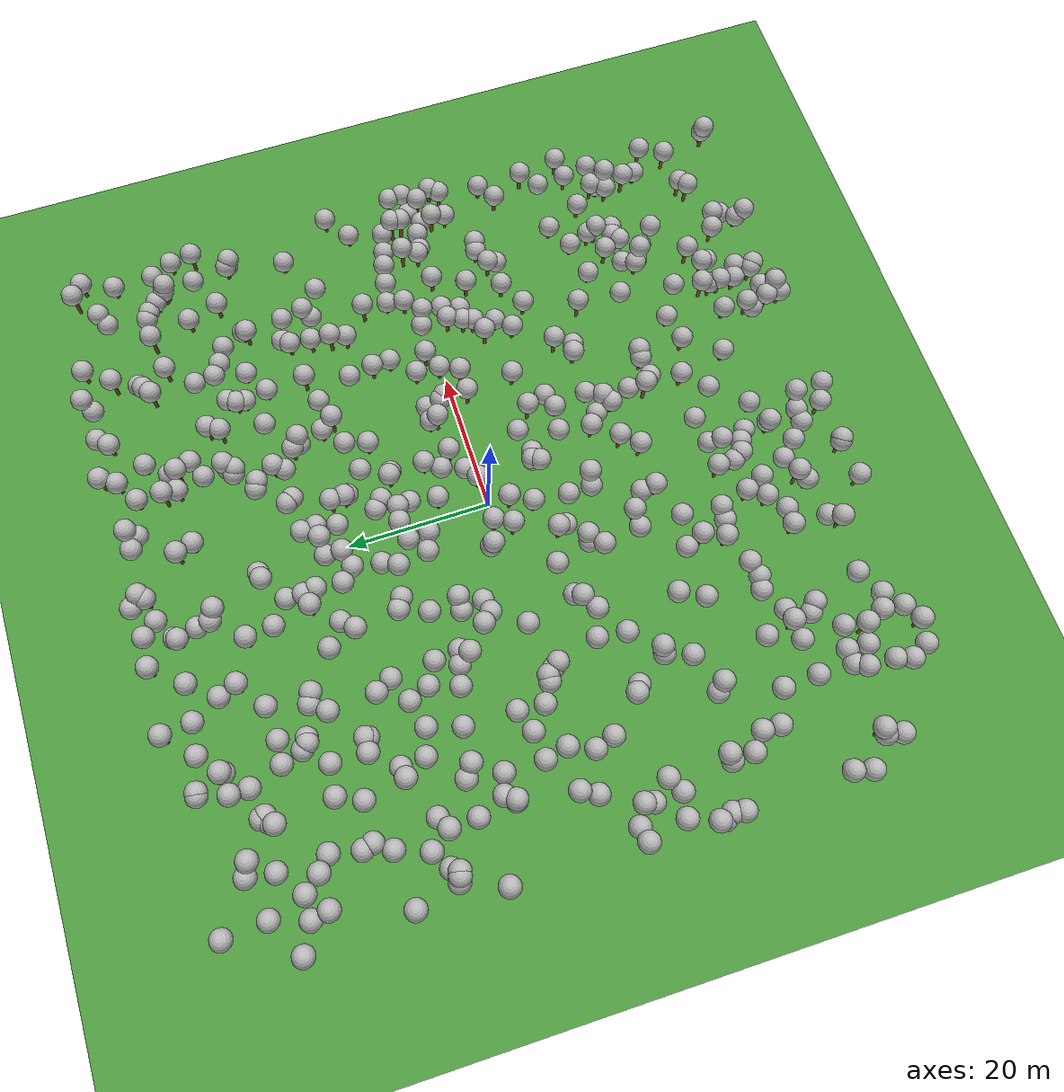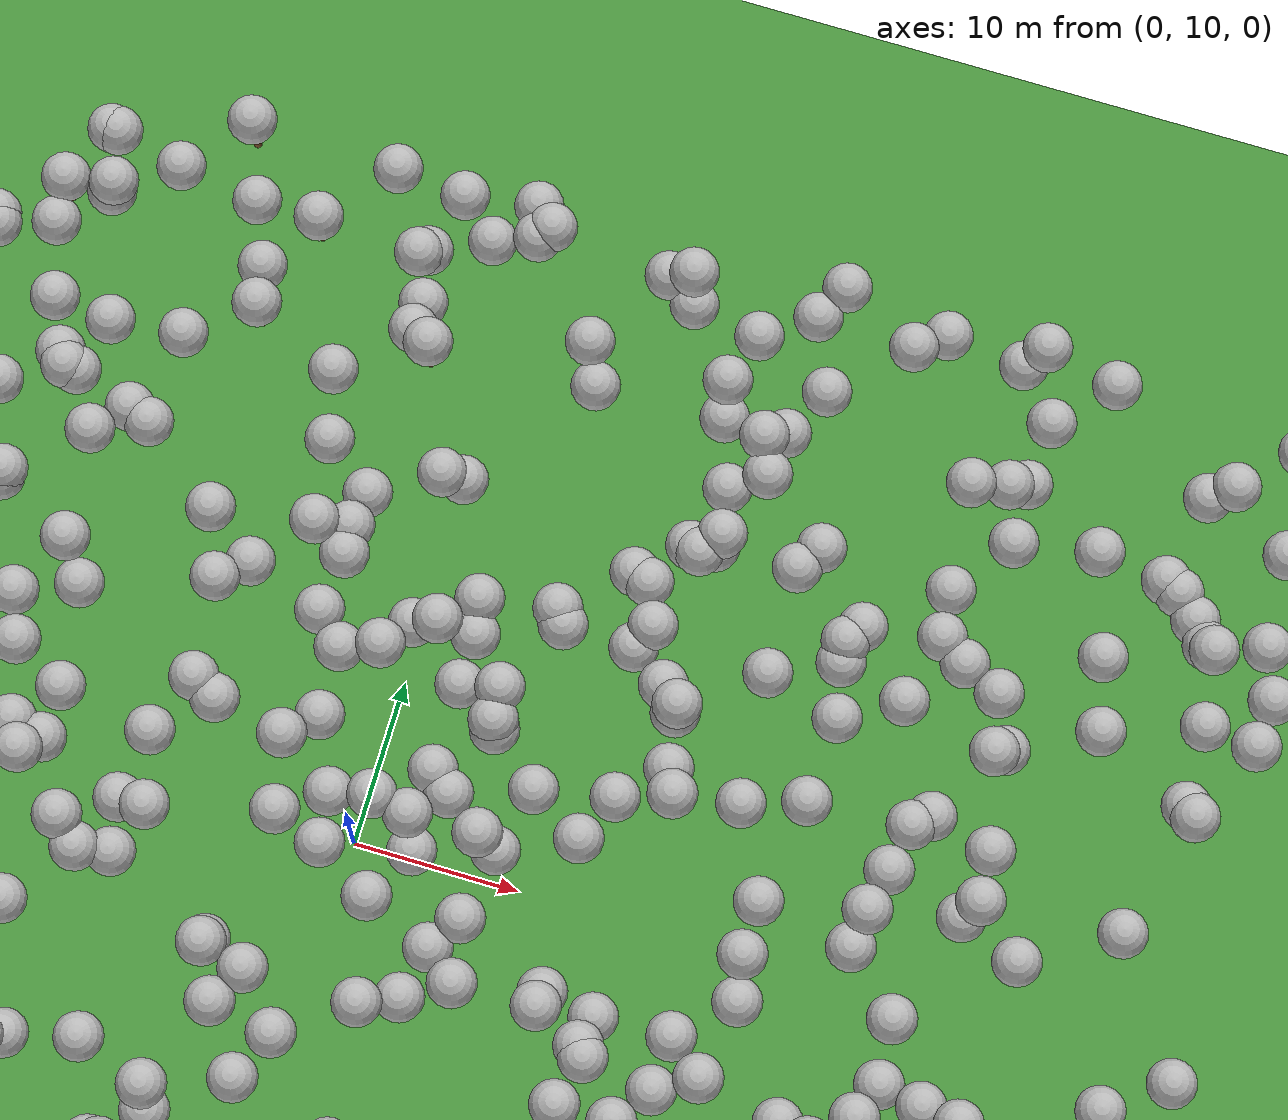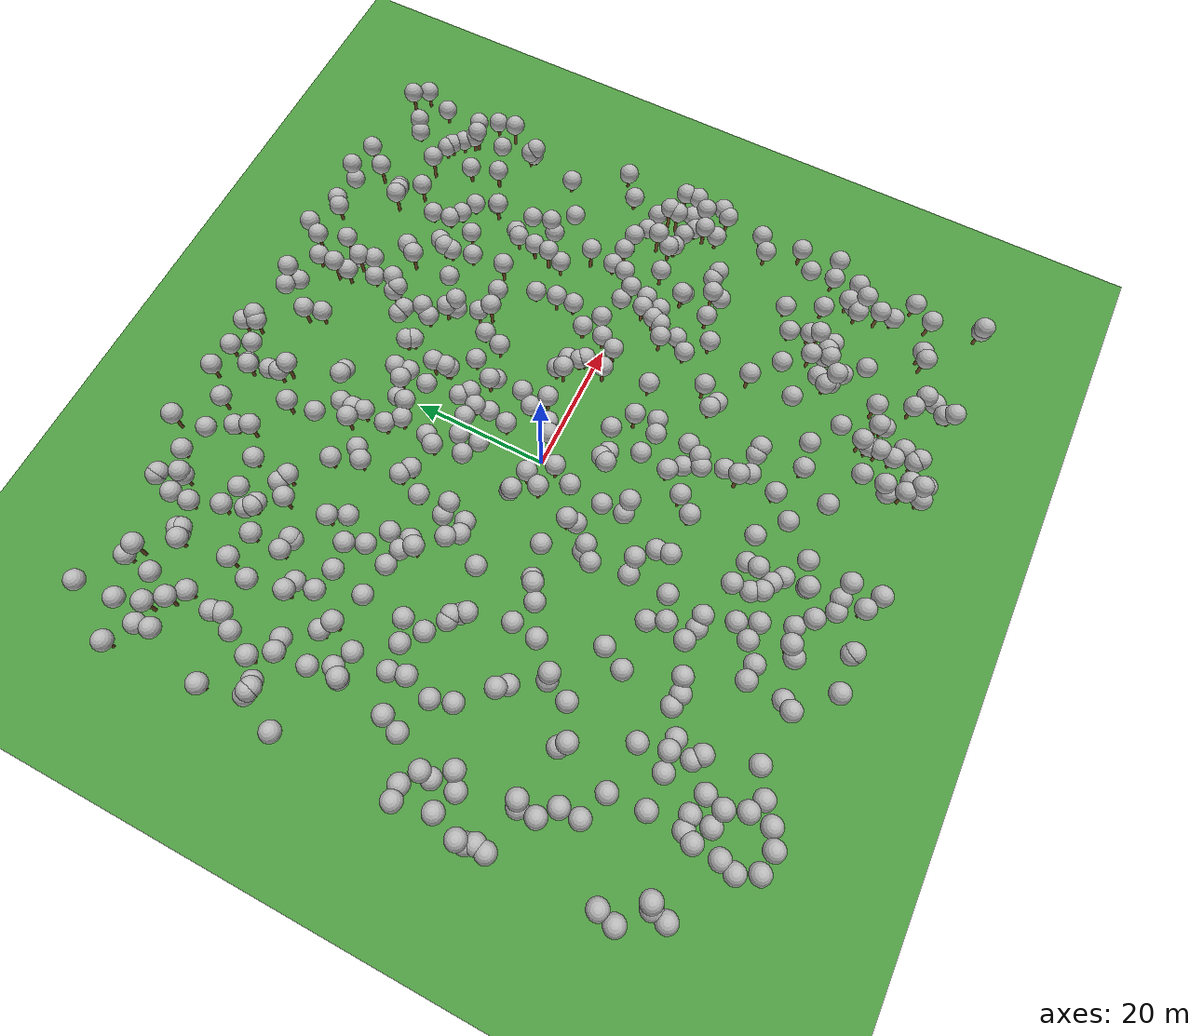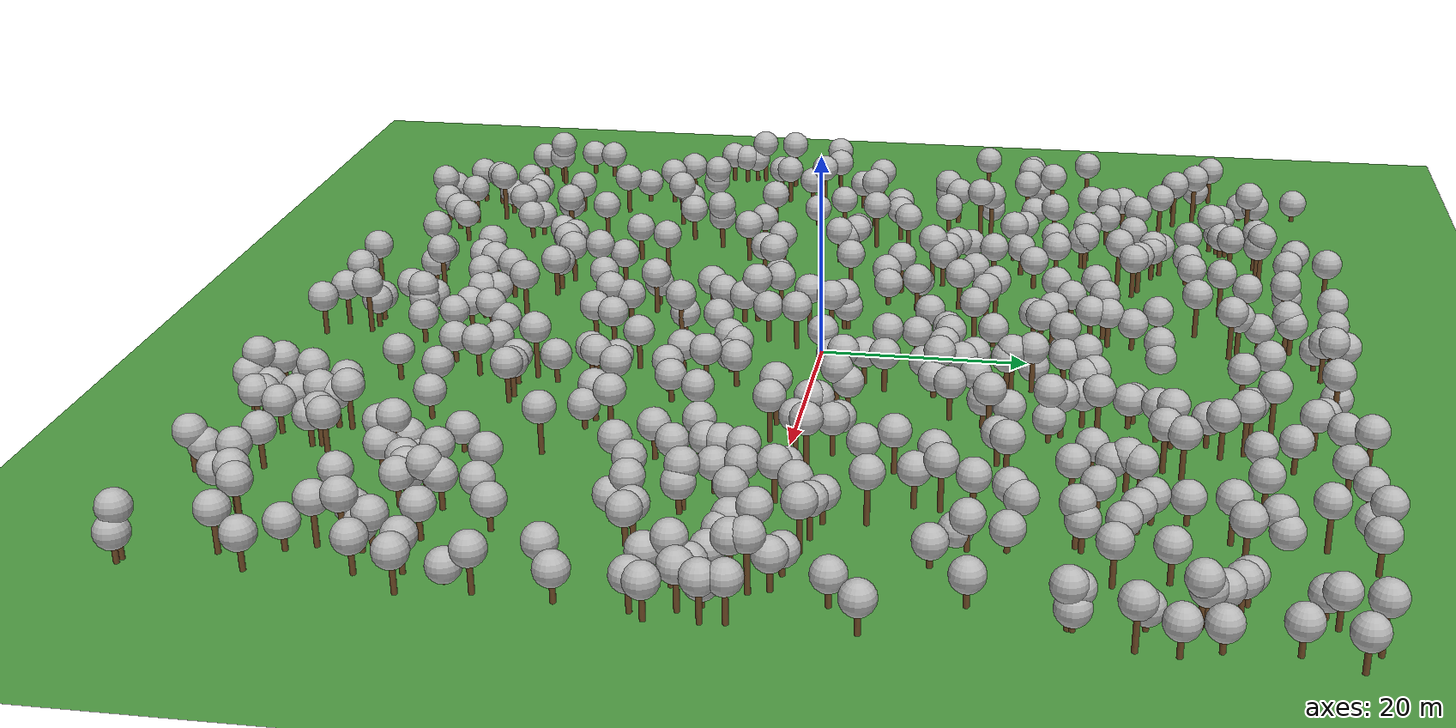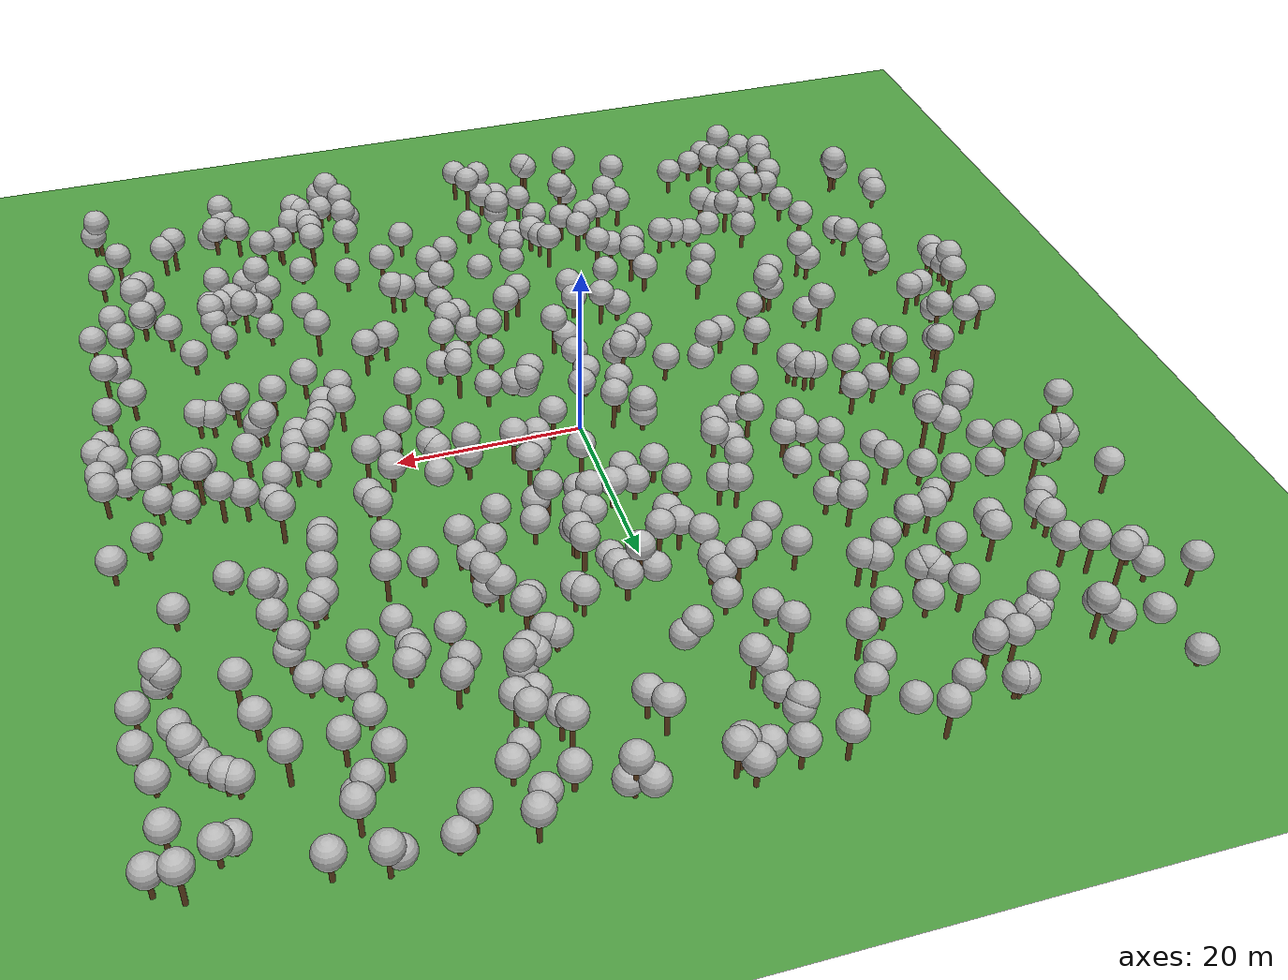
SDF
<sdf version="1.5">
  <world name="default">

    <plugin name="mrs_gazebo_static_transform_republisher_plugin" filename="libMRSGazeboStaticTransformRepublisher.so" />

    <spherical_coordinates>
      <surface_model>EARTH_WGS84</surface_model>
      <latitude_deg>47.397743</latitude_deg>
      <longitude_deg>8.545594</longitude_deg>
      <elevation>0.0</elevation>
      <heading_deg>0</heading_deg>
    </spherical_coordinates>

    <physics name="default_physics" default="0" type="ode">
      <gravity>0 0 -9.8066</gravity>
      <ode>
        <solver>
          <type>quick</type>
          <iters>50</iters>
          <sor>1.0</sor>
          <use_dynamic_moi_rescaling>0</use_dynamic_moi_rescaling>
        </solver>
        <constraints>
          <cfm>0</cfm>
          <erp>0.2</erp>
          <contact_max_correcting_vel>1000</contact_max_correcting_vel>
          <contact_surface_layer>0.001</contact_surface_layer>
        </constraints>
      </ode>
      <max_step_size>0.004</max_step_size>
      <real_time_factor>1</real_time_factor>
      <real_time_update_rate>250</real_time_update_rate>
      <magnetic_field>6.0e-06 2.3e-05 -4.2e-05</magnetic_field>
    </physics>

    <scene>
      <shadows>false</shadows>

    </scene>

    <light type="directional" name="sun">
      <cast_shadows>true</cast_shadows>
      <pose>250 250 600 0 0 0</pose>
      <diffuse>0.8 0.8 0.8 1</diffuse>
      <specular>0.2 0.2 0.2 1</specular>
      <attenuation>
        <range>1000</range>
        <constant>0.9</constant>
        <linear>0.01</linear>
        <quadratic>0.001</quadratic>
      </attenuation>
      <direction>0 0 -1</direction>
    </light>

    <model name="tree_simple499">
      <static>1</static>
      <link name="link">
        <pose frame="">0 0 0.1 0 -0 0</pose>
        <collision name="collision_trunk">
          <pose frame="">0 0 2 0 -0 0</pose>
          <geometry>
            <cylinder>
              <radius>0.25</radius>
              <length>4</length>
            </cylinder>
          </geometry>
        </collision>
        <collision name="collision_treetop">
          <pose frame="">0 0 5.2 0 -0 0</pose>
          <geometry>
            <sphere>
              <radius>1.5</radius>
            </sphere>
          </geometry>
        </collision>
        <visual name="trunk">
          <pose frame="">0 0 2 0 -0 0</pose>
          <geometry>
            <cylinder>
              <radius>0.25</radius>
              <length>4</length>
            </cylinder>
          </geometry>
          <material>
            <script>
              <uri>model://tree_simple/scripts</uri>
              <uri>model://tree_simple/materials/textures</uri>
              <name>TreeSimple/Trunk</name>
            </script>
          </material>
        </visual>
        <visual name="treetop">
          <pose frame="">0 0 5.2 0 -0 0</pose>
          <geometry>
            <sphere>
              <radius>1.5</radius>
            </sphere>
          </geometry>
          <material>
            <script>
              <uri>model://tree_simple/scripts</uri>
              <uri>model://tree_simple/materials/textures</uri>
              <name>TreeSimple/Treetop</name>
            </script>
          </material>
        </visual>
        <self_collide>0</self_collide>
        <kinematic>0</kinematic>
      </link>
      <pose frame="">49.5772894431 -0.301033806291 -1.388486694321096 0 -0 0</pose>
    </model>

    <model name="tree_simple498">
      <static>1</static>
      <link name="link">
        <pose frame="">0 0 0.1 0 -0 0</pose>
        <collision name="collision_trunk">
          <pose frame="">0 0 2 0 -0 0</pose>
          <geometry>
            <cylinder>
              <radius>0.25</radius>
              <length>4</length>
            </cylinder>
          </geometry>
        </collision>
        <collision name="collision_treetop">
          <pose frame="">0 0 5.2 0 -0 0</pose>
          <geometry>
            <sphere>
              <radius>1.5</radius>
            </sphere>
          </geometry>
        </collision>
        <visual name="trunk">
          <pose frame="">0 0 2 0 -0 0</pose>
          <geometry>
            <cylinder>
              <radius>0.25</radius>
              <length>4</length>
            </cylinder>
          </geometry>
          <material>
            <script>
              <uri>model://tree_simple/scripts</uri>
              <uri>model://tree_simple/materials/textures</uri>
              <name>TreeSimple/Trunk</name>
            </script>
          </material>
        </visual>
        <visual name="treetop">
          <pose frame="">0 0 5.2 0 -0 0</pose>
          <geometry>
            <sphere>
              <radius>1.5</radius>
            </sphere>
          </geometry>
          <material>
            <script>
              <uri>model://tree_simple/scripts</uri>
              <uri>model://tree_simple/materials/textures</uri>
              <name>TreeSimple/Treetop</name>
            </script>
          </material>
        </visual>
        <self_collide>0</self_collide>
        <kinematic>0</kinematic>
      </link>
      <pose frame="">-20.062069779 9.09254194943 -0.5727137692708224 0 -0 0</pose>
    </model>

    <model name="tree_simple497">
      <static>1</static>
      <link name="link">
        <pose frame="">0 0 0.1 0 -0 0</pose>
        <collision name="collision_trunk">
          <pose frame="">0 0 2 0 -0 0</pose>
          <geometry>
            <cylinder>
              <radius>0.25</radius>
              <length>4</length>
            </cylinder>
          </geometry>
        </collision>
        <collision name="collision_treetop">
          <pose frame="">0 0 5.2 0 -0 0</pose>
          <geometry>
            <sphere>
              <radius>1.5</radius>
            </sphere>
          </geometry>
        </collision>
        <visual name="trunk">
          <pose frame="">0 0 2 0 -0 0</pose>
          <geometry>
            <cylinder>
              <radius>0.25</radius>
              <length>4</length>
            </cylinder>
          </geometry>
          <material>
            <script>
              <uri>model://tree_simple/scripts</uri>
              <uri>model://tree_simple/materials/textures</uri>
              <name>TreeSimple/Trunk</name>
            </script>
          </material>
        </visual>
        <visual name="treetop">
          <pose frame="">0 0 5.2 0 -0 0</pose>
          <geometry>
            <sphere>
              <radius>1.5</radius>
            </sphere>
          </geometry>
          <material>
            <script>
              <uri>model://tree_simple/scripts</uri>
              <uri>model://tree_simple/materials/textures</uri>
              <name>TreeSimple/Treetop</name>
            </script>
          </material>
        </visual>
        <self_collide>0</self_collide>
        <kinematic>0</kinematic>
      </link>
      <pose frame="">16.5730666381 19.0016793819 -1.9084397085814553 0 -0 0</pose>
    </model>

    <model name="tree_simple496">
      <static>1</static>
      <link name="link">
        <pose frame="">0 0 0.1 0 -0 0</pose>
        <collision name="collision_trunk">
          <pose frame="">0 0 2 0 -0 0</pose>
          <geometry>
            <cylinder>
              <radius>0.25</radius>
              <length>4</length>
            </cylinder>
          </geometry>
        </collision>
        <collision name="collision_treetop">
          <pose frame="">0 0 5.2 0 -0 0</pose>
          <geometry>
            <sphere>
              <radius>1.5</radius>
            </sphere>
          </geometry>
        </collision>
        <visual name="trunk">
          <pose frame="">0 0 2 0 -0 0</pose>
          <geometry>
            <cylinder>
              <radius>0.25</radius>
              <length>4</length>
            </cylinder>
          </geometry>
          <material>
            <script>
              <uri>model://tree_simple/scripts</uri>
              <uri>model://tree_simple/materials/textures</uri>
              <name>TreeSimple/Trunk</name>
            </script>
          </material>
        </visual>
        <visual name="treetop">
          <pose frame="">0 0 5.2 0 -0 0</pose>
          <geometry>
            <sphere>
              <radius>1.5</radius>
            </sphere>
          </geometry>
          <material>
            <script>
              <uri>model://tree_simple/scripts</uri>
              <uri>model://tree_simple/materials/textures</uri>
              <name>TreeSimple/Treetop</name>
            </script>
          </material>
        </visual>
        <self_collide>0</self_collide>
        <kinematic>0</kinematic>
      </link>
      <pose frame="">13.6194298432 -26.9856291803 -1.9347447163207072 0 -0 0</pose>
    </model>

    <model name="tree_simple495">
      <static>1</static>
      <link name="link">
        <pose frame="">0 0 0.1 0 -0 0</pose>
        <collision name="collision_trunk">
          <pose frame="">0 0 2 0 -0 0</pose>
          <geometry>
            <cylinder>
              <radius>0.25</radius>
              <length>4</length>
            </cylinder>
          </geometry>
        </collision>
        <collision name="collision_treetop">
          <pose frame="">0 0 5.2 0 -0 0</pose>
          <geometry>
            <sphere>
              <radius>1.5</radius>
            </sphere>
          </geometry>
        </collision>
        <visual name="trunk">
          <pose frame="">0 0 2 0 -0 0</pose>
          <geometry>
            <cylinder>
              <radius>0.25</radius>
              <length>4</length>
            </cylinder>
          </geometry>
          <material>
            <script>
              <uri>model://tree_simple/scripts</uri>
              <uri>model://tree_simple/materials/textures</uri>
              <name>TreeSimple/Trunk</name>
            </script>
          </material>
        </visual>
        <visual name="treetop">
          <pose frame="">0 0 5.2 0 -0 0</pose>
          <geometry>
            <sphere>
              <radius>1.5</radius>
            </sphere>
          </geometry>
          <material>
            <script>
              <uri>model://tree_simple/scripts</uri>
              <uri>model://tree_simple/materials/textures</uri>
              <name>TreeSimple/Treetop</name>
            </script>
          </material>
        </visual>
        <self_collide>0</self_collide>
        <kinematic>0</kinematic>
      </link>
      <pose frame="">13.2663357304 3.23501246435 -0.6643117824017684 0 -0 0</pose>
    </model>

    <model name="tree_simple494">
      <static>1</static>
      <link name="link">
        <pose frame="">0 0 0.1 0 -0 0</pose>
        <collision name="collision_trunk">
          <pose frame="">0 0 2 0 -0 0</pose>
          <geometry>
            <cylinder>
              <radius>0.25</radius>
              <length>4</length>
            </cylinder>
          </geometry>
        </collision>
        <collision name="collision_treetop">
          <pose frame="">0 0 5.2 0 -0 0</pose>
          <geometry>
            <sphere>
              <radius>1.5</radius>
            </sphere>
          </geometry>
        </collision>
        <visual name="trunk">
          <pose frame="">0 0 2 0 -0 0</pose>
          <geometry>
            <cylinder>
              <radius>0.25</radius>
              <length>4</length>
            </cylinder>
          </geometry>
          <material>
            <script>
              <uri>model://tree_simple/scripts</uri>
              <uri>model://tree_simple/materials/textures</uri>
              <name>TreeSimple/Trunk</name>
            </script>
          </material>
        </visual>
        <visual name="treetop">
          <pose frame="">0 0 5.2 0 -0 0</pose>
          <geometry>
            <sphere>
              <radius>1.5</radius>
            </sphere>
          </geometry>
          <material>
            <script>
              <uri>model://tree_simple/scripts</uri>
              <uri>model://tree_simple/materials/textures</uri>
              <name>TreeSimple/Treetop</name>
            </script>
          </material>
        </visual>
        <self_collide>0</self_collide>
        <kinematic>0</kinematic>
      </link>
      <pose frame="">39.6521252177 -42.647901406 -1.601959565637076 0 -0 0</pose>
    </model>

    <model name="tree_simple493">
      <static>1</static>
      <link name="link">
        <pose frame="">0 0 0.1 0 -0 0</pose>
        <collision name="collision_trunk">
          <pose frame="">0 0 2 0 -0 0</pose>
          <geometry>
            <cylinder>
              <radius>0.25</radius>
              <length>4</length>
            </cylinder>
          </geometry>
        </collision>
        <collision name="collision_treetop">
          <pose frame="">0 0 5.2 0 -0 0</pose>
          <geometry>
            <sphere>
              <radius>1.5</radius>
            </sphere>
          </geometry>
        </collision>
        <visual name="trunk">
          <pose frame="">0 0 2 0 -0 0</pose>
          <geometry>
            <cylinder>
              <radius>0.25</radius>
              <length>4</length>
            </cylinder>
          </geometry>
          <material>
            <script>
              <uri>model://tree_simple/scripts</uri>
              <uri>model://tree_simple/materials/textures</uri>
              <name>TreeSimple/Trunk</name>
            </script>
          </material>
        </visual>
        <visual name="treetop">
          <pose frame="">0 0 5.2 0 -0 0</pose>
          <geometry>
            <sphere>
              <radius>1.5</radius>
            </sphere>
          </geometry>
          <material>
            <script>
              <uri>model://tree_simple/scripts</uri>
              <uri>model://tree_simple/materials/textures</uri>
              <name>TreeSimple/Treetop</name>
            </script>
          </material>
        </visual>
        <self_collide>0</self_collide>
        <kinematic>0</kinematic>
      </link>
      <pose frame="">-30.9686104206 18.3944298941 -2.510078814309051 0 -0 0</pose>
    </model>

    <model name="tree_simple492">
      <static>1</static>
      <link name="link">
        <pose frame="">0 0 0.1 0 -0 0</pose>
        <collision name="collision_trunk">
          <pose frame="">0 0 2 0 -0 0</pose>
          <geometry>
            <cylinder>
              <radius>0.25</radius>
              <length>4</length>
            </cylinder>
          </geometry>
        </collision>
        <collision name="collision_treetop">
          <pose frame="">0 0 5.2 0 -0 0</pose>
          <geometry>
            <sphere>
              <radius>1.5</radius>
            </sphere>
          </geometry>
        </collision>
        <visual name="trunk">
          <pose frame="">0 0 2 0 -0 0</pose>
          <geometry>
            <cylinder>
              <radius>0.25</radius>
              <length>4</length>
            </cylinder>
          </geometry>
          <material>
            <script>
              <uri>model://tree_simple/scripts</uri>
              <uri>model://tree_simple/materials/textures</uri>
              <name>TreeSimple/Trunk</name>
            </script>
          </material>
        </visual>
        <visual name="treetop">
          <pose frame="">0 0 5.2 0 -0 0</pose>
          <geometry>
            <sphere>
              <radius>1.5</radius>
            </sphere>
          </geometry>
          <material>
            <script>
              <uri>model://tree_simple/scripts</uri>
              <uri>model://tree_simple/materials/textures</uri>
              <name>TreeSimple/Treetop</name>
            </script>
          </material>
        </visual>
        <self_collide>0</self_collide>
        <kinematic>0</kinematic>
      </link>
      <pose frame="">-7.60604313382 27.1336498888 -0.777114410060258 0 -0 0</pose>
    </model>

    <model name="tree_simple491">
      <static>1</static>
      <link name="link">
        <pose frame="">0 0 0.1 0 -0 0</pose>
        <collision name="collision_trunk">
          <pose frame="">0 0 2 0 -0 0</pose>
          <geometry>
            <cylinder>
              <radius>0.25</radius>
              <length>4</length>
            </cylinder>
          </geometry>
        </collision>
        <collision name="collision_treetop">
          <pose frame="">0 0 5.2 0 -0 0</pose>
          <geometry>
            <sphere>
              <radius>1.5</radius>
            </sphere>
          </geometry>
        </collision>
        <visual name="trunk">
          <pose frame="">0 0 2 0 -0 0</pose>
          <geometry>
            <cylinder>
              <radius>0.25</radius>
              <length>4</length>
            </cylinder>
          </geometry>
          <material>
            <script>
              <uri>model://tree_simple/scripts</uri>
              <uri>model://tree_simple/materials/textures</uri>
              <name>TreeSimple/Trunk</name>
            </script>
          </material>
        </visual>
        <visual name="treetop">
          <pose frame="">0 0 5.2 0 -0 0</pose>
          <geometry>
            <sphere>
              <radius>1.5</radius>
            </sphere>
          </geometry>
          <material>
            <script>
              <uri>model://tree_simple/scripts</uri>
              <uri>model://tree_simple/materials/textures</uri>
              <name>TreeSimple/Treetop</name>
            </script>
          </material>
        </visual>
        <self_collide>0</self_collide>
        <kinematic>0</kinematic>
      </link>
      <pose frame="">-12.3902503735 -49.1082665042 -1.446654089868648 0 -0 0</pose>
    </model>

    <model name="tree_simple490">
      <static>1</static>
      <link name="link">
        <pose frame="">0 0 0.1 0 -0 0</pose>
        <collision name="collision_trunk">
          <pose frame="">0 0 2 0 -0 0</pose>
          <geometry>
            <cylinder>
              <radius>0.25</radius>
              <length>4</length>
            </cylinder>
          </geometry>
        </collision>
        <collision name="collision_treetop">
          <pose frame="">0 0 5.2 0 -0 0</pose>
          <geometry>
            <sphere>
              <radius>1.5</radius>
            </sphere>
          </geometry>
        </collision>
        <visual name="trunk">
          <pose frame="">0 0 2 0 -0 0</pose>
          <geometry>
            <cylinder>
              <radius>0.25</radius>
              <length>4</length>
            </cylinder>
          </geometry>
          <material>
            <script>
              <uri>model://tree_simple/scripts</uri>
              <uri>model://tree_simple/materials/textures</uri>
              <name>TreeSimple/Trunk</name>
            </script>
          </material>
        </visual>
        <visual name="treetop">
          <pose frame="">0 0 5.2 0 -0 0</pose>
          <geometry>
            <sphere>
              <radius>1.5</radius>
            </sphere>
          </geometry>
          <material>
            <script>
              <uri>model://tree_simple/scripts</uri>
              <uri>model://tree_simple/materials/textures</uri>
              <name>TreeSimple/Treetop</name>
            </script>
          </material>
        </visual>
        <self_collide>0</self_collide>
        <kinematic>0</kinematic>
      </link>
      <pose frame="">28.486302093 0.994684244644 -2.7495407814083164 0 -0 0</pose>
    </model>

    <model name="tree_simple489">
      <static>1</static>
      <link name="link">
        <pose frame="">0 0 0.1 0 -0 0</pose>
        <collision name="collision_trunk">
          <pose frame="">0 0 2 0 -0 0</pose>
          <geometry>
            <cylinder>
              <radius>0.25</radius>
              <length>4</length>
            </cylinder>
          </geometry>
        </collision>
        <collision name="collision_treetop">
          <pose frame="">0 0 5.2 0 -0 0</pose>
          <geometry>
            <sphere>
              <radius>1.5</radius>
            </sphere>
          </geometry>
        </collision>
        <visual name="trunk">
          <pose frame="">0 0 2 0 -0 0</pose>
          <geometry>
            <cylinder>
              <radius>0.25</radius>
              <length>4</length>
            </cylinder>
          </geometry>
          <material>
            <script>
              <uri>model://tree_simple/scripts</uri>
              <uri>model://tree_simple/materials/textures</uri>
              <name>TreeSimple/Trunk</name>
            </script>
          </material>
        </visual>
        <visual name="treetop">
          <pose frame="">0 0 5.2 0 -0 0</pose>
          <geometry>
            <sphere>
              <radius>1.5</radius>
            </sphere>
          </geometry>
          <material>
            <script>
              <uri>model://tree_simple/scripts</uri>
              <uri>model://tree_simple/materials/textures</uri>
              <name>TreeSimple/Treetop</name>
            </script>
          </material>
        </visual>
        <self_collide>0</self_collide>
        <kinematic>0</kinematic>
      </link>
      <pose frame="">-32.6634579524 39.3278172931 -3.138873466383935 0 -0 0</pose>
    </model>

    <model name="tree_simple488">
      <static>1</static>
      <link name="link">
        <pose frame="">0 0 0.1 0 -0 0</pose>
        <collision name="collision_trunk">
          <pose frame="">0 0 2 0 -0 0</pose>
          <geometry>
            <cylinder>
              <radius>0.25</radius>
              <length>4</length>
            </cylinder>
          </geometry>
        </collision>
        <collision name="collision_treetop">
          <pose frame="">0 0 5.2 0 -0 0</pose>
          <geometry>
            <sphere>
              <radius>1.5</radius>
            </sphere>
          </geometry>
        </collision>
        <visual name="trunk">
          <pose frame="">0 0 2 0 -0 0</pose>
          <geometry>
            <cylinder>
              <radius>0.25</radius>
              <length>4</length>
            </cylinder>
          </geometry>
          <material>
            <script>
              <uri>model://tree_simple/scripts</uri>
              <uri>model://tree_simple/materials/textures</uri>
              <name>TreeSimple/Trunk</name>
            </script>
          </material>
        </visual>
        <visual name="treetop">
          <pose frame="">0 0 5.2 0 -0 0</pose>
          <geometry>
            <sphere>
              <radius>1.5</radius>
            </sphere>
          </geometry>
          <material>
            <script>
              <uri>model://tree_simple/scripts</uri>
              <uri>model://tree_simple/materials/textures</uri>
              <name>TreeSimple/Treetop</name>
            </script>
          </material>
        </visual>
        <self_collide>0</self_collide>
        <kinematic>0</kinematic>
      </link>
      <pose frame="">-13.1215818691 12.435953241 -1.5400964836160544 0 -0 0</pose>
    </model>

    <model name="tree_simple487">
      <static>1</static>
      <link name="link">
        <pose frame="">0 0 0.1 0 -0 0</pose>
        <collision name="collision_trunk">
          <pose frame="">0 0 2 0 -0 0</pose>
          <geometry>
            <cylinder>
              <radius>0.25</radius>
              <length>4</length>
            </cylinder>
          </geometry>
        </collision>
        <collision name="collision_treetop">
          <pose frame="">0 0 5.2 0 -0 0</pose>
          <geometry>
            <sphere>
              <radius>1.5</radius>
            </sphere>
          </geometry>
        </collision>
        <visual name="trunk">
          <pose frame="">0 0 2 0 -0 0</pose>
          <geometry>
            <cylinder>
              <radius>0.25</radius>
              <length>4</length>
            </cylinder>
          </geometry>
          <material>
            <script>
              <uri>model://tree_simple/scripts</uri>
              <uri>model://tree_simple/materials/textures</uri>
              <name>TreeSimple/Trunk</name>
            </script>
          </material>
        </visual>
        <visual name="treetop">
          <pose frame="">0 0 5.2 0 -0 0</pose>
          <geometry>
            <sphere>
              <radius>1.5</radius>
            </sphere>
          </geometry>
          <material>
            <script>
              <uri>model://tree_simple/scripts</uri>
              <uri>model://tree_simple/materials/textures</uri>
              <name>TreeSimple/Treetop</name>
            </script>
          </material>
        </visual>
        <self_collide>0</self_collide>
        <kinematic>0</kinematic>
      </link>
      <pose frame="">33.1280168764 8.35331864597 -0.5759778142481673 0 -0 0</pose>
    </model>

    <model name="tree_simple486">
      <static>1</static>
      <link name="link">
        <pose frame="">0 0 0.1 0 -0 0</pose>
        <collision name="collision_trunk">
          <pose frame="">0 0 2 0 -0 0</pose>
          <geometry>
            <cylinder>
              <radius>0.25</radius>
              <length>4</length>
            </cylinder>
          </geometry>
        </collision>
        <collision name="collision_treetop">
          <pose frame="">0 0 5.2 0 -0 0</pose>
          <geometry>
            <sphere>
              <radius>1.5</radius>
            </sphere>
          </geometry>
        </collision>
        <visual name="trunk">
          <pose frame="">0 0 2 0 -0 0</pose>
          <geometry>
            <cylinder>
              <radius>0.25</radius>
              <length>4</length>
            </cylinder>
          </geometry>
          <material>
            <script>
              <uri>model://tree_simple/scripts</uri>
              <uri>model://tree_simple/materials/textures</uri>
              <name>TreeSimple/Trunk</name>
            </script>
          </material>
        </visual>
        <visual name="treetop">
          <pose frame="">0 0 5.2 0 -0 0</pose>
          <geometry>
            <sphere>
              <radius>1.5</radius>
            </sphere>
          </geometry>
          <material>
            <script>
              <uri>model://tree_simple/scripts</uri>
              <uri>model://tree_simple/materials/textures</uri>
              <name>TreeSimple/Treetop</name>
            </script>
          </material>
        </visual>
        <self_collide>0</self_collide>
        <kinematic>0</kinematic>
      </link>
      <pose frame="">8.18281559396 11.6524151823 -3.3027352705335433 0 -0 0</pose>
    </model>

    <model name="tree_simple485">
      <static>1</static>
      <link name="link">
        <pose frame="">0 0 0.1 0 -0 0</pose>
        <collision name="collision_trunk">
          <pose frame="">0 0 2 0 -0 0</pose>
          <geometry>
            <cylinder>
              <radius>0.25</radius>
              <length>4</length>
            </cylinder>
          </geometry>
        </collision>
        <collision name="collision_treetop">
          <pose frame="">0 0 5.2 0 -0 0</pose>
          <geometry>
            <sphere>
              <radius>1.5</radius>
            </sphere>
          </geometry>
        </collision>
        <visual name="trunk">
          <pose frame="">0 0 2 0 -0 0</pose>
          <geometry>
            <cylinder>
              <radius>0.25</radius>
              <length>4</length>
            </cylinder>
          </geometry>
          <material>
            <script>
              <uri>model://tree_simple/scripts</uri>
              <uri>model://tree_simple/materials/textures</uri>
              <name>TreeSimple/Trunk</name>
            </script>
          </material>
        </visual>
        <visual name="treetop">
          <pose frame="">0 0 5.2 0 -0 0</pose>
          <geometry>
            <sphere>
              <radius>1.5</radius>
            </sphere>
          </geometry>
          <material>
            <script>
              <uri>model://tree_simple/scripts</uri>
              <uri>model://tree_simple/materials/textures</uri>
              <name>TreeSimple/Treetop</name>
            </script>
          </material>
        </visual>
        <self_collide>0</self_collide>
        <kinematic>0</kinematic>
      </link>
      <pose frame="">38.4673421664 3.60529435805 -0.7133389257745315 0 -0 0</pose>
    </model>

    <model name="tree_simple484">
      <static>1</static>
      <link name="link">
        <pose frame="">0 0 0.1 0 -0 0</pose>
        <collision name="collision_trunk">
          <pose frame="">0 0 2 0 -0 0</pose>
          <geometry>
            <cylinder>
              <radius>0.25</radius>
              <length>4</length>
            </cylinder>
          </geometry>
        </collision>
        <collision name="collision_treetop">
          <pose frame="">0 0 5.2 0 -0 0</pose>
          <geometry>
            <sphere>
              <radius>1.5</radius>
            </sphere>
          </geometry>
        </collision>
        <visual name="trunk">
          <pose frame="">0 0 2 0 -0 0</pose>
          <geometry>
            <cylinder>
              <radius>0.25</radius>
              <length>4</length>
            </cylinder>
          </geometry>
          <material>
            <script>
              <uri>model://tree_simple/scripts</uri>
              <uri>model://tree_simple/materials/textures</uri>
              <name>TreeSimple/Trunk</name>
            </script>
          </material>
        </visual>
        <visual name="treetop">
          <pose frame="">0 0 5.2 0 -0 0</pose>
          <geometry>
            <sphere>
              <radius>1.5</radius>
            </sphere>
          </geometry>
          <material>
            <script>
              <uri>model://tree_simple/scripts</uri>
              <uri>model://tree_simple/materials/textures</uri>
              <name>TreeSimple/Treetop</name>
            </script>
          </material>
        </visual>
        <self_collide>0</self_collide>
        <kinematic>0</kinematic>
      </link>
      <pose frame="">19.8605088225 -47.9062304077 -2.568141716396418 0 -0 0</pose>
    </model>

    <model name="tree_simple483">
      <static>1</static>
      <link name="link">
        <pose frame="">0 0 0.1 0 -0 0</pose>
        <collision name="collision_trunk">
          <pose frame="">0 0 2 0 -0 0</pose>
          <geometry>
            <cylinder>
              <radius>0.25</radius>
              <length>4</length>
            </cylinder>
          </geometry>
        </collision>
        <collision name="collision_treetop">
          <pose frame="">0 0 5.2 0 -0 0</pose>
          <geometry>
            <sphere>
              <radius>1.5</radius>
            </sphere>
          </geometry>
        </collision>
        <visual name="trunk">
          <pose frame="">0 0 2 0 -0 0</pose>
          <geometry>
            <cylinder>
              <radius>0.25</radius>
              <length>4</length>
            </cylinder>
          </geometry>
          <material>
            <script>
              <uri>model://tree_simple/scripts</uri>
              <uri>model://tree_simple/materials/textures</uri>
              <name>TreeSimple/Trunk</name>
            </script>
          </material>
        </visual>
        <visual name="treetop">
          <pose frame="">0 0 5.2 0 -0 0</pose>
          <geometry>
            <sphere>
              <radius>1.5</radius>
            </sphere>
          </geometry>
          <material>
            <script>
              <uri>model://tree_simple/scripts</uri>
              <uri>model://tree_simple/materials/textures</uri>
              <name>TreeSimple/Treetop</name>
            </script>
          </material>
        </visual>
        <self_collide>0</self_collide>
        <kinematic>0</kinematic>
      </link>
      <pose frame="">-6.65162129766 44.7613363002 -1.5673599600233408 0 -0 0</pose>
    </model>

    <model name="tree_simple482">
      <static>1</static>
      <link name="link">
        <pose frame="">0 0 0.1 0 -0 0</pose>
        <collision name="collision_trunk">
          <pose frame="">0 0 2 0 -0 0</pose>
          <geometry>
            <cylinder>
              <radius>0.25</radius>
              <length>4</length>
            </cylinder>
          </geometry>
        </collision>
        <collision name="collision_treetop">
          <pose frame="">0 0 5.2 0 -0 0</pose>
          <geometry>
            <sphere>
              <radius>1.5</radius>
            </sphere>
          </geometry>
        </collision>
        <visual name="trunk">
          <pose frame="">0 0 2 0 -0 0</pose>
          <geometry>
            <cylinder>
              <radius>0.25</radius>
              <length>4</length>
            </cylinder>
          </geometry>
          <material>
            <script>
              <uri>model://tree_simple/scripts</uri>
              <uri>model://tree_simple/materials/textures</uri>
              <name>TreeSimple/Trunk</name>
            </script>
          </material>
        </visual>
        <visual name="treetop">
          <pose frame="">0 0 5.2 0 -0 0</pose>
          <geometry>
            <sphere>
              <radius>1.5</radius>
            </sphere>
          </geometry>
          <material>
            <script>
              <uri>model://tree_simple/scripts</uri>
              <uri>model://tree_simple/materials/textures</uri>
              <name>TreeSimple/Treetop</name>
            </script>
          </material>
        </visual>
        <self_collide>0</self_collide>
        <kinematic>0</kinematic>
      </link>
      <pose frame="">-31.7137183406 39.6850484597 -3.1111508047833083 0 -0 0</pose>
    </model>

    <model name="tree_simple481">
      <static>1</static>
      <link name="link">
        <pose frame="">0 0 0.1 0 -0 0</pose>
        <collision name="collision_trunk">
          <pose frame="">0 0 2 0 -0 0</pose>
          <geometry>
            <cylinder>
              <radius>0.25</radius>
              <length>4</length>
            </cylinder>
          </geometry>
        </collision>
        <collision name="collision_treetop">
          <pose frame="">0 0 5.2 0 -0 0</pose>
          <geometry>
            <sphere>
              <radius>1.5</radius>
            </sphere>
          </geometry>
        </collision>
        <visual name="trunk">
          <pose frame="">0 0 2 0 -0 0</pose>
          <geometry>
            <cylinder>
              <radius>0.25</radius>
              <length>4</length>
            </cylinder>
          </geometry>
          <material>
            <script>
              <uri>model://tree_simple/scripts</uri>
              <uri>model://tree_simple/materials/textures</uri>
              <name>TreeSimple/Trunk</name>
            </script>
          </material>
        </visual>
        <visual name="treetop">
          <pose frame="">0 0 5.2 0 -0 0</pose>
          <geometry>
            <sphere>
              <radius>1.5</radius>
            </sphere>
          </geometry>
          <material>
            <script>
              <uri>model://tree_simple/scripts</uri>
              <uri>model://tree_simple/materials/textures</uri>
              <name>TreeSimple/Treetop</name>
            </script>
          </material>
        </visual>
        <self_collide>0</self_collide>
        <kinematic>0</kinematic>
      </link>
      <pose frame="">-37.2553351017 -39.4739685818 -1.9470463064464087 0 -0 0</pose>
    </model>

    <model name="tree_simple480">
      <static>1</static>
      <link name="link">
        <pose frame="">0 0 0.1 0 -0 0</pose>
        <collision name="collision_trunk">
          <pose frame="">0 0 2 0 -0 0</pose>
          <geometry>
            <cylinder>
              <radius>0.25</radius>
              <length>4</length>
            </cylinder>
          </geometry>
        </collision>
        <collision name="collision_treetop">
          <pose frame="">0 0 5.2 0 -0 0</pose>
          <geometry>
            <sphere>
              <radius>1.5</radius>
            </sphere>
          </geometry>
        </collision>
        <visual name="trunk">
          <pose frame="">0 0 2 0 -0 0</pose>
          <geometry>
            <cylinder>
              <radius>0.25</radius>
              <length>4</length>
            </cylinder>
          </geometry>
          <material>
            <script>
              <uri>model://tree_simple/scripts</uri>
              <uri>model://tree_simple/materials/textures</uri>
              <name>TreeSimple/Trunk</name>
            </script>
          </material>
        </visual>
        <visual name="treetop">
          <pose frame="">0 0 5.2 0 -0 0</pose>
          <geometry>
            <sphere>
              <radius>1.5</radius>
            </sphere>
          </geometry>
          <material>
            <script>
              <uri>model://tree_simple/scripts</uri>
              <uri>model://tree_simple/materials/textures</uri>
              <name>TreeSimple/Treetop</name>
            </script>
          </material>
        </visual>
        <self_collide>0</self_collide>
        <kinematic>0</kinematic>
      </link>
      <pose frame="">-2.16211412072 12.1351070175 -2.756840422379751 0 -0 0</pose>
    </model>

    <model name="tree_simple479">
      <static>1</static>
      <link name="link">
        <pose frame="">0 0 0.1 0 -0 0</pose>
        <collision name="collision_trunk">
          <pose frame="">0 0 2 0 -0 0</pose>
          <geometry>
            <cylinder>
              <radius>0.25</radius>
              <length>4</length>
            </cylinder>
          </geometry>
        </collision>
        <collision name="collision_treetop">
          <pose frame="">0 0 5.2 0 -0 0</pose>
          <geometry>
            <sphere>
              <radius>1.5</radius>
            </sphere>
          </geometry>
        </collision>
        <visual name="trunk">
          <pose frame="">0 0 2 0 -0 0</pose>
          <geometry>
            <cylinder>
              <radius>0.25</radius>
              <length>4</length>
            </cylinder>
          </geometry>
          <material>
            <script>
              <uri>model://tree_simple/scripts</uri>
              <uri>model://tree_simple/materials/textures</uri>
              <name>TreeSimple/Trunk</name>
            </script>
          </material>
        </visual>
        <visual name="treetop">
          <pose frame="">0 0 5.2 0 -0 0</pose>
          <geometry>
            <sphere>
              <radius>1.5</radius>
            </sphere>
          </geometry>
          <material>
            <script>
              <uri>model://tree_simple/scripts</uri>
              <uri>model://tree_simple/materials/textures</uri>
              <name>TreeSimple/Treetop</name>
            </script>
          </material>
        </visual>
        <self_collide>0</self_collide>
        <kinematic>0</kinematic>
      </link>
      <pose frame="">-12.2778199556 22.3020251283 -1.5209438534683652 0 -0 0</pose>
    </model>

    <model name="tree_simple478">
      <static>1</static>
      <link name="link">
        <pose frame="">0 0 0.1 0 -0 0</pose>
        <collision name="collision_trunk">
          <pose frame="">0 0 2 0 -0 0</pose>
          <geometry>
            <cylinder>
              <radius>0.25</radius>
              <length>4</length>
            </cylinder>
          </geometry>
        </collision>
        <collision name="collision_treetop">
          <pose frame="">0 0 5.2 0 -0 0</pose>
          <geometry>
            <sphere>
              <radius>1.5</radius>
            </sphere>
          </geometry>
        </collision>
        <visual name="trunk">
          <pose frame="">0 0 2 0 -0 0</pose>
          <geometry>
            <cylinder>
              <radius>0.25</radius>
              <length>4</length>
            </cylinder>
          </geometry>
          <material>
            <script>
              <uri>model://tree_simple/scripts</uri>
              <uri>model://tree_simple/materials/textures</uri>
              <name>TreeSimple/Trunk</name>
            </script>
          </material>
        </visual>
        <visual name="treetop">
          <pose frame="">0 0 5.2 0 -0 0</pose>
          <geometry>
            <sphere>
              <radius>1.5</radius>
            </sphere>
          </geometry>
          <material>
            <script>
              <uri>model://tree_simple/scripts</uri>
              <uri>model://tree_simple/materials/textures</uri>
              <name>TreeSimple/Treetop</name>
            </script>
          </material>
        </visual>
        <self_collide>0</self_collide>
        <kinematic>0</kinematic>
      </link>
      <pose frame="">6.74093075138 -12.3162984353 -2.3090144796189875 0 -0 0</pose>
    </model>

    <model name="tree_simple477">
      <static>1</static>
      <link name="link">
        <pose frame="">0 0 0.1 0 -0 0</pose>
        <collision name="collision_trunk">
          <pose frame="">0 0 2 0 -0 0</pose>
          <geometry>
            <cylinder>
              <radius>0.25</radius>
              <length>4</length>
            </cylinder>
          </geometry>
        </collision>
        <collision name="collision_treetop">
          <pose frame="">0 0 5.2 0 -0 0</pose>
          <geometry>
            <sphere>
              <radius>1.5</radius>
            </sphere>
          </geometry>
        </collision>
        <visual name="trunk">
          <pose frame="">0 0 2 0 -0 0</pose>
          <geometry>
            <cylinder>
              <radius>0.25</radius>
              <length>4</length>
            </cylinder>
          </geometry>
          <material>
            <script>
              <uri>model://tree_simple/scripts</uri>
              <uri>model://tree_simple/materials/textures</uri>
              <name>TreeSimple/Trunk</name>
            </script>
          </material>
        </visual>
        <visual name="treetop">
          <pose frame="">0 0 5.2 0 -0 0</pose>
          <geometry>
            <sphere>
              <radius>1.5</radius>
            </sphere>
          </geometry>
          <material>
            <script>
              <uri>model://tree_simple/scripts</uri>
              <uri>model://tree_simple/materials/textures</uri>
              <name>TreeSimple/Treetop</name>
            </script>
          </material>
        </visual>
        <self_collide>0</self_collide>
        <kinematic>0</kinematic>
      </link>
      <pose frame="">-0.22927085135 32.6495918535 -4.0 0 -0 0</pose>
    </model>

    <model name="tree_simple476">
      <static>1</static>
      <link name="link">
        <pose frame="">0 0 0.1 0 -0 0</pose>
        <collision name="collision_trunk">
          <pose frame="">0 0 2 0 -0 0</pose>
          <geometry>
            <cylinder>
              <radius>0.25</radius>
              <length>4</length>
            </cylinder>
          </geometry>
        </collision>
        <collision name="collision_treetop">
          <pose frame="">0 0 5.2 0 -0 0</pose>
          <geometry>
            <sphere>
              <radius>1.5</radius>
            </sphere>
          </geometry>
        </collision>
        <visual name="trunk">
          <pose frame="">0 0 2 0 -0 0</pose>
          <geometry>
            <cylinder>
              <radius>0.25</radius>
              <length>4</length>
            </cylinder>
          </geometry>
          <material>
            <script>
              <uri>model://tree_simple/scripts</uri>
              <uri>model://tree_simple/materials/textures</uri>
              <name>TreeSimple/Trunk</name>
            </script>
          </material>
        </visual>
        <visual name="treetop">
          <pose frame="">0 0 5.2 0 -0 0</pose>
          <geometry>
            <sphere>
              <radius>1.5</radius>
            </sphere>
          </geometry>
          <material>
            <script>
              <uri>model://tree_simple/scripts</uri>
              <uri>model://tree_simple/materials/textures</uri>
              <name>TreeSimple/Treetop</name>
            </script>
          </material>
        </visual>
        <self_collide>0</self_collide>
        <kinematic>0</kinematic>
      </link>
      <pose frame="">-40.490555579 18.243153787 -1.0676930194325198 0 -0 0</pose>
    </model>

    <model name="tree_simple475">
      <static>1</static>
      <link name="link">
        <pose frame="">0 0 0.1 0 -0 0</pose>
        <collision name="collision_trunk">
          <pose frame="">0 0 2 0 -0 0</pose>
          <geometry>
            <cylinder>
              <radius>0.25</radius>
              <length>4</length>
            </cylinder>
          </geometry>
        </collision>
        <collision name="collision_treetop">
          <pose frame="">0 0 5.2 0 -0 0</pose>
          <geometry>
            <sphere>
              <radius>1.5</radius>
            </sphere>
          </geometry>
        </collision>
        <visual name="trunk">
          <pose frame="">0 0 2 0 -0 0</pose>
          <geometry>
            <cylinder>
              <radius>0.25</radius>
              <length>4</length>
            </cylinder>
          </geometry>
          <material>
            <script>
              <uri>model://tree_simple/scripts</uri>
              <uri>model://tree_simple/materials/textures</uri>
              <name>TreeSimple/Trunk</name>
            </script>
          </material>
        </visual>
        <visual name="treetop">
          <pose frame="">0 0 5.2 0 -0 0</pose>
          <geometry>
            <sphere>
              <radius>1.5</radius>
            </sphere>
          </geometry>
          <material>
            <script>
              <uri>model://tree_simple/scripts</uri>
              <uri>model://tree_simple/materials/textures</uri>
              <name>TreeSimple/Treetop</name>
            </script>
          </material>
        </visual>
        <self_collide>0</self_collide>
        <kinematic>0</kinematic>
      </link>
      <pose frame="">30.9431222124 49.7431013716 -1.484301673260343 0 -0 0</pose>
    </model>

    <model name="tree_simple474">
      <static>1</static>
      <link name="link">
        <pose frame="">0 0 0.1 0 -0 0</pose>
        <collision name="collision_trunk">
          <pose frame="">0 0 2 0 -0 0</pose>
          <geometry>
            <cylinder>
              <radius>0.25</radius>
              <length>4</length>
            </cylinder>
          </geometry>
        </collision>
        <collision name="collision_treetop">
          <pose frame="">0 0 5.2 0 -0 0</pose>
          <geometry>
            <sphere>
              <radius>1.5</radius>
            </sphere>
          </geometry>
        </collision>
        <visual name="trunk">
          <pose frame="">0 0 2 0 -0 0</pose>
          <geometry>
            <cylinder>
              <radius>0.25</radius>
              <length>4</length>
            </cylinder>
          </geometry>
          <material>
            <script>
              <uri>model://tree_simple/scripts</uri>
              <uri>model://tree_simple/materials/textures</uri>
              <name>TreeSimple/Trunk</name>
            </script>
          </material>
        </visual>
        <visual name="treetop">
          <pose frame="">0 0 5.2 0 -0 0</pose>
          <geometry>
            <sphere>
              <radius>1.5</radius>
            </sphere>
          </geometry>
          <material>
            <script>
              <uri>model://tree_simple/scripts</uri>
              <uri>model://tree_simple/materials/textures</uri>
              <name>TreeSimple/Treetop</name>
            </script>
          </material>
        </visual>
        <self_collide>0</self_collide>
        <kinematic>0</kinematic>
      </link>
      <pose frame="">-45.5609359524 37.3889677829 -2.8404649783358575 0 -0 0</pose>
    </model>

    <model name="tree_simple473">
      <static>1</static>
      <link name="link">
        <pose frame="">0 0 0.1 0 -0 0</pose>
        <collision name="collision_trunk">
          <pose frame="">0 0 2 0 -0 0</pose>
          <geometry>
            <cylinder>
              <radius>0.25</radius>
              <length>4</length>
            </cylinder>
          </geometry>
        </collision>
        <collision name="collision_treetop">
          <pose frame="">0 0 5.2 0 -0 0</pose>
          <geometry>
            <sphere>
              <radius>1.5</radius>
            </sphere>
          </geometry>
        </collision>
        <visual name="trunk">
          <pose frame="">0 0 2 0 -0 0</pose>
          <geometry>
            <cylinder>
              <radius>0.25</radius>
              <length>4</length>
            </cylinder>
          </geometry>
          <material>
            <script>
              <uri>model://tree_simple/scripts</uri>
              <uri>model://tree_simple/materials/textures</uri>
              <name>TreeSimple/Trunk</name>
            </script>
          </material>
        </visual>
        <visual name="treetop">
          <pose frame="">0 0 5.2 0 -0 0</pose>
          <geometry>
            <sphere>
              <radius>1.5</radius>
            </sphere>
          </geometry>
          <material>
            <script>
              <uri>model://tree_simple/scripts</uri>
              <uri>model://tree_simple/materials/textures</uri>
              <name>TreeSimple/Treetop</name>
            </script>
          </material>
        </visual>
        <self_collide>0</self_collide>
        <kinematic>0</kinematic>
      </link>
      <pose frame="">35.3600050295 -12.4568326028 -2.9783088301187934 0 -0 0</pose>
    </model>

    <model name="tree_simple472">
      <static>1</static>
      <link name="link">
        <pose frame="">0 0 0.1 0 -0 0</pose>
        <collision name="collision_trunk">
          <pose frame="">0 0 2 0 -0 0</pose>
          <geometry>
            <cylinder>
              <radius>0.25</radius>
              <length>4</length>
            </cylinder>
          </geometry>
        </collision>
        <collision name="collision_treetop">
          <pose frame="">0 0 5.2 0 -0 0</pose>
          <geometry>
            <sphere>
              <radius>1.5</radius>
            </sphere>
          </geometry>
        </collision>
        <visual name="trunk">
          <pose frame="">0 0 2 0 -0 0</pose>
          <geometry>
            <cylinder>
              <radius>0.25</radius>
              <length>4</length>
            </cylinder>
          </geometry>
          <material>
            <script>
              <uri>model://tree_simple/scripts</uri>
              <uri>model://tree_simple/materials/textures</uri>
              <name>TreeSimple/Trunk</name>
            </script>
          </material>
        </visual>
        <visual name="treetop">
          <pose frame="">0 0 5.2 0 -0 0</pose>
          <geometry>
            <sphere>
              <radius>1.5</radius>
            </sphere>
          </geometry>
          <material>
            <script>
              <uri>model://tree_simple/scripts</uri>
              <uri>model://tree_simple/materials/textures</uri>
              <name>TreeSimple/Treetop</name>
            </script>
          </material>
        </visual>
        <self_collide>0</self_collide>
        <kinematic>0</kinematic>
      </link>
      <pose frame="">9.92228677952 -23.8303447852 -2.588696135577622 0 -0 0</pose>
    </model>

    <model name="tree_simple471">
      <static>1</static>
      <link name="link">
        <pose frame="">0 0 0.1 0 -0 0</pose>
        <collision name="collision_trunk">
          <pose frame="">0 0 2 0 -0 0</pose>
          <geometry>
            <cylinder>
              <radius>0.25</radius>
              <length>4</length>
            </cylinder>
          </geometry>
        </collision>
        <collision name="collision_treetop">
          <pose frame="">0 0 5.2 0 -0 0</pose>
          <geometry>
            <sphere>
              <radius>1.5</radius>
            </sphere>
          </geometry>
        </collision>
        <visual name="trunk">
          <pose frame="">0 0 2 0 -0 0</pose>
          <geometry>
            <cylinder>
              <radius>0.25</radius>
              <length>4</length>
            </cylinder>
          </geometry>
          <material>
            <script>
              <uri>model://tree_simple/scripts</uri>
              <uri>model://tree_simple/materials/textures</uri>
              <name>TreeSimple/Trunk</name>
            </script>
          </material>
        </visual>
        <visual name="treetop">
          <pose frame="">0 0 5.2 0 -0 0</pose>
          <geometry>
            <sphere>
              <radius>1.5</radius>
            </sphere>
          </geometry>
          <material>
            <script>
              <uri>model://tree_simple/scripts</uri>
              <uri>model://tree_simple/materials/textures</uri>
              <name>TreeSimple/Treetop</name>
            </script>
          </material>
        </visual>
        <self_collide>0</self_collide>
        <kinematic>0</kinematic>
      </link>
      <pose frame="">-4.10985349052 16.4703272545 -3.4772862929500645 0 -0 0</pose>
    </model>

    <model name="tree_simple470">
      <static>1</static>
      <link name="link">
        <pose frame="">0 0 0.1 0 -0 0</pose>
        <collision name="collision_trunk">
          <pose frame="">0 0 2 0 -0 0</pose>
          <geometry>
            <cylinder>
              <radius>0.25</radius>
              <length>4</length>
            </cylinder>
          </geometry>
        </collision>
        <collision name="collision_treetop">
          <pose frame="">0 0 5.2 0 -0 0</pose>
          <geometry>
            <sphere>
              <radius>1.5</radius>
            </sphere>
          </geometry>
        </collision>
        <visual name="trunk">
          <pose frame="">0 0 2 0 -0 0</pose>
          <geometry>
            <cylinder>
              <radius>0.25</radius>
              <length>4</length>
            </cylinder>
          </geometry>
          <material>
            <script>
              <uri>model://tree_simple/scripts</uri>
              <uri>model://tree_simple/materials/textures</uri>
              <name>TreeSimple/Trunk</name>
            </script>
          </material>
        </visual>
        <visual name="treetop">
          <pose frame="">0 0 5.2 0 -0 0</pose>
          <geometry>
            <sphere>
              <radius>1.5</radius>
            </sphere>
          </geometry>
          <material>
            <script>
              <uri>model://tree_simple/scripts</uri>
              <uri>model://tree_simple/materials/textures</uri>
              <name>TreeSimple/Treetop</name>
            </script>
          </material>
        </visual>
        <self_collide>0</self_collide>
        <kinematic>0</kinematic>
      </link>
      <pose frame="">-42.5418923399 21.0598314505 -0.8151204117895585 0 -0 0</pose>
    </model>

    <model name="tree_simple469">
      <static>1</static>
      <link name="link">
        <pose frame="">0 0 0.1 0 -0 0</pose>
        <collision name="collision_trunk">
          <pose frame="">0 0 2 0 -0 0</pose>
          <geometry>
            <cylinder>
              <radius>0.25</radius>
              <length>4</length>
            </cylinder>
          </geometry>
        </collision>
        <collision name="collision_treetop">
          <pose frame="">0 0 5.2 0 -0 0</pose>
          <geometry>
            <sphere>
              <radius>1.5</radius>
            </sphere>
          </geometry>
        </collision>
        <visual name="trunk">
          <pose frame="">0 0 2 0 -0 0</pose>
          <geometry>
            <cylinder>
              <radius>0.25</radius>
              <length>4</length>
            </cylinder>
          </geometry>
          <material>
            <script>
              <uri>model://tree_simple/scripts</uri>
              <uri>model://tree_simple/materials/textures</uri>
              <name>TreeSimple/Trunk</name>
            </script>
          </material>
        </visual>
        <visual name="treetop">
          <pose frame="">0 0 5.2 0 -0 0</pose>
          <geometry>
            <sphere>
              <radius>1.5</radius>
            </sphere>
          </geometry>
          <material>
            <script>
              <uri>model://tree_simple/scripts</uri>
              <uri>model://tree_simple/materials/textures</uri>
              <name>TreeSimple/Treetop</name>
            </script>
          </material>
        </visual>
        <self_collide>0</self_collide>
        <kinematic>0</kinematic>
      </link>
      <pose frame="">28.6908934165 -31.7515844244 -2.281617551286586 0 -0 0</pose>
    </model>

    <model name="tree_simple468">
      <static>1</static>
      <link name="link">
        <pose frame="">0 0 0.1 0 -0 0</pose>
        <collision name="collision_trunk">
          <pose frame="">0 0 2 0 -0 0</pose>
          <geometry>
            <cylinder>
              <radius>0.25</radius>
              <length>4</length>
            </cylinder>
          </geometry>
        </collision>
        <collision name="collision_treetop">
          <pose frame="">0 0 5.2 0 -0 0</pose>
          <geometry>
            <sphere>
              <radius>1.5</radius>
            </sphere>
          </geometry>
        </collision>
        <visual name="trunk">
          <pose frame="">0 0 2 0 -0 0</pose>
          <geometry>
            <cylinder>
              <radius>0.25</radius>
              <length>4</length>
            </cylinder>
          </geometry>
          <material>
            <script>
              <uri>model://tree_simple/scripts</uri>
              <uri>model://tree_simple/materials/textures</uri>
              <name>TreeSimple/Trunk</name>
            </script>
          </material>
        </visual>
        <visual name="treetop">
          <pose frame="">0 0 5.2 0 -0 0</pose>
          <geometry>
            <sphere>
              <radius>1.5</radius>
            </sphere>
          </geometry>
          <material>
            <script>
              <uri>model://tree_simple/scripts</uri>
              <uri>model://tree_simple/materials/textures</uri>
              <name>TreeSimple/Treetop</name>
            </script>
          </material>
        </visual>
        <self_collide>0</self_collide>
        <kinematic>0</kinematic>
      </link>
      <pose frame="">33.4354348071 -7.20044037788 -2.527827676135984 0 -0 0</pose>
    </model>

    <model name="tree_simple467">
      <static>1</static>
      <link name="link">
        <pose frame="">0 0 0.1 0 -0 0</pose>
        <collision name="collision_trunk">
          <pose frame="">0 0 2 0 -0 0</pose>
          <geometry>
            <cylinder>
              <radius>0.25</radius>
              <length>4</length>
            </cylinder>
          </geometry>
        </collision>
        <collision name="collision_treetop">
          <pose frame="">0 0 5.2 0 -0 0</pose>
          <geometry>
            <sphere>
              <radius>1.5</radius>
            </sphere>
          </geometry>
        </collision>
        <visual name="trunk">
          <pose frame="">0 0 2 0 -0 0</pose>
          <geometry>
            <cylinder>
              <radius>0.25</radius>
              <length>4</length>
            </cylinder>
          </geometry>
          <material>
            <script>
              <uri>model://tree_simple/scripts</uri>
              <uri>model://tree_simple/materials/textures</uri>
              <name>TreeSimple/Trunk</name>
            </script>
          </material>
        </visual>
        <visual name="treetop">
          <pose frame="">0 0 5.2 0 -0 0</pose>
          <geometry>
            <sphere>
              <radius>1.5</radius>
            </sphere>
          </geometry>
          <material>
            <script>
              <uri>model://tree_simple/scripts</uri>
              <uri>model://tree_simple/materials/textures</uri>
              <name>TreeSimple/Treetop</name>
            </script>
          </material>
        </visual>
        <self_collide>0</self_collide>
        <kinematic>0</kinematic>
      </link>
      <pose frame="">-38.4435588212 19.1731926836 -3.536207887272826 0 -0 0</pose>
    </model>

    <model name="tree_simple466">
      <static>1</static>
      <link name="link">
        <pose frame="">0 0 0.1 0 -0 0</pose>
        <collision name="collision_trunk">
          <pose frame="">0 0 2 0 -0 0</pose>
          <geometry>
            <cylinder>
              <radius>0.25</radius>
              <length>4</length>
            </cylinder>
          </geometry>
        </collision>
        <collision name="collision_treetop">
          <pose frame="">0 0 5.2 0 -0 0</pose>
          <geometry>
            <sphere>
              <radius>1.5</radius>
            </sphere>
          </geometry>
        </collision>
        <visual name="trunk">
          <pose frame="">0 0 2 0 -0 0</pose>
          <geometry>
            <cylinder>
              <radius>0.25</radius>
              <length>4</length>
            </cylinder>
          </geometry>
          <material>
            <script>
              <uri>model://tree_simple/scripts</uri>
              <uri>model://tree_simple/materials/textures</uri>
              <name>TreeSimple/Trunk</name>
            </script>
          </material>
        </visual>
        <visual name="treetop">
          <pose frame="">0 0 5.2 0 -0 0</pose>
          <geometry>
            <sphere>
              <radius>1.5</radius>
            </sphere>
          </geometry>
          <material>
            <script>
              <uri>model://tree_simple/scripts</uri>
              <uri>model://tree_simple/materials/textures</uri>
              <name>TreeSimple/Treetop</name>
            </script>
          </material>
        </visual>
        <self_collide>0</self_collide>
        <kinematic>0</kinematic>
      </link>
      <pose frame="">-5.77986608036 22.173723886 -1.592125599168836 0 -0 0</pose>
    </model>

    <model name="tree_simple465">
      <static>1</static>
      <link name="link">
        <pose frame="">0 0 0.1 0 -0 0</pose>
        <collision name="collision_trunk">
          <pose frame="">0 0 2 0 -0 0</pose>
          <geometry>
            <cylinder>
              <radius>0.25</radius>
              <length>4</length>
            </cylinder>
          </geometry>
        </collision>
        <collision name="collision_treetop">
          <pose frame="">0 0 5.2 0 -0 0</pose>
          <geometry>
            <sphere>
              <radius>1.5</radius>
            </sphere>
          </geometry>
        </collision>
        <visual name="trunk">
          <pose frame="">0 0 2 0 -0 0</pose>
          <geometry>
            <cylinder>
              <radius>0.25</radius>
              <length>4</length>
            </cylinder>
          </geometry>
          <material>
            <script>
              <uri>model://tree_simple/scripts</uri>
              <uri>model://tree_simple/materials/textures</uri>
              <name>TreeSimple/Trunk</name>
            </script>
          </material>
        </visual>
        <visual name="treetop">
          <pose frame="">0 0 5.2 0 -0 0</pose>
          <geometry>
            <sphere>
              <radius>1.5</radius>
            </sphere>
          </geometry>
          <material>
            <script>
              <uri>model://tree_simple/scripts</uri>
              <uri>model://tree_simple/materials/textures</uri>
              <name>TreeSimple/Treetop</name>
            </script>
          </material>
        </visual>
        <self_collide>0</self_collide>
        <kinematic>0</kinematic>
      </link>
      <pose frame="">5.78708546562 20.6382949275 -0.9649354823477225 0 -0 0</pose>
    </model>

    <model name="tree_simple464">
      <static>1</static>
      <link name="link">
        <pose frame="">0 0 0.1 0 -0 0</pose>
        <collision name="collision_trunk">
          <pose frame="">0 0 2 0 -0 0</pose>
          <geometry>
            <cylinder>
              <radius>0.25</radius>
              <length>4</length>
            </cylinder>
          </geometry>
        </collision>
        <collision name="collision_treetop">
          <pose frame="">0 0 5.2 0 -0 0</pose>
          <geometry>
            <sphere>
              <radius>1.5</radius>
            </sphere>
          </geometry>
        </collision>
        <visual name="trunk">
          <pose frame="">0 0 2 0 -0 0</pose>
          <geometry>
            <cylinder>
              <radius>0.25</radius>
              <length>4</length>
            </cylinder>
          </geometry>
          <material>
            <script>
              <uri>model://tree_simple/scripts</uri>
              <uri>model://tree_simple/materials/textures</uri>
              <name>TreeSimple/Trunk</name>
            </script>
          </material>
        </visual>
        <visual name="treetop">
          <pose frame="">0 0 5.2 0 -0 0</pose>
          <geometry>
            <sphere>
              <radius>1.5</radius>
            </sphere>
          </geometry>
          <material>
            <script>
              <uri>model://tree_simple/scripts</uri>
              <uri>model://tree_simple/materials/textures</uri>
              <name>TreeSimple/Treetop</name>
            </script>
          </material>
        </visual>
        <self_collide>0</self_collide>
        <kinematic>0</kinematic>
      </link>
      <pose frame="">18.697132214 -49.1923863075 -0.11525973215710605 0 -0 0</pose>
    </model>

    <model name="tree_simple463">
      <static>1</static>
      <link name="link">
        <pose frame="">0 0 0.1 0 -0 0</pose>
        <collision name="collision_trunk">
          <pose frame="">0 0 2 0 -0 0</pose>
          <geometry>
            <cylinder>
              <radius>0.25</radius>
              <length>4</length>
            </cylinder>
          </geometry>
        </collision>
        <collision name="collision_treetop">
          <pose frame="">0 0 5.2 0 -0 0</pose>
          <geometry>
            <sphere>
              <radius>1.5</radius>
            </sphere>
          </geometry>
        </collision>
        <visual name="trunk">
          <pose frame="">0 0 2 0 -0 0</pose>
          <geometry>
            <cylinder>
              <radius>0.25</radius>
              <length>4</length>
            </cylinder>
          </geometry>
          <material>
            <script>
              <uri>model://tree_simple/scripts</uri>
              <uri>model://tree_simple/materials/textures</uri>
              <name>TreeSimple/Trunk</name>
            </script>
          </material>
        </visual>
        <visual name="treetop">
          <pose frame="">0 0 5.2 0 -0 0</pose>
          <geometry>
            <sphere>
              <radius>1.5</radius>
            </sphere>
          </geometry>
          <material>
            <script>
              <uri>model://tree_simple/scripts</uri>
              <uri>model://tree_simple/materials/textures</uri>
              <name>TreeSimple/Treetop</name>
            </script>
          </material>
        </visual>
        <self_collide>0</self_collide>
        <kinematic>0</kinematic>
      </link>
      <pose frame="">4.14452898467 -7.71733475474 -3.9298275554259687 0 -0 0</pose>
    </model>

    <model name="tree_simple462">
      <static>1</static>
      <link name="link">
        <pose frame="">0 0 0.1 0 -0 0</pose>
        <collision name="collision_trunk">
          <pose frame="">0 0 2 0 -0 0</pose>
          <geometry>
            <cylinder>
              <radius>0.25</radius>
              <length>4</length>
            </cylinder>
          </geometry>
        </collision>
        <collision name="collision_treetop">
          <pose frame="">0 0 5.2 0 -0 0</pose>
          <geometry>
            <sphere>
              <radius>1.5</radius>
            </sphere>
          </geometry>
        </collision>
        <visual name="trunk">
          <pose frame="">0 0 2 0 -0 0</pose>
          <geometry>
            <cylinder>
              <radius>0.25</radius>
              <length>4</length>
            </cylinder>
          </geometry>
          <material>
            <script>
              <uri>model://tree_simple/scripts</uri>
              <uri>model://tree_simple/materials/textures</uri>
              <name>TreeSimple/Trunk</name>
            </script>
          </material>
        </visual>
        <visual name="treetop">
          <pose frame="">0 0 5.2 0 -0 0</pose>
          <geometry>
            <sphere>
              <radius>1.5</radius>
            </sphere>
          </geometry>
          <material>
            <script>
              <uri>model://tree_simple/scripts</uri>
              <uri>model://tree_simple/materials/textures</uri>
              <name>TreeSimple/Treetop</name>
            </script>
          </material>
        </visual>
        <self_collide>0</self_collide>
        <kinematic>0</kinematic>
      </link>
      <pose frame="">-33.3479265171 38.6010387018 -1.5706608682224137 0 -0 0</pose>
    </model>

    <model name="tree_simple461">
      <static>1</static>
      <link name="link">
        <pose frame="">0 0 0.1 0 -0 0</pose>
        <collision name="collision_trunk">
          <pose frame="">0 0 2 0 -0 0</pose>
          <geometry>
            <cylinder>
              <radius>0.25</radius>
              <length>4</length>
            </cylinder>
          </geometry>
        </collision>
        <collision name="collision_treetop">
          <pose frame="">0 0 5.2 0 -0 0</pose>
          <geometry>
            <sphere>
              <radius>1.5</radius>
            </sphere>
          </geometry>
        </collision>
        <visual name="trunk">
          <pose frame="">0 0 2 0 -0 0</pose>
          <geometry>
            <cylinder>
              <radius>0.25</radius>
              <length>4</length>
            </cylinder>
          </geometry>
          <material>
            <script>
              <uri>model://tree_simple/scripts</uri>
              <uri>model://tree_simple/materials/textures</uri>
              <name>TreeSimple/Trunk</name>
            </script>
          </material>
        </visual>
        <visual name="treetop">
          <pose frame="">0 0 5.2 0 -0 0</pose>
          <geometry>
            <sphere>
              <radius>1.5</radius>
            </sphere>
          </geometry>
          <material>
            <script>
              <uri>model://tree_simple/scripts</uri>
              <uri>model://tree_simple/materials/textures</uri>
              <name>TreeSimple/Treetop</name>
            </script>
          </material>
        </visual>
        <self_collide>0</self_collide>
        <kinematic>0</kinematic>
      </link>
      <pose frame="">48.4583895912 -13.8275705943 -2.4552792062193602 0 -0 0</pose>
    </model>

    <model name="tree_simple460">
      <static>1</static>
      <link name="link">
        <pose frame="">0 0 0.1 0 -0 0</pose>
        <collision name="collision_trunk">
          <pose frame="">0 0 2 0 -0 0</pose>
          <geometry>
            <cylinder>
              <radius>0.25</radius>
              <length>4</length>
            </cylinder>
          </geometry>
        </collision>
        <collision name="collision_treetop">
          <pose frame="">0 0 5.2 0 -0 0</pose>
          <geometry>
            <sphere>
              <radius>1.5</radius>
            </sphere>
          </geometry>
        </collision>
        <visual name="trunk">
          <pose frame="">0 0 2 0 -0 0</pose>
          <geometry>
            <cylinder>
              <radius>0.25</radius>
              <length>4</length>
            </cylinder>
          </geometry>
          <material>
            <script>
              <uri>model://tree_simple/scripts</uri>
              <uri>model://tree_simple/materials/textures</uri>
              <name>TreeSimple/Trunk</name>
            </script>
          </material>
        </visual>
        <visual name="treetop">
          <pose frame="">0 0 5.2 0 -0 0</pose>
          <geometry>
            <sphere>
              <radius>1.5</radius>
            </sphere>
          </geometry>
          <material>
            <script>
              <uri>model://tree_simple/scripts</uri>
              <uri>model://tree_simple/materials/textures</uri>
              <name>TreeSimple/Treetop</name>
            </script>
          </material>
        </visual>
        <self_collide>0</self_collide>
        <kinematic>0</kinematic>
      </link>
      <pose frame="">-19.1263542494 10.273291852 -1.899627854762024 0 -0 0</pose>
    </model>

    <model name="tree_simple459">
      <static>1</static>
      <link name="link">
        <pose frame="">0 0 0.1 0 -0 0</pose>
        <collision name="collision_trunk">
          <pose frame="">0 0 2 0 -0 0</pose>
          <geometry>
            <cylinder>
              <radius>0.25</radius>
              <length>4</length>
            </cylinder>
          </geometry>
        </collision>
        <collision name="collision_treetop">
          <pose frame="">0 0 5.2 0 -0 0</pose>
          <geometry>
            <sphere>
              <radius>1.5</radius>
            </sphere>
          </geometry>
        </collision>
        <visual name="trunk">
          <pose frame="">0 0 2 0 -0 0</pose>
          <geometry>
            <cylinder>
              <radius>0.25</radius>
              <length>4</length>
            </cylinder>
          </geometry>
          <material>
            <script>
              <uri>model://tree_simple/scripts</uri>
              <uri>model://tree_simple/materials/textures</uri>
              <name>TreeSimple/Trunk</name>
            </script>
          </material>
        </visual>
        <visual name="treetop">
          <pose frame="">0 0 5.2 0 -0 0</pose>
          <geometry>
            <sphere>
              <radius>1.5</radius>
            </sphere>
          </geometry>
          <material>
            <script>
              <uri>model://tree_simple/scripts</uri>
              <uri>model://tree_simple/materials/textures</uri>
              <name>TreeSimple/Treetop</name>
            </script>
          </material>
        </visual>
        <self_collide>0</self_collide>
        <kinematic>0</kinematic>
      </link>
      <pose frame="">23.3051385383 47.6025012909 -1.8423031485954686 0 -0 0</pose>
    </model>

    <model name="tree_simple458">
      <static>1</static>
      <link name="link">
        <pose frame="">0 0 0.1 0 -0 0</pose>
        <collision name="collision_trunk">
          <pose frame="">0 0 2 0 -0 0</pose>
          <geometry>
            <cylinder>
              <radius>0.25</radius>
              <length>4</length>
            </cylinder>
          </geometry>
        </collision>
        <collision name="collision_treetop">
          <pose frame="">0 0 5.2 0 -0 0</pose>
          <geometry>
            <sphere>
              <radius>1.5</radius>
            </sphere>
          </geometry>
        </collision>
        <visual name="trunk">
          <pose frame="">0 0 2 0 -0 0</pose>
          <geometry>
            <cylinder>
              <radius>0.25</radius>
              <length>4</length>
            </cylinder>
          </geometry>
          <material>
            <script>
              <uri>model://tree_simple/scripts</uri>
              <uri>model://tree_simple/materials/textures</uri>
              <name>TreeSimple/Trunk</name>
            </script>
          </material>
        </visual>
        <visual name="treetop">
          <pose frame="">0 0 5.2 0 -0 0</pose>
          <geometry>
            <sphere>
              <radius>1.5</radius>
            </sphere>
          </geometry>
          <material>
            <script>
              <uri>model://tree_simple/scripts</uri>
              <uri>model://tree_simple/materials/textures</uri>
              <name>TreeSimple/Treetop</name>
            </script>
          </material>
        </visual>
        <self_collide>0</self_collide>
        <kinematic>0</kinematic>
      </link>
      <pose frame="">2.06613671761 -49.6676263837 -1.4684731683148164 0 -0 0</pose>
    </model>

    <model name="tree_simple457">
      <static>1</static>
      <link name="link">
        <pose frame="">0 0 0.1 0 -0 0</pose>
        <collision name="collision_trunk">
          <pose frame="">0 0 2 0 -0 0</pose>
          <geometry>
            <cylinder>
              <radius>0.25</radius>
              <length>4</length>
            </cylinder>
          </geometry>
        </collision>
        <collision name="collision_treetop">
          <pose frame="">0 0 5.2 0 -0 0</pose>
          <geometry>
            <sphere>
              <radius>1.5</radius>
            </sphere>
          </geometry>
        </collision>
        <visual name="trunk">
          <pose frame="">0 0 2 0 -0 0</pose>
          <geometry>
            <cylinder>
              <radius>0.25</radius>
              <length>4</length>
            </cylinder>
          </geometry>
          <material>
            <script>
              <uri>model://tree_simple/scripts</uri>
              <uri>model://tree_simple/materials/textures</uri>
              <name>TreeSimple/Trunk</name>
            </script>
          </material>
        </visual>
        <visual name="treetop">
          <pose frame="">0 0 5.2 0 -0 0</pose>
          <geometry>
            <sphere>
              <radius>1.5</radius>
            </sphere>
          </geometry>
          <material>
            <script>
              <uri>model://tree_simple/scripts</uri>
              <uri>model://tree_simple/materials/textures</uri>
              <name>TreeSimple/Treetop</name>
            </script>
          </material>
        </visual>
        <self_collide>0</self_collide>
        <kinematic>0</kinematic>
      </link>
      <pose frame="">13.2865883098 26.7984826025 -1.403246418944407 0 -0 0</pose>
    </model>

    <model name="tree_simple456">
      <static>1</static>
      <link name="link">
        <pose frame="">0 0 0.1 0 -0 0</pose>
        <collision name="collision_trunk">
          <pose frame="">0 0 2 0 -0 0</pose>
          <geometry>
            <cylinder>
              <radius>0.25</radius>
              <length>4</length>
            </cylinder>
          </geometry>
        </collision>
        <collision name="collision_treetop">
          <pose frame="">0 0 5.2 0 -0 0</pose>
          <geometry>
            <sphere>
              <radius>1.5</radius>
            </sphere>
          </geometry>
        </collision>
        <visual name="trunk">
          <pose frame="">0 0 2 0 -0 0</pose>
          <geometry>
            <cylinder>
              <radius>0.25</radius>
              <length>4</length>
            </cylinder>
          </geometry>
          <material>
            <script>
              <uri>model://tree_simple/scripts</uri>
              <uri>model://tree_simple/materials/textures</uri>
              <name>TreeSimple/Trunk</name>
            </script>
          </material>
        </visual>
        <visual name="treetop">
          <pose frame="">0 0 5.2 0 -0 0</pose>
          <geometry>
            <sphere>
              <radius>1.5</radius>
            </sphere>
          </geometry>
          <material>
            <script>
              <uri>model://tree_simple/scripts</uri>
              <uri>model://tree_simple/materials/textures</uri>
              <name>TreeSimple/Treetop</name>
            </script>
          </material>
        </visual>
        <self_collide>0</self_collide>
        <kinematic>0</kinematic>
      </link>
      <pose frame="">23.2076568155 -47.8591592767 -1.736414957528639 0 -0 0</pose>
    </model>

    <model name="tree_simple455">
      <static>1</static>
      <link name="link">
        <pose frame="">0 0 0.1 0 -0 0</pose>
        <collision name="collision_trunk">
          <pose frame="">0 0 2 0 -0 0</pose>
          <geometry>
            <cylinder>
              <radius>0.25</radius>
              <length>4</length>
            </cylinder>
          </geometry>
        </collision>
        <collision name="collision_treetop">
          <pose frame="">0 0 5.2 0 -0 0</pose>
          <geometry>
            <sphere>
              <radius>1.5</radius>
            </sphere>
          </geometry>
        </collision>
        <visual name="trunk">
          <pose frame="">0 0 2 0 -0 0</pose>
          <geometry>
            <cylinder>
              <radius>0.25</radius>
              <length>4</length>
            </cylinder>
          </geometry>
          <material>
            <script>
              <uri>model://tree_simple/scripts</uri>
              <uri>model://tree_simple/materials/textures</uri>
              <name>TreeSimple/Trunk</name>
            </script>
          </material>
        </visual>
        <visual name="treetop">
          <pose frame="">0 0 5.2 0 -0 0</pose>
          <geometry>
            <sphere>
              <radius>1.5</radius>
            </sphere>
          </geometry>
          <material>
            <script>
              <uri>model://tree_simple/scripts</uri>
              <uri>model://tree_simple/materials/textures</uri>
              <name>TreeSimple/Treetop</name>
            </script>
          </material>
        </visual>
        <self_collide>0</self_collide>
        <kinematic>0</kinematic>
      </link>
      <pose frame="">-32.1346913749 4.45623468988 -1.947715584335513 0 -0 0</pose>
    </model>

    <model name="tree_simple454">
      <static>1</static>
      <link name="link">
        <pose frame="">0 0 0.1 0 -0 0</pose>
        <collision name="collision_trunk">
          <pose frame="">0 0 2 0 -0 0</pose>
          <geometry>
            <cylinder>
              <radius>0.25</radius>
              <length>4</length>
            </cylinder>
          </geometry>
        </collision>
        <collision name="collision_treetop">
          <pose frame="">0 0 5.2 0 -0 0</pose>
          <geometry>
            <sphere>
              <radius>1.5</radius>
            </sphere>
          </geometry>
        </collision>
        <visual name="trunk">
          <pose frame="">0 0 2 0 -0 0</pose>
          <geometry>
            <cylinder>
              <radius>0.25</radius>
              <length>4</length>
            </cylinder>
          </geometry>
          <material>
            <script>
              <uri>model://tree_simple/scripts</uri>
              <uri>model://tree_simple/materials/textures</uri>
              <name>TreeSimple/Trunk</name>
            </script>
          </material>
        </visual>
        <visual name="treetop">
          <pose frame="">0 0 5.2 0 -0 0</pose>
          <geometry>
            <sphere>
              <radius>1.5</radius>
            </sphere>
          </geometry>
          <material>
            <script>
              <uri>model://tree_simple/scripts</uri>
              <uri>model://tree_simple/materials/textures</uri>
              <name>TreeSimple/Treetop</name>
            </script>
          </material>
        </visual>
        <self_collide>0</self_collide>
        <kinematic>0</kinematic>
      </link>
      <pose frame="">-1.19781681146 -40.4261160925 -1.1298682744562434 0 -0 0</pose>
    </model>

    <model name="tree_simple453">
      <static>1</static>
      <link name="link">
        <pose frame="">0 0 0.1 0 -0 0</pose>
        <collision name="collision_trunk">
          <pose frame="">0 0 2 0 -0 0</pose>
          <geometry>
            <cylinder>
              <radius>0.25</radius>
              <length>4</length>
            </cylinder>
          </geometry>
        </collision>
        <collision name="collision_treetop">
          <pose frame="">0 0 5.2 0 -0 0</pose>
          <geometry>
            <sphere>
              <radius>1.5</radius>
            </sphere>
          </geometry>
        </collision>
        <visual name="trunk">
          <pose frame="">0 0 2 0 -0 0</pose>
          <geometry>
            <cylinder>
              <radius>0.25</radius>
              <length>4</length>
            </cylinder>
          </geometry>
          <material>
            <script>
              <uri>model://tree_simple/scripts</uri>
              <uri>model://tree_simple/materials/textures</uri>
              <name>TreeSimple/Trunk</name>
            </script>
          </material>
        </visual>
        <visual name="treetop">
          <pose frame="">0 0 5.2 0 -0 0</pose>
          <geometry>
            <sphere>
              <radius>1.5</radius>
            </sphere>
          </geometry>
          <material>
            <script>
              <uri>model://tree_simple/scripts</uri>
              <uri>model://tree_simple/materials/textures</uri>
              <name>TreeSimple/Treetop</name>
            </script>
          </material>
        </visual>
        <self_collide>0</self_collide>
        <kinematic>0</kinematic>
      </link>
      <pose frame="">-12.135251061 8.19022164755 -1.936816225302408 0 -0 0</pose>
    </model>

    <model name="tree_simple452">
      <static>1</static>
      <link name="link">
        <pose frame="">0 0 0.1 0 -0 0</pose>
        <collision name="collision_trunk">
          <pose frame="">0 0 2 0 -0 0</pose>
          <geometry>
            <cylinder>
              <radius>0.25</radius>
              <length>4</length>
            </cylinder>
          </geometry>
        </collision>
        <collision name="collision_treetop">
          <pose frame="">0 0 5.2 0 -0 0</pose>
          <geometry>
            <sphere>
              <radius>1.5</radius>
            </sphere>
          </geometry>
        </collision>
        <visual name="trunk">
          <pose frame="">0 0 2 0 -0 0</pose>
          <geometry>
            <cylinder>
              <radius>0.25</radius>
              <length>4</length>
            </cylinder>
          </geometry>
          <material>
            <script>
              <uri>model://tree_simple/scripts</uri>
              <uri>model://tree_simple/materials/textures</uri>
              <name>TreeSimple/Trunk</name>
            </script>
          </material>
        </visual>
        <visual name="treetop">
          <pose frame="">0 0 5.2 0 -0 0</pose>
          <geometry>
            <sphere>
              <radius>1.5</radius>
            </sphere>
          </geometry>
          <material>
            <script>
              <uri>model://tree_simple/scripts</uri>
              <uri>model://tree_simple/materials/textures</uri>
              <name>TreeSimple/Treetop</name>
            </script>
          </material>
        </visual>
        <self_collide>0</self_collide>
        <kinematic>0</kinematic>
      </link>
      <pose frame="">21.4881506157 34.0286005496 -1.0136431567923827 0 -0 0</pose>
    </model>

    <model name="tree_simple451">
      <static>1</static>
      <link name="link">
        <pose frame="">0 0 0.1 0 -0 0</pose>
        <collision name="collision_trunk">
          <pose frame="">0 0 2 0 -0 0</pose>
          <geometry>
            <cylinder>
              <radius>0.25</radius>
              <length>4</length>
            </cylinder>
          </geometry>
        </collision>
        <collision name="collision_treetop">
          <pose frame="">0 0 5.2 0 -0 0</pose>
          <geometry>
            <sphere>
              <radius>1.5</radius>
            </sphere>
          </geometry>
        </collision>
        <visual name="trunk">
          <pose frame="">0 0 2 0 -0 0</pose>
          <geometry>
            <cylinder>
              <radius>0.25</radius>
              <length>4</length>
            </cylinder>
          </geometry>
          <material>
            <script>
              <uri>model://tree_simple/scripts</uri>
              <uri>model://tree_simple/materials/textures</uri>
              <name>TreeSimple/Trunk</name>
            </script>
          </material>
        </visual>
        <visual name="treetop">
          <pose frame="">0 0 5.2 0 -0 0</pose>
          <geometry>
            <sphere>
              <radius>1.5</radius>
            </sphere>
          </geometry>
          <material>
            <script>
              <uri>model://tree_simple/scripts</uri>
              <uri>model://tree_simple/materials/textures</uri>
              <name>TreeSimple/Treetop</name>
            </script>
          </material>
        </visual>
        <self_collide>0</self_collide>
        <kinematic>0</kinematic>
      </link>
      <pose frame="">25.0880879186 -28.1508348671 -3.116724228893323 0 -0 0</pose>
    </model>

    <model name="tree_simple450">
      <static>1</static>
      <link name="link">
        <pose frame="">0 0 0.1 0 -0 0</pose>
        <collision name="collision_trunk">
          <pose frame="">0 0 2 0 -0 0</pose>
          <geometry>
            <cylinder>
              <radius>0.25</radius>
              <length>4</length>
            </cylinder>
          </geometry>
        </collision>
        <collision name="collision_treetop">
          <pose frame="">0 0 5.2 0 -0 0</pose>
          <geometry>
            <sphere>
              <radius>1.5</radius>
            </sphere>
          </geometry>
        </collision>
        <visual name="trunk">
          <pose frame="">0 0 2 0 -0 0</pose>
          <geometry>
            <cylinder>
              <radius>0.25</radius>
              <length>4</length>
            </cylinder>
          </geometry>
          <material>
            <script>
              <uri>model://tree_simple/scripts</uri>
              <uri>model://tree_simple/materials/textures</uri>
              <name>TreeSimple/Trunk</name>
            </script>
          </material>
        </visual>
        <visual name="treetop">
          <pose frame="">0 0 5.2 0 -0 0</pose>
          <geometry>
            <sphere>
              <radius>1.5</radius>
            </sphere>
          </geometry>
          <material>
            <script>
              <uri>model://tree_simple/scripts</uri>
              <uri>model://tree_simple/materials/textures</uri>
              <name>TreeSimple/Treetop</name>
            </script>
          </material>
        </visual>
        <self_collide>0</self_collide>
        <kinematic>0</kinematic>
      </link>
      <pose frame="">16.0273432372 22.5148519884 -0.4001102965959831 0 -0 0</pose>
    </model>

    <model name="tree_simple449">
      <static>1</static>
      <link name="link">
        <pose frame="">0 0 0.1 0 -0 0</pose>
        <collision name="collision_trunk">
          <pose frame="">0 0 2 0 -0 0</pose>
          <geometry>
            <cylinder>
              <radius>0.25</radius>
              <length>4</length>
            </cylinder>
          </geometry>
        </collision>
        <collision name="collision_treetop">
          <pose frame="">0 0 5.2 0 -0 0</pose>
          <geometry>
            <sphere>
              <radius>1.5</radius>
            </sphere>
          </geometry>
        </collision>
        <visual name="trunk">
          <pose frame="">0 0 2 0 -0 0</pose>
          <geometry>
            <cylinder>
              <radius>0.25</radius>
              <length>4</length>
            </cylinder>
          </geometry>
          <material>
            <script>
              <uri>model://tree_simple/scripts</uri>
              <uri>model://tree_simple/materials/textures</uri>
              <name>TreeSimple/Trunk</name>
            </script>
          </material>
        </visual>
        <visual name="treetop">
          <pose frame="">0 0 5.2 0 -0 0</pose>
          <geometry>
            <sphere>
              <radius>1.5</radius>
            </sphere>
          </geometry>
          <material>
            <script>
              <uri>model://tree_simple/scripts</uri>
              <uri>model://tree_simple/materials/textures</uri>
              <name>TreeSimple/Treetop</name>
            </script>
          </material>
        </visual>
        <self_collide>0</self_collide>
        <kinematic>0</kinematic>
      </link>
      <pose frame="">32.2301413543 37.584175072 -1.1562823140493863 0 -0 0</pose>
    </model>

    <model name="tree_simple448">
      <static>1</static>
      <link name="link">
        <pose frame="">0 0 0.1 0 -0 0</pose>
        <collision name="collision_trunk">
          <pose frame="">0 0 2 0 -0 0</pose>
          <geometry>
            <cylinder>
              <radius>0.25</radius>
              <length>4</length>
            </cylinder>
          </geometry>
        </collision>
        <collision name="collision_treetop">
          <pose frame="">0 0 5.2 0 -0 0</pose>
          <geometry>
            <sphere>
              <radius>1.5</radius>
            </sphere>
          </geometry>
        </collision>
        <visual name="trunk">
          <pose frame="">0 0 2 0 -0 0</pose>
          <geometry>
            <cylinder>
              <radius>0.25</radius>
              <length>4</length>
            </cylinder>
          </geometry>
          <material>
            <script>
              <uri>model://tree_simple/scripts</uri>
              <uri>model://tree_simple/materials/textures</uri>
              <name>TreeSimple/Trunk</name>
            </script>
          </material>
        </visual>
        <visual name="treetop">
          <pose frame="">0 0 5.2 0 -0 0</pose>
          <geometry>
            <sphere>
              <radius>1.5</radius>
            </sphere>
          </geometry>
          <material>
            <script>
              <uri>model://tree_simple/scripts</uri>
              <uri>model://tree_simple/materials/textures</uri>
              <name>TreeSimple/Treetop</name>
            </script>
          </material>
        </visual>
        <self_collide>0</self_collide>
        <kinematic>0</kinematic>
      </link>
      <pose frame="">-24.5519753109 -1.42546954192 -1.90080554179526 0 -0 0</pose>
    </model>

    <model name="tree_simple447">
      <static>1</static>
      <link name="link">
        <pose frame="">0 0 0.1 0 -0 0</pose>
        <collision name="collision_trunk">
          <pose frame="">0 0 2 0 -0 0</pose>
          <geometry>
            <cylinder>
              <radius>0.25</radius>
              <length>4</length>
            </cylinder>
          </geometry>
        </collision>
        <collision name="collision_treetop">
          <pose frame="">0 0 5.2 0 -0 0</pose>
          <geometry>
            <sphere>
              <radius>1.5</radius>
            </sphere>
          </geometry>
        </collision>
        <visual name="trunk">
          <pose frame="">0 0 2 0 -0 0</pose>
          <geometry>
            <cylinder>
              <radius>0.25</radius>
              <length>4</length>
            </cylinder>
          </geometry>
          <material>
            <script>
              <uri>model://tree_simple/scripts</uri>
              <uri>model://tree_simple/materials/textures</uri>
              <name>TreeSimple/Trunk</name>
            </script>
          </material>
        </visual>
        <visual name="treetop">
          <pose frame="">0 0 5.2 0 -0 0</pose>
          <geometry>
            <sphere>
              <radius>1.5</radius>
            </sphere>
          </geometry>
          <material>
            <script>
              <uri>model://tree_simple/scripts</uri>
              <uri>model://tree_simple/materials/textures</uri>
              <name>TreeSimple/Treetop</name>
            </script>
          </material>
        </visual>
        <self_collide>0</self_collide>
        <kinematic>0</kinematic>
      </link>
      <pose frame="">-6.1509747219 -41.0422803315 -4.0 0 -0 0</pose>
    </model>

    <model name="tree_simple446">
      <static>1</static>
      <link name="link">
        <pose frame="">0 0 0.1 0 -0 0</pose>
        <collision name="collision_trunk">
          <pose frame="">0 0 2 0 -0 0</pose>
          <geometry>
            <cylinder>
              <radius>0.25</radius>
              <length>4</length>
            </cylinder>
          </geometry>
        </collision>
        <collision name="collision_treetop">
          <pose frame="">0 0 5.2 0 -0 0</pose>
          <geometry>
            <sphere>
              <radius>1.5</radius>
            </sphere>
          </geometry>
        </collision>
        <visual name="trunk">
          <pose frame="">0 0 2 0 -0 0</pose>
          <geometry>
            <cylinder>
              <radius>0.25</radius>
              <length>4</length>
            </cylinder>
          </geometry>
          <material>
            <script>
              <uri>model://tree_simple/scripts</uri>
              <uri>model://tree_simple/materials/textures</uri>
              <name>TreeSimple/Trunk</name>
            </script>
          </material>
        </visual>
        <visual name="treetop">
          <pose frame="">0 0 5.2 0 -0 0</pose>
          <geometry>
            <sphere>
              <radius>1.5</radius>
            </sphere>
          </geometry>
          <material>
            <script>
              <uri>model://tree_simple/scripts</uri>
              <uri>model://tree_simple/materials/textures</uri>
              <name>TreeSimple/Treetop</name>
            </script>
          </material>
        </visual>
        <self_collide>0</self_collide>
        <kinematic>0</kinematic>
      </link>
      <pose frame="">-14.8873591434 38.8088683427 -0.8229034105577706 0 -0 0</pose>
    </model>

    <model name="tree_simple445">
      <static>1</static>
      <link name="link">
        <pose frame="">0 0 0.1 0 -0 0</pose>
        <collision name="collision_trunk">
          <pose frame="">0 0 2 0 -0 0</pose>
          <geometry>
            <cylinder>
              <radius>0.25</radius>
              <length>4</length>
            </cylinder>
          </geometry>
        </collision>
        <collision name="collision_treetop">
          <pose frame="">0 0 5.2 0 -0 0</pose>
          <geometry>
            <sphere>
              <radius>1.5</radius>
            </sphere>
          </geometry>
        </collision>
        <visual name="trunk">
          <pose frame="">0 0 2 0 -0 0</pose>
          <geometry>
            <cylinder>
              <radius>0.25</radius>
              <length>4</length>
            </cylinder>
          </geometry>
          <material>
            <script>
              <uri>model://tree_simple/scripts</uri>
              <uri>model://tree_simple/materials/textures</uri>
              <name>TreeSimple/Trunk</name>
            </script>
          </material>
        </visual>
        <visual name="treetop">
          <pose frame="">0 0 5.2 0 -0 0</pose>
          <geometry>
            <sphere>
              <radius>1.5</radius>
            </sphere>
          </geometry>
          <material>
            <script>
              <uri>model://tree_simple/scripts</uri>
              <uri>model://tree_simple/materials/textures</uri>
              <name>TreeSimple/Treetop</name>
            </script>
          </material>
        </visual>
        <self_collide>0</self_collide>
        <kinematic>0</kinematic>
      </link>
      <pose frame="">17.3330924595 47.7477611906 -1.7853356329379375 0 -0 0</pose>
    </model>

    <model name="tree_simple444">
      <static>1</static>
      <link name="link">
        <pose frame="">0 0 0.1 0 -0 0</pose>
        <collision name="collision_trunk">
          <pose frame="">0 0 2 0 -0 0</pose>
          <geometry>
            <cylinder>
              <radius>0.25</radius>
              <length>4</length>
            </cylinder>
          </geometry>
        </collision>
        <collision name="collision_treetop">
          <pose frame="">0 0 5.2 0 -0 0</pose>
          <geometry>
            <sphere>
              <radius>1.5</radius>
            </sphere>
          </geometry>
        </collision>
        <visual name="trunk">
          <pose frame="">0 0 2 0 -0 0</pose>
          <geometry>
            <cylinder>
              <radius>0.25</radius>
              <length>4</length>
            </cylinder>
          </geometry>
          <material>
            <script>
              <uri>model://tree_simple/scripts</uri>
              <uri>model://tree_simple/materials/textures</uri>
              <name>TreeSimple/Trunk</name>
            </script>
          </material>
        </visual>
        <visual name="treetop">
          <pose frame="">0 0 5.2 0 -0 0</pose>
          <geometry>
            <sphere>
              <radius>1.5</radius>
            </sphere>
          </geometry>
          <material>
            <script>
              <uri>model://tree_simple/scripts</uri>
              <uri>model://tree_simple/materials/textures</uri>
              <name>TreeSimple/Treetop</name>
            </script>
          </material>
        </visual>
        <self_collide>0</self_collide>
        <kinematic>0</kinematic>
      </link>
      <pose frame="">-23.7375888222 11.4825776361 -2.090950096863693 0 -0 0</pose>
    </model>

    <model name="tree_simple443">
      <static>1</static>
      <link name="link">
        <pose frame="">0 0 0.1 0 -0 0</pose>
        <collision name="collision_trunk">
          <pose frame="">0 0 2 0 -0 0</pose>
          <geometry>
            <cylinder>
              <radius>0.25</radius>
              <length>4</length>
            </cylinder>
          </geometry>
        </collision>
        <collision name="collision_treetop">
          <pose frame="">0 0 5.2 0 -0 0</pose>
          <geometry>
            <sphere>
              <radius>1.5</radius>
            </sphere>
          </geometry>
        </collision>
        <visual name="trunk">
          <pose frame="">0 0 2 0 -0 0</pose>
          <geometry>
            <cylinder>
              <radius>0.25</radius>
              <length>4</length>
            </cylinder>
          </geometry>
          <material>
            <script>
              <uri>model://tree_simple/scripts</uri>
              <uri>model://tree_simple/materials/textures</uri>
              <name>TreeSimple/Trunk</name>
            </script>
          </material>
        </visual>
        <visual name="treetop">
          <pose frame="">0 0 5.2 0 -0 0</pose>
          <geometry>
            <sphere>
              <radius>1.5</radius>
            </sphere>
          </geometry>
          <material>
            <script>
              <uri>model://tree_simple/scripts</uri>
              <uri>model://tree_simple/materials/textures</uri>
              <name>TreeSimple/Treetop</name>
            </script>
          </material>
        </visual>
        <self_collide>0</self_collide>
        <kinematic>0</kinematic>
      </link>
      <pose frame="">20.4518447393 32.4372971603 -0.8432911040166335 0 -0 0</pose>
    </model>

    <model name="tree_simple442">
      <static>1</static>
      <link name="link">
        <pose frame="">0 0 0.1 0 -0 0</pose>
        <collision name="collision_trunk">
          <pose frame="">0 0 2 0 -0 0</pose>
          <geometry>
            <cylinder>
              <radius>0.25</radius>
              <length>4</length>
            </cylinder>
          </geometry>
        </collision>
        <collision name="collision_treetop">
          <pose frame="">0 0 5.2 0 -0 0</pose>
          <geometry>
            <sphere>
              <radius>1.5</radius>
            </sphere>
          </geometry>
        </collision>
        <visual name="trunk">
          <pose frame="">0 0 2 0 -0 0</pose>
          <geometry>
            <cylinder>
              <radius>0.25</radius>
              <length>4</length>
            </cylinder>
          </geometry>
          <material>
            <script>
              <uri>model://tree_simple/scripts</uri>
              <uri>model://tree_simple/materials/textures</uri>
              <name>TreeSimple/Trunk</name>
            </script>
          </material>
        </visual>
        <visual name="treetop">
          <pose frame="">0 0 5.2 0 -0 0</pose>
          <geometry>
            <sphere>
              <radius>1.5</radius>
            </sphere>
          </geometry>
          <material>
            <script>
              <uri>model://tree_simple/scripts</uri>
              <uri>model://tree_simple/materials/textures</uri>
              <name>TreeSimple/Treetop</name>
            </script>
          </material>
        </visual>
        <self_collide>0</self_collide>
        <kinematic>0</kinematic>
      </link>
      <pose frame="">-1.68249170611 21.1094247696 -0.8250851277611297 0 -0 0</pose>
    </model>

    <model name="tree_simple441">
      <static>1</static>
      <link name="link">
        <pose frame="">0 0 0.1 0 -0 0</pose>
        <collision name="collision_trunk">
          <pose frame="">0 0 2 0 -0 0</pose>
          <geometry>
            <cylinder>
              <radius>0.25</radius>
              <length>4</length>
            </cylinder>
          </geometry>
        </collision>
        <collision name="collision_treetop">
          <pose frame="">0 0 5.2 0 -0 0</pose>
          <geometry>
            <sphere>
              <radius>1.5</radius>
            </sphere>
          </geometry>
        </collision>
        <visual name="trunk">
          <pose frame="">0 0 2 0 -0 0</pose>
          <geometry>
            <cylinder>
              <radius>0.25</radius>
              <length>4</length>
            </cylinder>
          </geometry>
          <material>
            <script>
              <uri>model://tree_simple/scripts</uri>
              <uri>model://tree_simple/materials/textures</uri>
              <name>TreeSimple/Trunk</name>
            </script>
          </material>
        </visual>
        <visual name="treetop">
          <pose frame="">0 0 5.2 0 -0 0</pose>
          <geometry>
            <sphere>
              <radius>1.5</radius>
            </sphere>
          </geometry>
          <material>
            <script>
              <uri>model://tree_simple/scripts</uri>
              <uri>model://tree_simple/materials/textures</uri>
              <name>TreeSimple/Treetop</name>
            </script>
          </material>
        </visual>
        <self_collide>0</self_collide>
        <kinematic>0</kinematic>
      </link>
      <pose frame="">-25.4258718868 33.0017159702 -2.269556547559087 0 -0 0</pose>
    </model>

    <model name="tree_simple440">
      <static>1</static>
      <link name="link">
        <pose frame="">0 0 0.1 0 -0 0</pose>
        <collision name="collision_trunk">
          <pose frame="">0 0 2 0 -0 0</pose>
          <geometry>
            <cylinder>
              <radius>0.25</radius>
              <length>4</length>
            </cylinder>
          </geometry>
        </collision>
        <collision name="collision_treetop">
          <pose frame="">0 0 5.2 0 -0 0</pose>
          <geometry>
            <sphere>
              <radius>1.5</radius>
            </sphere>
          </geometry>
        </collision>
        <visual name="trunk">
          <pose frame="">0 0 2 0 -0 0</pose>
          <geometry>
            <cylinder>
              <radius>0.25</radius>
              <length>4</length>
            </cylinder>
          </geometry>
          <material>
            <script>
              <uri>model://tree_simple/scripts</uri>
              <uri>model://tree_simple/materials/textures</uri>
              <name>TreeSimple/Trunk</name>
            </script>
          </material>
        </visual>
        <visual name="treetop">
          <pose frame="">0 0 5.2 0 -0 0</pose>
          <geometry>
            <sphere>
              <radius>1.5</radius>
            </sphere>
          </geometry>
          <material>
            <script>
              <uri>model://tree_simple/scripts</uri>
              <uri>model://tree_simple/materials/textures</uri>
              <name>TreeSimple/Treetop</name>
            </script>
          </material>
        </visual>
        <self_collide>0</self_collide>
        <kinematic>0</kinematic>
      </link>
      <pose frame="">-31.0139863597 21.7755311208 -3.6890715528366615 0 -0 0</pose>
    </model>

    <model name="tree_simple439">
      <static>1</static>
      <link name="link">
        <pose frame="">0 0 0.1 0 -0 0</pose>
        <collision name="collision_trunk">
          <pose frame="">0 0 2 0 -0 0</pose>
          <geometry>
            <cylinder>
              <radius>0.25</radius>
              <length>4</length>
            </cylinder>
          </geometry>
        </collision>
        <collision name="collision_treetop">
          <pose frame="">0 0 5.2 0 -0 0</pose>
          <geometry>
            <sphere>
              <radius>1.5</radius>
            </sphere>
          </geometry>
        </collision>
        <visual name="trunk">
          <pose frame="">0 0 2 0 -0 0</pose>
          <geometry>
            <cylinder>
              <radius>0.25</radius>
              <length>4</length>
            </cylinder>
          </geometry>
          <material>
            <script>
              <uri>model://tree_simple/scripts</uri>
              <uri>model://tree_simple/materials/textures</uri>
              <name>TreeSimple/Trunk</name>
            </script>
          </material>
        </visual>
        <visual name="treetop">
          <pose frame="">0 0 5.2 0 -0 0</pose>
          <geometry>
            <sphere>
              <radius>1.5</radius>
            </sphere>
          </geometry>
          <material>
            <script>
              <uri>model://tree_simple/scripts</uri>
              <uri>model://tree_simple/materials/textures</uri>
              <name>TreeSimple/Treetop</name>
            </script>
          </material>
        </visual>
        <self_collide>0</self_collide>
        <kinematic>0</kinematic>
      </link>
      <pose frame="">8.56501316053 -20.7640585998 -2.2327764649918236 0 -0 0</pose>
    </model>

    <model name="tree_simple438">
      <static>1</static>
      <link name="link">
        <pose frame="">0 0 0.1 0 -0 0</pose>
        <collision name="collision_trunk">
          <pose frame="">0 0 2 0 -0 0</pose>
          <geometry>
            <cylinder>
              <radius>0.25</radius>
              <length>4</length>
            </cylinder>
          </geometry>
        </collision>
        <collision name="collision_treetop">
          <pose frame="">0 0 5.2 0 -0 0</pose>
          <geometry>
            <sphere>
              <radius>1.5</radius>
            </sphere>
          </geometry>
        </collision>
        <visual name="trunk">
          <pose frame="">0 0 2 0 -0 0</pose>
          <geometry>
            <cylinder>
              <radius>0.25</radius>
              <length>4</length>
            </cylinder>
          </geometry>
          <material>
            <script>
              <uri>model://tree_simple/scripts</uri>
              <uri>model://tree_simple/materials/textures</uri>
              <name>TreeSimple/Trunk</name>
            </script>
          </material>
        </visual>
        <visual name="treetop">
          <pose frame="">0 0 5.2 0 -0 0</pose>
          <geometry>
            <sphere>
              <radius>1.5</radius>
            </sphere>
          </geometry>
          <material>
            <script>
              <uri>model://tree_simple/scripts</uri>
              <uri>model://tree_simple/materials/textures</uri>
              <name>TreeSimple/Treetop</name>
            </script>
          </material>
        </visual>
        <self_collide>0</self_collide>
        <kinematic>0</kinematic>
      </link>
      <pose frame="">-34.2898013361 -38.0039942016 -2.7187779943834265 0 -0 0</pose>
    </model>

    <model name="tree_simple437">
      <static>1</static>
      <link name="link">
        <pose frame="">0 0 0.1 0 -0 0</pose>
        <collision name="collision_trunk">
          <pose frame="">0 0 2 0 -0 0</pose>
          <geometry>
            <cylinder>
              <radius>0.25</radius>
              <length>4</length>
            </cylinder>
          </geometry>
        </collision>
        <collision name="collision_treetop">
          <pose frame="">0 0 5.2 0 -0 0</pose>
          <geometry>
            <sphere>
              <radius>1.5</radius>
            </sphere>
          </geometry>
        </collision>
        <visual name="trunk">
          <pose frame="">0 0 2 0 -0 0</pose>
          <geometry>
            <cylinder>
              <radius>0.25</radius>
              <length>4</length>
            </cylinder>
          </geometry>
          <material>
            <script>
              <uri>model://tree_simple/scripts</uri>
              <uri>model://tree_simple/materials/textures</uri>
              <name>TreeSimple/Trunk</name>
            </script>
          </material>
        </visual>
        <visual name="treetop">
          <pose frame="">0 0 5.2 0 -0 0</pose>
          <geometry>
            <sphere>
              <radius>1.5</radius>
            </sphere>
          </geometry>
          <material>
            <script>
              <uri>model://tree_simple/scripts</uri>
              <uri>model://tree_simple/materials/textures</uri>
              <name>TreeSimple/Treetop</name>
            </script>
          </material>
        </visual>
        <self_collide>0</self_collide>
        <kinematic>0</kinematic>
      </link>
      <pose frame="">-39.7170299969 9.24665194356 -2.1444735147371587 0 -0 0</pose>
    </model>

    <model name="tree_simple436">
      <static>1</static>
      <link name="link">
        <pose frame="">0 0 0.1 0 -0 0</pose>
        <collision name="collision_trunk">
          <pose frame="">0 0 2 0 -0 0</pose>
          <geometry>
            <cylinder>
              <radius>0.25</radius>
              <length>4</length>
            </cylinder>
          </geometry>
        </collision>
        <collision name="collision_treetop">
          <pose frame="">0 0 5.2 0 -0 0</pose>
          <geometry>
            <sphere>
              <radius>1.5</radius>
            </sphere>
          </geometry>
        </collision>
        <visual name="trunk">
          <pose frame="">0 0 2 0 -0 0</pose>
          <geometry>
            <cylinder>
              <radius>0.25</radius>
              <length>4</length>
            </cylinder>
          </geometry>
          <material>
            <script>
              <uri>model://tree_simple/scripts</uri>
              <uri>model://tree_simple/materials/textures</uri>
              <name>TreeSimple/Trunk</name>
            </script>
          </material>
        </visual>
        <visual name="treetop">
          <pose frame="">0 0 5.2 0 -0 0</pose>
          <geometry>
            <sphere>
              <radius>1.5</radius>
            </sphere>
          </geometry>
          <material>
            <script>
              <uri>model://tree_simple/scripts</uri>
              <uri>model://tree_simple/materials/textures</uri>
              <name>TreeSimple/Treetop</name>
            </script>
          </material>
        </visual>
        <self_collide>0</self_collide>
        <kinematic>0</kinematic>
      </link>
      <pose frame="">-12.9773602363 44.9895309953 -0.9451846145048766 0 -0 0</pose>
    </model>

    <model name="tree_simple435">
      <static>1</static>
      <link name="link">
        <pose frame="">0 0 0.1 0 -0 0</pose>
        <collision name="collision_trunk">
          <pose frame="">0 0 2 0 -0 0</pose>
          <geometry>
            <cylinder>
              <radius>0.25</radius>
              <length>4</length>
            </cylinder>
          </geometry>
        </collision>
        <collision name="collision_treetop">
          <pose frame="">0 0 5.2 0 -0 0</pose>
          <geometry>
            <sphere>
              <radius>1.5</radius>
            </sphere>
          </geometry>
        </collision>
        <visual name="trunk">
          <pose frame="">0 0 2 0 -0 0</pose>
          <geometry>
            <cylinder>
              <radius>0.25</radius>
              <length>4</length>
            </cylinder>
          </geometry>
          <material>
            <script>
              <uri>model://tree_simple/scripts</uri>
              <uri>model://tree_simple/materials/textures</uri>
              <name>TreeSimple/Trunk</name>
            </script>
          </material>
        </visual>
        <visual name="treetop">
          <pose frame="">0 0 5.2 0 -0 0</pose>
          <geometry>
            <sphere>
              <radius>1.5</radius>
            </sphere>
          </geometry>
          <material>
            <script>
              <uri>model://tree_simple/scripts</uri>
              <uri>model://tree_simple/materials/textures</uri>
              <name>TreeSimple/Treetop</name>
            </script>
          </material>
        </visual>
        <self_collide>0</self_collide>
        <kinematic>0</kinematic>
      </link>
      <pose frame="">25.0532985597 49.162593115 -2.878326971186958 0 -0 0</pose>
    </model>

    <model name="tree_simple434">
      <static>1</static>
      <link name="link">
        <pose frame="">0 0 0.1 0 -0 0</pose>
        <collision name="collision_trunk">
          <pose frame="">0 0 2 0 -0 0</pose>
          <geometry>
            <cylinder>
              <radius>0.25</radius>
              <length>4</length>
            </cylinder>
          </geometry>
        </collision>
        <collision name="collision_treetop">
          <pose frame="">0 0 5.2 0 -0 0</pose>
          <geometry>
            <sphere>
              <radius>1.5</radius>
            </sphere>
          </geometry>
        </collision>
        <visual name="trunk">
          <pose frame="">0 0 2 0 -0 0</pose>
          <geometry>
            <cylinder>
              <radius>0.25</radius>
              <length>4</length>
            </cylinder>
          </geometry>
          <material>
            <script>
              <uri>model://tree_simple/scripts</uri>
              <uri>model://tree_simple/materials/textures</uri>
              <name>TreeSimple/Trunk</name>
            </script>
          </material>
        </visual>
        <visual name="treetop">
          <pose frame="">0 0 5.2 0 -0 0</pose>
          <geometry>
            <sphere>
              <radius>1.5</radius>
            </sphere>
          </geometry>
          <material>
            <script>
              <uri>model://tree_simple/scripts</uri>
              <uri>model://tree_simple/materials/textures</uri>
              <name>TreeSimple/Treetop</name>
            </script>
          </material>
        </visual>
        <self_collide>0</self_collide>
        <kinematic>0</kinematic>
      </link>
      <pose frame="">-43.1297442783 -18.5304452852 -3.433818590743421 0 -0 0</pose>
    </model>

    <model name="tree_simple433">
      <static>1</static>
      <link name="link">
        <pose frame="">0 0 0.1 0 -0 0</pose>
        <collision name="collision_trunk">
          <pose frame="">0 0 2 0 -0 0</pose>
          <geometry>
            <cylinder>
              <radius>0.25</radius>
              <length>4</length>
            </cylinder>
          </geometry>
        </collision>
        <collision name="collision_treetop">
          <pose frame="">0 0 5.2 0 -0 0</pose>
          <geometry>
            <sphere>
              <radius>1.5</radius>
            </sphere>
          </geometry>
        </collision>
        <visual name="trunk">
          <pose frame="">0 0 2 0 -0 0</pose>
          <geometry>
            <cylinder>
              <radius>0.25</radius>
              <length>4</length>
            </cylinder>
          </geometry>
          <material>
            <script>
              <uri>model://tree_simple/scripts</uri>
              <uri>model://tree_simple/materials/textures</uri>
              <name>TreeSimple/Trunk</name>
            </script>
          </material>
        </visual>
        <visual name="treetop">
          <pose frame="">0 0 5.2 0 -0 0</pose>
          <geometry>
            <sphere>
              <radius>1.5</radius>
            </sphere>
          </geometry>
          <material>
            <script>
              <uri>model://tree_simple/scripts</uri>
              <uri>model://tree_simple/materials/textures</uri>
              <name>TreeSimple/Treetop</name>
            </script>
          </material>
        </visual>
        <self_collide>0</self_collide>
        <kinematic>0</kinematic>
      </link>
      <pose frame="">-27.0163612707 -36.6075625798 -2.740169064437388 0 -0 0</pose>
    </model>

    <model name="tree_simple432">
      <static>1</static>
      <link name="link">
        <pose frame="">0 0 0.1 0 -0 0</pose>
        <collision name="collision_trunk">
          <pose frame="">0 0 2 0 -0 0</pose>
          <geometry>
            <cylinder>
              <radius>0.25</radius>
              <length>4</length>
            </cylinder>
          </geometry>
        </collision>
        <collision name="collision_treetop">
          <pose frame="">0 0 5.2 0 -0 0</pose>
          <geometry>
            <sphere>
              <radius>1.5</radius>
            </sphere>
          </geometry>
        </collision>
        <visual name="trunk">
          <pose frame="">0 0 2 0 -0 0</pose>
          <geometry>
            <cylinder>
              <radius>0.25</radius>
              <length>4</length>
            </cylinder>
          </geometry>
          <material>
            <script>
              <uri>model://tree_simple/scripts</uri>
              <uri>model://tree_simple/materials/textures</uri>
              <name>TreeSimple/Trunk</name>
            </script>
          </material>
        </visual>
        <visual name="treetop">
          <pose frame="">0 0 5.2 0 -0 0</pose>
          <geometry>
            <sphere>
              <radius>1.5</radius>
            </sphere>
          </geometry>
          <material>
            <script>
              <uri>model://tree_simple/scripts</uri>
              <uri>model://tree_simple/materials/textures</uri>
              <name>TreeSimple/Treetop</name>
            </script>
          </material>
        </visual>
        <self_collide>0</self_collide>
        <kinematic>0</kinematic>
      </link>
      <pose frame="">8.39657738542 -6.88848549894 -2.341916558692954 0 -0 0</pose>
    </model>

    <model name="tree_simple431">
      <static>1</static>
      <link name="link">
        <pose frame="">0 0 0.1 0 -0 0</pose>
        <collision name="collision_trunk">
          <pose frame="">0 0 2 0 -0 0</pose>
          <geometry>
            <cylinder>
              <radius>0.25</radius>
              <length>4</length>
            </cylinder>
          </geometry>
        </collision>
        <collision name="collision_treetop">
          <pose frame="">0 0 5.2 0 -0 0</pose>
          <geometry>
            <sphere>
              <radius>1.5</radius>
            </sphere>
          </geometry>
        </collision>
        <visual name="trunk">
          <pose frame="">0 0 2 0 -0 0</pose>
          <geometry>
            <cylinder>
              <radius>0.25</radius>
              <length>4</length>
            </cylinder>
          </geometry>
          <material>
            <script>
              <uri>model://tree_simple/scripts</uri>
              <uri>model://tree_simple/materials/textures</uri>
              <name>TreeSimple/Trunk</name>
            </script>
          </material>
        </visual>
        <visual name="treetop">
          <pose frame="">0 0 5.2 0 -0 0</pose>
          <geometry>
            <sphere>
              <radius>1.5</radius>
            </sphere>
          </geometry>
          <material>
            <script>
              <uri>model://tree_simple/scripts</uri>
              <uri>model://tree_simple/materials/textures</uri>
              <name>TreeSimple/Treetop</name>
            </script>
          </material>
        </visual>
        <self_collide>0</self_collide>
        <kinematic>0</kinematic>
      </link>
      <pose frame="">21.2091972338 3.93897030512 -1.9192809607115964 0 -0 0</pose>
    </model>

    <model name="tree_simple430">
      <static>1</static>
      <link name="link">
        <pose frame="">0 0 0.1 0 -0 0</pose>
        <collision name="collision_trunk">
          <pose frame="">0 0 2 0 -0 0</pose>
          <geometry>
            <cylinder>
              <radius>0.25</radius>
              <length>4</length>
            </cylinder>
          </geometry>
        </collision>
        <collision name="collision_treetop">
          <pose frame="">0 0 5.2 0 -0 0</pose>
          <geometry>
            <sphere>
              <radius>1.5</radius>
            </sphere>
          </geometry>
        </collision>
        <visual name="trunk">
          <pose frame="">0 0 2 0 -0 0</pose>
          <geometry>
            <cylinder>
              <radius>0.25</radius>
              <length>4</length>
            </cylinder>
          </geometry>
          <material>
            <script>
              <uri>model://tree_simple/scripts</uri>
              <uri>model://tree_simple/materials/textures</uri>
              <name>TreeSimple/Trunk</name>
            </script>
          </material>
        </visual>
        <visual name="treetop">
          <pose frame="">0 0 5.2 0 -0 0</pose>
          <geometry>
            <sphere>
              <radius>1.5</radius>
            </sphere>
          </geometry>
          <material>
            <script>
              <uri>model://tree_simple/scripts</uri>
              <uri>model://tree_simple/materials/textures</uri>
              <name>TreeSimple/Treetop</name>
            </script>
          </material>
        </visual>
        <self_collide>0</self_collide>
        <kinematic>0</kinematic>
      </link>
      <pose frame="">19.6675265043 -49.8829362896 -1.703781309365056 0 -0 0</pose>
    </model>

    <model name="tree_simple429">
      <static>1</static>
      <link name="link">
        <pose frame="">0 0 0.1 0 -0 0</pose>
        <collision name="collision_trunk">
          <pose frame="">0 0 2 0 -0 0</pose>
          <geometry>
            <cylinder>
              <radius>0.25</radius>
              <length>4</length>
            </cylinder>
          </geometry>
        </collision>
        <collision name="collision_treetop">
          <pose frame="">0 0 5.2 0 -0 0</pose>
          <geometry>
            <sphere>
              <radius>1.5</radius>
            </sphere>
          </geometry>
        </collision>
        <visual name="trunk">
          <pose frame="">0 0 2 0 -0 0</pose>
          <geometry>
            <cylinder>
              <radius>0.25</radius>
              <length>4</length>
            </cylinder>
          </geometry>
          <material>
            <script>
              <uri>model://tree_simple/scripts</uri>
              <uri>model://tree_simple/materials/textures</uri>
              <name>TreeSimple/Trunk</name>
            </script>
          </material>
        </visual>
        <visual name="treetop">
          <pose frame="">0 0 5.2 0 -0 0</pose>
          <geometry>
            <sphere>
              <radius>1.5</radius>
            </sphere>
          </geometry>
          <material>
            <script>
              <uri>model://tree_simple/scripts</uri>
              <uri>model://tree_simple/materials/textures</uri>
              <name>TreeSimple/Treetop</name>
            </script>
          </material>
        </visual>
        <self_collide>0</self_collide>
        <kinematic>0</kinematic>
      </link>
      <pose frame="">29.4727075469 -24.7358283571 -2.736658393789036 0 -0 0</pose>
    </model>

    <model name="tree_simple428">
      <static>1</static>
      <link name="link">
        <pose frame="">0 0 0.1 0 -0 0</pose>
        <collision name="collision_trunk">
          <pose frame="">0 0 2 0 -0 0</pose>
          <geometry>
            <cylinder>
              <radius>0.25</radius>
              <length>4</length>
            </cylinder>
          </geometry>
        </collision>
        <collision name="collision_treetop">
          <pose frame="">0 0 5.2 0 -0 0</pose>
          <geometry>
            <sphere>
              <radius>1.5</radius>
            </sphere>
          </geometry>
        </collision>
        <visual name="trunk">
          <pose frame="">0 0 2 0 -0 0</pose>
          <geometry>
            <cylinder>
              <radius>0.25</radius>
              <length>4</length>
            </cylinder>
          </geometry>
          <material>
            <script>
              <uri>model://tree_simple/scripts</uri>
              <uri>model://tree_simple/materials/textures</uri>
              <name>TreeSimple/Trunk</name>
            </script>
          </material>
        </visual>
        <visual name="treetop">
          <pose frame="">0 0 5.2 0 -0 0</pose>
          <geometry>
            <sphere>
              <radius>1.5</radius>
            </sphere>
          </geometry>
          <material>
            <script>
              <uri>model://tree_simple/scripts</uri>
              <uri>model://tree_simple/materials/textures</uri>
              <name>TreeSimple/Treetop</name>
            </script>
          </material>
        </visual>
        <self_collide>0</self_collide>
        <kinematic>0</kinematic>
      </link>
      <pose frame="">9.87663766252 -19.9509422297 -1.9351295127514692 0 -0 0</pose>
    </model>

    <model name="tree_simple427">
      <static>1</static>
      <link name="link">
        <pose frame="">0 0 0.1 0 -0 0</pose>
        <collision name="collision_trunk">
          <pose frame="">0 0 2 0 -0 0</pose>
          <geometry>
            <cylinder>
              <radius>0.25</radius>
              <length>4</length>
            </cylinder>
          </geometry>
        </collision>
        <collision name="collision_treetop">
          <pose frame="">0 0 5.2 0 -0 0</pose>
          <geometry>
            <sphere>
              <radius>1.5</radius>
            </sphere>
          </geometry>
        </collision>
        <visual name="trunk">
          <pose frame="">0 0 2 0 -0 0</pose>
          <geometry>
            <cylinder>
              <radius>0.25</radius>
              <length>4</length>
            </cylinder>
          </geometry>
          <material>
            <script>
              <uri>model://tree_simple/scripts</uri>
              <uri>model://tree_simple/materials/textures</uri>
              <name>TreeSimple/Trunk</name>
            </script>
          </material>
        </visual>
        <visual name="treetop">
          <pose frame="">0 0 5.2 0 -0 0</pose>
          <geometry>
            <sphere>
              <radius>1.5</radius>
            </sphere>
          </geometry>
          <material>
            <script>
              <uri>model://tree_simple/scripts</uri>
              <uri>model://tree_simple/materials/textures</uri>
              <name>TreeSimple/Treetop</name>
            </script>
          </material>
        </visual>
        <self_collide>0</self_collide>
        <kinematic>0</kinematic>
      </link>
      <pose frame="">17.8220319496 -41.3749782968 -2.3696307674221067 0 -0 0</pose>
    </model>

    <model name="tree_simple426">
      <static>1</static>
      <link name="link">
        <pose frame="">0 0 0.1 0 -0 0</pose>
        <collision name="collision_trunk">
          <pose frame="">0 0 2 0 -0 0</pose>
          <geometry>
            <cylinder>
              <radius>0.25</radius>
              <length>4</length>
            </cylinder>
          </geometry>
        </collision>
        <collision name="collision_treetop">
          <pose frame="">0 0 5.2 0 -0 0</pose>
          <geometry>
            <sphere>
              <radius>1.5</radius>
            </sphere>
          </geometry>
        </collision>
        <visual name="trunk">
          <pose frame="">0 0 2 0 -0 0</pose>
          <geometry>
            <cylinder>
              <radius>0.25</radius>
              <length>4</length>
            </cylinder>
          </geometry>
          <material>
            <script>
              <uri>model://tree_simple/scripts</uri>
              <uri>model://tree_simple/materials/textures</uri>
              <name>TreeSimple/Trunk</name>
            </script>
          </material>
        </visual>
        <visual name="treetop">
          <pose frame="">0 0 5.2 0 -0 0</pose>
          <geometry>
            <sphere>
              <radius>1.5</radius>
            </sphere>
          </geometry>
          <material>
            <script>
              <uri>model://tree_simple/scripts</uri>
              <uri>model://tree_simple/materials/textures</uri>
              <name>TreeSimple/Treetop</name>
            </script>
          </material>
        </visual>
        <self_collide>0</self_collide>
        <kinematic>0</kinematic>
      </link>
      <pose frame="">48.2961501598 36.1951986296 -2.893288074802907 0 -0 0</pose>
    </model>

    <model name="tree_simple425">
      <static>1</static>
      <link name="link">
        <pose frame="">0 0 0.1 0 -0 0</pose>
        <collision name="collision_trunk">
          <pose frame="">0 0 2 0 -0 0</pose>
          <geometry>
            <cylinder>
              <radius>0.25</radius>
              <length>4</length>
            </cylinder>
          </geometry>
        </collision>
        <collision name="collision_treetop">
          <pose frame="">0 0 5.2 0 -0 0</pose>
          <geometry>
            <sphere>
              <radius>1.5</radius>
            </sphere>
          </geometry>
        </collision>
        <visual name="trunk">
          <pose frame="">0 0 2 0 -0 0</pose>
          <geometry>
            <cylinder>
              <radius>0.25</radius>
              <length>4</length>
            </cylinder>
          </geometry>
          <material>
            <script>
              <uri>model://tree_simple/scripts</uri>
              <uri>model://tree_simple/materials/textures</uri>
              <name>TreeSimple/Trunk</name>
            </script>
          </material>
        </visual>
        <visual name="treetop">
          <pose frame="">0 0 5.2 0 -0 0</pose>
          <geometry>
            <sphere>
              <radius>1.5</radius>
            </sphere>
          </geometry>
          <material>
            <script>
              <uri>model://tree_simple/scripts</uri>
              <uri>model://tree_simple/materials/textures</uri>
              <name>TreeSimple/Treetop</name>
            </script>
          </material>
        </visual>
        <self_collide>0</self_collide>
        <kinematic>0</kinematic>
      </link>
      <pose frame="">-9.294152574 36.1907172759 -0.8964126762535747 0 -0 0</pose>
    </model>

    <model name="tree_simple424">
      <static>1</static>
      <link name="link">
        <pose frame="">0 0 0.1 0 -0 0</pose>
        <collision name="collision_trunk">
          <pose frame="">0 0 2 0 -0 0</pose>
          <geometry>
            <cylinder>
              <radius>0.25</radius>
              <length>4</length>
            </cylinder>
          </geometry>
        </collision>
        <collision name="collision_treetop">
          <pose frame="">0 0 5.2 0 -0 0</pose>
          <geometry>
            <sphere>
              <radius>1.5</radius>
            </sphere>
          </geometry>
        </collision>
        <visual name="trunk">
          <pose frame="">0 0 2 0 -0 0</pose>
          <geometry>
            <cylinder>
              <radius>0.25</radius>
              <length>4</length>
            </cylinder>
          </geometry>
          <material>
            <script>
              <uri>model://tree_simple/scripts</uri>
              <uri>model://tree_simple/materials/textures</uri>
              <name>TreeSimple/Trunk</name>
            </script>
          </material>
        </visual>
        <visual name="treetop">
          <pose frame="">0 0 5.2 0 -0 0</pose>
          <geometry>
            <sphere>
              <radius>1.5</radius>
            </sphere>
          </geometry>
          <material>
            <script>
              <uri>model://tree_simple/scripts</uri>
              <uri>model://tree_simple/materials/textures</uri>
              <name>TreeSimple/Treetop</name>
            </script>
          </material>
        </visual>
        <self_collide>0</self_collide>
        <kinematic>0</kinematic>
      </link>
      <pose frame="">-16.7770993139 6.12178979124 -1.4388467950934207 0 -0 0</pose>
    </model>

    <model name="tree_simple423">
      <static>1</static>
      <link name="link">
        <pose frame="">0 0 0.1 0 -0 0</pose>
        <collision name="collision_trunk">
          <pose frame="">0 0 2 0 -0 0</pose>
          <geometry>
            <cylinder>
              <radius>0.25</radius>
              <length>4</length>
            </cylinder>
          </geometry>
        </collision>
        <collision name="collision_treetop">
          <pose frame="">0 0 5.2 0 -0 0</pose>
          <geometry>
            <sphere>
              <radius>1.5</radius>
            </sphere>
          </geometry>
        </collision>
        <visual name="trunk">
          <pose frame="">0 0 2 0 -0 0</pose>
          <geometry>
            <cylinder>
              <radius>0.25</radius>
              <length>4</length>
            </cylinder>
          </geometry>
          <material>
            <script>
              <uri>model://tree_simple/scripts</uri>
              <uri>model://tree_simple/materials/textures</uri>
              <name>TreeSimple/Trunk</name>
            </script>
          </material>
        </visual>
        <visual name="treetop">
          <pose frame="">0 0 5.2 0 -0 0</pose>
          <geometry>
            <sphere>
              <radius>1.5</radius>
            </sphere>
          </geometry>
          <material>
            <script>
              <uri>model://tree_simple/scripts</uri>
              <uri>model://tree_simple/materials/textures</uri>
              <name>TreeSimple/Treetop</name>
            </script>
          </material>
        </visual>
        <self_collide>0</self_collide>
        <kinematic>0</kinematic>
      </link>
      <pose frame="">22.6666902857 -47.3463091406 -1.957043072178223 0 -0 0</pose>
    </model>

    <model name="tree_simple422">
      <static>1</static>
      <link name="link">
        <pose frame="">0 0 0.1 0 -0 0</pose>
        <collision name="collision_trunk">
          <pose frame="">0 0 2 0 -0 0</pose>
          <geometry>
            <cylinder>
              <radius>0.25</radius>
              <length>4</length>
            </cylinder>
          </geometry>
        </collision>
        <collision name="collision_treetop">
          <pose frame="">0 0 5.2 0 -0 0</pose>
          <geometry>
            <sphere>
              <radius>1.5</radius>
            </sphere>
          </geometry>
        </collision>
        <visual name="trunk">
          <pose frame="">0 0 2 0 -0 0</pose>
          <geometry>
            <cylinder>
              <radius>0.25</radius>
              <length>4</length>
            </cylinder>
          </geometry>
          <material>
            <script>
              <uri>model://tree_simple/scripts</uri>
              <uri>model://tree_simple/materials/textures</uri>
              <name>TreeSimple/Trunk</name>
            </script>
          </material>
        </visual>
        <visual name="treetop">
          <pose frame="">0 0 5.2 0 -0 0</pose>
          <geometry>
            <sphere>
              <radius>1.5</radius>
            </sphere>
          </geometry>
          <material>
            <script>
              <uri>model://tree_simple/scripts</uri>
              <uri>model://tree_simple/materials/textures</uri>
              <name>TreeSimple/Treetop</name>
            </script>
          </material>
        </visual>
        <self_collide>0</self_collide>
        <kinematic>0</kinematic>
      </link>
      <pose frame="">46.9340594409 -49.3003062786 -0.717545281545801 0 -0 0</pose>
    </model>

    <model name="tree_simple421">
      <static>1</static>
      <link name="link">
        <pose frame="">0 0 0.1 0 -0 0</pose>
        <collision name="collision_trunk">
          <pose frame="">0 0 2 0 -0 0</pose>
          <geometry>
            <cylinder>
              <radius>0.25</radius>
              <length>4</length>
            </cylinder>
          </geometry>
        </collision>
        <collision name="collision_treetop">
          <pose frame="">0 0 5.2 0 -0 0</pose>
          <geometry>
            <sphere>
              <radius>1.5</radius>
            </sphere>
          </geometry>
        </collision>
        <visual name="trunk">
          <pose frame="">0 0 2 0 -0 0</pose>
          <geometry>
            <cylinder>
              <radius>0.25</radius>
              <length>4</length>
            </cylinder>
          </geometry>
          <material>
            <script>
              <uri>model://tree_simple/scripts</uri>
              <uri>model://tree_simple/materials/textures</uri>
              <name>TreeSimple/Trunk</name>
            </script>
          </material>
        </visual>
        <visual name="treetop">
          <pose frame="">0 0 5.2 0 -0 0</pose>
          <geometry>
            <sphere>
              <radius>1.5</radius>
            </sphere>
          </geometry>
          <material>
            <script>
              <uri>model://tree_simple/scripts</uri>
              <uri>model://tree_simple/materials/textures</uri>
              <name>TreeSimple/Treetop</name>
            </script>
          </material>
        </visual>
        <self_collide>0</self_collide>
        <kinematic>0</kinematic>
      </link>
      <pose frame="">7.02492588621 12.0559728025 -1.294714465983816 0 -0 0</pose>
    </model>

    <model name="tree_simple420">
      <static>1</static>
      <link name="link">
        <pose frame="">0 0 0.1 0 -0 0</pose>
        <collision name="collision_trunk">
          <pose frame="">0 0 2 0 -0 0</pose>
          <geometry>
            <cylinder>
              <radius>0.25</radius>
              <length>4</length>
            </cylinder>
          </geometry>
        </collision>
        <collision name="collision_treetop">
          <pose frame="">0 0 5.2 0 -0 0</pose>
          <geometry>
            <sphere>
              <radius>1.5</radius>
            </sphere>
          </geometry>
        </collision>
        <visual name="trunk">
          <pose frame="">0 0 2 0 -0 0</pose>
          <geometry>
            <cylinder>
              <radius>0.25</radius>
              <length>4</length>
            </cylinder>
          </geometry>
          <material>
            <script>
              <uri>model://tree_simple/scripts</uri>
              <uri>model://tree_simple/materials/textures</uri>
              <name>TreeSimple/Trunk</name>
            </script>
          </material>
        </visual>
        <visual name="treetop">
          <pose frame="">0 0 5.2 0 -0 0</pose>
          <geometry>
            <sphere>
              <radius>1.5</radius>
            </sphere>
          </geometry>
          <material>
            <script>
              <uri>model://tree_simple/scripts</uri>
              <uri>model://tree_simple/materials/textures</uri>
              <name>TreeSimple/Treetop</name>
            </script>
          </material>
        </visual>
        <self_collide>0</self_collide>
        <kinematic>0</kinematic>
      </link>
      <pose frame="">-46.8738530937 18.9140158148 -1.978129869869826 0 -0 0</pose>
    </model>

    <model name="tree_simple419">
      <static>1</static>
      <link name="link">
        <pose frame="">0 0 0.1 0 -0 0</pose>
        <collision name="collision_trunk">
          <pose frame="">0 0 2 0 -0 0</pose>
          <geometry>
            <cylinder>
              <radius>0.25</radius>
              <length>4</length>
            </cylinder>
          </geometry>
        </collision>
        <collision name="collision_treetop">
          <pose frame="">0 0 5.2 0 -0 0</pose>
          <geometry>
            <sphere>
              <radius>1.5</radius>
            </sphere>
          </geometry>
        </collision>
        <visual name="trunk">
          <pose frame="">0 0 2 0 -0 0</pose>
          <geometry>
            <cylinder>
              <radius>0.25</radius>
              <length>4</length>
            </cylinder>
          </geometry>
          <material>
            <script>
              <uri>model://tree_simple/scripts</uri>
              <uri>model://tree_simple/materials/textures</uri>
              <name>TreeSimple/Trunk</name>
            </script>
          </material>
        </visual>
        <visual name="treetop">
          <pose frame="">0 0 5.2 0 -0 0</pose>
          <geometry>
            <sphere>
              <radius>1.5</radius>
            </sphere>
          </geometry>
          <material>
            <script>
              <uri>model://tree_simple/scripts</uri>
              <uri>model://tree_simple/materials/textures</uri>
              <name>TreeSimple/Treetop</name>
            </script>
          </material>
        </visual>
        <self_collide>0</self_collide>
        <kinematic>0</kinematic>
      </link>
      <pose frame="">15.0608261067 36.3391301174 -2.628642200103363 0 -0 0</pose>
    </model>

    <model name="tree_simple418">
      <static>1</static>
      <link name="link">
        <pose frame="">0 0 0.1 0 -0 0</pose>
        <collision name="collision_trunk">
          <pose frame="">0 0 2 0 -0 0</pose>
          <geometry>
            <cylinder>
              <radius>0.25</radius>
              <length>4</length>
            </cylinder>
          </geometry>
        </collision>
        <collision name="collision_treetop">
          <pose frame="">0 0 5.2 0 -0 0</pose>
          <geometry>
            <sphere>
              <radius>1.5</radius>
            </sphere>
          </geometry>
        </collision>
        <visual name="trunk">
          <pose frame="">0 0 2 0 -0 0</pose>
          <geometry>
            <cylinder>
              <radius>0.25</radius>
              <length>4</length>
            </cylinder>
          </geometry>
          <material>
            <script>
              <uri>model://tree_simple/scripts</uri>
              <uri>model://tree_simple/materials/textures</uri>
              <name>TreeSimple/Trunk</name>
            </script>
          </material>
        </visual>
        <visual name="treetop">
          <pose frame="">0 0 5.2 0 -0 0</pose>
          <geometry>
            <sphere>
              <radius>1.5</radius>
            </sphere>
          </geometry>
          <material>
            <script>
              <uri>model://tree_simple/scripts</uri>
              <uri>model://tree_simple/materials/textures</uri>
              <name>TreeSimple/Treetop</name>
            </script>
          </material>
        </visual>
        <self_collide>0</self_collide>
        <kinematic>0</kinematic>
      </link>
      <pose frame="">-22.9841604277 -7.39292719752 -2.125547375534086 0 -0 0</pose>
    </model>

    <model name="tree_simple417">
      <static>1</static>
      <link name="link">
        <pose frame="">0 0 0.1 0 -0 0</pose>
        <collision name="collision_trunk">
          <pose frame="">0 0 2 0 -0 0</pose>
          <geometry>
            <cylinder>
              <radius>0.25</radius>
              <length>4</length>
            </cylinder>
          </geometry>
        </collision>
        <collision name="collision_treetop">
          <pose frame="">0 0 5.2 0 -0 0</pose>
          <geometry>
            <sphere>
              <radius>1.5</radius>
            </sphere>
          </geometry>
        </collision>
        <visual name="trunk">
          <pose frame="">0 0 2 0 -0 0</pose>
          <geometry>
            <cylinder>
              <radius>0.25</radius>
              <length>4</length>
            </cylinder>
          </geometry>
          <material>
            <script>
              <uri>model://tree_simple/scripts</uri>
              <uri>model://tree_simple/materials/textures</uri>
              <name>TreeSimple/Trunk</name>
            </script>
          </material>
        </visual>
        <visual name="treetop">
          <pose frame="">0 0 5.2 0 -0 0</pose>
          <geometry>
            <sphere>
              <radius>1.5</radius>
            </sphere>
          </geometry>
          <material>
            <script>
              <uri>model://tree_simple/scripts</uri>
              <uri>model://tree_simple/materials/textures</uri>
              <name>TreeSimple/Treetop</name>
            </script>
          </material>
        </visual>
        <self_collide>0</self_collide>
        <kinematic>0</kinematic>
      </link>
      <pose frame="">-1.82310579314 9.17527441854 -3.3135350662541594 0 -0 0</pose>
    </model>

    <model name="tree_simple416">
      <static>1</static>
      <link name="link">
        <pose frame="">0 0 0.1 0 -0 0</pose>
        <collision name="collision_trunk">
          <pose frame="">0 0 2 0 -0 0</pose>
          <geometry>
            <cylinder>
              <radius>0.25</radius>
              <length>4</length>
            </cylinder>
          </geometry>
        </collision>
        <collision name="collision_treetop">
          <pose frame="">0 0 5.2 0 -0 0</pose>
          <geometry>
            <sphere>
              <radius>1.5</radius>
            </sphere>
          </geometry>
        </collision>
        <visual name="trunk">
          <pose frame="">0 0 2 0 -0 0</pose>
          <geometry>
            <cylinder>
              <radius>0.25</radius>
              <length>4</length>
            </cylinder>
          </geometry>
          <material>
            <script>
              <uri>model://tree_simple/scripts</uri>
              <uri>model://tree_simple/materials/textures</uri>
              <name>TreeSimple/Trunk</name>
            </script>
          </material>
        </visual>
        <visual name="treetop">
          <pose frame="">0 0 5.2 0 -0 0</pose>
          <geometry>
            <sphere>
              <radius>1.5</radius>
            </sphere>
          </geometry>
          <material>
            <script>
              <uri>model://tree_simple/scripts</uri>
              <uri>model://tree_simple/materials/textures</uri>
              <name>TreeSimple/Treetop</name>
            </script>
          </material>
        </visual>
        <self_collide>0</self_collide>
        <kinematic>0</kinematic>
      </link>
      <pose frame="">-31.2795871631 -38.7286210433 -2.2797461474916063 0 -0 0</pose>
    </model>

    <model name="tree_simple415">
      <static>1</static>
      <link name="link">
        <pose frame="">0 0 0.1 0 -0 0</pose>
        <collision name="collision_trunk">
          <pose frame="">0 0 2 0 -0 0</pose>
          <geometry>
            <cylinder>
              <radius>0.25</radius>
              <length>4</length>
            </cylinder>
          </geometry>
        </collision>
        <collision name="collision_treetop">
          <pose frame="">0 0 5.2 0 -0 0</pose>
          <geometry>
            <sphere>
              <radius>1.5</radius>
            </sphere>
          </geometry>
        </collision>
        <visual name="trunk">
          <pose frame="">0 0 2 0 -0 0</pose>
          <geometry>
            <cylinder>
              <radius>0.25</radius>
              <length>4</length>
            </cylinder>
          </geometry>
          <material>
            <script>
              <uri>model://tree_simple/scripts</uri>
              <uri>model://tree_simple/materials/textures</uri>
              <name>TreeSimple/Trunk</name>
            </script>
          </material>
        </visual>
        <visual name="treetop">
          <pose frame="">0 0 5.2 0 -0 0</pose>
          <geometry>
            <sphere>
              <radius>1.5</radius>
            </sphere>
          </geometry>
          <material>
            <script>
              <uri>model://tree_simple/scripts</uri>
              <uri>model://tree_simple/materials/textures</uri>
              <name>TreeSimple/Treetop</name>
            </script>
          </material>
        </visual>
        <self_collide>0</self_collide>
        <kinematic>0</kinematic>
      </link>
      <pose frame="">-11.6355979465 -5.8252534874 -2.2693645882974676 0 -0 0</pose>
    </model>

    <model name="tree_simple414">
      <static>1</static>
      <link name="link">
        <pose frame="">0 0 0.1 0 -0 0</pose>
        <collision name="collision_trunk">
          <pose frame="">0 0 2 0 -0 0</pose>
          <geometry>
            <cylinder>
              <radius>0.25</radius>
              <length>4</length>
            </cylinder>
          </geometry>
        </collision>
        <collision name="collision_treetop">
          <pose frame="">0 0 5.2 0 -0 0</pose>
          <geometry>
            <sphere>
              <radius>1.5</radius>
            </sphere>
          </geometry>
        </collision>
        <visual name="trunk">
          <pose frame="">0 0 2 0 -0 0</pose>
          <geometry>
            <cylinder>
              <radius>0.25</radius>
              <length>4</length>
            </cylinder>
          </geometry>
          <material>
            <script>
              <uri>model://tree_simple/scripts</uri>
              <uri>model://tree_simple/materials/textures</uri>
              <name>TreeSimple/Trunk</name>
            </script>
          </material>
        </visual>
        <visual name="treetop">
          <pose frame="">0 0 5.2 0 -0 0</pose>
          <geometry>
            <sphere>
              <radius>1.5</radius>
            </sphere>
          </geometry>
          <material>
            <script>
              <uri>model://tree_simple/scripts</uri>
              <uri>model://tree_simple/materials/textures</uri>
              <name>TreeSimple/Treetop</name>
            </script>
          </material>
        </visual>
        <self_collide>0</self_collide>
        <kinematic>0</kinematic>
      </link>
      <pose frame="">44.7953546514 35.1223055557 -2.1425868996998987 0 -0 0</pose>
    </model>

    <model name="tree_simple413">
      <static>1</static>
      <link name="link">
        <pose frame="">0 0 0.1 0 -0 0</pose>
        <collision name="collision_trunk">
          <pose frame="">0 0 2 0 -0 0</pose>
          <geometry>
            <cylinder>
              <radius>0.25</radius>
              <length>4</length>
            </cylinder>
          </geometry>
        </collision>
        <collision name="collision_treetop">
          <pose frame="">0 0 5.2 0 -0 0</pose>
          <geometry>
            <sphere>
              <radius>1.5</radius>
            </sphere>
          </geometry>
        </collision>
        <visual name="trunk">
          <pose frame="">0 0 2 0 -0 0</pose>
          <geometry>
            <cylinder>
              <radius>0.25</radius>
              <length>4</length>
            </cylinder>
          </geometry>
          <material>
            <script>
              <uri>model://tree_simple/scripts</uri>
              <uri>model://tree_simple/materials/textures</uri>
              <name>TreeSimple/Trunk</name>
            </script>
          </material>
        </visual>
        <visual name="treetop">
          <pose frame="">0 0 5.2 0 -0 0</pose>
          <geometry>
            <sphere>
              <radius>1.5</radius>
            </sphere>
          </geometry>
          <material>
            <script>
              <uri>model://tree_simple/scripts</uri>
              <uri>model://tree_simple/materials/textures</uri>
              <name>TreeSimple/Treetop</name>
            </script>
          </material>
        </visual>
        <self_collide>0</self_collide>
        <kinematic>0</kinematic>
      </link>
      <pose frame="">4.79772995732 42.1907919742 -0.9087181584170372 0 -0 0</pose>
    </model>

    <model name="tree_simple412">
      <static>1</static>
      <link name="link">
        <pose frame="">0 0 0.1 0 -0 0</pose>
        <collision name="collision_trunk">
          <pose frame="">0 0 2 0 -0 0</pose>
          <geometry>
            <cylinder>
              <radius>0.25</radius>
              <length>4</length>
            </cylinder>
          </geometry>
        </collision>
        <collision name="collision_treetop">
          <pose frame="">0 0 5.2 0 -0 0</pose>
          <geometry>
            <sphere>
              <radius>1.5</radius>
            </sphere>
          </geometry>
        </collision>
        <visual name="trunk">
          <pose frame="">0 0 2 0 -0 0</pose>
          <geometry>
            <cylinder>
              <radius>0.25</radius>
              <length>4</length>
            </cylinder>
          </geometry>
          <material>
            <script>
              <uri>model://tree_simple/scripts</uri>
              <uri>model://tree_simple/materials/textures</uri>
              <name>TreeSimple/Trunk</name>
            </script>
          </material>
        </visual>
        <visual name="treetop">
          <pose frame="">0 0 5.2 0 -0 0</pose>
          <geometry>
            <sphere>
              <radius>1.5</radius>
            </sphere>
          </geometry>
          <material>
            <script>
              <uri>model://tree_simple/scripts</uri>
              <uri>model://tree_simple/materials/textures</uri>
              <name>TreeSimple/Treetop</name>
            </script>
          </material>
        </visual>
        <self_collide>0</self_collide>
        <kinematic>0</kinematic>
      </link>
      <pose frame="">1.94235434688 6.68973059551 -1.5201629079554544 0 -0 0</pose>
    </model>

    <model name="tree_simple411">
      <static>1</static>
      <link name="link">
        <pose frame="">0 0 0.1 0 -0 0</pose>
        <collision name="collision_trunk">
          <pose frame="">0 0 2 0 -0 0</pose>
          <geometry>
            <cylinder>
              <radius>0.25</radius>
              <length>4</length>
            </cylinder>
          </geometry>
        </collision>
        <collision name="collision_treetop">
          <pose frame="">0 0 5.2 0 -0 0</pose>
          <geometry>
            <sphere>
              <radius>1.5</radius>
            </sphere>
          </geometry>
        </collision>
        <visual name="trunk">
          <pose frame="">0 0 2 0 -0 0</pose>
          <geometry>
            <cylinder>
              <radius>0.25</radius>
              <length>4</length>
            </cylinder>
          </geometry>
          <material>
            <script>
              <uri>model://tree_simple/scripts</uri>
              <uri>model://tree_simple/materials/textures</uri>
              <name>TreeSimple/Trunk</name>
            </script>
          </material>
        </visual>
        <visual name="treetop">
          <pose frame="">0 0 5.2 0 -0 0</pose>
          <geometry>
            <sphere>
              <radius>1.5</radius>
            </sphere>
          </geometry>
          <material>
            <script>
              <uri>model://tree_simple/scripts</uri>
              <uri>model://tree_simple/materials/textures</uri>
              <name>TreeSimple/Treetop</name>
            </script>
          </material>
        </visual>
        <self_collide>0</self_collide>
        <kinematic>0</kinematic>
      </link>
      <pose frame="">-32.1703266052 -41.1753069034 -0.18952364685583878 0 -0 0</pose>
    </model>

    <model name="tree_simple410">
      <static>1</static>
      <link name="link">
        <pose frame="">0 0 0.1 0 -0 0</pose>
        <collision name="collision_trunk">
          <pose frame="">0 0 2 0 -0 0</pose>
          <geometry>
            <cylinder>
              <radius>0.25</radius>
              <length>4</length>
            </cylinder>
          </geometry>
        </collision>
        <collision name="collision_treetop">
          <pose frame="">0 0 5.2 0 -0 0</pose>
          <geometry>
            <sphere>
              <radius>1.5</radius>
            </sphere>
          </geometry>
        </collision>
        <visual name="trunk">
          <pose frame="">0 0 2 0 -0 0</pose>
          <geometry>
            <cylinder>
              <radius>0.25</radius>
              <length>4</length>
            </cylinder>
          </geometry>
          <material>
            <script>
              <uri>model://tree_simple/scripts</uri>
              <uri>model://tree_simple/materials/textures</uri>
              <name>TreeSimple/Trunk</name>
            </script>
          </material>
        </visual>
        <visual name="treetop">
          <pose frame="">0 0 5.2 0 -0 0</pose>
          <geometry>
            <sphere>
              <radius>1.5</radius>
            </sphere>
          </geometry>
          <material>
            <script>
              <uri>model://tree_simple/scripts</uri>
              <uri>model://tree_simple/materials/textures</uri>
              <name>TreeSimple/Treetop</name>
            </script>
          </material>
        </visual>
        <self_collide>0</self_collide>
        <kinematic>0</kinematic>
      </link>
      <pose frame="">-31.9347087499 40.2537422087 -3.2331510362041413 0 -0 0</pose>
    </model>

    <model name="tree_simple409">
      <static>1</static>
      <link name="link">
        <pose frame="">0 0 0.1 0 -0 0</pose>
        <collision name="collision_trunk">
          <pose frame="">0 0 2 0 -0 0</pose>
          <geometry>
            <cylinder>
              <radius>0.25</radius>
              <length>4</length>
            </cylinder>
          </geometry>
        </collision>
        <collision name="collision_treetop">
          <pose frame="">0 0 5.2 0 -0 0</pose>
          <geometry>
            <sphere>
              <radius>1.5</radius>
            </sphere>
          </geometry>
        </collision>
        <visual name="trunk">
          <pose frame="">0 0 2 0 -0 0</pose>
          <geometry>
            <cylinder>
              <radius>0.25</radius>
              <length>4</length>
            </cylinder>
          </geometry>
          <material>
            <script>
              <uri>model://tree_simple/scripts</uri>
              <uri>model://tree_simple/materials/textures</uri>
              <name>TreeSimple/Trunk</name>
            </script>
          </material>
        </visual>
        <visual name="treetop">
          <pose frame="">0 0 5.2 0 -0 0</pose>
          <geometry>
            <sphere>
              <radius>1.5</radius>
            </sphere>
          </geometry>
          <material>
            <script>
              <uri>model://tree_simple/scripts</uri>
              <uri>model://tree_simple/materials/textures</uri>
              <name>TreeSimple/Treetop</name>
            </script>
          </material>
        </visual>
        <self_collide>0</self_collide>
        <kinematic>0</kinematic>
      </link>
      <pose frame="">-23.2045481925 35.7189479207 -2.498719308465116 0 -0 0</pose>
    </model>

    <model name="tree_simple408">
      <static>1</static>
      <link name="link">
        <pose frame="">0 0 0.1 0 -0 0</pose>
        <collision name="collision_trunk">
          <pose frame="">0 0 2 0 -0 0</pose>
          <geometry>
            <cylinder>
              <radius>0.25</radius>
              <length>4</length>
            </cylinder>
          </geometry>
        </collision>
        <collision name="collision_treetop">
          <pose frame="">0 0 5.2 0 -0 0</pose>
          <geometry>
            <sphere>
              <radius>1.5</radius>
            </sphere>
          </geometry>
        </collision>
        <visual name="trunk">
          <pose frame="">0 0 2 0 -0 0</pose>
          <geometry>
            <cylinder>
              <radius>0.25</radius>
              <length>4</length>
            </cylinder>
          </geometry>
          <material>
            <script>
              <uri>model://tree_simple/scripts</uri>
              <uri>model://tree_simple/materials/textures</uri>
              <name>TreeSimple/Trunk</name>
            </script>
          </material>
        </visual>
        <visual name="treetop">
          <pose frame="">0 0 5.2 0 -0 0</pose>
          <geometry>
            <sphere>
              <radius>1.5</radius>
            </sphere>
          </geometry>
          <material>
            <script>
              <uri>model://tree_simple/scripts</uri>
              <uri>model://tree_simple/materials/textures</uri>
              <name>TreeSimple/Treetop</name>
            </script>
          </material>
        </visual>
        <self_collide>0</self_collide>
        <kinematic>0</kinematic>
      </link>
      <pose frame="">-16.0994347695 -43.1531583175 -3.0136912425464897 0 -0 0</pose>
    </model>

    <model name="tree_simple407">
      <static>1</static>
      <link name="link">
        <pose frame="">0 0 0.1 0 -0 0</pose>
        <collision name="collision_trunk">
          <pose frame="">0 0 2 0 -0 0</pose>
          <geometry>
            <cylinder>
              <radius>0.25</radius>
              <length>4</length>
            </cylinder>
          </geometry>
        </collision>
        <collision name="collision_treetop">
          <pose frame="">0 0 5.2 0 -0 0</pose>
          <geometry>
            <sphere>
              <radius>1.5</radius>
            </sphere>
          </geometry>
        </collision>
        <visual name="trunk">
          <pose frame="">0 0 2 0 -0 0</pose>
          <geometry>
            <cylinder>
              <radius>0.25</radius>
              <length>4</length>
            </cylinder>
          </geometry>
          <material>
            <script>
              <uri>model://tree_simple/scripts</uri>
              <uri>model://tree_simple/materials/textures</uri>
              <name>TreeSimple/Trunk</name>
            </script>
          </material>
        </visual>
        <visual name="treetop">
          <pose frame="">0 0 5.2 0 -0 0</pose>
          <geometry>
            <sphere>
              <radius>1.5</radius>
            </sphere>
          </geometry>
          <material>
            <script>
              <uri>model://tree_simple/scripts</uri>
              <uri>model://tree_simple/materials/textures</uri>
              <name>TreeSimple/Treetop</name>
            </script>
          </material>
        </visual>
        <self_collide>0</self_collide>
        <kinematic>0</kinematic>
      </link>
      <pose frame="">-31.2268758756 -33.0617209784 -2.915334188620734 0 -0 0</pose>
    </model>

    <model name="tree_simple406">
      <static>1</static>
      <link name="link">
        <pose frame="">0 0 0.1 0 -0 0</pose>
        <collision name="collision_trunk">
          <pose frame="">0 0 2 0 -0 0</pose>
          <geometry>
            <cylinder>
              <radius>0.25</radius>
              <length>4</length>
            </cylinder>
          </geometry>
        </collision>
        <collision name="collision_treetop">
          <pose frame="">0 0 5.2 0 -0 0</pose>
          <geometry>
            <sphere>
              <radius>1.5</radius>
            </sphere>
          </geometry>
        </collision>
        <visual name="trunk">
          <pose frame="">0 0 2 0 -0 0</pose>
          <geometry>
            <cylinder>
              <radius>0.25</radius>
              <length>4</length>
            </cylinder>
          </geometry>
          <material>
            <script>
              <uri>model://tree_simple/scripts</uri>
              <uri>model://tree_simple/materials/textures</uri>
              <name>TreeSimple/Trunk</name>
            </script>
          </material>
        </visual>
        <visual name="treetop">
          <pose frame="">0 0 5.2 0 -0 0</pose>
          <geometry>
            <sphere>
              <radius>1.5</radius>
            </sphere>
          </geometry>
          <material>
            <script>
              <uri>model://tree_simple/scripts</uri>
              <uri>model://tree_simple/materials/textures</uri>
              <name>TreeSimple/Treetop</name>
            </script>
          </material>
        </visual>
        <self_collide>0</self_collide>
        <kinematic>0</kinematic>
      </link>
      <pose frame="">31.8934217089 -48.8403630258 -2.7983030011231653 0 -0 0</pose>
    </model>

    <model name="tree_simple405">
      <static>1</static>
      <link name="link">
        <pose frame="">0 0 0.1 0 -0 0</pose>
        <collision name="collision_trunk">
          <pose frame="">0 0 2 0 -0 0</pose>
          <geometry>
            <cylinder>
              <radius>0.25</radius>
              <length>4</length>
            </cylinder>
          </geometry>
        </collision>
        <collision name="collision_treetop">
          <pose frame="">0 0 5.2 0 -0 0</pose>
          <geometry>
            <sphere>
              <radius>1.5</radius>
            </sphere>
          </geometry>
        </collision>
        <visual name="trunk">
          <pose frame="">0 0 2 0 -0 0</pose>
          <geometry>
            <cylinder>
              <radius>0.25</radius>
              <length>4</length>
            </cylinder>
          </geometry>
          <material>
            <script>
              <uri>model://tree_simple/scripts</uri>
              <uri>model://tree_simple/materials/textures</uri>
              <name>TreeSimple/Trunk</name>
            </script>
          </material>
        </visual>
        <visual name="treetop">
          <pose frame="">0 0 5.2 0 -0 0</pose>
          <geometry>
            <sphere>
              <radius>1.5</radius>
            </sphere>
          </geometry>
          <material>
            <script>
              <uri>model://tree_simple/scripts</uri>
              <uri>model://tree_simple/materials/textures</uri>
              <name>TreeSimple/Treetop</name>
            </script>
          </material>
        </visual>
        <self_collide>0</self_collide>
        <kinematic>0</kinematic>
      </link>
      <pose frame="">13.9640568795 32.2793272532 -2.298750481296438 0 -0 0</pose>
    </model>

    <model name="tree_simple404">
      <static>1</static>
      <link name="link">
        <pose frame="">0 0 0.1 0 -0 0</pose>
        <collision name="collision_trunk">
          <pose frame="">0 0 2 0 -0 0</pose>
          <geometry>
            <cylinder>
              <radius>0.25</radius>
              <length>4</length>
            </cylinder>
          </geometry>
        </collision>
        <collision name="collision_treetop">
          <pose frame="">0 0 5.2 0 -0 0</pose>
          <geometry>
            <sphere>
              <radius>1.5</radius>
            </sphere>
          </geometry>
        </collision>
        <visual name="trunk">
          <pose frame="">0 0 2 0 -0 0</pose>
          <geometry>
            <cylinder>
              <radius>0.25</radius>
              <length>4</length>
            </cylinder>
          </geometry>
          <material>
            <script>
              <uri>model://tree_simple/scripts</uri>
              <uri>model://tree_simple/materials/textures</uri>
              <name>TreeSimple/Trunk</name>
            </script>
          </material>
        </visual>
        <visual name="treetop">
          <pose frame="">0 0 5.2 0 -0 0</pose>
          <geometry>
            <sphere>
              <radius>1.5</radius>
            </sphere>
          </geometry>
          <material>
            <script>
              <uri>model://tree_simple/scripts</uri>
              <uri>model://tree_simple/materials/textures</uri>
              <name>TreeSimple/Treetop</name>
            </script>
          </material>
        </visual>
        <self_collide>0</self_collide>
        <kinematic>0</kinematic>
      </link>
      <pose frame="">-45.4192895763 -37.6687183978 -0.5562170778456272 0 -0 0</pose>
    </model>

    <model name="tree_simple403">
      <static>1</static>
      <link name="link">
        <pose frame="">0 0 0.1 0 -0 0</pose>
        <collision name="collision_trunk">
          <pose frame="">0 0 2 0 -0 0</pose>
          <geometry>
            <cylinder>
              <radius>0.25</radius>
              <length>4</length>
            </cylinder>
          </geometry>
        </collision>
        <collision name="collision_treetop">
          <pose frame="">0 0 5.2 0 -0 0</pose>
          <geometry>
            <sphere>
              <radius>1.5</radius>
            </sphere>
          </geometry>
        </collision>
        <visual name="trunk">
          <pose frame="">0 0 2 0 -0 0</pose>
          <geometry>
            <cylinder>
              <radius>0.25</radius>
              <length>4</length>
            </cylinder>
          </geometry>
          <material>
            <script>
              <uri>model://tree_simple/scripts</uri>
              <uri>model://tree_simple/materials/textures</uri>
              <name>TreeSimple/Trunk</name>
            </script>
          </material>
        </visual>
        <visual name="treetop">
          <pose frame="">0 0 5.2 0 -0 0</pose>
          <geometry>
            <sphere>
              <radius>1.5</radius>
            </sphere>
          </geometry>
          <material>
            <script>
              <uri>model://tree_simple/scripts</uri>
              <uri>model://tree_simple/materials/textures</uri>
              <name>TreeSimple/Treetop</name>
            </script>
          </material>
        </visual>
        <self_collide>0</self_collide>
        <kinematic>0</kinematic>
      </link>
      <pose frame="">-49.5316989744 -17.555694289 -2.3094742984379524 0 -0 0</pose>
    </model>

    <model name="tree_simple402">
      <static>1</static>
      <link name="link">
        <pose frame="">0 0 0.1 0 -0 0</pose>
        <collision name="collision_trunk">
          <pose frame="">0 0 2 0 -0 0</pose>
          <geometry>
            <cylinder>
              <radius>0.25</radius>
              <length>4</length>
            </cylinder>
          </geometry>
        </collision>
        <collision name="collision_treetop">
          <pose frame="">0 0 5.2 0 -0 0</pose>
          <geometry>
            <sphere>
              <radius>1.5</radius>
            </sphere>
          </geometry>
        </collision>
        <visual name="trunk">
          <pose frame="">0 0 2 0 -0 0</pose>
          <geometry>
            <cylinder>
              <radius>0.25</radius>
              <length>4</length>
            </cylinder>
          </geometry>
          <material>
            <script>
              <uri>model://tree_simple/scripts</uri>
              <uri>model://tree_simple/materials/textures</uri>
              <name>TreeSimple/Trunk</name>
            </script>
          </material>
        </visual>
        <visual name="treetop">
          <pose frame="">0 0 5.2 0 -0 0</pose>
          <geometry>
            <sphere>
              <radius>1.5</radius>
            </sphere>
          </geometry>
          <material>
            <script>
              <uri>model://tree_simple/scripts</uri>
              <uri>model://tree_simple/materials/textures</uri>
              <name>TreeSimple/Treetop</name>
            </script>
          </material>
        </visual>
        <self_collide>0</self_collide>
        <kinematic>0</kinematic>
      </link>
      <pose frame="">46.1530364681 25.5114731744 -2.1583834755632894 0 -0 0</pose>
    </model>

    <model name="tree_simple401">
      <static>1</static>
      <link name="link">
        <pose frame="">0 0 0.1 0 -0 0</pose>
        <collision name="collision_trunk">
          <pose frame="">0 0 2 0 -0 0</pose>
          <geometry>
            <cylinder>
              <radius>0.25</radius>
              <length>4</length>
            </cylinder>
          </geometry>
        </collision>
        <collision name="collision_treetop">
          <pose frame="">0 0 5.2 0 -0 0</pose>
          <geometry>
            <sphere>
              <radius>1.5</radius>
            </sphere>
          </geometry>
        </collision>
        <visual name="trunk">
          <pose frame="">0 0 2 0 -0 0</pose>
          <geometry>
            <cylinder>
              <radius>0.25</radius>
              <length>4</length>
            </cylinder>
          </geometry>
          <material>
            <script>
              <uri>model://tree_simple/scripts</uri>
              <uri>model://tree_simple/materials/textures</uri>
              <name>TreeSimple/Trunk</name>
            </script>
          </material>
        </visual>
        <visual name="treetop">
          <pose frame="">0 0 5.2 0 -0 0</pose>
          <geometry>
            <sphere>
              <radius>1.5</radius>
            </sphere>
          </geometry>
          <material>
            <script>
              <uri>model://tree_simple/scripts</uri>
              <uri>model://tree_simple/materials/textures</uri>
              <name>TreeSimple/Treetop</name>
            </script>
          </material>
        </visual>
        <self_collide>0</self_collide>
        <kinematic>0</kinematic>
      </link>
      <pose frame="">18.5119614972 49.8300347258 -1.2660611681586524 0 -0 0</pose>
    </model>

    <model name="tree_simple400">
      <static>1</static>
      <link name="link">
        <pose frame="">0 0 0.1 0 -0 0</pose>
        <collision name="collision_trunk">
          <pose frame="">0 0 2 0 -0 0</pose>
          <geometry>
            <cylinder>
              <radius>0.25</radius>
              <length>4</length>
            </cylinder>
          </geometry>
        </collision>
        <collision name="collision_treetop">
          <pose frame="">0 0 5.2 0 -0 0</pose>
          <geometry>
            <sphere>
              <radius>1.5</radius>
            </sphere>
          </geometry>
        </collision>
        <visual name="trunk">
          <pose frame="">0 0 2 0 -0 0</pose>
          <geometry>
            <cylinder>
              <radius>0.25</radius>
              <length>4</length>
            </cylinder>
          </geometry>
          <material>
            <script>
              <uri>model://tree_simple/scripts</uri>
              <uri>model://tree_simple/materials/textures</uri>
              <name>TreeSimple/Trunk</name>
            </script>
          </material>
        </visual>
        <visual name="treetop">
          <pose frame="">0 0 5.2 0 -0 0</pose>
          <geometry>
            <sphere>
              <radius>1.5</radius>
            </sphere>
          </geometry>
          <material>
            <script>
              <uri>model://tree_simple/scripts</uri>
              <uri>model://tree_simple/materials/textures</uri>
              <name>TreeSimple/Treetop</name>
            </script>
          </material>
        </visual>
        <self_collide>0</self_collide>
        <kinematic>0</kinematic>
      </link>
      <pose frame="">43.2651902792 -29.893141503 -1.8015736602929753 0 -0 0</pose>
    </model>

    <model name="tree_simple399">
      <static>1</static>
      <link name="link">
        <pose frame="">0 0 0.1 0 -0 0</pose>
        <collision name="collision_trunk">
          <pose frame="">0 0 2 0 -0 0</pose>
          <geometry>
            <cylinder>
              <radius>0.25</radius>
              <length>4</length>
            </cylinder>
          </geometry>
        </collision>
        <collision name="collision_treetop">
          <pose frame="">0 0 5.2 0 -0 0</pose>
          <geometry>
            <sphere>
              <radius>1.5</radius>
            </sphere>
          </geometry>
        </collision>
        <visual name="trunk">
          <pose frame="">0 0 2 0 -0 0</pose>
          <geometry>
            <cylinder>
              <radius>0.25</radius>
              <length>4</length>
            </cylinder>
          </geometry>
          <material>
            <script>
              <uri>model://tree_simple/scripts</uri>
              <uri>model://tree_simple/materials/textures</uri>
              <name>TreeSimple/Trunk</name>
            </script>
          </material>
        </visual>
        <visual name="treetop">
          <pose frame="">0 0 5.2 0 -0 0</pose>
          <geometry>
            <sphere>
              <radius>1.5</radius>
            </sphere>
          </geometry>
          <material>
            <script>
              <uri>model://tree_simple/scripts</uri>
              <uri>model://tree_simple/materials/textures</uri>
              <name>TreeSimple/Treetop</name>
            </script>
          </material>
        </visual>
        <self_collide>0</self_collide>
        <kinematic>0</kinematic>
      </link>
      <pose frame="">28.1463540184 -39.4724503771 -0.9812452284519781 0 -0 0</pose>
    </model>

    <model name="tree_simple398">
      <static>1</static>
      <link name="link">
        <pose frame="">0 0 0.1 0 -0 0</pose>
        <collision name="collision_trunk">
          <pose frame="">0 0 2 0 -0 0</pose>
          <geometry>
            <cylinder>
              <radius>0.25</radius>
              <length>4</length>
            </cylinder>
          </geometry>
        </collision>
        <collision name="collision_treetop">
          <pose frame="">0 0 5.2 0 -0 0</pose>
          <geometry>
            <sphere>
              <radius>1.5</radius>
            </sphere>
          </geometry>
        </collision>
        <visual name="trunk">
          <pose frame="">0 0 2 0 -0 0</pose>
          <geometry>
            <cylinder>
              <radius>0.25</radius>
              <length>4</length>
            </cylinder>
          </geometry>
          <material>
            <script>
              <uri>model://tree_simple/scripts</uri>
              <uri>model://tree_simple/materials/textures</uri>
              <name>TreeSimple/Trunk</name>
            </script>
          </material>
        </visual>
        <visual name="treetop">
          <pose frame="">0 0 5.2 0 -0 0</pose>
          <geometry>
            <sphere>
              <radius>1.5</radius>
            </sphere>
          </geometry>
          <material>
            <script>
              <uri>model://tree_simple/scripts</uri>
              <uri>model://tree_simple/materials/textures</uri>
              <name>TreeSimple/Treetop</name>
            </script>
          </material>
        </visual>
        <self_collide>0</self_collide>
        <kinematic>0</kinematic>
      </link>
      <pose frame="">-5.63129043723 27.5985943182 -1.882284944733629 0 -0 0</pose>
    </model>

    <model name="tree_simple397">
      <static>1</static>
      <link name="link">
        <pose frame="">0 0 0.1 0 -0 0</pose>
        <collision name="collision_trunk">
          <pose frame="">0 0 2 0 -0 0</pose>
          <geometry>
            <cylinder>
              <radius>0.25</radius>
              <length>4</length>
            </cylinder>
          </geometry>
        </collision>
        <collision name="collision_treetop">
          <pose frame="">0 0 5.2 0 -0 0</pose>
          <geometry>
            <sphere>
              <radius>1.5</radius>
            </sphere>
          </geometry>
        </collision>
        <visual name="trunk">
          <pose frame="">0 0 2 0 -0 0</pose>
          <geometry>
            <cylinder>
              <radius>0.25</radius>
              <length>4</length>
            </cylinder>
          </geometry>
          <material>
            <script>
              <uri>model://tree_simple/scripts</uri>
              <uri>model://tree_simple/materials/textures</uri>
              <name>TreeSimple/Trunk</name>
            </script>
          </material>
        </visual>
        <visual name="treetop">
          <pose frame="">0 0 5.2 0 -0 0</pose>
          <geometry>
            <sphere>
              <radius>1.5</radius>
            </sphere>
          </geometry>
          <material>
            <script>
              <uri>model://tree_simple/scripts</uri>
              <uri>model://tree_simple/materials/textures</uri>
              <name>TreeSimple/Treetop</name>
            </script>
          </material>
        </visual>
        <self_collide>0</self_collide>
        <kinematic>0</kinematic>
      </link>
      <pose frame="">-11.3370979395 -35.9987020926 -1.613908657681937 0 -0 0</pose>
    </model>

    <model name="tree_simple396">
      <static>1</static>
      <link name="link">
        <pose frame="">0 0 0.1 0 -0 0</pose>
        <collision name="collision_trunk">
          <pose frame="">0 0 2 0 -0 0</pose>
          <geometry>
            <cylinder>
              <radius>0.25</radius>
              <length>4</length>
            </cylinder>
          </geometry>
        </collision>
        <collision name="collision_treetop">
          <pose frame="">0 0 5.2 0 -0 0</pose>
          <geometry>
            <sphere>
              <radius>1.5</radius>
            </sphere>
          </geometry>
        </collision>
        <visual name="trunk">
          <pose frame="">0 0 2 0 -0 0</pose>
          <geometry>
            <cylinder>
              <radius>0.25</radius>
              <length>4</length>
            </cylinder>
          </geometry>
          <material>
            <script>
              <uri>model://tree_simple/scripts</uri>
              <uri>model://tree_simple/materials/textures</uri>
              <name>TreeSimple/Trunk</name>
            </script>
          </material>
        </visual>
        <visual name="treetop">
          <pose frame="">0 0 5.2 0 -0 0</pose>
          <geometry>
            <sphere>
              <radius>1.5</radius>
            </sphere>
          </geometry>
          <material>
            <script>
              <uri>model://tree_simple/scripts</uri>
              <uri>model://tree_simple/materials/textures</uri>
              <name>TreeSimple/Treetop</name>
            </script>
          </material>
        </visual>
        <self_collide>0</self_collide>
        <kinematic>0</kinematic>
      </link>
      <pose frame="">-34.4954871255 -19.8377607827 -2.382588960575876 0 -0 0</pose>
    </model>

    <model name="tree_simple395">
      <static>1</static>
      <link name="link">
        <pose frame="">0 0 0.1 0 -0 0</pose>
        <collision name="collision_trunk">
          <pose frame="">0 0 2 0 -0 0</pose>
          <geometry>
            <cylinder>
              <radius>0.25</radius>
              <length>4</length>
            </cylinder>
          </geometry>
        </collision>
        <collision name="collision_treetop">
          <pose frame="">0 0 5.2 0 -0 0</pose>
          <geometry>
            <sphere>
              <radius>1.5</radius>
            </sphere>
          </geometry>
        </collision>
        <visual name="trunk">
          <pose frame="">0 0 2 0 -0 0</pose>
          <geometry>
            <cylinder>
              <radius>0.25</radius>
              <length>4</length>
            </cylinder>
          </geometry>
          <material>
            <script>
              <uri>model://tree_simple/scripts</uri>
              <uri>model://tree_simple/materials/textures</uri>
              <name>TreeSimple/Trunk</name>
            </script>
          </material>
        </visual>
        <visual name="treetop">
          <pose frame="">0 0 5.2 0 -0 0</pose>
          <geometry>
            <sphere>
              <radius>1.5</radius>
            </sphere>
          </geometry>
          <material>
            <script>
              <uri>model://tree_simple/scripts</uri>
              <uri>model://tree_simple/materials/textures</uri>
              <name>TreeSimple/Treetop</name>
            </script>
          </material>
        </visual>
        <self_collide>0</self_collide>
        <kinematic>0</kinematic>
      </link>
      <pose frame="">-14.8909068885 -23.0244241553 -1.9746080177214613 0 -0 0</pose>
    </model>

    <model name="tree_simple394">
      <static>1</static>
      <link name="link">
        <pose frame="">0 0 0.1 0 -0 0</pose>
        <collision name="collision_trunk">
          <pose frame="">0 0 2 0 -0 0</pose>
          <geometry>
            <cylinder>
              <radius>0.25</radius>
              <length>4</length>
            </cylinder>
          </geometry>
        </collision>
        <collision name="collision_treetop">
          <pose frame="">0 0 5.2 0 -0 0</pose>
          <geometry>
            <sphere>
              <radius>1.5</radius>
            </sphere>
          </geometry>
        </collision>
        <visual name="trunk">
          <pose frame="">0 0 2 0 -0 0</pose>
          <geometry>
            <cylinder>
              <radius>0.25</radius>
              <length>4</length>
            </cylinder>
          </geometry>
          <material>
            <script>
              <uri>model://tree_simple/scripts</uri>
              <uri>model://tree_simple/materials/textures</uri>
              <name>TreeSimple/Trunk</name>
            </script>
          </material>
        </visual>
        <visual name="treetop">
          <pose frame="">0 0 5.2 0 -0 0</pose>
          <geometry>
            <sphere>
              <radius>1.5</radius>
            </sphere>
          </geometry>
          <material>
            <script>
              <uri>model://tree_simple/scripts</uri>
              <uri>model://tree_simple/materials/textures</uri>
              <name>TreeSimple/Treetop</name>
            </script>
          </material>
        </visual>
        <self_collide>0</self_collide>
        <kinematic>0</kinematic>
      </link>
      <pose frame="">26.6658652991 -6.19294115589 -1.7729371678817394 0 -0 0</pose>
    </model>

    <model name="tree_simple393">
      <static>1</static>
      <link name="link">
        <pose frame="">0 0 0.1 0 -0 0</pose>
        <collision name="collision_trunk">
          <pose frame="">0 0 2 0 -0 0</pose>
          <geometry>
            <cylinder>
              <radius>0.25</radius>
              <length>4</length>
            </cylinder>
          </geometry>
        </collision>
        <collision name="collision_treetop">
          <pose frame="">0 0 5.2 0 -0 0</pose>
          <geometry>
            <sphere>
              <radius>1.5</radius>
            </sphere>
          </geometry>
        </collision>
        <visual name="trunk">
          <pose frame="">0 0 2 0 -0 0</pose>
          <geometry>
            <cylinder>
              <radius>0.25</radius>
              <length>4</length>
            </cylinder>
          </geometry>
          <material>
            <script>
              <uri>model://tree_simple/scripts</uri>
              <uri>model://tree_simple/materials/textures</uri>
              <name>TreeSimple/Trunk</name>
            </script>
          </material>
        </visual>
        <visual name="treetop">
          <pose frame="">0 0 5.2 0 -0 0</pose>
          <geometry>
            <sphere>
              <radius>1.5</radius>
            </sphere>
          </geometry>
          <material>
            <script>
              <uri>model://tree_simple/scripts</uri>
              <uri>model://tree_simple/materials/textures</uri>
              <name>TreeSimple/Treetop</name>
            </script>
          </material>
        </visual>
        <self_collide>0</self_collide>
        <kinematic>0</kinematic>
      </link>
      <pose frame="">-19.2161378336 13.717868908 -3.142937712654496 0 -0 0</pose>
    </model>

    <model name="tree_simple392">
      <static>1</static>
      <link name="link">
        <pose frame="">0 0 0.1 0 -0 0</pose>
        <collision name="collision_trunk">
          <pose frame="">0 0 2 0 -0 0</pose>
          <geometry>
            <cylinder>
              <radius>0.25</radius>
              <length>4</length>
            </cylinder>
          </geometry>
        </collision>
        <collision name="collision_treetop">
          <pose frame="">0 0 5.2 0 -0 0</pose>
          <geometry>
            <sphere>
              <radius>1.5</radius>
            </sphere>
          </geometry>
        </collision>
        <visual name="trunk">
          <pose frame="">0 0 2 0 -0 0</pose>
          <geometry>
            <cylinder>
              <radius>0.25</radius>
              <length>4</length>
            </cylinder>
          </geometry>
          <material>
            <script>
              <uri>model://tree_simple/scripts</uri>
              <uri>model://tree_simple/materials/textures</uri>
              <name>TreeSimple/Trunk</name>
            </script>
          </material>
        </visual>
        <visual name="treetop">
          <pose frame="">0 0 5.2 0 -0 0</pose>
          <geometry>
            <sphere>
              <radius>1.5</radius>
            </sphere>
          </geometry>
          <material>
            <script>
              <uri>model://tree_simple/scripts</uri>
              <uri>model://tree_simple/materials/textures</uri>
              <name>TreeSimple/Treetop</name>
            </script>
          </material>
        </visual>
        <self_collide>0</self_collide>
        <kinematic>0</kinematic>
      </link>
      <pose frame="">-2.49227665262 -10.6347787598 -2.871003936643835 0 -0 0</pose>
    </model>

    <model name="tree_simple391">
      <static>1</static>
      <link name="link">
        <pose frame="">0 0 0.1 0 -0 0</pose>
        <collision name="collision_trunk">
          <pose frame="">0 0 2 0 -0 0</pose>
          <geometry>
            <cylinder>
              <radius>0.25</radius>
              <length>4</length>
            </cylinder>
          </geometry>
        </collision>
        <collision name="collision_treetop">
          <pose frame="">0 0 5.2 0 -0 0</pose>
          <geometry>
            <sphere>
              <radius>1.5</radius>
            </sphere>
          </geometry>
        </collision>
        <visual name="trunk">
          <pose frame="">0 0 2 0 -0 0</pose>
          <geometry>
            <cylinder>
              <radius>0.25</radius>
              <length>4</length>
            </cylinder>
          </geometry>
          <material>
            <script>
              <uri>model://tree_simple/scripts</uri>
              <uri>model://tree_simple/materials/textures</uri>
              <name>TreeSimple/Trunk</name>
            </script>
          </material>
        </visual>
        <visual name="treetop">
          <pose frame="">0 0 5.2 0 -0 0</pose>
          <geometry>
            <sphere>
              <radius>1.5</radius>
            </sphere>
          </geometry>
          <material>
            <script>
              <uri>model://tree_simple/scripts</uri>
              <uri>model://tree_simple/materials/textures</uri>
              <name>TreeSimple/Treetop</name>
            </script>
          </material>
        </visual>
        <self_collide>0</self_collide>
        <kinematic>0</kinematic>
      </link>
      <pose frame="">35.0521422103 -11.0450283788 -1.38863950883066 0 -0 0</pose>
    </model>

    <model name="tree_simple390">
      <static>1</static>
      <link name="link">
        <pose frame="">0 0 0.1 0 -0 0</pose>
        <collision name="collision_trunk">
          <pose frame="">0 0 2 0 -0 0</pose>
          <geometry>
            <cylinder>
              <radius>0.25</radius>
              <length>4</length>
            </cylinder>
          </geometry>
        </collision>
        <collision name="collision_treetop">
          <pose frame="">0 0 5.2 0 -0 0</pose>
          <geometry>
            <sphere>
              <radius>1.5</radius>
            </sphere>
          </geometry>
        </collision>
        <visual name="trunk">
          <pose frame="">0 0 2 0 -0 0</pose>
          <geometry>
            <cylinder>
              <radius>0.25</radius>
              <length>4</length>
            </cylinder>
          </geometry>
          <material>
            <script>
              <uri>model://tree_simple/scripts</uri>
              <uri>model://tree_simple/materials/textures</uri>
              <name>TreeSimple/Trunk</name>
            </script>
          </material>
        </visual>
        <visual name="treetop">
          <pose frame="">0 0 5.2 0 -0 0</pose>
          <geometry>
            <sphere>
              <radius>1.5</radius>
            </sphere>
          </geometry>
          <material>
            <script>
              <uri>model://tree_simple/scripts</uri>
              <uri>model://tree_simple/materials/textures</uri>
              <name>TreeSimple/Treetop</name>
            </script>
          </material>
        </visual>
        <self_collide>0</self_collide>
        <kinematic>0</kinematic>
      </link>
      <pose frame="">34.8279648661 -23.7978261523 -2.67735708859129 0 -0 0</pose>
    </model>

    <model name="tree_simple389">
      <static>1</static>
      <link name="link">
        <pose frame="">0 0 0.1 0 -0 0</pose>
        <collision name="collision_trunk">
          <pose frame="">0 0 2 0 -0 0</pose>
          <geometry>
            <cylinder>
              <radius>0.25</radius>
              <length>4</length>
            </cylinder>
          </geometry>
        </collision>
        <collision name="collision_treetop">
          <pose frame="">0 0 5.2 0 -0 0</pose>
          <geometry>
            <sphere>
              <radius>1.5</radius>
            </sphere>
          </geometry>
        </collision>
        <visual name="trunk">
          <pose frame="">0 0 2 0 -0 0</pose>
          <geometry>
            <cylinder>
              <radius>0.25</radius>
              <length>4</length>
            </cylinder>
          </geometry>
          <material>
            <script>
              <uri>model://tree_simple/scripts</uri>
              <uri>model://tree_simple/materials/textures</uri>
              <name>TreeSimple/Trunk</name>
            </script>
          </material>
        </visual>
        <visual name="treetop">
          <pose frame="">0 0 5.2 0 -0 0</pose>
          <geometry>
            <sphere>
              <radius>1.5</radius>
            </sphere>
          </geometry>
          <material>
            <script>
              <uri>model://tree_simple/scripts</uri>
              <uri>model://tree_simple/materials/textures</uri>
              <name>TreeSimple/Treetop</name>
            </script>
          </material>
        </visual>
        <self_collide>0</self_collide>
        <kinematic>0</kinematic>
      </link>
      <pose frame="">12.5934036343 -12.2598342596 -2.7093707759509686 0 -0 0</pose>
    </model>

    <model name="tree_simple388">
      <static>1</static>
      <link name="link">
        <pose frame="">0 0 0.1 0 -0 0</pose>
        <collision name="collision_trunk">
          <pose frame="">0 0 2 0 -0 0</pose>
          <geometry>
            <cylinder>
              <radius>0.25</radius>
              <length>4</length>
            </cylinder>
          </geometry>
        </collision>
        <collision name="collision_treetop">
          <pose frame="">0 0 5.2 0 -0 0</pose>
          <geometry>
            <sphere>
              <radius>1.5</radius>
            </sphere>
          </geometry>
        </collision>
        <visual name="trunk">
          <pose frame="">0 0 2 0 -0 0</pose>
          <geometry>
            <cylinder>
              <radius>0.25</radius>
              <length>4</length>
            </cylinder>
          </geometry>
          <material>
            <script>
              <uri>model://tree_simple/scripts</uri>
              <uri>model://tree_simple/materials/textures</uri>
              <name>TreeSimple/Trunk</name>
            </script>
          </material>
        </visual>
        <visual name="treetop">
          <pose frame="">0 0 5.2 0 -0 0</pose>
          <geometry>
            <sphere>
              <radius>1.5</radius>
            </sphere>
          </geometry>
          <material>
            <script>
              <uri>model://tree_simple/scripts</uri>
              <uri>model://tree_simple/materials/textures</uri>
              <name>TreeSimple/Treetop</name>
            </script>
          </material>
        </visual>
        <self_collide>0</self_collide>
        <kinematic>0</kinematic>
      </link>
      <pose frame="">42.4041487093 37.8396173547 -2.604777848044164 0 -0 0</pose>
    </model>

    <model name="tree_simple387">
      <static>1</static>
      <link name="link">
        <pose frame="">0 0 0.1 0 -0 0</pose>
        <collision name="collision_trunk">
          <pose frame="">0 0 2 0 -0 0</pose>
          <geometry>
            <cylinder>
              <radius>0.25</radius>
              <length>4</length>
            </cylinder>
          </geometry>
        </collision>
        <collision name="collision_treetop">
          <pose frame="">0 0 5.2 0 -0 0</pose>
          <geometry>
            <sphere>
              <radius>1.5</radius>
            </sphere>
          </geometry>
        </collision>
        <visual name="trunk">
          <pose frame="">0 0 2 0 -0 0</pose>
          <geometry>
            <cylinder>
              <radius>0.25</radius>
              <length>4</length>
            </cylinder>
          </geometry>
          <material>
            <script>
              <uri>model://tree_simple/scripts</uri>
              <uri>model://tree_simple/materials/textures</uri>
              <name>TreeSimple/Trunk</name>
            </script>
          </material>
        </visual>
        <visual name="treetop">
          <pose frame="">0 0 5.2 0 -0 0</pose>
          <geometry>
            <sphere>
              <radius>1.5</radius>
            </sphere>
          </geometry>
          <material>
            <script>
              <uri>model://tree_simple/scripts</uri>
              <uri>model://tree_simple/materials/textures</uri>
              <name>TreeSimple/Treetop</name>
            </script>
          </material>
        </visual>
        <self_collide>0</self_collide>
        <kinematic>0</kinematic>
      </link>
      <pose frame="">25.1584680938 24.780687948 -2.472355442723262 0 -0 0</pose>
    </model>

    <model name="tree_simple386">
      <static>1</static>
      <link name="link">
        <pose frame="">0 0 0.1 0 -0 0</pose>
        <collision name="collision_trunk">
          <pose frame="">0 0 2 0 -0 0</pose>
          <geometry>
            <cylinder>
              <radius>0.25</radius>
              <length>4</length>
            </cylinder>
          </geometry>
        </collision>
        <collision name="collision_treetop">
          <pose frame="">0 0 5.2 0 -0 0</pose>
          <geometry>
            <sphere>
              <radius>1.5</radius>
            </sphere>
          </geometry>
        </collision>
        <visual name="trunk">
          <pose frame="">0 0 2 0 -0 0</pose>
          <geometry>
            <cylinder>
              <radius>0.25</radius>
              <length>4</length>
            </cylinder>
          </geometry>
          <material>
            <script>
              <uri>model://tree_simple/scripts</uri>
              <uri>model://tree_simple/materials/textures</uri>
              <name>TreeSimple/Trunk</name>
            </script>
          </material>
        </visual>
        <visual name="treetop">
          <pose frame="">0 0 5.2 0 -0 0</pose>
          <geometry>
            <sphere>
              <radius>1.5</radius>
            </sphere>
          </geometry>
          <material>
            <script>
              <uri>model://tree_simple/scripts</uri>
              <uri>model://tree_simple/materials/textures</uri>
              <name>TreeSimple/Treetop</name>
            </script>
          </material>
        </visual>
        <self_collide>0</self_collide>
        <kinematic>0</kinematic>
      </link>
      <pose frame="">-19.2490777258 -8.77456979873 -2.015333983617731 0 -0 0</pose>
    </model>

    <model name="tree_simple385">
      <static>1</static>
      <link name="link">
        <pose frame="">0 0 0.1 0 -0 0</pose>
        <collision name="collision_trunk">
          <pose frame="">0 0 2 0 -0 0</pose>
          <geometry>
            <cylinder>
              <radius>0.25</radius>
              <length>4</length>
            </cylinder>
          </geometry>
        </collision>
        <collision name="collision_treetop">
          <pose frame="">0 0 5.2 0 -0 0</pose>
          <geometry>
            <sphere>
              <radius>1.5</radius>
            </sphere>
          </geometry>
        </collision>
        <visual name="trunk">
          <pose frame="">0 0 2 0 -0 0</pose>
          <geometry>
            <cylinder>
              <radius>0.25</radius>
              <length>4</length>
            </cylinder>
          </geometry>
          <material>
            <script>
              <uri>model://tree_simple/scripts</uri>
              <uri>model://tree_simple/materials/textures</uri>
              <name>TreeSimple/Trunk</name>
            </script>
          </material>
        </visual>
        <visual name="treetop">
          <pose frame="">0 0 5.2 0 -0 0</pose>
          <geometry>
            <sphere>
              <radius>1.5</radius>
            </sphere>
          </geometry>
          <material>
            <script>
              <uri>model://tree_simple/scripts</uri>
              <uri>model://tree_simple/materials/textures</uri>
              <name>TreeSimple/Treetop</name>
            </script>
          </material>
        </visual>
        <self_collide>0</self_collide>
        <kinematic>0</kinematic>
      </link>
      <pose frame="">32.6946046779 -7.01468529962 -1.195493021520604 0 -0 0</pose>
    </model>

    <model name="tree_simple384">
      <static>1</static>
      <link name="link">
        <pose frame="">0 0 0.1 0 -0 0</pose>
        <collision name="collision_trunk">
          <pose frame="">0 0 2 0 -0 0</pose>
          <geometry>
            <cylinder>
              <radius>0.25</radius>
              <length>4</length>
            </cylinder>
          </geometry>
        </collision>
        <collision name="collision_treetop">
          <pose frame="">0 0 5.2 0 -0 0</pose>
          <geometry>
            <sphere>
              <radius>1.5</radius>
            </sphere>
          </geometry>
        </collision>
        <visual name="trunk">
          <pose frame="">0 0 2 0 -0 0</pose>
          <geometry>
            <cylinder>
              <radius>0.25</radius>
              <length>4</length>
            </cylinder>
          </geometry>
          <material>
            <script>
              <uri>model://tree_simple/scripts</uri>
              <uri>model://tree_simple/materials/textures</uri>
              <name>TreeSimple/Trunk</name>
            </script>
          </material>
        </visual>
        <visual name="treetop">
          <pose frame="">0 0 5.2 0 -0 0</pose>
          <geometry>
            <sphere>
              <radius>1.5</radius>
            </sphere>
          </geometry>
          <material>
            <script>
              <uri>model://tree_simple/scripts</uri>
              <uri>model://tree_simple/materials/textures</uri>
              <name>TreeSimple/Treetop</name>
            </script>
          </material>
        </visual>
        <self_collide>0</self_collide>
        <kinematic>0</kinematic>
      </link>
      <pose frame="">47.965270182 41.8315973536 -2.480817509418271 0 -0 0</pose>
    </model>

    <model name="tree_simple383">
      <static>1</static>
      <link name="link">
        <pose frame="">0 0 0.1 0 -0 0</pose>
        <collision name="collision_trunk">
          <pose frame="">0 0 2 0 -0 0</pose>
          <geometry>
            <cylinder>
              <radius>0.25</radius>
              <length>4</length>
            </cylinder>
          </geometry>
        </collision>
        <collision name="collision_treetop">
          <pose frame="">0 0 5.2 0 -0 0</pose>
          <geometry>
            <sphere>
              <radius>1.5</radius>
            </sphere>
          </geometry>
        </collision>
        <visual name="trunk">
          <pose frame="">0 0 2 0 -0 0</pose>
          <geometry>
            <cylinder>
              <radius>0.25</radius>
              <length>4</length>
            </cylinder>
          </geometry>
          <material>
            <script>
              <uri>model://tree_simple/scripts</uri>
              <uri>model://tree_simple/materials/textures</uri>
              <name>TreeSimple/Trunk</name>
            </script>
          </material>
        </visual>
        <visual name="treetop">
          <pose frame="">0 0 5.2 0 -0 0</pose>
          <geometry>
            <sphere>
              <radius>1.5</radius>
            </sphere>
          </geometry>
          <material>
            <script>
              <uri>model://tree_simple/scripts</uri>
              <uri>model://tree_simple/materials/textures</uri>
              <name>TreeSimple/Treetop</name>
            </script>
          </material>
        </visual>
        <self_collide>0</self_collide>
        <kinematic>0</kinematic>
      </link>
      <pose frame="">-39.6589333601 9.20891740709 -1.109755845795116 0 -0 0</pose>
    </model>

    <model name="tree_simple382">
      <static>1</static>
      <link name="link">
        <pose frame="">0 0 0.1 0 -0 0</pose>
        <collision name="collision_trunk">
          <pose frame="">0 0 2 0 -0 0</pose>
          <geometry>
            <cylinder>
              <radius>0.25</radius>
              <length>4</length>
            </cylinder>
          </geometry>
        </collision>
        <collision name="collision_treetop">
          <pose frame="">0 0 5.2 0 -0 0</pose>
          <geometry>
            <sphere>
              <radius>1.5</radius>
            </sphere>
          </geometry>
        </collision>
        <visual name="trunk">
          <pose frame="">0 0 2 0 -0 0</pose>
          <geometry>
            <cylinder>
              <radius>0.25</radius>
              <length>4</length>
            </cylinder>
          </geometry>
          <material>
            <script>
              <uri>model://tree_simple/scripts</uri>
              <uri>model://tree_simple/materials/textures</uri>
              <name>TreeSimple/Trunk</name>
            </script>
          </material>
        </visual>
        <visual name="treetop">
          <pose frame="">0 0 5.2 0 -0 0</pose>
          <geometry>
            <sphere>
              <radius>1.5</radius>
            </sphere>
          </geometry>
          <material>
            <script>
              <uri>model://tree_simple/scripts</uri>
              <uri>model://tree_simple/materials/textures</uri>
              <name>TreeSimple/Treetop</name>
            </script>
          </material>
        </visual>
        <self_collide>0</self_collide>
        <kinematic>0</kinematic>
      </link>
      <pose frame="">-13.7339502639 -38.0385425652 -2.292040055632848 0 -0 0</pose>
    </model>

    <model name="tree_simple381">
      <static>1</static>
      <link name="link">
        <pose frame="">0 0 0.1 0 -0 0</pose>
        <collision name="collision_trunk">
          <pose frame="">0 0 2 0 -0 0</pose>
          <geometry>
            <cylinder>
              <radius>0.25</radius>
              <length>4</length>
            </cylinder>
          </geometry>
        </collision>
        <collision name="collision_treetop">
          <pose frame="">0 0 5.2 0 -0 0</pose>
          <geometry>
            <sphere>
              <radius>1.5</radius>
            </sphere>
          </geometry>
        </collision>
        <visual name="trunk">
          <pose frame="">0 0 2 0 -0 0</pose>
          <geometry>
            <cylinder>
              <radius>0.25</radius>
              <length>4</length>
            </cylinder>
          </geometry>
          <material>
            <script>
              <uri>model://tree_simple/scripts</uri>
              <uri>model://tree_simple/materials/textures</uri>
              <name>TreeSimple/Trunk</name>
            </script>
          </material>
        </visual>
        <visual name="treetop">
          <pose frame="">0 0 5.2 0 -0 0</pose>
          <geometry>
            <sphere>
              <radius>1.5</radius>
            </sphere>
          </geometry>
          <material>
            <script>
              <uri>model://tree_simple/scripts</uri>
              <uri>model://tree_simple/materials/textures</uri>
              <name>TreeSimple/Treetop</name>
            </script>
          </material>
        </visual>
        <self_collide>0</self_collide>
        <kinematic>0</kinematic>
      </link>
      <pose frame="">14.598493672 31.9609585056 -1.7814654148557194 0 -0 0</pose>
    </model>

    <model name="tree_simple380">
      <static>1</static>
      <link name="link">
        <pose frame="">0 0 0.1 0 -0 0</pose>
        <collision name="collision_trunk">
          <pose frame="">0 0 2 0 -0 0</pose>
          <geometry>
            <cylinder>
              <radius>0.25</radius>
              <length>4</length>
            </cylinder>
          </geometry>
        </collision>
        <collision name="collision_treetop">
          <pose frame="">0 0 5.2 0 -0 0</pose>
          <geometry>
            <sphere>
              <radius>1.5</radius>
            </sphere>
          </geometry>
        </collision>
        <visual name="trunk">
          <pose frame="">0 0 2 0 -0 0</pose>
          <geometry>
            <cylinder>
              <radius>0.25</radius>
              <length>4</length>
            </cylinder>
          </geometry>
          <material>
            <script>
              <uri>model://tree_simple/scripts</uri>
              <uri>model://tree_simple/materials/textures</uri>
              <name>TreeSimple/Trunk</name>
            </script>
          </material>
        </visual>
        <visual name="treetop">
          <pose frame="">0 0 5.2 0 -0 0</pose>
          <geometry>
            <sphere>
              <radius>1.5</radius>
            </sphere>
          </geometry>
          <material>
            <script>
              <uri>model://tree_simple/scripts</uri>
              <uri>model://tree_simple/materials/textures</uri>
              <name>TreeSimple/Treetop</name>
            </script>
          </material>
        </visual>
        <self_collide>0</self_collide>
        <kinematic>0</kinematic>
      </link>
      <pose frame="">49.0222625073 -7.79616728684 -2.0938247294900254 0 -0 0</pose>
    </model>

    <model name="tree_simple379">
      <static>1</static>
      <link name="link">
        <pose frame="">0 0 0.1 0 -0 0</pose>
        <collision name="collision_trunk">
          <pose frame="">0 0 2 0 -0 0</pose>
          <geometry>
            <cylinder>
              <radius>0.25</radius>
              <length>4</length>
            </cylinder>
          </geometry>
        </collision>
        <collision name="collision_treetop">
          <pose frame="">0 0 5.2 0 -0 0</pose>
          <geometry>
            <sphere>
              <radius>1.5</radius>
            </sphere>
          </geometry>
        </collision>
        <visual name="trunk">
          <pose frame="">0 0 2 0 -0 0</pose>
          <geometry>
            <cylinder>
              <radius>0.25</radius>
              <length>4</length>
            </cylinder>
          </geometry>
          <material>
            <script>
              <uri>model://tree_simple/scripts</uri>
              <uri>model://tree_simple/materials/textures</uri>
              <name>TreeSimple/Trunk</name>
            </script>
          </material>
        </visual>
        <visual name="treetop">
          <pose frame="">0 0 5.2 0 -0 0</pose>
          <geometry>
            <sphere>
              <radius>1.5</radius>
            </sphere>
          </geometry>
          <material>
            <script>
              <uri>model://tree_simple/scripts</uri>
              <uri>model://tree_simple/materials/textures</uri>
              <name>TreeSimple/Treetop</name>
            </script>
          </material>
        </visual>
        <self_collide>0</self_collide>
        <kinematic>0</kinematic>
      </link>
      <pose frame="">35.6338366469 -27.9469397224 -1.0902421641744484 0 -0 0</pose>
    </model>

    <model name="tree_simple378">
      <static>1</static>
      <link name="link">
        <pose frame="">0 0 0.1 0 -0 0</pose>
        <collision name="collision_trunk">
          <pose frame="">0 0 2 0 -0 0</pose>
          <geometry>
            <cylinder>
              <radius>0.25</radius>
              <length>4</length>
            </cylinder>
          </geometry>
        </collision>
        <collision name="collision_treetop">
          <pose frame="">0 0 5.2 0 -0 0</pose>
          <geometry>
            <sphere>
              <radius>1.5</radius>
            </sphere>
          </geometry>
        </collision>
        <visual name="trunk">
          <pose frame="">0 0 2 0 -0 0</pose>
          <geometry>
            <cylinder>
              <radius>0.25</radius>
              <length>4</length>
            </cylinder>
          </geometry>
          <material>
            <script>
              <uri>model://tree_simple/scripts</uri>
              <uri>model://tree_simple/materials/textures</uri>
              <name>TreeSimple/Trunk</name>
            </script>
          </material>
        </visual>
        <visual name="treetop">
          <pose frame="">0 0 5.2 0 -0 0</pose>
          <geometry>
            <sphere>
              <radius>1.5</radius>
            </sphere>
          </geometry>
          <material>
            <script>
              <uri>model://tree_simple/scripts</uri>
              <uri>model://tree_simple/materials/textures</uri>
              <name>TreeSimple/Treetop</name>
            </script>
          </material>
        </visual>
        <self_collide>0</self_collide>
        <kinematic>0</kinematic>
      </link>
      <pose frame="">45.079812121 -0.754391736344 -0.48658778826792703 0 -0 0</pose>
    </model>

    <model name="tree_simple377">
      <static>1</static>
      <link name="link">
        <pose frame="">0 0 0.1 0 -0 0</pose>
        <collision name="collision_trunk">
          <pose frame="">0 0 2 0 -0 0</pose>
          <geometry>
            <cylinder>
              <radius>0.25</radius>
              <length>4</length>
            </cylinder>
          </geometry>
        </collision>
        <collision name="collision_treetop">
          <pose frame="">0 0 5.2 0 -0 0</pose>
          <geometry>
            <sphere>
              <radius>1.5</radius>
            </sphere>
          </geometry>
        </collision>
        <visual name="trunk">
          <pose frame="">0 0 2 0 -0 0</pose>
          <geometry>
            <cylinder>
              <radius>0.25</radius>
              <length>4</length>
            </cylinder>
          </geometry>
          <material>
            <script>
              <uri>model://tree_simple/scripts</uri>
              <uri>model://tree_simple/materials/textures</uri>
              <name>TreeSimple/Trunk</name>
            </script>
          </material>
        </visual>
        <visual name="treetop">
          <pose frame="">0 0 5.2 0 -0 0</pose>
          <geometry>
            <sphere>
              <radius>1.5</radius>
            </sphere>
          </geometry>
          <material>
            <script>
              <uri>model://tree_simple/scripts</uri>
              <uri>model://tree_simple/materials/textures</uri>
              <name>TreeSimple/Treetop</name>
            </script>
          </material>
        </visual>
        <self_collide>0</self_collide>
        <kinematic>0</kinematic>
      </link>
      <pose frame="">10.8205708978 -27.3699142702 -2.4319769358660213 0 -0 0</pose>
    </model>

    <model name="tree_simple376">
      <static>1</static>
      <link name="link">
        <pose frame="">0 0 0.1 0 -0 0</pose>
        <collision name="collision_trunk">
          <pose frame="">0 0 2 0 -0 0</pose>
          <geometry>
            <cylinder>
              <radius>0.25</radius>
              <length>4</length>
            </cylinder>
          </geometry>
        </collision>
        <collision name="collision_treetop">
          <pose frame="">0 0 5.2 0 -0 0</pose>
          <geometry>
            <sphere>
              <radius>1.5</radius>
            </sphere>
          </geometry>
        </collision>
        <visual name="trunk">
          <pose frame="">0 0 2 0 -0 0</pose>
          <geometry>
            <cylinder>
              <radius>0.25</radius>
              <length>4</length>
            </cylinder>
          </geometry>
          <material>
            <script>
              <uri>model://tree_simple/scripts</uri>
              <uri>model://tree_simple/materials/textures</uri>
              <name>TreeSimple/Trunk</name>
            </script>
          </material>
        </visual>
        <visual name="treetop">
          <pose frame="">0 0 5.2 0 -0 0</pose>
          <geometry>
            <sphere>
              <radius>1.5</radius>
            </sphere>
          </geometry>
          <material>
            <script>
              <uri>model://tree_simple/scripts</uri>
              <uri>model://tree_simple/materials/textures</uri>
              <name>TreeSimple/Treetop</name>
            </script>
          </material>
        </visual>
        <self_collide>0</self_collide>
        <kinematic>0</kinematic>
      </link>
      <pose frame="">-3.57495660346 0.511559407044 -0.6990447691165629 0 -0 0</pose>
    </model>

    <model name="tree_simple375">
      <static>1</static>
      <link name="link">
        <pose frame="">0 0 0.1 0 -0 0</pose>
        <collision name="collision_trunk">
          <pose frame="">0 0 2 0 -0 0</pose>
          <geometry>
            <cylinder>
              <radius>0.25</radius>
              <length>4</length>
            </cylinder>
          </geometry>
        </collision>
        <collision name="collision_treetop">
          <pose frame="">0 0 5.2 0 -0 0</pose>
          <geometry>
            <sphere>
              <radius>1.5</radius>
            </sphere>
          </geometry>
        </collision>
        <visual name="trunk">
          <pose frame="">0 0 2 0 -0 0</pose>
          <geometry>
            <cylinder>
              <radius>0.25</radius>
              <length>4</length>
            </cylinder>
          </geometry>
          <material>
            <script>
              <uri>model://tree_simple/scripts</uri>
              <uri>model://tree_simple/materials/textures</uri>
              <name>TreeSimple/Trunk</name>
            </script>
          </material>
        </visual>
        <visual name="treetop">
          <pose frame="">0 0 5.2 0 -0 0</pose>
          <geometry>
            <sphere>
              <radius>1.5</radius>
            </sphere>
          </geometry>
          <material>
            <script>
              <uri>model://tree_simple/scripts</uri>
              <uri>model://tree_simple/materials/textures</uri>
              <name>TreeSimple/Treetop</name>
            </script>
          </material>
        </visual>
        <self_collide>0</self_collide>
        <kinematic>0</kinematic>
      </link>
      <pose frame="">-48.3845088934 -9.9079742 -0.24865149918121143 0 -0 0</pose>
    </model>

    <model name="tree_simple374">
      <static>1</static>
      <link name="link">
        <pose frame="">0 0 0.1 0 -0 0</pose>
        <collision name="collision_trunk">
          <pose frame="">0 0 2 0 -0 0</pose>
          <geometry>
            <cylinder>
              <radius>0.25</radius>
              <length>4</length>
            </cylinder>
          </geometry>
        </collision>
        <collision name="collision_treetop">
          <pose frame="">0 0 5.2 0 -0 0</pose>
          <geometry>
            <sphere>
              <radius>1.5</radius>
            </sphere>
          </geometry>
        </collision>
        <visual name="trunk">
          <pose frame="">0 0 2 0 -0 0</pose>
          <geometry>
            <cylinder>
              <radius>0.25</radius>
              <length>4</length>
            </cylinder>
          </geometry>
          <material>
            <script>
              <uri>model://tree_simple/scripts</uri>
              <uri>model://tree_simple/materials/textures</uri>
              <name>TreeSimple/Trunk</name>
            </script>
          </material>
        </visual>
        <visual name="treetop">
          <pose frame="">0 0 5.2 0 -0 0</pose>
          <geometry>
            <sphere>
              <radius>1.5</radius>
            </sphere>
          </geometry>
          <material>
            <script>
              <uri>model://tree_simple/scripts</uri>
              <uri>model://tree_simple/materials/textures</uri>
              <name>TreeSimple/Treetop</name>
            </script>
          </material>
        </visual>
        <self_collide>0</self_collide>
        <kinematic>0</kinematic>
      </link>
      <pose frame="">45.5880490305 -15.4743351493 -1.811355390749047 0 -0 0</pose>
    </model>

    <model name="tree_simple373">
      <static>1</static>
      <link name="link">
        <pose frame="">0 0 0.1 0 -0 0</pose>
        <collision name="collision_trunk">
          <pose frame="">0 0 2 0 -0 0</pose>
          <geometry>
            <cylinder>
              <radius>0.25</radius>
              <length>4</length>
            </cylinder>
          </geometry>
        </collision>
        <collision name="collision_treetop">
          <pose frame="">0 0 5.2 0 -0 0</pose>
          <geometry>
            <sphere>
              <radius>1.5</radius>
            </sphere>
          </geometry>
        </collision>
        <visual name="trunk">
          <pose frame="">0 0 2 0 -0 0</pose>
          <geometry>
            <cylinder>
              <radius>0.25</radius>
              <length>4</length>
            </cylinder>
          </geometry>
          <material>
            <script>
              <uri>model://tree_simple/scripts</uri>
              <uri>model://tree_simple/materials/textures</uri>
              <name>TreeSimple/Trunk</name>
            </script>
          </material>
        </visual>
        <visual name="treetop">
          <pose frame="">0 0 5.2 0 -0 0</pose>
          <geometry>
            <sphere>
              <radius>1.5</radius>
            </sphere>
          </geometry>
          <material>
            <script>
              <uri>model://tree_simple/scripts</uri>
              <uri>model://tree_simple/materials/textures</uri>
              <name>TreeSimple/Treetop</name>
            </script>
          </material>
        </visual>
        <self_collide>0</self_collide>
        <kinematic>0</kinematic>
      </link>
      <pose frame="">-43.1842610619 -21.2191114712 -1.7011839796284418 0 -0 0</pose>
    </model>

    <model name="tree_simple372">
      <static>1</static>
      <link name="link">
        <pose frame="">0 0 0.1 0 -0 0</pose>
        <collision name="collision_trunk">
          <pose frame="">0 0 2 0 -0 0</pose>
          <geometry>
            <cylinder>
              <radius>0.25</radius>
              <length>4</length>
            </cylinder>
          </geometry>
        </collision>
        <collision name="collision_treetop">
          <pose frame="">0 0 5.2 0 -0 0</pose>
          <geometry>
            <sphere>
              <radius>1.5</radius>
            </sphere>
          </geometry>
        </collision>
        <visual name="trunk">
          <pose frame="">0 0 2 0 -0 0</pose>
          <geometry>
            <cylinder>
              <radius>0.25</radius>
              <length>4</length>
            </cylinder>
          </geometry>
          <material>
            <script>
              <uri>model://tree_simple/scripts</uri>
              <uri>model://tree_simple/materials/textures</uri>
              <name>TreeSimple/Trunk</name>
            </script>
          </material>
        </visual>
        <visual name="treetop">
          <pose frame="">0 0 5.2 0 -0 0</pose>
          <geometry>
            <sphere>
              <radius>1.5</radius>
            </sphere>
          </geometry>
          <material>
            <script>
              <uri>model://tree_simple/scripts</uri>
              <uri>model://tree_simple/materials/textures</uri>
              <name>TreeSimple/Treetop</name>
            </script>
          </material>
        </visual>
        <self_collide>0</self_collide>
        <kinematic>0</kinematic>
      </link>
      <pose frame="">19.0807104519 43.6051965294 -2.346626308120384 0 -0 0</pose>
    </model>

    <model name="tree_simple371">
      <static>1</static>
      <link name="link">
        <pose frame="">0 0 0.1 0 -0 0</pose>
        <collision name="collision_trunk">
          <pose frame="">0 0 2 0 -0 0</pose>
          <geometry>
            <cylinder>
              <radius>0.25</radius>
              <length>4</length>
            </cylinder>
          </geometry>
        </collision>
        <collision name="collision_treetop">
          <pose frame="">0 0 5.2 0 -0 0</pose>
          <geometry>
            <sphere>
              <radius>1.5</radius>
            </sphere>
          </geometry>
        </collision>
        <visual name="trunk">
          <pose frame="">0 0 2 0 -0 0</pose>
          <geometry>
            <cylinder>
              <radius>0.25</radius>
              <length>4</length>
            </cylinder>
          </geometry>
          <material>
            <script>
              <uri>model://tree_simple/scripts</uri>
              <uri>model://tree_simple/materials/textures</uri>
              <name>TreeSimple/Trunk</name>
            </script>
          </material>
        </visual>
        <visual name="treetop">
          <pose frame="">0 0 5.2 0 -0 0</pose>
          <geometry>
            <sphere>
              <radius>1.5</radius>
            </sphere>
          </geometry>
          <material>
            <script>
              <uri>model://tree_simple/scripts</uri>
              <uri>model://tree_simple/materials/textures</uri>
              <name>TreeSimple/Treetop</name>
            </script>
          </material>
        </visual>
        <self_collide>0</self_collide>
        <kinematic>0</kinematic>
      </link>
      <pose frame="">-15.0952400949 -28.608477139 -1.480874070484406 0 -0 0</pose>
    </model>

    <model name="tree_simple370">
      <static>1</static>
      <link name="link">
        <pose frame="">0 0 0.1 0 -0 0</pose>
        <collision name="collision_trunk">
          <pose frame="">0 0 2 0 -0 0</pose>
          <geometry>
            <cylinder>
              <radius>0.25</radius>
              <length>4</length>
            </cylinder>
          </geometry>
        </collision>
        <collision name="collision_treetop">
          <pose frame="">0 0 5.2 0 -0 0</pose>
          <geometry>
            <sphere>
              <radius>1.5</radius>
            </sphere>
          </geometry>
        </collision>
        <visual name="trunk">
          <pose frame="">0 0 2 0 -0 0</pose>
          <geometry>
            <cylinder>
              <radius>0.25</radius>
              <length>4</length>
            </cylinder>
          </geometry>
          <material>
            <script>
              <uri>model://tree_simple/scripts</uri>
              <uri>model://tree_simple/materials/textures</uri>
              <name>TreeSimple/Trunk</name>
            </script>
          </material>
        </visual>
        <visual name="treetop">
          <pose frame="">0 0 5.2 0 -0 0</pose>
          <geometry>
            <sphere>
              <radius>1.5</radius>
            </sphere>
          </geometry>
          <material>
            <script>
              <uri>model://tree_simple/scripts</uri>
              <uri>model://tree_simple/materials/textures</uri>
              <name>TreeSimple/Treetop</name>
            </script>
          </material>
        </visual>
        <self_collide>0</self_collide>
        <kinematic>0</kinematic>
      </link>
      <pose frame="">-36.749040883 -27.7198172667 -1.2759646334926118 0 -0 0</pose>
    </model>

    <model name="tree_simple369">
      <static>1</static>
      <link name="link">
        <pose frame="">0 0 0.1 0 -0 0</pose>
        <collision name="collision_trunk">
          <pose frame="">0 0 2 0 -0 0</pose>
          <geometry>
            <cylinder>
              <radius>0.25</radius>
              <length>4</length>
            </cylinder>
          </geometry>
        </collision>
        <collision name="collision_treetop">
          <pose frame="">0 0 5.2 0 -0 0</pose>
          <geometry>
            <sphere>
              <radius>1.5</radius>
            </sphere>
          </geometry>
        </collision>
        <visual name="trunk">
          <pose frame="">0 0 2 0 -0 0</pose>
          <geometry>
            <cylinder>
              <radius>0.25</radius>
              <length>4</length>
            </cylinder>
          </geometry>
          <material>
            <script>
              <uri>model://tree_simple/scripts</uri>
              <uri>model://tree_simple/materials/textures</uri>
              <name>TreeSimple/Trunk</name>
            </script>
          </material>
        </visual>
        <visual name="treetop">
          <pose frame="">0 0 5.2 0 -0 0</pose>
          <geometry>
            <sphere>
              <radius>1.5</radius>
            </sphere>
          </geometry>
          <material>
            <script>
              <uri>model://tree_simple/scripts</uri>
              <uri>model://tree_simple/materials/textures</uri>
              <name>TreeSimple/Treetop</name>
            </script>
          </material>
        </visual>
        <self_collide>0</self_collide>
        <kinematic>0</kinematic>
      </link>
      <pose frame="">-40.8904214301 -23.21757156 -1.7584832306749885 0 -0 0</pose>
    </model>

    <model name="tree_simple368">
      <static>1</static>
      <link name="link">
        <pose frame="">0 0 0.1 0 -0 0</pose>
        <collision name="collision_trunk">
          <pose frame="">0 0 2 0 -0 0</pose>
          <geometry>
            <cylinder>
              <radius>0.25</radius>
              <length>4</length>
            </cylinder>
          </geometry>
        </collision>
        <collision name="collision_treetop">
          <pose frame="">0 0 5.2 0 -0 0</pose>
          <geometry>
            <sphere>
              <radius>1.5</radius>
            </sphere>
          </geometry>
        </collision>
        <visual name="trunk">
          <pose frame="">0 0 2 0 -0 0</pose>
          <geometry>
            <cylinder>
              <radius>0.25</radius>
              <length>4</length>
            </cylinder>
          </geometry>
          <material>
            <script>
              <uri>model://tree_simple/scripts</uri>
              <uri>model://tree_simple/materials/textures</uri>
              <name>TreeSimple/Trunk</name>
            </script>
          </material>
        </visual>
        <visual name="treetop">
          <pose frame="">0 0 5.2 0 -0 0</pose>
          <geometry>
            <sphere>
              <radius>1.5</radius>
            </sphere>
          </geometry>
          <material>
            <script>
              <uri>model://tree_simple/scripts</uri>
              <uri>model://tree_simple/materials/textures</uri>
              <name>TreeSimple/Treetop</name>
            </script>
          </material>
        </visual>
        <self_collide>0</self_collide>
        <kinematic>0</kinematic>
      </link>
      <pose frame="">-2.27490769551 -35.975306792 -2.953980325982581 0 -0 0</pose>
    </model>

    <model name="tree_simple367">
      <static>1</static>
      <link name="link">
        <pose frame="">0 0 0.1 0 -0 0</pose>
        <collision name="collision_trunk">
          <pose frame="">0 0 2 0 -0 0</pose>
          <geometry>
            <cylinder>
              <radius>0.25</radius>
              <length>4</length>
            </cylinder>
          </geometry>
        </collision>
        <collision name="collision_treetop">
          <pose frame="">0 0 5.2 0 -0 0</pose>
          <geometry>
            <sphere>
              <radius>1.5</radius>
            </sphere>
          </geometry>
        </collision>
        <visual name="trunk">
          <pose frame="">0 0 2 0 -0 0</pose>
          <geometry>
            <cylinder>
              <radius>0.25</radius>
              <length>4</length>
            </cylinder>
          </geometry>
          <material>
            <script>
              <uri>model://tree_simple/scripts</uri>
              <uri>model://tree_simple/materials/textures</uri>
              <name>TreeSimple/Trunk</name>
            </script>
          </material>
        </visual>
        <visual name="treetop">
          <pose frame="">0 0 5.2 0 -0 0</pose>
          <geometry>
            <sphere>
              <radius>1.5</radius>
            </sphere>
          </geometry>
          <material>
            <script>
              <uri>model://tree_simple/scripts</uri>
              <uri>model://tree_simple/materials/textures</uri>
              <name>TreeSimple/Treetop</name>
            </script>
          </material>
        </visual>
        <self_collide>0</self_collide>
        <kinematic>0</kinematic>
      </link>
      <pose frame="">14.2659299001 45.7179827091 -2.152869244457574 0 -0 0</pose>
    </model>

    <model name="tree_simple366">
      <static>1</static>
      <link name="link">
        <pose frame="">0 0 0.1 0 -0 0</pose>
        <collision name="collision_trunk">
          <pose frame="">0 0 2 0 -0 0</pose>
          <geometry>
            <cylinder>
              <radius>0.25</radius>
              <length>4</length>
            </cylinder>
          </geometry>
        </collision>
        <collision name="collision_treetop">
          <pose frame="">0 0 5.2 0 -0 0</pose>
          <geometry>
            <sphere>
              <radius>1.5</radius>
            </sphere>
          </geometry>
        </collision>
        <visual name="trunk">
          <pose frame="">0 0 2 0 -0 0</pose>
          <geometry>
            <cylinder>
              <radius>0.25</radius>
              <length>4</length>
            </cylinder>
          </geometry>
          <material>
            <script>
              <uri>model://tree_simple/scripts</uri>
              <uri>model://tree_simple/materials/textures</uri>
              <name>TreeSimple/Trunk</name>
            </script>
          </material>
        </visual>
        <visual name="treetop">
          <pose frame="">0 0 5.2 0 -0 0</pose>
          <geometry>
            <sphere>
              <radius>1.5</radius>
            </sphere>
          </geometry>
          <material>
            <script>
              <uri>model://tree_simple/scripts</uri>
              <uri>model://tree_simple/materials/textures</uri>
              <name>TreeSimple/Treetop</name>
            </script>
          </material>
        </visual>
        <self_collide>0</self_collide>
        <kinematic>0</kinematic>
      </link>
      <pose frame="">37.2116014065 38.3075288524 -0.2869752398633221 0 -0 0</pose>
    </model>

    <model name="tree_simple365">
      <static>1</static>
      <link name="link">
        <pose frame="">0 0 0.1 0 -0 0</pose>
        <collision name="collision_trunk">
          <pose frame="">0 0 2 0 -0 0</pose>
          <geometry>
            <cylinder>
              <radius>0.25</radius>
              <length>4</length>
            </cylinder>
          </geometry>
        </collision>
        <collision name="collision_treetop">
          <pose frame="">0 0 5.2 0 -0 0</pose>
          <geometry>
            <sphere>
              <radius>1.5</radius>
            </sphere>
          </geometry>
        </collision>
        <visual name="trunk">
          <pose frame="">0 0 2 0 -0 0</pose>
          <geometry>
            <cylinder>
              <radius>0.25</radius>
              <length>4</length>
            </cylinder>
          </geometry>
          <material>
            <script>
              <uri>model://tree_simple/scripts</uri>
              <uri>model://tree_simple/materials/textures</uri>
              <name>TreeSimple/Trunk</name>
            </script>
          </material>
        </visual>
        <visual name="treetop">
          <pose frame="">0 0 5.2 0 -0 0</pose>
          <geometry>
            <sphere>
              <radius>1.5</radius>
            </sphere>
          </geometry>
          <material>
            <script>
              <uri>model://tree_simple/scripts</uri>
              <uri>model://tree_simple/materials/textures</uri>
              <name>TreeSimple/Treetop</name>
            </script>
          </material>
        </visual>
        <self_collide>0</self_collide>
        <kinematic>0</kinematic>
      </link>
      <pose frame="">7.96669325113 48.1339153876 -3.3762366232184773 0 -0 0</pose>
    </model>

    <model name="tree_simple364">
      <static>1</static>
      <link name="link">
        <pose frame="">0 0 0.1 0 -0 0</pose>
        <collision name="collision_trunk">
          <pose frame="">0 0 2 0 -0 0</pose>
          <geometry>
            <cylinder>
              <radius>0.25</radius>
              <length>4</length>
            </cylinder>
          </geometry>
        </collision>
        <collision name="collision_treetop">
          <pose frame="">0 0 5.2 0 -0 0</pose>
          <geometry>
            <sphere>
              <radius>1.5</radius>
            </sphere>
          </geometry>
        </collision>
        <visual name="trunk">
          <pose frame="">0 0 2 0 -0 0</pose>
          <geometry>
            <cylinder>
              <radius>0.25</radius>
              <length>4</length>
            </cylinder>
          </geometry>
          <material>
            <script>
              <uri>model://tree_simple/scripts</uri>
              <uri>model://tree_simple/materials/textures</uri>
              <name>TreeSimple/Trunk</name>
            </script>
          </material>
        </visual>
        <visual name="treetop">
          <pose frame="">0 0 5.2 0 -0 0</pose>
          <geometry>
            <sphere>
              <radius>1.5</radius>
            </sphere>
          </geometry>
          <material>
            <script>
              <uri>model://tree_simple/scripts</uri>
              <uri>model://tree_simple/materials/textures</uri>
              <name>TreeSimple/Treetop</name>
            </script>
          </material>
        </visual>
        <self_collide>0</self_collide>
        <kinematic>0</kinematic>
      </link>
      <pose frame="">-5.23612591395 -20.1562951187 -2.506918130847321 0 -0 0</pose>
    </model>

    <model name="tree_simple363">
      <static>1</static>
      <link name="link">
        <pose frame="">0 0 0.1 0 -0 0</pose>
        <collision name="collision_trunk">
          <pose frame="">0 0 2 0 -0 0</pose>
          <geometry>
            <cylinder>
              <radius>0.25</radius>
              <length>4</length>
            </cylinder>
          </geometry>
        </collision>
        <collision name="collision_treetop">
          <pose frame="">0 0 5.2 0 -0 0</pose>
          <geometry>
            <sphere>
              <radius>1.5</radius>
            </sphere>
          </geometry>
        </collision>
        <visual name="trunk">
          <pose frame="">0 0 2 0 -0 0</pose>
          <geometry>
            <cylinder>
              <radius>0.25</radius>
              <length>4</length>
            </cylinder>
          </geometry>
          <material>
            <script>
              <uri>model://tree_simple/scripts</uri>
              <uri>model://tree_simple/materials/textures</uri>
              <name>TreeSimple/Trunk</name>
            </script>
          </material>
        </visual>
        <visual name="treetop">
          <pose frame="">0 0 5.2 0 -0 0</pose>
          <geometry>
            <sphere>
              <radius>1.5</radius>
            </sphere>
          </geometry>
          <material>
            <script>
              <uri>model://tree_simple/scripts</uri>
              <uri>model://tree_simple/materials/textures</uri>
              <name>TreeSimple/Treetop</name>
            </script>
          </material>
        </visual>
        <self_collide>0</self_collide>
        <kinematic>0</kinematic>
      </link>
      <pose frame="">45.144398785 0.58220424318 -0.22807441102584058 0 -0 0</pose>
    </model>

    <model name="tree_simple362">
      <static>1</static>
      <link name="link">
        <pose frame="">0 0 0.1 0 -0 0</pose>
        <collision name="collision_trunk">
          <pose frame="">0 0 2 0 -0 0</pose>
          <geometry>
            <cylinder>
              <radius>0.25</radius>
              <length>4</length>
            </cylinder>
          </geometry>
        </collision>
        <collision name="collision_treetop">
          <pose frame="">0 0 5.2 0 -0 0</pose>
          <geometry>
            <sphere>
              <radius>1.5</radius>
            </sphere>
          </geometry>
        </collision>
        <visual name="trunk">
          <pose frame="">0 0 2 0 -0 0</pose>
          <geometry>
            <cylinder>
              <radius>0.25</radius>
              <length>4</length>
            </cylinder>
          </geometry>
          <material>
            <script>
              <uri>model://tree_simple/scripts</uri>
              <uri>model://tree_simple/materials/textures</uri>
              <name>TreeSimple/Trunk</name>
            </script>
          </material>
        </visual>
        <visual name="treetop">
          <pose frame="">0 0 5.2 0 -0 0</pose>
          <geometry>
            <sphere>
              <radius>1.5</radius>
            </sphere>
          </geometry>
          <material>
            <script>
              <uri>model://tree_simple/scripts</uri>
              <uri>model://tree_simple/materials/textures</uri>
              <name>TreeSimple/Treetop</name>
            </script>
          </material>
        </visual>
        <self_collide>0</self_collide>
        <kinematic>0</kinematic>
      </link>
      <pose frame="">44.985496552 -42.1503793978 -1.3581957760292536 0 -0 0</pose>
    </model>

    <model name="tree_simple361">
      <static>1</static>
      <link name="link">
        <pose frame="">0 0 0.1 0 -0 0</pose>
        <collision name="collision_trunk">
          <pose frame="">0 0 2 0 -0 0</pose>
          <geometry>
            <cylinder>
              <radius>0.25</radius>
              <length>4</length>
            </cylinder>
          </geometry>
        </collision>
        <collision name="collision_treetop">
          <pose frame="">0 0 5.2 0 -0 0</pose>
          <geometry>
            <sphere>
              <radius>1.5</radius>
            </sphere>
          </geometry>
        </collision>
        <visual name="trunk">
          <pose frame="">0 0 2 0 -0 0</pose>
          <geometry>
            <cylinder>
              <radius>0.25</radius>
              <length>4</length>
            </cylinder>
          </geometry>
          <material>
            <script>
              <uri>model://tree_simple/scripts</uri>
              <uri>model://tree_simple/materials/textures</uri>
              <name>TreeSimple/Trunk</name>
            </script>
          </material>
        </visual>
        <visual name="treetop">
          <pose frame="">0 0 5.2 0 -0 0</pose>
          <geometry>
            <sphere>
              <radius>1.5</radius>
            </sphere>
          </geometry>
          <material>
            <script>
              <uri>model://tree_simple/scripts</uri>
              <uri>model://tree_simple/materials/textures</uri>
              <name>TreeSimple/Treetop</name>
            </script>
          </material>
        </visual>
        <self_collide>0</self_collide>
        <kinematic>0</kinematic>
      </link>
      <pose frame="">35.5366757962 -26.7239082098 -2.1876612104019473 0 -0 0</pose>
    </model>

    <model name="tree_simple360">
      <static>1</static>
      <link name="link">
        <pose frame="">0 0 0.1 0 -0 0</pose>
        <collision name="collision_trunk">
          <pose frame="">0 0 2 0 -0 0</pose>
          <geometry>
            <cylinder>
              <radius>0.25</radius>
              <length>4</length>
            </cylinder>
          </geometry>
        </collision>
        <collision name="collision_treetop">
          <pose frame="">0 0 5.2 0 -0 0</pose>
          <geometry>
            <sphere>
              <radius>1.5</radius>
            </sphere>
          </geometry>
        </collision>
        <visual name="trunk">
          <pose frame="">0 0 2 0 -0 0</pose>
          <geometry>
            <cylinder>
              <radius>0.25</radius>
              <length>4</length>
            </cylinder>
          </geometry>
          <material>
            <script>
              <uri>model://tree_simple/scripts</uri>
              <uri>model://tree_simple/materials/textures</uri>
              <name>TreeSimple/Trunk</name>
            </script>
          </material>
        </visual>
        <visual name="treetop">
          <pose frame="">0 0 5.2 0 -0 0</pose>
          <geometry>
            <sphere>
              <radius>1.5</radius>
            </sphere>
          </geometry>
          <material>
            <script>
              <uri>model://tree_simple/scripts</uri>
              <uri>model://tree_simple/materials/textures</uri>
              <name>TreeSimple/Treetop</name>
            </script>
          </material>
        </visual>
        <self_collide>0</self_collide>
        <kinematic>0</kinematic>
      </link>
      <pose frame="">-13.8761955988 8.30702560736 -2.928211109196675 0 -0 0</pose>
    </model>

    <model name="tree_simple359">
      <static>1</static>
      <link name="link">
        <pose frame="">0 0 0.1 0 -0 0</pose>
        <collision name="collision_trunk">
          <pose frame="">0 0 2 0 -0 0</pose>
          <geometry>
            <cylinder>
              <radius>0.25</radius>
              <length>4</length>
            </cylinder>
          </geometry>
        </collision>
        <collision name="collision_treetop">
          <pose frame="">0 0 5.2 0 -0 0</pose>
          <geometry>
            <sphere>
              <radius>1.5</radius>
            </sphere>
          </geometry>
        </collision>
        <visual name="trunk">
          <pose frame="">0 0 2 0 -0 0</pose>
          <geometry>
            <cylinder>
              <radius>0.25</radius>
              <length>4</length>
            </cylinder>
          </geometry>
          <material>
            <script>
              <uri>model://tree_simple/scripts</uri>
              <uri>model://tree_simple/materials/textures</uri>
              <name>TreeSimple/Trunk</name>
            </script>
          </material>
        </visual>
        <visual name="treetop">
          <pose frame="">0 0 5.2 0 -0 0</pose>
          <geometry>
            <sphere>
              <radius>1.5</radius>
            </sphere>
          </geometry>
          <material>
            <script>
              <uri>model://tree_simple/scripts</uri>
              <uri>model://tree_simple/materials/textures</uri>
              <name>TreeSimple/Treetop</name>
            </script>
          </material>
        </visual>
        <self_collide>0</self_collide>
        <kinematic>0</kinematic>
      </link>
      <pose frame="">-20.2372130322 30.6626507403 -1.4045572480643975 0 -0 0</pose>
    </model>

    <model name="tree_simple358">
      <static>1</static>
      <link name="link">
        <pose frame="">0 0 0.1 0 -0 0</pose>
        <collision name="collision_trunk">
          <pose frame="">0 0 2 0 -0 0</pose>
          <geometry>
            <cylinder>
              <radius>0.25</radius>
              <length>4</length>
            </cylinder>
          </geometry>
        </collision>
        <collision name="collision_treetop">
          <pose frame="">0 0 5.2 0 -0 0</pose>
          <geometry>
            <sphere>
              <radius>1.5</radius>
            </sphere>
          </geometry>
        </collision>
        <visual name="trunk">
          <pose frame="">0 0 2 0 -0 0</pose>
          <geometry>
            <cylinder>
              <radius>0.25</radius>
              <length>4</length>
            </cylinder>
          </geometry>
          <material>
            <script>
              <uri>model://tree_simple/scripts</uri>
              <uri>model://tree_simple/materials/textures</uri>
              <name>TreeSimple/Trunk</name>
            </script>
          </material>
        </visual>
        <visual name="treetop">
          <pose frame="">0 0 5.2 0 -0 0</pose>
          <geometry>
            <sphere>
              <radius>1.5</radius>
            </sphere>
          </geometry>
          <material>
            <script>
              <uri>model://tree_simple/scripts</uri>
              <uri>model://tree_simple/materials/textures</uri>
              <name>TreeSimple/Treetop</name>
            </script>
          </material>
        </visual>
        <self_collide>0</self_collide>
        <kinematic>0</kinematic>
      </link>
      <pose frame="">-28.1059387966 40.529489556 -2.030022720326742 0 -0 0</pose>
    </model>

    <model name="tree_simple357">
      <static>1</static>
      <link name="link">
        <pose frame="">0 0 0.1 0 -0 0</pose>
        <collision name="collision_trunk">
          <pose frame="">0 0 2 0 -0 0</pose>
          <geometry>
            <cylinder>
              <radius>0.25</radius>
              <length>4</length>
            </cylinder>
          </geometry>
        </collision>
        <collision name="collision_treetop">
          <pose frame="">0 0 5.2 0 -0 0</pose>
          <geometry>
            <sphere>
              <radius>1.5</radius>
            </sphere>
          </geometry>
        </collision>
        <visual name="trunk">
          <pose frame="">0 0 2 0 -0 0</pose>
          <geometry>
            <cylinder>
              <radius>0.25</radius>
              <length>4</length>
            </cylinder>
          </geometry>
          <material>
            <script>
              <uri>model://tree_simple/scripts</uri>
              <uri>model://tree_simple/materials/textures</uri>
              <name>TreeSimple/Trunk</name>
            </script>
          </material>
        </visual>
        <visual name="treetop">
          <pose frame="">0 0 5.2 0 -0 0</pose>
          <geometry>
            <sphere>
              <radius>1.5</radius>
            </sphere>
          </geometry>
          <material>
            <script>
              <uri>model://tree_simple/scripts</uri>
              <uri>model://tree_simple/materials/textures</uri>
              <name>TreeSimple/Treetop</name>
            </script>
          </material>
        </visual>
        <self_collide>0</self_collide>
        <kinematic>0</kinematic>
      </link>
      <pose frame="">-28.5404779553 -45.5660911112 -2.762881847507172 0 -0 0</pose>
    </model>

    <model name="tree_simple356">
      <static>1</static>
      <link name="link">
        <pose frame="">0 0 0.1 0 -0 0</pose>
        <collision name="collision_trunk">
          <pose frame="">0 0 2 0 -0 0</pose>
          <geometry>
            <cylinder>
              <radius>0.25</radius>
              <length>4</length>
            </cylinder>
          </geometry>
        </collision>
        <collision name="collision_treetop">
          <pose frame="">0 0 5.2 0 -0 0</pose>
          <geometry>
            <sphere>
              <radius>1.5</radius>
            </sphere>
          </geometry>
        </collision>
        <visual name="trunk">
          <pose frame="">0 0 2 0 -0 0</pose>
          <geometry>
            <cylinder>
              <radius>0.25</radius>
              <length>4</length>
            </cylinder>
          </geometry>
          <material>
            <script>
              <uri>model://tree_simple/scripts</uri>
              <uri>model://tree_simple/materials/textures</uri>
              <name>TreeSimple/Trunk</name>
            </script>
          </material>
        </visual>
        <visual name="treetop">
          <pose frame="">0 0 5.2 0 -0 0</pose>
          <geometry>
            <sphere>
              <radius>1.5</radius>
            </sphere>
          </geometry>
          <material>
            <script>
              <uri>model://tree_simple/scripts</uri>
              <uri>model://tree_simple/materials/textures</uri>
              <name>TreeSimple/Treetop</name>
            </script>
          </material>
        </visual>
        <self_collide>0</self_collide>
        <kinematic>0</kinematic>
      </link>
      <pose frame="">-2.83030100633 47.164879459 -3.3703224850727596 0 -0 0</pose>
    </model>

    <model name="tree_simple355">
      <static>1</static>
      <link name="link">
        <pose frame="">0 0 0.1 0 -0 0</pose>
        <collision name="collision_trunk">
          <pose frame="">0 0 2 0 -0 0</pose>
          <geometry>
            <cylinder>
              <radius>0.25</radius>
              <length>4</length>
            </cylinder>
          </geometry>
        </collision>
        <collision name="collision_treetop">
          <pose frame="">0 0 5.2 0 -0 0</pose>
          <geometry>
            <sphere>
              <radius>1.5</radius>
            </sphere>
          </geometry>
        </collision>
        <visual name="trunk">
          <pose frame="">0 0 2 0 -0 0</pose>
          <geometry>
            <cylinder>
              <radius>0.25</radius>
              <length>4</length>
            </cylinder>
          </geometry>
          <material>
            <script>
              <uri>model://tree_simple/scripts</uri>
              <uri>model://tree_simple/materials/textures</uri>
              <name>TreeSimple/Trunk</name>
            </script>
          </material>
        </visual>
        <visual name="treetop">
          <pose frame="">0 0 5.2 0 -0 0</pose>
          <geometry>
            <sphere>
              <radius>1.5</radius>
            </sphere>
          </geometry>
          <material>
            <script>
              <uri>model://tree_simple/scripts</uri>
              <uri>model://tree_simple/materials/textures</uri>
              <name>TreeSimple/Treetop</name>
            </script>
          </material>
        </visual>
        <self_collide>0</self_collide>
        <kinematic>0</kinematic>
      </link>
      <pose frame="">25.975286884 -41.7874404901 -2.3355495982262253 0 -0 0</pose>
    </model>

    <model name="tree_simple354">
      <static>1</static>
      <link name="link">
        <pose frame="">0 0 0.1 0 -0 0</pose>
        <collision name="collision_trunk">
          <pose frame="">0 0 2 0 -0 0</pose>
          <geometry>
            <cylinder>
              <radius>0.25</radius>
              <length>4</length>
            </cylinder>
          </geometry>
        </collision>
        <collision name="collision_treetop">
          <pose frame="">0 0 5.2 0 -0 0</pose>
          <geometry>
            <sphere>
              <radius>1.5</radius>
            </sphere>
          </geometry>
        </collision>
        <visual name="trunk">
          <pose frame="">0 0 2 0 -0 0</pose>
          <geometry>
            <cylinder>
              <radius>0.25</radius>
              <length>4</length>
            </cylinder>
          </geometry>
          <material>
            <script>
              <uri>model://tree_simple/scripts</uri>
              <uri>model://tree_simple/materials/textures</uri>
              <name>TreeSimple/Trunk</name>
            </script>
          </material>
        </visual>
        <visual name="treetop">
          <pose frame="">0 0 5.2 0 -0 0</pose>
          <geometry>
            <sphere>
              <radius>1.5</radius>
            </sphere>
          </geometry>
          <material>
            <script>
              <uri>model://tree_simple/scripts</uri>
              <uri>model://tree_simple/materials/textures</uri>
              <name>TreeSimple/Treetop</name>
            </script>
          </material>
        </visual>
        <self_collide>0</self_collide>
        <kinematic>0</kinematic>
      </link>
      <pose frame="">32.6407591413 2.42607799047 -1.8177060401750025 0 -0 0</pose>
    </model>

    <model name="tree_simple353">
      <static>1</static>
      <link name="link">
        <pose frame="">0 0 0.1 0 -0 0</pose>
        <collision name="collision_trunk">
          <pose frame="">0 0 2 0 -0 0</pose>
          <geometry>
            <cylinder>
              <radius>0.25</radius>
              <length>4</length>
            </cylinder>
          </geometry>
        </collision>
        <collision name="collision_treetop">
          <pose frame="">0 0 5.2 0 -0 0</pose>
          <geometry>
            <sphere>
              <radius>1.5</radius>
            </sphere>
          </geometry>
        </collision>
        <visual name="trunk">
          <pose frame="">0 0 2 0 -0 0</pose>
          <geometry>
            <cylinder>
              <radius>0.25</radius>
              <length>4</length>
            </cylinder>
          </geometry>
          <material>
            <script>
              <uri>model://tree_simple/scripts</uri>
              <uri>model://tree_simple/materials/textures</uri>
              <name>TreeSimple/Trunk</name>
            </script>
          </material>
        </visual>
        <visual name="treetop">
          <pose frame="">0 0 5.2 0 -0 0</pose>
          <geometry>
            <sphere>
              <radius>1.5</radius>
            </sphere>
          </geometry>
          <material>
            <script>
              <uri>model://tree_simple/scripts</uri>
              <uri>model://tree_simple/materials/textures</uri>
              <name>TreeSimple/Treetop</name>
            </script>
          </material>
        </visual>
        <self_collide>0</self_collide>
        <kinematic>0</kinematic>
      </link>
      <pose frame="">-8.45318639894 32.4449291469 -2.5970196484781063 0 -0 0</pose>
    </model>

    <model name="tree_simple352">
      <static>1</static>
      <link name="link">
        <pose frame="">0 0 0.1 0 -0 0</pose>
        <collision name="collision_trunk">
          <pose frame="">0 0 2 0 -0 0</pose>
          <geometry>
            <cylinder>
              <radius>0.25</radius>
              <length>4</length>
            </cylinder>
          </geometry>
        </collision>
        <collision name="collision_treetop">
          <pose frame="">0 0 5.2 0 -0 0</pose>
          <geometry>
            <sphere>
              <radius>1.5</radius>
            </sphere>
          </geometry>
        </collision>
        <visual name="trunk">
          <pose frame="">0 0 2 0 -0 0</pose>
          <geometry>
            <cylinder>
              <radius>0.25</radius>
              <length>4</length>
            </cylinder>
          </geometry>
          <material>
            <script>
              <uri>model://tree_simple/scripts</uri>
              <uri>model://tree_simple/materials/textures</uri>
              <name>TreeSimple/Trunk</name>
            </script>
          </material>
        </visual>
        <visual name="treetop">
          <pose frame="">0 0 5.2 0 -0 0</pose>
          <geometry>
            <sphere>
              <radius>1.5</radius>
            </sphere>
          </geometry>
          <material>
            <script>
              <uri>model://tree_simple/scripts</uri>
              <uri>model://tree_simple/materials/textures</uri>
              <name>TreeSimple/Treetop</name>
            </script>
          </material>
        </visual>
        <self_collide>0</self_collide>
        <kinematic>0</kinematic>
      </link>
      <pose frame="">37.7714253308 -10.085576638 -2.357001160882729 0 -0 0</pose>
    </model>

    <model name="tree_simple351">
      <static>1</static>
      <link name="link">
        <pose frame="">0 0 0.1 0 -0 0</pose>
        <collision name="collision_trunk">
          <pose frame="">0 0 2 0 -0 0</pose>
          <geometry>
            <cylinder>
              <radius>0.25</radius>
              <length>4</length>
            </cylinder>
          </geometry>
        </collision>
        <collision name="collision_treetop">
          <pose frame="">0 0 5.2 0 -0 0</pose>
          <geometry>
            <sphere>
              <radius>1.5</radius>
            </sphere>
          </geometry>
        </collision>
        <visual name="trunk">
          <pose frame="">0 0 2 0 -0 0</pose>
          <geometry>
            <cylinder>
              <radius>0.25</radius>
              <length>4</length>
            </cylinder>
          </geometry>
          <material>
            <script>
              <uri>model://tree_simple/scripts</uri>
              <uri>model://tree_simple/materials/textures</uri>
              <name>TreeSimple/Trunk</name>
            </script>
          </material>
        </visual>
        <visual name="treetop">
          <pose frame="">0 0 5.2 0 -0 0</pose>
          <geometry>
            <sphere>
              <radius>1.5</radius>
            </sphere>
          </geometry>
          <material>
            <script>
              <uri>model://tree_simple/scripts</uri>
              <uri>model://tree_simple/materials/textures</uri>
              <name>TreeSimple/Treetop</name>
            </script>
          </material>
        </visual>
        <self_collide>0</self_collide>
        <kinematic>0</kinematic>
      </link>
      <pose frame="">-28.4628783032 25.1782097003 -1.4134834269605965 0 -0 0</pose>
    </model>

    <model name="tree_simple350">
      <static>1</static>
      <link name="link">
        <pose frame="">0 0 0.1 0 -0 0</pose>
        <collision name="collision_trunk">
          <pose frame="">0 0 2 0 -0 0</pose>
          <geometry>
            <cylinder>
              <radius>0.25</radius>
              <length>4</length>
            </cylinder>
          </geometry>
        </collision>
        <collision name="collision_treetop">
          <pose frame="">0 0 5.2 0 -0 0</pose>
          <geometry>
            <sphere>
              <radius>1.5</radius>
            </sphere>
          </geometry>
        </collision>
        <visual name="trunk">
          <pose frame="">0 0 2 0 -0 0</pose>
          <geometry>
            <cylinder>
              <radius>0.25</radius>
              <length>4</length>
            </cylinder>
          </geometry>
          <material>
            <script>
              <uri>model://tree_simple/scripts</uri>
              <uri>model://tree_simple/materials/textures</uri>
              <name>TreeSimple/Trunk</name>
            </script>
          </material>
        </visual>
        <visual name="treetop">
          <pose frame="">0 0 5.2 0 -0 0</pose>
          <geometry>
            <sphere>
              <radius>1.5</radius>
            </sphere>
          </geometry>
          <material>
            <script>
              <uri>model://tree_simple/scripts</uri>
              <uri>model://tree_simple/materials/textures</uri>
              <name>TreeSimple/Treetop</name>
            </script>
          </material>
        </visual>
        <self_collide>0</self_collide>
        <kinematic>0</kinematic>
      </link>
      <pose frame="">5.40258361507 1.7380066323 -2.9412074479430474 0 -0 0</pose>
    </model>

    <model name="tree_simple349">
      <static>1</static>
      <link name="link">
        <pose frame="">0 0 0.1 0 -0 0</pose>
        <collision name="collision_trunk">
          <pose frame="">0 0 2 0 -0 0</pose>
          <geometry>
            <cylinder>
              <radius>0.25</radius>
              <length>4</length>
            </cylinder>
          </geometry>
        </collision>
        <collision name="collision_treetop">
          <pose frame="">0 0 5.2 0 -0 0</pose>
          <geometry>
            <sphere>
              <radius>1.5</radius>
            </sphere>
          </geometry>
        </collision>
        <visual name="trunk">
          <pose frame="">0 0 2 0 -0 0</pose>
          <geometry>
            <cylinder>
              <radius>0.25</radius>
              <length>4</length>
            </cylinder>
          </geometry>
          <material>
            <script>
              <uri>model://tree_simple/scripts</uri>
              <uri>model://tree_simple/materials/textures</uri>
              <name>TreeSimple/Trunk</name>
            </script>
          </material>
        </visual>
        <visual name="treetop">
          <pose frame="">0 0 5.2 0 -0 0</pose>
          <geometry>
            <sphere>
              <radius>1.5</radius>
            </sphere>
          </geometry>
          <material>
            <script>
              <uri>model://tree_simple/scripts</uri>
              <uri>model://tree_simple/materials/textures</uri>
              <name>TreeSimple/Treetop</name>
            </script>
          </material>
        </visual>
        <self_collide>0</self_collide>
        <kinematic>0</kinematic>
      </link>
      <pose frame="">-20.4686708935 -19.6389151122 -1.7437597066283173 0 -0 0</pose>
    </model>

    <model name="tree_simple348">
      <static>1</static>
      <link name="link">
        <pose frame="">0 0 0.1 0 -0 0</pose>
        <collision name="collision_trunk">
          <pose frame="">0 0 2 0 -0 0</pose>
          <geometry>
            <cylinder>
              <radius>0.25</radius>
              <length>4</length>
            </cylinder>
          </geometry>
        </collision>
        <collision name="collision_treetop">
          <pose frame="">0 0 5.2 0 -0 0</pose>
          <geometry>
            <sphere>
              <radius>1.5</radius>
            </sphere>
          </geometry>
        </collision>
        <visual name="trunk">
          <pose frame="">0 0 2 0 -0 0</pose>
          <geometry>
            <cylinder>
              <radius>0.25</radius>
              <length>4</length>
            </cylinder>
          </geometry>
          <material>
            <script>
              <uri>model://tree_simple/scripts</uri>
              <uri>model://tree_simple/materials/textures</uri>
              <name>TreeSimple/Trunk</name>
            </script>
          </material>
        </visual>
        <visual name="treetop">
          <pose frame="">0 0 5.2 0 -0 0</pose>
          <geometry>
            <sphere>
              <radius>1.5</radius>
            </sphere>
          </geometry>
          <material>
            <script>
              <uri>model://tree_simple/scripts</uri>
              <uri>model://tree_simple/materials/textures</uri>
              <name>TreeSimple/Treetop</name>
            </script>
          </material>
        </visual>
        <self_collide>0</self_collide>
        <kinematic>0</kinematic>
      </link>
      <pose frame="">-31.0103174471 -47.5688671712 -2.7056116174574667 0 -0 0</pose>
    </model>

    <model name="tree_simple347">
      <static>1</static>
      <link name="link">
        <pose frame="">0 0 0.1 0 -0 0</pose>
        <collision name="collision_trunk">
          <pose frame="">0 0 2 0 -0 0</pose>
          <geometry>
            <cylinder>
              <radius>0.25</radius>
              <length>4</length>
            </cylinder>
          </geometry>
        </collision>
        <collision name="collision_treetop">
          <pose frame="">0 0 5.2 0 -0 0</pose>
          <geometry>
            <sphere>
              <radius>1.5</radius>
            </sphere>
          </geometry>
        </collision>
        <visual name="trunk">
          <pose frame="">0 0 2 0 -0 0</pose>
          <geometry>
            <cylinder>
              <radius>0.25</radius>
              <length>4</length>
            </cylinder>
          </geometry>
          <material>
            <script>
              <uri>model://tree_simple/scripts</uri>
              <uri>model://tree_simple/materials/textures</uri>
              <name>TreeSimple/Trunk</name>
            </script>
          </material>
        </visual>
        <visual name="treetop">
          <pose frame="">0 0 5.2 0 -0 0</pose>
          <geometry>
            <sphere>
              <radius>1.5</radius>
            </sphere>
          </geometry>
          <material>
            <script>
              <uri>model://tree_simple/scripts</uri>
              <uri>model://tree_simple/materials/textures</uri>
              <name>TreeSimple/Treetop</name>
            </script>
          </material>
        </visual>
        <self_collide>0</self_collide>
        <kinematic>0</kinematic>
      </link>
      <pose frame="">-10.2981062424 -24.1175281228 -2.202675830014924 0 -0 0</pose>
    </model>

    <model name="tree_simple346">
      <static>1</static>
      <link name="link">
        <pose frame="">0 0 0.1 0 -0 0</pose>
        <collision name="collision_trunk">
          <pose frame="">0 0 2 0 -0 0</pose>
          <geometry>
            <cylinder>
              <radius>0.25</radius>
              <length>4</length>
            </cylinder>
          </geometry>
        </collision>
        <collision name="collision_treetop">
          <pose frame="">0 0 5.2 0 -0 0</pose>
          <geometry>
            <sphere>
              <radius>1.5</radius>
            </sphere>
          </geometry>
        </collision>
        <visual name="trunk">
          <pose frame="">0 0 2 0 -0 0</pose>
          <geometry>
            <cylinder>
              <radius>0.25</radius>
              <length>4</length>
            </cylinder>
          </geometry>
          <material>
            <script>
              <uri>model://tree_simple/scripts</uri>
              <uri>model://tree_simple/materials/textures</uri>
              <name>TreeSimple/Trunk</name>
            </script>
          </material>
        </visual>
        <visual name="treetop">
          <pose frame="">0 0 5.2 0 -0 0</pose>
          <geometry>
            <sphere>
              <radius>1.5</radius>
            </sphere>
          </geometry>
          <material>
            <script>
              <uri>model://tree_simple/scripts</uri>
              <uri>model://tree_simple/materials/textures</uri>
              <name>TreeSimple/Treetop</name>
            </script>
          </material>
        </visual>
        <self_collide>0</self_collide>
        <kinematic>0</kinematic>
      </link>
      <pose frame="">6.18558583868 4.91340003373 -2.2031794522893877 0 -0 0</pose>
    </model>

    <model name="tree_simple345">
      <static>1</static>
      <link name="link">
        <pose frame="">0 0 0.1 0 -0 0</pose>
        <collision name="collision_trunk">
          <pose frame="">0 0 2 0 -0 0</pose>
          <geometry>
            <cylinder>
              <radius>0.25</radius>
              <length>4</length>
            </cylinder>
          </geometry>
        </collision>
        <collision name="collision_treetop">
          <pose frame="">0 0 5.2 0 -0 0</pose>
          <geometry>
            <sphere>
              <radius>1.5</radius>
            </sphere>
          </geometry>
        </collision>
        <visual name="trunk">
          <pose frame="">0 0 2 0 -0 0</pose>
          <geometry>
            <cylinder>
              <radius>0.25</radius>
              <length>4</length>
            </cylinder>
          </geometry>
          <material>
            <script>
              <uri>model://tree_simple/scripts</uri>
              <uri>model://tree_simple/materials/textures</uri>
              <name>TreeSimple/Trunk</name>
            </script>
          </material>
        </visual>
        <visual name="treetop">
          <pose frame="">0 0 5.2 0 -0 0</pose>
          <geometry>
            <sphere>
              <radius>1.5</radius>
            </sphere>
          </geometry>
          <material>
            <script>
              <uri>model://tree_simple/scripts</uri>
              <uri>model://tree_simple/materials/textures</uri>
              <name>TreeSimple/Treetop</name>
            </script>
          </material>
        </visual>
        <self_collide>0</self_collide>
        <kinematic>0</kinematic>
      </link>
      <pose frame="">28.6628994432 26.9095330542 -2.5678265981152495 0 -0 0</pose>
    </model>

    <model name="tree_simple344">
      <static>1</static>
      <link name="link">
        <pose frame="">0 0 0.1 0 -0 0</pose>
        <collision name="collision_trunk">
          <pose frame="">0 0 2 0 -0 0</pose>
          <geometry>
            <cylinder>
              <radius>0.25</radius>
              <length>4</length>
            </cylinder>
          </geometry>
        </collision>
        <collision name="collision_treetop">
          <pose frame="">0 0 5.2 0 -0 0</pose>
          <geometry>
            <sphere>
              <radius>1.5</radius>
            </sphere>
          </geometry>
        </collision>
        <visual name="trunk">
          <pose frame="">0 0 2 0 -0 0</pose>
          <geometry>
            <cylinder>
              <radius>0.25</radius>
              <length>4</length>
            </cylinder>
          </geometry>
          <material>
            <script>
              <uri>model://tree_simple/scripts</uri>
              <uri>model://tree_simple/materials/textures</uri>
              <name>TreeSimple/Trunk</name>
            </script>
          </material>
        </visual>
        <visual name="treetop">
          <pose frame="">0 0 5.2 0 -0 0</pose>
          <geometry>
            <sphere>
              <radius>1.5</radius>
            </sphere>
          </geometry>
          <material>
            <script>
              <uri>model://tree_simple/scripts</uri>
              <uri>model://tree_simple/materials/textures</uri>
              <name>TreeSimple/Treetop</name>
            </script>
          </material>
        </visual>
        <self_collide>0</self_collide>
        <kinematic>0</kinematic>
      </link>
      <pose frame="">-1.01406181855 -40.356708741 -2.3311334186154897 0 -0 0</pose>
    </model>

    <model name="tree_simple343">
      <static>1</static>
      <link name="link">
        <pose frame="">0 0 0.1 0 -0 0</pose>
        <collision name="collision_trunk">
          <pose frame="">0 0 2 0 -0 0</pose>
          <geometry>
            <cylinder>
              <radius>0.25</radius>
              <length>4</length>
            </cylinder>
          </geometry>
        </collision>
        <collision name="collision_treetop">
          <pose frame="">0 0 5.2 0 -0 0</pose>
          <geometry>
            <sphere>
              <radius>1.5</radius>
            </sphere>
          </geometry>
        </collision>
        <visual name="trunk">
          <pose frame="">0 0 2 0 -0 0</pose>
          <geometry>
            <cylinder>
              <radius>0.25</radius>
              <length>4</length>
            </cylinder>
          </geometry>
          <material>
            <script>
              <uri>model://tree_simple/scripts</uri>
              <uri>model://tree_simple/materials/textures</uri>
              <name>TreeSimple/Trunk</name>
            </script>
          </material>
        </visual>
        <visual name="treetop">
          <pose frame="">0 0 5.2 0 -0 0</pose>
          <geometry>
            <sphere>
              <radius>1.5</radius>
            </sphere>
          </geometry>
          <material>
            <script>
              <uri>model://tree_simple/scripts</uri>
              <uri>model://tree_simple/materials/textures</uri>
              <name>TreeSimple/Treetop</name>
            </script>
          </material>
        </visual>
        <self_collide>0</self_collide>
        <kinematic>0</kinematic>
      </link>
      <pose frame="">-17.2958932822 45.7138384605 -3.948478030348825 0 -0 0</pose>
    </model>

    <model name="tree_simple342">
      <static>1</static>
      <link name="link">
        <pose frame="">0 0 0.1 0 -0 0</pose>
        <collision name="collision_trunk">
          <pose frame="">0 0 2 0 -0 0</pose>
          <geometry>
            <cylinder>
              <radius>0.25</radius>
              <length>4</length>
            </cylinder>
          </geometry>
        </collision>
        <collision name="collision_treetop">
          <pose frame="">0 0 5.2 0 -0 0</pose>
          <geometry>
            <sphere>
              <radius>1.5</radius>
            </sphere>
          </geometry>
        </collision>
        <visual name="trunk">
          <pose frame="">0 0 2 0 -0 0</pose>
          <geometry>
            <cylinder>
              <radius>0.25</radius>
              <length>4</length>
            </cylinder>
          </geometry>
          <material>
            <script>
              <uri>model://tree_simple/scripts</uri>
              <uri>model://tree_simple/materials/textures</uri>
              <name>TreeSimple/Trunk</name>
            </script>
          </material>
        </visual>
        <visual name="treetop">
          <pose frame="">0 0 5.2 0 -0 0</pose>
          <geometry>
            <sphere>
              <radius>1.5</radius>
            </sphere>
          </geometry>
          <material>
            <script>
              <uri>model://tree_simple/scripts</uri>
              <uri>model://tree_simple/materials/textures</uri>
              <name>TreeSimple/Treetop</name>
            </script>
          </material>
        </visual>
        <self_collide>0</self_collide>
        <kinematic>0</kinematic>
      </link>
      <pose frame="">-22.0369501139 46.0033918911 -2.2910733252250504 0 -0 0</pose>
    </model>

    <model name="tree_simple341">
      <static>1</static>
      <link name="link">
        <pose frame="">0 0 0.1 0 -0 0</pose>
        <collision name="collision_trunk">
          <pose frame="">0 0 2 0 -0 0</pose>
          <geometry>
            <cylinder>
              <radius>0.25</radius>
              <length>4</length>
            </cylinder>
          </geometry>
        </collision>
        <collision name="collision_treetop">
          <pose frame="">0 0 5.2 0 -0 0</pose>
          <geometry>
            <sphere>
              <radius>1.5</radius>
            </sphere>
          </geometry>
        </collision>
        <visual name="trunk">
          <pose frame="">0 0 2 0 -0 0</pose>
          <geometry>
            <cylinder>
              <radius>0.25</radius>
              <length>4</length>
            </cylinder>
          </geometry>
          <material>
            <script>
              <uri>model://tree_simple/scripts</uri>
              <uri>model://tree_simple/materials/textures</uri>
              <name>TreeSimple/Trunk</name>
            </script>
          </material>
        </visual>
        <visual name="treetop">
          <pose frame="">0 0 5.2 0 -0 0</pose>
          <geometry>
            <sphere>
              <radius>1.5</radius>
            </sphere>
          </geometry>
          <material>
            <script>
              <uri>model://tree_simple/scripts</uri>
              <uri>model://tree_simple/materials/textures</uri>
              <name>TreeSimple/Treetop</name>
            </script>
          </material>
        </visual>
        <self_collide>0</self_collide>
        <kinematic>0</kinematic>
      </link>
      <pose frame="">-49.5073976614 -4.58498276765 -1.1131925603813504 0 -0 0</pose>
    </model>

    <model name="tree_simple340">
      <static>1</static>
      <link name="link">
        <pose frame="">0 0 0.1 0 -0 0</pose>
        <collision name="collision_trunk">
          <pose frame="">0 0 2 0 -0 0</pose>
          <geometry>
            <cylinder>
              <radius>0.25</radius>
              <length>4</length>
            </cylinder>
          </geometry>
        </collision>
        <collision name="collision_treetop">
          <pose frame="">0 0 5.2 0 -0 0</pose>
          <geometry>
            <sphere>
              <radius>1.5</radius>
            </sphere>
          </geometry>
        </collision>
        <visual name="trunk">
          <pose frame="">0 0 2 0 -0 0</pose>
          <geometry>
            <cylinder>
              <radius>0.25</radius>
              <length>4</length>
            </cylinder>
          </geometry>
          <material>
            <script>
              <uri>model://tree_simple/scripts</uri>
              <uri>model://tree_simple/materials/textures</uri>
              <name>TreeSimple/Trunk</name>
            </script>
          </material>
        </visual>
        <visual name="treetop">
          <pose frame="">0 0 5.2 0 -0 0</pose>
          <geometry>
            <sphere>
              <radius>1.5</radius>
            </sphere>
          </geometry>
          <material>
            <script>
              <uri>model://tree_simple/scripts</uri>
              <uri>model://tree_simple/materials/textures</uri>
              <name>TreeSimple/Treetop</name>
            </script>
          </material>
        </visual>
        <self_collide>0</self_collide>
        <kinematic>0</kinematic>
      </link>
      <pose frame="">15.6359324045 33.2415832038 -1.2640898373599714 0 -0 0</pose>
    </model>

    <model name="tree_simple339">
      <static>1</static>
      <link name="link">
        <pose frame="">0 0 0.1 0 -0 0</pose>
        <collision name="collision_trunk">
          <pose frame="">0 0 2 0 -0 0</pose>
          <geometry>
            <cylinder>
              <radius>0.25</radius>
              <length>4</length>
            </cylinder>
          </geometry>
        </collision>
        <collision name="collision_treetop">
          <pose frame="">0 0 5.2 0 -0 0</pose>
          <geometry>
            <sphere>
              <radius>1.5</radius>
            </sphere>
          </geometry>
        </collision>
        <visual name="trunk">
          <pose frame="">0 0 2 0 -0 0</pose>
          <geometry>
            <cylinder>
              <radius>0.25</radius>
              <length>4</length>
            </cylinder>
          </geometry>
          <material>
            <script>
              <uri>model://tree_simple/scripts</uri>
              <uri>model://tree_simple/materials/textures</uri>
              <name>TreeSimple/Trunk</name>
            </script>
          </material>
        </visual>
        <visual name="treetop">
          <pose frame="">0 0 5.2 0 -0 0</pose>
          <geometry>
            <sphere>
              <radius>1.5</radius>
            </sphere>
          </geometry>
          <material>
            <script>
              <uri>model://tree_simple/scripts</uri>
              <uri>model://tree_simple/materials/textures</uri>
              <name>TreeSimple/Treetop</name>
            </script>
          </material>
        </visual>
        <self_collide>0</self_collide>
        <kinematic>0</kinematic>
      </link>
      <pose frame="">8.14193712957 25.5166560065 -2.2947673510125846 0 -0 0</pose>
    </model>

    <model name="tree_simple338">
      <static>1</static>
      <link name="link">
        <pose frame="">0 0 0.1 0 -0 0</pose>
        <collision name="collision_trunk">
          <pose frame="">0 0 2 0 -0 0</pose>
          <geometry>
            <cylinder>
              <radius>0.25</radius>
              <length>4</length>
            </cylinder>
          </geometry>
        </collision>
        <collision name="collision_treetop">
          <pose frame="">0 0 5.2 0 -0 0</pose>
          <geometry>
            <sphere>
              <radius>1.5</radius>
            </sphere>
          </geometry>
        </collision>
        <visual name="trunk">
          <pose frame="">0 0 2 0 -0 0</pose>
          <geometry>
            <cylinder>
              <radius>0.25</radius>
              <length>4</length>
            </cylinder>
          </geometry>
          <material>
            <script>
              <uri>model://tree_simple/scripts</uri>
              <uri>model://tree_simple/materials/textures</uri>
              <name>TreeSimple/Trunk</name>
            </script>
          </material>
        </visual>
        <visual name="treetop">
          <pose frame="">0 0 5.2 0 -0 0</pose>
          <geometry>
            <sphere>
              <radius>1.5</radius>
            </sphere>
          </geometry>
          <material>
            <script>
              <uri>model://tree_simple/scripts</uri>
              <uri>model://tree_simple/materials/textures</uri>
              <name>TreeSimple/Treetop</name>
            </script>
          </material>
        </visual>
        <self_collide>0</self_collide>
        <kinematic>0</kinematic>
      </link>
      <pose frame="">-22.4236352143 15.4465495723 -2.061868776338593 0 -0 0</pose>
    </model>

    <model name="tree_simple337">
      <static>1</static>
      <link name="link">
        <pose frame="">0 0 0.1 0 -0 0</pose>
        <collision name="collision_trunk">
          <pose frame="">0 0 2 0 -0 0</pose>
          <geometry>
            <cylinder>
              <radius>0.25</radius>
              <length>4</length>
            </cylinder>
          </geometry>
        </collision>
        <collision name="collision_treetop">
          <pose frame="">0 0 5.2 0 -0 0</pose>
          <geometry>
            <sphere>
              <radius>1.5</radius>
            </sphere>
          </geometry>
        </collision>
        <visual name="trunk">
          <pose frame="">0 0 2 0 -0 0</pose>
          <geometry>
            <cylinder>
              <radius>0.25</radius>
              <length>4</length>
            </cylinder>
          </geometry>
          <material>
            <script>
              <uri>model://tree_simple/scripts</uri>
              <uri>model://tree_simple/materials/textures</uri>
              <name>TreeSimple/Trunk</name>
            </script>
          </material>
        </visual>
        <visual name="treetop">
          <pose frame="">0 0 5.2 0 -0 0</pose>
          <geometry>
            <sphere>
              <radius>1.5</radius>
            </sphere>
          </geometry>
          <material>
            <script>
              <uri>model://tree_simple/scripts</uri>
              <uri>model://tree_simple/materials/textures</uri>
              <name>TreeSimple/Treetop</name>
            </script>
          </material>
        </visual>
        <self_collide>0</self_collide>
        <kinematic>0</kinematic>
      </link>
      <pose frame="">43.9549385006 44.8684303608 -2.08475552292373 0 -0 0</pose>
    </model>

    <model name="tree_simple336">
      <static>1</static>
      <link name="link">
        <pose frame="">0 0 0.1 0 -0 0</pose>
        <collision name="collision_trunk">
          <pose frame="">0 0 2 0 -0 0</pose>
          <geometry>
            <cylinder>
              <radius>0.25</radius>
              <length>4</length>
            </cylinder>
          </geometry>
        </collision>
        <collision name="collision_treetop">
          <pose frame="">0 0 5.2 0 -0 0</pose>
          <geometry>
            <sphere>
              <radius>1.5</radius>
            </sphere>
          </geometry>
        </collision>
        <visual name="trunk">
          <pose frame="">0 0 2 0 -0 0</pose>
          <geometry>
            <cylinder>
              <radius>0.25</radius>
              <length>4</length>
            </cylinder>
          </geometry>
          <material>
            <script>
              <uri>model://tree_simple/scripts</uri>
              <uri>model://tree_simple/materials/textures</uri>
              <name>TreeSimple/Trunk</name>
            </script>
          </material>
        </visual>
        <visual name="treetop">
          <pose frame="">0 0 5.2 0 -0 0</pose>
          <geometry>
            <sphere>
              <radius>1.5</radius>
            </sphere>
          </geometry>
          <material>
            <script>
              <uri>model://tree_simple/scripts</uri>
              <uri>model://tree_simple/materials/textures</uri>
              <name>TreeSimple/Treetop</name>
            </script>
          </material>
        </visual>
        <self_collide>0</self_collide>
        <kinematic>0</kinematic>
      </link>
      <pose frame="">-43.9020074738 42.4187815875 -3.774611735931237 0 -0 0</pose>
    </model>

    <model name="tree_simple335">
      <static>1</static>
      <link name="link">
        <pose frame="">0 0 0.1 0 -0 0</pose>
        <collision name="collision_trunk">
          <pose frame="">0 0 2 0 -0 0</pose>
          <geometry>
            <cylinder>
              <radius>0.25</radius>
              <length>4</length>
            </cylinder>
          </geometry>
        </collision>
        <collision name="collision_treetop">
          <pose frame="">0 0 5.2 0 -0 0</pose>
          <geometry>
            <sphere>
              <radius>1.5</radius>
            </sphere>
          </geometry>
        </collision>
        <visual name="trunk">
          <pose frame="">0 0 2 0 -0 0</pose>
          <geometry>
            <cylinder>
              <radius>0.25</radius>
              <length>4</length>
            </cylinder>
          </geometry>
          <material>
            <script>
              <uri>model://tree_simple/scripts</uri>
              <uri>model://tree_simple/materials/textures</uri>
              <name>TreeSimple/Trunk</name>
            </script>
          </material>
        </visual>
        <visual name="treetop">
          <pose frame="">0 0 5.2 0 -0 0</pose>
          <geometry>
            <sphere>
              <radius>1.5</radius>
            </sphere>
          </geometry>
          <material>
            <script>
              <uri>model://tree_simple/scripts</uri>
              <uri>model://tree_simple/materials/textures</uri>
              <name>TreeSimple/Treetop</name>
            </script>
          </material>
        </visual>
        <self_collide>0</self_collide>
        <kinematic>0</kinematic>
      </link>
      <pose frame="">34.5368026381 25.2759033923 -1.2895438060890456 0 -0 0</pose>
    </model>

    <model name="tree_simple334">
      <static>1</static>
      <link name="link">
        <pose frame="">0 0 0.1 0 -0 0</pose>
        <collision name="collision_trunk">
          <pose frame="">0 0 2 0 -0 0</pose>
          <geometry>
            <cylinder>
              <radius>0.25</radius>
              <length>4</length>
            </cylinder>
          </geometry>
        </collision>
        <collision name="collision_treetop">
          <pose frame="">0 0 5.2 0 -0 0</pose>
          <geometry>
            <sphere>
              <radius>1.5</radius>
            </sphere>
          </geometry>
        </collision>
        <visual name="trunk">
          <pose frame="">0 0 2 0 -0 0</pose>
          <geometry>
            <cylinder>
              <radius>0.25</radius>
              <length>4</length>
            </cylinder>
          </geometry>
          <material>
            <script>
              <uri>model://tree_simple/scripts</uri>
              <uri>model://tree_simple/materials/textures</uri>
              <name>TreeSimple/Trunk</name>
            </script>
          </material>
        </visual>
        <visual name="treetop">
          <pose frame="">0 0 5.2 0 -0 0</pose>
          <geometry>
            <sphere>
              <radius>1.5</radius>
            </sphere>
          </geometry>
          <material>
            <script>
              <uri>model://tree_simple/scripts</uri>
              <uri>model://tree_simple/materials/textures</uri>
              <name>TreeSimple/Treetop</name>
            </script>
          </material>
        </visual>
        <self_collide>0</self_collide>
        <kinematic>0</kinematic>
      </link>
      <pose frame="">-4.1581298625 -35.2035688942 -2.141659968928244 0 -0 0</pose>
    </model>

    <model name="tree_simple333">
      <static>1</static>
      <link name="link">
        <pose frame="">0 0 0.1 0 -0 0</pose>
        <collision name="collision_trunk">
          <pose frame="">0 0 2 0 -0 0</pose>
          <geometry>
            <cylinder>
              <radius>0.25</radius>
              <length>4</length>
            </cylinder>
          </geometry>
        </collision>
        <collision name="collision_treetop">
          <pose frame="">0 0 5.2 0 -0 0</pose>
          <geometry>
            <sphere>
              <radius>1.5</radius>
            </sphere>
          </geometry>
        </collision>
        <visual name="trunk">
          <pose frame="">0 0 2 0 -0 0</pose>
          <geometry>
            <cylinder>
              <radius>0.25</radius>
              <length>4</length>
            </cylinder>
          </geometry>
          <material>
            <script>
              <uri>model://tree_simple/scripts</uri>
              <uri>model://tree_simple/materials/textures</uri>
              <name>TreeSimple/Trunk</name>
            </script>
          </material>
        </visual>
        <visual name="treetop">
          <pose frame="">0 0 5.2 0 -0 0</pose>
          <geometry>
            <sphere>
              <radius>1.5</radius>
            </sphere>
          </geometry>
          <material>
            <script>
              <uri>model://tree_simple/scripts</uri>
              <uri>model://tree_simple/materials/textures</uri>
              <name>TreeSimple/Treetop</name>
            </script>
          </material>
        </visual>
        <self_collide>0</self_collide>
        <kinematic>0</kinematic>
      </link>
      <pose frame="">-39.9457212117 14.2708629915 -4.0 0 -0 0</pose>
    </model>

    <model name="tree_simple332">
      <static>1</static>
      <link name="link">
        <pose frame="">0 0 0.1 0 -0 0</pose>
        <collision name="collision_trunk">
          <pose frame="">0 0 2 0 -0 0</pose>
          <geometry>
            <cylinder>
              <radius>0.25</radius>
              <length>4</length>
            </cylinder>
          </geometry>
        </collision>
        <collision name="collision_treetop">
          <pose frame="">0 0 5.2 0 -0 0</pose>
          <geometry>
            <sphere>
              <radius>1.5</radius>
            </sphere>
          </geometry>
        </collision>
        <visual name="trunk">
          <pose frame="">0 0 2 0 -0 0</pose>
          <geometry>
            <cylinder>
              <radius>0.25</radius>
              <length>4</length>
            </cylinder>
          </geometry>
          <material>
            <script>
              <uri>model://tree_simple/scripts</uri>
              <uri>model://tree_simple/materials/textures</uri>
              <name>TreeSimple/Trunk</name>
            </script>
          </material>
        </visual>
        <visual name="treetop">
          <pose frame="">0 0 5.2 0 -0 0</pose>
          <geometry>
            <sphere>
              <radius>1.5</radius>
            </sphere>
          </geometry>
          <material>
            <script>
              <uri>model://tree_simple/scripts</uri>
              <uri>model://tree_simple/materials/textures</uri>
              <name>TreeSimple/Treetop</name>
            </script>
          </material>
        </visual>
        <self_collide>0</self_collide>
        <kinematic>0</kinematic>
      </link>
      <pose frame="">39.1289157524 32.636662066 -1.9198320465383505 0 -0 0</pose>
    </model>

    <model name="tree_simple331">
      <static>1</static>
      <link name="link">
        <pose frame="">0 0 0.1 0 -0 0</pose>
        <collision name="collision_trunk">
          <pose frame="">0 0 2 0 -0 0</pose>
          <geometry>
            <cylinder>
              <radius>0.25</radius>
              <length>4</length>
            </cylinder>
          </geometry>
        </collision>
        <collision name="collision_treetop">
          <pose frame="">0 0 5.2 0 -0 0</pose>
          <geometry>
            <sphere>
              <radius>1.5</radius>
            </sphere>
          </geometry>
        </collision>
        <visual name="trunk">
          <pose frame="">0 0 2 0 -0 0</pose>
          <geometry>
            <cylinder>
              <radius>0.25</radius>
              <length>4</length>
            </cylinder>
          </geometry>
          <material>
            <script>
              <uri>model://tree_simple/scripts</uri>
              <uri>model://tree_simple/materials/textures</uri>
              <name>TreeSimple/Trunk</name>
            </script>
          </material>
        </visual>
        <visual name="treetop">
          <pose frame="">0 0 5.2 0 -0 0</pose>
          <geometry>
            <sphere>
              <radius>1.5</radius>
            </sphere>
          </geometry>
          <material>
            <script>
              <uri>model://tree_simple/scripts</uri>
              <uri>model://tree_simple/materials/textures</uri>
              <name>TreeSimple/Treetop</name>
            </script>
          </material>
        </visual>
        <self_collide>0</self_collide>
        <kinematic>0</kinematic>
      </link>
      <pose frame="">-40.8341940448 34.8238319948 -0.49800030425219033 0 -0 0</pose>
    </model>

    <model name="tree_simple330">
      <static>1</static>
      <link name="link">
        <pose frame="">0 0 0.1 0 -0 0</pose>
        <collision name="collision_trunk">
          <pose frame="">0 0 2 0 -0 0</pose>
          <geometry>
            <cylinder>
              <radius>0.25</radius>
              <length>4</length>
            </cylinder>
          </geometry>
        </collision>
        <collision name="collision_treetop">
          <pose frame="">0 0 5.2 0 -0 0</pose>
          <geometry>
            <sphere>
              <radius>1.5</radius>
            </sphere>
          </geometry>
        </collision>
        <visual name="trunk">
          <pose frame="">0 0 2 0 -0 0</pose>
          <geometry>
            <cylinder>
              <radius>0.25</radius>
              <length>4</length>
            </cylinder>
          </geometry>
          <material>
            <script>
              <uri>model://tree_simple/scripts</uri>
              <uri>model://tree_simple/materials/textures</uri>
              <name>TreeSimple/Trunk</name>
            </script>
          </material>
        </visual>
        <visual name="treetop">
          <pose frame="">0 0 5.2 0 -0 0</pose>
          <geometry>
            <sphere>
              <radius>1.5</radius>
            </sphere>
          </geometry>
          <material>
            <script>
              <uri>model://tree_simple/scripts</uri>
              <uri>model://tree_simple/materials/textures</uri>
              <name>TreeSimple/Treetop</name>
            </script>
          </material>
        </visual>
        <self_collide>0</self_collide>
        <kinematic>0</kinematic>
      </link>
      <pose frame="">46.6176543064 -30.3534647409 -2.0508970475520543 0 -0 0</pose>
    </model>

    <model name="tree_simple329">
      <static>1</static>
      <link name="link">
        <pose frame="">0 0 0.1 0 -0 0</pose>
        <collision name="collision_trunk">
          <pose frame="">0 0 2 0 -0 0</pose>
          <geometry>
            <cylinder>
              <radius>0.25</radius>
              <length>4</length>
            </cylinder>
          </geometry>
        </collision>
        <collision name="collision_treetop">
          <pose frame="">0 0 5.2 0 -0 0</pose>
          <geometry>
            <sphere>
              <radius>1.5</radius>
            </sphere>
          </geometry>
        </collision>
        <visual name="trunk">
          <pose frame="">0 0 2 0 -0 0</pose>
          <geometry>
            <cylinder>
              <radius>0.25</radius>
              <length>4</length>
            </cylinder>
          </geometry>
          <material>
            <script>
              <uri>model://tree_simple/scripts</uri>
              <uri>model://tree_simple/materials/textures</uri>
              <name>TreeSimple/Trunk</name>
            </script>
          </material>
        </visual>
        <visual name="treetop">
          <pose frame="">0 0 5.2 0 -0 0</pose>
          <geometry>
            <sphere>
              <radius>1.5</radius>
            </sphere>
          </geometry>
          <material>
            <script>
              <uri>model://tree_simple/scripts</uri>
              <uri>model://tree_simple/materials/textures</uri>
              <name>TreeSimple/Treetop</name>
            </script>
          </material>
        </visual>
        <self_collide>0</self_collide>
        <kinematic>0</kinematic>
      </link>
      <pose frame="">22.038430334 -40.7859522783 -2.0823220013188153 0 -0 0</pose>
    </model>

    <model name="tree_simple328">
      <static>1</static>
      <link name="link">
        <pose frame="">0 0 0.1 0 -0 0</pose>
        <collision name="collision_trunk">
          <pose frame="">0 0 2 0 -0 0</pose>
          <geometry>
            <cylinder>
              <radius>0.25</radius>
              <length>4</length>
            </cylinder>
          </geometry>
        </collision>
        <collision name="collision_treetop">
          <pose frame="">0 0 5.2 0 -0 0</pose>
          <geometry>
            <sphere>
              <radius>1.5</radius>
            </sphere>
          </geometry>
        </collision>
        <visual name="trunk">
          <pose frame="">0 0 2 0 -0 0</pose>
          <geometry>
            <cylinder>
              <radius>0.25</radius>
              <length>4</length>
            </cylinder>
          </geometry>
          <material>
            <script>
              <uri>model://tree_simple/scripts</uri>
              <uri>model://tree_simple/materials/textures</uri>
              <name>TreeSimple/Trunk</name>
            </script>
          </material>
        </visual>
        <visual name="treetop">
          <pose frame="">0 0 5.2 0 -0 0</pose>
          <geometry>
            <sphere>
              <radius>1.5</radius>
            </sphere>
          </geometry>
          <material>
            <script>
              <uri>model://tree_simple/scripts</uri>
              <uri>model://tree_simple/materials/textures</uri>
              <name>TreeSimple/Treetop</name>
            </script>
          </material>
        </visual>
        <self_collide>0</self_collide>
        <kinematic>0</kinematic>
      </link>
      <pose frame="">3.34573808519 23.5188113382 -2.5178100098997263 0 -0 0</pose>
    </model>

    <model name="tree_simple327">
      <static>1</static>
      <link name="link">
        <pose frame="">0 0 0.1 0 -0 0</pose>
        <collision name="collision_trunk">
          <pose frame="">0 0 2 0 -0 0</pose>
          <geometry>
            <cylinder>
              <radius>0.25</radius>
              <length>4</length>
            </cylinder>
          </geometry>
        </collision>
        <collision name="collision_treetop">
          <pose frame="">0 0 5.2 0 -0 0</pose>
          <geometry>
            <sphere>
              <radius>1.5</radius>
            </sphere>
          </geometry>
        </collision>
        <visual name="trunk">
          <pose frame="">0 0 2 0 -0 0</pose>
          <geometry>
            <cylinder>
              <radius>0.25</radius>
              <length>4</length>
            </cylinder>
          </geometry>
          <material>
            <script>
              <uri>model://tree_simple/scripts</uri>
              <uri>model://tree_simple/materials/textures</uri>
              <name>TreeSimple/Trunk</name>
            </script>
          </material>
        </visual>
        <visual name="treetop">
          <pose frame="">0 0 5.2 0 -0 0</pose>
          <geometry>
            <sphere>
              <radius>1.5</radius>
            </sphere>
          </geometry>
          <material>
            <script>
              <uri>model://tree_simple/scripts</uri>
              <uri>model://tree_simple/materials/textures</uri>
              <name>TreeSimple/Treetop</name>
            </script>
          </material>
        </visual>
        <self_collide>0</self_collide>
        <kinematic>0</kinematic>
      </link>
      <pose frame="">5.78438571624 -16.7663148306 -1.511921280779816 0 -0 0</pose>
    </model>

    <model name="tree_simple326">
      <static>1</static>
      <link name="link">
        <pose frame="">0 0 0.1 0 -0 0</pose>
        <collision name="collision_trunk">
          <pose frame="">0 0 2 0 -0 0</pose>
          <geometry>
            <cylinder>
              <radius>0.25</radius>
              <length>4</length>
            </cylinder>
          </geometry>
        </collision>
        <collision name="collision_treetop">
          <pose frame="">0 0 5.2 0 -0 0</pose>
          <geometry>
            <sphere>
              <radius>1.5</radius>
            </sphere>
          </geometry>
        </collision>
        <visual name="trunk">
          <pose frame="">0 0 2 0 -0 0</pose>
          <geometry>
            <cylinder>
              <radius>0.25</radius>
              <length>4</length>
            </cylinder>
          </geometry>
          <material>
            <script>
              <uri>model://tree_simple/scripts</uri>
              <uri>model://tree_simple/materials/textures</uri>
              <name>TreeSimple/Trunk</name>
            </script>
          </material>
        </visual>
        <visual name="treetop">
          <pose frame="">0 0 5.2 0 -0 0</pose>
          <geometry>
            <sphere>
              <radius>1.5</radius>
            </sphere>
          </geometry>
          <material>
            <script>
              <uri>model://tree_simple/scripts</uri>
              <uri>model://tree_simple/materials/textures</uri>
              <name>TreeSimple/Treetop</name>
            </script>
          </material>
        </visual>
        <self_collide>0</self_collide>
        <kinematic>0</kinematic>
      </link>
      <pose frame="">-44.8519520945 -5.80439962373 -1.7853685009953468 0 -0 0</pose>
    </model>

    <model name="tree_simple325">
      <static>1</static>
      <link name="link">
        <pose frame="">0 0 0.1 0 -0 0</pose>
        <collision name="collision_trunk">
          <pose frame="">0 0 2 0 -0 0</pose>
          <geometry>
            <cylinder>
              <radius>0.25</radius>
              <length>4</length>
            </cylinder>
          </geometry>
        </collision>
        <collision name="collision_treetop">
          <pose frame="">0 0 5.2 0 -0 0</pose>
          <geometry>
            <sphere>
              <radius>1.5</radius>
            </sphere>
          </geometry>
        </collision>
        <visual name="trunk">
          <pose frame="">0 0 2 0 -0 0</pose>
          <geometry>
            <cylinder>
              <radius>0.25</radius>
              <length>4</length>
            </cylinder>
          </geometry>
          <material>
            <script>
              <uri>model://tree_simple/scripts</uri>
              <uri>model://tree_simple/materials/textures</uri>
              <name>TreeSimple/Trunk</name>
            </script>
          </material>
        </visual>
        <visual name="treetop">
          <pose frame="">0 0 5.2 0 -0 0</pose>
          <geometry>
            <sphere>
              <radius>1.5</radius>
            </sphere>
          </geometry>
          <material>
            <script>
              <uri>model://tree_simple/scripts</uri>
              <uri>model://tree_simple/materials/textures</uri>
              <name>TreeSimple/Treetop</name>
            </script>
          </material>
        </visual>
        <self_collide>0</self_collide>
        <kinematic>0</kinematic>
      </link>
      <pose frame="">16.3512762839 39.5353955834 -0.6232291980060862 0 -0 0</pose>
    </model>

    <model name="tree_simple324">
      <static>1</static>
      <link name="link">
        <pose frame="">0 0 0.1 0 -0 0</pose>
        <collision name="collision_trunk">
          <pose frame="">0 0 2 0 -0 0</pose>
          <geometry>
            <cylinder>
              <radius>0.25</radius>
              <length>4</length>
            </cylinder>
          </geometry>
        </collision>
        <collision name="collision_treetop">
          <pose frame="">0 0 5.2 0 -0 0</pose>
          <geometry>
            <sphere>
              <radius>1.5</radius>
            </sphere>
          </geometry>
        </collision>
        <visual name="trunk">
          <pose frame="">0 0 2 0 -0 0</pose>
          <geometry>
            <cylinder>
              <radius>0.25</radius>
              <length>4</length>
            </cylinder>
          </geometry>
          <material>
            <script>
              <uri>model://tree_simple/scripts</uri>
              <uri>model://tree_simple/materials/textures</uri>
              <name>TreeSimple/Trunk</name>
            </script>
          </material>
        </visual>
        <visual name="treetop">
          <pose frame="">0 0 5.2 0 -0 0</pose>
          <geometry>
            <sphere>
              <radius>1.5</radius>
            </sphere>
          </geometry>
          <material>
            <script>
              <uri>model://tree_simple/scripts</uri>
              <uri>model://tree_simple/materials/textures</uri>
              <name>TreeSimple/Treetop</name>
            </script>
          </material>
        </visual>
        <self_collide>0</self_collide>
        <kinematic>0</kinematic>
      </link>
      <pose frame="">2.67974288493 12.1656578915 -2.3081157315531735 0 -0 0</pose>
    </model>

    <model name="tree_simple323">
      <static>1</static>
      <link name="link">
        <pose frame="">0 0 0.1 0 -0 0</pose>
        <collision name="collision_trunk">
          <pose frame="">0 0 2 0 -0 0</pose>
          <geometry>
            <cylinder>
              <radius>0.25</radius>
              <length>4</length>
            </cylinder>
          </geometry>
        </collision>
        <collision name="collision_treetop">
          <pose frame="">0 0 5.2 0 -0 0</pose>
          <geometry>
            <sphere>
              <radius>1.5</radius>
            </sphere>
          </geometry>
        </collision>
        <visual name="trunk">
          <pose frame="">0 0 2 0 -0 0</pose>
          <geometry>
            <cylinder>
              <radius>0.25</radius>
              <length>4</length>
            </cylinder>
          </geometry>
          <material>
            <script>
              <uri>model://tree_simple/scripts</uri>
              <uri>model://tree_simple/materials/textures</uri>
              <name>TreeSimple/Trunk</name>
            </script>
          </material>
        </visual>
        <visual name="treetop">
          <pose frame="">0 0 5.2 0 -0 0</pose>
          <geometry>
            <sphere>
              <radius>1.5</radius>
            </sphere>
          </geometry>
          <material>
            <script>
              <uri>model://tree_simple/scripts</uri>
              <uri>model://tree_simple/materials/textures</uri>
              <name>TreeSimple/Treetop</name>
            </script>
          </material>
        </visual>
        <self_collide>0</self_collide>
        <kinematic>0</kinematic>
      </link>
      <pose frame="">-44.9542016132 -10.9647646888 -2.2157109299749695 0 -0 0</pose>
    </model>

    <model name="tree_simple322">
      <static>1</static>
      <link name="link">
        <pose frame="">0 0 0.1 0 -0 0</pose>
        <collision name="collision_trunk">
          <pose frame="">0 0 2 0 -0 0</pose>
          <geometry>
            <cylinder>
              <radius>0.25</radius>
              <length>4</length>
            </cylinder>
          </geometry>
        </collision>
        <collision name="collision_treetop">
          <pose frame="">0 0 5.2 0 -0 0</pose>
          <geometry>
            <sphere>
              <radius>1.5</radius>
            </sphere>
          </geometry>
        </collision>
        <visual name="trunk">
          <pose frame="">0 0 2 0 -0 0</pose>
          <geometry>
            <cylinder>
              <radius>0.25</radius>
              <length>4</length>
            </cylinder>
          </geometry>
          <material>
            <script>
              <uri>model://tree_simple/scripts</uri>
              <uri>model://tree_simple/materials/textures</uri>
              <name>TreeSimple/Trunk</name>
            </script>
          </material>
        </visual>
        <visual name="treetop">
          <pose frame="">0 0 5.2 0 -0 0</pose>
          <geometry>
            <sphere>
              <radius>1.5</radius>
            </sphere>
          </geometry>
          <material>
            <script>
              <uri>model://tree_simple/scripts</uri>
              <uri>model://tree_simple/materials/textures</uri>
              <name>TreeSimple/Treetop</name>
            </script>
          </material>
        </visual>
        <self_collide>0</self_collide>
        <kinematic>0</kinematic>
      </link>
      <pose frame="">-10.7837387112 -12.8598856653 -2.757649594055331 0 -0 0</pose>
    </model>

    <model name="tree_simple321">
      <static>1</static>
      <link name="link">
        <pose frame="">0 0 0.1 0 -0 0</pose>
        <collision name="collision_trunk">
          <pose frame="">0 0 2 0 -0 0</pose>
          <geometry>
            <cylinder>
              <radius>0.25</radius>
              <length>4</length>
            </cylinder>
          </geometry>
        </collision>
        <collision name="collision_treetop">
          <pose frame="">0 0 5.2 0 -0 0</pose>
          <geometry>
            <sphere>
              <radius>1.5</radius>
            </sphere>
          </geometry>
        </collision>
        <visual name="trunk">
          <pose frame="">0 0 2 0 -0 0</pose>
          <geometry>
            <cylinder>
              <radius>0.25</radius>
              <length>4</length>
            </cylinder>
          </geometry>
          <material>
            <script>
              <uri>model://tree_simple/scripts</uri>
              <uri>model://tree_simple/materials/textures</uri>
              <name>TreeSimple/Trunk</name>
            </script>
          </material>
        </visual>
        <visual name="treetop">
          <pose frame="">0 0 5.2 0 -0 0</pose>
          <geometry>
            <sphere>
              <radius>1.5</radius>
            </sphere>
          </geometry>
          <material>
            <script>
              <uri>model://tree_simple/scripts</uri>
              <uri>model://tree_simple/materials/textures</uri>
              <name>TreeSimple/Treetop</name>
            </script>
          </material>
        </visual>
        <self_collide>0</self_collide>
        <kinematic>0</kinematic>
      </link>
      <pose frame="">42.046648374 -31.7938593585 -1.9502476550387382 0 -0 0</pose>
    </model>

    <model name="tree_simple320">
      <static>1</static>
      <link name="link">
        <pose frame="">0 0 0.1 0 -0 0</pose>
        <collision name="collision_trunk">
          <pose frame="">0 0 2 0 -0 0</pose>
          <geometry>
            <cylinder>
              <radius>0.25</radius>
              <length>4</length>
            </cylinder>
          </geometry>
        </collision>
        <collision name="collision_treetop">
          <pose frame="">0 0 5.2 0 -0 0</pose>
          <geometry>
            <sphere>
              <radius>1.5</radius>
            </sphere>
          </geometry>
        </collision>
        <visual name="trunk">
          <pose frame="">0 0 2 0 -0 0</pose>
          <geometry>
            <cylinder>
              <radius>0.25</radius>
              <length>4</length>
            </cylinder>
          </geometry>
          <material>
            <script>
              <uri>model://tree_simple/scripts</uri>
              <uri>model://tree_simple/materials/textures</uri>
              <name>TreeSimple/Trunk</name>
            </script>
          </material>
        </visual>
        <visual name="treetop">
          <pose frame="">0 0 5.2 0 -0 0</pose>
          <geometry>
            <sphere>
              <radius>1.5</radius>
            </sphere>
          </geometry>
          <material>
            <script>
              <uri>model://tree_simple/scripts</uri>
              <uri>model://tree_simple/materials/textures</uri>
              <name>TreeSimple/Treetop</name>
            </script>
          </material>
        </visual>
        <self_collide>0</self_collide>
        <kinematic>0</kinematic>
      </link>
      <pose frame="">17.4267796311 40.9028236297 -4.0 0 -0 0</pose>
    </model>

    <model name="tree_simple319">
      <static>1</static>
      <link name="link">
        <pose frame="">0 0 0.1 0 -0 0</pose>
        <collision name="collision_trunk">
          <pose frame="">0 0 2 0 -0 0</pose>
          <geometry>
            <cylinder>
              <radius>0.25</radius>
              <length>4</length>
            </cylinder>
          </geometry>
        </collision>
        <collision name="collision_treetop">
          <pose frame="">0 0 5.2 0 -0 0</pose>
          <geometry>
            <sphere>
              <radius>1.5</radius>
            </sphere>
          </geometry>
        </collision>
        <visual name="trunk">
          <pose frame="">0 0 2 0 -0 0</pose>
          <geometry>
            <cylinder>
              <radius>0.25</radius>
              <length>4</length>
            </cylinder>
          </geometry>
          <material>
            <script>
              <uri>model://tree_simple/scripts</uri>
              <uri>model://tree_simple/materials/textures</uri>
              <name>TreeSimple/Trunk</name>
            </script>
          </material>
        </visual>
        <visual name="treetop">
          <pose frame="">0 0 5.2 0 -0 0</pose>
          <geometry>
            <sphere>
              <radius>1.5</radius>
            </sphere>
          </geometry>
          <material>
            <script>
              <uri>model://tree_simple/scripts</uri>
              <uri>model://tree_simple/materials/textures</uri>
              <name>TreeSimple/Treetop</name>
            </script>
          </material>
        </visual>
        <self_collide>0</self_collide>
        <kinematic>0</kinematic>
      </link>
      <pose frame="">-33.8227496689 27.309967617 -2.3372359769945046 0 -0 0</pose>
    </model>

    <model name="tree_simple318">
      <static>1</static>
      <link name="link">
        <pose frame="">0 0 0.1 0 -0 0</pose>
        <collision name="collision_trunk">
          <pose frame="">0 0 2 0 -0 0</pose>
          <geometry>
            <cylinder>
              <radius>0.25</radius>
              <length>4</length>
            </cylinder>
          </geometry>
        </collision>
        <collision name="collision_treetop">
          <pose frame="">0 0 5.2 0 -0 0</pose>
          <geometry>
            <sphere>
              <radius>1.5</radius>
            </sphere>
          </geometry>
        </collision>
        <visual name="trunk">
          <pose frame="">0 0 2 0 -0 0</pose>
          <geometry>
            <cylinder>
              <radius>0.25</radius>
              <length>4</length>
            </cylinder>
          </geometry>
          <material>
            <script>
              <uri>model://tree_simple/scripts</uri>
              <uri>model://tree_simple/materials/textures</uri>
              <name>TreeSimple/Trunk</name>
            </script>
          </material>
        </visual>
        <visual name="treetop">
          <pose frame="">0 0 5.2 0 -0 0</pose>
          <geometry>
            <sphere>
              <radius>1.5</radius>
            </sphere>
          </geometry>
          <material>
            <script>
              <uri>model://tree_simple/scripts</uri>
              <uri>model://tree_simple/materials/textures</uri>
              <name>TreeSimple/Treetop</name>
            </script>
          </material>
        </visual>
        <self_collide>0</self_collide>
        <kinematic>0</kinematic>
      </link>
      <pose frame="">-35.5307244579 -5.31130875944 -3.42592167680115 0 -0 0</pose>
    </model>

    <model name="tree_simple317">
      <static>1</static>
      <link name="link">
        <pose frame="">0 0 0.1 0 -0 0</pose>
        <collision name="collision_trunk">
          <pose frame="">0 0 2 0 -0 0</pose>
          <geometry>
            <cylinder>
              <radius>0.25</radius>
              <length>4</length>
            </cylinder>
          </geometry>
        </collision>
        <collision name="collision_treetop">
          <pose frame="">0 0 5.2 0 -0 0</pose>
          <geometry>
            <sphere>
              <radius>1.5</radius>
            </sphere>
          </geometry>
        </collision>
        <visual name="trunk">
          <pose frame="">0 0 2 0 -0 0</pose>
          <geometry>
            <cylinder>
              <radius>0.25</radius>
              <length>4</length>
            </cylinder>
          </geometry>
          <material>
            <script>
              <uri>model://tree_simple/scripts</uri>
              <uri>model://tree_simple/materials/textures</uri>
              <name>TreeSimple/Trunk</name>
            </script>
          </material>
        </visual>
        <visual name="treetop">
          <pose frame="">0 0 5.2 0 -0 0</pose>
          <geometry>
            <sphere>
              <radius>1.5</radius>
            </sphere>
          </geometry>
          <material>
            <script>
              <uri>model://tree_simple/scripts</uri>
              <uri>model://tree_simple/materials/textures</uri>
              <name>TreeSimple/Treetop</name>
            </script>
          </material>
        </visual>
        <self_collide>0</self_collide>
        <kinematic>0</kinematic>
      </link>
      <pose frame="">1.01183279708 -22.2370296953 -1.2421728260087828 0 -0 0</pose>
    </model>

    <model name="tree_simple316">
      <static>1</static>
      <link name="link">
        <pose frame="">0 0 0.1 0 -0 0</pose>
        <collision name="collision_trunk">
          <pose frame="">0 0 2 0 -0 0</pose>
          <geometry>
            <cylinder>
              <radius>0.25</radius>
              <length>4</length>
            </cylinder>
          </geometry>
        </collision>
        <collision name="collision_treetop">
          <pose frame="">0 0 5.2 0 -0 0</pose>
          <geometry>
            <sphere>
              <radius>1.5</radius>
            </sphere>
          </geometry>
        </collision>
        <visual name="trunk">
          <pose frame="">0 0 2 0 -0 0</pose>
          <geometry>
            <cylinder>
              <radius>0.25</radius>
              <length>4</length>
            </cylinder>
          </geometry>
          <material>
            <script>
              <uri>model://tree_simple/scripts</uri>
              <uri>model://tree_simple/materials/textures</uri>
              <name>TreeSimple/Trunk</name>
            </script>
          </material>
        </visual>
        <visual name="treetop">
          <pose frame="">0 0 5.2 0 -0 0</pose>
          <geometry>
            <sphere>
              <radius>1.5</radius>
            </sphere>
          </geometry>
          <material>
            <script>
              <uri>model://tree_simple/scripts</uri>
              <uri>model://tree_simple/materials/textures</uri>
              <name>TreeSimple/Treetop</name>
            </script>
          </material>
        </visual>
        <self_collide>0</self_collide>
        <kinematic>0</kinematic>
      </link>
      <pose frame="">19.3529599153 -1.91242662106 -0.9998372279866747 0 -0 0</pose>
    </model>

    <model name="tree_simple315">
      <static>1</static>
      <link name="link">
        <pose frame="">0 0 0.1 0 -0 0</pose>
        <collision name="collision_trunk">
          <pose frame="">0 0 2 0 -0 0</pose>
          <geometry>
            <cylinder>
              <radius>0.25</radius>
              <length>4</length>
            </cylinder>
          </geometry>
        </collision>
        <collision name="collision_treetop">
          <pose frame="">0 0 5.2 0 -0 0</pose>
          <geometry>
            <sphere>
              <radius>1.5</radius>
            </sphere>
          </geometry>
        </collision>
        <visual name="trunk">
          <pose frame="">0 0 2 0 -0 0</pose>
          <geometry>
            <cylinder>
              <radius>0.25</radius>
              <length>4</length>
            </cylinder>
          </geometry>
          <material>
            <script>
              <uri>model://tree_simple/scripts</uri>
              <uri>model://tree_simple/materials/textures</uri>
              <name>TreeSimple/Trunk</name>
            </script>
          </material>
        </visual>
        <visual name="treetop">
          <pose frame="">0 0 5.2 0 -0 0</pose>
          <geometry>
            <sphere>
              <radius>1.5</radius>
            </sphere>
          </geometry>
          <material>
            <script>
              <uri>model://tree_simple/scripts</uri>
              <uri>model://tree_simple/materials/textures</uri>
              <name>TreeSimple/Treetop</name>
            </script>
          </material>
        </visual>
        <self_collide>0</self_collide>
        <kinematic>0</kinematic>
      </link>
      <pose frame="">20.9855205965 0.626463942169 -1.8909079098058819 0 -0 0</pose>
    </model>

    <model name="tree_simple314">
      <static>1</static>
      <link name="link">
        <pose frame="">0 0 0.1 0 -0 0</pose>
        <collision name="collision_trunk">
          <pose frame="">0 0 2 0 -0 0</pose>
          <geometry>
            <cylinder>
              <radius>0.25</radius>
              <length>4</length>
            </cylinder>
          </geometry>
        </collision>
        <collision name="collision_treetop">
          <pose frame="">0 0 5.2 0 -0 0</pose>
          <geometry>
            <sphere>
              <radius>1.5</radius>
            </sphere>
          </geometry>
        </collision>
        <visual name="trunk">
          <pose frame="">0 0 2 0 -0 0</pose>
          <geometry>
            <cylinder>
              <radius>0.25</radius>
              <length>4</length>
            </cylinder>
          </geometry>
          <material>
            <script>
              <uri>model://tree_simple/scripts</uri>
              <uri>model://tree_simple/materials/textures</uri>
              <name>TreeSimple/Trunk</name>
            </script>
          </material>
        </visual>
        <visual name="treetop">
          <pose frame="">0 0 5.2 0 -0 0</pose>
          <geometry>
            <sphere>
              <radius>1.5</radius>
            </sphere>
          </geometry>
          <material>
            <script>
              <uri>model://tree_simple/scripts</uri>
              <uri>model://tree_simple/materials/textures</uri>
              <name>TreeSimple/Treetop</name>
            </script>
          </material>
        </visual>
        <self_collide>0</self_collide>
        <kinematic>0</kinematic>
      </link>
      <pose frame="">15.9305866253 -1.88175491407 -0.8595585442341938 0 -0 0</pose>
    </model>

    <model name="tree_simple313">
      <static>1</static>
      <link name="link">
        <pose frame="">0 0 0.1 0 -0 0</pose>
        <collision name="collision_trunk">
          <pose frame="">0 0 2 0 -0 0</pose>
          <geometry>
            <cylinder>
              <radius>0.25</radius>
              <length>4</length>
            </cylinder>
          </geometry>
        </collision>
        <collision name="collision_treetop">
          <pose frame="">0 0 5.2 0 -0 0</pose>
          <geometry>
            <sphere>
              <radius>1.5</radius>
            </sphere>
          </geometry>
        </collision>
        <visual name="trunk">
          <pose frame="">0 0 2 0 -0 0</pose>
          <geometry>
            <cylinder>
              <radius>0.25</radius>
              <length>4</length>
            </cylinder>
          </geometry>
          <material>
            <script>
              <uri>model://tree_simple/scripts</uri>
              <uri>model://tree_simple/materials/textures</uri>
              <name>TreeSimple/Trunk</name>
            </script>
          </material>
        </visual>
        <visual name="treetop">
          <pose frame="">0 0 5.2 0 -0 0</pose>
          <geometry>
            <sphere>
              <radius>1.5</radius>
            </sphere>
          </geometry>
          <material>
            <script>
              <uri>model://tree_simple/scripts</uri>
              <uri>model://tree_simple/materials/textures</uri>
              <name>TreeSimple/Treetop</name>
            </script>
          </material>
        </visual>
        <self_collide>0</self_collide>
        <kinematic>0</kinematic>
      </link>
      <pose frame="">25.1046881591 30.4098930382 -2.188091681080109 0 -0 0</pose>
    </model>

    <model name="tree_simple312">
      <static>1</static>
      <link name="link">
        <pose frame="">0 0 0.1 0 -0 0</pose>
        <collision name="collision_trunk">
          <pose frame="">0 0 2 0 -0 0</pose>
          <geometry>
            <cylinder>
              <radius>0.25</radius>
              <length>4</length>
            </cylinder>
          </geometry>
        </collision>
        <collision name="collision_treetop">
          <pose frame="">0 0 5.2 0 -0 0</pose>
          <geometry>
            <sphere>
              <radius>1.5</radius>
            </sphere>
          </geometry>
        </collision>
        <visual name="trunk">
          <pose frame="">0 0 2 0 -0 0</pose>
          <geometry>
            <cylinder>
              <radius>0.25</radius>
              <length>4</length>
            </cylinder>
          </geometry>
          <material>
            <script>
              <uri>model://tree_simple/scripts</uri>
              <uri>model://tree_simple/materials/textures</uri>
              <name>TreeSimple/Trunk</name>
            </script>
          </material>
        </visual>
        <visual name="treetop">
          <pose frame="">0 0 5.2 0 -0 0</pose>
          <geometry>
            <sphere>
              <radius>1.5</radius>
            </sphere>
          </geometry>
          <material>
            <script>
              <uri>model://tree_simple/scripts</uri>
              <uri>model://tree_simple/materials/textures</uri>
              <name>TreeSimple/Treetop</name>
            </script>
          </material>
        </visual>
        <self_collide>0</self_collide>
        <kinematic>0</kinematic>
      </link>
      <pose frame="">-49.0127914394 -32.4704975261 -2.736446797854141 0 -0 0</pose>
    </model>

    <model name="tree_simple311">
      <static>1</static>
      <link name="link">
        <pose frame="">0 0 0.1 0 -0 0</pose>
        <collision name="collision_trunk">
          <pose frame="">0 0 2 0 -0 0</pose>
          <geometry>
            <cylinder>
              <radius>0.25</radius>
              <length>4</length>
            </cylinder>
          </geometry>
        </collision>
        <collision name="collision_treetop">
          <pose frame="">0 0 5.2 0 -0 0</pose>
          <geometry>
            <sphere>
              <radius>1.5</radius>
            </sphere>
          </geometry>
        </collision>
        <visual name="trunk">
          <pose frame="">0 0 2 0 -0 0</pose>
          <geometry>
            <cylinder>
              <radius>0.25</radius>
              <length>4</length>
            </cylinder>
          </geometry>
          <material>
            <script>
              <uri>model://tree_simple/scripts</uri>
              <uri>model://tree_simple/materials/textures</uri>
              <name>TreeSimple/Trunk</name>
            </script>
          </material>
        </visual>
        <visual name="treetop">
          <pose frame="">0 0 5.2 0 -0 0</pose>
          <geometry>
            <sphere>
              <radius>1.5</radius>
            </sphere>
          </geometry>
          <material>
            <script>
              <uri>model://tree_simple/scripts</uri>
              <uri>model://tree_simple/materials/textures</uri>
              <name>TreeSimple/Treetop</name>
            </script>
          </material>
        </visual>
        <self_collide>0</self_collide>
        <kinematic>0</kinematic>
      </link>
      <pose frame="">-49.3857645653 39.1709388153 -1.503829311496968 0 -0 0</pose>
    </model>

    <model name="tree_simple310">
      <static>1</static>
      <link name="link">
        <pose frame="">0 0 0.1 0 -0 0</pose>
        <collision name="collision_trunk">
          <pose frame="">0 0 2 0 -0 0</pose>
          <geometry>
            <cylinder>
              <radius>0.25</radius>
              <length>4</length>
            </cylinder>
          </geometry>
        </collision>
        <collision name="collision_treetop">
          <pose frame="">0 0 5.2 0 -0 0</pose>
          <geometry>
            <sphere>
              <radius>1.5</radius>
            </sphere>
          </geometry>
        </collision>
        <visual name="trunk">
          <pose frame="">0 0 2 0 -0 0</pose>
          <geometry>
            <cylinder>
              <radius>0.25</radius>
              <length>4</length>
            </cylinder>
          </geometry>
          <material>
            <script>
              <uri>model://tree_simple/scripts</uri>
              <uri>model://tree_simple/materials/textures</uri>
              <name>TreeSimple/Trunk</name>
            </script>
          </material>
        </visual>
        <visual name="treetop">
          <pose frame="">0 0 5.2 0 -0 0</pose>
          <geometry>
            <sphere>
              <radius>1.5</radius>
            </sphere>
          </geometry>
          <material>
            <script>
              <uri>model://tree_simple/scripts</uri>
              <uri>model://tree_simple/materials/textures</uri>
              <name>TreeSimple/Treetop</name>
            </script>
          </material>
        </visual>
        <self_collide>0</self_collide>
        <kinematic>0</kinematic>
      </link>
      <pose frame="">-24.1249967054 32.1060106323 -2.198553968869226 0 -0 0</pose>
    </model>

    <model name="tree_simple309">
      <static>1</static>
      <link name="link">
        <pose frame="">0 0 0.1 0 -0 0</pose>
        <collision name="collision_trunk">
          <pose frame="">0 0 2 0 -0 0</pose>
          <geometry>
            <cylinder>
              <radius>0.25</radius>
              <length>4</length>
            </cylinder>
          </geometry>
        </collision>
        <collision name="collision_treetop">
          <pose frame="">0 0 5.2 0 -0 0</pose>
          <geometry>
            <sphere>
              <radius>1.5</radius>
            </sphere>
          </geometry>
        </collision>
        <visual name="trunk">
          <pose frame="">0 0 2 0 -0 0</pose>
          <geometry>
            <cylinder>
              <radius>0.25</radius>
              <length>4</length>
            </cylinder>
          </geometry>
          <material>
            <script>
              <uri>model://tree_simple/scripts</uri>
              <uri>model://tree_simple/materials/textures</uri>
              <name>TreeSimple/Trunk</name>
            </script>
          </material>
        </visual>
        <visual name="treetop">
          <pose frame="">0 0 5.2 0 -0 0</pose>
          <geometry>
            <sphere>
              <radius>1.5</radius>
            </sphere>
          </geometry>
          <material>
            <script>
              <uri>model://tree_simple/scripts</uri>
              <uri>model://tree_simple/materials/textures</uri>
              <name>TreeSimple/Treetop</name>
            </script>
          </material>
        </visual>
        <self_collide>0</self_collide>
        <kinematic>0</kinematic>
      </link>
      <pose frame="">19.1748935323 -18.8000539767 -3.039830570785025 0 -0 0</pose>
    </model>

    <model name="tree_simple308">
      <static>1</static>
      <link name="link">
        <pose frame="">0 0 0.1 0 -0 0</pose>
        <collision name="collision_trunk">
          <pose frame="">0 0 2 0 -0 0</pose>
          <geometry>
            <cylinder>
              <radius>0.25</radius>
              <length>4</length>
            </cylinder>
          </geometry>
        </collision>
        <collision name="collision_treetop">
          <pose frame="">0 0 5.2 0 -0 0</pose>
          <geometry>
            <sphere>
              <radius>1.5</radius>
            </sphere>
          </geometry>
        </collision>
        <visual name="trunk">
          <pose frame="">0 0 2 0 -0 0</pose>
          <geometry>
            <cylinder>
              <radius>0.25</radius>
              <length>4</length>
            </cylinder>
          </geometry>
          <material>
            <script>
              <uri>model://tree_simple/scripts</uri>
              <uri>model://tree_simple/materials/textures</uri>
              <name>TreeSimple/Trunk</name>
            </script>
          </material>
        </visual>
        <visual name="treetop">
          <pose frame="">0 0 5.2 0 -0 0</pose>
          <geometry>
            <sphere>
              <radius>1.5</radius>
            </sphere>
          </geometry>
          <material>
            <script>
              <uri>model://tree_simple/scripts</uri>
              <uri>model://tree_simple/materials/textures</uri>
              <name>TreeSimple/Treetop</name>
            </script>
          </material>
        </visual>
        <self_collide>0</self_collide>
        <kinematic>0</kinematic>
      </link>
      <pose frame="">3.23733276298 0.582978933188 -1.4821648328928578 0 -0 0</pose>
    </model>

    <model name="tree_simple307">
      <static>1</static>
      <link name="link">
        <pose frame="">0 0 0.1 0 -0 0</pose>
        <collision name="collision_trunk">
          <pose frame="">0 0 2 0 -0 0</pose>
          <geometry>
            <cylinder>
              <radius>0.25</radius>
              <length>4</length>
            </cylinder>
          </geometry>
        </collision>
        <collision name="collision_treetop">
          <pose frame="">0 0 5.2 0 -0 0</pose>
          <geometry>
            <sphere>
              <radius>1.5</radius>
            </sphere>
          </geometry>
        </collision>
        <visual name="trunk">
          <pose frame="">0 0 2 0 -0 0</pose>
          <geometry>
            <cylinder>
              <radius>0.25</radius>
              <length>4</length>
            </cylinder>
          </geometry>
          <material>
            <script>
              <uri>model://tree_simple/scripts</uri>
              <uri>model://tree_simple/materials/textures</uri>
              <name>TreeSimple/Trunk</name>
            </script>
          </material>
        </visual>
        <visual name="treetop">
          <pose frame="">0 0 5.2 0 -0 0</pose>
          <geometry>
            <sphere>
              <radius>1.5</radius>
            </sphere>
          </geometry>
          <material>
            <script>
              <uri>model://tree_simple/scripts</uri>
              <uri>model://tree_simple/materials/textures</uri>
              <name>TreeSimple/Treetop</name>
            </script>
          </material>
        </visual>
        <self_collide>0</self_collide>
        <kinematic>0</kinematic>
      </link>
      <pose frame="">-25.3992623196 43.1282745175 -1.5799735207614776 0 -0 0</pose>
    </model>

    <model name="tree_simple306">
      <static>1</static>
      <link name="link">
        <pose frame="">0 0 0.1 0 -0 0</pose>
        <collision name="collision_trunk">
          <pose frame="">0 0 2 0 -0 0</pose>
          <geometry>
            <cylinder>
              <radius>0.25</radius>
              <length>4</length>
            </cylinder>
          </geometry>
        </collision>
        <collision name="collision_treetop">
          <pose frame="">0 0 5.2 0 -0 0</pose>
          <geometry>
            <sphere>
              <radius>1.5</radius>
            </sphere>
          </geometry>
        </collision>
        <visual name="trunk">
          <pose frame="">0 0 2 0 -0 0</pose>
          <geometry>
            <cylinder>
              <radius>0.25</radius>
              <length>4</length>
            </cylinder>
          </geometry>
          <material>
            <script>
              <uri>model://tree_simple/scripts</uri>
              <uri>model://tree_simple/materials/textures</uri>
              <name>TreeSimple/Trunk</name>
            </script>
          </material>
        </visual>
        <visual name="treetop">
          <pose frame="">0 0 5.2 0 -0 0</pose>
          <geometry>
            <sphere>
              <radius>1.5</radius>
            </sphere>
          </geometry>
          <material>
            <script>
              <uri>model://tree_simple/scripts</uri>
              <uri>model://tree_simple/materials/textures</uri>
              <name>TreeSimple/Treetop</name>
            </script>
          </material>
        </visual>
        <self_collide>0</self_collide>
        <kinematic>0</kinematic>
      </link>
      <pose frame="">41.4749799485 38.3641433375 -2.6951391500968693 0 -0 0</pose>
    </model>

    <model name="tree_simple305">
      <static>1</static>
      <link name="link">
        <pose frame="">0 0 0.1 0 -0 0</pose>
        <collision name="collision_trunk">
          <pose frame="">0 0 2 0 -0 0</pose>
          <geometry>
            <cylinder>
              <radius>0.25</radius>
              <length>4</length>
            </cylinder>
          </geometry>
        </collision>
        <collision name="collision_treetop">
          <pose frame="">0 0 5.2 0 -0 0</pose>
          <geometry>
            <sphere>
              <radius>1.5</radius>
            </sphere>
          </geometry>
        </collision>
        <visual name="trunk">
          <pose frame="">0 0 2 0 -0 0</pose>
          <geometry>
            <cylinder>
              <radius>0.25</radius>
              <length>4</length>
            </cylinder>
          </geometry>
          <material>
            <script>
              <uri>model://tree_simple/scripts</uri>
              <uri>model://tree_simple/materials/textures</uri>
              <name>TreeSimple/Trunk</name>
            </script>
          </material>
        </visual>
        <visual name="treetop">
          <pose frame="">0 0 5.2 0 -0 0</pose>
          <geometry>
            <sphere>
              <radius>1.5</radius>
            </sphere>
          </geometry>
          <material>
            <script>
              <uri>model://tree_simple/scripts</uri>
              <uri>model://tree_simple/materials/textures</uri>
              <name>TreeSimple/Treetop</name>
            </script>
          </material>
        </visual>
        <self_collide>0</self_collide>
        <kinematic>0</kinematic>
      </link>
      <pose frame="">-16.2250054706 -37.82270562 -1.6564954732907413 0 -0 0</pose>
    </model>

    <model name="tree_simple304">
      <static>1</static>
      <link name="link">
        <pose frame="">0 0 0.1 0 -0 0</pose>
        <collision name="collision_trunk">
          <pose frame="">0 0 2 0 -0 0</pose>
          <geometry>
            <cylinder>
              <radius>0.25</radius>
              <length>4</length>
            </cylinder>
          </geometry>
        </collision>
        <collision name="collision_treetop">
          <pose frame="">0 0 5.2 0 -0 0</pose>
          <geometry>
            <sphere>
              <radius>1.5</radius>
            </sphere>
          </geometry>
        </collision>
        <visual name="trunk">
          <pose frame="">0 0 2 0 -0 0</pose>
          <geometry>
            <cylinder>
              <radius>0.25</radius>
              <length>4</length>
            </cylinder>
          </geometry>
          <material>
            <script>
              <uri>model://tree_simple/scripts</uri>
              <uri>model://tree_simple/materials/textures</uri>
              <name>TreeSimple/Trunk</name>
            </script>
          </material>
        </visual>
        <visual name="treetop">
          <pose frame="">0 0 5.2 0 -0 0</pose>
          <geometry>
            <sphere>
              <radius>1.5</radius>
            </sphere>
          </geometry>
          <material>
            <script>
              <uri>model://tree_simple/scripts</uri>
              <uri>model://tree_simple/materials/textures</uri>
              <name>TreeSimple/Treetop</name>
            </script>
          </material>
        </visual>
        <self_collide>0</self_collide>
        <kinematic>0</kinematic>
      </link>
      <pose frame="">12.7492321523 13.4736505169 -1.7416331535165575 0 -0 0</pose>
    </model>

    <model name="tree_simple303">
      <static>1</static>
      <link name="link">
        <pose frame="">0 0 0.1 0 -0 0</pose>
        <collision name="collision_trunk">
          <pose frame="">0 0 2 0 -0 0</pose>
          <geometry>
            <cylinder>
              <radius>0.25</radius>
              <length>4</length>
            </cylinder>
          </geometry>
        </collision>
        <collision name="collision_treetop">
          <pose frame="">0 0 5.2 0 -0 0</pose>
          <geometry>
            <sphere>
              <radius>1.5</radius>
            </sphere>
          </geometry>
        </collision>
        <visual name="trunk">
          <pose frame="">0 0 2 0 -0 0</pose>
          <geometry>
            <cylinder>
              <radius>0.25</radius>
              <length>4</length>
            </cylinder>
          </geometry>
          <material>
            <script>
              <uri>model://tree_simple/scripts</uri>
              <uri>model://tree_simple/materials/textures</uri>
              <name>TreeSimple/Trunk</name>
            </script>
          </material>
        </visual>
        <visual name="treetop">
          <pose frame="">0 0 5.2 0 -0 0</pose>
          <geometry>
            <sphere>
              <radius>1.5</radius>
            </sphere>
          </geometry>
          <material>
            <script>
              <uri>model://tree_simple/scripts</uri>
              <uri>model://tree_simple/materials/textures</uri>
              <name>TreeSimple/Treetop</name>
            </script>
          </material>
        </visual>
        <self_collide>0</self_collide>
        <kinematic>0</kinematic>
      </link>
      <pose frame="">-9.56094886719 -11.2139048457 -4.0 0 -0 0</pose>
    </model>

    <model name="tree_simple302">
      <static>1</static>
      <link name="link">
        <pose frame="">0 0 0.1 0 -0 0</pose>
        <collision name="collision_trunk">
          <pose frame="">0 0 2 0 -0 0</pose>
          <geometry>
            <cylinder>
              <radius>0.25</radius>
              <length>4</length>
            </cylinder>
          </geometry>
        </collision>
        <collision name="collision_treetop">
          <pose frame="">0 0 5.2 0 -0 0</pose>
          <geometry>
            <sphere>
              <radius>1.5</radius>
            </sphere>
          </geometry>
        </collision>
        <visual name="trunk">
          <pose frame="">0 0 2 0 -0 0</pose>
          <geometry>
            <cylinder>
              <radius>0.25</radius>
              <length>4</length>
            </cylinder>
          </geometry>
          <material>
            <script>
              <uri>model://tree_simple/scripts</uri>
              <uri>model://tree_simple/materials/textures</uri>
              <name>TreeSimple/Trunk</name>
            </script>
          </material>
        </visual>
        <visual name="treetop">
          <pose frame="">0 0 5.2 0 -0 0</pose>
          <geometry>
            <sphere>
              <radius>1.5</radius>
            </sphere>
          </geometry>
          <material>
            <script>
              <uri>model://tree_simple/scripts</uri>
              <uri>model://tree_simple/materials/textures</uri>
              <name>TreeSimple/Treetop</name>
            </script>
          </material>
        </visual>
        <self_collide>0</self_collide>
        <kinematic>0</kinematic>
      </link>
      <pose frame="">-4.36833306423 39.3035065939 -0.49974834232004217 0 -0 0</pose>
    </model>

    <model name="tree_simple301">
      <static>1</static>
      <link name="link">
        <pose frame="">0 0 0.1 0 -0 0</pose>
        <collision name="collision_trunk">
          <pose frame="">0 0 2 0 -0 0</pose>
          <geometry>
            <cylinder>
              <radius>0.25</radius>
              <length>4</length>
            </cylinder>
          </geometry>
        </collision>
        <collision name="collision_treetop">
          <pose frame="">0 0 5.2 0 -0 0</pose>
          <geometry>
            <sphere>
              <radius>1.5</radius>
            </sphere>
          </geometry>
        </collision>
        <visual name="trunk">
          <pose frame="">0 0 2 0 -0 0</pose>
          <geometry>
            <cylinder>
              <radius>0.25</radius>
              <length>4</length>
            </cylinder>
          </geometry>
          <material>
            <script>
              <uri>model://tree_simple/scripts</uri>
              <uri>model://tree_simple/materials/textures</uri>
              <name>TreeSimple/Trunk</name>
            </script>
          </material>
        </visual>
        <visual name="treetop">
          <pose frame="">0 0 5.2 0 -0 0</pose>
          <geometry>
            <sphere>
              <radius>1.5</radius>
            </sphere>
          </geometry>
          <material>
            <script>
              <uri>model://tree_simple/scripts</uri>
              <uri>model://tree_simple/materials/textures</uri>
              <name>TreeSimple/Treetop</name>
            </script>
          </material>
        </visual>
        <self_collide>0</self_collide>
        <kinematic>0</kinematic>
      </link>
      <pose frame="">27.965012063 -2.69695305694 -1.3853442953855346 0 -0 0</pose>
    </model>

    <model name="tree_simple300">
      <static>1</static>
      <link name="link">
        <pose frame="">0 0 0.1 0 -0 0</pose>
        <collision name="collision_trunk">
          <pose frame="">0 0 2 0 -0 0</pose>
          <geometry>
            <cylinder>
              <radius>0.25</radius>
              <length>4</length>
            </cylinder>
          </geometry>
        </collision>
        <collision name="collision_treetop">
          <pose frame="">0 0 5.2 0 -0 0</pose>
          <geometry>
            <sphere>
              <radius>1.5</radius>
            </sphere>
          </geometry>
        </collision>
        <visual name="trunk">
          <pose frame="">0 0 2 0 -0 0</pose>
          <geometry>
            <cylinder>
              <radius>0.25</radius>
              <length>4</length>
            </cylinder>
          </geometry>
          <material>
            <script>
              <uri>model://tree_simple/scripts</uri>
              <uri>model://tree_simple/materials/textures</uri>
              <name>TreeSimple/Trunk</name>
            </script>
          </material>
        </visual>
        <visual name="treetop">
          <pose frame="">0 0 5.2 0 -0 0</pose>
          <geometry>
            <sphere>
              <radius>1.5</radius>
            </sphere>
          </geometry>
          <material>
            <script>
              <uri>model://tree_simple/scripts</uri>
              <uri>model://tree_simple/materials/textures</uri>
              <name>TreeSimple/Treetop</name>
            </script>
          </material>
        </visual>
        <self_collide>0</self_collide>
        <kinematic>0</kinematic>
      </link>
      <pose frame="">34.2893754597 -36.2522401159 -2.972982537384032 0 -0 0</pose>
    </model>

    <model name="tree_simple299">
      <static>1</static>
      <link name="link">
        <pose frame="">0 0 0.1 0 -0 0</pose>
        <collision name="collision_trunk">
          <pose frame="">0 0 2 0 -0 0</pose>
          <geometry>
            <cylinder>
              <radius>0.25</radius>
              <length>4</length>
            </cylinder>
          </geometry>
        </collision>
        <collision name="collision_treetop">
          <pose frame="">0 0 5.2 0 -0 0</pose>
          <geometry>
            <sphere>
              <radius>1.5</radius>
            </sphere>
          </geometry>
        </collision>
        <visual name="trunk">
          <pose frame="">0 0 2 0 -0 0</pose>
          <geometry>
            <cylinder>
              <radius>0.25</radius>
              <length>4</length>
            </cylinder>
          </geometry>
          <material>
            <script>
              <uri>model://tree_simple/scripts</uri>
              <uri>model://tree_simple/materials/textures</uri>
              <name>TreeSimple/Trunk</name>
            </script>
          </material>
        </visual>
        <visual name="treetop">
          <pose frame="">0 0 5.2 0 -0 0</pose>
          <geometry>
            <sphere>
              <radius>1.5</radius>
            </sphere>
          </geometry>
          <material>
            <script>
              <uri>model://tree_simple/scripts</uri>
              <uri>model://tree_simple/materials/textures</uri>
              <name>TreeSimple/Treetop</name>
            </script>
          </material>
        </visual>
        <self_collide>0</self_collide>
        <kinematic>0</kinematic>
      </link>
      <pose frame="">-1.46806320409 32.459422197 -2.8417724852456283 0 -0 0</pose>
    </model>

    <model name="tree_simple298">
      <static>1</static>
      <link name="link">
        <pose frame="">0 0 0.1 0 -0 0</pose>
        <collision name="collision_trunk">
          <pose frame="">0 0 2 0 -0 0</pose>
          <geometry>
            <cylinder>
              <radius>0.25</radius>
              <length>4</length>
            </cylinder>
          </geometry>
        </collision>
        <collision name="collision_treetop">
          <pose frame="">0 0 5.2 0 -0 0</pose>
          <geometry>
            <sphere>
              <radius>1.5</radius>
            </sphere>
          </geometry>
        </collision>
        <visual name="trunk">
          <pose frame="">0 0 2 0 -0 0</pose>
          <geometry>
            <cylinder>
              <radius>0.25</radius>
              <length>4</length>
            </cylinder>
          </geometry>
          <material>
            <script>
              <uri>model://tree_simple/scripts</uri>
              <uri>model://tree_simple/materials/textures</uri>
              <name>TreeSimple/Trunk</name>
            </script>
          </material>
        </visual>
        <visual name="treetop">
          <pose frame="">0 0 5.2 0 -0 0</pose>
          <geometry>
            <sphere>
              <radius>1.5</radius>
            </sphere>
          </geometry>
          <material>
            <script>
              <uri>model://tree_simple/scripts</uri>
              <uri>model://tree_simple/materials/textures</uri>
              <name>TreeSimple/Treetop</name>
            </script>
          </material>
        </visual>
        <self_collide>0</self_collide>
        <kinematic>0</kinematic>
      </link>
      <pose frame="">33.2901714534 -30.1267743678 -3.252964226461761 0 -0 0</pose>
    </model>

    <model name="tree_simple297">
      <static>1</static>
      <link name="link">
        <pose frame="">0 0 0.1 0 -0 0</pose>
        <collision name="collision_trunk">
          <pose frame="">0 0 2 0 -0 0</pose>
          <geometry>
            <cylinder>
              <radius>0.25</radius>
              <length>4</length>
            </cylinder>
          </geometry>
        </collision>
        <collision name="collision_treetop">
          <pose frame="">0 0 5.2 0 -0 0</pose>
          <geometry>
            <sphere>
              <radius>1.5</radius>
            </sphere>
          </geometry>
        </collision>
        <visual name="trunk">
          <pose frame="">0 0 2 0 -0 0</pose>
          <geometry>
            <cylinder>
              <radius>0.25</radius>
              <length>4</length>
            </cylinder>
          </geometry>
          <material>
            <script>
              <uri>model://tree_simple/scripts</uri>
              <uri>model://tree_simple/materials/textures</uri>
              <name>TreeSimple/Trunk</name>
            </script>
          </material>
        </visual>
        <visual name="treetop">
          <pose frame="">0 0 5.2 0 -0 0</pose>
          <geometry>
            <sphere>
              <radius>1.5</radius>
            </sphere>
          </geometry>
          <material>
            <script>
              <uri>model://tree_simple/scripts</uri>
              <uri>model://tree_simple/materials/textures</uri>
              <name>TreeSimple/Treetop</name>
            </script>
          </material>
        </visual>
        <self_collide>0</self_collide>
        <kinematic>0</kinematic>
      </link>
      <pose frame="">30.5775161842 16.8175844191 -1.545121705573422 0 -0 0</pose>
    </model>

    <model name="tree_simple296">
      <static>1</static>
      <link name="link">
        <pose frame="">0 0 0.1 0 -0 0</pose>
        <collision name="collision_trunk">
          <pose frame="">0 0 2 0 -0 0</pose>
          <geometry>
            <cylinder>
              <radius>0.25</radius>
              <length>4</length>
            </cylinder>
          </geometry>
        </collision>
        <collision name="collision_treetop">
          <pose frame="">0 0 5.2 0 -0 0</pose>
          <geometry>
            <sphere>
              <radius>1.5</radius>
            </sphere>
          </geometry>
        </collision>
        <visual name="trunk">
          <pose frame="">0 0 2 0 -0 0</pose>
          <geometry>
            <cylinder>
              <radius>0.25</radius>
              <length>4</length>
            </cylinder>
          </geometry>
          <material>
            <script>
              <uri>model://tree_simple/scripts</uri>
              <uri>model://tree_simple/materials/textures</uri>
              <name>TreeSimple/Trunk</name>
            </script>
          </material>
        </visual>
        <visual name="treetop">
          <pose frame="">0 0 5.2 0 -0 0</pose>
          <geometry>
            <sphere>
              <radius>1.5</radius>
            </sphere>
          </geometry>
          <material>
            <script>
              <uri>model://tree_simple/scripts</uri>
              <uri>model://tree_simple/materials/textures</uri>
              <name>TreeSimple/Treetop</name>
            </script>
          </material>
        </visual>
        <self_collide>0</self_collide>
        <kinematic>0</kinematic>
      </link>
      <pose frame="">44.6267245304 17.3019041373 -2.631189561948907 0 -0 0</pose>
    </model>

    <model name="tree_simple295">
      <static>1</static>
      <link name="link">
        <pose frame="">0 0 0.1 0 -0 0</pose>
        <collision name="collision_trunk">
          <pose frame="">0 0 2 0 -0 0</pose>
          <geometry>
            <cylinder>
              <radius>0.25</radius>
              <length>4</length>
            </cylinder>
          </geometry>
        </collision>
        <collision name="collision_treetop">
          <pose frame="">0 0 5.2 0 -0 0</pose>
          <geometry>
            <sphere>
              <radius>1.5</radius>
            </sphere>
          </geometry>
        </collision>
        <visual name="trunk">
          <pose frame="">0 0 2 0 -0 0</pose>
          <geometry>
            <cylinder>
              <radius>0.25</radius>
              <length>4</length>
            </cylinder>
          </geometry>
          <material>
            <script>
              <uri>model://tree_simple/scripts</uri>
              <uri>model://tree_simple/materials/textures</uri>
              <name>TreeSimple/Trunk</name>
            </script>
          </material>
        </visual>
        <visual name="treetop">
          <pose frame="">0 0 5.2 0 -0 0</pose>
          <geometry>
            <sphere>
              <radius>1.5</radius>
            </sphere>
          </geometry>
          <material>
            <script>
              <uri>model://tree_simple/scripts</uri>
              <uri>model://tree_simple/materials/textures</uri>
              <name>TreeSimple/Treetop</name>
            </script>
          </material>
        </visual>
        <self_collide>0</self_collide>
        <kinematic>0</kinematic>
      </link>
      <pose frame="">24.4545500201 28.0657933919 -2.490702164529107 0 -0 0</pose>
    </model>

    <model name="tree_simple294">
      <static>1</static>
      <link name="link">
        <pose frame="">0 0 0.1 0 -0 0</pose>
        <collision name="collision_trunk">
          <pose frame="">0 0 2 0 -0 0</pose>
          <geometry>
            <cylinder>
              <radius>0.25</radius>
              <length>4</length>
            </cylinder>
          </geometry>
        </collision>
        <collision name="collision_treetop">
          <pose frame="">0 0 5.2 0 -0 0</pose>
          <geometry>
            <sphere>
              <radius>1.5</radius>
            </sphere>
          </geometry>
        </collision>
        <visual name="trunk">
          <pose frame="">0 0 2 0 -0 0</pose>
          <geometry>
            <cylinder>
              <radius>0.25</radius>
              <length>4</length>
            </cylinder>
          </geometry>
          <material>
            <script>
              <uri>model://tree_simple/scripts</uri>
              <uri>model://tree_simple/materials/textures</uri>
              <name>TreeSimple/Trunk</name>
            </script>
          </material>
        </visual>
        <visual name="treetop">
          <pose frame="">0 0 5.2 0 -0 0</pose>
          <geometry>
            <sphere>
              <radius>1.5</radius>
            </sphere>
          </geometry>
          <material>
            <script>
              <uri>model://tree_simple/scripts</uri>
              <uri>model://tree_simple/materials/textures</uri>
              <name>TreeSimple/Treetop</name>
            </script>
          </material>
        </visual>
        <self_collide>0</self_collide>
        <kinematic>0</kinematic>
      </link>
      <pose frame="">29.4568486027 34.1994676111 -2.8798782709502238 0 -0 0</pose>
    </model>

    <model name="tree_simple293">
      <static>1</static>
      <link name="link">
        <pose frame="">0 0 0.1 0 -0 0</pose>
        <collision name="collision_trunk">
          <pose frame="">0 0 2 0 -0 0</pose>
          <geometry>
            <cylinder>
              <radius>0.25</radius>
              <length>4</length>
            </cylinder>
          </geometry>
        </collision>
        <collision name="collision_treetop">
          <pose frame="">0 0 5.2 0 -0 0</pose>
          <geometry>
            <sphere>
              <radius>1.5</radius>
            </sphere>
          </geometry>
        </collision>
        <visual name="trunk">
          <pose frame="">0 0 2 0 -0 0</pose>
          <geometry>
            <cylinder>
              <radius>0.25</radius>
              <length>4</length>
            </cylinder>
          </geometry>
          <material>
            <script>
              <uri>model://tree_simple/scripts</uri>
              <uri>model://tree_simple/materials/textures</uri>
              <name>TreeSimple/Trunk</name>
            </script>
          </material>
        </visual>
        <visual name="treetop">
          <pose frame="">0 0 5.2 0 -0 0</pose>
          <geometry>
            <sphere>
              <radius>1.5</radius>
            </sphere>
          </geometry>
          <material>
            <script>
              <uri>model://tree_simple/scripts</uri>
              <uri>model://tree_simple/materials/textures</uri>
              <name>TreeSimple/Treetop</name>
            </script>
          </material>
        </visual>
        <self_collide>0</self_collide>
        <kinematic>0</kinematic>
      </link>
      <pose frame="">23.4063524119 1.93979754522 -0.9589812540206897 0 -0 0</pose>
    </model>

    <model name="tree_simple292">
      <static>1</static>
      <link name="link">
        <pose frame="">0 0 0.1 0 -0 0</pose>
        <collision name="collision_trunk">
          <pose frame="">0 0 2 0 -0 0</pose>
          <geometry>
            <cylinder>
              <radius>0.25</radius>
              <length>4</length>
            </cylinder>
          </geometry>
        </collision>
        <collision name="collision_treetop">
          <pose frame="">0 0 5.2 0 -0 0</pose>
          <geometry>
            <sphere>
              <radius>1.5</radius>
            </sphere>
          </geometry>
        </collision>
        <visual name="trunk">
          <pose frame="">0 0 2 0 -0 0</pose>
          <geometry>
            <cylinder>
              <radius>0.25</radius>
              <length>4</length>
            </cylinder>
          </geometry>
          <material>
            <script>
              <uri>model://tree_simple/scripts</uri>
              <uri>model://tree_simple/materials/textures</uri>
              <name>TreeSimple/Trunk</name>
            </script>
          </material>
        </visual>
        <visual name="treetop">
          <pose frame="">0 0 5.2 0 -0 0</pose>
          <geometry>
            <sphere>
              <radius>1.5</radius>
            </sphere>
          </geometry>
          <material>
            <script>
              <uri>model://tree_simple/scripts</uri>
              <uri>model://tree_simple/materials/textures</uri>
              <name>TreeSimple/Treetop</name>
            </script>
          </material>
        </visual>
        <self_collide>0</self_collide>
        <kinematic>0</kinematic>
      </link>
      <pose frame="">16.8917664362 -8.8290409333 -1.6028056781486448 0 -0 0</pose>
    </model>

    <model name="tree_simple291">
      <static>1</static>
      <link name="link">
        <pose frame="">0 0 0.1 0 -0 0</pose>
        <collision name="collision_trunk">
          <pose frame="">0 0 2 0 -0 0</pose>
          <geometry>
            <cylinder>
              <radius>0.25</radius>
              <length>4</length>
            </cylinder>
          </geometry>
        </collision>
        <collision name="collision_treetop">
          <pose frame="">0 0 5.2 0 -0 0</pose>
          <geometry>
            <sphere>
              <radius>1.5</radius>
            </sphere>
          </geometry>
        </collision>
        <visual name="trunk">
          <pose frame="">0 0 2 0 -0 0</pose>
          <geometry>
            <cylinder>
              <radius>0.25</radius>
              <length>4</length>
            </cylinder>
          </geometry>
          <material>
            <script>
              <uri>model://tree_simple/scripts</uri>
              <uri>model://tree_simple/materials/textures</uri>
              <name>TreeSimple/Trunk</name>
            </script>
          </material>
        </visual>
        <visual name="treetop">
          <pose frame="">0 0 5.2 0 -0 0</pose>
          <geometry>
            <sphere>
              <radius>1.5</radius>
            </sphere>
          </geometry>
          <material>
            <script>
              <uri>model://tree_simple/scripts</uri>
              <uri>model://tree_simple/materials/textures</uri>
              <name>TreeSimple/Treetop</name>
            </script>
          </material>
        </visual>
        <self_collide>0</self_collide>
        <kinematic>0</kinematic>
      </link>
      <pose frame="">-38.780558868 40.0860126223 -3.559691316589827 0 -0 0</pose>
    </model>

    <model name="tree_simple290">
      <static>1</static>
      <link name="link">
        <pose frame="">0 0 0.1 0 -0 0</pose>
        <collision name="collision_trunk">
          <pose frame="">0 0 2 0 -0 0</pose>
          <geometry>
            <cylinder>
              <radius>0.25</radius>
              <length>4</length>
            </cylinder>
          </geometry>
        </collision>
        <collision name="collision_treetop">
          <pose frame="">0 0 5.2 0 -0 0</pose>
          <geometry>
            <sphere>
              <radius>1.5</radius>
            </sphere>
          </geometry>
        </collision>
        <visual name="trunk">
          <pose frame="">0 0 2 0 -0 0</pose>
          <geometry>
            <cylinder>
              <radius>0.25</radius>
              <length>4</length>
            </cylinder>
          </geometry>
          <material>
            <script>
              <uri>model://tree_simple/scripts</uri>
              <uri>model://tree_simple/materials/textures</uri>
              <name>TreeSimple/Trunk</name>
            </script>
          </material>
        </visual>
        <visual name="treetop">
          <pose frame="">0 0 5.2 0 -0 0</pose>
          <geometry>
            <sphere>
              <radius>1.5</radius>
            </sphere>
          </geometry>
          <material>
            <script>
              <uri>model://tree_simple/scripts</uri>
              <uri>model://tree_simple/materials/textures</uri>
              <name>TreeSimple/Treetop</name>
            </script>
          </material>
        </visual>
        <self_collide>0</self_collide>
        <kinematic>0</kinematic>
      </link>
      <pose frame="">27.3398552582 -13.9618363734 -1.8714711637909252 0 -0 0</pose>
    </model>

    <model name="tree_simple289">
      <static>1</static>
      <link name="link">
        <pose frame="">0 0 0.1 0 -0 0</pose>
        <collision name="collision_trunk">
          <pose frame="">0 0 2 0 -0 0</pose>
          <geometry>
            <cylinder>
              <radius>0.25</radius>
              <length>4</length>
            </cylinder>
          </geometry>
        </collision>
        <collision name="collision_treetop">
          <pose frame="">0 0 5.2 0 -0 0</pose>
          <geometry>
            <sphere>
              <radius>1.5</radius>
            </sphere>
          </geometry>
        </collision>
        <visual name="trunk">
          <pose frame="">0 0 2 0 -0 0</pose>
          <geometry>
            <cylinder>
              <radius>0.25</radius>
              <length>4</length>
            </cylinder>
          </geometry>
          <material>
            <script>
              <uri>model://tree_simple/scripts</uri>
              <uri>model://tree_simple/materials/textures</uri>
              <name>TreeSimple/Trunk</name>
            </script>
          </material>
        </visual>
        <visual name="treetop">
          <pose frame="">0 0 5.2 0 -0 0</pose>
          <geometry>
            <sphere>
              <radius>1.5</radius>
            </sphere>
          </geometry>
          <material>
            <script>
              <uri>model://tree_simple/scripts</uri>
              <uri>model://tree_simple/materials/textures</uri>
              <name>TreeSimple/Treetop</name>
            </script>
          </material>
        </visual>
        <self_collide>0</self_collide>
        <kinematic>0</kinematic>
      </link>
      <pose frame="">-35.9302757768 4.10324936235 -2.2958135675298035 0 -0 0</pose>
    </model>

    <model name="tree_simple288">
      <static>1</static>
      <link name="link">
        <pose frame="">0 0 0.1 0 -0 0</pose>
        <collision name="collision_trunk">
          <pose frame="">0 0 2 0 -0 0</pose>
          <geometry>
            <cylinder>
              <radius>0.25</radius>
              <length>4</length>
            </cylinder>
          </geometry>
        </collision>
        <collision name="collision_treetop">
          <pose frame="">0 0 5.2 0 -0 0</pose>
          <geometry>
            <sphere>
              <radius>1.5</radius>
            </sphere>
          </geometry>
        </collision>
        <visual name="trunk">
          <pose frame="">0 0 2 0 -0 0</pose>
          <geometry>
            <cylinder>
              <radius>0.25</radius>
              <length>4</length>
            </cylinder>
          </geometry>
          <material>
            <script>
              <uri>model://tree_simple/scripts</uri>
              <uri>model://tree_simple/materials/textures</uri>
              <name>TreeSimple/Trunk</name>
            </script>
          </material>
        </visual>
        <visual name="treetop">
          <pose frame="">0 0 5.2 0 -0 0</pose>
          <geometry>
            <sphere>
              <radius>1.5</radius>
            </sphere>
          </geometry>
          <material>
            <script>
              <uri>model://tree_simple/scripts</uri>
              <uri>model://tree_simple/materials/textures</uri>
              <name>TreeSimple/Treetop</name>
            </script>
          </material>
        </visual>
        <self_collide>0</self_collide>
        <kinematic>0</kinematic>
      </link>
      <pose frame="">27.0972467775 -4.81040951666 -1.6790307182424624 0 -0 0</pose>
    </model>

    <model name="tree_simple287">
      <static>1</static>
      <link name="link">
        <pose frame="">0 0 0.1 0 -0 0</pose>
        <collision name="collision_trunk">
          <pose frame="">0 0 2 0 -0 0</pose>
          <geometry>
            <cylinder>
              <radius>0.25</radius>
              <length>4</length>
            </cylinder>
          </geometry>
        </collision>
        <collision name="collision_treetop">
          <pose frame="">0 0 5.2 0 -0 0</pose>
          <geometry>
            <sphere>
              <radius>1.5</radius>
            </sphere>
          </geometry>
        </collision>
        <visual name="trunk">
          <pose frame="">0 0 2 0 -0 0</pose>
          <geometry>
            <cylinder>
              <radius>0.25</radius>
              <length>4</length>
            </cylinder>
          </geometry>
          <material>
            <script>
              <uri>model://tree_simple/scripts</uri>
              <uri>model://tree_simple/materials/textures</uri>
              <name>TreeSimple/Trunk</name>
            </script>
          </material>
        </visual>
        <visual name="treetop">
          <pose frame="">0 0 5.2 0 -0 0</pose>
          <geometry>
            <sphere>
              <radius>1.5</radius>
            </sphere>
          </geometry>
          <material>
            <script>
              <uri>model://tree_simple/scripts</uri>
              <uri>model://tree_simple/materials/textures</uri>
              <name>TreeSimple/Treetop</name>
            </script>
          </material>
        </visual>
        <self_collide>0</self_collide>
        <kinematic>0</kinematic>
      </link>
      <pose frame="">5.81960290033 39.8953620518 -1.8418996906236411 0 -0 0</pose>
    </model>

    <model name="tree_simple286">
      <static>1</static>
      <link name="link">
        <pose frame="">0 0 0.1 0 -0 0</pose>
        <collision name="collision_trunk">
          <pose frame="">0 0 2 0 -0 0</pose>
          <geometry>
            <cylinder>
              <radius>0.25</radius>
              <length>4</length>
            </cylinder>
          </geometry>
        </collision>
        <collision name="collision_treetop">
          <pose frame="">0 0 5.2 0 -0 0</pose>
          <geometry>
            <sphere>
              <radius>1.5</radius>
            </sphere>
          </geometry>
        </collision>
        <visual name="trunk">
          <pose frame="">0 0 2 0 -0 0</pose>
          <geometry>
            <cylinder>
              <radius>0.25</radius>
              <length>4</length>
            </cylinder>
          </geometry>
          <material>
            <script>
              <uri>model://tree_simple/scripts</uri>
              <uri>model://tree_simple/materials/textures</uri>
              <name>TreeSimple/Trunk</name>
            </script>
          </material>
        </visual>
        <visual name="treetop">
          <pose frame="">0 0 5.2 0 -0 0</pose>
          <geometry>
            <sphere>
              <radius>1.5</radius>
            </sphere>
          </geometry>
          <material>
            <script>
              <uri>model://tree_simple/scripts</uri>
              <uri>model://tree_simple/materials/textures</uri>
              <name>TreeSimple/Treetop</name>
            </script>
          </material>
        </visual>
        <self_collide>0</self_collide>
        <kinematic>0</kinematic>
      </link>
      <pose frame="">-48.4343960976 24.9011596552 -1.2443681543550211 0 -0 0</pose>
    </model>

    <model name="tree_simple285">
      <static>1</static>
      <link name="link">
        <pose frame="">0 0 0.1 0 -0 0</pose>
        <collision name="collision_trunk">
          <pose frame="">0 0 2 0 -0 0</pose>
          <geometry>
            <cylinder>
              <radius>0.25</radius>
              <length>4</length>
            </cylinder>
          </geometry>
        </collision>
        <collision name="collision_treetop">
          <pose frame="">0 0 5.2 0 -0 0</pose>
          <geometry>
            <sphere>
              <radius>1.5</radius>
            </sphere>
          </geometry>
        </collision>
        <visual name="trunk">
          <pose frame="">0 0 2 0 -0 0</pose>
          <geometry>
            <cylinder>
              <radius>0.25</radius>
              <length>4</length>
            </cylinder>
          </geometry>
          <material>
            <script>
              <uri>model://tree_simple/scripts</uri>
              <uri>model://tree_simple/materials/textures</uri>
              <name>TreeSimple/Trunk</name>
            </script>
          </material>
        </visual>
        <visual name="treetop">
          <pose frame="">0 0 5.2 0 -0 0</pose>
          <geometry>
            <sphere>
              <radius>1.5</radius>
            </sphere>
          </geometry>
          <material>
            <script>
              <uri>model://tree_simple/scripts</uri>
              <uri>model://tree_simple/materials/textures</uri>
              <name>TreeSimple/Treetop</name>
            </script>
          </material>
        </visual>
        <self_collide>0</self_collide>
        <kinematic>0</kinematic>
      </link>
      <pose frame="">-0.758587547347 -37.1758267931 -3.3494624499658414 0 -0 0</pose>
    </model>

    <model name="tree_simple284">
      <static>1</static>
      <link name="link">
        <pose frame="">0 0 0.1 0 -0 0</pose>
        <collision name="collision_trunk">
          <pose frame="">0 0 2 0 -0 0</pose>
          <geometry>
            <cylinder>
              <radius>0.25</radius>
              <length>4</length>
            </cylinder>
          </geometry>
        </collision>
        <collision name="collision_treetop">
          <pose frame="">0 0 5.2 0 -0 0</pose>
          <geometry>
            <sphere>
              <radius>1.5</radius>
            </sphere>
          </geometry>
        </collision>
        <visual name="trunk">
          <pose frame="">0 0 2 0 -0 0</pose>
          <geometry>
            <cylinder>
              <radius>0.25</radius>
              <length>4</length>
            </cylinder>
          </geometry>
          <material>
            <script>
              <uri>model://tree_simple/scripts</uri>
              <uri>model://tree_simple/materials/textures</uri>
              <name>TreeSimple/Trunk</name>
            </script>
          </material>
        </visual>
        <visual name="treetop">
          <pose frame="">0 0 5.2 0 -0 0</pose>
          <geometry>
            <sphere>
              <radius>1.5</radius>
            </sphere>
          </geometry>
          <material>
            <script>
              <uri>model://tree_simple/scripts</uri>
              <uri>model://tree_simple/materials/textures</uri>
              <name>TreeSimple/Treetop</name>
            </script>
          </material>
        </visual>
        <self_collide>0</self_collide>
        <kinematic>0</kinematic>
      </link>
      <pose frame="">-18.3910783374 0.559962709575 -2.076386840364748 0 -0 0</pose>
    </model>

    <model name="tree_simple283">
      <static>1</static>
      <link name="link">
        <pose frame="">0 0 0.1 0 -0 0</pose>
        <collision name="collision_trunk">
          <pose frame="">0 0 2 0 -0 0</pose>
          <geometry>
            <cylinder>
              <radius>0.25</radius>
              <length>4</length>
            </cylinder>
          </geometry>
        </collision>
        <collision name="collision_treetop">
          <pose frame="">0 0 5.2 0 -0 0</pose>
          <geometry>
            <sphere>
              <radius>1.5</radius>
            </sphere>
          </geometry>
        </collision>
        <visual name="trunk">
          <pose frame="">0 0 2 0 -0 0</pose>
          <geometry>
            <cylinder>
              <radius>0.25</radius>
              <length>4</length>
            </cylinder>
          </geometry>
          <material>
            <script>
              <uri>model://tree_simple/scripts</uri>
              <uri>model://tree_simple/materials/textures</uri>
              <name>TreeSimple/Trunk</name>
            </script>
          </material>
        </visual>
        <visual name="treetop">
          <pose frame="">0 0 5.2 0 -0 0</pose>
          <geometry>
            <sphere>
              <radius>1.5</radius>
            </sphere>
          </geometry>
          <material>
            <script>
              <uri>model://tree_simple/scripts</uri>
              <uri>model://tree_simple/materials/textures</uri>
              <name>TreeSimple/Treetop</name>
            </script>
          </material>
        </visual>
        <self_collide>0</self_collide>
        <kinematic>0</kinematic>
      </link>
      <pose frame="">39.1815186035 14.0237047255 -3.110190526950218 0 -0 0</pose>
    </model>

    <model name="tree_simple282">
      <static>1</static>
      <link name="link">
        <pose frame="">0 0 0.1 0 -0 0</pose>
        <collision name="collision_trunk">
          <pose frame="">0 0 2 0 -0 0</pose>
          <geometry>
            <cylinder>
              <radius>0.25</radius>
              <length>4</length>
            </cylinder>
          </geometry>
        </collision>
        <collision name="collision_treetop">
          <pose frame="">0 0 5.2 0 -0 0</pose>
          <geometry>
            <sphere>
              <radius>1.5</radius>
            </sphere>
          </geometry>
        </collision>
        <visual name="trunk">
          <pose frame="">0 0 2 0 -0 0</pose>
          <geometry>
            <cylinder>
              <radius>0.25</radius>
              <length>4</length>
            </cylinder>
          </geometry>
          <material>
            <script>
              <uri>model://tree_simple/scripts</uri>
              <uri>model://tree_simple/materials/textures</uri>
              <name>TreeSimple/Trunk</name>
            </script>
          </material>
        </visual>
        <visual name="treetop">
          <pose frame="">0 0 5.2 0 -0 0</pose>
          <geometry>
            <sphere>
              <radius>1.5</radius>
            </sphere>
          </geometry>
          <material>
            <script>
              <uri>model://tree_simple/scripts</uri>
              <uri>model://tree_simple/materials/textures</uri>
              <name>TreeSimple/Treetop</name>
            </script>
          </material>
        </visual>
        <self_collide>0</self_collide>
        <kinematic>0</kinematic>
      </link>
      <pose frame="">-10.116665752 15.3935200089 -1.744230696741878 0 -0 0</pose>
    </model>

    <model name="tree_simple281">
      <static>1</static>
      <link name="link">
        <pose frame="">0 0 0.1 0 -0 0</pose>
        <collision name="collision_trunk">
          <pose frame="">0 0 2 0 -0 0</pose>
          <geometry>
            <cylinder>
              <radius>0.25</radius>
              <length>4</length>
            </cylinder>
          </geometry>
        </collision>
        <collision name="collision_treetop">
          <pose frame="">0 0 5.2 0 -0 0</pose>
          <geometry>
            <sphere>
              <radius>1.5</radius>
            </sphere>
          </geometry>
        </collision>
        <visual name="trunk">
          <pose frame="">0 0 2 0 -0 0</pose>
          <geometry>
            <cylinder>
              <radius>0.25</radius>
              <length>4</length>
            </cylinder>
          </geometry>
          <material>
            <script>
              <uri>model://tree_simple/scripts</uri>
              <uri>model://tree_simple/materials/textures</uri>
              <name>TreeSimple/Trunk</name>
            </script>
          </material>
        </visual>
        <visual name="treetop">
          <pose frame="">0 0 5.2 0 -0 0</pose>
          <geometry>
            <sphere>
              <radius>1.5</radius>
            </sphere>
          </geometry>
          <material>
            <script>
              <uri>model://tree_simple/scripts</uri>
              <uri>model://tree_simple/materials/textures</uri>
              <name>TreeSimple/Treetop</name>
            </script>
          </material>
        </visual>
        <self_collide>0</self_collide>
        <kinematic>0</kinematic>
      </link>
      <pose frame="">17.7631793605 -49.9798329039 -2.204625489699892 0 -0 0</pose>
    </model>

    <model name="tree_simple280">
      <static>1</static>
      <link name="link">
        <pose frame="">0 0 0.1 0 -0 0</pose>
        <collision name="collision_trunk">
          <pose frame="">0 0 2 0 -0 0</pose>
          <geometry>
            <cylinder>
              <radius>0.25</radius>
              <length>4</length>
            </cylinder>
          </geometry>
        </collision>
        <collision name="collision_treetop">
          <pose frame="">0 0 5.2 0 -0 0</pose>
          <geometry>
            <sphere>
              <radius>1.5</radius>
            </sphere>
          </geometry>
        </collision>
        <visual name="trunk">
          <pose frame="">0 0 2 0 -0 0</pose>
          <geometry>
            <cylinder>
              <radius>0.25</radius>
              <length>4</length>
            </cylinder>
          </geometry>
          <material>
            <script>
              <uri>model://tree_simple/scripts</uri>
              <uri>model://tree_simple/materials/textures</uri>
              <name>TreeSimple/Trunk</name>
            </script>
          </material>
        </visual>
        <visual name="treetop">
          <pose frame="">0 0 5.2 0 -0 0</pose>
          <geometry>
            <sphere>
              <radius>1.5</radius>
            </sphere>
          </geometry>
          <material>
            <script>
              <uri>model://tree_simple/scripts</uri>
              <uri>model://tree_simple/materials/textures</uri>
              <name>TreeSimple/Treetop</name>
            </script>
          </material>
        </visual>
        <self_collide>0</self_collide>
        <kinematic>0</kinematic>
      </link>
      <pose frame="">42.8499474232 -34.7520527621 -0.9931672750604357 0 -0 0</pose>
    </model>

    <model name="tree_simple279">
      <static>1</static>
      <link name="link">
        <pose frame="">0 0 0.1 0 -0 0</pose>
        <collision name="collision_trunk">
          <pose frame="">0 0 2 0 -0 0</pose>
          <geometry>
            <cylinder>
              <radius>0.25</radius>
              <length>4</length>
            </cylinder>
          </geometry>
        </collision>
        <collision name="collision_treetop">
          <pose frame="">0 0 5.2 0 -0 0</pose>
          <geometry>
            <sphere>
              <radius>1.5</radius>
            </sphere>
          </geometry>
        </collision>
        <visual name="trunk">
          <pose frame="">0 0 2 0 -0 0</pose>
          <geometry>
            <cylinder>
              <radius>0.25</radius>
              <length>4</length>
            </cylinder>
          </geometry>
          <material>
            <script>
              <uri>model://tree_simple/scripts</uri>
              <uri>model://tree_simple/materials/textures</uri>
              <name>TreeSimple/Trunk</name>
            </script>
          </material>
        </visual>
        <visual name="treetop">
          <pose frame="">0 0 5.2 0 -0 0</pose>
          <geometry>
            <sphere>
              <radius>1.5</radius>
            </sphere>
          </geometry>
          <material>
            <script>
              <uri>model://tree_simple/scripts</uri>
              <uri>model://tree_simple/materials/textures</uri>
              <name>TreeSimple/Treetop</name>
            </script>
          </material>
        </visual>
        <self_collide>0</self_collide>
        <kinematic>0</kinematic>
      </link>
      <pose frame="">-25.0449823603 -0.682470499347 -2.4700505996115525 0 -0 0</pose>
    </model>

    <model name="tree_simple278">
      <static>1</static>
      <link name="link">
        <pose frame="">0 0 0.1 0 -0 0</pose>
        <collision name="collision_trunk">
          <pose frame="">0 0 2 0 -0 0</pose>
          <geometry>
            <cylinder>
              <radius>0.25</radius>
              <length>4</length>
            </cylinder>
          </geometry>
        </collision>
        <collision name="collision_treetop">
          <pose frame="">0 0 5.2 0 -0 0</pose>
          <geometry>
            <sphere>
              <radius>1.5</radius>
            </sphere>
          </geometry>
        </collision>
        <visual name="trunk">
          <pose frame="">0 0 2 0 -0 0</pose>
          <geometry>
            <cylinder>
              <radius>0.25</radius>
              <length>4</length>
            </cylinder>
          </geometry>
          <material>
            <script>
              <uri>model://tree_simple/scripts</uri>
              <uri>model://tree_simple/materials/textures</uri>
              <name>TreeSimple/Trunk</name>
            </script>
          </material>
        </visual>
        <visual name="treetop">
          <pose frame="">0 0 5.2 0 -0 0</pose>
          <geometry>
            <sphere>
              <radius>1.5</radius>
            </sphere>
          </geometry>
          <material>
            <script>
              <uri>model://tree_simple/scripts</uri>
              <uri>model://tree_simple/materials/textures</uri>
              <name>TreeSimple/Treetop</name>
            </script>
          </material>
        </visual>
        <self_collide>0</self_collide>
        <kinematic>0</kinematic>
      </link>
      <pose frame="">38.4116061074 -21.7404675264 -2.555495734550433 0 -0 0</pose>
    </model>

    <model name="tree_simple277">
      <static>1</static>
      <link name="link">
        <pose frame="">0 0 0.1 0 -0 0</pose>
        <collision name="collision_trunk">
          <pose frame="">0 0 2 0 -0 0</pose>
          <geometry>
            <cylinder>
              <radius>0.25</radius>
              <length>4</length>
            </cylinder>
          </geometry>
        </collision>
        <collision name="collision_treetop">
          <pose frame="">0 0 5.2 0 -0 0</pose>
          <geometry>
            <sphere>
              <radius>1.5</radius>
            </sphere>
          </geometry>
        </collision>
        <visual name="trunk">
          <pose frame="">0 0 2 0 -0 0</pose>
          <geometry>
            <cylinder>
              <radius>0.25</radius>
              <length>4</length>
            </cylinder>
          </geometry>
          <material>
            <script>
              <uri>model://tree_simple/scripts</uri>
              <uri>model://tree_simple/materials/textures</uri>
              <name>TreeSimple/Trunk</name>
            </script>
          </material>
        </visual>
        <visual name="treetop">
          <pose frame="">0 0 5.2 0 -0 0</pose>
          <geometry>
            <sphere>
              <radius>1.5</radius>
            </sphere>
          </geometry>
          <material>
            <script>
              <uri>model://tree_simple/scripts</uri>
              <uri>model://tree_simple/materials/textures</uri>
              <name>TreeSimple/Treetop</name>
            </script>
          </material>
        </visual>
        <self_collide>0</self_collide>
        <kinematic>0</kinematic>
      </link>
      <pose frame="">29.6986775877 11.8803123921 -1.7888371858774224 0 -0 0</pose>
    </model>

    <model name="tree_simple276">
      <static>1</static>
      <link name="link">
        <pose frame="">0 0 0.1 0 -0 0</pose>
        <collision name="collision_trunk">
          <pose frame="">0 0 2 0 -0 0</pose>
          <geometry>
            <cylinder>
              <radius>0.25</radius>
              <length>4</length>
            </cylinder>
          </geometry>
        </collision>
        <collision name="collision_treetop">
          <pose frame="">0 0 5.2 0 -0 0</pose>
          <geometry>
            <sphere>
              <radius>1.5</radius>
            </sphere>
          </geometry>
        </collision>
        <visual name="trunk">
          <pose frame="">0 0 2 0 -0 0</pose>
          <geometry>
            <cylinder>
              <radius>0.25</radius>
              <length>4</length>
            </cylinder>
          </geometry>
          <material>
            <script>
              <uri>model://tree_simple/scripts</uri>
              <uri>model://tree_simple/materials/textures</uri>
              <name>TreeSimple/Trunk</name>
            </script>
          </material>
        </visual>
        <visual name="treetop">
          <pose frame="">0 0 5.2 0 -0 0</pose>
          <geometry>
            <sphere>
              <radius>1.5</radius>
            </sphere>
          </geometry>
          <material>
            <script>
              <uri>model://tree_simple/scripts</uri>
              <uri>model://tree_simple/materials/textures</uri>
              <name>TreeSimple/Treetop</name>
            </script>
          </material>
        </visual>
        <self_collide>0</self_collide>
        <kinematic>0</kinematic>
      </link>
      <pose frame="">-29.5152065305 -28.5569261037 -2.0663367284723804 0 -0 0</pose>
    </model>

    <model name="tree_simple275">
      <static>1</static>
      <link name="link">
        <pose frame="">0 0 0.1 0 -0 0</pose>
        <collision name="collision_trunk">
          <pose frame="">0 0 2 0 -0 0</pose>
          <geometry>
            <cylinder>
              <radius>0.25</radius>
              <length>4</length>
            </cylinder>
          </geometry>
        </collision>
        <collision name="collision_treetop">
          <pose frame="">0 0 5.2 0 -0 0</pose>
          <geometry>
            <sphere>
              <radius>1.5</radius>
            </sphere>
          </geometry>
        </collision>
        <visual name="trunk">
          <pose frame="">0 0 2 0 -0 0</pose>
          <geometry>
            <cylinder>
              <radius>0.25</radius>
              <length>4</length>
            </cylinder>
          </geometry>
          <material>
            <script>
              <uri>model://tree_simple/scripts</uri>
              <uri>model://tree_simple/materials/textures</uri>
              <name>TreeSimple/Trunk</name>
            </script>
          </material>
        </visual>
        <visual name="treetop">
          <pose frame="">0 0 5.2 0 -0 0</pose>
          <geometry>
            <sphere>
              <radius>1.5</radius>
            </sphere>
          </geometry>
          <material>
            <script>
              <uri>model://tree_simple/scripts</uri>
              <uri>model://tree_simple/materials/textures</uri>
              <name>TreeSimple/Treetop</name>
            </script>
          </material>
        </visual>
        <self_collide>0</self_collide>
        <kinematic>0</kinematic>
      </link>
      <pose frame="">11.2194181464 29.9629539421 -3.0047113733645534 0 -0 0</pose>
    </model>

    <model name="tree_simple274">
      <static>1</static>
      <link name="link">
        <pose frame="">0 0 0.1 0 -0 0</pose>
        <collision name="collision_trunk">
          <pose frame="">0 0 2 0 -0 0</pose>
          <geometry>
            <cylinder>
              <radius>0.25</radius>
              <length>4</length>
            </cylinder>
          </geometry>
        </collision>
        <collision name="collision_treetop">
          <pose frame="">0 0 5.2 0 -0 0</pose>
          <geometry>
            <sphere>
              <radius>1.5</radius>
            </sphere>
          </geometry>
        </collision>
        <visual name="trunk">
          <pose frame="">0 0 2 0 -0 0</pose>
          <geometry>
            <cylinder>
              <radius>0.25</radius>
              <length>4</length>
            </cylinder>
          </geometry>
          <material>
            <script>
              <uri>model://tree_simple/scripts</uri>
              <uri>model://tree_simple/materials/textures</uri>
              <name>TreeSimple/Trunk</name>
            </script>
          </material>
        </visual>
        <visual name="treetop">
          <pose frame="">0 0 5.2 0 -0 0</pose>
          <geometry>
            <sphere>
              <radius>1.5</radius>
            </sphere>
          </geometry>
          <material>
            <script>
              <uri>model://tree_simple/scripts</uri>
              <uri>model://tree_simple/materials/textures</uri>
              <name>TreeSimple/Treetop</name>
            </script>
          </material>
        </visual>
        <self_collide>0</self_collide>
        <kinematic>0</kinematic>
      </link>
      <pose frame="">36.1444858675 4.12221392714 -1.7289040019219122 0 -0 0</pose>
    </model>

    <model name="tree_simple273">
      <static>1</static>
      <link name="link">
        <pose frame="">0 0 0.1 0 -0 0</pose>
        <collision name="collision_trunk">
          <pose frame="">0 0 2 0 -0 0</pose>
          <geometry>
            <cylinder>
              <radius>0.25</radius>
              <length>4</length>
            </cylinder>
          </geometry>
        </collision>
        <collision name="collision_treetop">
          <pose frame="">0 0 5.2 0 -0 0</pose>
          <geometry>
            <sphere>
              <radius>1.5</radius>
            </sphere>
          </geometry>
        </collision>
        <visual name="trunk">
          <pose frame="">0 0 2 0 -0 0</pose>
          <geometry>
            <cylinder>
              <radius>0.25</radius>
              <length>4</length>
            </cylinder>
          </geometry>
          <material>
            <script>
              <uri>model://tree_simple/scripts</uri>
              <uri>model://tree_simple/materials/textures</uri>
              <name>TreeSimple/Trunk</name>
            </script>
          </material>
        </visual>
        <visual name="treetop">
          <pose frame="">0 0 5.2 0 -0 0</pose>
          <geometry>
            <sphere>
              <radius>1.5</radius>
            </sphere>
          </geometry>
          <material>
            <script>
              <uri>model://tree_simple/scripts</uri>
              <uri>model://tree_simple/materials/textures</uri>
              <name>TreeSimple/Treetop</name>
            </script>
          </material>
        </visual>
        <self_collide>0</self_collide>
        <kinematic>0</kinematic>
      </link>
      <pose frame="">0.615452914857 48.3188405116 -0.9890145627713429 0 -0 0</pose>
    </model>

    <model name="tree_simple272">
      <static>1</static>
      <link name="link">
        <pose frame="">0 0 0.1 0 -0 0</pose>
        <collision name="collision_trunk">
          <pose frame="">0 0 2 0 -0 0</pose>
          <geometry>
            <cylinder>
              <radius>0.25</radius>
              <length>4</length>
            </cylinder>
          </geometry>
        </collision>
        <collision name="collision_treetop">
          <pose frame="">0 0 5.2 0 -0 0</pose>
          <geometry>
            <sphere>
              <radius>1.5</radius>
            </sphere>
          </geometry>
        </collision>
        <visual name="trunk">
          <pose frame="">0 0 2 0 -0 0</pose>
          <geometry>
            <cylinder>
              <radius>0.25</radius>
              <length>4</length>
            </cylinder>
          </geometry>
          <material>
            <script>
              <uri>model://tree_simple/scripts</uri>
              <uri>model://tree_simple/materials/textures</uri>
              <name>TreeSimple/Trunk</name>
            </script>
          </material>
        </visual>
        <visual name="treetop">
          <pose frame="">0 0 5.2 0 -0 0</pose>
          <geometry>
            <sphere>
              <radius>1.5</radius>
            </sphere>
          </geometry>
          <material>
            <script>
              <uri>model://tree_simple/scripts</uri>
              <uri>model://tree_simple/materials/textures</uri>
              <name>TreeSimple/Treetop</name>
            </script>
          </material>
        </visual>
        <self_collide>0</self_collide>
        <kinematic>0</kinematic>
      </link>
      <pose frame="">-28.9961141051 -18.3973115949 -1.814120848132125 0 -0 0</pose>
    </model>

    <model name="tree_simple271">
      <static>1</static>
      <link name="link">
        <pose frame="">0 0 0.1 0 -0 0</pose>
        <collision name="collision_trunk">
          <pose frame="">0 0 2 0 -0 0</pose>
          <geometry>
            <cylinder>
              <radius>0.25</radius>
              <length>4</length>
            </cylinder>
          </geometry>
        </collision>
        <collision name="collision_treetop">
          <pose frame="">0 0 5.2 0 -0 0</pose>
          <geometry>
            <sphere>
              <radius>1.5</radius>
            </sphere>
          </geometry>
        </collision>
        <visual name="trunk">
          <pose frame="">0 0 2 0 -0 0</pose>
          <geometry>
            <cylinder>
              <radius>0.25</radius>
              <length>4</length>
            </cylinder>
          </geometry>
          <material>
            <script>
              <uri>model://tree_simple/scripts</uri>
              <uri>model://tree_simple/materials/textures</uri>
              <name>TreeSimple/Trunk</name>
            </script>
          </material>
        </visual>
        <visual name="treetop">
          <pose frame="">0 0 5.2 0 -0 0</pose>
          <geometry>
            <sphere>
              <radius>1.5</radius>
            </sphere>
          </geometry>
          <material>
            <script>
              <uri>model://tree_simple/scripts</uri>
              <uri>model://tree_simple/materials/textures</uri>
              <name>TreeSimple/Treetop</name>
            </script>
          </material>
        </visual>
        <self_collide>0</self_collide>
        <kinematic>0</kinematic>
      </link>
      <pose frame="">-18.5426783436 49.4999190652 -0.6315812404913141 0 -0 0</pose>
    </model>

    <model name="tree_simple270">
      <static>1</static>
      <link name="link">
        <pose frame="">0 0 0.1 0 -0 0</pose>
        <collision name="collision_trunk">
          <pose frame="">0 0 2 0 -0 0</pose>
          <geometry>
            <cylinder>
              <radius>0.25</radius>
              <length>4</length>
            </cylinder>
          </geometry>
        </collision>
        <collision name="collision_treetop">
          <pose frame="">0 0 5.2 0 -0 0</pose>
          <geometry>
            <sphere>
              <radius>1.5</radius>
            </sphere>
          </geometry>
        </collision>
        <visual name="trunk">
          <pose frame="">0 0 2 0 -0 0</pose>
          <geometry>
            <cylinder>
              <radius>0.25</radius>
              <length>4</length>
            </cylinder>
          </geometry>
          <material>
            <script>
              <uri>model://tree_simple/scripts</uri>
              <uri>model://tree_simple/materials/textures</uri>
              <name>TreeSimple/Trunk</name>
            </script>
          </material>
        </visual>
        <visual name="treetop">
          <pose frame="">0 0 5.2 0 -0 0</pose>
          <geometry>
            <sphere>
              <radius>1.5</radius>
            </sphere>
          </geometry>
          <material>
            <script>
              <uri>model://tree_simple/scripts</uri>
              <uri>model://tree_simple/materials/textures</uri>
              <name>TreeSimple/Treetop</name>
            </script>
          </material>
        </visual>
        <self_collide>0</self_collide>
        <kinematic>0</kinematic>
      </link>
      <pose frame="">36.1848743211 16.7262379366 -2.3081737012049772 0 -0 0</pose>
    </model>

    <model name="tree_simple269">
      <static>1</static>
      <link name="link">
        <pose frame="">0 0 0.1 0 -0 0</pose>
        <collision name="collision_trunk">
          <pose frame="">0 0 2 0 -0 0</pose>
          <geometry>
            <cylinder>
              <radius>0.25</radius>
              <length>4</length>
            </cylinder>
          </geometry>
        </collision>
        <collision name="collision_treetop">
          <pose frame="">0 0 5.2 0 -0 0</pose>
          <geometry>
            <sphere>
              <radius>1.5</radius>
            </sphere>
          </geometry>
        </collision>
        <visual name="trunk">
          <pose frame="">0 0 2 0 -0 0</pose>
          <geometry>
            <cylinder>
              <radius>0.25</radius>
              <length>4</length>
            </cylinder>
          </geometry>
          <material>
            <script>
              <uri>model://tree_simple/scripts</uri>
              <uri>model://tree_simple/materials/textures</uri>
              <name>TreeSimple/Trunk</name>
            </script>
          </material>
        </visual>
        <visual name="treetop">
          <pose frame="">0 0 5.2 0 -0 0</pose>
          <geometry>
            <sphere>
              <radius>1.5</radius>
            </sphere>
          </geometry>
          <material>
            <script>
              <uri>model://tree_simple/scripts</uri>
              <uri>model://tree_simple/materials/textures</uri>
              <name>TreeSimple/Treetop</name>
            </script>
          </material>
        </visual>
        <self_collide>0</self_collide>
        <kinematic>0</kinematic>
      </link>
      <pose frame="">3.4316618278 10.3418603378 -4.0 0 -0 0</pose>
    </model>

    <model name="tree_simple268">
      <static>1</static>
      <link name="link">
        <pose frame="">0 0 0.1 0 -0 0</pose>
        <collision name="collision_trunk">
          <pose frame="">0 0 2 0 -0 0</pose>
          <geometry>
            <cylinder>
              <radius>0.25</radius>
              <length>4</length>
            </cylinder>
          </geometry>
        </collision>
        <collision name="collision_treetop">
          <pose frame="">0 0 5.2 0 -0 0</pose>
          <geometry>
            <sphere>
              <radius>1.5</radius>
            </sphere>
          </geometry>
        </collision>
        <visual name="trunk">
          <pose frame="">0 0 2 0 -0 0</pose>
          <geometry>
            <cylinder>
              <radius>0.25</radius>
              <length>4</length>
            </cylinder>
          </geometry>
          <material>
            <script>
              <uri>model://tree_simple/scripts</uri>
              <uri>model://tree_simple/materials/textures</uri>
              <name>TreeSimple/Trunk</name>
            </script>
          </material>
        </visual>
        <visual name="treetop">
          <pose frame="">0 0 5.2 0 -0 0</pose>
          <geometry>
            <sphere>
              <radius>1.5</radius>
            </sphere>
          </geometry>
          <material>
            <script>
              <uri>model://tree_simple/scripts</uri>
              <uri>model://tree_simple/materials/textures</uri>
              <name>TreeSimple/Treetop</name>
            </script>
          </material>
        </visual>
        <self_collide>0</self_collide>
        <kinematic>0</kinematic>
      </link>
      <pose frame="">-9.9717965144 -18.2645258901 -2.9958766025434667 0 -0 0</pose>
    </model>

    <model name="tree_simple267">
      <static>1</static>
      <link name="link">
        <pose frame="">0 0 0.1 0 -0 0</pose>
        <collision name="collision_trunk">
          <pose frame="">0 0 2 0 -0 0</pose>
          <geometry>
            <cylinder>
              <radius>0.25</radius>
              <length>4</length>
            </cylinder>
          </geometry>
        </collision>
        <collision name="collision_treetop">
          <pose frame="">0 0 5.2 0 -0 0</pose>
          <geometry>
            <sphere>
              <radius>1.5</radius>
            </sphere>
          </geometry>
        </collision>
        <visual name="trunk">
          <pose frame="">0 0 2 0 -0 0</pose>
          <geometry>
            <cylinder>
              <radius>0.25</radius>
              <length>4</length>
            </cylinder>
          </geometry>
          <material>
            <script>
              <uri>model://tree_simple/scripts</uri>
              <uri>model://tree_simple/materials/textures</uri>
              <name>TreeSimple/Trunk</name>
            </script>
          </material>
        </visual>
        <visual name="treetop">
          <pose frame="">0 0 5.2 0 -0 0</pose>
          <geometry>
            <sphere>
              <radius>1.5</radius>
            </sphere>
          </geometry>
          <material>
            <script>
              <uri>model://tree_simple/scripts</uri>
              <uri>model://tree_simple/materials/textures</uri>
              <name>TreeSimple/Treetop</name>
            </script>
          </material>
        </visual>
        <self_collide>0</self_collide>
        <kinematic>0</kinematic>
      </link>
      <pose frame="">26.0311147771 -9.256788114 -2.4995461271505435 0 -0 0</pose>
    </model>

    <model name="tree_simple266">
      <static>1</static>
      <link name="link">
        <pose frame="">0 0 0.1 0 -0 0</pose>
        <collision name="collision_trunk">
          <pose frame="">0 0 2 0 -0 0</pose>
          <geometry>
            <cylinder>
              <radius>0.25</radius>
              <length>4</length>
            </cylinder>
          </geometry>
        </collision>
        <collision name="collision_treetop">
          <pose frame="">0 0 5.2 0 -0 0</pose>
          <geometry>
            <sphere>
              <radius>1.5</radius>
            </sphere>
          </geometry>
        </collision>
        <visual name="trunk">
          <pose frame="">0 0 2 0 -0 0</pose>
          <geometry>
            <cylinder>
              <radius>0.25</radius>
              <length>4</length>
            </cylinder>
          </geometry>
          <material>
            <script>
              <uri>model://tree_simple/scripts</uri>
              <uri>model://tree_simple/materials/textures</uri>
              <name>TreeSimple/Trunk</name>
            </script>
          </material>
        </visual>
        <visual name="treetop">
          <pose frame="">0 0 5.2 0 -0 0</pose>
          <geometry>
            <sphere>
              <radius>1.5</radius>
            </sphere>
          </geometry>
          <material>
            <script>
              <uri>model://tree_simple/scripts</uri>
              <uri>model://tree_simple/materials/textures</uri>
              <name>TreeSimple/Treetop</name>
            </script>
          </material>
        </visual>
        <self_collide>0</self_collide>
        <kinematic>0</kinematic>
      </link>
      <pose frame="">24.8758321483 19.2237149963 -0.7739536416042445 0 -0 0</pose>
    </model>

    <model name="tree_simple265">
      <static>1</static>
      <link name="link">
        <pose frame="">0 0 0.1 0 -0 0</pose>
        <collision name="collision_trunk">
          <pose frame="">0 0 2 0 -0 0</pose>
          <geometry>
            <cylinder>
              <radius>0.25</radius>
              <length>4</length>
            </cylinder>
          </geometry>
        </collision>
        <collision name="collision_treetop">
          <pose frame="">0 0 5.2 0 -0 0</pose>
          <geometry>
            <sphere>
              <radius>1.5</radius>
            </sphere>
          </geometry>
        </collision>
        <visual name="trunk">
          <pose frame="">0 0 2 0 -0 0</pose>
          <geometry>
            <cylinder>
              <radius>0.25</radius>
              <length>4</length>
            </cylinder>
          </geometry>
          <material>
            <script>
              <uri>model://tree_simple/scripts</uri>
              <uri>model://tree_simple/materials/textures</uri>
              <name>TreeSimple/Trunk</name>
            </script>
          </material>
        </visual>
        <visual name="treetop">
          <pose frame="">0 0 5.2 0 -0 0</pose>
          <geometry>
            <sphere>
              <radius>1.5</radius>
            </sphere>
          </geometry>
          <material>
            <script>
              <uri>model://tree_simple/scripts</uri>
              <uri>model://tree_simple/materials/textures</uri>
              <name>TreeSimple/Treetop</name>
            </script>
          </material>
        </visual>
        <self_collide>0</self_collide>
        <kinematic>0</kinematic>
      </link>
      <pose frame="">49.0905511153 29.866561196 -1.0505646347586248 0 -0 0</pose>
    </model>

    <model name="tree_simple264">
      <static>1</static>
      <link name="link">
        <pose frame="">0 0 0.1 0 -0 0</pose>
        <collision name="collision_trunk">
          <pose frame="">0 0 2 0 -0 0</pose>
          <geometry>
            <cylinder>
              <radius>0.25</radius>
              <length>4</length>
            </cylinder>
          </geometry>
        </collision>
        <collision name="collision_treetop">
          <pose frame="">0 0 5.2 0 -0 0</pose>
          <geometry>
            <sphere>
              <radius>1.5</radius>
            </sphere>
          </geometry>
        </collision>
        <visual name="trunk">
          <pose frame="">0 0 2 0 -0 0</pose>
          <geometry>
            <cylinder>
              <radius>0.25</radius>
              <length>4</length>
            </cylinder>
          </geometry>
          <material>
            <script>
              <uri>model://tree_simple/scripts</uri>
              <uri>model://tree_simple/materials/textures</uri>
              <name>TreeSimple/Trunk</name>
            </script>
          </material>
        </visual>
        <visual name="treetop">
          <pose frame="">0 0 5.2 0 -0 0</pose>
          <geometry>
            <sphere>
              <radius>1.5</radius>
            </sphere>
          </geometry>
          <material>
            <script>
              <uri>model://tree_simple/scripts</uri>
              <uri>model://tree_simple/materials/textures</uri>
              <name>TreeSimple/Treetop</name>
            </script>
          </material>
        </visual>
        <self_collide>0</self_collide>
        <kinematic>0</kinematic>
      </link>
      <pose frame="">-26.5960769864 35.8751081016 -1.304830580005368 0 -0 0</pose>
    </model>

    <model name="tree_simple263">
      <static>1</static>
      <link name="link">
        <pose frame="">0 0 0.1 0 -0 0</pose>
        <collision name="collision_trunk">
          <pose frame="">0 0 2 0 -0 0</pose>
          <geometry>
            <cylinder>
              <radius>0.25</radius>
              <length>4</length>
            </cylinder>
          </geometry>
        </collision>
        <collision name="collision_treetop">
          <pose frame="">0 0 5.2 0 -0 0</pose>
          <geometry>
            <sphere>
              <radius>1.5</radius>
            </sphere>
          </geometry>
        </collision>
        <visual name="trunk">
          <pose frame="">0 0 2 0 -0 0</pose>
          <geometry>
            <cylinder>
              <radius>0.25</radius>
              <length>4</length>
            </cylinder>
          </geometry>
          <material>
            <script>
              <uri>model://tree_simple/scripts</uri>
              <uri>model://tree_simple/materials/textures</uri>
              <name>TreeSimple/Trunk</name>
            </script>
          </material>
        </visual>
        <visual name="treetop">
          <pose frame="">0 0 5.2 0 -0 0</pose>
          <geometry>
            <sphere>
              <radius>1.5</radius>
            </sphere>
          </geometry>
          <material>
            <script>
              <uri>model://tree_simple/scripts</uri>
              <uri>model://tree_simple/materials/textures</uri>
              <name>TreeSimple/Treetop</name>
            </script>
          </material>
        </visual>
        <self_collide>0</self_collide>
        <kinematic>0</kinematic>
      </link>
      <pose frame="">40.6294575453 -26.8945764261 -2.1676871829742477 0 -0 0</pose>
    </model>

    <model name="tree_simple262">
      <static>1</static>
      <link name="link">
        <pose frame="">0 0 0.1 0 -0 0</pose>
        <collision name="collision_trunk">
          <pose frame="">0 0 2 0 -0 0</pose>
          <geometry>
            <cylinder>
              <radius>0.25</radius>
              <length>4</length>
            </cylinder>
          </geometry>
        </collision>
        <collision name="collision_treetop">
          <pose frame="">0 0 5.2 0 -0 0</pose>
          <geometry>
            <sphere>
              <radius>1.5</radius>
            </sphere>
          </geometry>
        </collision>
        <visual name="trunk">
          <pose frame="">0 0 2 0 -0 0</pose>
          <geometry>
            <cylinder>
              <radius>0.25</radius>
              <length>4</length>
            </cylinder>
          </geometry>
          <material>
            <script>
              <uri>model://tree_simple/scripts</uri>
              <uri>model://tree_simple/materials/textures</uri>
              <name>TreeSimple/Trunk</name>
            </script>
          </material>
        </visual>
        <visual name="treetop">
          <pose frame="">0 0 5.2 0 -0 0</pose>
          <geometry>
            <sphere>
              <radius>1.5</radius>
            </sphere>
          </geometry>
          <material>
            <script>
              <uri>model://tree_simple/scripts</uri>
              <uri>model://tree_simple/materials/textures</uri>
              <name>TreeSimple/Treetop</name>
            </script>
          </material>
        </visual>
        <self_collide>0</self_collide>
        <kinematic>0</kinematic>
      </link>
      <pose frame="">-23.2560890967 -30.6191265847 -3.2002073852918462 0 -0 0</pose>
    </model>

    <model name="tree_simple261">
      <static>1</static>
      <link name="link">
        <pose frame="">0 0 0.1 0 -0 0</pose>
        <collision name="collision_trunk">
          <pose frame="">0 0 2 0 -0 0</pose>
          <geometry>
            <cylinder>
              <radius>0.25</radius>
              <length>4</length>
            </cylinder>
          </geometry>
        </collision>
        <collision name="collision_treetop">
          <pose frame="">0 0 5.2 0 -0 0</pose>
          <geometry>
            <sphere>
              <radius>1.5</radius>
            </sphere>
          </geometry>
        </collision>
        <visual name="trunk">
          <pose frame="">0 0 2 0 -0 0</pose>
          <geometry>
            <cylinder>
              <radius>0.25</radius>
              <length>4</length>
            </cylinder>
          </geometry>
          <material>
            <script>
              <uri>model://tree_simple/scripts</uri>
              <uri>model://tree_simple/materials/textures</uri>
              <name>TreeSimple/Trunk</name>
            </script>
          </material>
        </visual>
        <visual name="treetop">
          <pose frame="">0 0 5.2 0 -0 0</pose>
          <geometry>
            <sphere>
              <radius>1.5</radius>
            </sphere>
          </geometry>
          <material>
            <script>
              <uri>model://tree_simple/scripts</uri>
              <uri>model://tree_simple/materials/textures</uri>
              <name>TreeSimple/Treetop</name>
            </script>
          </material>
        </visual>
        <self_collide>0</self_collide>
        <kinematic>0</kinematic>
      </link>
      <pose frame="">33.7827414367 -47.2764136507 -4.0 0 -0 0</pose>
    </model>

    <model name="tree_simple260">
      <static>1</static>
      <link name="link">
        <pose frame="">0 0 0.1 0 -0 0</pose>
        <collision name="collision_trunk">
          <pose frame="">0 0 2 0 -0 0</pose>
          <geometry>
            <cylinder>
              <radius>0.25</radius>
              <length>4</length>
            </cylinder>
          </geometry>
        </collision>
        <collision name="collision_treetop">
          <pose frame="">0 0 5.2 0 -0 0</pose>
          <geometry>
            <sphere>
              <radius>1.5</radius>
            </sphere>
          </geometry>
        </collision>
        <visual name="trunk">
          <pose frame="">0 0 2 0 -0 0</pose>
          <geometry>
            <cylinder>
              <radius>0.25</radius>
              <length>4</length>
            </cylinder>
          </geometry>
          <material>
            <script>
              <uri>model://tree_simple/scripts</uri>
              <uri>model://tree_simple/materials/textures</uri>
              <name>TreeSimple/Trunk</name>
            </script>
          </material>
        </visual>
        <visual name="treetop">
          <pose frame="">0 0 5.2 0 -0 0</pose>
          <geometry>
            <sphere>
              <radius>1.5</radius>
            </sphere>
          </geometry>
          <material>
            <script>
              <uri>model://tree_simple/scripts</uri>
              <uri>model://tree_simple/materials/textures</uri>
              <name>TreeSimple/Treetop</name>
            </script>
          </material>
        </visual>
        <self_collide>0</self_collide>
        <kinematic>0</kinematic>
      </link>
      <pose frame="">20.4747246255 26.3739745209 -3.1815668627055844 0 -0 0</pose>
    </model>

    <model name="tree_simple259">
      <static>1</static>
      <link name="link">
        <pose frame="">0 0 0.1 0 -0 0</pose>
        <collision name="collision_trunk">
          <pose frame="">0 0 2 0 -0 0</pose>
          <geometry>
            <cylinder>
              <radius>0.25</radius>
              <length>4</length>
            </cylinder>
          </geometry>
        </collision>
        <collision name="collision_treetop">
          <pose frame="">0 0 5.2 0 -0 0</pose>
          <geometry>
            <sphere>
              <radius>1.5</radius>
            </sphere>
          </geometry>
        </collision>
        <visual name="trunk">
          <pose frame="">0 0 2 0 -0 0</pose>
          <geometry>
            <cylinder>
              <radius>0.25</radius>
              <length>4</length>
            </cylinder>
          </geometry>
          <material>
            <script>
              <uri>model://tree_simple/scripts</uri>
              <uri>model://tree_simple/materials/textures</uri>
              <name>TreeSimple/Trunk</name>
            </script>
          </material>
        </visual>
        <visual name="treetop">
          <pose frame="">0 0 5.2 0 -0 0</pose>
          <geometry>
            <sphere>
              <radius>1.5</radius>
            </sphere>
          </geometry>
          <material>
            <script>
              <uri>model://tree_simple/scripts</uri>
              <uri>model://tree_simple/materials/textures</uri>
              <name>TreeSimple/Treetop</name>
            </script>
          </material>
        </visual>
        <self_collide>0</self_collide>
        <kinematic>0</kinematic>
      </link>
      <pose frame="">-49.2281564384 -15.9494105315 -2.425465683433048 0 -0 0</pose>
    </model>

    <model name="tree_simple258">
      <static>1</static>
      <link name="link">
        <pose frame="">0 0 0.1 0 -0 0</pose>
        <collision name="collision_trunk">
          <pose frame="">0 0 2 0 -0 0</pose>
          <geometry>
            <cylinder>
              <radius>0.25</radius>
              <length>4</length>
            </cylinder>
          </geometry>
        </collision>
        <collision name="collision_treetop">
          <pose frame="">0 0 5.2 0 -0 0</pose>
          <geometry>
            <sphere>
              <radius>1.5</radius>
            </sphere>
          </geometry>
        </collision>
        <visual name="trunk">
          <pose frame="">0 0 2 0 -0 0</pose>
          <geometry>
            <cylinder>
              <radius>0.25</radius>
              <length>4</length>
            </cylinder>
          </geometry>
          <material>
            <script>
              <uri>model://tree_simple/scripts</uri>
              <uri>model://tree_simple/materials/textures</uri>
              <name>TreeSimple/Trunk</name>
            </script>
          </material>
        </visual>
        <visual name="treetop">
          <pose frame="">0 0 5.2 0 -0 0</pose>
          <geometry>
            <sphere>
              <radius>1.5</radius>
            </sphere>
          </geometry>
          <material>
            <script>
              <uri>model://tree_simple/scripts</uri>
              <uri>model://tree_simple/materials/textures</uri>
              <name>TreeSimple/Treetop</name>
            </script>
          </material>
        </visual>
        <self_collide>0</self_collide>
        <kinematic>0</kinematic>
      </link>
      <pose frame="">24.3825797899 29.2966391115 -1.9442324429266602 0 -0 0</pose>
    </model>

    <model name="tree_simple257">
      <static>1</static>
      <link name="link">
        <pose frame="">0 0 0.1 0 -0 0</pose>
        <collision name="collision_trunk">
          <pose frame="">0 0 2 0 -0 0</pose>
          <geometry>
            <cylinder>
              <radius>0.25</radius>
              <length>4</length>
            </cylinder>
          </geometry>
        </collision>
        <collision name="collision_treetop">
          <pose frame="">0 0 5.2 0 -0 0</pose>
          <geometry>
            <sphere>
              <radius>1.5</radius>
            </sphere>
          </geometry>
        </collision>
        <visual name="trunk">
          <pose frame="">0 0 2 0 -0 0</pose>
          <geometry>
            <cylinder>
              <radius>0.25</radius>
              <length>4</length>
            </cylinder>
          </geometry>
          <material>
            <script>
              <uri>model://tree_simple/scripts</uri>
              <uri>model://tree_simple/materials/textures</uri>
              <name>TreeSimple/Trunk</name>
            </script>
          </material>
        </visual>
        <visual name="treetop">
          <pose frame="">0 0 5.2 0 -0 0</pose>
          <geometry>
            <sphere>
              <radius>1.5</radius>
            </sphere>
          </geometry>
          <material>
            <script>
              <uri>model://tree_simple/scripts</uri>
              <uri>model://tree_simple/materials/textures</uri>
              <name>TreeSimple/Treetop</name>
            </script>
          </material>
        </visual>
        <self_collide>0</self_collide>
        <kinematic>0</kinematic>
      </link>
      <pose frame="">-17.4076670765 -44.276485645 -0.811381138105659 0 -0 0</pose>
    </model>

    <model name="tree_simple256">
      <static>1</static>
      <link name="link">
        <pose frame="">0 0 0.1 0 -0 0</pose>
        <collision name="collision_trunk">
          <pose frame="">0 0 2 0 -0 0</pose>
          <geometry>
            <cylinder>
              <radius>0.25</radius>
              <length>4</length>
            </cylinder>
          </geometry>
        </collision>
        <collision name="collision_treetop">
          <pose frame="">0 0 5.2 0 -0 0</pose>
          <geometry>
            <sphere>
              <radius>1.5</radius>
            </sphere>
          </geometry>
        </collision>
        <visual name="trunk">
          <pose frame="">0 0 2 0 -0 0</pose>
          <geometry>
            <cylinder>
              <radius>0.25</radius>
              <length>4</length>
            </cylinder>
          </geometry>
          <material>
            <script>
              <uri>model://tree_simple/scripts</uri>
              <uri>model://tree_simple/materials/textures</uri>
              <name>TreeSimple/Trunk</name>
            </script>
          </material>
        </visual>
        <visual name="treetop">
          <pose frame="">0 0 5.2 0 -0 0</pose>
          <geometry>
            <sphere>
              <radius>1.5</radius>
            </sphere>
          </geometry>
          <material>
            <script>
              <uri>model://tree_simple/scripts</uri>
              <uri>model://tree_simple/materials/textures</uri>
              <name>TreeSimple/Treetop</name>
            </script>
          </material>
        </visual>
        <self_collide>0</self_collide>
        <kinematic>0</kinematic>
      </link>
      <pose frame="">-38.4325558623 43.6568851864 -1.8209873454554353 0 -0 0</pose>
    </model>

    <model name="tree_simple255">
      <static>1</static>
      <link name="link">
        <pose frame="">0 0 0.1 0 -0 0</pose>
        <collision name="collision_trunk">
          <pose frame="">0 0 2 0 -0 0</pose>
          <geometry>
            <cylinder>
              <radius>0.25</radius>
              <length>4</length>
            </cylinder>
          </geometry>
        </collision>
        <collision name="collision_treetop">
          <pose frame="">0 0 5.2 0 -0 0</pose>
          <geometry>
            <sphere>
              <radius>1.5</radius>
            </sphere>
          </geometry>
        </collision>
        <visual name="trunk">
          <pose frame="">0 0 2 0 -0 0</pose>
          <geometry>
            <cylinder>
              <radius>0.25</radius>
              <length>4</length>
            </cylinder>
          </geometry>
          <material>
            <script>
              <uri>model://tree_simple/scripts</uri>
              <uri>model://tree_simple/materials/textures</uri>
              <name>TreeSimple/Trunk</name>
            </script>
          </material>
        </visual>
        <visual name="treetop">
          <pose frame="">0 0 5.2 0 -0 0</pose>
          <geometry>
            <sphere>
              <radius>1.5</radius>
            </sphere>
          </geometry>
          <material>
            <script>
              <uri>model://tree_simple/scripts</uri>
              <uri>model://tree_simple/materials/textures</uri>
              <name>TreeSimple/Treetop</name>
            </script>
          </material>
        </visual>
        <self_collide>0</self_collide>
        <kinematic>0</kinematic>
      </link>
      <pose frame="">30.0970419452 -30.3026780561 -3.492157413182865 0 -0 0</pose>
    </model>

    <model name="tree_simple254">
      <static>1</static>
      <link name="link">
        <pose frame="">0 0 0.1 0 -0 0</pose>
        <collision name="collision_trunk">
          <pose frame="">0 0 2 0 -0 0</pose>
          <geometry>
            <cylinder>
              <radius>0.25</radius>
              <length>4</length>
            </cylinder>
          </geometry>
        </collision>
        <collision name="collision_treetop">
          <pose frame="">0 0 5.2 0 -0 0</pose>
          <geometry>
            <sphere>
              <radius>1.5</radius>
            </sphere>
          </geometry>
        </collision>
        <visual name="trunk">
          <pose frame="">0 0 2 0 -0 0</pose>
          <geometry>
            <cylinder>
              <radius>0.25</radius>
              <length>4</length>
            </cylinder>
          </geometry>
          <material>
            <script>
              <uri>model://tree_simple/scripts</uri>
              <uri>model://tree_simple/materials/textures</uri>
              <name>TreeSimple/Trunk</name>
            </script>
          </material>
        </visual>
        <visual name="treetop">
          <pose frame="">0 0 5.2 0 -0 0</pose>
          <geometry>
            <sphere>
              <radius>1.5</radius>
            </sphere>
          </geometry>
          <material>
            <script>
              <uri>model://tree_simple/scripts</uri>
              <uri>model://tree_simple/materials/textures</uri>
              <name>TreeSimple/Treetop</name>
            </script>
          </material>
        </visual>
        <self_collide>0</self_collide>
        <kinematic>0</kinematic>
      </link>
      <pose frame="">13.3684370787 41.9999258399 -0.0 0 -0 0</pose>
    </model>

    <model name="tree_simple253">
      <static>1</static>
      <link name="link">
        <pose frame="">0 0 0.1 0 -0 0</pose>
        <collision name="collision_trunk">
          <pose frame="">0 0 2 0 -0 0</pose>
          <geometry>
            <cylinder>
              <radius>0.25</radius>
              <length>4</length>
            </cylinder>
          </geometry>
        </collision>
        <collision name="collision_treetop">
          <pose frame="">0 0 5.2 0 -0 0</pose>
          <geometry>
            <sphere>
              <radius>1.5</radius>
            </sphere>
          </geometry>
        </collision>
        <visual name="trunk">
          <pose frame="">0 0 2 0 -0 0</pose>
          <geometry>
            <cylinder>
              <radius>0.25</radius>
              <length>4</length>
            </cylinder>
          </geometry>
          <material>
            <script>
              <uri>model://tree_simple/scripts</uri>
              <uri>model://tree_simple/materials/textures</uri>
              <name>TreeSimple/Trunk</name>
            </script>
          </material>
        </visual>
        <visual name="treetop">
          <pose frame="">0 0 5.2 0 -0 0</pose>
          <geometry>
            <sphere>
              <radius>1.5</radius>
            </sphere>
          </geometry>
          <material>
            <script>
              <uri>model://tree_simple/scripts</uri>
              <uri>model://tree_simple/materials/textures</uri>
              <name>TreeSimple/Treetop</name>
            </script>
          </material>
        </visual>
        <self_collide>0</self_collide>
        <kinematic>0</kinematic>
      </link>
      <pose frame="">-6.71887912458 -8.7537434381 -2.523805565743992 0 -0 0</pose>
    </model>

    <model name="tree_simple252">
      <static>1</static>
      <link name="link">
        <pose frame="">0 0 0.1 0 -0 0</pose>
        <collision name="collision_trunk">
          <pose frame="">0 0 2 0 -0 0</pose>
          <geometry>
            <cylinder>
              <radius>0.25</radius>
              <length>4</length>
            </cylinder>
          </geometry>
        </collision>
        <collision name="collision_treetop">
          <pose frame="">0 0 5.2 0 -0 0</pose>
          <geometry>
            <sphere>
              <radius>1.5</radius>
            </sphere>
          </geometry>
        </collision>
        <visual name="trunk">
          <pose frame="">0 0 2 0 -0 0</pose>
          <geometry>
            <cylinder>
              <radius>0.25</radius>
              <length>4</length>
            </cylinder>
          </geometry>
          <material>
            <script>
              <uri>model://tree_simple/scripts</uri>
              <uri>model://tree_simple/materials/textures</uri>
              <name>TreeSimple/Trunk</name>
            </script>
          </material>
        </visual>
        <visual name="treetop">
          <pose frame="">0 0 5.2 0 -0 0</pose>
          <geometry>
            <sphere>
              <radius>1.5</radius>
            </sphere>
          </geometry>
          <material>
            <script>
              <uri>model://tree_simple/scripts</uri>
              <uri>model://tree_simple/materials/textures</uri>
              <name>TreeSimple/Treetop</name>
            </script>
          </material>
        </visual>
        <self_collide>0</self_collide>
        <kinematic>0</kinematic>
      </link>
      <pose frame="">-49.2857495086 13.2768548842 -1.3896792811846979 0 -0 0</pose>
    </model>

    <model name="tree_simple251">
      <static>1</static>
      <link name="link">
        <pose frame="">0 0 0.1 0 -0 0</pose>
        <collision name="collision_trunk">
          <pose frame="">0 0 2 0 -0 0</pose>
          <geometry>
            <cylinder>
              <radius>0.25</radius>
              <length>4</length>
            </cylinder>
          </geometry>
        </collision>
        <collision name="collision_treetop">
          <pose frame="">0 0 5.2 0 -0 0</pose>
          <geometry>
            <sphere>
              <radius>1.5</radius>
            </sphere>
          </geometry>
        </collision>
        <visual name="trunk">
          <pose frame="">0 0 2 0 -0 0</pose>
          <geometry>
            <cylinder>
              <radius>0.25</radius>
              <length>4</length>
            </cylinder>
          </geometry>
          <material>
            <script>
              <uri>model://tree_simple/scripts</uri>
              <uri>model://tree_simple/materials/textures</uri>
              <name>TreeSimple/Trunk</name>
            </script>
          </material>
        </visual>
        <visual name="treetop">
          <pose frame="">0 0 5.2 0 -0 0</pose>
          <geometry>
            <sphere>
              <radius>1.5</radius>
            </sphere>
          </geometry>
          <material>
            <script>
              <uri>model://tree_simple/scripts</uri>
              <uri>model://tree_simple/materials/textures</uri>
              <name>TreeSimple/Treetop</name>
            </script>
          </material>
        </visual>
        <self_collide>0</self_collide>
        <kinematic>0</kinematic>
      </link>
      <pose frame="">-19.9479400909 19.7976665809 -2.383186906810059 0 -0 0</pose>
    </model>

    <model name="tree_simple250">
      <static>1</static>
      <link name="link">
        <pose frame="">0 0 0.1 0 -0 0</pose>
        <collision name="collision_trunk">
          <pose frame="">0 0 2 0 -0 0</pose>
          <geometry>
            <cylinder>
              <radius>0.25</radius>
              <length>4</length>
            </cylinder>
          </geometry>
        </collision>
        <collision name="collision_treetop">
          <pose frame="">0 0 5.2 0 -0 0</pose>
          <geometry>
            <sphere>
              <radius>1.5</radius>
            </sphere>
          </geometry>
        </collision>
        <visual name="trunk">
          <pose frame="">0 0 2 0 -0 0</pose>
          <geometry>
            <cylinder>
              <radius>0.25</radius>
              <length>4</length>
            </cylinder>
          </geometry>
          <material>
            <script>
              <uri>model://tree_simple/scripts</uri>
              <uri>model://tree_simple/materials/textures</uri>
              <name>TreeSimple/Trunk</name>
            </script>
          </material>
        </visual>
        <visual name="treetop">
          <pose frame="">0 0 5.2 0 -0 0</pose>
          <geometry>
            <sphere>
              <radius>1.5</radius>
            </sphere>
          </geometry>
          <material>
            <script>
              <uri>model://tree_simple/scripts</uri>
              <uri>model://tree_simple/materials/textures</uri>
              <name>TreeSimple/Treetop</name>
            </script>
          </material>
        </visual>
        <self_collide>0</self_collide>
        <kinematic>0</kinematic>
      </link>
      <pose frame="">-33.6030138898 -48.597626204 -1.3131958951922758 0 -0 0</pose>
    </model>

    <model name="tree_simple249">
      <static>1</static>
      <link name="link">
        <pose frame="">0 0 0.1 0 -0 0</pose>
        <collision name="collision_trunk">
          <pose frame="">0 0 2 0 -0 0</pose>
          <geometry>
            <cylinder>
              <radius>0.25</radius>
              <length>4</length>
            </cylinder>
          </geometry>
        </collision>
        <collision name="collision_treetop">
          <pose frame="">0 0 5.2 0 -0 0</pose>
          <geometry>
            <sphere>
              <radius>1.5</radius>
            </sphere>
          </geometry>
        </collision>
        <visual name="trunk">
          <pose frame="">0 0 2 0 -0 0</pose>
          <geometry>
            <cylinder>
              <radius>0.25</radius>
              <length>4</length>
            </cylinder>
          </geometry>
          <material>
            <script>
              <uri>model://tree_simple/scripts</uri>
              <uri>model://tree_simple/materials/textures</uri>
              <name>TreeSimple/Trunk</name>
            </script>
          </material>
        </visual>
        <visual name="treetop">
          <pose frame="">0 0 5.2 0 -0 0</pose>
          <geometry>
            <sphere>
              <radius>1.5</radius>
            </sphere>
          </geometry>
          <material>
            <script>
              <uri>model://tree_simple/scripts</uri>
              <uri>model://tree_simple/materials/textures</uri>
              <name>TreeSimple/Treetop</name>
            </script>
          </material>
        </visual>
        <self_collide>0</self_collide>
        <kinematic>0</kinematic>
      </link>
      <pose frame="">9.52111231685 -31.538100668 -1.7090006520964358 0 -0 0</pose>
    </model>

    <model name="tree_simple248">
      <static>1</static>
      <link name="link">
        <pose frame="">0 0 0.1 0 -0 0</pose>
        <collision name="collision_trunk">
          <pose frame="">0 0 2 0 -0 0</pose>
          <geometry>
            <cylinder>
              <radius>0.25</radius>
              <length>4</length>
            </cylinder>
          </geometry>
        </collision>
        <collision name="collision_treetop">
          <pose frame="">0 0 5.2 0 -0 0</pose>
          <geometry>
            <sphere>
              <radius>1.5</radius>
            </sphere>
          </geometry>
        </collision>
        <visual name="trunk">
          <pose frame="">0 0 2 0 -0 0</pose>
          <geometry>
            <cylinder>
              <radius>0.25</radius>
              <length>4</length>
            </cylinder>
          </geometry>
          <material>
            <script>
              <uri>model://tree_simple/scripts</uri>
              <uri>model://tree_simple/materials/textures</uri>
              <name>TreeSimple/Trunk</name>
            </script>
          </material>
        </visual>
        <visual name="treetop">
          <pose frame="">0 0 5.2 0 -0 0</pose>
          <geometry>
            <sphere>
              <radius>1.5</radius>
            </sphere>
          </geometry>
          <material>
            <script>
              <uri>model://tree_simple/scripts</uri>
              <uri>model://tree_simple/materials/textures</uri>
              <name>TreeSimple/Treetop</name>
            </script>
          </material>
        </visual>
        <self_collide>0</self_collide>
        <kinematic>0</kinematic>
      </link>
      <pose frame="">-9.31615496508 49.2286778513 -1.1281525146404503 0 -0 0</pose>
    </model>

    <model name="tree_simple247">
      <static>1</static>
      <link name="link">
        <pose frame="">0 0 0.1 0 -0 0</pose>
        <collision name="collision_trunk">
          <pose frame="">0 0 2 0 -0 0</pose>
          <geometry>
            <cylinder>
              <radius>0.25</radius>
              <length>4</length>
            </cylinder>
          </geometry>
        </collision>
        <collision name="collision_treetop">
          <pose frame="">0 0 5.2 0 -0 0</pose>
          <geometry>
            <sphere>
              <radius>1.5</radius>
            </sphere>
          </geometry>
        </collision>
        <visual name="trunk">
          <pose frame="">0 0 2 0 -0 0</pose>
          <geometry>
            <cylinder>
              <radius>0.25</radius>
              <length>4</length>
            </cylinder>
          </geometry>
          <material>
            <script>
              <uri>model://tree_simple/scripts</uri>
              <uri>model://tree_simple/materials/textures</uri>
              <name>TreeSimple/Trunk</name>
            </script>
          </material>
        </visual>
        <visual name="treetop">
          <pose frame="">0 0 5.2 0 -0 0</pose>
          <geometry>
            <sphere>
              <radius>1.5</radius>
            </sphere>
          </geometry>
          <material>
            <script>
              <uri>model://tree_simple/scripts</uri>
              <uri>model://tree_simple/materials/textures</uri>
              <name>TreeSimple/Treetop</name>
            </script>
          </material>
        </visual>
        <self_collide>0</self_collide>
        <kinematic>0</kinematic>
      </link>
      <pose frame="">-44.3832388131 48.3955182604 -3.3230877316165124 0 -0 0</pose>
    </model>

    <model name="tree_simple246">
      <static>1</static>
      <link name="link">
        <pose frame="">0 0 0.1 0 -0 0</pose>
        <collision name="collision_trunk">
          <pose frame="">0 0 2 0 -0 0</pose>
          <geometry>
            <cylinder>
              <radius>0.25</radius>
              <length>4</length>
            </cylinder>
          </geometry>
        </collision>
        <collision name="collision_treetop">
          <pose frame="">0 0 5.2 0 -0 0</pose>
          <geometry>
            <sphere>
              <radius>1.5</radius>
            </sphere>
          </geometry>
        </collision>
        <visual name="trunk">
          <pose frame="">0 0 2 0 -0 0</pose>
          <geometry>
            <cylinder>
              <radius>0.25</radius>
              <length>4</length>
            </cylinder>
          </geometry>
          <material>
            <script>
              <uri>model://tree_simple/scripts</uri>
              <uri>model://tree_simple/materials/textures</uri>
              <name>TreeSimple/Trunk</name>
            </script>
          </material>
        </visual>
        <visual name="treetop">
          <pose frame="">0 0 5.2 0 -0 0</pose>
          <geometry>
            <sphere>
              <radius>1.5</radius>
            </sphere>
          </geometry>
          <material>
            <script>
              <uri>model://tree_simple/scripts</uri>
              <uri>model://tree_simple/materials/textures</uri>
              <name>TreeSimple/Treetop</name>
            </script>
          </material>
        </visual>
        <self_collide>0</self_collide>
        <kinematic>0</kinematic>
      </link>
      <pose frame="">4.59531277399 14.0377896265 -2.8733754855464717 0 -0 0</pose>
    </model>

    <model name="tree_simple245">
      <static>1</static>
      <link name="link">
        <pose frame="">0 0 0.1 0 -0 0</pose>
        <collision name="collision_trunk">
          <pose frame="">0 0 2 0 -0 0</pose>
          <geometry>
            <cylinder>
              <radius>0.25</radius>
              <length>4</length>
            </cylinder>
          </geometry>
        </collision>
        <collision name="collision_treetop">
          <pose frame="">0 0 5.2 0 -0 0</pose>
          <geometry>
            <sphere>
              <radius>1.5</radius>
            </sphere>
          </geometry>
        </collision>
        <visual name="trunk">
          <pose frame="">0 0 2 0 -0 0</pose>
          <geometry>
            <cylinder>
              <radius>0.25</radius>
              <length>4</length>
            </cylinder>
          </geometry>
          <material>
            <script>
              <uri>model://tree_simple/scripts</uri>
              <uri>model://tree_simple/materials/textures</uri>
              <name>TreeSimple/Trunk</name>
            </script>
          </material>
        </visual>
        <visual name="treetop">
          <pose frame="">0 0 5.2 0 -0 0</pose>
          <geometry>
            <sphere>
              <radius>1.5</radius>
            </sphere>
          </geometry>
          <material>
            <script>
              <uri>model://tree_simple/scripts</uri>
              <uri>model://tree_simple/materials/textures</uri>
              <name>TreeSimple/Treetop</name>
            </script>
          </material>
        </visual>
        <self_collide>0</self_collide>
        <kinematic>0</kinematic>
      </link>
      <pose frame="">-25.7973722527 0.315231770046 -2.0016380816273003 0 -0 0</pose>
    </model>

    <model name="tree_simple244">
      <static>1</static>
      <link name="link">
        <pose frame="">0 0 0.1 0 -0 0</pose>
        <collision name="collision_trunk">
          <pose frame="">0 0 2 0 -0 0</pose>
          <geometry>
            <cylinder>
              <radius>0.25</radius>
              <length>4</length>
            </cylinder>
          </geometry>
        </collision>
        <collision name="collision_treetop">
          <pose frame="">0 0 5.2 0 -0 0</pose>
          <geometry>
            <sphere>
              <radius>1.5</radius>
            </sphere>
          </geometry>
        </collision>
        <visual name="trunk">
          <pose frame="">0 0 2 0 -0 0</pose>
          <geometry>
            <cylinder>
              <radius>0.25</radius>
              <length>4</length>
            </cylinder>
          </geometry>
          <material>
            <script>
              <uri>model://tree_simple/scripts</uri>
              <uri>model://tree_simple/materials/textures</uri>
              <name>TreeSimple/Trunk</name>
            </script>
          </material>
        </visual>
        <visual name="treetop">
          <pose frame="">0 0 5.2 0 -0 0</pose>
          <geometry>
            <sphere>
              <radius>1.5</radius>
            </sphere>
          </geometry>
          <material>
            <script>
              <uri>model://tree_simple/scripts</uri>
              <uri>model://tree_simple/materials/textures</uri>
              <name>TreeSimple/Treetop</name>
            </script>
          </material>
        </visual>
        <self_collide>0</self_collide>
        <kinematic>0</kinematic>
      </link>
      <pose frame="">45.1720023685 -3.9344800414 -2.840725571677788 0 -0 0</pose>
    </model>

    <model name="tree_simple243">
      <static>1</static>
      <link name="link">
        <pose frame="">0 0 0.1 0 -0 0</pose>
        <collision name="collision_trunk">
          <pose frame="">0 0 2 0 -0 0</pose>
          <geometry>
            <cylinder>
              <radius>0.25</radius>
              <length>4</length>
            </cylinder>
          </geometry>
        </collision>
        <collision name="collision_treetop">
          <pose frame="">0 0 5.2 0 -0 0</pose>
          <geometry>
            <sphere>
              <radius>1.5</radius>
            </sphere>
          </geometry>
        </collision>
        <visual name="trunk">
          <pose frame="">0 0 2 0 -0 0</pose>
          <geometry>
            <cylinder>
              <radius>0.25</radius>
              <length>4</length>
            </cylinder>
          </geometry>
          <material>
            <script>
              <uri>model://tree_simple/scripts</uri>
              <uri>model://tree_simple/materials/textures</uri>
              <name>TreeSimple/Trunk</name>
            </script>
          </material>
        </visual>
        <visual name="treetop">
          <pose frame="">0 0 5.2 0 -0 0</pose>
          <geometry>
            <sphere>
              <radius>1.5</radius>
            </sphere>
          </geometry>
          <material>
            <script>
              <uri>model://tree_simple/scripts</uri>
              <uri>model://tree_simple/materials/textures</uri>
              <name>TreeSimple/Treetop</name>
            </script>
          </material>
        </visual>
        <self_collide>0</self_collide>
        <kinematic>0</kinematic>
      </link>
      <pose frame="">48.9656449897 -26.1871742827 -1.6393617455313487 0 -0 0</pose>
    </model>

    <model name="tree_simple242">
      <static>1</static>
      <link name="link">
        <pose frame="">0 0 0.1 0 -0 0</pose>
        <collision name="collision_trunk">
          <pose frame="">0 0 2 0 -0 0</pose>
          <geometry>
            <cylinder>
              <radius>0.25</radius>
              <length>4</length>
            </cylinder>
          </geometry>
        </collision>
        <collision name="collision_treetop">
          <pose frame="">0 0 5.2 0 -0 0</pose>
          <geometry>
            <sphere>
              <radius>1.5</radius>
            </sphere>
          </geometry>
        </collision>
        <visual name="trunk">
          <pose frame="">0 0 2 0 -0 0</pose>
          <geometry>
            <cylinder>
              <radius>0.25</radius>
              <length>4</length>
            </cylinder>
          </geometry>
          <material>
            <script>
              <uri>model://tree_simple/scripts</uri>
              <uri>model://tree_simple/materials/textures</uri>
              <name>TreeSimple/Trunk</name>
            </script>
          </material>
        </visual>
        <visual name="treetop">
          <pose frame="">0 0 5.2 0 -0 0</pose>
          <geometry>
            <sphere>
              <radius>1.5</radius>
            </sphere>
          </geometry>
          <material>
            <script>
              <uri>model://tree_simple/scripts</uri>
              <uri>model://tree_simple/materials/textures</uri>
              <name>TreeSimple/Treetop</name>
            </script>
          </material>
        </visual>
        <self_collide>0</self_collide>
        <kinematic>0</kinematic>
      </link>
      <pose frame="">23.8093795921 9.61974989159 -1.3855117575499918 0 -0 0</pose>
    </model>

    <model name="tree_simple241">
      <static>1</static>
      <link name="link">
        <pose frame="">0 0 0.1 0 -0 0</pose>
        <collision name="collision_trunk">
          <pose frame="">0 0 2 0 -0 0</pose>
          <geometry>
            <cylinder>
              <radius>0.25</radius>
              <length>4</length>
            </cylinder>
          </geometry>
        </collision>
        <collision name="collision_treetop">
          <pose frame="">0 0 5.2 0 -0 0</pose>
          <geometry>
            <sphere>
              <radius>1.5</radius>
            </sphere>
          </geometry>
        </collision>
        <visual name="trunk">
          <pose frame="">0 0 2 0 -0 0</pose>
          <geometry>
            <cylinder>
              <radius>0.25</radius>
              <length>4</length>
            </cylinder>
          </geometry>
          <material>
            <script>
              <uri>model://tree_simple/scripts</uri>
              <uri>model://tree_simple/materials/textures</uri>
              <name>TreeSimple/Trunk</name>
            </script>
          </material>
        </visual>
        <visual name="treetop">
          <pose frame="">0 0 5.2 0 -0 0</pose>
          <geometry>
            <sphere>
              <radius>1.5</radius>
            </sphere>
          </geometry>
          <material>
            <script>
              <uri>model://tree_simple/scripts</uri>
              <uri>model://tree_simple/materials/textures</uri>
              <name>TreeSimple/Treetop</name>
            </script>
          </material>
        </visual>
        <self_collide>0</self_collide>
        <kinematic>0</kinematic>
      </link>
      <pose frame="">-37.439891657 -43.2397532509 -1.8814058872319956 0 -0 0</pose>
    </model>

    <model name="tree_simple240">
      <static>1</static>
      <link name="link">
        <pose frame="">0 0 0.1 0 -0 0</pose>
        <collision name="collision_trunk">
          <pose frame="">0 0 2 0 -0 0</pose>
          <geometry>
            <cylinder>
              <radius>0.25</radius>
              <length>4</length>
            </cylinder>
          </geometry>
        </collision>
        <collision name="collision_treetop">
          <pose frame="">0 0 5.2 0 -0 0</pose>
          <geometry>
            <sphere>
              <radius>1.5</radius>
            </sphere>
          </geometry>
        </collision>
        <visual name="trunk">
          <pose frame="">0 0 2 0 -0 0</pose>
          <geometry>
            <cylinder>
              <radius>0.25</radius>
              <length>4</length>
            </cylinder>
          </geometry>
          <material>
            <script>
              <uri>model://tree_simple/scripts</uri>
              <uri>model://tree_simple/materials/textures</uri>
              <name>TreeSimple/Trunk</name>
            </script>
          </material>
        </visual>
        <visual name="treetop">
          <pose frame="">0 0 5.2 0 -0 0</pose>
          <geometry>
            <sphere>
              <radius>1.5</radius>
            </sphere>
          </geometry>
          <material>
            <script>
              <uri>model://tree_simple/scripts</uri>
              <uri>model://tree_simple/materials/textures</uri>
              <name>TreeSimple/Treetop</name>
            </script>
          </material>
        </visual>
        <self_collide>0</self_collide>
        <kinematic>0</kinematic>
      </link>
      <pose frame="">-49.7673729573 -14.7908164176 -2.695695063934254 0 -0 0</pose>
    </model>

    <model name="tree_simple239">
      <static>1</static>
      <link name="link">
        <pose frame="">0 0 0.1 0 -0 0</pose>
        <collision name="collision_trunk">
          <pose frame="">0 0 2 0 -0 0</pose>
          <geometry>
            <cylinder>
              <radius>0.25</radius>
              <length>4</length>
            </cylinder>
          </geometry>
        </collision>
        <collision name="collision_treetop">
          <pose frame="">0 0 5.2 0 -0 0</pose>
          <geometry>
            <sphere>
              <radius>1.5</radius>
            </sphere>
          </geometry>
        </collision>
        <visual name="trunk">
          <pose frame="">0 0 2 0 -0 0</pose>
          <geometry>
            <cylinder>
              <radius>0.25</radius>
              <length>4</length>
            </cylinder>
          </geometry>
          <material>
            <script>
              <uri>model://tree_simple/scripts</uri>
              <uri>model://tree_simple/materials/textures</uri>
              <name>TreeSimple/Trunk</name>
            </script>
          </material>
        </visual>
        <visual name="treetop">
          <pose frame="">0 0 5.2 0 -0 0</pose>
          <geometry>
            <sphere>
              <radius>1.5</radius>
            </sphere>
          </geometry>
          <material>
            <script>
              <uri>model://tree_simple/scripts</uri>
              <uri>model://tree_simple/materials/textures</uri>
              <name>TreeSimple/Treetop</name>
            </script>
          </material>
        </visual>
        <self_collide>0</self_collide>
        <kinematic>0</kinematic>
      </link>
      <pose frame="">-44.9803872855 -7.28495240751 -3.4444647623183897 0 -0 0</pose>
    </model>

    <model name="tree_simple238">
      <static>1</static>
      <link name="link">
        <pose frame="">0 0 0.1 0 -0 0</pose>
        <collision name="collision_trunk">
          <pose frame="">0 0 2 0 -0 0</pose>
          <geometry>
            <cylinder>
              <radius>0.25</radius>
              <length>4</length>
            </cylinder>
          </geometry>
        </collision>
        <collision name="collision_treetop">
          <pose frame="">0 0 5.2 0 -0 0</pose>
          <geometry>
            <sphere>
              <radius>1.5</radius>
            </sphere>
          </geometry>
        </collision>
        <visual name="trunk">
          <pose frame="">0 0 2 0 -0 0</pose>
          <geometry>
            <cylinder>
              <radius>0.25</radius>
              <length>4</length>
            </cylinder>
          </geometry>
          <material>
            <script>
              <uri>model://tree_simple/scripts</uri>
              <uri>model://tree_simple/materials/textures</uri>
              <name>TreeSimple/Trunk</name>
            </script>
          </material>
        </visual>
        <visual name="treetop">
          <pose frame="">0 0 5.2 0 -0 0</pose>
          <geometry>
            <sphere>
              <radius>1.5</radius>
            </sphere>
          </geometry>
          <material>
            <script>
              <uri>model://tree_simple/scripts</uri>
              <uri>model://tree_simple/materials/textures</uri>
              <name>TreeSimple/Treetop</name>
            </script>
          </material>
        </visual>
        <self_collide>0</self_collide>
        <kinematic>0</kinematic>
      </link>
      <pose frame="">46.8869167901 25.2834545483 -3.4586773292989923 0 -0 0</pose>
    </model>

    <model name="tree_simple237">
      <static>1</static>
      <link name="link">
        <pose frame="">0 0 0.1 0 -0 0</pose>
        <collision name="collision_trunk">
          <pose frame="">0 0 2 0 -0 0</pose>
          <geometry>
            <cylinder>
              <radius>0.25</radius>
              <length>4</length>
            </cylinder>
          </geometry>
        </collision>
        <collision name="collision_treetop">
          <pose frame="">0 0 5.2 0 -0 0</pose>
          <geometry>
            <sphere>
              <radius>1.5</radius>
            </sphere>
          </geometry>
        </collision>
        <visual name="trunk">
          <pose frame="">0 0 2 0 -0 0</pose>
          <geometry>
            <cylinder>
              <radius>0.25</radius>
              <length>4</length>
            </cylinder>
          </geometry>
          <material>
            <script>
              <uri>model://tree_simple/scripts</uri>
              <uri>model://tree_simple/materials/textures</uri>
              <name>TreeSimple/Trunk</name>
            </script>
          </material>
        </visual>
        <visual name="treetop">
          <pose frame="">0 0 5.2 0 -0 0</pose>
          <geometry>
            <sphere>
              <radius>1.5</radius>
            </sphere>
          </geometry>
          <material>
            <script>
              <uri>model://tree_simple/scripts</uri>
              <uri>model://tree_simple/materials/textures</uri>
              <name>TreeSimple/Treetop</name>
            </script>
          </material>
        </visual>
        <self_collide>0</self_collide>
        <kinematic>0</kinematic>
      </link>
      <pose frame="">23.796461239 13.0760295483 -2.6443707540538997 0 -0 0</pose>
    </model>

    <model name="tree_simple236">
      <static>1</static>
      <link name="link">
        <pose frame="">0 0 0.1 0 -0 0</pose>
        <collision name="collision_trunk">
          <pose frame="">0 0 2 0 -0 0</pose>
          <geometry>
            <cylinder>
              <radius>0.25</radius>
              <length>4</length>
            </cylinder>
          </geometry>
        </collision>
        <collision name="collision_treetop">
          <pose frame="">0 0 5.2 0 -0 0</pose>
          <geometry>
            <sphere>
              <radius>1.5</radius>
            </sphere>
          </geometry>
        </collision>
        <visual name="trunk">
          <pose frame="">0 0 2 0 -0 0</pose>
          <geometry>
            <cylinder>
              <radius>0.25</radius>
              <length>4</length>
            </cylinder>
          </geometry>
          <material>
            <script>
              <uri>model://tree_simple/scripts</uri>
              <uri>model://tree_simple/materials/textures</uri>
              <name>TreeSimple/Trunk</name>
            </script>
          </material>
        </visual>
        <visual name="treetop">
          <pose frame="">0 0 5.2 0 -0 0</pose>
          <geometry>
            <sphere>
              <radius>1.5</radius>
            </sphere>
          </geometry>
          <material>
            <script>
              <uri>model://tree_simple/scripts</uri>
              <uri>model://tree_simple/materials/textures</uri>
              <name>TreeSimple/Treetop</name>
            </script>
          </material>
        </visual>
        <self_collide>0</self_collide>
        <kinematic>0</kinematic>
      </link>
      <pose frame="">-28.2556560036 43.088579588 -1.267264121943708 0 -0 0</pose>
    </model>

    <model name="tree_simple235">
      <static>1</static>
      <link name="link">
        <pose frame="">0 0 0.1 0 -0 0</pose>
        <collision name="collision_trunk">
          <pose frame="">0 0 2 0 -0 0</pose>
          <geometry>
            <cylinder>
              <radius>0.25</radius>
              <length>4</length>
            </cylinder>
          </geometry>
        </collision>
        <collision name="collision_treetop">
          <pose frame="">0 0 5.2 0 -0 0</pose>
          <geometry>
            <sphere>
              <radius>1.5</radius>
            </sphere>
          </geometry>
        </collision>
        <visual name="trunk">
          <pose frame="">0 0 2 0 -0 0</pose>
          <geometry>
            <cylinder>
              <radius>0.25</radius>
              <length>4</length>
            </cylinder>
          </geometry>
          <material>
            <script>
              <uri>model://tree_simple/scripts</uri>
              <uri>model://tree_simple/materials/textures</uri>
              <name>TreeSimple/Trunk</name>
            </script>
          </material>
        </visual>
        <visual name="treetop">
          <pose frame="">0 0 5.2 0 -0 0</pose>
          <geometry>
            <sphere>
              <radius>1.5</radius>
            </sphere>
          </geometry>
          <material>
            <script>
              <uri>model://tree_simple/scripts</uri>
              <uri>model://tree_simple/materials/textures</uri>
              <name>TreeSimple/Treetop</name>
            </script>
          </material>
        </visual>
        <self_collide>0</self_collide>
        <kinematic>0</kinematic>
      </link>
      <pose frame="">47.4649473564 -2.51877980815 -3.254511863058776 0 -0 0</pose>
    </model>

    <model name="tree_simple234">
      <static>1</static>
      <link name="link">
        <pose frame="">0 0 0.1 0 -0 0</pose>
        <collision name="collision_trunk">
          <pose frame="">0 0 2 0 -0 0</pose>
          <geometry>
            <cylinder>
              <radius>0.25</radius>
              <length>4</length>
            </cylinder>
          </geometry>
        </collision>
        <collision name="collision_treetop">
          <pose frame="">0 0 5.2 0 -0 0</pose>
          <geometry>
            <sphere>
              <radius>1.5</radius>
            </sphere>
          </geometry>
        </collision>
        <visual name="trunk">
          <pose frame="">0 0 2 0 -0 0</pose>
          <geometry>
            <cylinder>
              <radius>0.25</radius>
              <length>4</length>
            </cylinder>
          </geometry>
          <material>
            <script>
              <uri>model://tree_simple/scripts</uri>
              <uri>model://tree_simple/materials/textures</uri>
              <name>TreeSimple/Trunk</name>
            </script>
          </material>
        </visual>
        <visual name="treetop">
          <pose frame="">0 0 5.2 0 -0 0</pose>
          <geometry>
            <sphere>
              <radius>1.5</radius>
            </sphere>
          </geometry>
          <material>
            <script>
              <uri>model://tree_simple/scripts</uri>
              <uri>model://tree_simple/materials/textures</uri>
              <name>TreeSimple/Treetop</name>
            </script>
          </material>
        </visual>
        <self_collide>0</self_collide>
        <kinematic>0</kinematic>
      </link>
      <pose frame="">-7.13671903639 -7.51188908491 -0.8194140978812883 0 -0 0</pose>
    </model>

    <model name="tree_simple233">
      <static>1</static>
      <link name="link">
        <pose frame="">0 0 0.1 0 -0 0</pose>
        <collision name="collision_trunk">
          <pose frame="">0 0 2 0 -0 0</pose>
          <geometry>
            <cylinder>
              <radius>0.25</radius>
              <length>4</length>
            </cylinder>
          </geometry>
        </collision>
        <collision name="collision_treetop">
          <pose frame="">0 0 5.2 0 -0 0</pose>
          <geometry>
            <sphere>
              <radius>1.5</radius>
            </sphere>
          </geometry>
        </collision>
        <visual name="trunk">
          <pose frame="">0 0 2 0 -0 0</pose>
          <geometry>
            <cylinder>
              <radius>0.25</radius>
              <length>4</length>
            </cylinder>
          </geometry>
          <material>
            <script>
              <uri>model://tree_simple/scripts</uri>
              <uri>model://tree_simple/materials/textures</uri>
              <name>TreeSimple/Trunk</name>
            </script>
          </material>
        </visual>
        <visual name="treetop">
          <pose frame="">0 0 5.2 0 -0 0</pose>
          <geometry>
            <sphere>
              <radius>1.5</radius>
            </sphere>
          </geometry>
          <material>
            <script>
              <uri>model://tree_simple/scripts</uri>
              <uri>model://tree_simple/materials/textures</uri>
              <name>TreeSimple/Treetop</name>
            </script>
          </material>
        </visual>
        <self_collide>0</self_collide>
        <kinematic>0</kinematic>
      </link>
      <pose frame="">21.929125889 -44.4760714013 -2.0635850668777715 0 -0 0</pose>
    </model>

    <model name="tree_simple232">
      <static>1</static>
      <link name="link">
        <pose frame="">0 0 0.1 0 -0 0</pose>
        <collision name="collision_trunk">
          <pose frame="">0 0 2 0 -0 0</pose>
          <geometry>
            <cylinder>
              <radius>0.25</radius>
              <length>4</length>
            </cylinder>
          </geometry>
        </collision>
        <collision name="collision_treetop">
          <pose frame="">0 0 5.2 0 -0 0</pose>
          <geometry>
            <sphere>
              <radius>1.5</radius>
            </sphere>
          </geometry>
        </collision>
        <visual name="trunk">
          <pose frame="">0 0 2 0 -0 0</pose>
          <geometry>
            <cylinder>
              <radius>0.25</radius>
              <length>4</length>
            </cylinder>
          </geometry>
          <material>
            <script>
              <uri>model://tree_simple/scripts</uri>
              <uri>model://tree_simple/materials/textures</uri>
              <name>TreeSimple/Trunk</name>
            </script>
          </material>
        </visual>
        <visual name="treetop">
          <pose frame="">0 0 5.2 0 -0 0</pose>
          <geometry>
            <sphere>
              <radius>1.5</radius>
            </sphere>
          </geometry>
          <material>
            <script>
              <uri>model://tree_simple/scripts</uri>
              <uri>model://tree_simple/materials/textures</uri>
              <name>TreeSimple/Treetop</name>
            </script>
          </material>
        </visual>
        <self_collide>0</self_collide>
        <kinematic>0</kinematic>
      </link>
      <pose frame="">-11.6357803634 16.236207717 -1.4807460292759995 0 -0 0</pose>
    </model>

    <model name="tree_simple231">
      <static>1</static>
      <link name="link">
        <pose frame="">0 0 0.1 0 -0 0</pose>
        <collision name="collision_trunk">
          <pose frame="">0 0 2 0 -0 0</pose>
          <geometry>
            <cylinder>
              <radius>0.25</radius>
              <length>4</length>
            </cylinder>
          </geometry>
        </collision>
        <collision name="collision_treetop">
          <pose frame="">0 0 5.2 0 -0 0</pose>
          <geometry>
            <sphere>
              <radius>1.5</radius>
            </sphere>
          </geometry>
        </collision>
        <visual name="trunk">
          <pose frame="">0 0 2 0 -0 0</pose>
          <geometry>
            <cylinder>
              <radius>0.25</radius>
              <length>4</length>
            </cylinder>
          </geometry>
          <material>
            <script>
              <uri>model://tree_simple/scripts</uri>
              <uri>model://tree_simple/materials/textures</uri>
              <name>TreeSimple/Trunk</name>
            </script>
          </material>
        </visual>
        <visual name="treetop">
          <pose frame="">0 0 5.2 0 -0 0</pose>
          <geometry>
            <sphere>
              <radius>1.5</radius>
            </sphere>
          </geometry>
          <material>
            <script>
              <uri>model://tree_simple/scripts</uri>
              <uri>model://tree_simple/materials/textures</uri>
              <name>TreeSimple/Treetop</name>
            </script>
          </material>
        </visual>
        <self_collide>0</self_collide>
        <kinematic>0</kinematic>
      </link>
      <pose frame="">-35.8338732543 9.59486776234 -2.6369395235057946 0 -0 0</pose>
    </model>

    <model name="tree_simple230">
      <static>1</static>
      <link name="link">
        <pose frame="">0 0 0.1 0 -0 0</pose>
        <collision name="collision_trunk">
          <pose frame="">0 0 2 0 -0 0</pose>
          <geometry>
            <cylinder>
              <radius>0.25</radius>
              <length>4</length>
            </cylinder>
          </geometry>
        </collision>
        <collision name="collision_treetop">
          <pose frame="">0 0 5.2 0 -0 0</pose>
          <geometry>
            <sphere>
              <radius>1.5</radius>
            </sphere>
          </geometry>
        </collision>
        <visual name="trunk">
          <pose frame="">0 0 2 0 -0 0</pose>
          <geometry>
            <cylinder>
              <radius>0.25</radius>
              <length>4</length>
            </cylinder>
          </geometry>
          <material>
            <script>
              <uri>model://tree_simple/scripts</uri>
              <uri>model://tree_simple/materials/textures</uri>
              <name>TreeSimple/Trunk</name>
            </script>
          </material>
        </visual>
        <visual name="treetop">
          <pose frame="">0 0 5.2 0 -0 0</pose>
          <geometry>
            <sphere>
              <radius>1.5</radius>
            </sphere>
          </geometry>
          <material>
            <script>
              <uri>model://tree_simple/scripts</uri>
              <uri>model://tree_simple/materials/textures</uri>
              <name>TreeSimple/Treetop</name>
            </script>
          </material>
        </visual>
        <self_collide>0</self_collide>
        <kinematic>0</kinematic>
      </link>
      <pose frame="">49.3839982887 33.0886722223 -2.373536500355815 0 -0 0</pose>
    </model>

    <model name="tree_simple229">
      <static>1</static>
      <link name="link">
        <pose frame="">0 0 0.1 0 -0 0</pose>
        <collision name="collision_trunk">
          <pose frame="">0 0 2 0 -0 0</pose>
          <geometry>
            <cylinder>
              <radius>0.25</radius>
              <length>4</length>
            </cylinder>
          </geometry>
        </collision>
        <collision name="collision_treetop">
          <pose frame="">0 0 5.2 0 -0 0</pose>
          <geometry>
            <sphere>
              <radius>1.5</radius>
            </sphere>
          </geometry>
        </collision>
        <visual name="trunk">
          <pose frame="">0 0 2 0 -0 0</pose>
          <geometry>
            <cylinder>
              <radius>0.25</radius>
              <length>4</length>
            </cylinder>
          </geometry>
          <material>
            <script>
              <uri>model://tree_simple/scripts</uri>
              <uri>model://tree_simple/materials/textures</uri>
              <name>TreeSimple/Trunk</name>
            </script>
          </material>
        </visual>
        <visual name="treetop">
          <pose frame="">0 0 5.2 0 -0 0</pose>
          <geometry>
            <sphere>
              <radius>1.5</radius>
            </sphere>
          </geometry>
          <material>
            <script>
              <uri>model://tree_simple/scripts</uri>
              <uri>model://tree_simple/materials/textures</uri>
              <name>TreeSimple/Treetop</name>
            </script>
          </material>
        </visual>
        <self_collide>0</self_collide>
        <kinematic>0</kinematic>
      </link>
      <pose frame="">17.1703693381 37.4765229217 -1.2535949123101915 0 -0 0</pose>
    </model>

    <model name="tree_simple228">
      <static>1</static>
      <link name="link">
        <pose frame="">0 0 0.1 0 -0 0</pose>
        <collision name="collision_trunk">
          <pose frame="">0 0 2 0 -0 0</pose>
          <geometry>
            <cylinder>
              <radius>0.25</radius>
              <length>4</length>
            </cylinder>
          </geometry>
        </collision>
        <collision name="collision_treetop">
          <pose frame="">0 0 5.2 0 -0 0</pose>
          <geometry>
            <sphere>
              <radius>1.5</radius>
            </sphere>
          </geometry>
        </collision>
        <visual name="trunk">
          <pose frame="">0 0 2 0 -0 0</pose>
          <geometry>
            <cylinder>
              <radius>0.25</radius>
              <length>4</length>
            </cylinder>
          </geometry>
          <material>
            <script>
              <uri>model://tree_simple/scripts</uri>
              <uri>model://tree_simple/materials/textures</uri>
              <name>TreeSimple/Trunk</name>
            </script>
          </material>
        </visual>
        <visual name="treetop">
          <pose frame="">0 0 5.2 0 -0 0</pose>
          <geometry>
            <sphere>
              <radius>1.5</radius>
            </sphere>
          </geometry>
          <material>
            <script>
              <uri>model://tree_simple/scripts</uri>
              <uri>model://tree_simple/materials/textures</uri>
              <name>TreeSimple/Treetop</name>
            </script>
          </material>
        </visual>
        <self_collide>0</self_collide>
        <kinematic>0</kinematic>
      </link>
      <pose frame="">-28.4416918888 12.679152397 -4.0 0 -0 0</pose>
    </model>

    <model name="tree_simple227">
      <static>1</static>
      <link name="link">
        <pose frame="">0 0 0.1 0 -0 0</pose>
        <collision name="collision_trunk">
          <pose frame="">0 0 2 0 -0 0</pose>
          <geometry>
            <cylinder>
              <radius>0.25</radius>
              <length>4</length>
            </cylinder>
          </geometry>
        </collision>
        <collision name="collision_treetop">
          <pose frame="">0 0 5.2 0 -0 0</pose>
          <geometry>
            <sphere>
              <radius>1.5</radius>
            </sphere>
          </geometry>
        </collision>
        <visual name="trunk">
          <pose frame="">0 0 2 0 -0 0</pose>
          <geometry>
            <cylinder>
              <radius>0.25</radius>
              <length>4</length>
            </cylinder>
          </geometry>
          <material>
            <script>
              <uri>model://tree_simple/scripts</uri>
              <uri>model://tree_simple/materials/textures</uri>
              <name>TreeSimple/Trunk</name>
            </script>
          </material>
        </visual>
        <visual name="treetop">
          <pose frame="">0 0 5.2 0 -0 0</pose>
          <geometry>
            <sphere>
              <radius>1.5</radius>
            </sphere>
          </geometry>
          <material>
            <script>
              <uri>model://tree_simple/scripts</uri>
              <uri>model://tree_simple/materials/textures</uri>
              <name>TreeSimple/Treetop</name>
            </script>
          </material>
        </visual>
        <self_collide>0</self_collide>
        <kinematic>0</kinematic>
      </link>
      <pose frame="">-10.5932066879 -42.3249701995 -2.279855245604023 0 -0 0</pose>
    </model>

    <model name="tree_simple226">
      <static>1</static>
      <link name="link">
        <pose frame="">0 0 0.1 0 -0 0</pose>
        <collision name="collision_trunk">
          <pose frame="">0 0 2 0 -0 0</pose>
          <geometry>
            <cylinder>
              <radius>0.25</radius>
              <length>4</length>
            </cylinder>
          </geometry>
        </collision>
        <collision name="collision_treetop">
          <pose frame="">0 0 5.2 0 -0 0</pose>
          <geometry>
            <sphere>
              <radius>1.5</radius>
            </sphere>
          </geometry>
        </collision>
        <visual name="trunk">
          <pose frame="">0 0 2 0 -0 0</pose>
          <geometry>
            <cylinder>
              <radius>0.25</radius>
              <length>4</length>
            </cylinder>
          </geometry>
          <material>
            <script>
              <uri>model://tree_simple/scripts</uri>
              <uri>model://tree_simple/materials/textures</uri>
              <name>TreeSimple/Trunk</name>
            </script>
          </material>
        </visual>
        <visual name="treetop">
          <pose frame="">0 0 5.2 0 -0 0</pose>
          <geometry>
            <sphere>
              <radius>1.5</radius>
            </sphere>
          </geometry>
          <material>
            <script>
              <uri>model://tree_simple/scripts</uri>
              <uri>model://tree_simple/materials/textures</uri>
              <name>TreeSimple/Treetop</name>
            </script>
          </material>
        </visual>
        <self_collide>0</self_collide>
        <kinematic>0</kinematic>
      </link>
      <pose frame="">-15.3498793375 4.7340721764 -2.3395287395939532 0 -0 0</pose>
    </model>

    <model name="tree_simple225">
      <static>1</static>
      <link name="link">
        <pose frame="">0 0 0.1 0 -0 0</pose>
        <collision name="collision_trunk">
          <pose frame="">0 0 2 0 -0 0</pose>
          <geometry>
            <cylinder>
              <radius>0.25</radius>
              <length>4</length>
            </cylinder>
          </geometry>
        </collision>
        <collision name="collision_treetop">
          <pose frame="">0 0 5.2 0 -0 0</pose>
          <geometry>
            <sphere>
              <radius>1.5</radius>
            </sphere>
          </geometry>
        </collision>
        <visual name="trunk">
          <pose frame="">0 0 2 0 -0 0</pose>
          <geometry>
            <cylinder>
              <radius>0.25</radius>
              <length>4</length>
            </cylinder>
          </geometry>
          <material>
            <script>
              <uri>model://tree_simple/scripts</uri>
              <uri>model://tree_simple/materials/textures</uri>
              <name>TreeSimple/Trunk</name>
            </script>
          </material>
        </visual>
        <visual name="treetop">
          <pose frame="">0 0 5.2 0 -0 0</pose>
          <geometry>
            <sphere>
              <radius>1.5</radius>
            </sphere>
          </geometry>
          <material>
            <script>
              <uri>model://tree_simple/scripts</uri>
              <uri>model://tree_simple/materials/textures</uri>
              <name>TreeSimple/Treetop</name>
            </script>
          </material>
        </visual>
        <self_collide>0</self_collide>
        <kinematic>0</kinematic>
      </link>
      <pose frame="">30.586439973 -44.3528824328 -1.5686346131505668 0 -0 0</pose>
    </model>

    <model name="tree_simple224">
      <static>1</static>
      <link name="link">
        <pose frame="">0 0 0.1 0 -0 0</pose>
        <collision name="collision_trunk">
          <pose frame="">0 0 2 0 -0 0</pose>
          <geometry>
            <cylinder>
              <radius>0.25</radius>
              <length>4</length>
            </cylinder>
          </geometry>
        </collision>
        <collision name="collision_treetop">
          <pose frame="">0 0 5.2 0 -0 0</pose>
          <geometry>
            <sphere>
              <radius>1.5</radius>
            </sphere>
          </geometry>
        </collision>
        <visual name="trunk">
          <pose frame="">0 0 2 0 -0 0</pose>
          <geometry>
            <cylinder>
              <radius>0.25</radius>
              <length>4</length>
            </cylinder>
          </geometry>
          <material>
            <script>
              <uri>model://tree_simple/scripts</uri>
              <uri>model://tree_simple/materials/textures</uri>
              <name>TreeSimple/Trunk</name>
            </script>
          </material>
        </visual>
        <visual name="treetop">
          <pose frame="">0 0 5.2 0 -0 0</pose>
          <geometry>
            <sphere>
              <radius>1.5</radius>
            </sphere>
          </geometry>
          <material>
            <script>
              <uri>model://tree_simple/scripts</uri>
              <uri>model://tree_simple/materials/textures</uri>
              <name>TreeSimple/Treetop</name>
            </script>
          </material>
        </visual>
        <self_collide>0</self_collide>
        <kinematic>0</kinematic>
      </link>
      <pose frame="">-25.303745436 43.465040084 -0.5768393167187675 0 -0 0</pose>
    </model>

    <model name="tree_simple223">
      <static>1</static>
      <link name="link">
        <pose frame="">0 0 0.1 0 -0 0</pose>
        <collision name="collision_trunk">
          <pose frame="">0 0 2 0 -0 0</pose>
          <geometry>
            <cylinder>
              <radius>0.25</radius>
              <length>4</length>
            </cylinder>
          </geometry>
        </collision>
        <collision name="collision_treetop">
          <pose frame="">0 0 5.2 0 -0 0</pose>
          <geometry>
            <sphere>
              <radius>1.5</radius>
            </sphere>
          </geometry>
        </collision>
        <visual name="trunk">
          <pose frame="">0 0 2 0 -0 0</pose>
          <geometry>
            <cylinder>
              <radius>0.25</radius>
              <length>4</length>
            </cylinder>
          </geometry>
          <material>
            <script>
              <uri>model://tree_simple/scripts</uri>
              <uri>model://tree_simple/materials/textures</uri>
              <name>TreeSimple/Trunk</name>
            </script>
          </material>
        </visual>
        <visual name="treetop">
          <pose frame="">0 0 5.2 0 -0 0</pose>
          <geometry>
            <sphere>
              <radius>1.5</radius>
            </sphere>
          </geometry>
          <material>
            <script>
              <uri>model://tree_simple/scripts</uri>
              <uri>model://tree_simple/materials/textures</uri>
              <name>TreeSimple/Treetop</name>
            </script>
          </material>
        </visual>
        <self_collide>0</self_collide>
        <kinematic>0</kinematic>
      </link>
      <pose frame="">-0.831429515675 -31.9083877979 -3.892604959654865 0 -0 0</pose>
    </model>

    <model name="tree_simple222">
      <static>1</static>
      <link name="link">
        <pose frame="">0 0 0.1 0 -0 0</pose>
        <collision name="collision_trunk">
          <pose frame="">0 0 2 0 -0 0</pose>
          <geometry>
            <cylinder>
              <radius>0.25</radius>
              <length>4</length>
            </cylinder>
          </geometry>
        </collision>
        <collision name="collision_treetop">
          <pose frame="">0 0 5.2 0 -0 0</pose>
          <geometry>
            <sphere>
              <radius>1.5</radius>
            </sphere>
          </geometry>
        </collision>
        <visual name="trunk">
          <pose frame="">0 0 2 0 -0 0</pose>
          <geometry>
            <cylinder>
              <radius>0.25</radius>
              <length>4</length>
            </cylinder>
          </geometry>
          <material>
            <script>
              <uri>model://tree_simple/scripts</uri>
              <uri>model://tree_simple/materials/textures</uri>
              <name>TreeSimple/Trunk</name>
            </script>
          </material>
        </visual>
        <visual name="treetop">
          <pose frame="">0 0 5.2 0 -0 0</pose>
          <geometry>
            <sphere>
              <radius>1.5</radius>
            </sphere>
          </geometry>
          <material>
            <script>
              <uri>model://tree_simple/scripts</uri>
              <uri>model://tree_simple/materials/textures</uri>
              <name>TreeSimple/Treetop</name>
            </script>
          </material>
        </visual>
        <self_collide>0</self_collide>
        <kinematic>0</kinematic>
      </link>
      <pose frame="">3.92504774623 -7.51224141252 -2.8369471811865004 0 -0 0</pose>
    </model>

    <model name="tree_simple221">
      <static>1</static>
      <link name="link">
        <pose frame="">0 0 0.1 0 -0 0</pose>
        <collision name="collision_trunk">
          <pose frame="">0 0 2 0 -0 0</pose>
          <geometry>
            <cylinder>
              <radius>0.25</radius>
              <length>4</length>
            </cylinder>
          </geometry>
        </collision>
        <collision name="collision_treetop">
          <pose frame="">0 0 5.2 0 -0 0</pose>
          <geometry>
            <sphere>
              <radius>1.5</radius>
            </sphere>
          </geometry>
        </collision>
        <visual name="trunk">
          <pose frame="">0 0 2 0 -0 0</pose>
          <geometry>
            <cylinder>
              <radius>0.25</radius>
              <length>4</length>
            </cylinder>
          </geometry>
          <material>
            <script>
              <uri>model://tree_simple/scripts</uri>
              <uri>model://tree_simple/materials/textures</uri>
              <name>TreeSimple/Trunk</name>
            </script>
          </material>
        </visual>
        <visual name="treetop">
          <pose frame="">0 0 5.2 0 -0 0</pose>
          <geometry>
            <sphere>
              <radius>1.5</radius>
            </sphere>
          </geometry>
          <material>
            <script>
              <uri>model://tree_simple/scripts</uri>
              <uri>model://tree_simple/materials/textures</uri>
              <name>TreeSimple/Treetop</name>
            </script>
          </material>
        </visual>
        <self_collide>0</self_collide>
        <kinematic>0</kinematic>
      </link>
      <pose frame="">-33.630014063 -20.7003393039 -0.7650774698486267 0 -0 0</pose>
    </model>

    <model name="tree_simple220">
      <static>1</static>
      <link name="link">
        <pose frame="">0 0 0.1 0 -0 0</pose>
        <collision name="collision_trunk">
          <pose frame="">0 0 2 0 -0 0</pose>
          <geometry>
            <cylinder>
              <radius>0.25</radius>
              <length>4</length>
            </cylinder>
          </geometry>
        </collision>
        <collision name="collision_treetop">
          <pose frame="">0 0 5.2 0 -0 0</pose>
          <geometry>
            <sphere>
              <radius>1.5</radius>
            </sphere>
          </geometry>
        </collision>
        <visual name="trunk">
          <pose frame="">0 0 2 0 -0 0</pose>
          <geometry>
            <cylinder>
              <radius>0.25</radius>
              <length>4</length>
            </cylinder>
          </geometry>
          <material>
            <script>
              <uri>model://tree_simple/scripts</uri>
              <uri>model://tree_simple/materials/textures</uri>
              <name>TreeSimple/Trunk</name>
            </script>
          </material>
        </visual>
        <visual name="treetop">
          <pose frame="">0 0 5.2 0 -0 0</pose>
          <geometry>
            <sphere>
              <radius>1.5</radius>
            </sphere>
          </geometry>
          <material>
            <script>
              <uri>model://tree_simple/scripts</uri>
              <uri>model://tree_simple/materials/textures</uri>
              <name>TreeSimple/Treetop</name>
            </script>
          </material>
        </visual>
        <self_collide>0</self_collide>
        <kinematic>0</kinematic>
      </link>
      <pose frame="">-36.5535815793 -2.43279627312 -2.597853903834613 0 -0 0</pose>
    </model>

    <model name="tree_simple219">
      <static>1</static>
      <link name="link">
        <pose frame="">0 0 0.1 0 -0 0</pose>
        <collision name="collision_trunk">
          <pose frame="">0 0 2 0 -0 0</pose>
          <geometry>
            <cylinder>
              <radius>0.25</radius>
              <length>4</length>
            </cylinder>
          </geometry>
        </collision>
        <collision name="collision_treetop">
          <pose frame="">0 0 5.2 0 -0 0</pose>
          <geometry>
            <sphere>
              <radius>1.5</radius>
            </sphere>
          </geometry>
        </collision>
        <visual name="trunk">
          <pose frame="">0 0 2 0 -0 0</pose>
          <geometry>
            <cylinder>
              <radius>0.25</radius>
              <length>4</length>
            </cylinder>
          </geometry>
          <material>
            <script>
              <uri>model://tree_simple/scripts</uri>
              <uri>model://tree_simple/materials/textures</uri>
              <name>TreeSimple/Trunk</name>
            </script>
          </material>
        </visual>
        <visual name="treetop">
          <pose frame="">0 0 5.2 0 -0 0</pose>
          <geometry>
            <sphere>
              <radius>1.5</radius>
            </sphere>
          </geometry>
          <material>
            <script>
              <uri>model://tree_simple/scripts</uri>
              <uri>model://tree_simple/materials/textures</uri>
              <name>TreeSimple/Treetop</name>
            </script>
          </material>
        </visual>
        <self_collide>0</self_collide>
        <kinematic>0</kinematic>
      </link>
      <pose frame="">32.089947678 20.7584358719 -2.508096174727455 0 -0 0</pose>
    </model>

    <model name="tree_simple218">
      <static>1</static>
      <link name="link">
        <pose frame="">0 0 0.1 0 -0 0</pose>
        <collision name="collision_trunk">
          <pose frame="">0 0 2 0 -0 0</pose>
          <geometry>
            <cylinder>
              <radius>0.25</radius>
              <length>4</length>
            </cylinder>
          </geometry>
        </collision>
        <collision name="collision_treetop">
          <pose frame="">0 0 5.2 0 -0 0</pose>
          <geometry>
            <sphere>
              <radius>1.5</radius>
            </sphere>
          </geometry>
        </collision>
        <visual name="trunk">
          <pose frame="">0 0 2 0 -0 0</pose>
          <geometry>
            <cylinder>
              <radius>0.25</radius>
              <length>4</length>
            </cylinder>
          </geometry>
          <material>
            <script>
              <uri>model://tree_simple/scripts</uri>
              <uri>model://tree_simple/materials/textures</uri>
              <name>TreeSimple/Trunk</name>
            </script>
          </material>
        </visual>
        <visual name="treetop">
          <pose frame="">0 0 5.2 0 -0 0</pose>
          <geometry>
            <sphere>
              <radius>1.5</radius>
            </sphere>
          </geometry>
          <material>
            <script>
              <uri>model://tree_simple/scripts</uri>
              <uri>model://tree_simple/materials/textures</uri>
              <name>TreeSimple/Treetop</name>
            </script>
          </material>
        </visual>
        <self_collide>0</self_collide>
        <kinematic>0</kinematic>
      </link>
      <pose frame="">-35.4441673734 14.4296379782 -0.8655681028894266 0 -0 0</pose>
    </model>

    <model name="tree_simple217">
      <static>1</static>
      <link name="link">
        <pose frame="">0 0 0.1 0 -0 0</pose>
        <collision name="collision_trunk">
          <pose frame="">0 0 2 0 -0 0</pose>
          <geometry>
            <cylinder>
              <radius>0.25</radius>
              <length>4</length>
            </cylinder>
          </geometry>
        </collision>
        <collision name="collision_treetop">
          <pose frame="">0 0 5.2 0 -0 0</pose>
          <geometry>
            <sphere>
              <radius>1.5</radius>
            </sphere>
          </geometry>
        </collision>
        <visual name="trunk">
          <pose frame="">0 0 2 0 -0 0</pose>
          <geometry>
            <cylinder>
              <radius>0.25</radius>
              <length>4</length>
            </cylinder>
          </geometry>
          <material>
            <script>
              <uri>model://tree_simple/scripts</uri>
              <uri>model://tree_simple/materials/textures</uri>
              <name>TreeSimple/Trunk</name>
            </script>
          </material>
        </visual>
        <visual name="treetop">
          <pose frame="">0 0 5.2 0 -0 0</pose>
          <geometry>
            <sphere>
              <radius>1.5</radius>
            </sphere>
          </geometry>
          <material>
            <script>
              <uri>model://tree_simple/scripts</uri>
              <uri>model://tree_simple/materials/textures</uri>
              <name>TreeSimple/Treetop</name>
            </script>
          </material>
        </visual>
        <self_collide>0</self_collide>
        <kinematic>0</kinematic>
      </link>
      <pose frame="">49.7701486167 -2.25839681325 -1.433152533279539 0 -0 0</pose>
    </model>

    <model name="tree_simple216">
      <static>1</static>
      <link name="link">
        <pose frame="">0 0 0.1 0 -0 0</pose>
        <collision name="collision_trunk">
          <pose frame="">0 0 2 0 -0 0</pose>
          <geometry>
            <cylinder>
              <radius>0.25</radius>
              <length>4</length>
            </cylinder>
          </geometry>
        </collision>
        <collision name="collision_treetop">
          <pose frame="">0 0 5.2 0 -0 0</pose>
          <geometry>
            <sphere>
              <radius>1.5</radius>
            </sphere>
          </geometry>
        </collision>
        <visual name="trunk">
          <pose frame="">0 0 2 0 -0 0</pose>
          <geometry>
            <cylinder>
              <radius>0.25</radius>
              <length>4</length>
            </cylinder>
          </geometry>
          <material>
            <script>
              <uri>model://tree_simple/scripts</uri>
              <uri>model://tree_simple/materials/textures</uri>
              <name>TreeSimple/Trunk</name>
            </script>
          </material>
        </visual>
        <visual name="treetop">
          <pose frame="">0 0 5.2 0 -0 0</pose>
          <geometry>
            <sphere>
              <radius>1.5</radius>
            </sphere>
          </geometry>
          <material>
            <script>
              <uri>model://tree_simple/scripts</uri>
              <uri>model://tree_simple/materials/textures</uri>
              <name>TreeSimple/Treetop</name>
            </script>
          </material>
        </visual>
        <self_collide>0</self_collide>
        <kinematic>0</kinematic>
      </link>
      <pose frame="">46.7848412988 24.905742282 -1.5376547663518139 0 -0 0</pose>
    </model>

    <model name="tree_simple215">
      <static>1</static>
      <link name="link">
        <pose frame="">0 0 0.1 0 -0 0</pose>
        <collision name="collision_trunk">
          <pose frame="">0 0 2 0 -0 0</pose>
          <geometry>
            <cylinder>
              <radius>0.25</radius>
              <length>4</length>
            </cylinder>
          </geometry>
        </collision>
        <collision name="collision_treetop">
          <pose frame="">0 0 5.2 0 -0 0</pose>
          <geometry>
            <sphere>
              <radius>1.5</radius>
            </sphere>
          </geometry>
        </collision>
        <visual name="trunk">
          <pose frame="">0 0 2 0 -0 0</pose>
          <geometry>
            <cylinder>
              <radius>0.25</radius>
              <length>4</length>
            </cylinder>
          </geometry>
          <material>
            <script>
              <uri>model://tree_simple/scripts</uri>
              <uri>model://tree_simple/materials/textures</uri>
              <name>TreeSimple/Trunk</name>
            </script>
          </material>
        </visual>
        <visual name="treetop">
          <pose frame="">0 0 5.2 0 -0 0</pose>
          <geometry>
            <sphere>
              <radius>1.5</radius>
            </sphere>
          </geometry>
          <material>
            <script>
              <uri>model://tree_simple/scripts</uri>
              <uri>model://tree_simple/materials/textures</uri>
              <name>TreeSimple/Treetop</name>
            </script>
          </material>
        </visual>
        <self_collide>0</self_collide>
        <kinematic>0</kinematic>
      </link>
      <pose frame="">6.8108440726 -34.7298391892 -2.789499912271336 0 -0 0</pose>
    </model>

    <model name="tree_simple214">
      <static>1</static>
      <link name="link">
        <pose frame="">0 0 0.1 0 -0 0</pose>
        <collision name="collision_trunk">
          <pose frame="">0 0 2 0 -0 0</pose>
          <geometry>
            <cylinder>
              <radius>0.25</radius>
              <length>4</length>
            </cylinder>
          </geometry>
        </collision>
        <collision name="collision_treetop">
          <pose frame="">0 0 5.2 0 -0 0</pose>
          <geometry>
            <sphere>
              <radius>1.5</radius>
            </sphere>
          </geometry>
        </collision>
        <visual name="trunk">
          <pose frame="">0 0 2 0 -0 0</pose>
          <geometry>
            <cylinder>
              <radius>0.25</radius>
              <length>4</length>
            </cylinder>
          </geometry>
          <material>
            <script>
              <uri>model://tree_simple/scripts</uri>
              <uri>model://tree_simple/materials/textures</uri>
              <name>TreeSimple/Trunk</name>
            </script>
          </material>
        </visual>
        <visual name="treetop">
          <pose frame="">0 0 5.2 0 -0 0</pose>
          <geometry>
            <sphere>
              <radius>1.5</radius>
            </sphere>
          </geometry>
          <material>
            <script>
              <uri>model://tree_simple/scripts</uri>
              <uri>model://tree_simple/materials/textures</uri>
              <name>TreeSimple/Treetop</name>
            </script>
          </material>
        </visual>
        <self_collide>0</self_collide>
        <kinematic>0</kinematic>
      </link>
      <pose frame="">16.4618787814 3.98227082292 -4.0 0 -0 0</pose>
    </model>

    <model name="tree_simple213">
      <static>1</static>
      <link name="link">
        <pose frame="">0 0 0.1 0 -0 0</pose>
        <collision name="collision_trunk">
          <pose frame="">0 0 2 0 -0 0</pose>
          <geometry>
            <cylinder>
              <radius>0.25</radius>
              <length>4</length>
            </cylinder>
          </geometry>
        </collision>
        <collision name="collision_treetop">
          <pose frame="">0 0 5.2 0 -0 0</pose>
          <geometry>
            <sphere>
              <radius>1.5</radius>
            </sphere>
          </geometry>
        </collision>
        <visual name="trunk">
          <pose frame="">0 0 2 0 -0 0</pose>
          <geometry>
            <cylinder>
              <radius>0.25</radius>
              <length>4</length>
            </cylinder>
          </geometry>
          <material>
            <script>
              <uri>model://tree_simple/scripts</uri>
              <uri>model://tree_simple/materials/textures</uri>
              <name>TreeSimple/Trunk</name>
            </script>
          </material>
        </visual>
        <visual name="treetop">
          <pose frame="">0 0 5.2 0 -0 0</pose>
          <geometry>
            <sphere>
              <radius>1.5</radius>
            </sphere>
          </geometry>
          <material>
            <script>
              <uri>model://tree_simple/scripts</uri>
              <uri>model://tree_simple/materials/textures</uri>
              <name>TreeSimple/Treetop</name>
            </script>
          </material>
        </visual>
        <self_collide>0</self_collide>
        <kinematic>0</kinematic>
      </link>
      <pose frame="">-6.21217405129 45.1783482454 -2.253806931240573 0 -0 0</pose>
    </model>

    <model name="tree_simple212">
      <static>1</static>
      <link name="link">
        <pose frame="">0 0 0.1 0 -0 0</pose>
        <collision name="collision_trunk">
          <pose frame="">0 0 2 0 -0 0</pose>
          <geometry>
            <cylinder>
              <radius>0.25</radius>
              <length>4</length>
            </cylinder>
          </geometry>
        </collision>
        <collision name="collision_treetop">
          <pose frame="">0 0 5.2 0 -0 0</pose>
          <geometry>
            <sphere>
              <radius>1.5</radius>
            </sphere>
          </geometry>
        </collision>
        <visual name="trunk">
          <pose frame="">0 0 2 0 -0 0</pose>
          <geometry>
            <cylinder>
              <radius>0.25</radius>
              <length>4</length>
            </cylinder>
          </geometry>
          <material>
            <script>
              <uri>model://tree_simple/scripts</uri>
              <uri>model://tree_simple/materials/textures</uri>
              <name>TreeSimple/Trunk</name>
            </script>
          </material>
        </visual>
        <visual name="treetop">
          <pose frame="">0 0 5.2 0 -0 0</pose>
          <geometry>
            <sphere>
              <radius>1.5</radius>
            </sphere>
          </geometry>
          <material>
            <script>
              <uri>model://tree_simple/scripts</uri>
              <uri>model://tree_simple/materials/textures</uri>
              <name>TreeSimple/Treetop</name>
            </script>
          </material>
        </visual>
        <self_collide>0</self_collide>
        <kinematic>0</kinematic>
      </link>
      <pose frame="">-40.8079801591 -26.1075975904 -3.1977271151964115 0 -0 0</pose>
    </model>

    <model name="tree_simple211">
      <static>1</static>
      <link name="link">
        <pose frame="">0 0 0.1 0 -0 0</pose>
        <collision name="collision_trunk">
          <pose frame="">0 0 2 0 -0 0</pose>
          <geometry>
            <cylinder>
              <radius>0.25</radius>
              <length>4</length>
            </cylinder>
          </geometry>
        </collision>
        <collision name="collision_treetop">
          <pose frame="">0 0 5.2 0 -0 0</pose>
          <geometry>
            <sphere>
              <radius>1.5</radius>
            </sphere>
          </geometry>
        </collision>
        <visual name="trunk">
          <pose frame="">0 0 2 0 -0 0</pose>
          <geometry>
            <cylinder>
              <radius>0.25</radius>
              <length>4</length>
            </cylinder>
          </geometry>
          <material>
            <script>
              <uri>model://tree_simple/scripts</uri>
              <uri>model://tree_simple/materials/textures</uri>
              <name>TreeSimple/Trunk</name>
            </script>
          </material>
        </visual>
        <visual name="treetop">
          <pose frame="">0 0 5.2 0 -0 0</pose>
          <geometry>
            <sphere>
              <radius>1.5</radius>
            </sphere>
          </geometry>
          <material>
            <script>
              <uri>model://tree_simple/scripts</uri>
              <uri>model://tree_simple/materials/textures</uri>
              <name>TreeSimple/Treetop</name>
            </script>
          </material>
        </visual>
        <self_collide>0</self_collide>
        <kinematic>0</kinematic>
      </link>
      <pose frame="">24.1088627432 -11.2741546154 -2.081752788212628 0 -0 0</pose>
    </model>

    <model name="tree_simple210">
      <static>1</static>
      <link name="link">
        <pose frame="">0 0 0.1 0 -0 0</pose>
        <collision name="collision_trunk">
          <pose frame="">0 0 2 0 -0 0</pose>
          <geometry>
            <cylinder>
              <radius>0.25</radius>
              <length>4</length>
            </cylinder>
          </geometry>
        </collision>
        <collision name="collision_treetop">
          <pose frame="">0 0 5.2 0 -0 0</pose>
          <geometry>
            <sphere>
              <radius>1.5</radius>
            </sphere>
          </geometry>
        </collision>
        <visual name="trunk">
          <pose frame="">0 0 2 0 -0 0</pose>
          <geometry>
            <cylinder>
              <radius>0.25</radius>
              <length>4</length>
            </cylinder>
          </geometry>
          <material>
            <script>
              <uri>model://tree_simple/scripts</uri>
              <uri>model://tree_simple/materials/textures</uri>
              <name>TreeSimple/Trunk</name>
            </script>
          </material>
        </visual>
        <visual name="treetop">
          <pose frame="">0 0 5.2 0 -0 0</pose>
          <geometry>
            <sphere>
              <radius>1.5</radius>
            </sphere>
          </geometry>
          <material>
            <script>
              <uri>model://tree_simple/scripts</uri>
              <uri>model://tree_simple/materials/textures</uri>
              <name>TreeSimple/Treetop</name>
            </script>
          </material>
        </visual>
        <self_collide>0</self_collide>
        <kinematic>0</kinematic>
      </link>
      <pose frame="">49.9611404215 -6.54237160605 -1.9508429183902913 0 -0 0</pose>
    </model>

    <model name="tree_simple209">
      <static>1</static>
      <link name="link">
        <pose frame="">0 0 0.1 0 -0 0</pose>
        <collision name="collision_trunk">
          <pose frame="">0 0 2 0 -0 0</pose>
          <geometry>
            <cylinder>
              <radius>0.25</radius>
              <length>4</length>
            </cylinder>
          </geometry>
        </collision>
        <collision name="collision_treetop">
          <pose frame="">0 0 5.2 0 -0 0</pose>
          <geometry>
            <sphere>
              <radius>1.5</radius>
            </sphere>
          </geometry>
        </collision>
        <visual name="trunk">
          <pose frame="">0 0 2 0 -0 0</pose>
          <geometry>
            <cylinder>
              <radius>0.25</radius>
              <length>4</length>
            </cylinder>
          </geometry>
          <material>
            <script>
              <uri>model://tree_simple/scripts</uri>
              <uri>model://tree_simple/materials/textures</uri>
              <name>TreeSimple/Trunk</name>
            </script>
          </material>
        </visual>
        <visual name="treetop">
          <pose frame="">0 0 5.2 0 -0 0</pose>
          <geometry>
            <sphere>
              <radius>1.5</radius>
            </sphere>
          </geometry>
          <material>
            <script>
              <uri>model://tree_simple/scripts</uri>
              <uri>model://tree_simple/materials/textures</uri>
              <name>TreeSimple/Treetop</name>
            </script>
          </material>
        </visual>
        <self_collide>0</self_collide>
        <kinematic>0</kinematic>
      </link>
      <pose frame="">-33.8233046725 13.2827932197 -0.0 0 -0 0</pose>
    </model>

    <model name="tree_simple208">
      <static>1</static>
      <link name="link">
        <pose frame="">0 0 0.1 0 -0 0</pose>
        <collision name="collision_trunk">
          <pose frame="">0 0 2 0 -0 0</pose>
          <geometry>
            <cylinder>
              <radius>0.25</radius>
              <length>4</length>
            </cylinder>
          </geometry>
        </collision>
        <collision name="collision_treetop">
          <pose frame="">0 0 5.2 0 -0 0</pose>
          <geometry>
            <sphere>
              <radius>1.5</radius>
            </sphere>
          </geometry>
        </collision>
        <visual name="trunk">
          <pose frame="">0 0 2 0 -0 0</pose>
          <geometry>
            <cylinder>
              <radius>0.25</radius>
              <length>4</length>
            </cylinder>
          </geometry>
          <material>
            <script>
              <uri>model://tree_simple/scripts</uri>
              <uri>model://tree_simple/materials/textures</uri>
              <name>TreeSimple/Trunk</name>
            </script>
          </material>
        </visual>
        <visual name="treetop">
          <pose frame="">0 0 5.2 0 -0 0</pose>
          <geometry>
            <sphere>
              <radius>1.5</radius>
            </sphere>
          </geometry>
          <material>
            <script>
              <uri>model://tree_simple/scripts</uri>
              <uri>model://tree_simple/materials/textures</uri>
              <name>TreeSimple/Treetop</name>
            </script>
          </material>
        </visual>
        <self_collide>0</self_collide>
        <kinematic>0</kinematic>
      </link>
      <pose frame="">-39.1560557195 27.6775865092 -2.2789714434614776 0 -0 0</pose>
    </model>

    <model name="tree_simple207">
      <static>1</static>
      <link name="link">
        <pose frame="">0 0 0.1 0 -0 0</pose>
        <collision name="collision_trunk">
          <pose frame="">0 0 2 0 -0 0</pose>
          <geometry>
            <cylinder>
              <radius>0.25</radius>
              <length>4</length>
            </cylinder>
          </geometry>
        </collision>
        <collision name="collision_treetop">
          <pose frame="">0 0 5.2 0 -0 0</pose>
          <geometry>
            <sphere>
              <radius>1.5</radius>
            </sphere>
          </geometry>
        </collision>
        <visual name="trunk">
          <pose frame="">0 0 2 0 -0 0</pose>
          <geometry>
            <cylinder>
              <radius>0.25</radius>
              <length>4</length>
            </cylinder>
          </geometry>
          <material>
            <script>
              <uri>model://tree_simple/scripts</uri>
              <uri>model://tree_simple/materials/textures</uri>
              <name>TreeSimple/Trunk</name>
            </script>
          </material>
        </visual>
        <visual name="treetop">
          <pose frame="">0 0 5.2 0 -0 0</pose>
          <geometry>
            <sphere>
              <radius>1.5</radius>
            </sphere>
          </geometry>
          <material>
            <script>
              <uri>model://tree_simple/scripts</uri>
              <uri>model://tree_simple/materials/textures</uri>
              <name>TreeSimple/Treetop</name>
            </script>
          </material>
        </visual>
        <self_collide>0</self_collide>
        <kinematic>0</kinematic>
      </link>
      <pose frame="">29.7171513821 -32.5331350523 -0.0 0 -0 0</pose>
    </model>

    <model name="tree_simple206">
      <static>1</static>
      <link name="link">
        <pose frame="">0 0 0.1 0 -0 0</pose>
        <collision name="collision_trunk">
          <pose frame="">0 0 2 0 -0 0</pose>
          <geometry>
            <cylinder>
              <radius>0.25</radius>
              <length>4</length>
            </cylinder>
          </geometry>
        </collision>
        <collision name="collision_treetop">
          <pose frame="">0 0 5.2 0 -0 0</pose>
          <geometry>
            <sphere>
              <radius>1.5</radius>
            </sphere>
          </geometry>
        </collision>
        <visual name="trunk">
          <pose frame="">0 0 2 0 -0 0</pose>
          <geometry>
            <cylinder>
              <radius>0.25</radius>
              <length>4</length>
            </cylinder>
          </geometry>
          <material>
            <script>
              <uri>model://tree_simple/scripts</uri>
              <uri>model://tree_simple/materials/textures</uri>
              <name>TreeSimple/Trunk</name>
            </script>
          </material>
        </visual>
        <visual name="treetop">
          <pose frame="">0 0 5.2 0 -0 0</pose>
          <geometry>
            <sphere>
              <radius>1.5</radius>
            </sphere>
          </geometry>
          <material>
            <script>
              <uri>model://tree_simple/scripts</uri>
              <uri>model://tree_simple/materials/textures</uri>
              <name>TreeSimple/Treetop</name>
            </script>
          </material>
        </visual>
        <self_collide>0</self_collide>
        <kinematic>0</kinematic>
      </link>
      <pose frame="">46.8540816615 -22.8682209639 -3.843963254352359 0 -0 0</pose>
    </model>

    <model name="tree_simple205">
      <static>1</static>
      <link name="link">
        <pose frame="">0 0 0.1 0 -0 0</pose>
        <collision name="collision_trunk">
          <pose frame="">0 0 2 0 -0 0</pose>
          <geometry>
            <cylinder>
              <radius>0.25</radius>
              <length>4</length>
            </cylinder>
          </geometry>
        </collision>
        <collision name="collision_treetop">
          <pose frame="">0 0 5.2 0 -0 0</pose>
          <geometry>
            <sphere>
              <radius>1.5</radius>
            </sphere>
          </geometry>
        </collision>
        <visual name="trunk">
          <pose frame="">0 0 2 0 -0 0</pose>
          <geometry>
            <cylinder>
              <radius>0.25</radius>
              <length>4</length>
            </cylinder>
          </geometry>
          <material>
            <script>
              <uri>model://tree_simple/scripts</uri>
              <uri>model://tree_simple/materials/textures</uri>
              <name>TreeSimple/Trunk</name>
            </script>
          </material>
        </visual>
        <visual name="treetop">
          <pose frame="">0 0 5.2 0 -0 0</pose>
          <geometry>
            <sphere>
              <radius>1.5</radius>
            </sphere>
          </geometry>
          <material>
            <script>
              <uri>model://tree_simple/scripts</uri>
              <uri>model://tree_simple/materials/textures</uri>
              <name>TreeSimple/Treetop</name>
            </script>
          </material>
        </visual>
        <self_collide>0</self_collide>
        <kinematic>0</kinematic>
      </link>
      <pose frame="">-28.261168219 30.0880019851 -1.5729478347351251 0 -0 0</pose>
    </model>

    <model name="tree_simple204">
      <static>1</static>
      <link name="link">
        <pose frame="">0 0 0.1 0 -0 0</pose>
        <collision name="collision_trunk">
          <pose frame="">0 0 2 0 -0 0</pose>
          <geometry>
            <cylinder>
              <radius>0.25</radius>
              <length>4</length>
            </cylinder>
          </geometry>
        </collision>
        <collision name="collision_treetop">
          <pose frame="">0 0 5.2 0 -0 0</pose>
          <geometry>
            <sphere>
              <radius>1.5</radius>
            </sphere>
          </geometry>
        </collision>
        <visual name="trunk">
          <pose frame="">0 0 2 0 -0 0</pose>
          <geometry>
            <cylinder>
              <radius>0.25</radius>
              <length>4</length>
            </cylinder>
          </geometry>
          <material>
            <script>
              <uri>model://tree_simple/scripts</uri>
              <uri>model://tree_simple/materials/textures</uri>
              <name>TreeSimple/Trunk</name>
            </script>
          </material>
        </visual>
        <visual name="treetop">
          <pose frame="">0 0 5.2 0 -0 0</pose>
          <geometry>
            <sphere>
              <radius>1.5</radius>
            </sphere>
          </geometry>
          <material>
            <script>
              <uri>model://tree_simple/scripts</uri>
              <uri>model://tree_simple/materials/textures</uri>
              <name>TreeSimple/Treetop</name>
            </script>
          </material>
        </visual>
        <self_collide>0</self_collide>
        <kinematic>0</kinematic>
      </link>
      <pose frame="">40.6572947186 -2.37352514754 -2.465508748368422 0 -0 0</pose>
    </model>

    <model name="tree_simple203">
      <static>1</static>
      <link name="link">
        <pose frame="">0 0 0.1 0 -0 0</pose>
        <collision name="collision_trunk">
          <pose frame="">0 0 2 0 -0 0</pose>
          <geometry>
            <cylinder>
              <radius>0.25</radius>
              <length>4</length>
            </cylinder>
          </geometry>
        </collision>
        <collision name="collision_treetop">
          <pose frame="">0 0 5.2 0 -0 0</pose>
          <geometry>
            <sphere>
              <radius>1.5</radius>
            </sphere>
          </geometry>
        </collision>
        <visual name="trunk">
          <pose frame="">0 0 2 0 -0 0</pose>
          <geometry>
            <cylinder>
              <radius>0.25</radius>
              <length>4</length>
            </cylinder>
          </geometry>
          <material>
            <script>
              <uri>model://tree_simple/scripts</uri>
              <uri>model://tree_simple/materials/textures</uri>
              <name>TreeSimple/Trunk</name>
            </script>
          </material>
        </visual>
        <visual name="treetop">
          <pose frame="">0 0 5.2 0 -0 0</pose>
          <geometry>
            <sphere>
              <radius>1.5</radius>
            </sphere>
          </geometry>
          <material>
            <script>
              <uri>model://tree_simple/scripts</uri>
              <uri>model://tree_simple/materials/textures</uri>
              <name>TreeSimple/Treetop</name>
            </script>
          </material>
        </visual>
        <self_collide>0</self_collide>
        <kinematic>0</kinematic>
      </link>
      <pose frame="">48.3599333119 -4.25982043144 -1.3978005201324253 0 -0 0</pose>
    </model>

    <model name="tree_simple202">
      <static>1</static>
      <link name="link">
        <pose frame="">0 0 0.1 0 -0 0</pose>
        <collision name="collision_trunk">
          <pose frame="">0 0 2 0 -0 0</pose>
          <geometry>
            <cylinder>
              <radius>0.25</radius>
              <length>4</length>
            </cylinder>
          </geometry>
        </collision>
        <collision name="collision_treetop">
          <pose frame="">0 0 5.2 0 -0 0</pose>
          <geometry>
            <sphere>
              <radius>1.5</radius>
            </sphere>
          </geometry>
        </collision>
        <visual name="trunk">
          <pose frame="">0 0 2 0 -0 0</pose>
          <geometry>
            <cylinder>
              <radius>0.25</radius>
              <length>4</length>
            </cylinder>
          </geometry>
          <material>
            <script>
              <uri>model://tree_simple/scripts</uri>
              <uri>model://tree_simple/materials/textures</uri>
              <name>TreeSimple/Trunk</name>
            </script>
          </material>
        </visual>
        <visual name="treetop">
          <pose frame="">0 0 5.2 0 -0 0</pose>
          <geometry>
            <sphere>
              <radius>1.5</radius>
            </sphere>
          </geometry>
          <material>
            <script>
              <uri>model://tree_simple/scripts</uri>
              <uri>model://tree_simple/materials/textures</uri>
              <name>TreeSimple/Treetop</name>
            </script>
          </material>
        </visual>
        <self_collide>0</self_collide>
        <kinematic>0</kinematic>
      </link>
      <pose frame="">33.1651643467 -45.5260416914 -1.9142868985747477 0 -0 0</pose>
    </model>

    <model name="tree_simple201">
      <static>1</static>
      <link name="link">
        <pose frame="">0 0 0.1 0 -0 0</pose>
        <collision name="collision_trunk">
          <pose frame="">0 0 2 0 -0 0</pose>
          <geometry>
            <cylinder>
              <radius>0.25</radius>
              <length>4</length>
            </cylinder>
          </geometry>
        </collision>
        <collision name="collision_treetop">
          <pose frame="">0 0 5.2 0 -0 0</pose>
          <geometry>
            <sphere>
              <radius>1.5</radius>
            </sphere>
          </geometry>
        </collision>
        <visual name="trunk">
          <pose frame="">0 0 2 0 -0 0</pose>
          <geometry>
            <cylinder>
              <radius>0.25</radius>
              <length>4</length>
            </cylinder>
          </geometry>
          <material>
            <script>
              <uri>model://tree_simple/scripts</uri>
              <uri>model://tree_simple/materials/textures</uri>
              <name>TreeSimple/Trunk</name>
            </script>
          </material>
        </visual>
        <visual name="treetop">
          <pose frame="">0 0 5.2 0 -0 0</pose>
          <geometry>
            <sphere>
              <radius>1.5</radius>
            </sphere>
          </geometry>
          <material>
            <script>
              <uri>model://tree_simple/scripts</uri>
              <uri>model://tree_simple/materials/textures</uri>
              <name>TreeSimple/Treetop</name>
            </script>
          </material>
        </visual>
        <self_collide>0</self_collide>
        <kinematic>0</kinematic>
      </link>
      <pose frame="">-16.1062713361 -6.72563548396 -3.7109206157250436 0 -0 0</pose>
    </model>

    <model name="tree_simple200">
      <static>1</static>
      <link name="link">
        <pose frame="">0 0 0.1 0 -0 0</pose>
        <collision name="collision_trunk">
          <pose frame="">0 0 2 0 -0 0</pose>
          <geometry>
            <cylinder>
              <radius>0.25</radius>
              <length>4</length>
            </cylinder>
          </geometry>
        </collision>
        <collision name="collision_treetop">
          <pose frame="">0 0 5.2 0 -0 0</pose>
          <geometry>
            <sphere>
              <radius>1.5</radius>
            </sphere>
          </geometry>
        </collision>
        <visual name="trunk">
          <pose frame="">0 0 2 0 -0 0</pose>
          <geometry>
            <cylinder>
              <radius>0.25</radius>
              <length>4</length>
            </cylinder>
          </geometry>
          <material>
            <script>
              <uri>model://tree_simple/scripts</uri>
              <uri>model://tree_simple/materials/textures</uri>
              <name>TreeSimple/Trunk</name>
            </script>
          </material>
        </visual>
        <visual name="treetop">
          <pose frame="">0 0 5.2 0 -0 0</pose>
          <geometry>
            <sphere>
              <radius>1.5</radius>
            </sphere>
          </geometry>
          <material>
            <script>
              <uri>model://tree_simple/scripts</uri>
              <uri>model://tree_simple/materials/textures</uri>
              <name>TreeSimple/Treetop</name>
            </script>
          </material>
        </visual>
        <self_collide>0</self_collide>
        <kinematic>0</kinematic>
      </link>
      <pose frame="">-22.1853775811 -22.9371972628 -1.7525311585213315 0 -0 0</pose>
    </model>

    <model name="tree_simple199">
      <static>1</static>
      <link name="link">
        <pose frame="">0 0 0.1 0 -0 0</pose>
        <collision name="collision_trunk">
          <pose frame="">0 0 2 0 -0 0</pose>
          <geometry>
            <cylinder>
              <radius>0.25</radius>
              <length>4</length>
            </cylinder>
          </geometry>
        </collision>
        <collision name="collision_treetop">
          <pose frame="">0 0 5.2 0 -0 0</pose>
          <geometry>
            <sphere>
              <radius>1.5</radius>
            </sphere>
          </geometry>
        </collision>
        <visual name="trunk">
          <pose frame="">0 0 2 0 -0 0</pose>
          <geometry>
            <cylinder>
              <radius>0.25</radius>
              <length>4</length>
            </cylinder>
          </geometry>
          <material>
            <script>
              <uri>model://tree_simple/scripts</uri>
              <uri>model://tree_simple/materials/textures</uri>
              <name>TreeSimple/Trunk</name>
            </script>
          </material>
        </visual>
        <visual name="treetop">
          <pose frame="">0 0 5.2 0 -0 0</pose>
          <geometry>
            <sphere>
              <radius>1.5</radius>
            </sphere>
          </geometry>
          <material>
            <script>
              <uri>model://tree_simple/scripts</uri>
              <uri>model://tree_simple/materials/textures</uri>
              <name>TreeSimple/Treetop</name>
            </script>
          </material>
        </visual>
        <self_collide>0</self_collide>
        <kinematic>0</kinematic>
      </link>
      <pose frame="">-38.6601694544 10.5136228042 -1.758074922207244 0 -0 0</pose>
    </model>

    <model name="tree_simple198">
      <static>1</static>
      <link name="link">
        <pose frame="">0 0 0.1 0 -0 0</pose>
        <collision name="collision_trunk">
          <pose frame="">0 0 2 0 -0 0</pose>
          <geometry>
            <cylinder>
              <radius>0.25</radius>
              <length>4</length>
            </cylinder>
          </geometry>
        </collision>
        <collision name="collision_treetop">
          <pose frame="">0 0 5.2 0 -0 0</pose>
          <geometry>
            <sphere>
              <radius>1.5</radius>
            </sphere>
          </geometry>
        </collision>
        <visual name="trunk">
          <pose frame="">0 0 2 0 -0 0</pose>
          <geometry>
            <cylinder>
              <radius>0.25</radius>
              <length>4</length>
            </cylinder>
          </geometry>
          <material>
            <script>
              <uri>model://tree_simple/scripts</uri>
              <uri>model://tree_simple/materials/textures</uri>
              <name>TreeSimple/Trunk</name>
            </script>
          </material>
        </visual>
        <visual name="treetop">
          <pose frame="">0 0 5.2 0 -0 0</pose>
          <geometry>
            <sphere>
              <radius>1.5</radius>
            </sphere>
          </geometry>
          <material>
            <script>
              <uri>model://tree_simple/scripts</uri>
              <uri>model://tree_simple/materials/textures</uri>
              <name>TreeSimple/Treetop</name>
            </script>
          </material>
        </visual>
        <self_collide>0</self_collide>
        <kinematic>0</kinematic>
      </link>
      <pose frame="">-28.1666068892 -35.6025820701 -3.115322936615753 0 -0 0</pose>
    </model>

    <model name="tree_simple197">
      <static>1</static>
      <link name="link">
        <pose frame="">0 0 0.1 0 -0 0</pose>
        <collision name="collision_trunk">
          <pose frame="">0 0 2 0 -0 0</pose>
          <geometry>
            <cylinder>
              <radius>0.25</radius>
              <length>4</length>
            </cylinder>
          </geometry>
        </collision>
        <collision name="collision_treetop">
          <pose frame="">0 0 5.2 0 -0 0</pose>
          <geometry>
            <sphere>
              <radius>1.5</radius>
            </sphere>
          </geometry>
        </collision>
        <visual name="trunk">
          <pose frame="">0 0 2 0 -0 0</pose>
          <geometry>
            <cylinder>
              <radius>0.25</radius>
              <length>4</length>
            </cylinder>
          </geometry>
          <material>
            <script>
              <uri>model://tree_simple/scripts</uri>
              <uri>model://tree_simple/materials/textures</uri>
              <name>TreeSimple/Trunk</name>
            </script>
          </material>
        </visual>
        <visual name="treetop">
          <pose frame="">0 0 5.2 0 -0 0</pose>
          <geometry>
            <sphere>
              <radius>1.5</radius>
            </sphere>
          </geometry>
          <material>
            <script>
              <uri>model://tree_simple/scripts</uri>
              <uri>model://tree_simple/materials/textures</uri>
              <name>TreeSimple/Treetop</name>
            </script>
          </material>
        </visual>
        <self_collide>0</self_collide>
        <kinematic>0</kinematic>
      </link>
      <pose frame="">45.2259514073 34.7129577048 -1.0524190094808348 0 -0 0</pose>
    </model>

    <model name="tree_simple196">
      <static>1</static>
      <link name="link">
        <pose frame="">0 0 0.1 0 -0 0</pose>
        <collision name="collision_trunk">
          <pose frame="">0 0 2 0 -0 0</pose>
          <geometry>
            <cylinder>
              <radius>0.25</radius>
              <length>4</length>
            </cylinder>
          </geometry>
        </collision>
        <collision name="collision_treetop">
          <pose frame="">0 0 5.2 0 -0 0</pose>
          <geometry>
            <sphere>
              <radius>1.5</radius>
            </sphere>
          </geometry>
        </collision>
        <visual name="trunk">
          <pose frame="">0 0 2 0 -0 0</pose>
          <geometry>
            <cylinder>
              <radius>0.25</radius>
              <length>4</length>
            </cylinder>
          </geometry>
          <material>
            <script>
              <uri>model://tree_simple/scripts</uri>
              <uri>model://tree_simple/materials/textures</uri>
              <name>TreeSimple/Trunk</name>
            </script>
          </material>
        </visual>
        <visual name="treetop">
          <pose frame="">0 0 5.2 0 -0 0</pose>
          <geometry>
            <sphere>
              <radius>1.5</radius>
            </sphere>
          </geometry>
          <material>
            <script>
              <uri>model://tree_simple/scripts</uri>
              <uri>model://tree_simple/materials/textures</uri>
              <name>TreeSimple/Treetop</name>
            </script>
          </material>
        </visual>
        <self_collide>0</self_collide>
        <kinematic>0</kinematic>
      </link>
      <pose frame="">13.7422198568 40.1413468751 -1.6023508863908411 0 -0 0</pose>
    </model>

    <model name="tree_simple195">
      <static>1</static>
      <link name="link">
        <pose frame="">0 0 0.1 0 -0 0</pose>
        <collision name="collision_trunk">
          <pose frame="">0 0 2 0 -0 0</pose>
          <geometry>
            <cylinder>
              <radius>0.25</radius>
              <length>4</length>
            </cylinder>
          </geometry>
        </collision>
        <collision name="collision_treetop">
          <pose frame="">0 0 5.2 0 -0 0</pose>
          <geometry>
            <sphere>
              <radius>1.5</radius>
            </sphere>
          </geometry>
        </collision>
        <visual name="trunk">
          <pose frame="">0 0 2 0 -0 0</pose>
          <geometry>
            <cylinder>
              <radius>0.25</radius>
              <length>4</length>
            </cylinder>
          </geometry>
          <material>
            <script>
              <uri>model://tree_simple/scripts</uri>
              <uri>model://tree_simple/materials/textures</uri>
              <name>TreeSimple/Trunk</name>
            </script>
          </material>
        </visual>
        <visual name="treetop">
          <pose frame="">0 0 5.2 0 -0 0</pose>
          <geometry>
            <sphere>
              <radius>1.5</radius>
            </sphere>
          </geometry>
          <material>
            <script>
              <uri>model://tree_simple/scripts</uri>
              <uri>model://tree_simple/materials/textures</uri>
              <name>TreeSimple/Treetop</name>
            </script>
          </material>
        </visual>
        <self_collide>0</self_collide>
        <kinematic>0</kinematic>
      </link>
      <pose frame="">2.97634626893 -19.931363898 -0.9373310996784356 0 -0 0</pose>
    </model>

    <model name="tree_simple194">
      <static>1</static>
      <link name="link">
        <pose frame="">0 0 0.1 0 -0 0</pose>
        <collision name="collision_trunk">
          <pose frame="">0 0 2 0 -0 0</pose>
          <geometry>
            <cylinder>
              <radius>0.25</radius>
              <length>4</length>
            </cylinder>
          </geometry>
        </collision>
        <collision name="collision_treetop">
          <pose frame="">0 0 5.2 0 -0 0</pose>
          <geometry>
            <sphere>
              <radius>1.5</radius>
            </sphere>
          </geometry>
        </collision>
        <visual name="trunk">
          <pose frame="">0 0 2 0 -0 0</pose>
          <geometry>
            <cylinder>
              <radius>0.25</radius>
              <length>4</length>
            </cylinder>
          </geometry>
          <material>
            <script>
              <uri>model://tree_simple/scripts</uri>
              <uri>model://tree_simple/materials/textures</uri>
              <name>TreeSimple/Trunk</name>
            </script>
          </material>
        </visual>
        <visual name="treetop">
          <pose frame="">0 0 5.2 0 -0 0</pose>
          <geometry>
            <sphere>
              <radius>1.5</radius>
            </sphere>
          </geometry>
          <material>
            <script>
              <uri>model://tree_simple/scripts</uri>
              <uri>model://tree_simple/materials/textures</uri>
              <name>TreeSimple/Treetop</name>
            </script>
          </material>
        </visual>
        <self_collide>0</self_collide>
        <kinematic>0</kinematic>
      </link>
      <pose frame="">-23.6189562951 -11.2622665902 -1.3423844623279384 0 -0 0</pose>
    </model>

    <model name="tree_simple193">
      <static>1</static>
      <link name="link">
        <pose frame="">0 0 0.1 0 -0 0</pose>
        <collision name="collision_trunk">
          <pose frame="">0 0 2 0 -0 0</pose>
          <geometry>
            <cylinder>
              <radius>0.25</radius>
              <length>4</length>
            </cylinder>
          </geometry>
        </collision>
        <collision name="collision_treetop">
          <pose frame="">0 0 5.2 0 -0 0</pose>
          <geometry>
            <sphere>
              <radius>1.5</radius>
            </sphere>
          </geometry>
        </collision>
        <visual name="trunk">
          <pose frame="">0 0 2 0 -0 0</pose>
          <geometry>
            <cylinder>
              <radius>0.25</radius>
              <length>4</length>
            </cylinder>
          </geometry>
          <material>
            <script>
              <uri>model://tree_simple/scripts</uri>
              <uri>model://tree_simple/materials/textures</uri>
              <name>TreeSimple/Trunk</name>
            </script>
          </material>
        </visual>
        <visual name="treetop">
          <pose frame="">0 0 5.2 0 -0 0</pose>
          <geometry>
            <sphere>
              <radius>1.5</radius>
            </sphere>
          </geometry>
          <material>
            <script>
              <uri>model://tree_simple/scripts</uri>
              <uri>model://tree_simple/materials/textures</uri>
              <name>TreeSimple/Treetop</name>
            </script>
          </material>
        </visual>
        <self_collide>0</self_collide>
        <kinematic>0</kinematic>
      </link>
      <pose frame="">-38.0891263237 -45.387736402 -1.8171692727688127 0 -0 0</pose>
    </model>

    <model name="tree_simple192">
      <static>1</static>
      <link name="link">
        <pose frame="">0 0 0.1 0 -0 0</pose>
        <collision name="collision_trunk">
          <pose frame="">0 0 2 0 -0 0</pose>
          <geometry>
            <cylinder>
              <radius>0.25</radius>
              <length>4</length>
            </cylinder>
          </geometry>
        </collision>
        <collision name="collision_treetop">
          <pose frame="">0 0 5.2 0 -0 0</pose>
          <geometry>
            <sphere>
              <radius>1.5</radius>
            </sphere>
          </geometry>
        </collision>
        <visual name="trunk">
          <pose frame="">0 0 2 0 -0 0</pose>
          <geometry>
            <cylinder>
              <radius>0.25</radius>
              <length>4</length>
            </cylinder>
          </geometry>
          <material>
            <script>
              <uri>model://tree_simple/scripts</uri>
              <uri>model://tree_simple/materials/textures</uri>
              <name>TreeSimple/Trunk</name>
            </script>
          </material>
        </visual>
        <visual name="treetop">
          <pose frame="">0 0 5.2 0 -0 0</pose>
          <geometry>
            <sphere>
              <radius>1.5</radius>
            </sphere>
          </geometry>
          <material>
            <script>
              <uri>model://tree_simple/scripts</uri>
              <uri>model://tree_simple/materials/textures</uri>
              <name>TreeSimple/Treetop</name>
            </script>
          </material>
        </visual>
        <self_collide>0</self_collide>
        <kinematic>0</kinematic>
      </link>
      <pose frame="">39.1897553286 -10.376920586 -2.1139920237721515 0 -0 0</pose>
    </model>

    <model name="tree_simple191">
      <static>1</static>
      <link name="link">
        <pose frame="">0 0 0.1 0 -0 0</pose>
        <collision name="collision_trunk">
          <pose frame="">0 0 2 0 -0 0</pose>
          <geometry>
            <cylinder>
              <radius>0.25</radius>
              <length>4</length>
            </cylinder>
          </geometry>
        </collision>
        <collision name="collision_treetop">
          <pose frame="">0 0 5.2 0 -0 0</pose>
          <geometry>
            <sphere>
              <radius>1.5</radius>
            </sphere>
          </geometry>
        </collision>
        <visual name="trunk">
          <pose frame="">0 0 2 0 -0 0</pose>
          <geometry>
            <cylinder>
              <radius>0.25</radius>
              <length>4</length>
            </cylinder>
          </geometry>
          <material>
            <script>
              <uri>model://tree_simple/scripts</uri>
              <uri>model://tree_simple/materials/textures</uri>
              <name>TreeSimple/Trunk</name>
            </script>
          </material>
        </visual>
        <visual name="treetop">
          <pose frame="">0 0 5.2 0 -0 0</pose>
          <geometry>
            <sphere>
              <radius>1.5</radius>
            </sphere>
          </geometry>
          <material>
            <script>
              <uri>model://tree_simple/scripts</uri>
              <uri>model://tree_simple/materials/textures</uri>
              <name>TreeSimple/Treetop</name>
            </script>
          </material>
        </visual>
        <self_collide>0</self_collide>
        <kinematic>0</kinematic>
      </link>
      <pose frame="">7.88783183775 -18.3803184039 -3.1903346851856416 0 -0 0</pose>
    </model>

    <model name="tree_simple190">
      <static>1</static>
      <link name="link">
        <pose frame="">0 0 0.1 0 -0 0</pose>
        <collision name="collision_trunk">
          <pose frame="">0 0 2 0 -0 0</pose>
          <geometry>
            <cylinder>
              <radius>0.25</radius>
              <length>4</length>
            </cylinder>
          </geometry>
        </collision>
        <collision name="collision_treetop">
          <pose frame="">0 0 5.2 0 -0 0</pose>
          <geometry>
            <sphere>
              <radius>1.5</radius>
            </sphere>
          </geometry>
        </collision>
        <visual name="trunk">
          <pose frame="">0 0 2 0 -0 0</pose>
          <geometry>
            <cylinder>
              <radius>0.25</radius>
              <length>4</length>
            </cylinder>
          </geometry>
          <material>
            <script>
              <uri>model://tree_simple/scripts</uri>
              <uri>model://tree_simple/materials/textures</uri>
              <name>TreeSimple/Trunk</name>
            </script>
          </material>
        </visual>
        <visual name="treetop">
          <pose frame="">0 0 5.2 0 -0 0</pose>
          <geometry>
            <sphere>
              <radius>1.5</radius>
            </sphere>
          </geometry>
          <material>
            <script>
              <uri>model://tree_simple/scripts</uri>
              <uri>model://tree_simple/materials/textures</uri>
              <name>TreeSimple/Treetop</name>
            </script>
          </material>
        </visual>
        <self_collide>0</self_collide>
        <kinematic>0</kinematic>
      </link>
      <pose frame="">33.8682165362 29.0192768916 -2.8872444390874166 0 -0 0</pose>
    </model>

    <model name="tree_simple189">
      <static>1</static>
      <link name="link">
        <pose frame="">0 0 0.1 0 -0 0</pose>
        <collision name="collision_trunk">
          <pose frame="">0 0 2 0 -0 0</pose>
          <geometry>
            <cylinder>
              <radius>0.25</radius>
              <length>4</length>
            </cylinder>
          </geometry>
        </collision>
        <collision name="collision_treetop">
          <pose frame="">0 0 5.2 0 -0 0</pose>
          <geometry>
            <sphere>
              <radius>1.5</radius>
            </sphere>
          </geometry>
        </collision>
        <visual name="trunk">
          <pose frame="">0 0 2 0 -0 0</pose>
          <geometry>
            <cylinder>
              <radius>0.25</radius>
              <length>4</length>
            </cylinder>
          </geometry>
          <material>
            <script>
              <uri>model://tree_simple/scripts</uri>
              <uri>model://tree_simple/materials/textures</uri>
              <name>TreeSimple/Trunk</name>
            </script>
          </material>
        </visual>
        <visual name="treetop">
          <pose frame="">0 0 5.2 0 -0 0</pose>
          <geometry>
            <sphere>
              <radius>1.5</radius>
            </sphere>
          </geometry>
          <material>
            <script>
              <uri>model://tree_simple/scripts</uri>
              <uri>model://tree_simple/materials/textures</uri>
              <name>TreeSimple/Treetop</name>
            </script>
          </material>
        </visual>
        <self_collide>0</self_collide>
        <kinematic>0</kinematic>
      </link>
      <pose frame="">7.56705231804 26.3742867244 -2.1236997290030697 0 -0 0</pose>
    </model>

    <model name="tree_simple188">
      <static>1</static>
      <link name="link">
        <pose frame="">0 0 0.1 0 -0 0</pose>
        <collision name="collision_trunk">
          <pose frame="">0 0 2 0 -0 0</pose>
          <geometry>
            <cylinder>
              <radius>0.25</radius>
              <length>4</length>
            </cylinder>
          </geometry>
        </collision>
        <collision name="collision_treetop">
          <pose frame="">0 0 5.2 0 -0 0</pose>
          <geometry>
            <sphere>
              <radius>1.5</radius>
            </sphere>
          </geometry>
        </collision>
        <visual name="trunk">
          <pose frame="">0 0 2 0 -0 0</pose>
          <geometry>
            <cylinder>
              <radius>0.25</radius>
              <length>4</length>
            </cylinder>
          </geometry>
          <material>
            <script>
              <uri>model://tree_simple/scripts</uri>
              <uri>model://tree_simple/materials/textures</uri>
              <name>TreeSimple/Trunk</name>
            </script>
          </material>
        </visual>
        <visual name="treetop">
          <pose frame="">0 0 5.2 0 -0 0</pose>
          <geometry>
            <sphere>
              <radius>1.5</radius>
            </sphere>
          </geometry>
          <material>
            <script>
              <uri>model://tree_simple/scripts</uri>
              <uri>model://tree_simple/materials/textures</uri>
              <name>TreeSimple/Treetop</name>
            </script>
          </material>
        </visual>
        <self_collide>0</self_collide>
        <kinematic>0</kinematic>
      </link>
      <pose frame="">31.0766060016 19.8231593676 -1.9892473467155136 0 -0 0</pose>
    </model>

    <model name="tree_simple187">
      <static>1</static>
      <link name="link">
        <pose frame="">0 0 0.1 0 -0 0</pose>
        <collision name="collision_trunk">
          <pose frame="">0 0 2 0 -0 0</pose>
          <geometry>
            <cylinder>
              <radius>0.25</radius>
              <length>4</length>
            </cylinder>
          </geometry>
        </collision>
        <collision name="collision_treetop">
          <pose frame="">0 0 5.2 0 -0 0</pose>
          <geometry>
            <sphere>
              <radius>1.5</radius>
            </sphere>
          </geometry>
        </collision>
        <visual name="trunk">
          <pose frame="">0 0 2 0 -0 0</pose>
          <geometry>
            <cylinder>
              <radius>0.25</radius>
              <length>4</length>
            </cylinder>
          </geometry>
          <material>
            <script>
              <uri>model://tree_simple/scripts</uri>
              <uri>model://tree_simple/materials/textures</uri>
              <name>TreeSimple/Trunk</name>
            </script>
          </material>
        </visual>
        <visual name="treetop">
          <pose frame="">0 0 5.2 0 -0 0</pose>
          <geometry>
            <sphere>
              <radius>1.5</radius>
            </sphere>
          </geometry>
          <material>
            <script>
              <uri>model://tree_simple/scripts</uri>
              <uri>model://tree_simple/materials/textures</uri>
              <name>TreeSimple/Treetop</name>
            </script>
          </material>
        </visual>
        <self_collide>0</self_collide>
        <kinematic>0</kinematic>
      </link>
      <pose frame="">-6.45553635196 1.79140972094 -3.0174961353647194 0 -0 0</pose>
    </model>

    <model name="tree_simple186">
      <static>1</static>
      <link name="link">
        <pose frame="">0 0 0.1 0 -0 0</pose>
        <collision name="collision_trunk">
          <pose frame="">0 0 2 0 -0 0</pose>
          <geometry>
            <cylinder>
              <radius>0.25</radius>
              <length>4</length>
            </cylinder>
          </geometry>
        </collision>
        <collision name="collision_treetop">
          <pose frame="">0 0 5.2 0 -0 0</pose>
          <geometry>
            <sphere>
              <radius>1.5</radius>
            </sphere>
          </geometry>
        </collision>
        <visual name="trunk">
          <pose frame="">0 0 2 0 -0 0</pose>
          <geometry>
            <cylinder>
              <radius>0.25</radius>
              <length>4</length>
            </cylinder>
          </geometry>
          <material>
            <script>
              <uri>model://tree_simple/scripts</uri>
              <uri>model://tree_simple/materials/textures</uri>
              <name>TreeSimple/Trunk</name>
            </script>
          </material>
        </visual>
        <visual name="treetop">
          <pose frame="">0 0 5.2 0 -0 0</pose>
          <geometry>
            <sphere>
              <radius>1.5</radius>
            </sphere>
          </geometry>
          <material>
            <script>
              <uri>model://tree_simple/scripts</uri>
              <uri>model://tree_simple/materials/textures</uri>
              <name>TreeSimple/Treetop</name>
            </script>
          </material>
        </visual>
        <self_collide>0</self_collide>
        <kinematic>0</kinematic>
      </link>
      <pose frame="">-26.4394079644 24.666728782 -2.236990173563657 0 -0 0</pose>
    </model>

    <model name="tree_simple185">
      <static>1</static>
      <link name="link">
        <pose frame="">0 0 0.1 0 -0 0</pose>
        <collision name="collision_trunk">
          <pose frame="">0 0 2 0 -0 0</pose>
          <geometry>
            <cylinder>
              <radius>0.25</radius>
              <length>4</length>
            </cylinder>
          </geometry>
        </collision>
        <collision name="collision_treetop">
          <pose frame="">0 0 5.2 0 -0 0</pose>
          <geometry>
            <sphere>
              <radius>1.5</radius>
            </sphere>
          </geometry>
        </collision>
        <visual name="trunk">
          <pose frame="">0 0 2 0 -0 0</pose>
          <geometry>
            <cylinder>
              <radius>0.25</radius>
              <length>4</length>
            </cylinder>
          </geometry>
          <material>
            <script>
              <uri>model://tree_simple/scripts</uri>
              <uri>model://tree_simple/materials/textures</uri>
              <name>TreeSimple/Trunk</name>
            </script>
          </material>
        </visual>
        <visual name="treetop">
          <pose frame="">0 0 5.2 0 -0 0</pose>
          <geometry>
            <sphere>
              <radius>1.5</radius>
            </sphere>
          </geometry>
          <material>
            <script>
              <uri>model://tree_simple/scripts</uri>
              <uri>model://tree_simple/materials/textures</uri>
              <name>TreeSimple/Treetop</name>
            </script>
          </material>
        </visual>
        <self_collide>0</self_collide>
        <kinematic>0</kinematic>
      </link>
      <pose frame="">48.1272235893 -20.3232479012 -1.4482581586407233 0 -0 0</pose>
    </model>

    <model name="tree_simple184">
      <static>1</static>
      <link name="link">
        <pose frame="">0 0 0.1 0 -0 0</pose>
        <collision name="collision_trunk">
          <pose frame="">0 0 2 0 -0 0</pose>
          <geometry>
            <cylinder>
              <radius>0.25</radius>
              <length>4</length>
            </cylinder>
          </geometry>
        </collision>
        <collision name="collision_treetop">
          <pose frame="">0 0 5.2 0 -0 0</pose>
          <geometry>
            <sphere>
              <radius>1.5</radius>
            </sphere>
          </geometry>
        </collision>
        <visual name="trunk">
          <pose frame="">0 0 2 0 -0 0</pose>
          <geometry>
            <cylinder>
              <radius>0.25</radius>
              <length>4</length>
            </cylinder>
          </geometry>
          <material>
            <script>
              <uri>model://tree_simple/scripts</uri>
              <uri>model://tree_simple/materials/textures</uri>
              <name>TreeSimple/Trunk</name>
            </script>
          </material>
        </visual>
        <visual name="treetop">
          <pose frame="">0 0 5.2 0 -0 0</pose>
          <geometry>
            <sphere>
              <radius>1.5</radius>
            </sphere>
          </geometry>
          <material>
            <script>
              <uri>model://tree_simple/scripts</uri>
              <uri>model://tree_simple/materials/textures</uri>
              <name>TreeSimple/Treetop</name>
            </script>
          </material>
        </visual>
        <self_collide>0</self_collide>
        <kinematic>0</kinematic>
      </link>
      <pose frame="">-0.656302905273 49.6633789535 -1.9848950304380784 0 -0 0</pose>
    </model>

    <model name="tree_simple183">
      <static>1</static>
      <link name="link">
        <pose frame="">0 0 0.1 0 -0 0</pose>
        <collision name="collision_trunk">
          <pose frame="">0 0 2 0 -0 0</pose>
          <geometry>
            <cylinder>
              <radius>0.25</radius>
              <length>4</length>
            </cylinder>
          </geometry>
        </collision>
        <collision name="collision_treetop">
          <pose frame="">0 0 5.2 0 -0 0</pose>
          <geometry>
            <sphere>
              <radius>1.5</radius>
            </sphere>
          </geometry>
        </collision>
        <visual name="trunk">
          <pose frame="">0 0 2 0 -0 0</pose>
          <geometry>
            <cylinder>
              <radius>0.25</radius>
              <length>4</length>
            </cylinder>
          </geometry>
          <material>
            <script>
              <uri>model://tree_simple/scripts</uri>
              <uri>model://tree_simple/materials/textures</uri>
              <name>TreeSimple/Trunk</name>
            </script>
          </material>
        </visual>
        <visual name="treetop">
          <pose frame="">0 0 5.2 0 -0 0</pose>
          <geometry>
            <sphere>
              <radius>1.5</radius>
            </sphere>
          </geometry>
          <material>
            <script>
              <uri>model://tree_simple/scripts</uri>
              <uri>model://tree_simple/materials/textures</uri>
              <name>TreeSimple/Treetop</name>
            </script>
          </material>
        </visual>
        <self_collide>0</self_collide>
        <kinematic>0</kinematic>
      </link>
      <pose frame="">-24.8051767245 32.1734283562 -1.8307573107293464 0 -0 0</pose>
    </model>

    <model name="tree_simple182">
      <static>1</static>
      <link name="link">
        <pose frame="">0 0 0.1 0 -0 0</pose>
        <collision name="collision_trunk">
          <pose frame="">0 0 2 0 -0 0</pose>
          <geometry>
            <cylinder>
              <radius>0.25</radius>
              <length>4</length>
            </cylinder>
          </geometry>
        </collision>
        <collision name="collision_treetop">
          <pose frame="">0 0 5.2 0 -0 0</pose>
          <geometry>
            <sphere>
              <radius>1.5</radius>
            </sphere>
          </geometry>
        </collision>
        <visual name="trunk">
          <pose frame="">0 0 2 0 -0 0</pose>
          <geometry>
            <cylinder>
              <radius>0.25</radius>
              <length>4</length>
            </cylinder>
          </geometry>
          <material>
            <script>
              <uri>model://tree_simple/scripts</uri>
              <uri>model://tree_simple/materials/textures</uri>
              <name>TreeSimple/Trunk</name>
            </script>
          </material>
        </visual>
        <visual name="treetop">
          <pose frame="">0 0 5.2 0 -0 0</pose>
          <geometry>
            <sphere>
              <radius>1.5</radius>
            </sphere>
          </geometry>
          <material>
            <script>
              <uri>model://tree_simple/scripts</uri>
              <uri>model://tree_simple/materials/textures</uri>
              <name>TreeSimple/Treetop</name>
            </script>
          </material>
        </visual>
        <self_collide>0</self_collide>
        <kinematic>0</kinematic>
      </link>
      <pose frame="">31.0475626231 -33.3896196972 -1.9891481035342569 0 -0 0</pose>
    </model>

    <model name="tree_simple181">
      <static>1</static>
      <link name="link">
        <pose frame="">0 0 0.1 0 -0 0</pose>
        <collision name="collision_trunk">
          <pose frame="">0 0 2 0 -0 0</pose>
          <geometry>
            <cylinder>
              <radius>0.25</radius>
              <length>4</length>
            </cylinder>
          </geometry>
        </collision>
        <collision name="collision_treetop">
          <pose frame="">0 0 5.2 0 -0 0</pose>
          <geometry>
            <sphere>
              <radius>1.5</radius>
            </sphere>
          </geometry>
        </collision>
        <visual name="trunk">
          <pose frame="">0 0 2 0 -0 0</pose>
          <geometry>
            <cylinder>
              <radius>0.25</radius>
              <length>4</length>
            </cylinder>
          </geometry>
          <material>
            <script>
              <uri>model://tree_simple/scripts</uri>
              <uri>model://tree_simple/materials/textures</uri>
              <name>TreeSimple/Trunk</name>
            </script>
          </material>
        </visual>
        <visual name="treetop">
          <pose frame="">0 0 5.2 0 -0 0</pose>
          <geometry>
            <sphere>
              <radius>1.5</radius>
            </sphere>
          </geometry>
          <material>
            <script>
              <uri>model://tree_simple/scripts</uri>
              <uri>model://tree_simple/materials/textures</uri>
              <name>TreeSimple/Treetop</name>
            </script>
          </material>
        </visual>
        <self_collide>0</self_collide>
        <kinematic>0</kinematic>
      </link>
      <pose frame="">14.8848643659 23.5674852772 -1.3640717020173478 0 -0 0</pose>
    </model>

    <model name="tree_simple180">
      <static>1</static>
      <link name="link">
        <pose frame="">0 0 0.1 0 -0 0</pose>
        <collision name="collision_trunk">
          <pose frame="">0 0 2 0 -0 0</pose>
          <geometry>
            <cylinder>
              <radius>0.25</radius>
              <length>4</length>
            </cylinder>
          </geometry>
        </collision>
        <collision name="collision_treetop">
          <pose frame="">0 0 5.2 0 -0 0</pose>
          <geometry>
            <sphere>
              <radius>1.5</radius>
            </sphere>
          </geometry>
        </collision>
        <visual name="trunk">
          <pose frame="">0 0 2 0 -0 0</pose>
          <geometry>
            <cylinder>
              <radius>0.25</radius>
              <length>4</length>
            </cylinder>
          </geometry>
          <material>
            <script>
              <uri>model://tree_simple/scripts</uri>
              <uri>model://tree_simple/materials/textures</uri>
              <name>TreeSimple/Trunk</name>
            </script>
          </material>
        </visual>
        <visual name="treetop">
          <pose frame="">0 0 5.2 0 -0 0</pose>
          <geometry>
            <sphere>
              <radius>1.5</radius>
            </sphere>
          </geometry>
          <material>
            <script>
              <uri>model://tree_simple/scripts</uri>
              <uri>model://tree_simple/materials/textures</uri>
              <name>TreeSimple/Treetop</name>
            </script>
          </material>
        </visual>
        <self_collide>0</self_collide>
        <kinematic>0</kinematic>
      </link>
      <pose frame="">31.0354412198 41.3621247095 -2.853683002499159 0 -0 0</pose>
    </model>

    <model name="tree_simple179">
      <static>1</static>
      <link name="link">
        <pose frame="">0 0 0.1 0 -0 0</pose>
        <collision name="collision_trunk">
          <pose frame="">0 0 2 0 -0 0</pose>
          <geometry>
            <cylinder>
              <radius>0.25</radius>
              <length>4</length>
            </cylinder>
          </geometry>
        </collision>
        <collision name="collision_treetop">
          <pose frame="">0 0 5.2 0 -0 0</pose>
          <geometry>
            <sphere>
              <radius>1.5</radius>
            </sphere>
          </geometry>
        </collision>
        <visual name="trunk">
          <pose frame="">0 0 2 0 -0 0</pose>
          <geometry>
            <cylinder>
              <radius>0.25</radius>
              <length>4</length>
            </cylinder>
          </geometry>
          <material>
            <script>
              <uri>model://tree_simple/scripts</uri>
              <uri>model://tree_simple/materials/textures</uri>
              <name>TreeSimple/Trunk</name>
            </script>
          </material>
        </visual>
        <visual name="treetop">
          <pose frame="">0 0 5.2 0 -0 0</pose>
          <geometry>
            <sphere>
              <radius>1.5</radius>
            </sphere>
          </geometry>
          <material>
            <script>
              <uri>model://tree_simple/scripts</uri>
              <uri>model://tree_simple/materials/textures</uri>
              <name>TreeSimple/Treetop</name>
            </script>
          </material>
        </visual>
        <self_collide>0</self_collide>
        <kinematic>0</kinematic>
      </link>
      <pose frame="">33.0376036796 -30.7285936232 -1.9414847141051703 0 -0 0</pose>
    </model>

    <model name="tree_simple178">
      <static>1</static>
      <link name="link">
        <pose frame="">0 0 0.1 0 -0 0</pose>
        <collision name="collision_trunk">
          <pose frame="">0 0 2 0 -0 0</pose>
          <geometry>
            <cylinder>
              <radius>0.25</radius>
              <length>4</length>
            </cylinder>
          </geometry>
        </collision>
        <collision name="collision_treetop">
          <pose frame="">0 0 5.2 0 -0 0</pose>
          <geometry>
            <sphere>
              <radius>1.5</radius>
            </sphere>
          </geometry>
        </collision>
        <visual name="trunk">
          <pose frame="">0 0 2 0 -0 0</pose>
          <geometry>
            <cylinder>
              <radius>0.25</radius>
              <length>4</length>
            </cylinder>
          </geometry>
          <material>
            <script>
              <uri>model://tree_simple/scripts</uri>
              <uri>model://tree_simple/materials/textures</uri>
              <name>TreeSimple/Trunk</name>
            </script>
          </material>
        </visual>
        <visual name="treetop">
          <pose frame="">0 0 5.2 0 -0 0</pose>
          <geometry>
            <sphere>
              <radius>1.5</radius>
            </sphere>
          </geometry>
          <material>
            <script>
              <uri>model://tree_simple/scripts</uri>
              <uri>model://tree_simple/materials/textures</uri>
              <name>TreeSimple/Treetop</name>
            </script>
          </material>
        </visual>
        <self_collide>0</self_collide>
        <kinematic>0</kinematic>
      </link>
      <pose frame="">24.3791750449 -7.18218424398 -1.107403928734528 0 -0 0</pose>
    </model>

    <model name="tree_simple177">
      <static>1</static>
      <link name="link">
        <pose frame="">0 0 0.1 0 -0 0</pose>
        <collision name="collision_trunk">
          <pose frame="">0 0 2 0 -0 0</pose>
          <geometry>
            <cylinder>
              <radius>0.25</radius>
              <length>4</length>
            </cylinder>
          </geometry>
        </collision>
        <collision name="collision_treetop">
          <pose frame="">0 0 5.2 0 -0 0</pose>
          <geometry>
            <sphere>
              <radius>1.5</radius>
            </sphere>
          </geometry>
        </collision>
        <visual name="trunk">
          <pose frame="">0 0 2 0 -0 0</pose>
          <geometry>
            <cylinder>
              <radius>0.25</radius>
              <length>4</length>
            </cylinder>
          </geometry>
          <material>
            <script>
              <uri>model://tree_simple/scripts</uri>
              <uri>model://tree_simple/materials/textures</uri>
              <name>TreeSimple/Trunk</name>
            </script>
          </material>
        </visual>
        <visual name="treetop">
          <pose frame="">0 0 5.2 0 -0 0</pose>
          <geometry>
            <sphere>
              <radius>1.5</radius>
            </sphere>
          </geometry>
          <material>
            <script>
              <uri>model://tree_simple/scripts</uri>
              <uri>model://tree_simple/materials/textures</uri>
              <name>TreeSimple/Treetop</name>
            </script>
          </material>
        </visual>
        <self_collide>0</self_collide>
        <kinematic>0</kinematic>
      </link>
      <pose frame="">5.95472873547 18.7195439191 -1.2420540256108605 0 -0 0</pose>
    </model>

    <model name="tree_simple176">
      <static>1</static>
      <link name="link">
        <pose frame="">0 0 0.1 0 -0 0</pose>
        <collision name="collision_trunk">
          <pose frame="">0 0 2 0 -0 0</pose>
          <geometry>
            <cylinder>
              <radius>0.25</radius>
              <length>4</length>
            </cylinder>
          </geometry>
        </collision>
        <collision name="collision_treetop">
          <pose frame="">0 0 5.2 0 -0 0</pose>
          <geometry>
            <sphere>
              <radius>1.5</radius>
            </sphere>
          </geometry>
        </collision>
        <visual name="trunk">
          <pose frame="">0 0 2 0 -0 0</pose>
          <geometry>
            <cylinder>
              <radius>0.25</radius>
              <length>4</length>
            </cylinder>
          </geometry>
          <material>
            <script>
              <uri>model://tree_simple/scripts</uri>
              <uri>model://tree_simple/materials/textures</uri>
              <name>TreeSimple/Trunk</name>
            </script>
          </material>
        </visual>
        <visual name="treetop">
          <pose frame="">0 0 5.2 0 -0 0</pose>
          <geometry>
            <sphere>
              <radius>1.5</radius>
            </sphere>
          </geometry>
          <material>
            <script>
              <uri>model://tree_simple/scripts</uri>
              <uri>model://tree_simple/materials/textures</uri>
              <name>TreeSimple/Treetop</name>
            </script>
          </material>
        </visual>
        <self_collide>0</self_collide>
        <kinematic>0</kinematic>
      </link>
      <pose frame="">-34.4242902166 -40.9558999471 -2.854761052741191 0 -0 0</pose>
    </model>

    <model name="tree_simple175">
      <static>1</static>
      <link name="link">
        <pose frame="">0 0 0.1 0 -0 0</pose>
        <collision name="collision_trunk">
          <pose frame="">0 0 2 0 -0 0</pose>
          <geometry>
            <cylinder>
              <radius>0.25</radius>
              <length>4</length>
            </cylinder>
          </geometry>
        </collision>
        <collision name="collision_treetop">
          <pose frame="">0 0 5.2 0 -0 0</pose>
          <geometry>
            <sphere>
              <radius>1.5</radius>
            </sphere>
          </geometry>
        </collision>
        <visual name="trunk">
          <pose frame="">0 0 2 0 -0 0</pose>
          <geometry>
            <cylinder>
              <radius>0.25</radius>
              <length>4</length>
            </cylinder>
          </geometry>
          <material>
            <script>
              <uri>model://tree_simple/scripts</uri>
              <uri>model://tree_simple/materials/textures</uri>
              <name>TreeSimple/Trunk</name>
            </script>
          </material>
        </visual>
        <visual name="treetop">
          <pose frame="">0 0 5.2 0 -0 0</pose>
          <geometry>
            <sphere>
              <radius>1.5</radius>
            </sphere>
          </geometry>
          <material>
            <script>
              <uri>model://tree_simple/scripts</uri>
              <uri>model://tree_simple/materials/textures</uri>
              <name>TreeSimple/Treetop</name>
            </script>
          </material>
        </visual>
        <self_collide>0</self_collide>
        <kinematic>0</kinematic>
      </link>
      <pose frame="">-0.556108098606 23.4554331428 -4.0 0 -0 0</pose>
    </model>

    <model name="tree_simple174">
      <static>1</static>
      <link name="link">
        <pose frame="">0 0 0.1 0 -0 0</pose>
        <collision name="collision_trunk">
          <pose frame="">0 0 2 0 -0 0</pose>
          <geometry>
            <cylinder>
              <radius>0.25</radius>
              <length>4</length>
            </cylinder>
          </geometry>
        </collision>
        <collision name="collision_treetop">
          <pose frame="">0 0 5.2 0 -0 0</pose>
          <geometry>
            <sphere>
              <radius>1.5</radius>
            </sphere>
          </geometry>
        </collision>
        <visual name="trunk">
          <pose frame="">0 0 2 0 -0 0</pose>
          <geometry>
            <cylinder>
              <radius>0.25</radius>
              <length>4</length>
            </cylinder>
          </geometry>
          <material>
            <script>
              <uri>model://tree_simple/scripts</uri>
              <uri>model://tree_simple/materials/textures</uri>
              <name>TreeSimple/Trunk</name>
            </script>
          </material>
        </visual>
        <visual name="treetop">
          <pose frame="">0 0 5.2 0 -0 0</pose>
          <geometry>
            <sphere>
              <radius>1.5</radius>
            </sphere>
          </geometry>
          <material>
            <script>
              <uri>model://tree_simple/scripts</uri>
              <uri>model://tree_simple/materials/textures</uri>
              <name>TreeSimple/Treetop</name>
            </script>
          </material>
        </visual>
        <self_collide>0</self_collide>
        <kinematic>0</kinematic>
      </link>
      <pose frame="">-26.363349587 25.0273342245 -1.9137421610099605 0 -0 0</pose>
    </model>

    <model name="tree_simple173">
      <static>1</static>
      <link name="link">
        <pose frame="">0 0 0.1 0 -0 0</pose>
        <collision name="collision_trunk">
          <pose frame="">0 0 2 0 -0 0</pose>
          <geometry>
            <cylinder>
              <radius>0.25</radius>
              <length>4</length>
            </cylinder>
          </geometry>
        </collision>
        <collision name="collision_treetop">
          <pose frame="">0 0 5.2 0 -0 0</pose>
          <geometry>
            <sphere>
              <radius>1.5</radius>
            </sphere>
          </geometry>
        </collision>
        <visual name="trunk">
          <pose frame="">0 0 2 0 -0 0</pose>
          <geometry>
            <cylinder>
              <radius>0.25</radius>
              <length>4</length>
            </cylinder>
          </geometry>
          <material>
            <script>
              <uri>model://tree_simple/scripts</uri>
              <uri>model://tree_simple/materials/textures</uri>
              <name>TreeSimple/Trunk</name>
            </script>
          </material>
        </visual>
        <visual name="treetop">
          <pose frame="">0 0 5.2 0 -0 0</pose>
          <geometry>
            <sphere>
              <radius>1.5</radius>
            </sphere>
          </geometry>
          <material>
            <script>
              <uri>model://tree_simple/scripts</uri>
              <uri>model://tree_simple/materials/textures</uri>
              <name>TreeSimple/Treetop</name>
            </script>
          </material>
        </visual>
        <self_collide>0</self_collide>
        <kinematic>0</kinematic>
      </link>
      <pose frame="">43.8187371286 -37.037678565 -2.7338198056814638 0 -0 0</pose>
    </model>

    <model name="tree_simple172">
      <static>1</static>
      <link name="link">
        <pose frame="">0 0 0.1 0 -0 0</pose>
        <collision name="collision_trunk">
          <pose frame="">0 0 2 0 -0 0</pose>
          <geometry>
            <cylinder>
              <radius>0.25</radius>
              <length>4</length>
            </cylinder>
          </geometry>
        </collision>
        <collision name="collision_treetop">
          <pose frame="">0 0 5.2 0 -0 0</pose>
          <geometry>
            <sphere>
              <radius>1.5</radius>
            </sphere>
          </geometry>
        </collision>
        <visual name="trunk">
          <pose frame="">0 0 2 0 -0 0</pose>
          <geometry>
            <cylinder>
              <radius>0.25</radius>
              <length>4</length>
            </cylinder>
          </geometry>
          <material>
            <script>
              <uri>model://tree_simple/scripts</uri>
              <uri>model://tree_simple/materials/textures</uri>
              <name>TreeSimple/Trunk</name>
            </script>
          </material>
        </visual>
        <visual name="treetop">
          <pose frame="">0 0 5.2 0 -0 0</pose>
          <geometry>
            <sphere>
              <radius>1.5</radius>
            </sphere>
          </geometry>
          <material>
            <script>
              <uri>model://tree_simple/scripts</uri>
              <uri>model://tree_simple/materials/textures</uri>
              <name>TreeSimple/Treetop</name>
            </script>
          </material>
        </visual>
        <self_collide>0</self_collide>
        <kinematic>0</kinematic>
      </link>
      <pose frame="">-36.3388025574 -38.096874475 -2.753768616206281 0 -0 0</pose>
    </model>

    <model name="tree_simple171">
      <static>1</static>
      <link name="link">
        <pose frame="">0 0 0.1 0 -0 0</pose>
        <collision name="collision_trunk">
          <pose frame="">0 0 2 0 -0 0</pose>
          <geometry>
            <cylinder>
              <radius>0.25</radius>
              <length>4</length>
            </cylinder>
          </geometry>
        </collision>
        <collision name="collision_treetop">
          <pose frame="">0 0 5.2 0 -0 0</pose>
          <geometry>
            <sphere>
              <radius>1.5</radius>
            </sphere>
          </geometry>
        </collision>
        <visual name="trunk">
          <pose frame="">0 0 2 0 -0 0</pose>
          <geometry>
            <cylinder>
              <radius>0.25</radius>
              <length>4</length>
            </cylinder>
          </geometry>
          <material>
            <script>
              <uri>model://tree_simple/scripts</uri>
              <uri>model://tree_simple/materials/textures</uri>
              <name>TreeSimple/Trunk</name>
            </script>
          </material>
        </visual>
        <visual name="treetop">
          <pose frame="">0 0 5.2 0 -0 0</pose>
          <geometry>
            <sphere>
              <radius>1.5</radius>
            </sphere>
          </geometry>
          <material>
            <script>
              <uri>model://tree_simple/scripts</uri>
              <uri>model://tree_simple/materials/textures</uri>
              <name>TreeSimple/Treetop</name>
            </script>
          </material>
        </visual>
        <self_collide>0</self_collide>
        <kinematic>0</kinematic>
      </link>
      <pose frame="">-47.4177148869 -4.27301626353 -1.8974958840043337 0 -0 0</pose>
    </model>

    <model name="tree_simple170">
      <static>1</static>
      <link name="link">
        <pose frame="">0 0 0.1 0 -0 0</pose>
        <collision name="collision_trunk">
          <pose frame="">0 0 2 0 -0 0</pose>
          <geometry>
            <cylinder>
              <radius>0.25</radius>
              <length>4</length>
            </cylinder>
          </geometry>
        </collision>
        <collision name="collision_treetop">
          <pose frame="">0 0 5.2 0 -0 0</pose>
          <geometry>
            <sphere>
              <radius>1.5</radius>
            </sphere>
          </geometry>
        </collision>
        <visual name="trunk">
          <pose frame="">0 0 2 0 -0 0</pose>
          <geometry>
            <cylinder>
              <radius>0.25</radius>
              <length>4</length>
            </cylinder>
          </geometry>
          <material>
            <script>
              <uri>model://tree_simple/scripts</uri>
              <uri>model://tree_simple/materials/textures</uri>
              <name>TreeSimple/Trunk</name>
            </script>
          </material>
        </visual>
        <visual name="treetop">
          <pose frame="">0 0 5.2 0 -0 0</pose>
          <geometry>
            <sphere>
              <radius>1.5</radius>
            </sphere>
          </geometry>
          <material>
            <script>
              <uri>model://tree_simple/scripts</uri>
              <uri>model://tree_simple/materials/textures</uri>
              <name>TreeSimple/Treetop</name>
            </script>
          </material>
        </visual>
        <self_collide>0</self_collide>
        <kinematic>0</kinematic>
      </link>
      <pose frame="">15.3427930971 32.8273761874 -3.3478618895056895 0 -0 0</pose>
    </model>

    <model name="tree_simple169">
      <static>1</static>
      <link name="link">
        <pose frame="">0 0 0.1 0 -0 0</pose>
        <collision name="collision_trunk">
          <pose frame="">0 0 2 0 -0 0</pose>
          <geometry>
            <cylinder>
              <radius>0.25</radius>
              <length>4</length>
            </cylinder>
          </geometry>
        </collision>
        <collision name="collision_treetop">
          <pose frame="">0 0 5.2 0 -0 0</pose>
          <geometry>
            <sphere>
              <radius>1.5</radius>
            </sphere>
          </geometry>
        </collision>
        <visual name="trunk">
          <pose frame="">0 0 2 0 -0 0</pose>
          <geometry>
            <cylinder>
              <radius>0.25</radius>
              <length>4</length>
            </cylinder>
          </geometry>
          <material>
            <script>
              <uri>model://tree_simple/scripts</uri>
              <uri>model://tree_simple/materials/textures</uri>
              <name>TreeSimple/Trunk</name>
            </script>
          </material>
        </visual>
        <visual name="treetop">
          <pose frame="">0 0 5.2 0 -0 0</pose>
          <geometry>
            <sphere>
              <radius>1.5</radius>
            </sphere>
          </geometry>
          <material>
            <script>
              <uri>model://tree_simple/scripts</uri>
              <uri>model://tree_simple/materials/textures</uri>
              <name>TreeSimple/Treetop</name>
            </script>
          </material>
        </visual>
        <self_collide>0</self_collide>
        <kinematic>0</kinematic>
      </link>
      <pose frame="">25.7710646255 -40.9498520998 -1.775864440648949 0 -0 0</pose>
    </model>

    <model name="tree_simple168">
      <static>1</static>
      <link name="link">
        <pose frame="">0 0 0.1 0 -0 0</pose>
        <collision name="collision_trunk">
          <pose frame="">0 0 2 0 -0 0</pose>
          <geometry>
            <cylinder>
              <radius>0.25</radius>
              <length>4</length>
            </cylinder>
          </geometry>
        </collision>
        <collision name="collision_treetop">
          <pose frame="">0 0 5.2 0 -0 0</pose>
          <geometry>
            <sphere>
              <radius>1.5</radius>
            </sphere>
          </geometry>
        </collision>
        <visual name="trunk">
          <pose frame="">0 0 2 0 -0 0</pose>
          <geometry>
            <cylinder>
              <radius>0.25</radius>
              <length>4</length>
            </cylinder>
          </geometry>
          <material>
            <script>
              <uri>model://tree_simple/scripts</uri>
              <uri>model://tree_simple/materials/textures</uri>
              <name>TreeSimple/Trunk</name>
            </script>
          </material>
        </visual>
        <visual name="treetop">
          <pose frame="">0 0 5.2 0 -0 0</pose>
          <geometry>
            <sphere>
              <radius>1.5</radius>
            </sphere>
          </geometry>
          <material>
            <script>
              <uri>model://tree_simple/scripts</uri>
              <uri>model://tree_simple/materials/textures</uri>
              <name>TreeSimple/Treetop</name>
            </script>
          </material>
        </visual>
        <self_collide>0</self_collide>
        <kinematic>0</kinematic>
      </link>
      <pose frame="">14.8234440125 -27.1346741382 -1.4881292868897207 0 -0 0</pose>
    </model>

    <model name="tree_simple167">
      <static>1</static>
      <link name="link">
        <pose frame="">0 0 0.1 0 -0 0</pose>
        <collision name="collision_trunk">
          <pose frame="">0 0 2 0 -0 0</pose>
          <geometry>
            <cylinder>
              <radius>0.25</radius>
              <length>4</length>
            </cylinder>
          </geometry>
        </collision>
        <collision name="collision_treetop">
          <pose frame="">0 0 5.2 0 -0 0</pose>
          <geometry>
            <sphere>
              <radius>1.5</radius>
            </sphere>
          </geometry>
        </collision>
        <visual name="trunk">
          <pose frame="">0 0 2 0 -0 0</pose>
          <geometry>
            <cylinder>
              <radius>0.25</radius>
              <length>4</length>
            </cylinder>
          </geometry>
          <material>
            <script>
              <uri>model://tree_simple/scripts</uri>
              <uri>model://tree_simple/materials/textures</uri>
              <name>TreeSimple/Trunk</name>
            </script>
          </material>
        </visual>
        <visual name="treetop">
          <pose frame="">0 0 5.2 0 -0 0</pose>
          <geometry>
            <sphere>
              <radius>1.5</radius>
            </sphere>
          </geometry>
          <material>
            <script>
              <uri>model://tree_simple/scripts</uri>
              <uri>model://tree_simple/materials/textures</uri>
              <name>TreeSimple/Treetop</name>
            </script>
          </material>
        </visual>
        <self_collide>0</self_collide>
        <kinematic>0</kinematic>
      </link>
      <pose frame="">14.7724548693 -33.6841584831 -1.8295209374604153 0 -0 0</pose>
    </model>

    <model name="tree_simple166">
      <static>1</static>
      <link name="link">
        <pose frame="">0 0 0.1 0 -0 0</pose>
        <collision name="collision_trunk">
          <pose frame="">0 0 2 0 -0 0</pose>
          <geometry>
            <cylinder>
              <radius>0.25</radius>
              <length>4</length>
            </cylinder>
          </geometry>
        </collision>
        <collision name="collision_treetop">
          <pose frame="">0 0 5.2 0 -0 0</pose>
          <geometry>
            <sphere>
              <radius>1.5</radius>
            </sphere>
          </geometry>
        </collision>
        <visual name="trunk">
          <pose frame="">0 0 2 0 -0 0</pose>
          <geometry>
            <cylinder>
              <radius>0.25</radius>
              <length>4</length>
            </cylinder>
          </geometry>
          <material>
            <script>
              <uri>model://tree_simple/scripts</uri>
              <uri>model://tree_simple/materials/textures</uri>
              <name>TreeSimple/Trunk</name>
            </script>
          </material>
        </visual>
        <visual name="treetop">
          <pose frame="">0 0 5.2 0 -0 0</pose>
          <geometry>
            <sphere>
              <radius>1.5</radius>
            </sphere>
          </geometry>
          <material>
            <script>
              <uri>model://tree_simple/scripts</uri>
              <uri>model://tree_simple/materials/textures</uri>
              <name>TreeSimple/Treetop</name>
            </script>
          </material>
        </visual>
        <self_collide>0</self_collide>
        <kinematic>0</kinematic>
      </link>
      <pose frame="">-19.3381588268 -30.3399867983 -2.1597086998534016 0 -0 0</pose>
    </model>

    <model name="tree_simple165">
      <static>1</static>
      <link name="link">
        <pose frame="">0 0 0.1 0 -0 0</pose>
        <collision name="collision_trunk">
          <pose frame="">0 0 2 0 -0 0</pose>
          <geometry>
            <cylinder>
              <radius>0.25</radius>
              <length>4</length>
            </cylinder>
          </geometry>
        </collision>
        <collision name="collision_treetop">
          <pose frame="">0 0 5.2 0 -0 0</pose>
          <geometry>
            <sphere>
              <radius>1.5</radius>
            </sphere>
          </geometry>
        </collision>
        <visual name="trunk">
          <pose frame="">0 0 2 0 -0 0</pose>
          <geometry>
            <cylinder>
              <radius>0.25</radius>
              <length>4</length>
            </cylinder>
          </geometry>
          <material>
            <script>
              <uri>model://tree_simple/scripts</uri>
              <uri>model://tree_simple/materials/textures</uri>
              <name>TreeSimple/Trunk</name>
            </script>
          </material>
        </visual>
        <visual name="treetop">
          <pose frame="">0 0 5.2 0 -0 0</pose>
          <geometry>
            <sphere>
              <radius>1.5</radius>
            </sphere>
          </geometry>
          <material>
            <script>
              <uri>model://tree_simple/scripts</uri>
              <uri>model://tree_simple/materials/textures</uri>
              <name>TreeSimple/Treetop</name>
            </script>
          </material>
        </visual>
        <self_collide>0</self_collide>
        <kinematic>0</kinematic>
      </link>
      <pose frame="">-6.476660544 1.43780692284 -1.6327507488641289 0 -0 0</pose>
    </model>

    <model name="tree_simple164">
      <static>1</static>
      <link name="link">
        <pose frame="">0 0 0.1 0 -0 0</pose>
        <collision name="collision_trunk">
          <pose frame="">0 0 2 0 -0 0</pose>
          <geometry>
            <cylinder>
              <radius>0.25</radius>
              <length>4</length>
            </cylinder>
          </geometry>
        </collision>
        <collision name="collision_treetop">
          <pose frame="">0 0 5.2 0 -0 0</pose>
          <geometry>
            <sphere>
              <radius>1.5</radius>
            </sphere>
          </geometry>
        </collision>
        <visual name="trunk">
          <pose frame="">0 0 2 0 -0 0</pose>
          <geometry>
            <cylinder>
              <radius>0.25</radius>
              <length>4</length>
            </cylinder>
          </geometry>
          <material>
            <script>
              <uri>model://tree_simple/scripts</uri>
              <uri>model://tree_simple/materials/textures</uri>
              <name>TreeSimple/Trunk</name>
            </script>
          </material>
        </visual>
        <visual name="treetop">
          <pose frame="">0 0 5.2 0 -0 0</pose>
          <geometry>
            <sphere>
              <radius>1.5</radius>
            </sphere>
          </geometry>
          <material>
            <script>
              <uri>model://tree_simple/scripts</uri>
              <uri>model://tree_simple/materials/textures</uri>
              <name>TreeSimple/Treetop</name>
            </script>
          </material>
        </visual>
        <self_collide>0</self_collide>
        <kinematic>0</kinematic>
      </link>
      <pose frame="">32.4161735763 45.136147052 -0.7844479650751821 0 -0 0</pose>
    </model>

    <model name="tree_simple163">
      <static>1</static>
      <link name="link">
        <pose frame="">0 0 0.1 0 -0 0</pose>
        <collision name="collision_trunk">
          <pose frame="">0 0 2 0 -0 0</pose>
          <geometry>
            <cylinder>
              <radius>0.25</radius>
              <length>4</length>
            </cylinder>
          </geometry>
        </collision>
        <collision name="collision_treetop">
          <pose frame="">0 0 5.2 0 -0 0</pose>
          <geometry>
            <sphere>
              <radius>1.5</radius>
            </sphere>
          </geometry>
        </collision>
        <visual name="trunk">
          <pose frame="">0 0 2 0 -0 0</pose>
          <geometry>
            <cylinder>
              <radius>0.25</radius>
              <length>4</length>
            </cylinder>
          </geometry>
          <material>
            <script>
              <uri>model://tree_simple/scripts</uri>
              <uri>model://tree_simple/materials/textures</uri>
              <name>TreeSimple/Trunk</name>
            </script>
          </material>
        </visual>
        <visual name="treetop">
          <pose frame="">0 0 5.2 0 -0 0</pose>
          <geometry>
            <sphere>
              <radius>1.5</radius>
            </sphere>
          </geometry>
          <material>
            <script>
              <uri>model://tree_simple/scripts</uri>
              <uri>model://tree_simple/materials/textures</uri>
              <name>TreeSimple/Treetop</name>
            </script>
          </material>
        </visual>
        <self_collide>0</self_collide>
        <kinematic>0</kinematic>
      </link>
      <pose frame="">-21.1018337127 10.7784018303 -1.7670257787740469 0 -0 0</pose>
    </model>

    <model name="tree_simple162">
      <static>1</static>
      <link name="link">
        <pose frame="">0 0 0.1 0 -0 0</pose>
        <collision name="collision_trunk">
          <pose frame="">0 0 2 0 -0 0</pose>
          <geometry>
            <cylinder>
              <radius>0.25</radius>
              <length>4</length>
            </cylinder>
          </geometry>
        </collision>
        <collision name="collision_treetop">
          <pose frame="">0 0 5.2 0 -0 0</pose>
          <geometry>
            <sphere>
              <radius>1.5</radius>
            </sphere>
          </geometry>
        </collision>
        <visual name="trunk">
          <pose frame="">0 0 2 0 -0 0</pose>
          <geometry>
            <cylinder>
              <radius>0.25</radius>
              <length>4</length>
            </cylinder>
          </geometry>
          <material>
            <script>
              <uri>model://tree_simple/scripts</uri>
              <uri>model://tree_simple/materials/textures</uri>
              <name>TreeSimple/Trunk</name>
            </script>
          </material>
        </visual>
        <visual name="treetop">
          <pose frame="">0 0 5.2 0 -0 0</pose>
          <geometry>
            <sphere>
              <radius>1.5</radius>
            </sphere>
          </geometry>
          <material>
            <script>
              <uri>model://tree_simple/scripts</uri>
              <uri>model://tree_simple/materials/textures</uri>
              <name>TreeSimple/Treetop</name>
            </script>
          </material>
        </visual>
        <self_collide>0</self_collide>
        <kinematic>0</kinematic>
      </link>
      <pose frame="">-29.0785466271 5.63251358266 -1.594166031196951 0 -0 0</pose>
    </model>

    <model name="tree_simple161">
      <static>1</static>
      <link name="link">
        <pose frame="">0 0 0.1 0 -0 0</pose>
        <collision name="collision_trunk">
          <pose frame="">0 0 2 0 -0 0</pose>
          <geometry>
            <cylinder>
              <radius>0.25</radius>
              <length>4</length>
            </cylinder>
          </geometry>
        </collision>
        <collision name="collision_treetop">
          <pose frame="">0 0 5.2 0 -0 0</pose>
          <geometry>
            <sphere>
              <radius>1.5</radius>
            </sphere>
          </geometry>
        </collision>
        <visual name="trunk">
          <pose frame="">0 0 2 0 -0 0</pose>
          <geometry>
            <cylinder>
              <radius>0.25</radius>
              <length>4</length>
            </cylinder>
          </geometry>
          <material>
            <script>
              <uri>model://tree_simple/scripts</uri>
              <uri>model://tree_simple/materials/textures</uri>
              <name>TreeSimple/Trunk</name>
            </script>
          </material>
        </visual>
        <visual name="treetop">
          <pose frame="">0 0 5.2 0 -0 0</pose>
          <geometry>
            <sphere>
              <radius>1.5</radius>
            </sphere>
          </geometry>
          <material>
            <script>
              <uri>model://tree_simple/scripts</uri>
              <uri>model://tree_simple/materials/textures</uri>
              <name>TreeSimple/Treetop</name>
            </script>
          </material>
        </visual>
        <self_collide>0</self_collide>
        <kinematic>0</kinematic>
      </link>
      <pose frame="">-5.06082538739 48.9463602033 -1.7512031336850848 0 -0 0</pose>
    </model>

    <model name="tree_simple160">
      <static>1</static>
      <link name="link">
        <pose frame="">0 0 0.1 0 -0 0</pose>
        <collision name="collision_trunk">
          <pose frame="">0 0 2 0 -0 0</pose>
          <geometry>
            <cylinder>
              <radius>0.25</radius>
              <length>4</length>
            </cylinder>
          </geometry>
        </collision>
        <collision name="collision_treetop">
          <pose frame="">0 0 5.2 0 -0 0</pose>
          <geometry>
            <sphere>
              <radius>1.5</radius>
            </sphere>
          </geometry>
        </collision>
        <visual name="trunk">
          <pose frame="">0 0 2 0 -0 0</pose>
          <geometry>
            <cylinder>
              <radius>0.25</radius>
              <length>4</length>
            </cylinder>
          </geometry>
          <material>
            <script>
              <uri>model://tree_simple/scripts</uri>
              <uri>model://tree_simple/materials/textures</uri>
              <name>TreeSimple/Trunk</name>
            </script>
          </material>
        </visual>
        <visual name="treetop">
          <pose frame="">0 0 5.2 0 -0 0</pose>
          <geometry>
            <sphere>
              <radius>1.5</radius>
            </sphere>
          </geometry>
          <material>
            <script>
              <uri>model://tree_simple/scripts</uri>
              <uri>model://tree_simple/materials/textures</uri>
              <name>TreeSimple/Treetop</name>
            </script>
          </material>
        </visual>
        <self_collide>0</self_collide>
        <kinematic>0</kinematic>
      </link>
      <pose frame="">3.31258380175 15.1525774981 -2.8698146318807023 0 -0 0</pose>
    </model>

    <model name="tree_simple159">
      <static>1</static>
      <link name="link">
        <pose frame="">0 0 0.1 0 -0 0</pose>
        <collision name="collision_trunk">
          <pose frame="">0 0 2 0 -0 0</pose>
          <geometry>
            <cylinder>
              <radius>0.25</radius>
              <length>4</length>
            </cylinder>
          </geometry>
        </collision>
        <collision name="collision_treetop">
          <pose frame="">0 0 5.2 0 -0 0</pose>
          <geometry>
            <sphere>
              <radius>1.5</radius>
            </sphere>
          </geometry>
        </collision>
        <visual name="trunk">
          <pose frame="">0 0 2 0 -0 0</pose>
          <geometry>
            <cylinder>
              <radius>0.25</radius>
              <length>4</length>
            </cylinder>
          </geometry>
          <material>
            <script>
              <uri>model://tree_simple/scripts</uri>
              <uri>model://tree_simple/materials/textures</uri>
              <name>TreeSimple/Trunk</name>
            </script>
          </material>
        </visual>
        <visual name="treetop">
          <pose frame="">0 0 5.2 0 -0 0</pose>
          <geometry>
            <sphere>
              <radius>1.5</radius>
            </sphere>
          </geometry>
          <material>
            <script>
              <uri>model://tree_simple/scripts</uri>
              <uri>model://tree_simple/materials/textures</uri>
              <name>TreeSimple/Treetop</name>
            </script>
          </material>
        </visual>
        <self_collide>0</self_collide>
        <kinematic>0</kinematic>
      </link>
      <pose frame="">28.8379877366 40.3060921844 -0.7756043078325496 0 -0 0</pose>
    </model>

    <model name="tree_simple158">
      <static>1</static>
      <link name="link">
        <pose frame="">0 0 0.1 0 -0 0</pose>
        <collision name="collision_trunk">
          <pose frame="">0 0 2 0 -0 0</pose>
          <geometry>
            <cylinder>
              <radius>0.25</radius>
              <length>4</length>
            </cylinder>
          </geometry>
        </collision>
        <collision name="collision_treetop">
          <pose frame="">0 0 5.2 0 -0 0</pose>
          <geometry>
            <sphere>
              <radius>1.5</radius>
            </sphere>
          </geometry>
        </collision>
        <visual name="trunk">
          <pose frame="">0 0 2 0 -0 0</pose>
          <geometry>
            <cylinder>
              <radius>0.25</radius>
              <length>4</length>
            </cylinder>
          </geometry>
          <material>
            <script>
              <uri>model://tree_simple/scripts</uri>
              <uri>model://tree_simple/materials/textures</uri>
              <name>TreeSimple/Trunk</name>
            </script>
          </material>
        </visual>
        <visual name="treetop">
          <pose frame="">0 0 5.2 0 -0 0</pose>
          <geometry>
            <sphere>
              <radius>1.5</radius>
            </sphere>
          </geometry>
          <material>
            <script>
              <uri>model://tree_simple/scripts</uri>
              <uri>model://tree_simple/materials/textures</uri>
              <name>TreeSimple/Treetop</name>
            </script>
          </material>
        </visual>
        <self_collide>0</self_collide>
        <kinematic>0</kinematic>
      </link>
      <pose frame="">-5.6810181288 14.4728525014 -1.5056962265394347 0 -0 0</pose>
    </model>

    <model name="tree_simple157">
      <static>1</static>
      <link name="link">
        <pose frame="">0 0 0.1 0 -0 0</pose>
        <collision name="collision_trunk">
          <pose frame="">0 0 2 0 -0 0</pose>
          <geometry>
            <cylinder>
              <radius>0.25</radius>
              <length>4</length>
            </cylinder>
          </geometry>
        </collision>
        <collision name="collision_treetop">
          <pose frame="">0 0 5.2 0 -0 0</pose>
          <geometry>
            <sphere>
              <radius>1.5</radius>
            </sphere>
          </geometry>
        </collision>
        <visual name="trunk">
          <pose frame="">0 0 2 0 -0 0</pose>
          <geometry>
            <cylinder>
              <radius>0.25</radius>
              <length>4</length>
            </cylinder>
          </geometry>
          <material>
            <script>
              <uri>model://tree_simple/scripts</uri>
              <uri>model://tree_simple/materials/textures</uri>
              <name>TreeSimple/Trunk</name>
            </script>
          </material>
        </visual>
        <visual name="treetop">
          <pose frame="">0 0 5.2 0 -0 0</pose>
          <geometry>
            <sphere>
              <radius>1.5</radius>
            </sphere>
          </geometry>
          <material>
            <script>
              <uri>model://tree_simple/scripts</uri>
              <uri>model://tree_simple/materials/textures</uri>
              <name>TreeSimple/Treetop</name>
            </script>
          </material>
        </visual>
        <self_collide>0</self_collide>
        <kinematic>0</kinematic>
      </link>
      <pose frame="">17.4643259264 -18.2232751505 -1.860762003396119 0 -0 0</pose>
    </model>

    <model name="tree_simple156">
      <static>1</static>
      <link name="link">
        <pose frame="">0 0 0.1 0 -0 0</pose>
        <collision name="collision_trunk">
          <pose frame="">0 0 2 0 -0 0</pose>
          <geometry>
            <cylinder>
              <radius>0.25</radius>
              <length>4</length>
            </cylinder>
          </geometry>
        </collision>
        <collision name="collision_treetop">
          <pose frame="">0 0 5.2 0 -0 0</pose>
          <geometry>
            <sphere>
              <radius>1.5</radius>
            </sphere>
          </geometry>
        </collision>
        <visual name="trunk">
          <pose frame="">0 0 2 0 -0 0</pose>
          <geometry>
            <cylinder>
              <radius>0.25</radius>
              <length>4</length>
            </cylinder>
          </geometry>
          <material>
            <script>
              <uri>model://tree_simple/scripts</uri>
              <uri>model://tree_simple/materials/textures</uri>
              <name>TreeSimple/Trunk</name>
            </script>
          </material>
        </visual>
        <visual name="treetop">
          <pose frame="">0 0 5.2 0 -0 0</pose>
          <geometry>
            <sphere>
              <radius>1.5</radius>
            </sphere>
          </geometry>
          <material>
            <script>
              <uri>model://tree_simple/scripts</uri>
              <uri>model://tree_simple/materials/textures</uri>
              <name>TreeSimple/Treetop</name>
            </script>
          </material>
        </visual>
        <self_collide>0</self_collide>
        <kinematic>0</kinematic>
      </link>
      <pose frame="">20.0356149828 -16.1600287231 -1.0104371091227278 0 -0 0</pose>
    </model>

    <model name="tree_simple155">
      <static>1</static>
      <link name="link">
        <pose frame="">0 0 0.1 0 -0 0</pose>
        <collision name="collision_trunk">
          <pose frame="">0 0 2 0 -0 0</pose>
          <geometry>
            <cylinder>
              <radius>0.25</radius>
              <length>4</length>
            </cylinder>
          </geometry>
        </collision>
        <collision name="collision_treetop">
          <pose frame="">0 0 5.2 0 -0 0</pose>
          <geometry>
            <sphere>
              <radius>1.5</radius>
            </sphere>
          </geometry>
        </collision>
        <visual name="trunk">
          <pose frame="">0 0 2 0 -0 0</pose>
          <geometry>
            <cylinder>
              <radius>0.25</radius>
              <length>4</length>
            </cylinder>
          </geometry>
          <material>
            <script>
              <uri>model://tree_simple/scripts</uri>
              <uri>model://tree_simple/materials/textures</uri>
              <name>TreeSimple/Trunk</name>
            </script>
          </material>
        </visual>
        <visual name="treetop">
          <pose frame="">0 0 5.2 0 -0 0</pose>
          <geometry>
            <sphere>
              <radius>1.5</radius>
            </sphere>
          </geometry>
          <material>
            <script>
              <uri>model://tree_simple/scripts</uri>
              <uri>model://tree_simple/materials/textures</uri>
              <name>TreeSimple/Treetop</name>
            </script>
          </material>
        </visual>
        <self_collide>0</self_collide>
        <kinematic>0</kinematic>
      </link>
      <pose frame="">-2.3717624472 -13.9733365428 -2.8842393746550266 0 -0 0</pose>
    </model>

    <model name="tree_simple154">
      <static>1</static>
      <link name="link">
        <pose frame="">0 0 0.1 0 -0 0</pose>
        <collision name="collision_trunk">
          <pose frame="">0 0 2 0 -0 0</pose>
          <geometry>
            <cylinder>
              <radius>0.25</radius>
              <length>4</length>
            </cylinder>
          </geometry>
        </collision>
        <collision name="collision_treetop">
          <pose frame="">0 0 5.2 0 -0 0</pose>
          <geometry>
            <sphere>
              <radius>1.5</radius>
            </sphere>
          </geometry>
        </collision>
        <visual name="trunk">
          <pose frame="">0 0 2 0 -0 0</pose>
          <geometry>
            <cylinder>
              <radius>0.25</radius>
              <length>4</length>
            </cylinder>
          </geometry>
          <material>
            <script>
              <uri>model://tree_simple/scripts</uri>
              <uri>model://tree_simple/materials/textures</uri>
              <name>TreeSimple/Trunk</name>
            </script>
          </material>
        </visual>
        <visual name="treetop">
          <pose frame="">0 0 5.2 0 -0 0</pose>
          <geometry>
            <sphere>
              <radius>1.5</radius>
            </sphere>
          </geometry>
          <material>
            <script>
              <uri>model://tree_simple/scripts</uri>
              <uri>model://tree_simple/materials/textures</uri>
              <name>TreeSimple/Treetop</name>
            </script>
          </material>
        </visual>
        <self_collide>0</self_collide>
        <kinematic>0</kinematic>
      </link>
      <pose frame="">3.295584565 -8.44091810905 -2.4142892620135394 0 -0 0</pose>
    </model>

    <model name="tree_simple153">
      <static>1</static>
      <link name="link">
        <pose frame="">0 0 0.1 0 -0 0</pose>
        <collision name="collision_trunk">
          <pose frame="">0 0 2 0 -0 0</pose>
          <geometry>
            <cylinder>
              <radius>0.25</radius>
              <length>4</length>
            </cylinder>
          </geometry>
        </collision>
        <collision name="collision_treetop">
          <pose frame="">0 0 5.2 0 -0 0</pose>
          <geometry>
            <sphere>
              <radius>1.5</radius>
            </sphere>
          </geometry>
        </collision>
        <visual name="trunk">
          <pose frame="">0 0 2 0 -0 0</pose>
          <geometry>
            <cylinder>
              <radius>0.25</radius>
              <length>4</length>
            </cylinder>
          </geometry>
          <material>
            <script>
              <uri>model://tree_simple/scripts</uri>
              <uri>model://tree_simple/materials/textures</uri>
              <name>TreeSimple/Trunk</name>
            </script>
          </material>
        </visual>
        <visual name="treetop">
          <pose frame="">0 0 5.2 0 -0 0</pose>
          <geometry>
            <sphere>
              <radius>1.5</radius>
            </sphere>
          </geometry>
          <material>
            <script>
              <uri>model://tree_simple/scripts</uri>
              <uri>model://tree_simple/materials/textures</uri>
              <name>TreeSimple/Treetop</name>
            </script>
          </material>
        </visual>
        <self_collide>0</self_collide>
        <kinematic>0</kinematic>
      </link>
      <pose frame="">24.0970841452 -36.1585269214 -3.4548942399160865 0 -0 0</pose>
    </model>

    <model name="tree_simple152">
      <static>1</static>
      <link name="link">
        <pose frame="">0 0 0.1 0 -0 0</pose>
        <collision name="collision_trunk">
          <pose frame="">0 0 2 0 -0 0</pose>
          <geometry>
            <cylinder>
              <radius>0.25</radius>
              <length>4</length>
            </cylinder>
          </geometry>
        </collision>
        <collision name="collision_treetop">
          <pose frame="">0 0 5.2 0 -0 0</pose>
          <geometry>
            <sphere>
              <radius>1.5</radius>
            </sphere>
          </geometry>
        </collision>
        <visual name="trunk">
          <pose frame="">0 0 2 0 -0 0</pose>
          <geometry>
            <cylinder>
              <radius>0.25</radius>
              <length>4</length>
            </cylinder>
          </geometry>
          <material>
            <script>
              <uri>model://tree_simple/scripts</uri>
              <uri>model://tree_simple/materials/textures</uri>
              <name>TreeSimple/Trunk</name>
            </script>
          </material>
        </visual>
        <visual name="treetop">
          <pose frame="">0 0 5.2 0 -0 0</pose>
          <geometry>
            <sphere>
              <radius>1.5</radius>
            </sphere>
          </geometry>
          <material>
            <script>
              <uri>model://tree_simple/scripts</uri>
              <uri>model://tree_simple/materials/textures</uri>
              <name>TreeSimple/Treetop</name>
            </script>
          </material>
        </visual>
        <self_collide>0</self_collide>
        <kinematic>0</kinematic>
      </link>
      <pose frame="">-12.7268570034 -29.4125065477 -2.313563173255682 0 -0 0</pose>
    </model>

    <model name="tree_simple151">
      <static>1</static>
      <link name="link">
        <pose frame="">0 0 0.1 0 -0 0</pose>
        <collision name="collision_trunk">
          <pose frame="">0 0 2 0 -0 0</pose>
          <geometry>
            <cylinder>
              <radius>0.25</radius>
              <length>4</length>
            </cylinder>
          </geometry>
        </collision>
        <collision name="collision_treetop">
          <pose frame="">0 0 5.2 0 -0 0</pose>
          <geometry>
            <sphere>
              <radius>1.5</radius>
            </sphere>
          </geometry>
        </collision>
        <visual name="trunk">
          <pose frame="">0 0 2 0 -0 0</pose>
          <geometry>
            <cylinder>
              <radius>0.25</radius>
              <length>4</length>
            </cylinder>
          </geometry>
          <material>
            <script>
              <uri>model://tree_simple/scripts</uri>
              <uri>model://tree_simple/materials/textures</uri>
              <name>TreeSimple/Trunk</name>
            </script>
          </material>
        </visual>
        <visual name="treetop">
          <pose frame="">0 0 5.2 0 -0 0</pose>
          <geometry>
            <sphere>
              <radius>1.5</radius>
            </sphere>
          </geometry>
          <material>
            <script>
              <uri>model://tree_simple/scripts</uri>
              <uri>model://tree_simple/materials/textures</uri>
              <name>TreeSimple/Treetop</name>
            </script>
          </material>
        </visual>
        <self_collide>0</self_collide>
        <kinematic>0</kinematic>
      </link>
      <pose frame="">44.4996407391 2.22143393779 -2.1651690681826934 0 -0 0</pose>
    </model>

    <model name="tree_simple150">
      <static>1</static>
      <link name="link">
        <pose frame="">0 0 0.1 0 -0 0</pose>
        <collision name="collision_trunk">
          <pose frame="">0 0 2 0 -0 0</pose>
          <geometry>
            <cylinder>
              <radius>0.25</radius>
              <length>4</length>
            </cylinder>
          </geometry>
        </collision>
        <collision name="collision_treetop">
          <pose frame="">0 0 5.2 0 -0 0</pose>
          <geometry>
            <sphere>
              <radius>1.5</radius>
            </sphere>
          </geometry>
        </collision>
        <visual name="trunk">
          <pose frame="">0 0 2 0 -0 0</pose>
          <geometry>
            <cylinder>
              <radius>0.25</radius>
              <length>4</length>
            </cylinder>
          </geometry>
          <material>
            <script>
              <uri>model://tree_simple/scripts</uri>
              <uri>model://tree_simple/materials/textures</uri>
              <name>TreeSimple/Trunk</name>
            </script>
          </material>
        </visual>
        <visual name="treetop">
          <pose frame="">0 0 5.2 0 -0 0</pose>
          <geometry>
            <sphere>
              <radius>1.5</radius>
            </sphere>
          </geometry>
          <material>
            <script>
              <uri>model://tree_simple/scripts</uri>
              <uri>model://tree_simple/materials/textures</uri>
              <name>TreeSimple/Treetop</name>
            </script>
          </material>
        </visual>
        <self_collide>0</self_collide>
        <kinematic>0</kinematic>
      </link>
      <pose frame="">40.1655547132 28.2074332225 -1.3425328261248441 0 -0 0</pose>
    </model>

    <model name="tree_simple149">
      <static>1</static>
      <link name="link">
        <pose frame="">0 0 0.1 0 -0 0</pose>
        <collision name="collision_trunk">
          <pose frame="">0 0 2 0 -0 0</pose>
          <geometry>
            <cylinder>
              <radius>0.25</radius>
              <length>4</length>
            </cylinder>
          </geometry>
        </collision>
        <collision name="collision_treetop">
          <pose frame="">0 0 5.2 0 -0 0</pose>
          <geometry>
            <sphere>
              <radius>1.5</radius>
            </sphere>
          </geometry>
        </collision>
        <visual name="trunk">
          <pose frame="">0 0 2 0 -0 0</pose>
          <geometry>
            <cylinder>
              <radius>0.25</radius>
              <length>4</length>
            </cylinder>
          </geometry>
          <material>
            <script>
              <uri>model://tree_simple/scripts</uri>
              <uri>model://tree_simple/materials/textures</uri>
              <name>TreeSimple/Trunk</name>
            </script>
          </material>
        </visual>
        <visual name="treetop">
          <pose frame="">0 0 5.2 0 -0 0</pose>
          <geometry>
            <sphere>
              <radius>1.5</radius>
            </sphere>
          </geometry>
          <material>
            <script>
              <uri>model://tree_simple/scripts</uri>
              <uri>model://tree_simple/materials/textures</uri>
              <name>TreeSimple/Treetop</name>
            </script>
          </material>
        </visual>
        <self_collide>0</self_collide>
        <kinematic>0</kinematic>
      </link>
      <pose frame="">-30.3771264781 -10.615045033 -2.9288017541559244 0 -0 0</pose>
    </model>

    <model name="tree_simple148">
      <static>1</static>
      <link name="link">
        <pose frame="">0 0 0.1 0 -0 0</pose>
        <collision name="collision_trunk">
          <pose frame="">0 0 2 0 -0 0</pose>
          <geometry>
            <cylinder>
              <radius>0.25</radius>
              <length>4</length>
            </cylinder>
          </geometry>
        </collision>
        <collision name="collision_treetop">
          <pose frame="">0 0 5.2 0 -0 0</pose>
          <geometry>
            <sphere>
              <radius>1.5</radius>
            </sphere>
          </geometry>
        </collision>
        <visual name="trunk">
          <pose frame="">0 0 2 0 -0 0</pose>
          <geometry>
            <cylinder>
              <radius>0.25</radius>
              <length>4</length>
            </cylinder>
          </geometry>
          <material>
            <script>
              <uri>model://tree_simple/scripts</uri>
              <uri>model://tree_simple/materials/textures</uri>
              <name>TreeSimple/Trunk</name>
            </script>
          </material>
        </visual>
        <visual name="treetop">
          <pose frame="">0 0 5.2 0 -0 0</pose>
          <geometry>
            <sphere>
              <radius>1.5</radius>
            </sphere>
          </geometry>
          <material>
            <script>
              <uri>model://tree_simple/scripts</uri>
              <uri>model://tree_simple/materials/textures</uri>
              <name>TreeSimple/Treetop</name>
            </script>
          </material>
        </visual>
        <self_collide>0</self_collide>
        <kinematic>0</kinematic>
      </link>
      <pose frame="">9.57342478742 47.8556833804 -0.20406017469035342 0 -0 0</pose>
    </model>

    <model name="tree_simple147">
      <static>1</static>
      <link name="link">
        <pose frame="">0 0 0.1 0 -0 0</pose>
        <collision name="collision_trunk">
          <pose frame="">0 0 2 0 -0 0</pose>
          <geometry>
            <cylinder>
              <radius>0.25</radius>
              <length>4</length>
            </cylinder>
          </geometry>
        </collision>
        <collision name="collision_treetop">
          <pose frame="">0 0 5.2 0 -0 0</pose>
          <geometry>
            <sphere>
              <radius>1.5</radius>
            </sphere>
          </geometry>
        </collision>
        <visual name="trunk">
          <pose frame="">0 0 2 0 -0 0</pose>
          <geometry>
            <cylinder>
              <radius>0.25</radius>
              <length>4</length>
            </cylinder>
          </geometry>
          <material>
            <script>
              <uri>model://tree_simple/scripts</uri>
              <uri>model://tree_simple/materials/textures</uri>
              <name>TreeSimple/Trunk</name>
            </script>
          </material>
        </visual>
        <visual name="treetop">
          <pose frame="">0 0 5.2 0 -0 0</pose>
          <geometry>
            <sphere>
              <radius>1.5</radius>
            </sphere>
          </geometry>
          <material>
            <script>
              <uri>model://tree_simple/scripts</uri>
              <uri>model://tree_simple/materials/textures</uri>
              <name>TreeSimple/Treetop</name>
            </script>
          </material>
        </visual>
        <self_collide>0</self_collide>
        <kinematic>0</kinematic>
      </link>
      <pose frame="">35.3937687519 15.7697149942 -4.0 0 -0 0</pose>
    </model>

    <model name="tree_simple146">
      <static>1</static>
      <link name="link">
        <pose frame="">0 0 0.1 0 -0 0</pose>
        <collision name="collision_trunk">
          <pose frame="">0 0 2 0 -0 0</pose>
          <geometry>
            <cylinder>
              <radius>0.25</radius>
              <length>4</length>
            </cylinder>
          </geometry>
        </collision>
        <collision name="collision_treetop">
          <pose frame="">0 0 5.2 0 -0 0</pose>
          <geometry>
            <sphere>
              <radius>1.5</radius>
            </sphere>
          </geometry>
        </collision>
        <visual name="trunk">
          <pose frame="">0 0 2 0 -0 0</pose>
          <geometry>
            <cylinder>
              <radius>0.25</radius>
              <length>4</length>
            </cylinder>
          </geometry>
          <material>
            <script>
              <uri>model://tree_simple/scripts</uri>
              <uri>model://tree_simple/materials/textures</uri>
              <name>TreeSimple/Trunk</name>
            </script>
          </material>
        </visual>
        <visual name="treetop">
          <pose frame="">0 0 5.2 0 -0 0</pose>
          <geometry>
            <sphere>
              <radius>1.5</radius>
            </sphere>
          </geometry>
          <material>
            <script>
              <uri>model://tree_simple/scripts</uri>
              <uri>model://tree_simple/materials/textures</uri>
              <name>TreeSimple/Treetop</name>
            </script>
          </material>
        </visual>
        <self_collide>0</self_collide>
        <kinematic>0</kinematic>
      </link>
      <pose frame="">-42.8686467761 -9.68210025238 -1.4889904831940308 0 -0 0</pose>
    </model>

    <model name="tree_simple145">
      <static>1</static>
      <link name="link">
        <pose frame="">0 0 0.1 0 -0 0</pose>
        <collision name="collision_trunk">
          <pose frame="">0 0 2 0 -0 0</pose>
          <geometry>
            <cylinder>
              <radius>0.25</radius>
              <length>4</length>
            </cylinder>
          </geometry>
        </collision>
        <collision name="collision_treetop">
          <pose frame="">0 0 5.2 0 -0 0</pose>
          <geometry>
            <sphere>
              <radius>1.5</radius>
            </sphere>
          </geometry>
        </collision>
        <visual name="trunk">
          <pose frame="">0 0 2 0 -0 0</pose>
          <geometry>
            <cylinder>
              <radius>0.25</radius>
              <length>4</length>
            </cylinder>
          </geometry>
          <material>
            <script>
              <uri>model://tree_simple/scripts</uri>
              <uri>model://tree_simple/materials/textures</uri>
              <name>TreeSimple/Trunk</name>
            </script>
          </material>
        </visual>
        <visual name="treetop">
          <pose frame="">0 0 5.2 0 -0 0</pose>
          <geometry>
            <sphere>
              <radius>1.5</radius>
            </sphere>
          </geometry>
          <material>
            <script>
              <uri>model://tree_simple/scripts</uri>
              <uri>model://tree_simple/materials/textures</uri>
              <name>TreeSimple/Treetop</name>
            </script>
          </material>
        </visual>
        <self_collide>0</self_collide>
        <kinematic>0</kinematic>
      </link>
      <pose frame="">7.53257093085 6.9864658102 -1.6267110523155155 0 -0 0</pose>
    </model>

    <model name="tree_simple144">
      <static>1</static>
      <link name="link">
        <pose frame="">0 0 0.1 0 -0 0</pose>
        <collision name="collision_trunk">
          <pose frame="">0 0 2 0 -0 0</pose>
          <geometry>
            <cylinder>
              <radius>0.25</radius>
              <length>4</length>
            </cylinder>
          </geometry>
        </collision>
        <collision name="collision_treetop">
          <pose frame="">0 0 5.2 0 -0 0</pose>
          <geometry>
            <sphere>
              <radius>1.5</radius>
            </sphere>
          </geometry>
        </collision>
        <visual name="trunk">
          <pose frame="">0 0 2 0 -0 0</pose>
          <geometry>
            <cylinder>
              <radius>0.25</radius>
              <length>4</length>
            </cylinder>
          </geometry>
          <material>
            <script>
              <uri>model://tree_simple/scripts</uri>
              <uri>model://tree_simple/materials/textures</uri>
              <name>TreeSimple/Trunk</name>
            </script>
          </material>
        </visual>
        <visual name="treetop">
          <pose frame="">0 0 5.2 0 -0 0</pose>
          <geometry>
            <sphere>
              <radius>1.5</radius>
            </sphere>
          </geometry>
          <material>
            <script>
              <uri>model://tree_simple/scripts</uri>
              <uri>model://tree_simple/materials/textures</uri>
              <name>TreeSimple/Treetop</name>
            </script>
          </material>
        </visual>
        <self_collide>0</self_collide>
        <kinematic>0</kinematic>
      </link>
      <pose frame="">29.8740769381 48.8863352602 -3.61044775597722 0 -0 0</pose>
    </model>

    <model name="tree_simple143">
      <static>1</static>
      <link name="link">
        <pose frame="">0 0 0.1 0 -0 0</pose>
        <collision name="collision_trunk">
          <pose frame="">0 0 2 0 -0 0</pose>
          <geometry>
            <cylinder>
              <radius>0.25</radius>
              <length>4</length>
            </cylinder>
          </geometry>
        </collision>
        <collision name="collision_treetop">
          <pose frame="">0 0 5.2 0 -0 0</pose>
          <geometry>
            <sphere>
              <radius>1.5</radius>
            </sphere>
          </geometry>
        </collision>
        <visual name="trunk">
          <pose frame="">0 0 2 0 -0 0</pose>
          <geometry>
            <cylinder>
              <radius>0.25</radius>
              <length>4</length>
            </cylinder>
          </geometry>
          <material>
            <script>
              <uri>model://tree_simple/scripts</uri>
              <uri>model://tree_simple/materials/textures</uri>
              <name>TreeSimple/Trunk</name>
            </script>
          </material>
        </visual>
        <visual name="treetop">
          <pose frame="">0 0 5.2 0 -0 0</pose>
          <geometry>
            <sphere>
              <radius>1.5</radius>
            </sphere>
          </geometry>
          <material>
            <script>
              <uri>model://tree_simple/scripts</uri>
              <uri>model://tree_simple/materials/textures</uri>
              <name>TreeSimple/Treetop</name>
            </script>
          </material>
        </visual>
        <self_collide>0</self_collide>
        <kinematic>0</kinematic>
      </link>
      <pose frame="">-9.58958340045 -41.1660757416 -0.3924260823158561 0 -0 0</pose>
    </model>

    <model name="tree_simple142">
      <static>1</static>
      <link name="link">
        <pose frame="">0 0 0.1 0 -0 0</pose>
        <collision name="collision_trunk">
          <pose frame="">0 0 2 0 -0 0</pose>
          <geometry>
            <cylinder>
              <radius>0.25</radius>
              <length>4</length>
            </cylinder>
          </geometry>
        </collision>
        <collision name="collision_treetop">
          <pose frame="">0 0 5.2 0 -0 0</pose>
          <geometry>
            <sphere>
              <radius>1.5</radius>
            </sphere>
          </geometry>
        </collision>
        <visual name="trunk">
          <pose frame="">0 0 2 0 -0 0</pose>
          <geometry>
            <cylinder>
              <radius>0.25</radius>
              <length>4</length>
            </cylinder>
          </geometry>
          <material>
            <script>
              <uri>model://tree_simple/scripts</uri>
              <uri>model://tree_simple/materials/textures</uri>
              <name>TreeSimple/Trunk</name>
            </script>
          </material>
        </visual>
        <visual name="treetop">
          <pose frame="">0 0 5.2 0 -0 0</pose>
          <geometry>
            <sphere>
              <radius>1.5</radius>
            </sphere>
          </geometry>
          <material>
            <script>
              <uri>model://tree_simple/scripts</uri>
              <uri>model://tree_simple/materials/textures</uri>
              <name>TreeSimple/Treetop</name>
            </script>
          </material>
        </visual>
        <self_collide>0</self_collide>
        <kinematic>0</kinematic>
      </link>
      <pose frame="">2.70227648478 -39.1925835725 -2.512046983281828 0 -0 0</pose>
    </model>

    <model name="tree_simple141">
      <static>1</static>
      <link name="link">
        <pose frame="">0 0 0.1 0 -0 0</pose>
        <collision name="collision_trunk">
          <pose frame="">0 0 2 0 -0 0</pose>
          <geometry>
            <cylinder>
              <radius>0.25</radius>
              <length>4</length>
            </cylinder>
          </geometry>
        </collision>
        <collision name="collision_treetop">
          <pose frame="">0 0 5.2 0 -0 0</pose>
          <geometry>
            <sphere>
              <radius>1.5</radius>
            </sphere>
          </geometry>
        </collision>
        <visual name="trunk">
          <pose frame="">0 0 2 0 -0 0</pose>
          <geometry>
            <cylinder>
              <radius>0.25</radius>
              <length>4</length>
            </cylinder>
          </geometry>
          <material>
            <script>
              <uri>model://tree_simple/scripts</uri>
              <uri>model://tree_simple/materials/textures</uri>
              <name>TreeSimple/Trunk</name>
            </script>
          </material>
        </visual>
        <visual name="treetop">
          <pose frame="">0 0 5.2 0 -0 0</pose>
          <geometry>
            <sphere>
              <radius>1.5</radius>
            </sphere>
          </geometry>
          <material>
            <script>
              <uri>model://tree_simple/scripts</uri>
              <uri>model://tree_simple/materials/textures</uri>
              <name>TreeSimple/Treetop</name>
            </script>
          </material>
        </visual>
        <self_collide>0</self_collide>
        <kinematic>0</kinematic>
      </link>
      <pose frame="">9.87468341031 46.9856847557 -4.0 0 -0 0</pose>
    </model>

    <model name="tree_simple140">
      <static>1</static>
      <link name="link">
        <pose frame="">0 0 0.1 0 -0 0</pose>
        <collision name="collision_trunk">
          <pose frame="">0 0 2 0 -0 0</pose>
          <geometry>
            <cylinder>
              <radius>0.25</radius>
              <length>4</length>
            </cylinder>
          </geometry>
        </collision>
        <collision name="collision_treetop">
          <pose frame="">0 0 5.2 0 -0 0</pose>
          <geometry>
            <sphere>
              <radius>1.5</radius>
            </sphere>
          </geometry>
        </collision>
        <visual name="trunk">
          <pose frame="">0 0 2 0 -0 0</pose>
          <geometry>
            <cylinder>
              <radius>0.25</radius>
              <length>4</length>
            </cylinder>
          </geometry>
          <material>
            <script>
              <uri>model://tree_simple/scripts</uri>
              <uri>model://tree_simple/materials/textures</uri>
              <name>TreeSimple/Trunk</name>
            </script>
          </material>
        </visual>
        <visual name="treetop">
          <pose frame="">0 0 5.2 0 -0 0</pose>
          <geometry>
            <sphere>
              <radius>1.5</radius>
            </sphere>
          </geometry>
          <material>
            <script>
              <uri>model://tree_simple/scripts</uri>
              <uri>model://tree_simple/materials/textures</uri>
              <name>TreeSimple/Treetop</name>
            </script>
          </material>
        </visual>
        <self_collide>0</self_collide>
        <kinematic>0</kinematic>
      </link>
      <pose frame="">-1.08104360216 -14.0922455385 -0.5173915476220012 0 -0 0</pose>
    </model>

    <model name="tree_simple139">
      <static>1</static>
      <link name="link">
        <pose frame="">0 0 0.1 0 -0 0</pose>
        <collision name="collision_trunk">
          <pose frame="">0 0 2 0 -0 0</pose>
          <geometry>
            <cylinder>
              <radius>0.25</radius>
              <length>4</length>
            </cylinder>
          </geometry>
        </collision>
        <collision name="collision_treetop">
          <pose frame="">0 0 5.2 0 -0 0</pose>
          <geometry>
            <sphere>
              <radius>1.5</radius>
            </sphere>
          </geometry>
        </collision>
        <visual name="trunk">
          <pose frame="">0 0 2 0 -0 0</pose>
          <geometry>
            <cylinder>
              <radius>0.25</radius>
              <length>4</length>
            </cylinder>
          </geometry>
          <material>
            <script>
              <uri>model://tree_simple/scripts</uri>
              <uri>model://tree_simple/materials/textures</uri>
              <name>TreeSimple/Trunk</name>
            </script>
          </material>
        </visual>
        <visual name="treetop">
          <pose frame="">0 0 5.2 0 -0 0</pose>
          <geometry>
            <sphere>
              <radius>1.5</radius>
            </sphere>
          </geometry>
          <material>
            <script>
              <uri>model://tree_simple/scripts</uri>
              <uri>model://tree_simple/materials/textures</uri>
              <name>TreeSimple/Treetop</name>
            </script>
          </material>
        </visual>
        <self_collide>0</self_collide>
        <kinematic>0</kinematic>
      </link>
      <pose frame="">16.853661786 -45.5057571818 -2.9107636177293177 0 -0 0</pose>
    </model>

    <model name="tree_simple138">
      <static>1</static>
      <link name="link">
        <pose frame="">0 0 0.1 0 -0 0</pose>
        <collision name="collision_trunk">
          <pose frame="">0 0 2 0 -0 0</pose>
          <geometry>
            <cylinder>
              <radius>0.25</radius>
              <length>4</length>
            </cylinder>
          </geometry>
        </collision>
        <collision name="collision_treetop">
          <pose frame="">0 0 5.2 0 -0 0</pose>
          <geometry>
            <sphere>
              <radius>1.5</radius>
            </sphere>
          </geometry>
        </collision>
        <visual name="trunk">
          <pose frame="">0 0 2 0 -0 0</pose>
          <geometry>
            <cylinder>
              <radius>0.25</radius>
              <length>4</length>
            </cylinder>
          </geometry>
          <material>
            <script>
              <uri>model://tree_simple/scripts</uri>
              <uri>model://tree_simple/materials/textures</uri>
              <name>TreeSimple/Trunk</name>
            </script>
          </material>
        </visual>
        <visual name="treetop">
          <pose frame="">0 0 5.2 0 -0 0</pose>
          <geometry>
            <sphere>
              <radius>1.5</radius>
            </sphere>
          </geometry>
          <material>
            <script>
              <uri>model://tree_simple/scripts</uri>
              <uri>model://tree_simple/materials/textures</uri>
              <name>TreeSimple/Treetop</name>
            </script>
          </material>
        </visual>
        <self_collide>0</self_collide>
        <kinematic>0</kinematic>
      </link>
      <pose frame="">-8.7404095495 -11.2488158501 -2.8430406995723985 0 -0 0</pose>
    </model>

    <model name="tree_simple137">
      <static>1</static>
      <link name="link">
        <pose frame="">0 0 0.1 0 -0 0</pose>
        <collision name="collision_trunk">
          <pose frame="">0 0 2 0 -0 0</pose>
          <geometry>
            <cylinder>
              <radius>0.25</radius>
              <length>4</length>
            </cylinder>
          </geometry>
        </collision>
        <collision name="collision_treetop">
          <pose frame="">0 0 5.2 0 -0 0</pose>
          <geometry>
            <sphere>
              <radius>1.5</radius>
            </sphere>
          </geometry>
        </collision>
        <visual name="trunk">
          <pose frame="">0 0 2 0 -0 0</pose>
          <geometry>
            <cylinder>
              <radius>0.25</radius>
              <length>4</length>
            </cylinder>
          </geometry>
          <material>
            <script>
              <uri>model://tree_simple/scripts</uri>
              <uri>model://tree_simple/materials/textures</uri>
              <name>TreeSimple/Trunk</name>
            </script>
          </material>
        </visual>
        <visual name="treetop">
          <pose frame="">0 0 5.2 0 -0 0</pose>
          <geometry>
            <sphere>
              <radius>1.5</radius>
            </sphere>
          </geometry>
          <material>
            <script>
              <uri>model://tree_simple/scripts</uri>
              <uri>model://tree_simple/materials/textures</uri>
              <name>TreeSimple/Treetop</name>
            </script>
          </material>
        </visual>
        <self_collide>0</self_collide>
        <kinematic>0</kinematic>
      </link>
      <pose frame="">43.7452610824 -32.0584108729 -0.0 0 -0 0</pose>
    </model>

    <model name="tree_simple136">
      <static>1</static>
      <link name="link">
        <pose frame="">0 0 0.1 0 -0 0</pose>
        <collision name="collision_trunk">
          <pose frame="">0 0 2 0 -0 0</pose>
          <geometry>
            <cylinder>
              <radius>0.25</radius>
              <length>4</length>
            </cylinder>
          </geometry>
        </collision>
        <collision name="collision_treetop">
          <pose frame="">0 0 5.2 0 -0 0</pose>
          <geometry>
            <sphere>
              <radius>1.5</radius>
            </sphere>
          </geometry>
        </collision>
        <visual name="trunk">
          <pose frame="">0 0 2 0 -0 0</pose>
          <geometry>
            <cylinder>
              <radius>0.25</radius>
              <length>4</length>
            </cylinder>
          </geometry>
          <material>
            <script>
              <uri>model://tree_simple/scripts</uri>
              <uri>model://tree_simple/materials/textures</uri>
              <name>TreeSimple/Trunk</name>
            </script>
          </material>
        </visual>
        <visual name="treetop">
          <pose frame="">0 0 5.2 0 -0 0</pose>
          <geometry>
            <sphere>
              <radius>1.5</radius>
            </sphere>
          </geometry>
          <material>
            <script>
              <uri>model://tree_simple/scripts</uri>
              <uri>model://tree_simple/materials/textures</uri>
              <name>TreeSimple/Treetop</name>
            </script>
          </material>
        </visual>
        <self_collide>0</self_collide>
        <kinematic>0</kinematic>
      </link>
      <pose frame="">47.5460904113 -49.4529023421 -2.6591898618233283 0 -0 0</pose>
    </model>

    <model name="tree_simple135">
      <static>1</static>
      <link name="link">
        <pose frame="">0 0 0.1 0 -0 0</pose>
        <collision name="collision_trunk">
          <pose frame="">0 0 2 0 -0 0</pose>
          <geometry>
            <cylinder>
              <radius>0.25</radius>
              <length>4</length>
            </cylinder>
          </geometry>
        </collision>
        <collision name="collision_treetop">
          <pose frame="">0 0 5.2 0 -0 0</pose>
          <geometry>
            <sphere>
              <radius>1.5</radius>
            </sphere>
          </geometry>
        </collision>
        <visual name="trunk">
          <pose frame="">0 0 2 0 -0 0</pose>
          <geometry>
            <cylinder>
              <radius>0.25</radius>
              <length>4</length>
            </cylinder>
          </geometry>
          <material>
            <script>
              <uri>model://tree_simple/scripts</uri>
              <uri>model://tree_simple/materials/textures</uri>
              <name>TreeSimple/Trunk</name>
            </script>
          </material>
        </visual>
        <visual name="treetop">
          <pose frame="">0 0 5.2 0 -0 0</pose>
          <geometry>
            <sphere>
              <radius>1.5</radius>
            </sphere>
          </geometry>
          <material>
            <script>
              <uri>model://tree_simple/scripts</uri>
              <uri>model://tree_simple/materials/textures</uri>
              <name>TreeSimple/Treetop</name>
            </script>
          </material>
        </visual>
        <self_collide>0</self_collide>
        <kinematic>0</kinematic>
      </link>
      <pose frame="">-29.5483415339 2.06641345063 -0.5539172289707903 0 -0 0</pose>
    </model>

    <model name="tree_simple134">
      <static>1</static>
      <link name="link">
        <pose frame="">0 0 0.1 0 -0 0</pose>
        <collision name="collision_trunk">
          <pose frame="">0 0 2 0 -0 0</pose>
          <geometry>
            <cylinder>
              <radius>0.25</radius>
              <length>4</length>
            </cylinder>
          </geometry>
        </collision>
        <collision name="collision_treetop">
          <pose frame="">0 0 5.2 0 -0 0</pose>
          <geometry>
            <sphere>
              <radius>1.5</radius>
            </sphere>
          </geometry>
        </collision>
        <visual name="trunk">
          <pose frame="">0 0 2 0 -0 0</pose>
          <geometry>
            <cylinder>
              <radius>0.25</radius>
              <length>4</length>
            </cylinder>
          </geometry>
          <material>
            <script>
              <uri>model://tree_simple/scripts</uri>
              <uri>model://tree_simple/materials/textures</uri>
              <name>TreeSimple/Trunk</name>
            </script>
          </material>
        </visual>
        <visual name="treetop">
          <pose frame="">0 0 5.2 0 -0 0</pose>
          <geometry>
            <sphere>
              <radius>1.5</radius>
            </sphere>
          </geometry>
          <material>
            <script>
              <uri>model://tree_simple/scripts</uri>
              <uri>model://tree_simple/materials/textures</uri>
              <name>TreeSimple/Treetop</name>
            </script>
          </material>
        </visual>
        <self_collide>0</self_collide>
        <kinematic>0</kinematic>
      </link>
      <pose frame="">-15.5112177362 41.52540577 -2.4921730535616224 0 -0 0</pose>
    </model>

    <model name="tree_simple133">
      <static>1</static>
      <link name="link">
        <pose frame="">0 0 0.1 0 -0 0</pose>
        <collision name="collision_trunk">
          <pose frame="">0 0 2 0 -0 0</pose>
          <geometry>
            <cylinder>
              <radius>0.25</radius>
              <length>4</length>
            </cylinder>
          </geometry>
        </collision>
        <collision name="collision_treetop">
          <pose frame="">0 0 5.2 0 -0 0</pose>
          <geometry>
            <sphere>
              <radius>1.5</radius>
            </sphere>
          </geometry>
        </collision>
        <visual name="trunk">
          <pose frame="">0 0 2 0 -0 0</pose>
          <geometry>
            <cylinder>
              <radius>0.25</radius>
              <length>4</length>
            </cylinder>
          </geometry>
          <material>
            <script>
              <uri>model://tree_simple/scripts</uri>
              <uri>model://tree_simple/materials/textures</uri>
              <name>TreeSimple/Trunk</name>
            </script>
          </material>
        </visual>
        <visual name="treetop">
          <pose frame="">0 0 5.2 0 -0 0</pose>
          <geometry>
            <sphere>
              <radius>1.5</radius>
            </sphere>
          </geometry>
          <material>
            <script>
              <uri>model://tree_simple/scripts</uri>
              <uri>model://tree_simple/materials/textures</uri>
              <name>TreeSimple/Treetop</name>
            </script>
          </material>
        </visual>
        <self_collide>0</self_collide>
        <kinematic>0</kinematic>
      </link>
      <pose frame="">34.1791859659 -30.0610700111 -2.1504130112290514 0 -0 0</pose>
    </model>

    <model name="tree_simple132">
      <static>1</static>
      <link name="link">
        <pose frame="">0 0 0.1 0 -0 0</pose>
        <collision name="collision_trunk">
          <pose frame="">0 0 2 0 -0 0</pose>
          <geometry>
            <cylinder>
              <radius>0.25</radius>
              <length>4</length>
            </cylinder>
          </geometry>
        </collision>
        <collision name="collision_treetop">
          <pose frame="">0 0 5.2 0 -0 0</pose>
          <geometry>
            <sphere>
              <radius>1.5</radius>
            </sphere>
          </geometry>
        </collision>
        <visual name="trunk">
          <pose frame="">0 0 2 0 -0 0</pose>
          <geometry>
            <cylinder>
              <radius>0.25</radius>
              <length>4</length>
            </cylinder>
          </geometry>
          <material>
            <script>
              <uri>model://tree_simple/scripts</uri>
              <uri>model://tree_simple/materials/textures</uri>
              <name>TreeSimple/Trunk</name>
            </script>
          </material>
        </visual>
        <visual name="treetop">
          <pose frame="">0 0 5.2 0 -0 0</pose>
          <geometry>
            <sphere>
              <radius>1.5</radius>
            </sphere>
          </geometry>
          <material>
            <script>
              <uri>model://tree_simple/scripts</uri>
              <uri>model://tree_simple/materials/textures</uri>
              <name>TreeSimple/Treetop</name>
            </script>
          </material>
        </visual>
        <self_collide>0</self_collide>
        <kinematic>0</kinematic>
      </link>
      <pose frame="">-26.8565746681 47.2141464963 -2.8218444436959285 0 -0 0</pose>
    </model>

    <model name="tree_simple131">
      <static>1</static>
      <link name="link">
        <pose frame="">0 0 0.1 0 -0 0</pose>
        <collision name="collision_trunk">
          <pose frame="">0 0 2 0 -0 0</pose>
          <geometry>
            <cylinder>
              <radius>0.25</radius>
              <length>4</length>
            </cylinder>
          </geometry>
        </collision>
        <collision name="collision_treetop">
          <pose frame="">0 0 5.2 0 -0 0</pose>
          <geometry>
            <sphere>
              <radius>1.5</radius>
            </sphere>
          </geometry>
        </collision>
        <visual name="trunk">
          <pose frame="">0 0 2 0 -0 0</pose>
          <geometry>
            <cylinder>
              <radius>0.25</radius>
              <length>4</length>
            </cylinder>
          </geometry>
          <material>
            <script>
              <uri>model://tree_simple/scripts</uri>
              <uri>model://tree_simple/materials/textures</uri>
              <name>TreeSimple/Trunk</name>
            </script>
          </material>
        </visual>
        <visual name="treetop">
          <pose frame="">0 0 5.2 0 -0 0</pose>
          <geometry>
            <sphere>
              <radius>1.5</radius>
            </sphere>
          </geometry>
          <material>
            <script>
              <uri>model://tree_simple/scripts</uri>
              <uri>model://tree_simple/materials/textures</uri>
              <name>TreeSimple/Treetop</name>
            </script>
          </material>
        </visual>
        <self_collide>0</self_collide>
        <kinematic>0</kinematic>
      </link>
      <pose frame="">46.034478037 30.677477771 -3.4058971448020325 0 -0 0</pose>
    </model>

    <model name="tree_simple130">
      <static>1</static>
      <link name="link">
        <pose frame="">0 0 0.1 0 -0 0</pose>
        <collision name="collision_trunk">
          <pose frame="">0 0 2 0 -0 0</pose>
          <geometry>
            <cylinder>
              <radius>0.25</radius>
              <length>4</length>
            </cylinder>
          </geometry>
        </collision>
        <collision name="collision_treetop">
          <pose frame="">0 0 5.2 0 -0 0</pose>
          <geometry>
            <sphere>
              <radius>1.5</radius>
            </sphere>
          </geometry>
        </collision>
        <visual name="trunk">
          <pose frame="">0 0 2 0 -0 0</pose>
          <geometry>
            <cylinder>
              <radius>0.25</radius>
              <length>4</length>
            </cylinder>
          </geometry>
          <material>
            <script>
              <uri>model://tree_simple/scripts</uri>
              <uri>model://tree_simple/materials/textures</uri>
              <name>TreeSimple/Trunk</name>
            </script>
          </material>
        </visual>
        <visual name="treetop">
          <pose frame="">0 0 5.2 0 -0 0</pose>
          <geometry>
            <sphere>
              <radius>1.5</radius>
            </sphere>
          </geometry>
          <material>
            <script>
              <uri>model://tree_simple/scripts</uri>
              <uri>model://tree_simple/materials/textures</uri>
              <name>TreeSimple/Treetop</name>
            </script>
          </material>
        </visual>
        <self_collide>0</self_collide>
        <kinematic>0</kinematic>
      </link>
      <pose frame="">-4.79782028342 10.1484836022 -2.18910743376283 0 -0 0</pose>
    </model>

    <model name="tree_simple129">
      <static>1</static>
      <link name="link">
        <pose frame="">0 0 0.1 0 -0 0</pose>
        <collision name="collision_trunk">
          <pose frame="">0 0 2 0 -0 0</pose>
          <geometry>
            <cylinder>
              <radius>0.25</radius>
              <length>4</length>
            </cylinder>
          </geometry>
        </collision>
        <collision name="collision_treetop">
          <pose frame="">0 0 5.2 0 -0 0</pose>
          <geometry>
            <sphere>
              <radius>1.5</radius>
            </sphere>
          </geometry>
        </collision>
        <visual name="trunk">
          <pose frame="">0 0 2 0 -0 0</pose>
          <geometry>
            <cylinder>
              <radius>0.25</radius>
              <length>4</length>
            </cylinder>
          </geometry>
          <material>
            <script>
              <uri>model://tree_simple/scripts</uri>
              <uri>model://tree_simple/materials/textures</uri>
              <name>TreeSimple/Trunk</name>
            </script>
          </material>
        </visual>
        <visual name="treetop">
          <pose frame="">0 0 5.2 0 -0 0</pose>
          <geometry>
            <sphere>
              <radius>1.5</radius>
            </sphere>
          </geometry>
          <material>
            <script>
              <uri>model://tree_simple/scripts</uri>
              <uri>model://tree_simple/materials/textures</uri>
              <name>TreeSimple/Treetop</name>
            </script>
          </material>
        </visual>
        <self_collide>0</self_collide>
        <kinematic>0</kinematic>
      </link>
      <pose frame="">-46.082766629 -38.1150560833 -2.2467055731711536 0 -0 0</pose>
    </model>

    <model name="tree_simple128">
      <static>1</static>
      <link name="link">
        <pose frame="">0 0 0.1 0 -0 0</pose>
        <collision name="collision_trunk">
          <pose frame="">0 0 2 0 -0 0</pose>
          <geometry>
            <cylinder>
              <radius>0.25</radius>
              <length>4</length>
            </cylinder>
          </geometry>
        </collision>
        <collision name="collision_treetop">
          <pose frame="">0 0 5.2 0 -0 0</pose>
          <geometry>
            <sphere>
              <radius>1.5</radius>
            </sphere>
          </geometry>
        </collision>
        <visual name="trunk">
          <pose frame="">0 0 2 0 -0 0</pose>
          <geometry>
            <cylinder>
              <radius>0.25</radius>
              <length>4</length>
            </cylinder>
          </geometry>
          <material>
            <script>
              <uri>model://tree_simple/scripts</uri>
              <uri>model://tree_simple/materials/textures</uri>
              <name>TreeSimple/Trunk</name>
            </script>
          </material>
        </visual>
        <visual name="treetop">
          <pose frame="">0 0 5.2 0 -0 0</pose>
          <geometry>
            <sphere>
              <radius>1.5</radius>
            </sphere>
          </geometry>
          <material>
            <script>
              <uri>model://tree_simple/scripts</uri>
              <uri>model://tree_simple/materials/textures</uri>
              <name>TreeSimple/Treetop</name>
            </script>
          </material>
        </visual>
        <self_collide>0</self_collide>
        <kinematic>0</kinematic>
      </link>
      <pose frame="">45.9201829733 -26.5855260125 -1.9683307737144302 0 -0 0</pose>
    </model>

    <model name="tree_simple127">
      <static>1</static>
      <link name="link">
        <pose frame="">0 0 0.1 0 -0 0</pose>
        <collision name="collision_trunk">
          <pose frame="">0 0 2 0 -0 0</pose>
          <geometry>
            <cylinder>
              <radius>0.25</radius>
              <length>4</length>
            </cylinder>
          </geometry>
        </collision>
        <collision name="collision_treetop">
          <pose frame="">0 0 5.2 0 -0 0</pose>
          <geometry>
            <sphere>
              <radius>1.5</radius>
            </sphere>
          </geometry>
        </collision>
        <visual name="trunk">
          <pose frame="">0 0 2 0 -0 0</pose>
          <geometry>
            <cylinder>
              <radius>0.25</radius>
              <length>4</length>
            </cylinder>
          </geometry>
          <material>
            <script>
              <uri>model://tree_simple/scripts</uri>
              <uri>model://tree_simple/materials/textures</uri>
              <name>TreeSimple/Trunk</name>
            </script>
          </material>
        </visual>
        <visual name="treetop">
          <pose frame="">0 0 5.2 0 -0 0</pose>
          <geometry>
            <sphere>
              <radius>1.5</radius>
            </sphere>
          </geometry>
          <material>
            <script>
              <uri>model://tree_simple/scripts</uri>
              <uri>model://tree_simple/materials/textures</uri>
              <name>TreeSimple/Treetop</name>
            </script>
          </material>
        </visual>
        <self_collide>0</self_collide>
        <kinematic>0</kinematic>
      </link>
      <pose frame="">-45.7202624904 18.511982554 -1.2829347062882483 0 -0 0</pose>
    </model>

    <model name="tree_simple126">
      <static>1</static>
      <link name="link">
        <pose frame="">0 0 0.1 0 -0 0</pose>
        <collision name="collision_trunk">
          <pose frame="">0 0 2 0 -0 0</pose>
          <geometry>
            <cylinder>
              <radius>0.25</radius>
              <length>4</length>
            </cylinder>
          </geometry>
        </collision>
        <collision name="collision_treetop">
          <pose frame="">0 0 5.2 0 -0 0</pose>
          <geometry>
            <sphere>
              <radius>1.5</radius>
            </sphere>
          </geometry>
        </collision>
        <visual name="trunk">
          <pose frame="">0 0 2 0 -0 0</pose>
          <geometry>
            <cylinder>
              <radius>0.25</radius>
              <length>4</length>
            </cylinder>
          </geometry>
          <material>
            <script>
              <uri>model://tree_simple/scripts</uri>
              <uri>model://tree_simple/materials/textures</uri>
              <name>TreeSimple/Trunk</name>
            </script>
          </material>
        </visual>
        <visual name="treetop">
          <pose frame="">0 0 5.2 0 -0 0</pose>
          <geometry>
            <sphere>
              <radius>1.5</radius>
            </sphere>
          </geometry>
          <material>
            <script>
              <uri>model://tree_simple/scripts</uri>
              <uri>model://tree_simple/materials/textures</uri>
              <name>TreeSimple/Treetop</name>
            </script>
          </material>
        </visual>
        <self_collide>0</self_collide>
        <kinematic>0</kinematic>
      </link>
      <pose frame="">-8.40128153864 -36.4846341971 -1.9870248339529584 0 -0 0</pose>
    </model>

    <model name="tree_simple125">
      <static>1</static>
      <link name="link">
        <pose frame="">0 0 0.1 0 -0 0</pose>
        <collision name="collision_trunk">
          <pose frame="">0 0 2 0 -0 0</pose>
          <geometry>
            <cylinder>
              <radius>0.25</radius>
              <length>4</length>
            </cylinder>
          </geometry>
        </collision>
        <collision name="collision_treetop">
          <pose frame="">0 0 5.2 0 -0 0</pose>
          <geometry>
            <sphere>
              <radius>1.5</radius>
            </sphere>
          </geometry>
        </collision>
        <visual name="trunk">
          <pose frame="">0 0 2 0 -0 0</pose>
          <geometry>
            <cylinder>
              <radius>0.25</radius>
              <length>4</length>
            </cylinder>
          </geometry>
          <material>
            <script>
              <uri>model://tree_simple/scripts</uri>
              <uri>model://tree_simple/materials/textures</uri>
              <name>TreeSimple/Trunk</name>
            </script>
          </material>
        </visual>
        <visual name="treetop">
          <pose frame="">0 0 5.2 0 -0 0</pose>
          <geometry>
            <sphere>
              <radius>1.5</radius>
            </sphere>
          </geometry>
          <material>
            <script>
              <uri>model://tree_simple/scripts</uri>
              <uri>model://tree_simple/materials/textures</uri>
              <name>TreeSimple/Treetop</name>
            </script>
          </material>
        </visual>
        <self_collide>0</self_collide>
        <kinematic>0</kinematic>
      </link>
      <pose frame="">49.6376718654 9.60982885919 -2.2724062004144887 0 -0 0</pose>
    </model>

    <model name="tree_simple124">
      <static>1</static>
      <link name="link">
        <pose frame="">0 0 0.1 0 -0 0</pose>
        <collision name="collision_trunk">
          <pose frame="">0 0 2 0 -0 0</pose>
          <geometry>
            <cylinder>
              <radius>0.25</radius>
              <length>4</length>
            </cylinder>
          </geometry>
        </collision>
        <collision name="collision_treetop">
          <pose frame="">0 0 5.2 0 -0 0</pose>
          <geometry>
            <sphere>
              <radius>1.5</radius>
            </sphere>
          </geometry>
        </collision>
        <visual name="trunk">
          <pose frame="">0 0 2 0 -0 0</pose>
          <geometry>
            <cylinder>
              <radius>0.25</radius>
              <length>4</length>
            </cylinder>
          </geometry>
          <material>
            <script>
              <uri>model://tree_simple/scripts</uri>
              <uri>model://tree_simple/materials/textures</uri>
              <name>TreeSimple/Trunk</name>
            </script>
          </material>
        </visual>
        <visual name="treetop">
          <pose frame="">0 0 5.2 0 -0 0</pose>
          <geometry>
            <sphere>
              <radius>1.5</radius>
            </sphere>
          </geometry>
          <material>
            <script>
              <uri>model://tree_simple/scripts</uri>
              <uri>model://tree_simple/materials/textures</uri>
              <name>TreeSimple/Treetop</name>
            </script>
          </material>
        </visual>
        <self_collide>0</self_collide>
        <kinematic>0</kinematic>
      </link>
      <pose frame="">5.29940018808 -7.97080739541 -3.619126347254465 0 -0 0</pose>
    </model>

    <model name="tree_simple123">
      <static>1</static>
      <link name="link">
        <pose frame="">0 0 0.1 0 -0 0</pose>
        <collision name="collision_trunk">
          <pose frame="">0 0 2 0 -0 0</pose>
          <geometry>
            <cylinder>
              <radius>0.25</radius>
              <length>4</length>
            </cylinder>
          </geometry>
        </collision>
        <collision name="collision_treetop">
          <pose frame="">0 0 5.2 0 -0 0</pose>
          <geometry>
            <sphere>
              <radius>1.5</radius>
            </sphere>
          </geometry>
        </collision>
        <visual name="trunk">
          <pose frame="">0 0 2 0 -0 0</pose>
          <geometry>
            <cylinder>
              <radius>0.25</radius>
              <length>4</length>
            </cylinder>
          </geometry>
          <material>
            <script>
              <uri>model://tree_simple/scripts</uri>
              <uri>model://tree_simple/materials/textures</uri>
              <name>TreeSimple/Trunk</name>
            </script>
          </material>
        </visual>
        <visual name="treetop">
          <pose frame="">0 0 5.2 0 -0 0</pose>
          <geometry>
            <sphere>
              <radius>1.5</radius>
            </sphere>
          </geometry>
          <material>
            <script>
              <uri>model://tree_simple/scripts</uri>
              <uri>model://tree_simple/materials/textures</uri>
              <name>TreeSimple/Treetop</name>
            </script>
          </material>
        </visual>
        <self_collide>0</self_collide>
        <kinematic>0</kinematic>
      </link>
      <pose frame="">17.3351285606 -47.5264442332 -1.0635188458033238 0 -0 0</pose>
    </model>

    <model name="tree_simple122">
      <static>1</static>
      <link name="link">
        <pose frame="">0 0 0.1 0 -0 0</pose>
        <collision name="collision_trunk">
          <pose frame="">0 0 2 0 -0 0</pose>
          <geometry>
            <cylinder>
              <radius>0.25</radius>
              <length>4</length>
            </cylinder>
          </geometry>
        </collision>
        <collision name="collision_treetop">
          <pose frame="">0 0 5.2 0 -0 0</pose>
          <geometry>
            <sphere>
              <radius>1.5</radius>
            </sphere>
          </geometry>
        </collision>
        <visual name="trunk">
          <pose frame="">0 0 2 0 -0 0</pose>
          <geometry>
            <cylinder>
              <radius>0.25</radius>
              <length>4</length>
            </cylinder>
          </geometry>
          <material>
            <script>
              <uri>model://tree_simple/scripts</uri>
              <uri>model://tree_simple/materials/textures</uri>
              <name>TreeSimple/Trunk</name>
            </script>
          </material>
        </visual>
        <visual name="treetop">
          <pose frame="">0 0 5.2 0 -0 0</pose>
          <geometry>
            <sphere>
              <radius>1.5</radius>
            </sphere>
          </geometry>
          <material>
            <script>
              <uri>model://tree_simple/scripts</uri>
              <uri>model://tree_simple/materials/textures</uri>
              <name>TreeSimple/Treetop</name>
            </script>
          </material>
        </visual>
        <self_collide>0</self_collide>
        <kinematic>0</kinematic>
      </link>
      <pose frame="">-44.9070413792 19.4157710588 -3.2228187904229473 0 -0 0</pose>
    </model>

    <model name="tree_simple121">
      <static>1</static>
      <link name="link">
        <pose frame="">0 0 0.1 0 -0 0</pose>
        <collision name="collision_trunk">
          <pose frame="">0 0 2 0 -0 0</pose>
          <geometry>
            <cylinder>
              <radius>0.25</radius>
              <length>4</length>
            </cylinder>
          </geometry>
        </collision>
        <collision name="collision_treetop">
          <pose frame="">0 0 5.2 0 -0 0</pose>
          <geometry>
            <sphere>
              <radius>1.5</radius>
            </sphere>
          </geometry>
        </collision>
        <visual name="trunk">
          <pose frame="">0 0 2 0 -0 0</pose>
          <geometry>
            <cylinder>
              <radius>0.25</radius>
              <length>4</length>
            </cylinder>
          </geometry>
          <material>
            <script>
              <uri>model://tree_simple/scripts</uri>
              <uri>model://tree_simple/materials/textures</uri>
              <name>TreeSimple/Trunk</name>
            </script>
          </material>
        </visual>
        <visual name="treetop">
          <pose frame="">0 0 5.2 0 -0 0</pose>
          <geometry>
            <sphere>
              <radius>1.5</radius>
            </sphere>
          </geometry>
          <material>
            <script>
              <uri>model://tree_simple/scripts</uri>
              <uri>model://tree_simple/materials/textures</uri>
              <name>TreeSimple/Treetop</name>
            </script>
          </material>
        </visual>
        <self_collide>0</self_collide>
        <kinematic>0</kinematic>
      </link>
      <pose frame="">-26.6760124136 0.407106369334 -2.1556177539083694 0 -0 0</pose>
    </model>

    <model name="tree_simple120">
      <static>1</static>
      <link name="link">
        <pose frame="">0 0 0.1 0 -0 0</pose>
        <collision name="collision_trunk">
          <pose frame="">0 0 2 0 -0 0</pose>
          <geometry>
            <cylinder>
              <radius>0.25</radius>
              <length>4</length>
            </cylinder>
          </geometry>
        </collision>
        <collision name="collision_treetop">
          <pose frame="">0 0 5.2 0 -0 0</pose>
          <geometry>
            <sphere>
              <radius>1.5</radius>
            </sphere>
          </geometry>
        </collision>
        <visual name="trunk">
          <pose frame="">0 0 2 0 -0 0</pose>
          <geometry>
            <cylinder>
              <radius>0.25</radius>
              <length>4</length>
            </cylinder>
          </geometry>
          <material>
            <script>
              <uri>model://tree_simple/scripts</uri>
              <uri>model://tree_simple/materials/textures</uri>
              <name>TreeSimple/Trunk</name>
            </script>
          </material>
        </visual>
        <visual name="treetop">
          <pose frame="">0 0 5.2 0 -0 0</pose>
          <geometry>
            <sphere>
              <radius>1.5</radius>
            </sphere>
          </geometry>
          <material>
            <script>
              <uri>model://tree_simple/scripts</uri>
              <uri>model://tree_simple/materials/textures</uri>
              <name>TreeSimple/Treetop</name>
            </script>
          </material>
        </visual>
        <self_collide>0</self_collide>
        <kinematic>0</kinematic>
      </link>
      <pose frame="">29.4958477129 -4.98151152309 -2.619484645614396 0 -0 0</pose>
    </model>

    <model name="tree_simple119">
      <static>1</static>
      <link name="link">
        <pose frame="">0 0 0.1 0 -0 0</pose>
        <collision name="collision_trunk">
          <pose frame="">0 0 2 0 -0 0</pose>
          <geometry>
            <cylinder>
              <radius>0.25</radius>
              <length>4</length>
            </cylinder>
          </geometry>
        </collision>
        <collision name="collision_treetop">
          <pose frame="">0 0 5.2 0 -0 0</pose>
          <geometry>
            <sphere>
              <radius>1.5</radius>
            </sphere>
          </geometry>
        </collision>
        <visual name="trunk">
          <pose frame="">0 0 2 0 -0 0</pose>
          <geometry>
            <cylinder>
              <radius>0.25</radius>
              <length>4</length>
            </cylinder>
          </geometry>
          <material>
            <script>
              <uri>model://tree_simple/scripts</uri>
              <uri>model://tree_simple/materials/textures</uri>
              <name>TreeSimple/Trunk</name>
            </script>
          </material>
        </visual>
        <visual name="treetop">
          <pose frame="">0 0 5.2 0 -0 0</pose>
          <geometry>
            <sphere>
              <radius>1.5</radius>
            </sphere>
          </geometry>
          <material>
            <script>
              <uri>model://tree_simple/scripts</uri>
              <uri>model://tree_simple/materials/textures</uri>
              <name>TreeSimple/Treetop</name>
            </script>
          </material>
        </visual>
        <self_collide>0</self_collide>
        <kinematic>0</kinematic>
      </link>
      <pose frame="">-27.5998375986 17.3076325805 -1.432673313689961 0 -0 0</pose>
    </model>

    <model name="tree_simple118">
      <static>1</static>
      <link name="link">
        <pose frame="">0 0 0.1 0 -0 0</pose>
        <collision name="collision_trunk">
          <pose frame="">0 0 2 0 -0 0</pose>
          <geometry>
            <cylinder>
              <radius>0.25</radius>
              <length>4</length>
            </cylinder>
          </geometry>
        </collision>
        <collision name="collision_treetop">
          <pose frame="">0 0 5.2 0 -0 0</pose>
          <geometry>
            <sphere>
              <radius>1.5</radius>
            </sphere>
          </geometry>
        </collision>
        <visual name="trunk">
          <pose frame="">0 0 2 0 -0 0</pose>
          <geometry>
            <cylinder>
              <radius>0.25</radius>
              <length>4</length>
            </cylinder>
          </geometry>
          <material>
            <script>
              <uri>model://tree_simple/scripts</uri>
              <uri>model://tree_simple/materials/textures</uri>
              <name>TreeSimple/Trunk</name>
            </script>
          </material>
        </visual>
        <visual name="treetop">
          <pose frame="">0 0 5.2 0 -0 0</pose>
          <geometry>
            <sphere>
              <radius>1.5</radius>
            </sphere>
          </geometry>
          <material>
            <script>
              <uri>model://tree_simple/scripts</uri>
              <uri>model://tree_simple/materials/textures</uri>
              <name>TreeSimple/Treetop</name>
            </script>
          </material>
        </visual>
        <self_collide>0</self_collide>
        <kinematic>0</kinematic>
      </link>
      <pose frame="">35.015129688 -2.52683434866 -1.5019796507385736 0 -0 0</pose>
    </model>

    <model name="tree_simple117">
      <static>1</static>
      <link name="link">
        <pose frame="">0 0 0.1 0 -0 0</pose>
        <collision name="collision_trunk">
          <pose frame="">0 0 2 0 -0 0</pose>
          <geometry>
            <cylinder>
              <radius>0.25</radius>
              <length>4</length>
            </cylinder>
          </geometry>
        </collision>
        <collision name="collision_treetop">
          <pose frame="">0 0 5.2 0 -0 0</pose>
          <geometry>
            <sphere>
              <radius>1.5</radius>
            </sphere>
          </geometry>
        </collision>
        <visual name="trunk">
          <pose frame="">0 0 2 0 -0 0</pose>
          <geometry>
            <cylinder>
              <radius>0.25</radius>
              <length>4</length>
            </cylinder>
          </geometry>
          <material>
            <script>
              <uri>model://tree_simple/scripts</uri>
              <uri>model://tree_simple/materials/textures</uri>
              <name>TreeSimple/Trunk</name>
            </script>
          </material>
        </visual>
        <visual name="treetop">
          <pose frame="">0 0 5.2 0 -0 0</pose>
          <geometry>
            <sphere>
              <radius>1.5</radius>
            </sphere>
          </geometry>
          <material>
            <script>
              <uri>model://tree_simple/scripts</uri>
              <uri>model://tree_simple/materials/textures</uri>
              <name>TreeSimple/Treetop</name>
            </script>
          </material>
        </visual>
        <self_collide>0</self_collide>
        <kinematic>0</kinematic>
      </link>
      <pose frame="">-46.2827238601 18.6501285005 -1.2268369540338626 0 -0 0</pose>
    </model>

    <model name="tree_simple116">
      <static>1</static>
      <link name="link">
        <pose frame="">0 0 0.1 0 -0 0</pose>
        <collision name="collision_trunk">
          <pose frame="">0 0 2 0 -0 0</pose>
          <geometry>
            <cylinder>
              <radius>0.25</radius>
              <length>4</length>
            </cylinder>
          </geometry>
        </collision>
        <collision name="collision_treetop">
          <pose frame="">0 0 5.2 0 -0 0</pose>
          <geometry>
            <sphere>
              <radius>1.5</radius>
            </sphere>
          </geometry>
        </collision>
        <visual name="trunk">
          <pose frame="">0 0 2 0 -0 0</pose>
          <geometry>
            <cylinder>
              <radius>0.25</radius>
              <length>4</length>
            </cylinder>
          </geometry>
          <material>
            <script>
              <uri>model://tree_simple/scripts</uri>
              <uri>model://tree_simple/materials/textures</uri>
              <name>TreeSimple/Trunk</name>
            </script>
          </material>
        </visual>
        <visual name="treetop">
          <pose frame="">0 0 5.2 0 -0 0</pose>
          <geometry>
            <sphere>
              <radius>1.5</radius>
            </sphere>
          </geometry>
          <material>
            <script>
              <uri>model://tree_simple/scripts</uri>
              <uri>model://tree_simple/materials/textures</uri>
              <name>TreeSimple/Treetop</name>
            </script>
          </material>
        </visual>
        <self_collide>0</self_collide>
        <kinematic>0</kinematic>
      </link>
      <pose frame="">-18.6791358841 36.0330135093 -1.9310392221782868 0 -0 0</pose>
    </model>

    <model name="tree_simple115">
      <static>1</static>
      <link name="link">
        <pose frame="">0 0 0.1 0 -0 0</pose>
        <collision name="collision_trunk">
          <pose frame="">0 0 2 0 -0 0</pose>
          <geometry>
            <cylinder>
              <radius>0.25</radius>
              <length>4</length>
            </cylinder>
          </geometry>
        </collision>
        <collision name="collision_treetop">
          <pose frame="">0 0 5.2 0 -0 0</pose>
          <geometry>
            <sphere>
              <radius>1.5</radius>
            </sphere>
          </geometry>
        </collision>
        <visual name="trunk">
          <pose frame="">0 0 2 0 -0 0</pose>
          <geometry>
            <cylinder>
              <radius>0.25</radius>
              <length>4</length>
            </cylinder>
          </geometry>
          <material>
            <script>
              <uri>model://tree_simple/scripts</uri>
              <uri>model://tree_simple/materials/textures</uri>
              <name>TreeSimple/Trunk</name>
            </script>
          </material>
        </visual>
        <visual name="treetop">
          <pose frame="">0 0 5.2 0 -0 0</pose>
          <geometry>
            <sphere>
              <radius>1.5</radius>
            </sphere>
          </geometry>
          <material>
            <script>
              <uri>model://tree_simple/scripts</uri>
              <uri>model://tree_simple/materials/textures</uri>
              <name>TreeSimple/Treetop</name>
            </script>
          </material>
        </visual>
        <self_collide>0</self_collide>
        <kinematic>0</kinematic>
      </link>
      <pose frame="">23.9238582862 -45.4027076844 -2.2391468109036405 0 -0 0</pose>
    </model>

    <model name="tree_simple114">
      <static>1</static>
      <link name="link">
        <pose frame="">0 0 0.1 0 -0 0</pose>
        <collision name="collision_trunk">
          <pose frame="">0 0 2 0 -0 0</pose>
          <geometry>
            <cylinder>
              <radius>0.25</radius>
              <length>4</length>
            </cylinder>
          </geometry>
        </collision>
        <collision name="collision_treetop">
          <pose frame="">0 0 5.2 0 -0 0</pose>
          <geometry>
            <sphere>
              <radius>1.5</radius>
            </sphere>
          </geometry>
        </collision>
        <visual name="trunk">
          <pose frame="">0 0 2 0 -0 0</pose>
          <geometry>
            <cylinder>
              <radius>0.25</radius>
              <length>4</length>
            </cylinder>
          </geometry>
          <material>
            <script>
              <uri>model://tree_simple/scripts</uri>
              <uri>model://tree_simple/materials/textures</uri>
              <name>TreeSimple/Trunk</name>
            </script>
          </material>
        </visual>
        <visual name="treetop">
          <pose frame="">0 0 5.2 0 -0 0</pose>
          <geometry>
            <sphere>
              <radius>1.5</radius>
            </sphere>
          </geometry>
          <material>
            <script>
              <uri>model://tree_simple/scripts</uri>
              <uri>model://tree_simple/materials/textures</uri>
              <name>TreeSimple/Treetop</name>
            </script>
          </material>
        </visual>
        <self_collide>0</self_collide>
        <kinematic>0</kinematic>
      </link>
      <pose frame="">-2.17757547104 -45.1286714355 -2.836499411649978 0 -0 0</pose>
    </model>

    <model name="tree_simple113">
      <static>1</static>
      <link name="link">
        <pose frame="">0 0 0.1 0 -0 0</pose>
        <collision name="collision_trunk">
          <pose frame="">0 0 2 0 -0 0</pose>
          <geometry>
            <cylinder>
              <radius>0.25</radius>
              <length>4</length>
            </cylinder>
          </geometry>
        </collision>
        <collision name="collision_treetop">
          <pose frame="">0 0 5.2 0 -0 0</pose>
          <geometry>
            <sphere>
              <radius>1.5</radius>
            </sphere>
          </geometry>
        </collision>
        <visual name="trunk">
          <pose frame="">0 0 2 0 -0 0</pose>
          <geometry>
            <cylinder>
              <radius>0.25</radius>
              <length>4</length>
            </cylinder>
          </geometry>
          <material>
            <script>
              <uri>model://tree_simple/scripts</uri>
              <uri>model://tree_simple/materials/textures</uri>
              <name>TreeSimple/Trunk</name>
            </script>
          </material>
        </visual>
        <visual name="treetop">
          <pose frame="">0 0 5.2 0 -0 0</pose>
          <geometry>
            <sphere>
              <radius>1.5</radius>
            </sphere>
          </geometry>
          <material>
            <script>
              <uri>model://tree_simple/scripts</uri>
              <uri>model://tree_simple/materials/textures</uri>
              <name>TreeSimple/Treetop</name>
            </script>
          </material>
        </visual>
        <self_collide>0</self_collide>
        <kinematic>0</kinematic>
      </link>
      <pose frame="">2.99718347824 25.5817803205 -2.0570024766235133 0 -0 0</pose>
    </model>

    <model name="tree_simple112">
      <static>1</static>
      <link name="link">
        <pose frame="">0 0 0.1 0 -0 0</pose>
        <collision name="collision_trunk">
          <pose frame="">0 0 2 0 -0 0</pose>
          <geometry>
            <cylinder>
              <radius>0.25</radius>
              <length>4</length>
            </cylinder>
          </geometry>
        </collision>
        <collision name="collision_treetop">
          <pose frame="">0 0 5.2 0 -0 0</pose>
          <geometry>
            <sphere>
              <radius>1.5</radius>
            </sphere>
          </geometry>
        </collision>
        <visual name="trunk">
          <pose frame="">0 0 2 0 -0 0</pose>
          <geometry>
            <cylinder>
              <radius>0.25</radius>
              <length>4</length>
            </cylinder>
          </geometry>
          <material>
            <script>
              <uri>model://tree_simple/scripts</uri>
              <uri>model://tree_simple/materials/textures</uri>
              <name>TreeSimple/Trunk</name>
            </script>
          </material>
        </visual>
        <visual name="treetop">
          <pose frame="">0 0 5.2 0 -0 0</pose>
          <geometry>
            <sphere>
              <radius>1.5</radius>
            </sphere>
          </geometry>
          <material>
            <script>
              <uri>model://tree_simple/scripts</uri>
              <uri>model://tree_simple/materials/textures</uri>
              <name>TreeSimple/Treetop</name>
            </script>
          </material>
        </visual>
        <self_collide>0</self_collide>
        <kinematic>0</kinematic>
      </link>
      <pose frame="">-36.862810057 42.7576459823 -0.04454827349958257 0 -0 0</pose>
    </model>

    <model name="tree_simple111">
      <static>1</static>
      <link name="link">
        <pose frame="">0 0 0.1 0 -0 0</pose>
        <collision name="collision_trunk">
          <pose frame="">0 0 2 0 -0 0</pose>
          <geometry>
            <cylinder>
              <radius>0.25</radius>
              <length>4</length>
            </cylinder>
          </geometry>
        </collision>
        <collision name="collision_treetop">
          <pose frame="">0 0 5.2 0 -0 0</pose>
          <geometry>
            <sphere>
              <radius>1.5</radius>
            </sphere>
          </geometry>
        </collision>
        <visual name="trunk">
          <pose frame="">0 0 2 0 -0 0</pose>
          <geometry>
            <cylinder>
              <radius>0.25</radius>
              <length>4</length>
            </cylinder>
          </geometry>
          <material>
            <script>
              <uri>model://tree_simple/scripts</uri>
              <uri>model://tree_simple/materials/textures</uri>
              <name>TreeSimple/Trunk</name>
            </script>
          </material>
        </visual>
        <visual name="treetop">
          <pose frame="">0 0 5.2 0 -0 0</pose>
          <geometry>
            <sphere>
              <radius>1.5</radius>
            </sphere>
          </geometry>
          <material>
            <script>
              <uri>model://tree_simple/scripts</uri>
              <uri>model://tree_simple/materials/textures</uri>
              <name>TreeSimple/Treetop</name>
            </script>
          </material>
        </visual>
        <self_collide>0</self_collide>
        <kinematic>0</kinematic>
      </link>
      <pose frame="">-26.4353630298 47.1515170398 -2.7280521529528023 0 -0 0</pose>
    </model>

    <model name="tree_simple110">
      <static>1</static>
      <link name="link">
        <pose frame="">0 0 0.1 0 -0 0</pose>
        <collision name="collision_trunk">
          <pose frame="">0 0 2 0 -0 0</pose>
          <geometry>
            <cylinder>
              <radius>0.25</radius>
              <length>4</length>
            </cylinder>
          </geometry>
        </collision>
        <collision name="collision_treetop">
          <pose frame="">0 0 5.2 0 -0 0</pose>
          <geometry>
            <sphere>
              <radius>1.5</radius>
            </sphere>
          </geometry>
        </collision>
        <visual name="trunk">
          <pose frame="">0 0 2 0 -0 0</pose>
          <geometry>
            <cylinder>
              <radius>0.25</radius>
              <length>4</length>
            </cylinder>
          </geometry>
          <material>
            <script>
              <uri>model://tree_simple/scripts</uri>
              <uri>model://tree_simple/materials/textures</uri>
              <name>TreeSimple/Trunk</name>
            </script>
          </material>
        </visual>
        <visual name="treetop">
          <pose frame="">0 0 5.2 0 -0 0</pose>
          <geometry>
            <sphere>
              <radius>1.5</radius>
            </sphere>
          </geometry>
          <material>
            <script>
              <uri>model://tree_simple/scripts</uri>
              <uri>model://tree_simple/materials/textures</uri>
              <name>TreeSimple/Treetop</name>
            </script>
          </material>
        </visual>
        <self_collide>0</self_collide>
        <kinematic>0</kinematic>
      </link>
      <pose frame="">-5.41034027226 25.8326134986 -1.6457281105555273 0 -0 0</pose>
    </model>

    <model name="tree_simple109">
      <static>1</static>
      <link name="link">
        <pose frame="">0 0 0.1 0 -0 0</pose>
        <collision name="collision_trunk">
          <pose frame="">0 0 2 0 -0 0</pose>
          <geometry>
            <cylinder>
              <radius>0.25</radius>
              <length>4</length>
            </cylinder>
          </geometry>
        </collision>
        <collision name="collision_treetop">
          <pose frame="">0 0 5.2 0 -0 0</pose>
          <geometry>
            <sphere>
              <radius>1.5</radius>
            </sphere>
          </geometry>
        </collision>
        <visual name="trunk">
          <pose frame="">0 0 2 0 -0 0</pose>
          <geometry>
            <cylinder>
              <radius>0.25</radius>
              <length>4</length>
            </cylinder>
          </geometry>
          <material>
            <script>
              <uri>model://tree_simple/scripts</uri>
              <uri>model://tree_simple/materials/textures</uri>
              <name>TreeSimple/Trunk</name>
            </script>
          </material>
        </visual>
        <visual name="treetop">
          <pose frame="">0 0 5.2 0 -0 0</pose>
          <geometry>
            <sphere>
              <radius>1.5</radius>
            </sphere>
          </geometry>
          <material>
            <script>
              <uri>model://tree_simple/scripts</uri>
              <uri>model://tree_simple/materials/textures</uri>
              <name>TreeSimple/Treetop</name>
            </script>
          </material>
        </visual>
        <self_collide>0</self_collide>
        <kinematic>0</kinematic>
      </link>
      <pose frame="">-42.7379400786 37.0728302321 -0.2745421383690825 0 -0 0</pose>
    </model>

    <model name="tree_simple108">
      <static>1</static>
      <link name="link">
        <pose frame="">0 0 0.1 0 -0 0</pose>
        <collision name="collision_trunk">
          <pose frame="">0 0 2 0 -0 0</pose>
          <geometry>
            <cylinder>
              <radius>0.25</radius>
              <length>4</length>
            </cylinder>
          </geometry>
        </collision>
        <collision name="collision_treetop">
          <pose frame="">0 0 5.2 0 -0 0</pose>
          <geometry>
            <sphere>
              <radius>1.5</radius>
            </sphere>
          </geometry>
        </collision>
        <visual name="trunk">
          <pose frame="">0 0 2 0 -0 0</pose>
          <geometry>
            <cylinder>
              <radius>0.25</radius>
              <length>4</length>
            </cylinder>
          </geometry>
          <material>
            <script>
              <uri>model://tree_simple/scripts</uri>
              <uri>model://tree_simple/materials/textures</uri>
              <name>TreeSimple/Trunk</name>
            </script>
          </material>
        </visual>
        <visual name="treetop">
          <pose frame="">0 0 5.2 0 -0 0</pose>
          <geometry>
            <sphere>
              <radius>1.5</radius>
            </sphere>
          </geometry>
          <material>
            <script>
              <uri>model://tree_simple/scripts</uri>
              <uri>model://tree_simple/materials/textures</uri>
              <name>TreeSimple/Treetop</name>
            </script>
          </material>
        </visual>
        <self_collide>0</self_collide>
        <kinematic>0</kinematic>
      </link>
      <pose frame="">1.42931989254 -45.1660279448 -0.0 0 -0 0</pose>
    </model>

    <model name="tree_simple107">
      <static>1</static>
      <link name="link">
        <pose frame="">0 0 0.1 0 -0 0</pose>
        <collision name="collision_trunk">
          <pose frame="">0 0 2 0 -0 0</pose>
          <geometry>
            <cylinder>
              <radius>0.25</radius>
              <length>4</length>
            </cylinder>
          </geometry>
        </collision>
        <collision name="collision_treetop">
          <pose frame="">0 0 5.2 0 -0 0</pose>
          <geometry>
            <sphere>
              <radius>1.5</radius>
            </sphere>
          </geometry>
        </collision>
        <visual name="trunk">
          <pose frame="">0 0 2 0 -0 0</pose>
          <geometry>
            <cylinder>
              <radius>0.25</radius>
              <length>4</length>
            </cylinder>
          </geometry>
          <material>
            <script>
              <uri>model://tree_simple/scripts</uri>
              <uri>model://tree_simple/materials/textures</uri>
              <name>TreeSimple/Trunk</name>
            </script>
          </material>
        </visual>
        <visual name="treetop">
          <pose frame="">0 0 5.2 0 -0 0</pose>
          <geometry>
            <sphere>
              <radius>1.5</radius>
            </sphere>
          </geometry>
          <material>
            <script>
              <uri>model://tree_simple/scripts</uri>
              <uri>model://tree_simple/materials/textures</uri>
              <name>TreeSimple/Treetop</name>
            </script>
          </material>
        </visual>
        <self_collide>0</self_collide>
        <kinematic>0</kinematic>
      </link>
      <pose frame="">-1.23057164025 -33.5425651467 -2.563603921174327 0 -0 0</pose>
    </model>

    <model name="tree_simple106">
      <static>1</static>
      <link name="link">
        <pose frame="">0 0 0.1 0 -0 0</pose>
        <collision name="collision_trunk">
          <pose frame="">0 0 2 0 -0 0</pose>
          <geometry>
            <cylinder>
              <radius>0.25</radius>
              <length>4</length>
            </cylinder>
          </geometry>
        </collision>
        <collision name="collision_treetop">
          <pose frame="">0 0 5.2 0 -0 0</pose>
          <geometry>
            <sphere>
              <radius>1.5</radius>
            </sphere>
          </geometry>
        </collision>
        <visual name="trunk">
          <pose frame="">0 0 2 0 -0 0</pose>
          <geometry>
            <cylinder>
              <radius>0.25</radius>
              <length>4</length>
            </cylinder>
          </geometry>
          <material>
            <script>
              <uri>model://tree_simple/scripts</uri>
              <uri>model://tree_simple/materials/textures</uri>
              <name>TreeSimple/Trunk</name>
            </script>
          </material>
        </visual>
        <visual name="treetop">
          <pose frame="">0 0 5.2 0 -0 0</pose>
          <geometry>
            <sphere>
              <radius>1.5</radius>
            </sphere>
          </geometry>
          <material>
            <script>
              <uri>model://tree_simple/scripts</uri>
              <uri>model://tree_simple/materials/textures</uri>
              <name>TreeSimple/Treetop</name>
            </script>
          </material>
        </visual>
        <self_collide>0</self_collide>
        <kinematic>0</kinematic>
      </link>
      <pose frame="">-0.906213194622 -2.57618131058 -0.9667231008420301 0 -0 0</pose>
    </model>

    <model name="tree_simple105">
      <static>1</static>
      <link name="link">
        <pose frame="">0 0 0.1 0 -0 0</pose>
        <collision name="collision_trunk">
          <pose frame="">0 0 2 0 -0 0</pose>
          <geometry>
            <cylinder>
              <radius>0.25</radius>
              <length>4</length>
            </cylinder>
          </geometry>
        </collision>
        <collision name="collision_treetop">
          <pose frame="">0 0 5.2 0 -0 0</pose>
          <geometry>
            <sphere>
              <radius>1.5</radius>
            </sphere>
          </geometry>
        </collision>
        <visual name="trunk">
          <pose frame="">0 0 2 0 -0 0</pose>
          <geometry>
            <cylinder>
              <radius>0.25</radius>
              <length>4</length>
            </cylinder>
          </geometry>
          <material>
            <script>
              <uri>model://tree_simple/scripts</uri>
              <uri>model://tree_simple/materials/textures</uri>
              <name>TreeSimple/Trunk</name>
            </script>
          </material>
        </visual>
        <visual name="treetop">
          <pose frame="">0 0 5.2 0 -0 0</pose>
          <geometry>
            <sphere>
              <radius>1.5</radius>
            </sphere>
          </geometry>
          <material>
            <script>
              <uri>model://tree_simple/scripts</uri>
              <uri>model://tree_simple/materials/textures</uri>
              <name>TreeSimple/Treetop</name>
            </script>
          </material>
        </visual>
        <self_collide>0</self_collide>
        <kinematic>0</kinematic>
      </link>
      <pose frame="">-41.1351668554 1.47782508111 -0.6669867001322938 0 -0 0</pose>
    </model>

    <model name="tree_simple104">
      <static>1</static>
      <link name="link">
        <pose frame="">0 0 0.1 0 -0 0</pose>
        <collision name="collision_trunk">
          <pose frame="">0 0 2 0 -0 0</pose>
          <geometry>
            <cylinder>
              <radius>0.25</radius>
              <length>4</length>
            </cylinder>
          </geometry>
        </collision>
        <collision name="collision_treetop">
          <pose frame="">0 0 5.2 0 -0 0</pose>
          <geometry>
            <sphere>
              <radius>1.5</radius>
            </sphere>
          </geometry>
        </collision>
        <visual name="trunk">
          <pose frame="">0 0 2 0 -0 0</pose>
          <geometry>
            <cylinder>
              <radius>0.25</radius>
              <length>4</length>
            </cylinder>
          </geometry>
          <material>
            <script>
              <uri>model://tree_simple/scripts</uri>
              <uri>model://tree_simple/materials/textures</uri>
              <name>TreeSimple/Trunk</name>
            </script>
          </material>
        </visual>
        <visual name="treetop">
          <pose frame="">0 0 5.2 0 -0 0</pose>
          <geometry>
            <sphere>
              <radius>1.5</radius>
            </sphere>
          </geometry>
          <material>
            <script>
              <uri>model://tree_simple/scripts</uri>
              <uri>model://tree_simple/materials/textures</uri>
              <name>TreeSimple/Treetop</name>
            </script>
          </material>
        </visual>
        <self_collide>0</self_collide>
        <kinematic>0</kinematic>
      </link>
      <pose frame="">-21.9670509501 28.5770993943 -0.7133432548907686 0 -0 0</pose>
    </model>

    <model name="tree_simple103">
      <static>1</static>
      <link name="link">
        <pose frame="">0 0 0.1 0 -0 0</pose>
        <collision name="collision_trunk">
          <pose frame="">0 0 2 0 -0 0</pose>
          <geometry>
            <cylinder>
              <radius>0.25</radius>
              <length>4</length>
            </cylinder>
          </geometry>
        </collision>
        <collision name="collision_treetop">
          <pose frame="">0 0 5.2 0 -0 0</pose>
          <geometry>
            <sphere>
              <radius>1.5</radius>
            </sphere>
          </geometry>
        </collision>
        <visual name="trunk">
          <pose frame="">0 0 2 0 -0 0</pose>
          <geometry>
            <cylinder>
              <radius>0.25</radius>
              <length>4</length>
            </cylinder>
          </geometry>
          <material>
            <script>
              <uri>model://tree_simple/scripts</uri>
              <uri>model://tree_simple/materials/textures</uri>
              <name>TreeSimple/Trunk</name>
            </script>
          </material>
        </visual>
        <visual name="treetop">
          <pose frame="">0 0 5.2 0 -0 0</pose>
          <geometry>
            <sphere>
              <radius>1.5</radius>
            </sphere>
          </geometry>
          <material>
            <script>
              <uri>model://tree_simple/scripts</uri>
              <uri>model://tree_simple/materials/textures</uri>
              <name>TreeSimple/Treetop</name>
            </script>
          </material>
        </visual>
        <self_collide>0</self_collide>
        <kinematic>0</kinematic>
      </link>
      <pose frame="">-23.5128318618 18.2920552876 -2.3774906854069022 0 -0 0</pose>
    </model>

    <model name="tree_simple102">
      <static>1</static>
      <link name="link">
        <pose frame="">0 0 0.1 0 -0 0</pose>
        <collision name="collision_trunk">
          <pose frame="">0 0 2 0 -0 0</pose>
          <geometry>
            <cylinder>
              <radius>0.25</radius>
              <length>4</length>
            </cylinder>
          </geometry>
        </collision>
        <collision name="collision_treetop">
          <pose frame="">0 0 5.2 0 -0 0</pose>
          <geometry>
            <sphere>
              <radius>1.5</radius>
            </sphere>
          </geometry>
        </collision>
        <visual name="trunk">
          <pose frame="">0 0 2 0 -0 0</pose>
          <geometry>
            <cylinder>
              <radius>0.25</radius>
              <length>4</length>
            </cylinder>
          </geometry>
          <material>
            <script>
              <uri>model://tree_simple/scripts</uri>
              <uri>model://tree_simple/materials/textures</uri>
              <name>TreeSimple/Trunk</name>
            </script>
          </material>
        </visual>
        <visual name="treetop">
          <pose frame="">0 0 5.2 0 -0 0</pose>
          <geometry>
            <sphere>
              <radius>1.5</radius>
            </sphere>
          </geometry>
          <material>
            <script>
              <uri>model://tree_simple/scripts</uri>
              <uri>model://tree_simple/materials/textures</uri>
              <name>TreeSimple/Treetop</name>
            </script>
          </material>
        </visual>
        <self_collide>0</self_collide>
        <kinematic>0</kinematic>
      </link>
      <pose frame="">-9.77870020383 -33.6944059178 -1.6247057896641823 0 -0 0</pose>
    </model>

    <model name="tree_simple101">
      <static>1</static>
      <link name="link">
        <pose frame="">0 0 0.1 0 -0 0</pose>
        <collision name="collision_trunk">
          <pose frame="">0 0 2 0 -0 0</pose>
          <geometry>
            <cylinder>
              <radius>0.25</radius>
              <length>4</length>
            </cylinder>
          </geometry>
        </collision>
        <collision name="collision_treetop">
          <pose frame="">0 0 5.2 0 -0 0</pose>
          <geometry>
            <sphere>
              <radius>1.5</radius>
            </sphere>
          </geometry>
        </collision>
        <visual name="trunk">
          <pose frame="">0 0 2 0 -0 0</pose>
          <geometry>
            <cylinder>
              <radius>0.25</radius>
              <length>4</length>
            </cylinder>
          </geometry>
          <material>
            <script>
              <uri>model://tree_simple/scripts</uri>
              <uri>model://tree_simple/materials/textures</uri>
              <name>TreeSimple/Trunk</name>
            </script>
          </material>
        </visual>
        <visual name="treetop">
          <pose frame="">0 0 5.2 0 -0 0</pose>
          <geometry>
            <sphere>
              <radius>1.5</radius>
            </sphere>
          </geometry>
          <material>
            <script>
              <uri>model://tree_simple/scripts</uri>
              <uri>model://tree_simple/materials/textures</uri>
              <name>TreeSimple/Treetop</name>
            </script>
          </material>
        </visual>
        <self_collide>0</self_collide>
        <kinematic>0</kinematic>
      </link>
      <pose frame="">30.4497487196 0.325840967223 -1.6120955304325286 0 -0 0</pose>
    </model>

    <model name="tree_simple100">
      <static>1</static>
      <link name="link">
        <pose frame="">0 0 0.1 0 -0 0</pose>
        <collision name="collision_trunk">
          <pose frame="">0 0 2 0 -0 0</pose>
          <geometry>
            <cylinder>
              <radius>0.25</radius>
              <length>4</length>
            </cylinder>
          </geometry>
        </collision>
        <collision name="collision_treetop">
          <pose frame="">0 0 5.2 0 -0 0</pose>
          <geometry>
            <sphere>
              <radius>1.5</radius>
            </sphere>
          </geometry>
        </collision>
        <visual name="trunk">
          <pose frame="">0 0 2 0 -0 0</pose>
          <geometry>
            <cylinder>
              <radius>0.25</radius>
              <length>4</length>
            </cylinder>
          </geometry>
          <material>
            <script>
              <uri>model://tree_simple/scripts</uri>
              <uri>model://tree_simple/materials/textures</uri>
              <name>TreeSimple/Trunk</name>
            </script>
          </material>
        </visual>
        <visual name="treetop">
          <pose frame="">0 0 5.2 0 -0 0</pose>
          <geometry>
            <sphere>
              <radius>1.5</radius>
            </sphere>
          </geometry>
          <material>
            <script>
              <uri>model://tree_simple/scripts</uri>
              <uri>model://tree_simple/materials/textures</uri>
              <name>TreeSimple/Treetop</name>
            </script>
          </material>
        </visual>
        <self_collide>0</self_collide>
        <kinematic>0</kinematic>
      </link>
      <pose frame="">-42.0523955646 -0.870595497769 -2.511793473114143 0 -0 0</pose>
    </model>

    <model name="tree_simple99">
      <static>1</static>
      <link name="link">
        <pose frame="">0 0 0.1 0 -0 0</pose>
        <collision name="collision_trunk">
          <pose frame="">0 0 2 0 -0 0</pose>
          <geometry>
            <cylinder>
              <radius>0.25</radius>
              <length>4</length>
            </cylinder>
          </geometry>
        </collision>
        <collision name="collision_treetop">
          <pose frame="">0 0 5.2 0 -0 0</pose>
          <geometry>
            <sphere>
              <radius>1.5</radius>
            </sphere>
          </geometry>
        </collision>
        <visual name="trunk">
          <pose frame="">0 0 2 0 -0 0</pose>
          <geometry>
            <cylinder>
              <radius>0.25</radius>
              <length>4</length>
            </cylinder>
          </geometry>
          <material>
            <script>
              <uri>model://tree_simple/scripts</uri>
              <uri>model://tree_simple/materials/textures</uri>
              <name>TreeSimple/Trunk</name>
            </script>
          </material>
        </visual>
        <visual name="treetop">
          <pose frame="">0 0 5.2 0 -0 0</pose>
          <geometry>
            <sphere>
              <radius>1.5</radius>
            </sphere>
          </geometry>
          <material>
            <script>
              <uri>model://tree_simple/scripts</uri>
              <uri>model://tree_simple/materials/textures</uri>
              <name>TreeSimple/Treetop</name>
            </script>
          </material>
        </visual>
        <self_collide>0</self_collide>
        <kinematic>0</kinematic>
      </link>
      <pose frame="">43.7646885834 36.5094094544 -2.640061083733193 0 -0 0</pose>
    </model>

    <model name="tree_simple98">
      <static>1</static>
      <link name="link">
        <pose frame="">0 0 0.1 0 -0 0</pose>
        <collision name="collision_trunk">
          <pose frame="">0 0 2 0 -0 0</pose>
          <geometry>
            <cylinder>
              <radius>0.25</radius>
              <length>4</length>
            </cylinder>
          </geometry>
        </collision>
        <collision name="collision_treetop">
          <pose frame="">0 0 5.2 0 -0 0</pose>
          <geometry>
            <sphere>
              <radius>1.5</radius>
            </sphere>
          </geometry>
        </collision>
        <visual name="trunk">
          <pose frame="">0 0 2 0 -0 0</pose>
          <geometry>
            <cylinder>
              <radius>0.25</radius>
              <length>4</length>
            </cylinder>
          </geometry>
          <material>
            <script>
              <uri>model://tree_simple/scripts</uri>
              <uri>model://tree_simple/materials/textures</uri>
              <name>TreeSimple/Trunk</name>
            </script>
          </material>
        </visual>
        <visual name="treetop">
          <pose frame="">0 0 5.2 0 -0 0</pose>
          <geometry>
            <sphere>
              <radius>1.5</radius>
            </sphere>
          </geometry>
          <material>
            <script>
              <uri>model://tree_simple/scripts</uri>
              <uri>model://tree_simple/materials/textures</uri>
              <name>TreeSimple/Treetop</name>
            </script>
          </material>
        </visual>
        <self_collide>0</self_collide>
        <kinematic>0</kinematic>
      </link>
      <pose frame="">14.024693035 16.5700471203 -2.587982883229239 0 -0 0</pose>
    </model>

    <model name="tree_simple97">
      <static>1</static>
      <link name="link">
        <pose frame="">0 0 0.1 0 -0 0</pose>
        <collision name="collision_trunk">
          <pose frame="">0 0 2 0 -0 0</pose>
          <geometry>
            <cylinder>
              <radius>0.25</radius>
              <length>4</length>
            </cylinder>
          </geometry>
        </collision>
        <collision name="collision_treetop">
          <pose frame="">0 0 5.2 0 -0 0</pose>
          <geometry>
            <sphere>
              <radius>1.5</radius>
            </sphere>
          </geometry>
        </collision>
        <visual name="trunk">
          <pose frame="">0 0 2 0 -0 0</pose>
          <geometry>
            <cylinder>
              <radius>0.25</radius>
              <length>4</length>
            </cylinder>
          </geometry>
          <material>
            <script>
              <uri>model://tree_simple/scripts</uri>
              <uri>model://tree_simple/materials/textures</uri>
              <name>TreeSimple/Trunk</name>
            </script>
          </material>
        </visual>
        <visual name="treetop">
          <pose frame="">0 0 5.2 0 -0 0</pose>
          <geometry>
            <sphere>
              <radius>1.5</radius>
            </sphere>
          </geometry>
          <material>
            <script>
              <uri>model://tree_simple/scripts</uri>
              <uri>model://tree_simple/materials/textures</uri>
              <name>TreeSimple/Treetop</name>
            </script>
          </material>
        </visual>
        <self_collide>0</self_collide>
        <kinematic>0</kinematic>
      </link>
      <pose frame="">31.4551659001 30.1710524081 -2.8831623300659914 0 -0 0</pose>
    </model>

    <model name="tree_simple96">
      <static>1</static>
      <link name="link">
        <pose frame="">0 0 0.1 0 -0 0</pose>
        <collision name="collision_trunk">
          <pose frame="">0 0 2 0 -0 0</pose>
          <geometry>
            <cylinder>
              <radius>0.25</radius>
              <length>4</length>
            </cylinder>
          </geometry>
        </collision>
        <collision name="collision_treetop">
          <pose frame="">0 0 5.2 0 -0 0</pose>
          <geometry>
            <sphere>
              <radius>1.5</radius>
            </sphere>
          </geometry>
        </collision>
        <visual name="trunk">
          <pose frame="">0 0 2 0 -0 0</pose>
          <geometry>
            <cylinder>
              <radius>0.25</radius>
              <length>4</length>
            </cylinder>
          </geometry>
          <material>
            <script>
              <uri>model://tree_simple/scripts</uri>
              <uri>model://tree_simple/materials/textures</uri>
              <name>TreeSimple/Trunk</name>
            </script>
          </material>
        </visual>
        <visual name="treetop">
          <pose frame="">0 0 5.2 0 -0 0</pose>
          <geometry>
            <sphere>
              <radius>1.5</radius>
            </sphere>
          </geometry>
          <material>
            <script>
              <uri>model://tree_simple/scripts</uri>
              <uri>model://tree_simple/materials/textures</uri>
              <name>TreeSimple/Treetop</name>
            </script>
          </material>
        </visual>
        <self_collide>0</self_collide>
        <kinematic>0</kinematic>
      </link>
      <pose frame="">17.4748828609 -44.6574809929 -1.5395722942744303 0 -0 0</pose>
    </model>

    <model name="tree_simple95">
      <static>1</static>
      <link name="link">
        <pose frame="">0 0 0.1 0 -0 0</pose>
        <collision name="collision_trunk">
          <pose frame="">0 0 2 0 -0 0</pose>
          <geometry>
            <cylinder>
              <radius>0.25</radius>
              <length>4</length>
            </cylinder>
          </geometry>
        </collision>
        <collision name="collision_treetop">
          <pose frame="">0 0 5.2 0 -0 0</pose>
          <geometry>
            <sphere>
              <radius>1.5</radius>
            </sphere>
          </geometry>
        </collision>
        <visual name="trunk">
          <pose frame="">0 0 2 0 -0 0</pose>
          <geometry>
            <cylinder>
              <radius>0.25</radius>
              <length>4</length>
            </cylinder>
          </geometry>
          <material>
            <script>
              <uri>model://tree_simple/scripts</uri>
              <uri>model://tree_simple/materials/textures</uri>
              <name>TreeSimple/Trunk</name>
            </script>
          </material>
        </visual>
        <visual name="treetop">
          <pose frame="">0 0 5.2 0 -0 0</pose>
          <geometry>
            <sphere>
              <radius>1.5</radius>
            </sphere>
          </geometry>
          <material>
            <script>
              <uri>model://tree_simple/scripts</uri>
              <uri>model://tree_simple/materials/textures</uri>
              <name>TreeSimple/Treetop</name>
            </script>
          </material>
        </visual>
        <self_collide>0</self_collide>
        <kinematic>0</kinematic>
      </link>
      <pose frame="">3.20302207312 20.7020436907 -4.0 0 -0 0</pose>
    </model>

    <model name="tree_simple94">
      <static>1</static>
      <link name="link">
        <pose frame="">0 0 0.1 0 -0 0</pose>
        <collision name="collision_trunk">
          <pose frame="">0 0 2 0 -0 0</pose>
          <geometry>
            <cylinder>
              <radius>0.25</radius>
              <length>4</length>
            </cylinder>
          </geometry>
        </collision>
        <collision name="collision_treetop">
          <pose frame="">0 0 5.2 0 -0 0</pose>
          <geometry>
            <sphere>
              <radius>1.5</radius>
            </sphere>
          </geometry>
        </collision>
        <visual name="trunk">
          <pose frame="">0 0 2 0 -0 0</pose>
          <geometry>
            <cylinder>
              <radius>0.25</radius>
              <length>4</length>
            </cylinder>
          </geometry>
          <material>
            <script>
              <uri>model://tree_simple/scripts</uri>
              <uri>model://tree_simple/materials/textures</uri>
              <name>TreeSimple/Trunk</name>
            </script>
          </material>
        </visual>
        <visual name="treetop">
          <pose frame="">0 0 5.2 0 -0 0</pose>
          <geometry>
            <sphere>
              <radius>1.5</radius>
            </sphere>
          </geometry>
          <material>
            <script>
              <uri>model://tree_simple/scripts</uri>
              <uri>model://tree_simple/materials/textures</uri>
              <name>TreeSimple/Treetop</name>
            </script>
          </material>
        </visual>
        <self_collide>0</self_collide>
        <kinematic>0</kinematic>
      </link>
      <pose frame="">6.14879298853 18.2743585392 -1.8713458933065346 0 -0 0</pose>
    </model>

    <model name="tree_simple93">
      <static>1</static>
      <link name="link">
        <pose frame="">0 0 0.1 0 -0 0</pose>
        <collision name="collision_trunk">
          <pose frame="">0 0 2 0 -0 0</pose>
          <geometry>
            <cylinder>
              <radius>0.25</radius>
              <length>4</length>
            </cylinder>
          </geometry>
        </collision>
        <collision name="collision_treetop">
          <pose frame="">0 0 5.2 0 -0 0</pose>
          <geometry>
            <sphere>
              <radius>1.5</radius>
            </sphere>
          </geometry>
        </collision>
        <visual name="trunk">
          <pose frame="">0 0 2 0 -0 0</pose>
          <geometry>
            <cylinder>
              <radius>0.25</radius>
              <length>4</length>
            </cylinder>
          </geometry>
          <material>
            <script>
              <uri>model://tree_simple/scripts</uri>
              <uri>model://tree_simple/materials/textures</uri>
              <name>TreeSimple/Trunk</name>
            </script>
          </material>
        </visual>
        <visual name="treetop">
          <pose frame="">0 0 5.2 0 -0 0</pose>
          <geometry>
            <sphere>
              <radius>1.5</radius>
            </sphere>
          </geometry>
          <material>
            <script>
              <uri>model://tree_simple/scripts</uri>
              <uri>model://tree_simple/materials/textures</uri>
              <name>TreeSimple/Treetop</name>
            </script>
          </material>
        </visual>
        <self_collide>0</self_collide>
        <kinematic>0</kinematic>
      </link>
      <pose frame="">12.2251876967 29.518935973 -2.6499086381840287 0 -0 0</pose>
    </model>

    <model name="tree_simple92">
      <static>1</static>
      <link name="link">
        <pose frame="">0 0 0.1 0 -0 0</pose>
        <collision name="collision_trunk">
          <pose frame="">0 0 2 0 -0 0</pose>
          <geometry>
            <cylinder>
              <radius>0.25</radius>
              <length>4</length>
            </cylinder>
          </geometry>
        </collision>
        <collision name="collision_treetop">
          <pose frame="">0 0 5.2 0 -0 0</pose>
          <geometry>
            <sphere>
              <radius>1.5</radius>
            </sphere>
          </geometry>
        </collision>
        <visual name="trunk">
          <pose frame="">0 0 2 0 -0 0</pose>
          <geometry>
            <cylinder>
              <radius>0.25</radius>
              <length>4</length>
            </cylinder>
          </geometry>
          <material>
            <script>
              <uri>model://tree_simple/scripts</uri>
              <uri>model://tree_simple/materials/textures</uri>
              <name>TreeSimple/Trunk</name>
            </script>
          </material>
        </visual>
        <visual name="treetop">
          <pose frame="">0 0 5.2 0 -0 0</pose>
          <geometry>
            <sphere>
              <radius>1.5</radius>
            </sphere>
          </geometry>
          <material>
            <script>
              <uri>model://tree_simple/scripts</uri>
              <uri>model://tree_simple/materials/textures</uri>
              <name>TreeSimple/Treetop</name>
            </script>
          </material>
        </visual>
        <self_collide>0</self_collide>
        <kinematic>0</kinematic>
      </link>
      <pose frame="">-5.60936243571 42.0879357929 -2.624925790403519 0 -0 0</pose>
    </model>

    <model name="tree_simple91">
      <static>1</static>
      <link name="link">
        <pose frame="">0 0 0.1 0 -0 0</pose>
        <collision name="collision_trunk">
          <pose frame="">0 0 2 0 -0 0</pose>
          <geometry>
            <cylinder>
              <radius>0.25</radius>
              <length>4</length>
            </cylinder>
          </geometry>
        </collision>
        <collision name="collision_treetop">
          <pose frame="">0 0 5.2 0 -0 0</pose>
          <geometry>
            <sphere>
              <radius>1.5</radius>
            </sphere>
          </geometry>
        </collision>
        <visual name="trunk">
          <pose frame="">0 0 2 0 -0 0</pose>
          <geometry>
            <cylinder>
              <radius>0.25</radius>
              <length>4</length>
            </cylinder>
          </geometry>
          <material>
            <script>
              <uri>model://tree_simple/scripts</uri>
              <uri>model://tree_simple/materials/textures</uri>
              <name>TreeSimple/Trunk</name>
            </script>
          </material>
        </visual>
        <visual name="treetop">
          <pose frame="">0 0 5.2 0 -0 0</pose>
          <geometry>
            <sphere>
              <radius>1.5</radius>
            </sphere>
          </geometry>
          <material>
            <script>
              <uri>model://tree_simple/scripts</uri>
              <uri>model://tree_simple/materials/textures</uri>
              <name>TreeSimple/Treetop</name>
            </script>
          </material>
        </visual>
        <self_collide>0</self_collide>
        <kinematic>0</kinematic>
      </link>
      <pose frame="">-49.8341450527 -13.7707098392 -0.7648140191122961 0 -0 0</pose>
    </model>

    <model name="tree_simple90">
      <static>1</static>
      <link name="link">
        <pose frame="">0 0 0.1 0 -0 0</pose>
        <collision name="collision_trunk">
          <pose frame="">0 0 2 0 -0 0</pose>
          <geometry>
            <cylinder>
              <radius>0.25</radius>
              <length>4</length>
            </cylinder>
          </geometry>
        </collision>
        <collision name="collision_treetop">
          <pose frame="">0 0 5.2 0 -0 0</pose>
          <geometry>
            <sphere>
              <radius>1.5</radius>
            </sphere>
          </geometry>
        </collision>
        <visual name="trunk">
          <pose frame="">0 0 2 0 -0 0</pose>
          <geometry>
            <cylinder>
              <radius>0.25</radius>
              <length>4</length>
            </cylinder>
          </geometry>
          <material>
            <script>
              <uri>model://tree_simple/scripts</uri>
              <uri>model://tree_simple/materials/textures</uri>
              <name>TreeSimple/Trunk</name>
            </script>
          </material>
        </visual>
        <visual name="treetop">
          <pose frame="">0 0 5.2 0 -0 0</pose>
          <geometry>
            <sphere>
              <radius>1.5</radius>
            </sphere>
          </geometry>
          <material>
            <script>
              <uri>model://tree_simple/scripts</uri>
              <uri>model://tree_simple/materials/textures</uri>
              <name>TreeSimple/Treetop</name>
            </script>
          </material>
        </visual>
        <self_collide>0</self_collide>
        <kinematic>0</kinematic>
      </link>
      <pose frame="">-7.02064767481 -48.7132309456 -1.621414950779134 0 -0 0</pose>
    </model>

    <model name="tree_simple89">
      <static>1</static>
      <link name="link">
        <pose frame="">0 0 0.1 0 -0 0</pose>
        <collision name="collision_trunk">
          <pose frame="">0 0 2 0 -0 0</pose>
          <geometry>
            <cylinder>
              <radius>0.25</radius>
              <length>4</length>
            </cylinder>
          </geometry>
        </collision>
        <collision name="collision_treetop">
          <pose frame="">0 0 5.2 0 -0 0</pose>
          <geometry>
            <sphere>
              <radius>1.5</radius>
            </sphere>
          </geometry>
        </collision>
        <visual name="trunk">
          <pose frame="">0 0 2 0 -0 0</pose>
          <geometry>
            <cylinder>
              <radius>0.25</radius>
              <length>4</length>
            </cylinder>
          </geometry>
          <material>
            <script>
              <uri>model://tree_simple/scripts</uri>
              <uri>model://tree_simple/materials/textures</uri>
              <name>TreeSimple/Trunk</name>
            </script>
          </material>
        </visual>
        <visual name="treetop">
          <pose frame="">0 0 5.2 0 -0 0</pose>
          <geometry>
            <sphere>
              <radius>1.5</radius>
            </sphere>
          </geometry>
          <material>
            <script>
              <uri>model://tree_simple/scripts</uri>
              <uri>model://tree_simple/materials/textures</uri>
              <name>TreeSimple/Treetop</name>
            </script>
          </material>
        </visual>
        <self_collide>0</self_collide>
        <kinematic>0</kinematic>
      </link>
      <pose frame="">-14.0445145291 -25.4354437198 -0.7227582405695006 0 -0 0</pose>
    </model>

    <model name="tree_simple88">
      <static>1</static>
      <link name="link">
        <pose frame="">0 0 0.1 0 -0 0</pose>
        <collision name="collision_trunk">
          <pose frame="">0 0 2 0 -0 0</pose>
          <geometry>
            <cylinder>
              <radius>0.25</radius>
              <length>4</length>
            </cylinder>
          </geometry>
        </collision>
        <collision name="collision_treetop">
          <pose frame="">0 0 5.2 0 -0 0</pose>
          <geometry>
            <sphere>
              <radius>1.5</radius>
            </sphere>
          </geometry>
        </collision>
        <visual name="trunk">
          <pose frame="">0 0 2 0 -0 0</pose>
          <geometry>
            <cylinder>
              <radius>0.25</radius>
              <length>4</length>
            </cylinder>
          </geometry>
          <material>
            <script>
              <uri>model://tree_simple/scripts</uri>
              <uri>model://tree_simple/materials/textures</uri>
              <name>TreeSimple/Trunk</name>
            </script>
          </material>
        </visual>
        <visual name="treetop">
          <pose frame="">0 0 5.2 0 -0 0</pose>
          <geometry>
            <sphere>
              <radius>1.5</radius>
            </sphere>
          </geometry>
          <material>
            <script>
              <uri>model://tree_simple/scripts</uri>
              <uri>model://tree_simple/materials/textures</uri>
              <name>TreeSimple/Treetop</name>
            </script>
          </material>
        </visual>
        <self_collide>0</self_collide>
        <kinematic>0</kinematic>
      </link>
      <pose frame="">30.0100540879 14.1017102657 -0.6922380066945115 0 -0 0</pose>
    </model>

    <model name="tree_simple87">
      <static>1</static>
      <link name="link">
        <pose frame="">0 0 0.1 0 -0 0</pose>
        <collision name="collision_trunk">
          <pose frame="">0 0 2 0 -0 0</pose>
          <geometry>
            <cylinder>
              <radius>0.25</radius>
              <length>4</length>
            </cylinder>
          </geometry>
        </collision>
        <collision name="collision_treetop">
          <pose frame="">0 0 5.2 0 -0 0</pose>
          <geometry>
            <sphere>
              <radius>1.5</radius>
            </sphere>
          </geometry>
        </collision>
        <visual name="trunk">
          <pose frame="">0 0 2 0 -0 0</pose>
          <geometry>
            <cylinder>
              <radius>0.25</radius>
              <length>4</length>
            </cylinder>
          </geometry>
          <material>
            <script>
              <uri>model://tree_simple/scripts</uri>
              <uri>model://tree_simple/materials/textures</uri>
              <name>TreeSimple/Trunk</name>
            </script>
          </material>
        </visual>
        <visual name="treetop">
          <pose frame="">0 0 5.2 0 -0 0</pose>
          <geometry>
            <sphere>
              <radius>1.5</radius>
            </sphere>
          </geometry>
          <material>
            <script>
              <uri>model://tree_simple/scripts</uri>
              <uri>model://tree_simple/materials/textures</uri>
              <name>TreeSimple/Treetop</name>
            </script>
          </material>
        </visual>
        <self_collide>0</self_collide>
        <kinematic>0</kinematic>
      </link>
      <pose frame="">-0.355859953676 -45.0259101281 -2.4651469339864285 0 -0 0</pose>
    </model>

    <model name="tree_simple86">
      <static>1</static>
      <link name="link">
        <pose frame="">0 0 0.1 0 -0 0</pose>
        <collision name="collision_trunk">
          <pose frame="">0 0 2 0 -0 0</pose>
          <geometry>
            <cylinder>
              <radius>0.25</radius>
              <length>4</length>
            </cylinder>
          </geometry>
        </collision>
        <collision name="collision_treetop">
          <pose frame="">0 0 5.2 0 -0 0</pose>
          <geometry>
            <sphere>
              <radius>1.5</radius>
            </sphere>
          </geometry>
        </collision>
        <visual name="trunk">
          <pose frame="">0 0 2 0 -0 0</pose>
          <geometry>
            <cylinder>
              <radius>0.25</radius>
              <length>4</length>
            </cylinder>
          </geometry>
          <material>
            <script>
              <uri>model://tree_simple/scripts</uri>
              <uri>model://tree_simple/materials/textures</uri>
              <name>TreeSimple/Trunk</name>
            </script>
          </material>
        </visual>
        <visual name="treetop">
          <pose frame="">0 0 5.2 0 -0 0</pose>
          <geometry>
            <sphere>
              <radius>1.5</radius>
            </sphere>
          </geometry>
          <material>
            <script>
              <uri>model://tree_simple/scripts</uri>
              <uri>model://tree_simple/materials/textures</uri>
              <name>TreeSimple/Treetop</name>
            </script>
          </material>
        </visual>
        <self_collide>0</self_collide>
        <kinematic>0</kinematic>
      </link>
      <pose frame="">-4.02162942473 20.3702086514 -1.610225877232247 0 -0 0</pose>
    </model>

    <model name="tree_simple85">
      <static>1</static>
      <link name="link">
        <pose frame="">0 0 0.1 0 -0 0</pose>
        <collision name="collision_trunk">
          <pose frame="">0 0 2 0 -0 0</pose>
          <geometry>
            <cylinder>
              <radius>0.25</radius>
              <length>4</length>
            </cylinder>
          </geometry>
        </collision>
        <collision name="collision_treetop">
          <pose frame="">0 0 5.2 0 -0 0</pose>
          <geometry>
            <sphere>
              <radius>1.5</radius>
            </sphere>
          </geometry>
        </collision>
        <visual name="trunk">
          <pose frame="">0 0 2 0 -0 0</pose>
          <geometry>
            <cylinder>
              <radius>0.25</radius>
              <length>4</length>
            </cylinder>
          </geometry>
          <material>
            <script>
              <uri>model://tree_simple/scripts</uri>
              <uri>model://tree_simple/materials/textures</uri>
              <name>TreeSimple/Trunk</name>
            </script>
          </material>
        </visual>
        <visual name="treetop">
          <pose frame="">0 0 5.2 0 -0 0</pose>
          <geometry>
            <sphere>
              <radius>1.5</radius>
            </sphere>
          </geometry>
          <material>
            <script>
              <uri>model://tree_simple/scripts</uri>
              <uri>model://tree_simple/materials/textures</uri>
              <name>TreeSimple/Treetop</name>
            </script>
          </material>
        </visual>
        <self_collide>0</self_collide>
        <kinematic>0</kinematic>
      </link>
      <pose frame="">9.34911088968 15.5834050792 -2.2440456345478523 0 -0 0</pose>
    </model>

    <model name="tree_simple84">
      <static>1</static>
      <link name="link">
        <pose frame="">0 0 0.1 0 -0 0</pose>
        <collision name="collision_trunk">
          <pose frame="">0 0 2 0 -0 0</pose>
          <geometry>
            <cylinder>
              <radius>0.25</radius>
              <length>4</length>
            </cylinder>
          </geometry>
        </collision>
        <collision name="collision_treetop">
          <pose frame="">0 0 5.2 0 -0 0</pose>
          <geometry>
            <sphere>
              <radius>1.5</radius>
            </sphere>
          </geometry>
        </collision>
        <visual name="trunk">
          <pose frame="">0 0 2 0 -0 0</pose>
          <geometry>
            <cylinder>
              <radius>0.25</radius>
              <length>4</length>
            </cylinder>
          </geometry>
          <material>
            <script>
              <uri>model://tree_simple/scripts</uri>
              <uri>model://tree_simple/materials/textures</uri>
              <name>TreeSimple/Trunk</name>
            </script>
          </material>
        </visual>
        <visual name="treetop">
          <pose frame="">0 0 5.2 0 -0 0</pose>
          <geometry>
            <sphere>
              <radius>1.5</radius>
            </sphere>
          </geometry>
          <material>
            <script>
              <uri>model://tree_simple/scripts</uri>
              <uri>model://tree_simple/materials/textures</uri>
              <name>TreeSimple/Treetop</name>
            </script>
          </material>
        </visual>
        <self_collide>0</self_collide>
        <kinematic>0</kinematic>
      </link>
      <pose frame="">17.2995655595 17.2600237407 -0.0 0 -0 0</pose>
    </model>

    <model name="tree_simple83">
      <static>1</static>
      <link name="link">
        <pose frame="">0 0 0.1 0 -0 0</pose>
        <collision name="collision_trunk">
          <pose frame="">0 0 2 0 -0 0</pose>
          <geometry>
            <cylinder>
              <radius>0.25</radius>
              <length>4</length>
            </cylinder>
          </geometry>
        </collision>
        <collision name="collision_treetop">
          <pose frame="">0 0 5.2 0 -0 0</pose>
          <geometry>
            <sphere>
              <radius>1.5</radius>
            </sphere>
          </geometry>
        </collision>
        <visual name="trunk">
          <pose frame="">0 0 2 0 -0 0</pose>
          <geometry>
            <cylinder>
              <radius>0.25</radius>
              <length>4</length>
            </cylinder>
          </geometry>
          <material>
            <script>
              <uri>model://tree_simple/scripts</uri>
              <uri>model://tree_simple/materials/textures</uri>
              <name>TreeSimple/Trunk</name>
            </script>
          </material>
        </visual>
        <visual name="treetop">
          <pose frame="">0 0 5.2 0 -0 0</pose>
          <geometry>
            <sphere>
              <radius>1.5</radius>
            </sphere>
          </geometry>
          <material>
            <script>
              <uri>model://tree_simple/scripts</uri>
              <uri>model://tree_simple/materials/textures</uri>
              <name>TreeSimple/Treetop</name>
            </script>
          </material>
        </visual>
        <self_collide>0</self_collide>
        <kinematic>0</kinematic>
      </link>
      <pose frame="">-49.6712926958 -35.0160914231 -2.895954518730755 0 -0 0</pose>
    </model>

    <model name="tree_simple82">
      <static>1</static>
      <link name="link">
        <pose frame="">0 0 0.1 0 -0 0</pose>
        <collision name="collision_trunk">
          <pose frame="">0 0 2 0 -0 0</pose>
          <geometry>
            <cylinder>
              <radius>0.25</radius>
              <length>4</length>
            </cylinder>
          </geometry>
        </collision>
        <collision name="collision_treetop">
          <pose frame="">0 0 5.2 0 -0 0</pose>
          <geometry>
            <sphere>
              <radius>1.5</radius>
            </sphere>
          </geometry>
        </collision>
        <visual name="trunk">
          <pose frame="">0 0 2 0 -0 0</pose>
          <geometry>
            <cylinder>
              <radius>0.25</radius>
              <length>4</length>
            </cylinder>
          </geometry>
          <material>
            <script>
              <uri>model://tree_simple/scripts</uri>
              <uri>model://tree_simple/materials/textures</uri>
              <name>TreeSimple/Trunk</name>
            </script>
          </material>
        </visual>
        <visual name="treetop">
          <pose frame="">0 0 5.2 0 -0 0</pose>
          <geometry>
            <sphere>
              <radius>1.5</radius>
            </sphere>
          </geometry>
          <material>
            <script>
              <uri>model://tree_simple/scripts</uri>
              <uri>model://tree_simple/materials/textures</uri>
              <name>TreeSimple/Treetop</name>
            </script>
          </material>
        </visual>
        <self_collide>0</self_collide>
        <kinematic>0</kinematic>
      </link>
      <pose frame="">42.0261591118 2.77520756708 -3.097063697936518 0 -0 0</pose>
    </model>

    <model name="tree_simple81">
      <static>1</static>
      <link name="link">
        <pose frame="">0 0 0.1 0 -0 0</pose>
        <collision name="collision_trunk">
          <pose frame="">0 0 2 0 -0 0</pose>
          <geometry>
            <cylinder>
              <radius>0.25</radius>
              <length>4</length>
            </cylinder>
          </geometry>
        </collision>
        <collision name="collision_treetop">
          <pose frame="">0 0 5.2 0 -0 0</pose>
          <geometry>
            <sphere>
              <radius>1.5</radius>
            </sphere>
          </geometry>
        </collision>
        <visual name="trunk">
          <pose frame="">0 0 2 0 -0 0</pose>
          <geometry>
            <cylinder>
              <radius>0.25</radius>
              <length>4</length>
            </cylinder>
          </geometry>
          <material>
            <script>
              <uri>model://tree_simple/scripts</uri>
              <uri>model://tree_simple/materials/textures</uri>
              <name>TreeSimple/Trunk</name>
            </script>
          </material>
        </visual>
        <visual name="treetop">
          <pose frame="">0 0 5.2 0 -0 0</pose>
          <geometry>
            <sphere>
              <radius>1.5</radius>
            </sphere>
          </geometry>
          <material>
            <script>
              <uri>model://tree_simple/scripts</uri>
              <uri>model://tree_simple/materials/textures</uri>
              <name>TreeSimple/Treetop</name>
            </script>
          </material>
        </visual>
        <self_collide>0</self_collide>
        <kinematic>0</kinematic>
      </link>
      <pose frame="">13.3023094876 4.29219701126 -1.993056434771907 0 -0 0</pose>
    </model>

    <model name="tree_simple80">
      <static>1</static>
      <link name="link">
        <pose frame="">0 0 0.1 0 -0 0</pose>
        <collision name="collision_trunk">
          <pose frame="">0 0 2 0 -0 0</pose>
          <geometry>
            <cylinder>
              <radius>0.25</radius>
              <length>4</length>
            </cylinder>
          </geometry>
        </collision>
        <collision name="collision_treetop">
          <pose frame="">0 0 5.2 0 -0 0</pose>
          <geometry>
            <sphere>
              <radius>1.5</radius>
            </sphere>
          </geometry>
        </collision>
        <visual name="trunk">
          <pose frame="">0 0 2 0 -0 0</pose>
          <geometry>
            <cylinder>
              <radius>0.25</radius>
              <length>4</length>
            </cylinder>
          </geometry>
          <material>
            <script>
              <uri>model://tree_simple/scripts</uri>
              <uri>model://tree_simple/materials/textures</uri>
              <name>TreeSimple/Trunk</name>
            </script>
          </material>
        </visual>
        <visual name="treetop">
          <pose frame="">0 0 5.2 0 -0 0</pose>
          <geometry>
            <sphere>
              <radius>1.5</radius>
            </sphere>
          </geometry>
          <material>
            <script>
              <uri>model://tree_simple/scripts</uri>
              <uri>model://tree_simple/materials/textures</uri>
              <name>TreeSimple/Treetop</name>
            </script>
          </material>
        </visual>
        <self_collide>0</self_collide>
        <kinematic>0</kinematic>
      </link>
      <pose frame="">11.0693190469 -17.8172800913 -2.4058275082837186 0 -0 0</pose>
    </model>

    <model name="tree_simple79">
      <static>1</static>
      <link name="link">
        <pose frame="">0 0 0.1 0 -0 0</pose>
        <collision name="collision_trunk">
          <pose frame="">0 0 2 0 -0 0</pose>
          <geometry>
            <cylinder>
              <radius>0.25</radius>
              <length>4</length>
            </cylinder>
          </geometry>
        </collision>
        <collision name="collision_treetop">
          <pose frame="">0 0 5.2 0 -0 0</pose>
          <geometry>
            <sphere>
              <radius>1.5</radius>
            </sphere>
          </geometry>
        </collision>
        <visual name="trunk">
          <pose frame="">0 0 2 0 -0 0</pose>
          <geometry>
            <cylinder>
              <radius>0.25</radius>
              <length>4</length>
            </cylinder>
          </geometry>
          <material>
            <script>
              <uri>model://tree_simple/scripts</uri>
              <uri>model://tree_simple/materials/textures</uri>
              <name>TreeSimple/Trunk</name>
            </script>
          </material>
        </visual>
        <visual name="treetop">
          <pose frame="">0 0 5.2 0 -0 0</pose>
          <geometry>
            <sphere>
              <radius>1.5</radius>
            </sphere>
          </geometry>
          <material>
            <script>
              <uri>model://tree_simple/scripts</uri>
              <uri>model://tree_simple/materials/textures</uri>
              <name>TreeSimple/Treetop</name>
            </script>
          </material>
        </visual>
        <self_collide>0</self_collide>
        <kinematic>0</kinematic>
      </link>
      <pose frame="">-21.429711887 22.0499315705 -1.2505956932106317 0 -0 0</pose>
    </model>

    <model name="tree_simple78">
      <static>1</static>
      <link name="link">
        <pose frame="">0 0 0.1 0 -0 0</pose>
        <collision name="collision_trunk">
          <pose frame="">0 0 2 0 -0 0</pose>
          <geometry>
            <cylinder>
              <radius>0.25</radius>
              <length>4</length>
            </cylinder>
          </geometry>
        </collision>
        <collision name="collision_treetop">
          <pose frame="">0 0 5.2 0 -0 0</pose>
          <geometry>
            <sphere>
              <radius>1.5</radius>
            </sphere>
          </geometry>
        </collision>
        <visual name="trunk">
          <pose frame="">0 0 2 0 -0 0</pose>
          <geometry>
            <cylinder>
              <radius>0.25</radius>
              <length>4</length>
            </cylinder>
          </geometry>
          <material>
            <script>
              <uri>model://tree_simple/scripts</uri>
              <uri>model://tree_simple/materials/textures</uri>
              <name>TreeSimple/Trunk</name>
            </script>
          </material>
        </visual>
        <visual name="treetop">
          <pose frame="">0 0 5.2 0 -0 0</pose>
          <geometry>
            <sphere>
              <radius>1.5</radius>
            </sphere>
          </geometry>
          <material>
            <script>
              <uri>model://tree_simple/scripts</uri>
              <uri>model://tree_simple/materials/textures</uri>
              <name>TreeSimple/Treetop</name>
            </script>
          </material>
        </visual>
        <self_collide>0</self_collide>
        <kinematic>0</kinematic>
      </link>
      <pose frame="">35.525854971 48.7689145504 -1.790363432608367 0 -0 0</pose>
    </model>

    <model name="tree_simple77">
      <static>1</static>
      <link name="link">
        <pose frame="">0 0 0.1 0 -0 0</pose>
        <collision name="collision_trunk">
          <pose frame="">0 0 2 0 -0 0</pose>
          <geometry>
            <cylinder>
              <radius>0.25</radius>
              <length>4</length>
            </cylinder>
          </geometry>
        </collision>
        <collision name="collision_treetop">
          <pose frame="">0 0 5.2 0 -0 0</pose>
          <geometry>
            <sphere>
              <radius>1.5</radius>
            </sphere>
          </geometry>
        </collision>
        <visual name="trunk">
          <pose frame="">0 0 2 0 -0 0</pose>
          <geometry>
            <cylinder>
              <radius>0.25</radius>
              <length>4</length>
            </cylinder>
          </geometry>
          <material>
            <script>
              <uri>model://tree_simple/scripts</uri>
              <uri>model://tree_simple/materials/textures</uri>
              <name>TreeSimple/Trunk</name>
            </script>
          </material>
        </visual>
        <visual name="treetop">
          <pose frame="">0 0 5.2 0 -0 0</pose>
          <geometry>
            <sphere>
              <radius>1.5</radius>
            </sphere>
          </geometry>
          <material>
            <script>
              <uri>model://tree_simple/scripts</uri>
              <uri>model://tree_simple/materials/textures</uri>
              <name>TreeSimple/Treetop</name>
            </script>
          </material>
        </visual>
        <self_collide>0</self_collide>
        <kinematic>0</kinematic>
      </link>
      <pose frame="">-10.6651451359 23.9118826029 -2.2546692345938784 0 -0 0</pose>
    </model>

    <model name="tree_simple76">
      <static>1</static>
      <link name="link">
        <pose frame="">0 0 0.1 0 -0 0</pose>
        <collision name="collision_trunk">
          <pose frame="">0 0 2 0 -0 0</pose>
          <geometry>
            <cylinder>
              <radius>0.25</radius>
              <length>4</length>
            </cylinder>
          </geometry>
        </collision>
        <collision name="collision_treetop">
          <pose frame="">0 0 5.2 0 -0 0</pose>
          <geometry>
            <sphere>
              <radius>1.5</radius>
            </sphere>
          </geometry>
        </collision>
        <visual name="trunk">
          <pose frame="">0 0 2 0 -0 0</pose>
          <geometry>
            <cylinder>
              <radius>0.25</radius>
              <length>4</length>
            </cylinder>
          </geometry>
          <material>
            <script>
              <uri>model://tree_simple/scripts</uri>
              <uri>model://tree_simple/materials/textures</uri>
              <name>TreeSimple/Trunk</name>
            </script>
          </material>
        </visual>
        <visual name="treetop">
          <pose frame="">0 0 5.2 0 -0 0</pose>
          <geometry>
            <sphere>
              <radius>1.5</radius>
            </sphere>
          </geometry>
          <material>
            <script>
              <uri>model://tree_simple/scripts</uri>
              <uri>model://tree_simple/materials/textures</uri>
              <name>TreeSimple/Treetop</name>
            </script>
          </material>
        </visual>
        <self_collide>0</self_collide>
        <kinematic>0</kinematic>
      </link>
      <pose frame="">-27.7086729522 -14.9466841588 -2.0606377553129196 0 -0 0</pose>
    </model>

    <model name="tree_simple75">
      <static>1</static>
      <link name="link">
        <pose frame="">0 0 0.1 0 -0 0</pose>
        <collision name="collision_trunk">
          <pose frame="">0 0 2 0 -0 0</pose>
          <geometry>
            <cylinder>
              <radius>0.25</radius>
              <length>4</length>
            </cylinder>
          </geometry>
        </collision>
        <collision name="collision_treetop">
          <pose frame="">0 0 5.2 0 -0 0</pose>
          <geometry>
            <sphere>
              <radius>1.5</radius>
            </sphere>
          </geometry>
        </collision>
        <visual name="trunk">
          <pose frame="">0 0 2 0 -0 0</pose>
          <geometry>
            <cylinder>
              <radius>0.25</radius>
              <length>4</length>
            </cylinder>
          </geometry>
          <material>
            <script>
              <uri>model://tree_simple/scripts</uri>
              <uri>model://tree_simple/materials/textures</uri>
              <name>TreeSimple/Trunk</name>
            </script>
          </material>
        </visual>
        <visual name="treetop">
          <pose frame="">0 0 5.2 0 -0 0</pose>
          <geometry>
            <sphere>
              <radius>1.5</radius>
            </sphere>
          </geometry>
          <material>
            <script>
              <uri>model://tree_simple/scripts</uri>
              <uri>model://tree_simple/materials/textures</uri>
              <name>TreeSimple/Treetop</name>
            </script>
          </material>
        </visual>
        <self_collide>0</self_collide>
        <kinematic>0</kinematic>
      </link>
      <pose frame="">-42.3546026357 -18.1931921773 -1.6831326529548007 0 -0 0</pose>
    </model>

    <model name="tree_simple74">
      <static>1</static>
      <link name="link">
        <pose frame="">0 0 0.1 0 -0 0</pose>
        <collision name="collision_trunk">
          <pose frame="">0 0 2 0 -0 0</pose>
          <geometry>
            <cylinder>
              <radius>0.25</radius>
              <length>4</length>
            </cylinder>
          </geometry>
        </collision>
        <collision name="collision_treetop">
          <pose frame="">0 0 5.2 0 -0 0</pose>
          <geometry>
            <sphere>
              <radius>1.5</radius>
            </sphere>
          </geometry>
        </collision>
        <visual name="trunk">
          <pose frame="">0 0 2 0 -0 0</pose>
          <geometry>
            <cylinder>
              <radius>0.25</radius>
              <length>4</length>
            </cylinder>
          </geometry>
          <material>
            <script>
              <uri>model://tree_simple/scripts</uri>
              <uri>model://tree_simple/materials/textures</uri>
              <name>TreeSimple/Trunk</name>
            </script>
          </material>
        </visual>
        <visual name="treetop">
          <pose frame="">0 0 5.2 0 -0 0</pose>
          <geometry>
            <sphere>
              <radius>1.5</radius>
            </sphere>
          </geometry>
          <material>
            <script>
              <uri>model://tree_simple/scripts</uri>
              <uri>model://tree_simple/materials/textures</uri>
              <name>TreeSimple/Treetop</name>
            </script>
          </material>
        </visual>
        <self_collide>0</self_collide>
        <kinematic>0</kinematic>
      </link>
      <pose frame="">16.1884917497 1.95365769223 -2.3189847571426827 0 -0 0</pose>
    </model>

    <model name="tree_simple73">
      <static>1</static>
      <link name="link">
        <pose frame="">0 0 0.1 0 -0 0</pose>
        <collision name="collision_trunk">
          <pose frame="">0 0 2 0 -0 0</pose>
          <geometry>
            <cylinder>
              <radius>0.25</radius>
              <length>4</length>
            </cylinder>
          </geometry>
        </collision>
        <collision name="collision_treetop">
          <pose frame="">0 0 5.2 0 -0 0</pose>
          <geometry>
            <sphere>
              <radius>1.5</radius>
            </sphere>
          </geometry>
        </collision>
        <visual name="trunk">
          <pose frame="">0 0 2 0 -0 0</pose>
          <geometry>
            <cylinder>
              <radius>0.25</radius>
              <length>4</length>
            </cylinder>
          </geometry>
          <material>
            <script>
              <uri>model://tree_simple/scripts</uri>
              <uri>model://tree_simple/materials/textures</uri>
              <name>TreeSimple/Trunk</name>
            </script>
          </material>
        </visual>
        <visual name="treetop">
          <pose frame="">0 0 5.2 0 -0 0</pose>
          <geometry>
            <sphere>
              <radius>1.5</radius>
            </sphere>
          </geometry>
          <material>
            <script>
              <uri>model://tree_simple/scripts</uri>
              <uri>model://tree_simple/materials/textures</uri>
              <name>TreeSimple/Treetop</name>
            </script>
          </material>
        </visual>
        <self_collide>0</self_collide>
        <kinematic>0</kinematic>
      </link>
      <pose frame="">1.10004900248 23.4568824066 -0.7840824938907383 0 -0 0</pose>
    </model>

    <model name="tree_simple72">
      <static>1</static>
      <link name="link">
        <pose frame="">0 0 0.1 0 -0 0</pose>
        <collision name="collision_trunk">
          <pose frame="">0 0 2 0 -0 0</pose>
          <geometry>
            <cylinder>
              <radius>0.25</radius>
              <length>4</length>
            </cylinder>
          </geometry>
        </collision>
        <collision name="collision_treetop">
          <pose frame="">0 0 5.2 0 -0 0</pose>
          <geometry>
            <sphere>
              <radius>1.5</radius>
            </sphere>
          </geometry>
        </collision>
        <visual name="trunk">
          <pose frame="">0 0 2 0 -0 0</pose>
          <geometry>
            <cylinder>
              <radius>0.25</radius>
              <length>4</length>
            </cylinder>
          </geometry>
          <material>
            <script>
              <uri>model://tree_simple/scripts</uri>
              <uri>model://tree_simple/materials/textures</uri>
              <name>TreeSimple/Trunk</name>
            </script>
          </material>
        </visual>
        <visual name="treetop">
          <pose frame="">0 0 5.2 0 -0 0</pose>
          <geometry>
            <sphere>
              <radius>1.5</radius>
            </sphere>
          </geometry>
          <material>
            <script>
              <uri>model://tree_simple/scripts</uri>
              <uri>model://tree_simple/materials/textures</uri>
              <name>TreeSimple/Treetop</name>
            </script>
          </material>
        </visual>
        <self_collide>0</self_collide>
        <kinematic>0</kinematic>
      </link>
      <pose frame="">0.388373058104 12.6065734572 -2.0129211529553332 0 -0 0</pose>
    </model>

    <model name="tree_simple71">
      <static>1</static>
      <link name="link">
        <pose frame="">0 0 0.1 0 -0 0</pose>
        <collision name="collision_trunk">
          <pose frame="">0 0 2 0 -0 0</pose>
          <geometry>
            <cylinder>
              <radius>0.25</radius>
              <length>4</length>
            </cylinder>
          </geometry>
        </collision>
        <collision name="collision_treetop">
          <pose frame="">0 0 5.2 0 -0 0</pose>
          <geometry>
            <sphere>
              <radius>1.5</radius>
            </sphere>
          </geometry>
        </collision>
        <visual name="trunk">
          <pose frame="">0 0 2 0 -0 0</pose>
          <geometry>
            <cylinder>
              <radius>0.25</radius>
              <length>4</length>
            </cylinder>
          </geometry>
          <material>
            <script>
              <uri>model://tree_simple/scripts</uri>
              <uri>model://tree_simple/materials/textures</uri>
              <name>TreeSimple/Trunk</name>
            </script>
          </material>
        </visual>
        <visual name="treetop">
          <pose frame="">0 0 5.2 0 -0 0</pose>
          <geometry>
            <sphere>
              <radius>1.5</radius>
            </sphere>
          </geometry>
          <material>
            <script>
              <uri>model://tree_simple/scripts</uri>
              <uri>model://tree_simple/materials/textures</uri>
              <name>TreeSimple/Treetop</name>
            </script>
          </material>
        </visual>
        <self_collide>0</self_collide>
        <kinematic>0</kinematic>
      </link>
      <pose frame="">-30.8835620434 -44.1797881367 -1.3953880482838188 0 -0 0</pose>
    </model>

    <model name="tree_simple70">
      <static>1</static>
      <link name="link">
        <pose frame="">0 0 0.1 0 -0 0</pose>
        <collision name="collision_trunk">
          <pose frame="">0 0 2 0 -0 0</pose>
          <geometry>
            <cylinder>
              <radius>0.25</radius>
              <length>4</length>
            </cylinder>
          </geometry>
        </collision>
        <collision name="collision_treetop">
          <pose frame="">0 0 5.2 0 -0 0</pose>
          <geometry>
            <sphere>
              <radius>1.5</radius>
            </sphere>
          </geometry>
        </collision>
        <visual name="trunk">
          <pose frame="">0 0 2 0 -0 0</pose>
          <geometry>
            <cylinder>
              <radius>0.25</radius>
              <length>4</length>
            </cylinder>
          </geometry>
          <material>
            <script>
              <uri>model://tree_simple/scripts</uri>
              <uri>model://tree_simple/materials/textures</uri>
              <name>TreeSimple/Trunk</name>
            </script>
          </material>
        </visual>
        <visual name="treetop">
          <pose frame="">0 0 5.2 0 -0 0</pose>
          <geometry>
            <sphere>
              <radius>1.5</radius>
            </sphere>
          </geometry>
          <material>
            <script>
              <uri>model://tree_simple/scripts</uri>
              <uri>model://tree_simple/materials/textures</uri>
              <name>TreeSimple/Treetop</name>
            </script>
          </material>
        </visual>
        <self_collide>0</self_collide>
        <kinematic>0</kinematic>
      </link>
      <pose frame="">30.1542629043 -2.46185450146 -2.0326349462977524 0 -0 0</pose>
    </model>

    <model name="tree_simple69">
      <static>1</static>
      <link name="link">
        <pose frame="">0 0 0.1 0 -0 0</pose>
        <collision name="collision_trunk">
          <pose frame="">0 0 2 0 -0 0</pose>
          <geometry>
            <cylinder>
              <radius>0.25</radius>
              <length>4</length>
            </cylinder>
          </geometry>
        </collision>
        <collision name="collision_treetop">
          <pose frame="">0 0 5.2 0 -0 0</pose>
          <geometry>
            <sphere>
              <radius>1.5</radius>
            </sphere>
          </geometry>
        </collision>
        <visual name="trunk">
          <pose frame="">0 0 2 0 -0 0</pose>
          <geometry>
            <cylinder>
              <radius>0.25</radius>
              <length>4</length>
            </cylinder>
          </geometry>
          <material>
            <script>
              <uri>model://tree_simple/scripts</uri>
              <uri>model://tree_simple/materials/textures</uri>
              <name>TreeSimple/Trunk</name>
            </script>
          </material>
        </visual>
        <visual name="treetop">
          <pose frame="">0 0 5.2 0 -0 0</pose>
          <geometry>
            <sphere>
              <radius>1.5</radius>
            </sphere>
          </geometry>
          <material>
            <script>
              <uri>model://tree_simple/scripts</uri>
              <uri>model://tree_simple/materials/textures</uri>
              <name>TreeSimple/Treetop</name>
            </script>
          </material>
        </visual>
        <self_collide>0</self_collide>
        <kinematic>0</kinematic>
      </link>
      <pose frame="">24.2740605354 7.00706746043 -2.264266437140273 0 -0 0</pose>
    </model>

    <model name="tree_simple68">
      <static>1</static>
      <link name="link">
        <pose frame="">0 0 0.1 0 -0 0</pose>
        <collision name="collision_trunk">
          <pose frame="">0 0 2 0 -0 0</pose>
          <geometry>
            <cylinder>
              <radius>0.25</radius>
              <length>4</length>
            </cylinder>
          </geometry>
        </collision>
        <collision name="collision_treetop">
          <pose frame="">0 0 5.2 0 -0 0</pose>
          <geometry>
            <sphere>
              <radius>1.5</radius>
            </sphere>
          </geometry>
        </collision>
        <visual name="trunk">
          <pose frame="">0 0 2 0 -0 0</pose>
          <geometry>
            <cylinder>
              <radius>0.25</radius>
              <length>4</length>
            </cylinder>
          </geometry>
          <material>
            <script>
              <uri>model://tree_simple/scripts</uri>
              <uri>model://tree_simple/materials/textures</uri>
              <name>TreeSimple/Trunk</name>
            </script>
          </material>
        </visual>
        <visual name="treetop">
          <pose frame="">0 0 5.2 0 -0 0</pose>
          <geometry>
            <sphere>
              <radius>1.5</radius>
            </sphere>
          </geometry>
          <material>
            <script>
              <uri>model://tree_simple/scripts</uri>
              <uri>model://tree_simple/materials/textures</uri>
              <name>TreeSimple/Treetop</name>
            </script>
          </material>
        </visual>
        <self_collide>0</self_collide>
        <kinematic>0</kinematic>
      </link>
      <pose frame="">43.3405594591 -2.82078180006 -2.675770925052312 0 -0 0</pose>
    </model>

    <model name="tree_simple67">
      <static>1</static>
      <link name="link">
        <pose frame="">0 0 0.1 0 -0 0</pose>
        <collision name="collision_trunk">
          <pose frame="">0 0 2 0 -0 0</pose>
          <geometry>
            <cylinder>
              <radius>0.25</radius>
              <length>4</length>
            </cylinder>
          </geometry>
        </collision>
        <collision name="collision_treetop">
          <pose frame="">0 0 5.2 0 -0 0</pose>
          <geometry>
            <sphere>
              <radius>1.5</radius>
            </sphere>
          </geometry>
        </collision>
        <visual name="trunk">
          <pose frame="">0 0 2 0 -0 0</pose>
          <geometry>
            <cylinder>
              <radius>0.25</radius>
              <length>4</length>
            </cylinder>
          </geometry>
          <material>
            <script>
              <uri>model://tree_simple/scripts</uri>
              <uri>model://tree_simple/materials/textures</uri>
              <name>TreeSimple/Trunk</name>
            </script>
          </material>
        </visual>
        <visual name="treetop">
          <pose frame="">0 0 5.2 0 -0 0</pose>
          <geometry>
            <sphere>
              <radius>1.5</radius>
            </sphere>
          </geometry>
          <material>
            <script>
              <uri>model://tree_simple/scripts</uri>
              <uri>model://tree_simple/materials/textures</uri>
              <name>TreeSimple/Treetop</name>
            </script>
          </material>
        </visual>
        <self_collide>0</self_collide>
        <kinematic>0</kinematic>
      </link>
      <pose frame="">-36.6256451993 -48.3909294088 -3.136340590289539 0 -0 0</pose>
    </model>

    <model name="tree_simple66">
      <static>1</static>
      <link name="link">
        <pose frame="">0 0 0.1 0 -0 0</pose>
        <collision name="collision_trunk">
          <pose frame="">0 0 2 0 -0 0</pose>
          <geometry>
            <cylinder>
              <radius>0.25</radius>
              <length>4</length>
            </cylinder>
          </geometry>
        </collision>
        <collision name="collision_treetop">
          <pose frame="">0 0 5.2 0 -0 0</pose>
          <geometry>
            <sphere>
              <radius>1.5</radius>
            </sphere>
          </geometry>
        </collision>
        <visual name="trunk">
          <pose frame="">0 0 2 0 -0 0</pose>
          <geometry>
            <cylinder>
              <radius>0.25</radius>
              <length>4</length>
            </cylinder>
          </geometry>
          <material>
            <script>
              <uri>model://tree_simple/scripts</uri>
              <uri>model://tree_simple/materials/textures</uri>
              <name>TreeSimple/Trunk</name>
            </script>
          </material>
        </visual>
        <visual name="treetop">
          <pose frame="">0 0 5.2 0 -0 0</pose>
          <geometry>
            <sphere>
              <radius>1.5</radius>
            </sphere>
          </geometry>
          <material>
            <script>
              <uri>model://tree_simple/scripts</uri>
              <uri>model://tree_simple/materials/textures</uri>
              <name>TreeSimple/Treetop</name>
            </script>
          </material>
        </visual>
        <self_collide>0</self_collide>
        <kinematic>0</kinematic>
      </link>
      <pose frame="">8.20454354684 3.17713866097 -1.215067930149082 0 -0 0</pose>
    </model>

    <model name="tree_simple65">
      <static>1</static>
      <link name="link">
        <pose frame="">0 0 0.1 0 -0 0</pose>
        <collision name="collision_trunk">
          <pose frame="">0 0 2 0 -0 0</pose>
          <geometry>
            <cylinder>
              <radius>0.25</radius>
              <length>4</length>
            </cylinder>
          </geometry>
        </collision>
        <collision name="collision_treetop">
          <pose frame="">0 0 5.2 0 -0 0</pose>
          <geometry>
            <sphere>
              <radius>1.5</radius>
            </sphere>
          </geometry>
        </collision>
        <visual name="trunk">
          <pose frame="">0 0 2 0 -0 0</pose>
          <geometry>
            <cylinder>
              <radius>0.25</radius>
              <length>4</length>
            </cylinder>
          </geometry>
          <material>
            <script>
              <uri>model://tree_simple/scripts</uri>
              <uri>model://tree_simple/materials/textures</uri>
              <name>TreeSimple/Trunk</name>
            </script>
          </material>
        </visual>
        <visual name="treetop">
          <pose frame="">0 0 5.2 0 -0 0</pose>
          <geometry>
            <sphere>
              <radius>1.5</radius>
            </sphere>
          </geometry>
          <material>
            <script>
              <uri>model://tree_simple/scripts</uri>
              <uri>model://tree_simple/materials/textures</uri>
              <name>TreeSimple/Treetop</name>
            </script>
          </material>
        </visual>
        <self_collide>0</self_collide>
        <kinematic>0</kinematic>
      </link>
      <pose frame="">42.5612978855 44.0438819022 -3.166424538783466 0 -0 0</pose>
    </model>

    <model name="tree_simple64">
      <static>1</static>
      <link name="link">
        <pose frame="">0 0 0.1 0 -0 0</pose>
        <collision name="collision_trunk">
          <pose frame="">0 0 2 0 -0 0</pose>
          <geometry>
            <cylinder>
              <radius>0.25</radius>
              <length>4</length>
            </cylinder>
          </geometry>
        </collision>
        <collision name="collision_treetop">
          <pose frame="">0 0 5.2 0 -0 0</pose>
          <geometry>
            <sphere>
              <radius>1.5</radius>
            </sphere>
          </geometry>
        </collision>
        <visual name="trunk">
          <pose frame="">0 0 2 0 -0 0</pose>
          <geometry>
            <cylinder>
              <radius>0.25</radius>
              <length>4</length>
            </cylinder>
          </geometry>
          <material>
            <script>
              <uri>model://tree_simple/scripts</uri>
              <uri>model://tree_simple/materials/textures</uri>
              <name>TreeSimple/Trunk</name>
            </script>
          </material>
        </visual>
        <visual name="treetop">
          <pose frame="">0 0 5.2 0 -0 0</pose>
          <geometry>
            <sphere>
              <radius>1.5</radius>
            </sphere>
          </geometry>
          <material>
            <script>
              <uri>model://tree_simple/scripts</uri>
              <uri>model://tree_simple/materials/textures</uri>
              <name>TreeSimple/Treetop</name>
            </script>
          </material>
        </visual>
        <self_collide>0</self_collide>
        <kinematic>0</kinematic>
      </link>
      <pose frame="">-5.16461725533 -22.1747780475 -1.7003745552412306 0 -0 0</pose>
    </model>

    <model name="tree_simple63">
      <static>1</static>
      <link name="link">
        <pose frame="">0 0 0.1 0 -0 0</pose>
        <collision name="collision_trunk">
          <pose frame="">0 0 2 0 -0 0</pose>
          <geometry>
            <cylinder>
              <radius>0.25</radius>
              <length>4</length>
            </cylinder>
          </geometry>
        </collision>
        <collision name="collision_treetop">
          <pose frame="">0 0 5.2 0 -0 0</pose>
          <geometry>
            <sphere>
              <radius>1.5</radius>
            </sphere>
          </geometry>
        </collision>
        <visual name="trunk">
          <pose frame="">0 0 2 0 -0 0</pose>
          <geometry>
            <cylinder>
              <radius>0.25</radius>
              <length>4</length>
            </cylinder>
          </geometry>
          <material>
            <script>
              <uri>model://tree_simple/scripts</uri>
              <uri>model://tree_simple/materials/textures</uri>
              <name>TreeSimple/Trunk</name>
            </script>
          </material>
        </visual>
        <visual name="treetop">
          <pose frame="">0 0 5.2 0 -0 0</pose>
          <geometry>
            <sphere>
              <radius>1.5</radius>
            </sphere>
          </geometry>
          <material>
            <script>
              <uri>model://tree_simple/scripts</uri>
              <uri>model://tree_simple/materials/textures</uri>
              <name>TreeSimple/Treetop</name>
            </script>
          </material>
        </visual>
        <self_collide>0</self_collide>
        <kinematic>0</kinematic>
      </link>
      <pose frame="">31.040163495 -11.8389088534 -1.7537180396207979 0 -0 0</pose>
    </model>

    <model name="tree_simple62">
      <static>1</static>
      <link name="link">
        <pose frame="">0 0 0.1 0 -0 0</pose>
        <collision name="collision_trunk">
          <pose frame="">0 0 2 0 -0 0</pose>
          <geometry>
            <cylinder>
              <radius>0.25</radius>
              <length>4</length>
            </cylinder>
          </geometry>
        </collision>
        <collision name="collision_treetop">
          <pose frame="">0 0 5.2 0 -0 0</pose>
          <geometry>
            <sphere>
              <radius>1.5</radius>
            </sphere>
          </geometry>
        </collision>
        <visual name="trunk">
          <pose frame="">0 0 2 0 -0 0</pose>
          <geometry>
            <cylinder>
              <radius>0.25</radius>
              <length>4</length>
            </cylinder>
          </geometry>
          <material>
            <script>
              <uri>model://tree_simple/scripts</uri>
              <uri>model://tree_simple/materials/textures</uri>
              <name>TreeSimple/Trunk</name>
            </script>
          </material>
        </visual>
        <visual name="treetop">
          <pose frame="">0 0 5.2 0 -0 0</pose>
          <geometry>
            <sphere>
              <radius>1.5</radius>
            </sphere>
          </geometry>
          <material>
            <script>
              <uri>model://tree_simple/scripts</uri>
              <uri>model://tree_simple/materials/textures</uri>
              <name>TreeSimple/Treetop</name>
            </script>
          </material>
        </visual>
        <self_collide>0</self_collide>
        <kinematic>0</kinematic>
      </link>
      <pose frame="">-31.7033167044 -9.58889275635 -0.640445837948175 0 -0 0</pose>
    </model>

    <model name="tree_simple61">
      <static>1</static>
      <link name="link">
        <pose frame="">0 0 0.1 0 -0 0</pose>
        <collision name="collision_trunk">
          <pose frame="">0 0 2 0 -0 0</pose>
          <geometry>
            <cylinder>
              <radius>0.25</radius>
              <length>4</length>
            </cylinder>
          </geometry>
        </collision>
        <collision name="collision_treetop">
          <pose frame="">0 0 5.2 0 -0 0</pose>
          <geometry>
            <sphere>
              <radius>1.5</radius>
            </sphere>
          </geometry>
        </collision>
        <visual name="trunk">
          <pose frame="">0 0 2 0 -0 0</pose>
          <geometry>
            <cylinder>
              <radius>0.25</radius>
              <length>4</length>
            </cylinder>
          </geometry>
          <material>
            <script>
              <uri>model://tree_simple/scripts</uri>
              <uri>model://tree_simple/materials/textures</uri>
              <name>TreeSimple/Trunk</name>
            </script>
          </material>
        </visual>
        <visual name="treetop">
          <pose frame="">0 0 5.2 0 -0 0</pose>
          <geometry>
            <sphere>
              <radius>1.5</radius>
            </sphere>
          </geometry>
          <material>
            <script>
              <uri>model://tree_simple/scripts</uri>
              <uri>model://tree_simple/materials/textures</uri>
              <name>TreeSimple/Treetop</name>
            </script>
          </material>
        </visual>
        <self_collide>0</self_collide>
        <kinematic>0</kinematic>
      </link>
      <pose frame="">11.1083893096 -9.22601092506 -0.6424494945080732 0 -0 0</pose>
    </model>

    <model name="tree_simple60">
      <static>1</static>
      <link name="link">
        <pose frame="">0 0 0.1 0 -0 0</pose>
        <collision name="collision_trunk">
          <pose frame="">0 0 2 0 -0 0</pose>
          <geometry>
            <cylinder>
              <radius>0.25</radius>
              <length>4</length>
            </cylinder>
          </geometry>
        </collision>
        <collision name="collision_treetop">
          <pose frame="">0 0 5.2 0 -0 0</pose>
          <geometry>
            <sphere>
              <radius>1.5</radius>
            </sphere>
          </geometry>
        </collision>
        <visual name="trunk">
          <pose frame="">0 0 2 0 -0 0</pose>
          <geometry>
            <cylinder>
              <radius>0.25</radius>
              <length>4</length>
            </cylinder>
          </geometry>
          <material>
            <script>
              <uri>model://tree_simple/scripts</uri>
              <uri>model://tree_simple/materials/textures</uri>
              <name>TreeSimple/Trunk</name>
            </script>
          </material>
        </visual>
        <visual name="treetop">
          <pose frame="">0 0 5.2 0 -0 0</pose>
          <geometry>
            <sphere>
              <radius>1.5</radius>
            </sphere>
          </geometry>
          <material>
            <script>
              <uri>model://tree_simple/scripts</uri>
              <uri>model://tree_simple/materials/textures</uri>
              <name>TreeSimple/Treetop</name>
            </script>
          </material>
        </visual>
        <self_collide>0</self_collide>
        <kinematic>0</kinematic>
      </link>
      <pose frame="">-4.80911013023 -1.85604057601 -0.6818754751995066 0 -0 0</pose>
    </model>

    <model name="tree_simple59">
      <static>1</static>
      <link name="link">
        <pose frame="">0 0 0.1 0 -0 0</pose>
        <collision name="collision_trunk">
          <pose frame="">0 0 2 0 -0 0</pose>
          <geometry>
            <cylinder>
              <radius>0.25</radius>
              <length>4</length>
            </cylinder>
          </geometry>
        </collision>
        <collision name="collision_treetop">
          <pose frame="">0 0 5.2 0 -0 0</pose>
          <geometry>
            <sphere>
              <radius>1.5</radius>
            </sphere>
          </geometry>
        </collision>
        <visual name="trunk">
          <pose frame="">0 0 2 0 -0 0</pose>
          <geometry>
            <cylinder>
              <radius>0.25</radius>
              <length>4</length>
            </cylinder>
          </geometry>
          <material>
            <script>
              <uri>model://tree_simple/scripts</uri>
              <uri>model://tree_simple/materials/textures</uri>
              <name>TreeSimple/Trunk</name>
            </script>
          </material>
        </visual>
        <visual name="treetop">
          <pose frame="">0 0 5.2 0 -0 0</pose>
          <geometry>
            <sphere>
              <radius>1.5</radius>
            </sphere>
          </geometry>
          <material>
            <script>
              <uri>model://tree_simple/scripts</uri>
              <uri>model://tree_simple/materials/textures</uri>
              <name>TreeSimple/Treetop</name>
            </script>
          </material>
        </visual>
        <self_collide>0</self_collide>
        <kinematic>0</kinematic>
      </link>
      <pose frame="">-5.58238375985 40.1230579817 -1.5680924931015783 0 -0 0</pose>
    </model>

    <model name="tree_simple58">
      <static>1</static>
      <link name="link">
        <pose frame="">0 0 0.1 0 -0 0</pose>
        <collision name="collision_trunk">
          <pose frame="">0 0 2 0 -0 0</pose>
          <geometry>
            <cylinder>
              <radius>0.25</radius>
              <length>4</length>
            </cylinder>
          </geometry>
        </collision>
        <collision name="collision_treetop">
          <pose frame="">0 0 5.2 0 -0 0</pose>
          <geometry>
            <sphere>
              <radius>1.5</radius>
            </sphere>
          </geometry>
        </collision>
        <visual name="trunk">
          <pose frame="">0 0 2 0 -0 0</pose>
          <geometry>
            <cylinder>
              <radius>0.25</radius>
              <length>4</length>
            </cylinder>
          </geometry>
          <material>
            <script>
              <uri>model://tree_simple/scripts</uri>
              <uri>model://tree_simple/materials/textures</uri>
              <name>TreeSimple/Trunk</name>
            </script>
          </material>
        </visual>
        <visual name="treetop">
          <pose frame="">0 0 5.2 0 -0 0</pose>
          <geometry>
            <sphere>
              <radius>1.5</radius>
            </sphere>
          </geometry>
          <material>
            <script>
              <uri>model://tree_simple/scripts</uri>
              <uri>model://tree_simple/materials/textures</uri>
              <name>TreeSimple/Treetop</name>
            </script>
          </material>
        </visual>
        <self_collide>0</self_collide>
        <kinematic>0</kinematic>
      </link>
      <pose frame="">-4.91491945588 -33.8245636998 -2.3183361450298974 0 -0 0</pose>
    </model>

    <model name="tree_simple57">
      <static>1</static>
      <link name="link">
        <pose frame="">0 0 0.1 0 -0 0</pose>
        <collision name="collision_trunk">
          <pose frame="">0 0 2 0 -0 0</pose>
          <geometry>
            <cylinder>
              <radius>0.25</radius>
              <length>4</length>
            </cylinder>
          </geometry>
        </collision>
        <collision name="collision_treetop">
          <pose frame="">0 0 5.2 0 -0 0</pose>
          <geometry>
            <sphere>
              <radius>1.5</radius>
            </sphere>
          </geometry>
        </collision>
        <visual name="trunk">
          <pose frame="">0 0 2 0 -0 0</pose>
          <geometry>
            <cylinder>
              <radius>0.25</radius>
              <length>4</length>
            </cylinder>
          </geometry>
          <material>
            <script>
              <uri>model://tree_simple/scripts</uri>
              <uri>model://tree_simple/materials/textures</uri>
              <name>TreeSimple/Trunk</name>
            </script>
          </material>
        </visual>
        <visual name="treetop">
          <pose frame="">0 0 5.2 0 -0 0</pose>
          <geometry>
            <sphere>
              <radius>1.5</radius>
            </sphere>
          </geometry>
          <material>
            <script>
              <uri>model://tree_simple/scripts</uri>
              <uri>model://tree_simple/materials/textures</uri>
              <name>TreeSimple/Treetop</name>
            </script>
          </material>
        </visual>
        <self_collide>0</self_collide>
        <kinematic>0</kinematic>
      </link>
      <pose frame="">43.2092275704 -30.8438737216 -2.889488499741023 0 -0 0</pose>
    </model>

    <model name="tree_simple56">
      <static>1</static>
      <link name="link">
        <pose frame="">0 0 0.1 0 -0 0</pose>
        <collision name="collision_trunk">
          <pose frame="">0 0 2 0 -0 0</pose>
          <geometry>
            <cylinder>
              <radius>0.25</radius>
              <length>4</length>
            </cylinder>
          </geometry>
        </collision>
        <collision name="collision_treetop">
          <pose frame="">0 0 5.2 0 -0 0</pose>
          <geometry>
            <sphere>
              <radius>1.5</radius>
            </sphere>
          </geometry>
        </collision>
        <visual name="trunk">
          <pose frame="">0 0 2 0 -0 0</pose>
          <geometry>
            <cylinder>
              <radius>0.25</radius>
              <length>4</length>
            </cylinder>
          </geometry>
          <material>
            <script>
              <uri>model://tree_simple/scripts</uri>
              <uri>model://tree_simple/materials/textures</uri>
              <name>TreeSimple/Trunk</name>
            </script>
          </material>
        </visual>
        <visual name="treetop">
          <pose frame="">0 0 5.2 0 -0 0</pose>
          <geometry>
            <sphere>
              <radius>1.5</radius>
            </sphere>
          </geometry>
          <material>
            <script>
              <uri>model://tree_simple/scripts</uri>
              <uri>model://tree_simple/materials/textures</uri>
              <name>TreeSimple/Treetop</name>
            </script>
          </material>
        </visual>
        <self_collide>0</self_collide>
        <kinematic>0</kinematic>
      </link>
      <pose frame="">38.4020388854 -43.3995733347 -1.1280834872177912 0 -0 0</pose>
    </model>

    <model name="tree_simple55">
      <static>1</static>
      <link name="link">
        <pose frame="">0 0 0.1 0 -0 0</pose>
        <collision name="collision_trunk">
          <pose frame="">0 0 2 0 -0 0</pose>
          <geometry>
            <cylinder>
              <radius>0.25</radius>
              <length>4</length>
            </cylinder>
          </geometry>
        </collision>
        <collision name="collision_treetop">
          <pose frame="">0 0 5.2 0 -0 0</pose>
          <geometry>
            <sphere>
              <radius>1.5</radius>
            </sphere>
          </geometry>
        </collision>
        <visual name="trunk">
          <pose frame="">0 0 2 0 -0 0</pose>
          <geometry>
            <cylinder>
              <radius>0.25</radius>
              <length>4</length>
            </cylinder>
          </geometry>
          <material>
            <script>
              <uri>model://tree_simple/scripts</uri>
              <uri>model://tree_simple/materials/textures</uri>
              <name>TreeSimple/Trunk</name>
            </script>
          </material>
        </visual>
        <visual name="treetop">
          <pose frame="">0 0 5.2 0 -0 0</pose>
          <geometry>
            <sphere>
              <radius>1.5</radius>
            </sphere>
          </geometry>
          <material>
            <script>
              <uri>model://tree_simple/scripts</uri>
              <uri>model://tree_simple/materials/textures</uri>
              <name>TreeSimple/Treetop</name>
            </script>
          </material>
        </visual>
        <self_collide>0</self_collide>
        <kinematic>0</kinematic>
      </link>
      <pose frame="">-18.841593574 30.0616232738 -1.192391502583361 0 -0 0</pose>
    </model>

    <model name="tree_simple54">
      <static>1</static>
      <link name="link">
        <pose frame="">0 0 0.1 0 -0 0</pose>
        <collision name="collision_trunk">
          <pose frame="">0 0 2 0 -0 0</pose>
          <geometry>
            <cylinder>
              <radius>0.25</radius>
              <length>4</length>
            </cylinder>
          </geometry>
        </collision>
        <collision name="collision_treetop">
          <pose frame="">0 0 5.2 0 -0 0</pose>
          <geometry>
            <sphere>
              <radius>1.5</radius>
            </sphere>
          </geometry>
        </collision>
        <visual name="trunk">
          <pose frame="">0 0 2 0 -0 0</pose>
          <geometry>
            <cylinder>
              <radius>0.25</radius>
              <length>4</length>
            </cylinder>
          </geometry>
          <material>
            <script>
              <uri>model://tree_simple/scripts</uri>
              <uri>model://tree_simple/materials/textures</uri>
              <name>TreeSimple/Trunk</name>
            </script>
          </material>
        </visual>
        <visual name="treetop">
          <pose frame="">0 0 5.2 0 -0 0</pose>
          <geometry>
            <sphere>
              <radius>1.5</radius>
            </sphere>
          </geometry>
          <material>
            <script>
              <uri>model://tree_simple/scripts</uri>
              <uri>model://tree_simple/materials/textures</uri>
              <name>TreeSimple/Treetop</name>
            </script>
          </material>
        </visual>
        <self_collide>0</self_collide>
        <kinematic>0</kinematic>
      </link>
      <pose frame="">40.2707740498 0.36304299765 -0.3840677885108934 0 -0 0</pose>
    </model>

    <model name="tree_simple53">
      <static>1</static>
      <link name="link">
        <pose frame="">0 0 0.1 0 -0 0</pose>
        <collision name="collision_trunk">
          <pose frame="">0 0 2 0 -0 0</pose>
          <geometry>
            <cylinder>
              <radius>0.25</radius>
              <length>4</length>
            </cylinder>
          </geometry>
        </collision>
        <collision name="collision_treetop">
          <pose frame="">0 0 5.2 0 -0 0</pose>
          <geometry>
            <sphere>
              <radius>1.5</radius>
            </sphere>
          </geometry>
        </collision>
        <visual name="trunk">
          <pose frame="">0 0 2 0 -0 0</pose>
          <geometry>
            <cylinder>
              <radius>0.25</radius>
              <length>4</length>
            </cylinder>
          </geometry>
          <material>
            <script>
              <uri>model://tree_simple/scripts</uri>
              <uri>model://tree_simple/materials/textures</uri>
              <name>TreeSimple/Trunk</name>
            </script>
          </material>
        </visual>
        <visual name="treetop">
          <pose frame="">0 0 5.2 0 -0 0</pose>
          <geometry>
            <sphere>
              <radius>1.5</radius>
            </sphere>
          </geometry>
          <material>
            <script>
              <uri>model://tree_simple/scripts</uri>
              <uri>model://tree_simple/materials/textures</uri>
              <name>TreeSimple/Treetop</name>
            </script>
          </material>
        </visual>
        <self_collide>0</self_collide>
        <kinematic>0</kinematic>
      </link>
      <pose frame="">-38.8612108818 33.2267374622 -1.4536062210466996 0 -0 0</pose>
    </model>

    <model name="tree_simple52">
      <static>1</static>
      <link name="link">
        <pose frame="">0 0 0.1 0 -0 0</pose>
        <collision name="collision_trunk">
          <pose frame="">0 0 2 0 -0 0</pose>
          <geometry>
            <cylinder>
              <radius>0.25</radius>
              <length>4</length>
            </cylinder>
          </geometry>
        </collision>
        <collision name="collision_treetop">
          <pose frame="">0 0 5.2 0 -0 0</pose>
          <geometry>
            <sphere>
              <radius>1.5</radius>
            </sphere>
          </geometry>
        </collision>
        <visual name="trunk">
          <pose frame="">0 0 2 0 -0 0</pose>
          <geometry>
            <cylinder>
              <radius>0.25</radius>
              <length>4</length>
            </cylinder>
          </geometry>
          <material>
            <script>
              <uri>model://tree_simple/scripts</uri>
              <uri>model://tree_simple/materials/textures</uri>
              <name>TreeSimple/Trunk</name>
            </script>
          </material>
        </visual>
        <visual name="treetop">
          <pose frame="">0 0 5.2 0 -0 0</pose>
          <geometry>
            <sphere>
              <radius>1.5</radius>
            </sphere>
          </geometry>
          <material>
            <script>
              <uri>model://tree_simple/scripts</uri>
              <uri>model://tree_simple/materials/textures</uri>
              <name>TreeSimple/Treetop</name>
            </script>
          </material>
        </visual>
        <self_collide>0</self_collide>
        <kinematic>0</kinematic>
      </link>
      <pose frame="">22.195457895 -39.5072380211 -1.098520277086975 0 -0 0</pose>
    </model>

    <model name="tree_simple51">
      <static>1</static>
      <link name="link">
        <pose frame="">0 0 0.1 0 -0 0</pose>
        <collision name="collision_trunk">
          <pose frame="">0 0 2 0 -0 0</pose>
          <geometry>
            <cylinder>
              <radius>0.25</radius>
              <length>4</length>
            </cylinder>
          </geometry>
        </collision>
        <collision name="collision_treetop">
          <pose frame="">0 0 5.2 0 -0 0</pose>
          <geometry>
            <sphere>
              <radius>1.5</radius>
            </sphere>
          </geometry>
        </collision>
        <visual name="trunk">
          <pose frame="">0 0 2 0 -0 0</pose>
          <geometry>
            <cylinder>
              <radius>0.25</radius>
              <length>4</length>
            </cylinder>
          </geometry>
          <material>
            <script>
              <uri>model://tree_simple/scripts</uri>
              <uri>model://tree_simple/materials/textures</uri>
              <name>TreeSimple/Trunk</name>
            </script>
          </material>
        </visual>
        <visual name="treetop">
          <pose frame="">0 0 5.2 0 -0 0</pose>
          <geometry>
            <sphere>
              <radius>1.5</radius>
            </sphere>
          </geometry>
          <material>
            <script>
              <uri>model://tree_simple/scripts</uri>
              <uri>model://tree_simple/materials/textures</uri>
              <name>TreeSimple/Treetop</name>
            </script>
          </material>
        </visual>
        <self_collide>0</self_collide>
        <kinematic>0</kinematic>
      </link>
      <pose frame="">-0.589457780756 -48.2328311378 -1.2400779986801185 0 -0 0</pose>
    </model>

    <model name="tree_simple50">
      <static>1</static>
      <link name="link">
        <pose frame="">0 0 0.1 0 -0 0</pose>
        <collision name="collision_trunk">
          <pose frame="">0 0 2 0 -0 0</pose>
          <geometry>
            <cylinder>
              <radius>0.25</radius>
              <length>4</length>
            </cylinder>
          </geometry>
        </collision>
        <collision name="collision_treetop">
          <pose frame="">0 0 5.2 0 -0 0</pose>
          <geometry>
            <sphere>
              <radius>1.5</radius>
            </sphere>
          </geometry>
        </collision>
        <visual name="trunk">
          <pose frame="">0 0 2 0 -0 0</pose>
          <geometry>
            <cylinder>
              <radius>0.25</radius>
              <length>4</length>
            </cylinder>
          </geometry>
          <material>
            <script>
              <uri>model://tree_simple/scripts</uri>
              <uri>model://tree_simple/materials/textures</uri>
              <name>TreeSimple/Trunk</name>
            </script>
          </material>
        </visual>
        <visual name="treetop">
          <pose frame="">0 0 5.2 0 -0 0</pose>
          <geometry>
            <sphere>
              <radius>1.5</radius>
            </sphere>
          </geometry>
          <material>
            <script>
              <uri>model://tree_simple/scripts</uri>
              <uri>model://tree_simple/materials/textures</uri>
              <name>TreeSimple/Treetop</name>
            </script>
          </material>
        </visual>
        <self_collide>0</self_collide>
        <kinematic>0</kinematic>
      </link>
      <pose frame="">-11.0023085291 -29.4422071398 -1.4974485547049403 0 -0 0</pose>
    </model>

    <model name="tree_simple49">
      <static>1</static>
      <link name="link">
        <pose frame="">0 0 0.1 0 -0 0</pose>
        <collision name="collision_trunk">
          <pose frame="">0 0 2 0 -0 0</pose>
          <geometry>
            <cylinder>
              <radius>0.25</radius>
              <length>4</length>
            </cylinder>
          </geometry>
        </collision>
        <collision name="collision_treetop">
          <pose frame="">0 0 5.2 0 -0 0</pose>
          <geometry>
            <sphere>
              <radius>1.5</radius>
            </sphere>
          </geometry>
        </collision>
        <visual name="trunk">
          <pose frame="">0 0 2 0 -0 0</pose>
          <geometry>
            <cylinder>
              <radius>0.25</radius>
              <length>4</length>
            </cylinder>
          </geometry>
          <material>
            <script>
              <uri>model://tree_simple/scripts</uri>
              <uri>model://tree_simple/materials/textures</uri>
              <name>TreeSimple/Trunk</name>
            </script>
          </material>
        </visual>
        <visual name="treetop">
          <pose frame="">0 0 5.2 0 -0 0</pose>
          <geometry>
            <sphere>
              <radius>1.5</radius>
            </sphere>
          </geometry>
          <material>
            <script>
              <uri>model://tree_simple/scripts</uri>
              <uri>model://tree_simple/materials/textures</uri>
              <name>TreeSimple/Treetop</name>
            </script>
          </material>
        </visual>
        <self_collide>0</self_collide>
        <kinematic>0</kinematic>
      </link>
      <pose frame="">15.9239262664 22.5111435722 -3.1590164454173415 0 -0 0</pose>
    </model>

    <model name="tree_simple48">
      <static>1</static>
      <link name="link">
        <pose frame="">0 0 0.1 0 -0 0</pose>
        <collision name="collision_trunk">
          <pose frame="">0 0 2 0 -0 0</pose>
          <geometry>
            <cylinder>
              <radius>0.25</radius>
              <length>4</length>
            </cylinder>
          </geometry>
        </collision>
        <collision name="collision_treetop">
          <pose frame="">0 0 5.2 0 -0 0</pose>
          <geometry>
            <sphere>
              <radius>1.5</radius>
            </sphere>
          </geometry>
        </collision>
        <visual name="trunk">
          <pose frame="">0 0 2 0 -0 0</pose>
          <geometry>
            <cylinder>
              <radius>0.25</radius>
              <length>4</length>
            </cylinder>
          </geometry>
          <material>
            <script>
              <uri>model://tree_simple/scripts</uri>
              <uri>model://tree_simple/materials/textures</uri>
              <name>TreeSimple/Trunk</name>
            </script>
          </material>
        </visual>
        <visual name="treetop">
          <pose frame="">0 0 5.2 0 -0 0</pose>
          <geometry>
            <sphere>
              <radius>1.5</radius>
            </sphere>
          </geometry>
          <material>
            <script>
              <uri>model://tree_simple/scripts</uri>
              <uri>model://tree_simple/materials/textures</uri>
              <name>TreeSimple/Treetop</name>
            </script>
          </material>
        </visual>
        <self_collide>0</self_collide>
        <kinematic>0</kinematic>
      </link>
      <pose frame="">16.6506570209 1.30699020841 -2.0601028986063645 0 -0 0</pose>
    </model>

    <model name="tree_simple47">
      <static>1</static>
      <link name="link">
        <pose frame="">0 0 0.1 0 -0 0</pose>
        <collision name="collision_trunk">
          <pose frame="">0 0 2 0 -0 0</pose>
          <geometry>
            <cylinder>
              <radius>0.25</radius>
              <length>4</length>
            </cylinder>
          </geometry>
        </collision>
        <collision name="collision_treetop">
          <pose frame="">0 0 5.2 0 -0 0</pose>
          <geometry>
            <sphere>
              <radius>1.5</radius>
            </sphere>
          </geometry>
        </collision>
        <visual name="trunk">
          <pose frame="">0 0 2 0 -0 0</pose>
          <geometry>
            <cylinder>
              <radius>0.25</radius>
              <length>4</length>
            </cylinder>
          </geometry>
          <material>
            <script>
              <uri>model://tree_simple/scripts</uri>
              <uri>model://tree_simple/materials/textures</uri>
              <name>TreeSimple/Trunk</name>
            </script>
          </material>
        </visual>
        <visual name="treetop">
          <pose frame="">0 0 5.2 0 -0 0</pose>
          <geometry>
            <sphere>
              <radius>1.5</radius>
            </sphere>
          </geometry>
          <material>
            <script>
              <uri>model://tree_simple/scripts</uri>
              <uri>model://tree_simple/materials/textures</uri>
              <name>TreeSimple/Treetop</name>
            </script>
          </material>
        </visual>
        <self_collide>0</self_collide>
        <kinematic>0</kinematic>
      </link>
      <pose frame="">29.7448798929 31.3110169918 -2.7328992291303136 0 -0 0</pose>
    </model>

    <model name="tree_simple46">
      <static>1</static>
      <link name="link">
        <pose frame="">0 0 0.1 0 -0 0</pose>
        <collision name="collision_trunk">
          <pose frame="">0 0 2 0 -0 0</pose>
          <geometry>
            <cylinder>
              <radius>0.25</radius>
              <length>4</length>
            </cylinder>
          </geometry>
        </collision>
        <collision name="collision_treetop">
          <pose frame="">0 0 5.2 0 -0 0</pose>
          <geometry>
            <sphere>
              <radius>1.5</radius>
            </sphere>
          </geometry>
        </collision>
        <visual name="trunk">
          <pose frame="">0 0 2 0 -0 0</pose>
          <geometry>
            <cylinder>
              <radius>0.25</radius>
              <length>4</length>
            </cylinder>
          </geometry>
          <material>
            <script>
              <uri>model://tree_simple/scripts</uri>
              <uri>model://tree_simple/materials/textures</uri>
              <name>TreeSimple/Trunk</name>
            </script>
          </material>
        </visual>
        <visual name="treetop">
          <pose frame="">0 0 5.2 0 -0 0</pose>
          <geometry>
            <sphere>
              <radius>1.5</radius>
            </sphere>
          </geometry>
          <material>
            <script>
              <uri>model://tree_simple/scripts</uri>
              <uri>model://tree_simple/materials/textures</uri>
              <name>TreeSimple/Treetop</name>
            </script>
          </material>
        </visual>
        <self_collide>0</self_collide>
        <kinematic>0</kinematic>
      </link>
      <pose frame="">35.9376574388 19.9099598652 -3.2707435069876687 0 -0 0</pose>
    </model>

    <model name="tree_simple45">
      <static>1</static>
      <link name="link">
        <pose frame="">0 0 0.1 0 -0 0</pose>
        <collision name="collision_trunk">
          <pose frame="">0 0 2 0 -0 0</pose>
          <geometry>
            <cylinder>
              <radius>0.25</radius>
              <length>4</length>
            </cylinder>
          </geometry>
        </collision>
        <collision name="collision_treetop">
          <pose frame="">0 0 5.2 0 -0 0</pose>
          <geometry>
            <sphere>
              <radius>1.5</radius>
            </sphere>
          </geometry>
        </collision>
        <visual name="trunk">
          <pose frame="">0 0 2 0 -0 0</pose>
          <geometry>
            <cylinder>
              <radius>0.25</radius>
              <length>4</length>
            </cylinder>
          </geometry>
          <material>
            <script>
              <uri>model://tree_simple/scripts</uri>
              <uri>model://tree_simple/materials/textures</uri>
              <name>TreeSimple/Trunk</name>
            </script>
          </material>
        </visual>
        <visual name="treetop">
          <pose frame="">0 0 5.2 0 -0 0</pose>
          <geometry>
            <sphere>
              <radius>1.5</radius>
            </sphere>
          </geometry>
          <material>
            <script>
              <uri>model://tree_simple/scripts</uri>
              <uri>model://tree_simple/materials/textures</uri>
              <name>TreeSimple/Treetop</name>
            </script>
          </material>
        </visual>
        <self_collide>0</self_collide>
        <kinematic>0</kinematic>
      </link>
      <pose frame="">33.4753312088 4.75995445327 -2.554123687185312 0 -0 0</pose>
    </model>

    <model name="tree_simple44">
      <static>1</static>
      <link name="link">
        <pose frame="">0 0 0.1 0 -0 0</pose>
        <collision name="collision_trunk">
          <pose frame="">0 0 2 0 -0 0</pose>
          <geometry>
            <cylinder>
              <radius>0.25</radius>
              <length>4</length>
            </cylinder>
          </geometry>
        </collision>
        <collision name="collision_treetop">
          <pose frame="">0 0 5.2 0 -0 0</pose>
          <geometry>
            <sphere>
              <radius>1.5</radius>
            </sphere>
          </geometry>
        </collision>
        <visual name="trunk">
          <pose frame="">0 0 2 0 -0 0</pose>
          <geometry>
            <cylinder>
              <radius>0.25</radius>
              <length>4</length>
            </cylinder>
          </geometry>
          <material>
            <script>
              <uri>model://tree_simple/scripts</uri>
              <uri>model://tree_simple/materials/textures</uri>
              <name>TreeSimple/Trunk</name>
            </script>
          </material>
        </visual>
        <visual name="treetop">
          <pose frame="">0 0 5.2 0 -0 0</pose>
          <geometry>
            <sphere>
              <radius>1.5</radius>
            </sphere>
          </geometry>
          <material>
            <script>
              <uri>model://tree_simple/scripts</uri>
              <uri>model://tree_simple/materials/textures</uri>
              <name>TreeSimple/Treetop</name>
            </script>
          </material>
        </visual>
        <self_collide>0</self_collide>
        <kinematic>0</kinematic>
      </link>
      <pose frame="">35.1253684335 25.7534131059 -2.5037643659427413 0 -0 0</pose>
    </model>

    <model name="tree_simple43">
      <static>1</static>
      <link name="link">
        <pose frame="">0 0 0.1 0 -0 0</pose>
        <collision name="collision_trunk">
          <pose frame="">0 0 2 0 -0 0</pose>
          <geometry>
            <cylinder>
              <radius>0.25</radius>
              <length>4</length>
            </cylinder>
          </geometry>
        </collision>
        <collision name="collision_treetop">
          <pose frame="">0 0 5.2 0 -0 0</pose>
          <geometry>
            <sphere>
              <radius>1.5</radius>
            </sphere>
          </geometry>
        </collision>
        <visual name="trunk">
          <pose frame="">0 0 2 0 -0 0</pose>
          <geometry>
            <cylinder>
              <radius>0.25</radius>
              <length>4</length>
            </cylinder>
          </geometry>
          <material>
            <script>
              <uri>model://tree_simple/scripts</uri>
              <uri>model://tree_simple/materials/textures</uri>
              <name>TreeSimple/Trunk</name>
            </script>
          </material>
        </visual>
        <visual name="treetop">
          <pose frame="">0 0 5.2 0 -0 0</pose>
          <geometry>
            <sphere>
              <radius>1.5</radius>
            </sphere>
          </geometry>
          <material>
            <script>
              <uri>model://tree_simple/scripts</uri>
              <uri>model://tree_simple/materials/textures</uri>
              <name>TreeSimple/Treetop</name>
            </script>
          </material>
        </visual>
        <self_collide>0</self_collide>
        <kinematic>0</kinematic>
      </link>
      <pose frame="">-32.9489924766 21.5371657104 -1.0350688020979453 0 -0 0</pose>
    </model>

    <model name="tree_simple42">
      <static>1</static>
      <link name="link">
        <pose frame="">0 0 0.1 0 -0 0</pose>
        <collision name="collision_trunk">
          <pose frame="">0 0 2 0 -0 0</pose>
          <geometry>
            <cylinder>
              <radius>0.25</radius>
              <length>4</length>
            </cylinder>
          </geometry>
        </collision>
        <collision name="collision_treetop">
          <pose frame="">0 0 5.2 0 -0 0</pose>
          <geometry>
            <sphere>
              <radius>1.5</radius>
            </sphere>
          </geometry>
        </collision>
        <visual name="trunk">
          <pose frame="">0 0 2 0 -0 0</pose>
          <geometry>
            <cylinder>
              <radius>0.25</radius>
              <length>4</length>
            </cylinder>
          </geometry>
          <material>
            <script>
              <uri>model://tree_simple/scripts</uri>
              <uri>model://tree_simple/materials/textures</uri>
              <name>TreeSimple/Trunk</name>
            </script>
          </material>
        </visual>
        <visual name="treetop">
          <pose frame="">0 0 5.2 0 -0 0</pose>
          <geometry>
            <sphere>
              <radius>1.5</radius>
            </sphere>
          </geometry>
          <material>
            <script>
              <uri>model://tree_simple/scripts</uri>
              <uri>model://tree_simple/materials/textures</uri>
              <name>TreeSimple/Treetop</name>
            </script>
          </material>
        </visual>
        <self_collide>0</self_collide>
        <kinematic>0</kinematic>
      </link>
      <pose frame="">19.1195153572 -33.0751098478 -2.609602531910241 0 -0 0</pose>
    </model>

    <model name="tree_simple41">
      <static>1</static>
      <link name="link">
        <pose frame="">0 0 0.1 0 -0 0</pose>
        <collision name="collision_trunk">
          <pose frame="">0 0 2 0 -0 0</pose>
          <geometry>
            <cylinder>
              <radius>0.25</radius>
              <length>4</length>
            </cylinder>
          </geometry>
        </collision>
        <collision name="collision_treetop">
          <pose frame="">0 0 5.2 0 -0 0</pose>
          <geometry>
            <sphere>
              <radius>1.5</radius>
            </sphere>
          </geometry>
        </collision>
        <visual name="trunk">
          <pose frame="">0 0 2 0 -0 0</pose>
          <geometry>
            <cylinder>
              <radius>0.25</radius>
              <length>4</length>
            </cylinder>
          </geometry>
          <material>
            <script>
              <uri>model://tree_simple/scripts</uri>
              <uri>model://tree_simple/materials/textures</uri>
              <name>TreeSimple/Trunk</name>
            </script>
          </material>
        </visual>
        <visual name="treetop">
          <pose frame="">0 0 5.2 0 -0 0</pose>
          <geometry>
            <sphere>
              <radius>1.5</radius>
            </sphere>
          </geometry>
          <material>
            <script>
              <uri>model://tree_simple/scripts</uri>
              <uri>model://tree_simple/materials/textures</uri>
              <name>TreeSimple/Treetop</name>
            </script>
          </material>
        </visual>
        <self_collide>0</self_collide>
        <kinematic>0</kinematic>
      </link>
      <pose frame="">-46.5792527836 -40.3552194107 -2.4531233507144057 0 -0 0</pose>
    </model>

    <model name="tree_simple40">
      <static>1</static>
      <link name="link">
        <pose frame="">0 0 0.1 0 -0 0</pose>
        <collision name="collision_trunk">
          <pose frame="">0 0 2 0 -0 0</pose>
          <geometry>
            <cylinder>
              <radius>0.25</radius>
              <length>4</length>
            </cylinder>
          </geometry>
        </collision>
        <collision name="collision_treetop">
          <pose frame="">0 0 5.2 0 -0 0</pose>
          <geometry>
            <sphere>
              <radius>1.5</radius>
            </sphere>
          </geometry>
        </collision>
        <visual name="trunk">
          <pose frame="">0 0 2 0 -0 0</pose>
          <geometry>
            <cylinder>
              <radius>0.25</radius>
              <length>4</length>
            </cylinder>
          </geometry>
          <material>
            <script>
              <uri>model://tree_simple/scripts</uri>
              <uri>model://tree_simple/materials/textures</uri>
              <name>TreeSimple/Trunk</name>
            </script>
          </material>
        </visual>
        <visual name="treetop">
          <pose frame="">0 0 5.2 0 -0 0</pose>
          <geometry>
            <sphere>
              <radius>1.5</radius>
            </sphere>
          </geometry>
          <material>
            <script>
              <uri>model://tree_simple/scripts</uri>
              <uri>model://tree_simple/materials/textures</uri>
              <name>TreeSimple/Treetop</name>
            </script>
          </material>
        </visual>
        <self_collide>0</self_collide>
        <kinematic>0</kinematic>
      </link>
      <pose frame="">10.3610745353 -13.0055256356 -2.3384646547665078 0 -0 0</pose>
    </model>

    <model name="tree_simple39">
      <static>1</static>
      <link name="link">
        <pose frame="">0 0 0.1 0 -0 0</pose>
        <collision name="collision_trunk">
          <pose frame="">0 0 2 0 -0 0</pose>
          <geometry>
            <cylinder>
              <radius>0.25</radius>
              <length>4</length>
            </cylinder>
          </geometry>
        </collision>
        <collision name="collision_treetop">
          <pose frame="">0 0 5.2 0 -0 0</pose>
          <geometry>
            <sphere>
              <radius>1.5</radius>
            </sphere>
          </geometry>
        </collision>
        <visual name="trunk">
          <pose frame="">0 0 2 0 -0 0</pose>
          <geometry>
            <cylinder>
              <radius>0.25</radius>
              <length>4</length>
            </cylinder>
          </geometry>
          <material>
            <script>
              <uri>model://tree_simple/scripts</uri>
              <uri>model://tree_simple/materials/textures</uri>
              <name>TreeSimple/Trunk</name>
            </script>
          </material>
        </visual>
        <visual name="treetop">
          <pose frame="">0 0 5.2 0 -0 0</pose>
          <geometry>
            <sphere>
              <radius>1.5</radius>
            </sphere>
          </geometry>
          <material>
            <script>
              <uri>model://tree_simple/scripts</uri>
              <uri>model://tree_simple/materials/textures</uri>
              <name>TreeSimple/Treetop</name>
            </script>
          </material>
        </visual>
        <self_collide>0</self_collide>
        <kinematic>0</kinematic>
      </link>
      <pose frame="">3.31871539321 -31.4823750144 -4.0 0 -0 0</pose>
    </model>

    <model name="tree_simple38">
      <static>1</static>
      <link name="link">
        <pose frame="">0 0 0.1 0 -0 0</pose>
        <collision name="collision_trunk">
          <pose frame="">0 0 2 0 -0 0</pose>
          <geometry>
            <cylinder>
              <radius>0.25</radius>
              <length>4</length>
            </cylinder>
          </geometry>
        </collision>
        <collision name="collision_treetop">
          <pose frame="">0 0 5.2 0 -0 0</pose>
          <geometry>
            <sphere>
              <radius>1.5</radius>
            </sphere>
          </geometry>
        </collision>
        <visual name="trunk">
          <pose frame="">0 0 2 0 -0 0</pose>
          <geometry>
            <cylinder>
              <radius>0.25</radius>
              <length>4</length>
            </cylinder>
          </geometry>
          <material>
            <script>
              <uri>model://tree_simple/scripts</uri>
              <uri>model://tree_simple/materials/textures</uri>
              <name>TreeSimple/Trunk</name>
            </script>
          </material>
        </visual>
        <visual name="treetop">
          <pose frame="">0 0 5.2 0 -0 0</pose>
          <geometry>
            <sphere>
              <radius>1.5</radius>
            </sphere>
          </geometry>
          <material>
            <script>
              <uri>model://tree_simple/scripts</uri>
              <uri>model://tree_simple/materials/textures</uri>
              <name>TreeSimple/Treetop</name>
            </script>
          </material>
        </visual>
        <self_collide>0</self_collide>
        <kinematic>0</kinematic>
      </link>
      <pose frame="">9.1535103592 -25.9369722849 -0.2972041307478672 0 -0 0</pose>
    </model>

    <model name="tree_simple37">
      <static>1</static>
      <link name="link">
        <pose frame="">0 0 0.1 0 -0 0</pose>
        <collision name="collision_trunk">
          <pose frame="">0 0 2 0 -0 0</pose>
          <geometry>
            <cylinder>
              <radius>0.25</radius>
              <length>4</length>
            </cylinder>
          </geometry>
        </collision>
        <collision name="collision_treetop">
          <pose frame="">0 0 5.2 0 -0 0</pose>
          <geometry>
            <sphere>
              <radius>1.5</radius>
            </sphere>
          </geometry>
        </collision>
        <visual name="trunk">
          <pose frame="">0 0 2 0 -0 0</pose>
          <geometry>
            <cylinder>
              <radius>0.25</radius>
              <length>4</length>
            </cylinder>
          </geometry>
          <material>
            <script>
              <uri>model://tree_simple/scripts</uri>
              <uri>model://tree_simple/materials/textures</uri>
              <name>TreeSimple/Trunk</name>
            </script>
          </material>
        </visual>
        <visual name="treetop">
          <pose frame="">0 0 5.2 0 -0 0</pose>
          <geometry>
            <sphere>
              <radius>1.5</radius>
            </sphere>
          </geometry>
          <material>
            <script>
              <uri>model://tree_simple/scripts</uri>
              <uri>model://tree_simple/materials/textures</uri>
              <name>TreeSimple/Treetop</name>
            </script>
          </material>
        </visual>
        <self_collide>0</self_collide>
        <kinematic>0</kinematic>
      </link>
      <pose frame="">-17.1200971999 -7.42377639458 -1.388303582981926 0 -0 0</pose>
    </model>

    <model name="tree_simple36">
      <static>1</static>
      <link name="link">
        <pose frame="">0 0 0.1 0 -0 0</pose>
        <collision name="collision_trunk">
          <pose frame="">0 0 2 0 -0 0</pose>
          <geometry>
            <cylinder>
              <radius>0.25</radius>
              <length>4</length>
            </cylinder>
          </geometry>
        </collision>
        <collision name="collision_treetop">
          <pose frame="">0 0 5.2 0 -0 0</pose>
          <geometry>
            <sphere>
              <radius>1.5</radius>
            </sphere>
          </geometry>
        </collision>
        <visual name="trunk">
          <pose frame="">0 0 2 0 -0 0</pose>
          <geometry>
            <cylinder>
              <radius>0.25</radius>
              <length>4</length>
            </cylinder>
          </geometry>
          <material>
            <script>
              <uri>model://tree_simple/scripts</uri>
              <uri>model://tree_simple/materials/textures</uri>
              <name>TreeSimple/Trunk</name>
            </script>
          </material>
        </visual>
        <visual name="treetop">
          <pose frame="">0 0 5.2 0 -0 0</pose>
          <geometry>
            <sphere>
              <radius>1.5</radius>
            </sphere>
          </geometry>
          <material>
            <script>
              <uri>model://tree_simple/scripts</uri>
              <uri>model://tree_simple/materials/textures</uri>
              <name>TreeSimple/Treetop</name>
            </script>
          </material>
        </visual>
        <self_collide>0</self_collide>
        <kinematic>0</kinematic>
      </link>
      <pose frame="">-40.7093037753 25.4885926906 -2.657962467666636 0 -0 0</pose>
    </model>

    <model name="tree_simple35">
      <static>1</static>
      <link name="link">
        <pose frame="">0 0 0.1 0 -0 0</pose>
        <collision name="collision_trunk">
          <pose frame="">0 0 2 0 -0 0</pose>
          <geometry>
            <cylinder>
              <radius>0.25</radius>
              <length>4</length>
            </cylinder>
          </geometry>
        </collision>
        <collision name="collision_treetop">
          <pose frame="">0 0 5.2 0 -0 0</pose>
          <geometry>
            <sphere>
              <radius>1.5</radius>
            </sphere>
          </geometry>
        </collision>
        <visual name="trunk">
          <pose frame="">0 0 2 0 -0 0</pose>
          <geometry>
            <cylinder>
              <radius>0.25</radius>
              <length>4</length>
            </cylinder>
          </geometry>
          <material>
            <script>
              <uri>model://tree_simple/scripts</uri>
              <uri>model://tree_simple/materials/textures</uri>
              <name>TreeSimple/Trunk</name>
            </script>
          </material>
        </visual>
        <visual name="treetop">
          <pose frame="">0 0 5.2 0 -0 0</pose>
          <geometry>
            <sphere>
              <radius>1.5</radius>
            </sphere>
          </geometry>
          <material>
            <script>
              <uri>model://tree_simple/scripts</uri>
              <uri>model://tree_simple/materials/textures</uri>
              <name>TreeSimple/Treetop</name>
            </script>
          </material>
        </visual>
        <self_collide>0</self_collide>
        <kinematic>0</kinematic>
      </link>
      <pose frame="">-26.5218868534 -32.8279754305 -4.0 0 -0 0</pose>
    </model>

    <model name="tree_simple34">
      <static>1</static>
      <link name="link">
        <pose frame="">0 0 0.1 0 -0 0</pose>
        <collision name="collision_trunk">
          <pose frame="">0 0 2 0 -0 0</pose>
          <geometry>
            <cylinder>
              <radius>0.25</radius>
              <length>4</length>
            </cylinder>
          </geometry>
        </collision>
        <collision name="collision_treetop">
          <pose frame="">0 0 5.2 0 -0 0</pose>
          <geometry>
            <sphere>
              <radius>1.5</radius>
            </sphere>
          </geometry>
        </collision>
        <visual name="trunk">
          <pose frame="">0 0 2 0 -0 0</pose>
          <geometry>
            <cylinder>
              <radius>0.25</radius>
              <length>4</length>
            </cylinder>
          </geometry>
          <material>
            <script>
              <uri>model://tree_simple/scripts</uri>
              <uri>model://tree_simple/materials/textures</uri>
              <name>TreeSimple/Trunk</name>
            </script>
          </material>
        </visual>
        <visual name="treetop">
          <pose frame="">0 0 5.2 0 -0 0</pose>
          <geometry>
            <sphere>
              <radius>1.5</radius>
            </sphere>
          </geometry>
          <material>
            <script>
              <uri>model://tree_simple/scripts</uri>
              <uri>model://tree_simple/materials/textures</uri>
              <name>TreeSimple/Treetop</name>
            </script>
          </material>
        </visual>
        <self_collide>0</self_collide>
        <kinematic>0</kinematic>
      </link>
      <pose frame="">-32.5861870304 30.5926655905 -0.7454929907906003 0 -0 0</pose>
    </model>

    <model name="tree_simple33">
      <static>1</static>
      <link name="link">
        <pose frame="">0 0 0.1 0 -0 0</pose>
        <collision name="collision_trunk">
          <pose frame="">0 0 2 0 -0 0</pose>
          <geometry>
            <cylinder>
              <radius>0.25</radius>
              <length>4</length>
            </cylinder>
          </geometry>
        </collision>
        <collision name="collision_treetop">
          <pose frame="">0 0 5.2 0 -0 0</pose>
          <geometry>
            <sphere>
              <radius>1.5</radius>
            </sphere>
          </geometry>
        </collision>
        <visual name="trunk">
          <pose frame="">0 0 2 0 -0 0</pose>
          <geometry>
            <cylinder>
              <radius>0.25</radius>
              <length>4</length>
            </cylinder>
          </geometry>
          <material>
            <script>
              <uri>model://tree_simple/scripts</uri>
              <uri>model://tree_simple/materials/textures</uri>
              <name>TreeSimple/Trunk</name>
            </script>
          </material>
        </visual>
        <visual name="treetop">
          <pose frame="">0 0 5.2 0 -0 0</pose>
          <geometry>
            <sphere>
              <radius>1.5</radius>
            </sphere>
          </geometry>
          <material>
            <script>
              <uri>model://tree_simple/scripts</uri>
              <uri>model://tree_simple/materials/textures</uri>
              <name>TreeSimple/Treetop</name>
            </script>
          </material>
        </visual>
        <self_collide>0</self_collide>
        <kinematic>0</kinematic>
      </link>
      <pose frame="">49.5679198659 46.2009891227 -1.9534209910230294 0 -0 0</pose>
    </model>

    <model name="tree_simple32">
      <static>1</static>
      <link name="link">
        <pose frame="">0 0 0.1 0 -0 0</pose>
        <collision name="collision_trunk">
          <pose frame="">0 0 2 0 -0 0</pose>
          <geometry>
            <cylinder>
              <radius>0.25</radius>
              <length>4</length>
            </cylinder>
          </geometry>
        </collision>
        <collision name="collision_treetop">
          <pose frame="">0 0 5.2 0 -0 0</pose>
          <geometry>
            <sphere>
              <radius>1.5</radius>
            </sphere>
          </geometry>
        </collision>
        <visual name="trunk">
          <pose frame="">0 0 2 0 -0 0</pose>
          <geometry>
            <cylinder>
              <radius>0.25</radius>
              <length>4</length>
            </cylinder>
          </geometry>
          <material>
            <script>
              <uri>model://tree_simple/scripts</uri>
              <uri>model://tree_simple/materials/textures</uri>
              <name>TreeSimple/Trunk</name>
            </script>
          </material>
        </visual>
        <visual name="treetop">
          <pose frame="">0 0 5.2 0 -0 0</pose>
          <geometry>
            <sphere>
              <radius>1.5</radius>
            </sphere>
          </geometry>
          <material>
            <script>
              <uri>model://tree_simple/scripts</uri>
              <uri>model://tree_simple/materials/textures</uri>
              <name>TreeSimple/Treetop</name>
            </script>
          </material>
        </visual>
        <self_collide>0</self_collide>
        <kinematic>0</kinematic>
      </link>
      <pose frame="">-5.32221302337 29.9695292924 -2.704233339776683 0 -0 0</pose>
    </model>

    <model name="tree_simple31">
      <static>1</static>
      <link name="link">
        <pose frame="">0 0 0.1 0 -0 0</pose>
        <collision name="collision_trunk">
          <pose frame="">0 0 2 0 -0 0</pose>
          <geometry>
            <cylinder>
              <radius>0.25</radius>
              <length>4</length>
            </cylinder>
          </geometry>
        </collision>
        <collision name="collision_treetop">
          <pose frame="">0 0 5.2 0 -0 0</pose>
          <geometry>
            <sphere>
              <radius>1.5</radius>
            </sphere>
          </geometry>
        </collision>
        <visual name="trunk">
          <pose frame="">0 0 2 0 -0 0</pose>
          <geometry>
            <cylinder>
              <radius>0.25</radius>
              <length>4</length>
            </cylinder>
          </geometry>
          <material>
            <script>
              <uri>model://tree_simple/scripts</uri>
              <uri>model://tree_simple/materials/textures</uri>
              <name>TreeSimple/Trunk</name>
            </script>
          </material>
        </visual>
        <visual name="treetop">
          <pose frame="">0 0 5.2 0 -0 0</pose>
          <geometry>
            <sphere>
              <radius>1.5</radius>
            </sphere>
          </geometry>
          <material>
            <script>
              <uri>model://tree_simple/scripts</uri>
              <uri>model://tree_simple/materials/textures</uri>
              <name>TreeSimple/Treetop</name>
            </script>
          </material>
        </visual>
        <self_collide>0</self_collide>
        <kinematic>0</kinematic>
      </link>
      <pose frame="">29.4678634043 -32.342330319 -3.1138582775769628 0 -0 0</pose>
    </model>

    <model name="tree_simple30">
      <static>1</static>
      <link name="link">
        <pose frame="">0 0 0.1 0 -0 0</pose>
        <collision name="collision_trunk">
          <pose frame="">0 0 2 0 -0 0</pose>
          <geometry>
            <cylinder>
              <radius>0.25</radius>
              <length>4</length>
            </cylinder>
          </geometry>
        </collision>
        <collision name="collision_treetop">
          <pose frame="">0 0 5.2 0 -0 0</pose>
          <geometry>
            <sphere>
              <radius>1.5</radius>
            </sphere>
          </geometry>
        </collision>
        <visual name="trunk">
          <pose frame="">0 0 2 0 -0 0</pose>
          <geometry>
            <cylinder>
              <radius>0.25</radius>
              <length>4</length>
            </cylinder>
          </geometry>
          <material>
            <script>
              <uri>model://tree_simple/scripts</uri>
              <uri>model://tree_simple/materials/textures</uri>
              <name>TreeSimple/Trunk</name>
            </script>
          </material>
        </visual>
        <visual name="treetop">
          <pose frame="">0 0 5.2 0 -0 0</pose>
          <geometry>
            <sphere>
              <radius>1.5</radius>
            </sphere>
          </geometry>
          <material>
            <script>
              <uri>model://tree_simple/scripts</uri>
              <uri>model://tree_simple/materials/textures</uri>
              <name>TreeSimple/Treetop</name>
            </script>
          </material>
        </visual>
        <self_collide>0</self_collide>
        <kinematic>0</kinematic>
      </link>
      <pose frame="">-35.5727327485 1.19199426463 -0.0 0 -0 0</pose>
    </model>

    <model name="tree_simple29">
      <static>1</static>
      <link name="link">
        <pose frame="">0 0 0.1 0 -0 0</pose>
        <collision name="collision_trunk">
          <pose frame="">0 0 2 0 -0 0</pose>
          <geometry>
            <cylinder>
              <radius>0.25</radius>
              <length>4</length>
            </cylinder>
          </geometry>
        </collision>
        <collision name="collision_treetop">
          <pose frame="">0 0 5.2 0 -0 0</pose>
          <geometry>
            <sphere>
              <radius>1.5</radius>
            </sphere>
          </geometry>
        </collision>
        <visual name="trunk">
          <pose frame="">0 0 2 0 -0 0</pose>
          <geometry>
            <cylinder>
              <radius>0.25</radius>
              <length>4</length>
            </cylinder>
          </geometry>
          <material>
            <script>
              <uri>model://tree_simple/scripts</uri>
              <uri>model://tree_simple/materials/textures</uri>
              <name>TreeSimple/Trunk</name>
            </script>
          </material>
        </visual>
        <visual name="treetop">
          <pose frame="">0 0 5.2 0 -0 0</pose>
          <geometry>
            <sphere>
              <radius>1.5</radius>
            </sphere>
          </geometry>
          <material>
            <script>
              <uri>model://tree_simple/scripts</uri>
              <uri>model://tree_simple/materials/textures</uri>
              <name>TreeSimple/Treetop</name>
            </script>
          </material>
        </visual>
        <self_collide>0</self_collide>
        <kinematic>0</kinematic>
      </link>
      <pose frame="">12.5241211449 25.4206849783 -2.283347464115904 0 -0 0</pose>
    </model>

    <model name="tree_simple28">
      <static>1</static>
      <link name="link">
        <pose frame="">0 0 0.1 0 -0 0</pose>
        <collision name="collision_trunk">
          <pose frame="">0 0 2 0 -0 0</pose>
          <geometry>
            <cylinder>
              <radius>0.25</radius>
              <length>4</length>
            </cylinder>
          </geometry>
        </collision>
        <collision name="collision_treetop">
          <pose frame="">0 0 5.2 0 -0 0</pose>
          <geometry>
            <sphere>
              <radius>1.5</radius>
            </sphere>
          </geometry>
        </collision>
        <visual name="trunk">
          <pose frame="">0 0 2 0 -0 0</pose>
          <geometry>
            <cylinder>
              <radius>0.25</radius>
              <length>4</length>
            </cylinder>
          </geometry>
          <material>
            <script>
              <uri>model://tree_simple/scripts</uri>
              <uri>model://tree_simple/materials/textures</uri>
              <name>TreeSimple/Trunk</name>
            </script>
          </material>
        </visual>
        <visual name="treetop">
          <pose frame="">0 0 5.2 0 -0 0</pose>
          <geometry>
            <sphere>
              <radius>1.5</radius>
            </sphere>
          </geometry>
          <material>
            <script>
              <uri>model://tree_simple/scripts</uri>
              <uri>model://tree_simple/materials/textures</uri>
              <name>TreeSimple/Treetop</name>
            </script>
          </material>
        </visual>
        <self_collide>0</self_collide>
        <kinematic>0</kinematic>
      </link>
      <pose frame="">44.9993852847 -7.51228385963 -2.269140242514867 0 -0 0</pose>
    </model>

    <model name="tree_simple27">
      <static>1</static>
      <link name="link">
        <pose frame="">0 0 0.1 0 -0 0</pose>
        <collision name="collision_trunk">
          <pose frame="">0 0 2 0 -0 0</pose>
          <geometry>
            <cylinder>
              <radius>0.25</radius>
              <length>4</length>
            </cylinder>
          </geometry>
        </collision>
        <collision name="collision_treetop">
          <pose frame="">0 0 5.2 0 -0 0</pose>
          <geometry>
            <sphere>
              <radius>1.5</radius>
            </sphere>
          </geometry>
        </collision>
        <visual name="trunk">
          <pose frame="">0 0 2 0 -0 0</pose>
          <geometry>
            <cylinder>
              <radius>0.25</radius>
              <length>4</length>
            </cylinder>
          </geometry>
          <material>
            <script>
              <uri>model://tree_simple/scripts</uri>
              <uri>model://tree_simple/materials/textures</uri>
              <name>TreeSimple/Trunk</name>
            </script>
          </material>
        </visual>
        <visual name="treetop">
          <pose frame="">0 0 5.2 0 -0 0</pose>
          <geometry>
            <sphere>
              <radius>1.5</radius>
            </sphere>
          </geometry>
          <material>
            <script>
              <uri>model://tree_simple/scripts</uri>
              <uri>model://tree_simple/materials/textures</uri>
              <name>TreeSimple/Treetop</name>
            </script>
          </material>
        </visual>
        <self_collide>0</self_collide>
        <kinematic>0</kinematic>
      </link>
      <pose frame="">-28.7263520245 -32.4988311651 -1.139301600170286 0 -0 0</pose>
    </model>

    <model name="tree_simple26">
      <static>1</static>
      <link name="link">
        <pose frame="">0 0 0.1 0 -0 0</pose>
        <collision name="collision_trunk">
          <pose frame="">0 0 2 0 -0 0</pose>
          <geometry>
            <cylinder>
              <radius>0.25</radius>
              <length>4</length>
            </cylinder>
          </geometry>
        </collision>
        <collision name="collision_treetop">
          <pose frame="">0 0 5.2 0 -0 0</pose>
          <geometry>
            <sphere>
              <radius>1.5</radius>
            </sphere>
          </geometry>
        </collision>
        <visual name="trunk">
          <pose frame="">0 0 2 0 -0 0</pose>
          <geometry>
            <cylinder>
              <radius>0.25</radius>
              <length>4</length>
            </cylinder>
          </geometry>
          <material>
            <script>
              <uri>model://tree_simple/scripts</uri>
              <uri>model://tree_simple/materials/textures</uri>
              <name>TreeSimple/Trunk</name>
            </script>
          </material>
        </visual>
        <visual name="treetop">
          <pose frame="">0 0 5.2 0 -0 0</pose>
          <geometry>
            <sphere>
              <radius>1.5</radius>
            </sphere>
          </geometry>
          <material>
            <script>
              <uri>model://tree_simple/scripts</uri>
              <uri>model://tree_simple/materials/textures</uri>
              <name>TreeSimple/Treetop</name>
            </script>
          </material>
        </visual>
        <self_collide>0</self_collide>
        <kinematic>0</kinematic>
      </link>
      <pose frame="">-25.0091602232 -43.4680518984 -2.243818618174921 0 -0 0</pose>
    </model>

    <model name="tree_simple25">
      <static>1</static>
      <link name="link">
        <pose frame="">0 0 0.1 0 -0 0</pose>
        <collision name="collision_trunk">
          <pose frame="">0 0 2 0 -0 0</pose>
          <geometry>
            <cylinder>
              <radius>0.25</radius>
              <length>4</length>
            </cylinder>
          </geometry>
        </collision>
        <collision name="collision_treetop">
          <pose frame="">0 0 5.2 0 -0 0</pose>
          <geometry>
            <sphere>
              <radius>1.5</radius>
            </sphere>
          </geometry>
        </collision>
        <visual name="trunk">
          <pose frame="">0 0 2 0 -0 0</pose>
          <geometry>
            <cylinder>
              <radius>0.25</radius>
              <length>4</length>
            </cylinder>
          </geometry>
          <material>
            <script>
              <uri>model://tree_simple/scripts</uri>
              <uri>model://tree_simple/materials/textures</uri>
              <name>TreeSimple/Trunk</name>
            </script>
          </material>
        </visual>
        <visual name="treetop">
          <pose frame="">0 0 5.2 0 -0 0</pose>
          <geometry>
            <sphere>
              <radius>1.5</radius>
            </sphere>
          </geometry>
          <material>
            <script>
              <uri>model://tree_simple/scripts</uri>
              <uri>model://tree_simple/materials/textures</uri>
              <name>TreeSimple/Treetop</name>
            </script>
          </material>
        </visual>
        <self_collide>0</self_collide>
        <kinematic>0</kinematic>
      </link>
      <pose frame="">-39.5999688194 29.1164638866 -2.241489767922195 0 -0 0</pose>
    </model>

    <model name="tree_simple24">
      <static>1</static>
      <link name="link">
        <pose frame="">0 0 0.1 0 -0 0</pose>
        <collision name="collision_trunk">
          <pose frame="">0 0 2 0 -0 0</pose>
          <geometry>
            <cylinder>
              <radius>0.25</radius>
              <length>4</length>
            </cylinder>
          </geometry>
        </collision>
        <collision name="collision_treetop">
          <pose frame="">0 0 5.2 0 -0 0</pose>
          <geometry>
            <sphere>
              <radius>1.5</radius>
            </sphere>
          </geometry>
        </collision>
        <visual name="trunk">
          <pose frame="">0 0 2 0 -0 0</pose>
          <geometry>
            <cylinder>
              <radius>0.25</radius>
              <length>4</length>
            </cylinder>
          </geometry>
          <material>
            <script>
              <uri>model://tree_simple/scripts</uri>
              <uri>model://tree_simple/materials/textures</uri>
              <name>TreeSimple/Trunk</name>
            </script>
          </material>
        </visual>
        <visual name="treetop">
          <pose frame="">0 0 5.2 0 -0 0</pose>
          <geometry>
            <sphere>
              <radius>1.5</radius>
            </sphere>
          </geometry>
          <material>
            <script>
              <uri>model://tree_simple/scripts</uri>
              <uri>model://tree_simple/materials/textures</uri>
              <name>TreeSimple/Treetop</name>
            </script>
          </material>
        </visual>
        <self_collide>0</self_collide>
        <kinematic>0</kinematic>
      </link>
      <pose frame="">32.0910142743 41.9793908422 -4.0 0 -0 0</pose>
    </model>

    <model name="tree_simple23">
      <static>1</static>
      <link name="link">
        <pose frame="">0 0 0.1 0 -0 0</pose>
        <collision name="collision_trunk">
          <pose frame="">0 0 2 0 -0 0</pose>
          <geometry>
            <cylinder>
              <radius>0.25</radius>
              <length>4</length>
            </cylinder>
          </geometry>
        </collision>
        <collision name="collision_treetop">
          <pose frame="">0 0 5.2 0 -0 0</pose>
          <geometry>
            <sphere>
              <radius>1.5</radius>
            </sphere>
          </geometry>
        </collision>
        <visual name="trunk">
          <pose frame="">0 0 2 0 -0 0</pose>
          <geometry>
            <cylinder>
              <radius>0.25</radius>
              <length>4</length>
            </cylinder>
          </geometry>
          <material>
            <script>
              <uri>model://tree_simple/scripts</uri>
              <uri>model://tree_simple/materials/textures</uri>
              <name>TreeSimple/Trunk</name>
            </script>
          </material>
        </visual>
        <visual name="treetop">
          <pose frame="">0 0 5.2 0 -0 0</pose>
          <geometry>
            <sphere>
              <radius>1.5</radius>
            </sphere>
          </geometry>
          <material>
            <script>
              <uri>model://tree_simple/scripts</uri>
              <uri>model://tree_simple/materials/textures</uri>
              <name>TreeSimple/Treetop</name>
            </script>
          </material>
        </visual>
        <self_collide>0</self_collide>
        <kinematic>0</kinematic>
      </link>
      <pose frame="">-6.72422340922 -48.8953285145 -1.411763111637637 0 -0 0</pose>
    </model>

    <model name="tree_simple22">
      <static>1</static>
      <link name="link">
        <pose frame="">0 0 0.1 0 -0 0</pose>
        <collision name="collision_trunk">
          <pose frame="">0 0 2 0 -0 0</pose>
          <geometry>
            <cylinder>
              <radius>0.25</radius>
              <length>4</length>
            </cylinder>
          </geometry>
        </collision>
        <collision name="collision_treetop">
          <pose frame="">0 0 5.2 0 -0 0</pose>
          <geometry>
            <sphere>
              <radius>1.5</radius>
            </sphere>
          </geometry>
        </collision>
        <visual name="trunk">
          <pose frame="">0 0 2 0 -0 0</pose>
          <geometry>
            <cylinder>
              <radius>0.25</radius>
              <length>4</length>
            </cylinder>
          </geometry>
          <material>
            <script>
              <uri>model://tree_simple/scripts</uri>
              <uri>model://tree_simple/materials/textures</uri>
              <name>TreeSimple/Trunk</name>
            </script>
          </material>
        </visual>
        <visual name="treetop">
          <pose frame="">0 0 5.2 0 -0 0</pose>
          <geometry>
            <sphere>
              <radius>1.5</radius>
            </sphere>
          </geometry>
          <material>
            <script>
              <uri>model://tree_simple/scripts</uri>
              <uri>model://tree_simple/materials/textures</uri>
              <name>TreeSimple/Treetop</name>
            </script>
          </material>
        </visual>
        <self_collide>0</self_collide>
        <kinematic>0</kinematic>
      </link>
      <pose frame="">11.4199673575 -38.694355257 -2.3347479528935327 0 -0 0</pose>
    </model>

    <model name="tree_simple21">
      <static>1</static>
      <link name="link">
        <pose frame="">0 0 0.1 0 -0 0</pose>
        <collision name="collision_trunk">
          <pose frame="">0 0 2 0 -0 0</pose>
          <geometry>
            <cylinder>
              <radius>0.25</radius>
              <length>4</length>
            </cylinder>
          </geometry>
        </collision>
        <collision name="collision_treetop">
          <pose frame="">0 0 5.2 0 -0 0</pose>
          <geometry>
            <sphere>
              <radius>1.5</radius>
            </sphere>
          </geometry>
        </collision>
        <visual name="trunk">
          <pose frame="">0 0 2 0 -0 0</pose>
          <geometry>
            <cylinder>
              <radius>0.25</radius>
              <length>4</length>
            </cylinder>
          </geometry>
          <material>
            <script>
              <uri>model://tree_simple/scripts</uri>
              <uri>model://tree_simple/materials/textures</uri>
              <name>TreeSimple/Trunk</name>
            </script>
          </material>
        </visual>
        <visual name="treetop">
          <pose frame="">0 0 5.2 0 -0 0</pose>
          <geometry>
            <sphere>
              <radius>1.5</radius>
            </sphere>
          </geometry>
          <material>
            <script>
              <uri>model://tree_simple/scripts</uri>
              <uri>model://tree_simple/materials/textures</uri>
              <name>TreeSimple/Treetop</name>
            </script>
          </material>
        </visual>
        <self_collide>0</self_collide>
        <kinematic>0</kinematic>
      </link>
      <pose frame="">-13.3304563305 5.13608108551 -3.0927129131574875 0 -0 0</pose>
    </model>

    <model name="tree_simple20">
      <static>1</static>
      <link name="link">
        <pose frame="">0 0 0.1 0 -0 0</pose>
        <collision name="collision_trunk">
          <pose frame="">0 0 2 0 -0 0</pose>
          <geometry>
            <cylinder>
              <radius>0.25</radius>
              <length>4</length>
            </cylinder>
          </geometry>
        </collision>
        <collision name="collision_treetop">
          <pose frame="">0 0 5.2 0 -0 0</pose>
          <geometry>
            <sphere>
              <radius>1.5</radius>
            </sphere>
          </geometry>
        </collision>
        <visual name="trunk">
          <pose frame="">0 0 2 0 -0 0</pose>
          <geometry>
            <cylinder>
              <radius>0.25</radius>
              <length>4</length>
            </cylinder>
          </geometry>
          <material>
            <script>
              <uri>model://tree_simple/scripts</uri>
              <uri>model://tree_simple/materials/textures</uri>
              <name>TreeSimple/Trunk</name>
            </script>
          </material>
        </visual>
        <visual name="treetop">
          <pose frame="">0 0 5.2 0 -0 0</pose>
          <geometry>
            <sphere>
              <radius>1.5</radius>
            </sphere>
          </geometry>
          <material>
            <script>
              <uri>model://tree_simple/scripts</uri>
              <uri>model://tree_simple/materials/textures</uri>
              <name>TreeSimple/Treetop</name>
            </script>
          </material>
        </visual>
        <self_collide>0</self_collide>
        <kinematic>0</kinematic>
      </link>
      <pose frame="">21.1901136625 18.261917312 -2.2393584355714555 0 -0 0</pose>
    </model>

    <model name="tree_simple19">
      <static>1</static>
      <link name="link">
        <pose frame="">0 0 0.1 0 -0 0</pose>
        <collision name="collision_trunk">
          <pose frame="">0 0 2 0 -0 0</pose>
          <geometry>
            <cylinder>
              <radius>0.25</radius>
              <length>4</length>
            </cylinder>
          </geometry>
        </collision>
        <collision name="collision_treetop">
          <pose frame="">0 0 5.2 0 -0 0</pose>
          <geometry>
            <sphere>
              <radius>1.5</radius>
            </sphere>
          </geometry>
        </collision>
        <visual name="trunk">
          <pose frame="">0 0 2 0 -0 0</pose>
          <geometry>
            <cylinder>
              <radius>0.25</radius>
              <length>4</length>
            </cylinder>
          </geometry>
          <material>
            <script>
              <uri>model://tree_simple/scripts</uri>
              <uri>model://tree_simple/materials/textures</uri>
              <name>TreeSimple/Trunk</name>
            </script>
          </material>
        </visual>
        <visual name="treetop">
          <pose frame="">0 0 5.2 0 -0 0</pose>
          <geometry>
            <sphere>
              <radius>1.5</radius>
            </sphere>
          </geometry>
          <material>
            <script>
              <uri>model://tree_simple/scripts</uri>
              <uri>model://tree_simple/materials/textures</uri>
              <name>TreeSimple/Treetop</name>
            </script>
          </material>
        </visual>
        <self_collide>0</self_collide>
        <kinematic>0</kinematic>
      </link>
      <pose frame="">39.6710404754 -1.77882210198 -1.7509256653155325 0 -0 0</pose>
    </model>

    <model name="tree_simple18">
      <static>1</static>
      <link name="link">
        <pose frame="">0 0 0.1 0 -0 0</pose>
        <collision name="collision_trunk">
          <pose frame="">0 0 2 0 -0 0</pose>
          <geometry>
            <cylinder>
              <radius>0.25</radius>
              <length>4</length>
            </cylinder>
          </geometry>
        </collision>
        <collision name="collision_treetop">
          <pose frame="">0 0 5.2 0 -0 0</pose>
          <geometry>
            <sphere>
              <radius>1.5</radius>
            </sphere>
          </geometry>
        </collision>
        <visual name="trunk">
          <pose frame="">0 0 2 0 -0 0</pose>
          <geometry>
            <cylinder>
              <radius>0.25</radius>
              <length>4</length>
            </cylinder>
          </geometry>
          <material>
            <script>
              <uri>model://tree_simple/scripts</uri>
              <uri>model://tree_simple/materials/textures</uri>
              <name>TreeSimple/Trunk</name>
            </script>
          </material>
        </visual>
        <visual name="treetop">
          <pose frame="">0 0 5.2 0 -0 0</pose>
          <geometry>
            <sphere>
              <radius>1.5</radius>
            </sphere>
          </geometry>
          <material>
            <script>
              <uri>model://tree_simple/scripts</uri>
              <uri>model://tree_simple/materials/textures</uri>
              <name>TreeSimple/Treetop</name>
            </script>
          </material>
        </visual>
        <self_collide>0</self_collide>
        <kinematic>0</kinematic>
      </link>
      <pose frame="">-7.91294561281 -18.0894598626 -1.135205039984573 0 -0 0</pose>
    </model>

    <model name="tree_simple17">
      <static>1</static>
      <link name="link">
        <pose frame="">0 0 0.1 0 -0 0</pose>
        <collision name="collision_trunk">
          <pose frame="">0 0 2 0 -0 0</pose>
          <geometry>
            <cylinder>
              <radius>0.25</radius>
              <length>4</length>
            </cylinder>
          </geometry>
        </collision>
        <collision name="collision_treetop">
          <pose frame="">0 0 5.2 0 -0 0</pose>
          <geometry>
            <sphere>
              <radius>1.5</radius>
            </sphere>
          </geometry>
        </collision>
        <visual name="trunk">
          <pose frame="">0 0 2 0 -0 0</pose>
          <geometry>
            <cylinder>
              <radius>0.25</radius>
              <length>4</length>
            </cylinder>
          </geometry>
          <material>
            <script>
              <uri>model://tree_simple/scripts</uri>
              <uri>model://tree_simple/materials/textures</uri>
              <name>TreeSimple/Trunk</name>
            </script>
          </material>
        </visual>
        <visual name="treetop">
          <pose frame="">0 0 5.2 0 -0 0</pose>
          <geometry>
            <sphere>
              <radius>1.5</radius>
            </sphere>
          </geometry>
          <material>
            <script>
              <uri>model://tree_simple/scripts</uri>
              <uri>model://tree_simple/materials/textures</uri>
              <name>TreeSimple/Treetop</name>
            </script>
          </material>
        </visual>
        <self_collide>0</self_collide>
        <kinematic>0</kinematic>
      </link>
      <pose frame="">-13.828816412 26.2649545803 -1.6811168160448775 0 -0 0</pose>
    </model>

    <model name="tree_simple16">
      <static>1</static>
      <link name="link">
        <pose frame="">0 0 0.1 0 -0 0</pose>
        <collision name="collision_trunk">
          <pose frame="">0 0 2 0 -0 0</pose>
          <geometry>
            <cylinder>
              <radius>0.25</radius>
              <length>4</length>
            </cylinder>
          </geometry>
        </collision>
        <collision name="collision_treetop">
          <pose frame="">0 0 5.2 0 -0 0</pose>
          <geometry>
            <sphere>
              <radius>1.5</radius>
            </sphere>
          </geometry>
        </collision>
        <visual name="trunk">
          <pose frame="">0 0 2 0 -0 0</pose>
          <geometry>
            <cylinder>
              <radius>0.25</radius>
              <length>4</length>
            </cylinder>
          </geometry>
          <material>
            <script>
              <uri>model://tree_simple/scripts</uri>
              <uri>model://tree_simple/materials/textures</uri>
              <name>TreeSimple/Trunk</name>
            </script>
          </material>
        </visual>
        <visual name="treetop">
          <pose frame="">0 0 5.2 0 -0 0</pose>
          <geometry>
            <sphere>
              <radius>1.5</radius>
            </sphere>
          </geometry>
          <material>
            <script>
              <uri>model://tree_simple/scripts</uri>
              <uri>model://tree_simple/materials/textures</uri>
              <name>TreeSimple/Treetop</name>
            </script>
          </material>
        </visual>
        <self_collide>0</self_collide>
        <kinematic>0</kinematic>
      </link>
      <pose frame="">32.0026070431 -49.9548957823 -1.5300199493643163 0 -0 0</pose>
    </model>

    <model name="tree_simple15">
      <static>1</static>
      <link name="link">
        <pose frame="">0 0 0.1 0 -0 0</pose>
        <collision name="collision_trunk">
          <pose frame="">0 0 2 0 -0 0</pose>
          <geometry>
            <cylinder>
              <radius>0.25</radius>
              <length>4</length>
            </cylinder>
          </geometry>
        </collision>
        <collision name="collision_treetop">
          <pose frame="">0 0 5.2 0 -0 0</pose>
          <geometry>
            <sphere>
              <radius>1.5</radius>
            </sphere>
          </geometry>
        </collision>
        <visual name="trunk">
          <pose frame="">0 0 2 0 -0 0</pose>
          <geometry>
            <cylinder>
              <radius>0.25</radius>
              <length>4</length>
            </cylinder>
          </geometry>
          <material>
            <script>
              <uri>model://tree_simple/scripts</uri>
              <uri>model://tree_simple/materials/textures</uri>
              <name>TreeSimple/Trunk</name>
            </script>
          </material>
        </visual>
        <visual name="treetop">
          <pose frame="">0 0 5.2 0 -0 0</pose>
          <geometry>
            <sphere>
              <radius>1.5</radius>
            </sphere>
          </geometry>
          <material>
            <script>
              <uri>model://tree_simple/scripts</uri>
              <uri>model://tree_simple/materials/textures</uri>
              <name>TreeSimple/Treetop</name>
            </script>
          </material>
        </visual>
        <self_collide>0</self_collide>
        <kinematic>0</kinematic>
      </link>
      <pose frame="">-36.3232609195 -32.993952596 -2.252478358706093 0 -0 0</pose>
    </model>

    <model name="tree_simple14">
      <static>1</static>
      <link name="link">
        <pose frame="">0 0 0.1 0 -0 0</pose>
        <collision name="collision_trunk">
          <pose frame="">0 0 2 0 -0 0</pose>
          <geometry>
            <cylinder>
              <radius>0.25</radius>
              <length>4</length>
            </cylinder>
          </geometry>
        </collision>
        <collision name="collision_treetop">
          <pose frame="">0 0 5.2 0 -0 0</pose>
          <geometry>
            <sphere>
              <radius>1.5</radius>
            </sphere>
          </geometry>
        </collision>
        <visual name="trunk">
          <pose frame="">0 0 2 0 -0 0</pose>
          <geometry>
            <cylinder>
              <radius>0.25</radius>
              <length>4</length>
            </cylinder>
          </geometry>
          <material>
            <script>
              <uri>model://tree_simple/scripts</uri>
              <uri>model://tree_simple/materials/textures</uri>
              <name>TreeSimple/Trunk</name>
            </script>
          </material>
        </visual>
        <visual name="treetop">
          <pose frame="">0 0 5.2 0 -0 0</pose>
          <geometry>
            <sphere>
              <radius>1.5</radius>
            </sphere>
          </geometry>
          <material>
            <script>
              <uri>model://tree_simple/scripts</uri>
              <uri>model://tree_simple/materials/textures</uri>
              <name>TreeSimple/Treetop</name>
            </script>
          </material>
        </visual>
        <self_collide>0</self_collide>
        <kinematic>0</kinematic>
      </link>
      <pose frame="">-26.972464012 -14.858879135 -0.5027919090841968 0 -0 0</pose>
    </model>

    <model name="tree_simple13">
      <static>1</static>
      <link name="link">
        <pose frame="">0 0 0.1 0 -0 0</pose>
        <collision name="collision_trunk">
          <pose frame="">0 0 2 0 -0 0</pose>
          <geometry>
            <cylinder>
              <radius>0.25</radius>
              <length>4</length>
            </cylinder>
          </geometry>
        </collision>
        <collision name="collision_treetop">
          <pose frame="">0 0 5.2 0 -0 0</pose>
          <geometry>
            <sphere>
              <radius>1.5</radius>
            </sphere>
          </geometry>
        </collision>
        <visual name="trunk">
          <pose frame="">0 0 2 0 -0 0</pose>
          <geometry>
            <cylinder>
              <radius>0.25</radius>
              <length>4</length>
            </cylinder>
          </geometry>
          <material>
            <script>
              <uri>model://tree_simple/scripts</uri>
              <uri>model://tree_simple/materials/textures</uri>
              <name>TreeSimple/Trunk</name>
            </script>
          </material>
        </visual>
        <visual name="treetop">
          <pose frame="">0 0 5.2 0 -0 0</pose>
          <geometry>
            <sphere>
              <radius>1.5</radius>
            </sphere>
          </geometry>
          <material>
            <script>
              <uri>model://tree_simple/scripts</uri>
              <uri>model://tree_simple/materials/textures</uri>
              <name>TreeSimple/Treetop</name>
            </script>
          </material>
        </visual>
        <self_collide>0</self_collide>
        <kinematic>0</kinematic>
      </link>
      <pose frame="">21.9742431084 -42.2362921442 -1.4792796289126167 0 -0 0</pose>
    </model>

    <model name="tree_simple12">
      <static>1</static>
      <link name="link">
        <pose frame="">0 0 0.1 0 -0 0</pose>
        <collision name="collision_trunk">
          <pose frame="">0 0 2 0 -0 0</pose>
          <geometry>
            <cylinder>
              <radius>0.25</radius>
              <length>4</length>
            </cylinder>
          </geometry>
        </collision>
        <collision name="collision_treetop">
          <pose frame="">0 0 5.2 0 -0 0</pose>
          <geometry>
            <sphere>
              <radius>1.5</radius>
            </sphere>
          </geometry>
        </collision>
        <visual name="trunk">
          <pose frame="">0 0 2 0 -0 0</pose>
          <geometry>
            <cylinder>
              <radius>0.25</radius>
              <length>4</length>
            </cylinder>
          </geometry>
          <material>
            <script>
              <uri>model://tree_simple/scripts</uri>
              <uri>model://tree_simple/materials/textures</uri>
              <name>TreeSimple/Trunk</name>
            </script>
          </material>
        </visual>
        <visual name="treetop">
          <pose frame="">0 0 5.2 0 -0 0</pose>
          <geometry>
            <sphere>
              <radius>1.5</radius>
            </sphere>
          </geometry>
          <material>
            <script>
              <uri>model://tree_simple/scripts</uri>
              <uri>model://tree_simple/materials/textures</uri>
              <name>TreeSimple/Treetop</name>
            </script>
          </material>
        </visual>
        <self_collide>0</self_collide>
        <kinematic>0</kinematic>
      </link>
      <pose frame="">46.1246254141 6.97446831658 -2.5799812193455476 0 -0 0</pose>
    </model>

    <model name="tree_simple11">
      <static>1</static>
      <link name="link">
        <pose frame="">0 0 0.1 0 -0 0</pose>
        <collision name="collision_trunk">
          <pose frame="">0 0 2 0 -0 0</pose>
          <geometry>
            <cylinder>
              <radius>0.25</radius>
              <length>4</length>
            </cylinder>
          </geometry>
        </collision>
        <collision name="collision_treetop">
          <pose frame="">0 0 5.2 0 -0 0</pose>
          <geometry>
            <sphere>
              <radius>1.5</radius>
            </sphere>
          </geometry>
        </collision>
        <visual name="trunk">
          <pose frame="">0 0 2 0 -0 0</pose>
          <geometry>
            <cylinder>
              <radius>0.25</radius>
              <length>4</length>
            </cylinder>
          </geometry>
          <material>
            <script>
              <uri>model://tree_simple/scripts</uri>
              <uri>model://tree_simple/materials/textures</uri>
              <name>TreeSimple/Trunk</name>
            </script>
          </material>
        </visual>
        <visual name="treetop">
          <pose frame="">0 0 5.2 0 -0 0</pose>
          <geometry>
            <sphere>
              <radius>1.5</radius>
            </sphere>
          </geometry>
          <material>
            <script>
              <uri>model://tree_simple/scripts</uri>
              <uri>model://tree_simple/materials/textures</uri>
              <name>TreeSimple/Treetop</name>
            </script>
          </material>
        </visual>
        <self_collide>0</self_collide>
        <kinematic>0</kinematic>
      </link>
      <pose frame="">47.1204794218 47.5889686544 -0.4739442264104379 0 -0 0</pose>
    </model>

    <model name="tree_simple10">
      <static>1</static>
      <link name="link">
        <pose frame="">0 0 0.1 0 -0 0</pose>
        <collision name="collision_trunk">
          <pose frame="">0 0 2 0 -0 0</pose>
          <geometry>
            <cylinder>
              <radius>0.25</radius>
              <length>4</length>
            </cylinder>
          </geometry>
        </collision>
        <collision name="collision_treetop">
          <pose frame="">0 0 5.2 0 -0 0</pose>
          <geometry>
            <sphere>
              <radius>1.5</radius>
            </sphere>
          </geometry>
        </collision>
        <visual name="trunk">
          <pose frame="">0 0 2 0 -0 0</pose>
          <geometry>
            <cylinder>
              <radius>0.25</radius>
              <length>4</length>
            </cylinder>
          </geometry>
          <material>
            <script>
              <uri>model://tree_simple/scripts</uri>
              <uri>model://tree_simple/materials/textures</uri>
              <name>TreeSimple/Trunk</name>
            </script>
          </material>
        </visual>
        <visual name="treetop">
          <pose frame="">0 0 5.2 0 -0 0</pose>
          <geometry>
            <sphere>
              <radius>1.5</radius>
            </sphere>
          </geometry>
          <material>
            <script>
              <uri>model://tree_simple/scripts</uri>
              <uri>model://tree_simple/materials/textures</uri>
              <name>TreeSimple/Treetop</name>
            </script>
          </material>
        </visual>
        <self_collide>0</self_collide>
        <kinematic>0</kinematic>
      </link>
      <pose frame="">-5.37126893009 -31.1523453125 -1.0547833268215019 0 -0 0</pose>
    </model>

    <model name="tree_simple9">
      <static>1</static>
      <link name="link">
        <pose frame="">0 0 0.1 0 -0 0</pose>
        <collision name="collision_trunk">
          <pose frame="">0 0 2 0 -0 0</pose>
          <geometry>
            <cylinder>
              <radius>0.25</radius>
              <length>4</length>
            </cylinder>
          </geometry>
        </collision>
        <collision name="collision_treetop">
          <pose frame="">0 0 5.2 0 -0 0</pose>
          <geometry>
            <sphere>
              <radius>1.5</radius>
            </sphere>
          </geometry>
        </collision>
        <visual name="trunk">
          <pose frame="">0 0 2 0 -0 0</pose>
          <geometry>
            <cylinder>
              <radius>0.25</radius>
              <length>4</length>
            </cylinder>
          </geometry>
          <material>
            <script>
              <uri>model://tree_simple/scripts</uri>
              <uri>model://tree_simple/materials/textures</uri>
              <name>TreeSimple/Trunk</name>
            </script>
          </material>
        </visual>
        <visual name="treetop">
          <pose frame="">0 0 5.2 0 -0 0</pose>
          <geometry>
            <sphere>
              <radius>1.5</radius>
            </sphere>
          </geometry>
          <material>
            <script>
              <uri>model://tree_simple/scripts</uri>
              <uri>model://tree_simple/materials/textures</uri>
              <name>TreeSimple/Treetop</name>
            </script>
          </material>
        </visual>
        <self_collide>0</self_collide>
        <kinematic>0</kinematic>
      </link>
      <pose frame="">31.866196036 -28.0908269066 -1.3395659098373307 0 -0 0</pose>
    </model>

    <model name="tree_simple8">
      <static>1</static>
      <link name="link">
        <pose frame="">0 0 0.1 0 -0 0</pose>
        <collision name="collision_trunk">
          <pose frame="">0 0 2 0 -0 0</pose>
          <geometry>
            <cylinder>
              <radius>0.25</radius>
              <length>4</length>
            </cylinder>
          </geometry>
        </collision>
        <collision name="collision_treetop">
          <pose frame="">0 0 5.2 0 -0 0</pose>
          <geometry>
            <sphere>
              <radius>1.5</radius>
            </sphere>
          </geometry>
        </collision>
        <visual name="trunk">
          <pose frame="">0 0 2 0 -0 0</pose>
          <geometry>
            <cylinder>
              <radius>0.25</radius>
              <length>4</length>
            </cylinder>
          </geometry>
          <material>
            <script>
              <uri>model://tree_simple/scripts</uri>
              <uri>model://tree_simple/materials/textures</uri>
              <name>TreeSimple/Trunk</name>
            </script>
          </material>
        </visual>
        <visual name="treetop">
          <pose frame="">0 0 5.2 0 -0 0</pose>
          <geometry>
            <sphere>
              <radius>1.5</radius>
            </sphere>
          </geometry>
          <material>
            <script>
              <uri>model://tree_simple/scripts</uri>
              <uri>model://tree_simple/materials/textures</uri>
              <name>TreeSimple/Treetop</name>
            </script>
          </material>
        </visual>
        <self_collide>0</self_collide>
        <kinematic>0</kinematic>
      </link>
      <pose frame="">-0.0806876510323 47.6134799774 -1.4105220355118488 0 -0 0</pose>
    </model>

    <model name="tree_simple7">
      <static>1</static>
      <link name="link">
        <pose frame="">0 0 0.1 0 -0 0</pose>
        <collision name="collision_trunk">
          <pose frame="">0 0 2 0 -0 0</pose>
          <geometry>
            <cylinder>
              <radius>0.25</radius>
              <length>4</length>
            </cylinder>
          </geometry>
        </collision>
        <collision name="collision_treetop">
          <pose frame="">0 0 5.2 0 -0 0</pose>
          <geometry>
            <sphere>
              <radius>1.5</radius>
            </sphere>
          </geometry>
        </collision>
        <visual name="trunk">
          <pose frame="">0 0 2 0 -0 0</pose>
          <geometry>
            <cylinder>
              <radius>0.25</radius>
              <length>4</length>
            </cylinder>
          </geometry>
          <material>
            <script>
              <uri>model://tree_simple/scripts</uri>
              <uri>model://tree_simple/materials/textures</uri>
              <name>TreeSimple/Trunk</name>
            </script>
          </material>
        </visual>
        <visual name="treetop">
          <pose frame="">0 0 5.2 0 -0 0</pose>
          <geometry>
            <sphere>
              <radius>1.5</radius>
            </sphere>
          </geometry>
          <material>
            <script>
              <uri>model://tree_simple/scripts</uri>
              <uri>model://tree_simple/materials/textures</uri>
              <name>TreeSimple/Treetop</name>
            </script>
          </material>
        </visual>
        <self_collide>0</self_collide>
        <kinematic>0</kinematic>
      </link>
      <pose frame="">-45.1752630278 34.9225483382 -2.221512359818611 0 -0 0</pose>
    </model>

    <model name="tree_simple6">
      <static>1</static>
      <link name="link">
        <pose frame="">0 0 0.1 0 -0 0</pose>
        <collision name="collision_trunk">
          <pose frame="">0 0 2 0 -0 0</pose>
          <geometry>
            <cylinder>
              <radius>0.25</radius>
              <length>4</length>
            </cylinder>
          </geometry>
        </collision>
        <collision name="collision_treetop">
          <pose frame="">0 0 5.2 0 -0 0</pose>
          <geometry>
            <sphere>
              <radius>1.5</radius>
            </sphere>
          </geometry>
        </collision>
        <visual name="trunk">
          <pose frame="">0 0 2 0 -0 0</pose>
          <geometry>
            <cylinder>
              <radius>0.25</radius>
              <length>4</length>
            </cylinder>
          </geometry>
          <material>
            <script>
              <uri>model://tree_simple/scripts</uri>
              <uri>model://tree_simple/materials/textures</uri>
              <name>TreeSimple/Trunk</name>
            </script>
          </material>
        </visual>
        <visual name="treetop">
          <pose frame="">0 0 5.2 0 -0 0</pose>
          <geometry>
            <sphere>
              <radius>1.5</radius>
            </sphere>
          </geometry>
          <material>
            <script>
              <uri>model://tree_simple/scripts</uri>
              <uri>model://tree_simple/materials/textures</uri>
              <name>TreeSimple/Treetop</name>
            </script>
          </material>
        </visual>
        <self_collide>0</self_collide>
        <kinematic>0</kinematic>
      </link>
      <pose frame="">44.880609436 -5.45728442978 -1.0526870638040102 0 -0 0</pose>
    </model>

    <model name="tree_simple5">
      <static>1</static>
      <link name="link">
        <pose frame="">0 0 0.1 0 -0 0</pose>
        <collision name="collision_trunk">
          <pose frame="">0 0 2 0 -0 0</pose>
          <geometry>
            <cylinder>
              <radius>0.25</radius>
              <length>4</length>
            </cylinder>
          </geometry>
        </collision>
        <collision name="collision_treetop">
          <pose frame="">0 0 5.2 0 -0 0</pose>
          <geometry>
            <sphere>
              <radius>1.5</radius>
            </sphere>
          </geometry>
        </collision>
        <visual name="trunk">
          <pose frame="">0 0 2 0 -0 0</pose>
          <geometry>
            <cylinder>
              <radius>0.25</radius>
              <length>4</length>
            </cylinder>
          </geometry>
          <material>
            <script>
              <uri>model://tree_simple/scripts</uri>
              <uri>model://tree_simple/materials/textures</uri>
              <name>TreeSimple/Trunk</name>
            </script>
          </material>
        </visual>
        <visual name="treetop">
          <pose frame="">0 0 5.2 0 -0 0</pose>
          <geometry>
            <sphere>
              <radius>1.5</radius>
            </sphere>
          </geometry>
          <material>
            <script>
              <uri>model://tree_simple/scripts</uri>
              <uri>model://tree_simple/materials/textures</uri>
              <name>TreeSimple/Treetop</name>
            </script>
          </material>
        </visual>
        <self_collide>0</self_collide>
        <kinematic>0</kinematic>
      </link>
      <pose frame="">47.2513402204 -39.1195744198 -2.104818591072751 0 -0 0</pose>
    </model>

    <model name="tree_simple4">
      <static>1</static>
      <link name="link">
        <pose frame="">0 0 0.1 0 -0 0</pose>
        <collision name="collision_trunk">
          <pose frame="">0 0 2 0 -0 0</pose>
          <geometry>
            <cylinder>
              <radius>0.25</radius>
              <length>4</length>
            </cylinder>
          </geometry>
        </collision>
        <collision name="collision_treetop">
          <pose frame="">0 0 5.2 0 -0 0</pose>
          <geometry>
            <sphere>
              <radius>1.5</radius>
            </sphere>
          </geometry>
        </collision>
        <visual name="trunk">
          <pose frame="">0 0 2 0 -0 0</pose>
          <geometry>
            <cylinder>
              <radius>0.25</radius>
              <length>4</length>
            </cylinder>
          </geometry>
          <material>
            <script>
              <uri>model://tree_simple/scripts</uri>
              <uri>model://tree_simple/materials/textures</uri>
              <name>TreeSimple/Trunk</name>
            </script>
          </material>
        </visual>
        <visual name="treetop">
          <pose frame="">0 0 5.2 0 -0 0</pose>
          <geometry>
            <sphere>
              <radius>1.5</radius>
            </sphere>
          </geometry>
          <material>
            <script>
              <uri>model://tree_simple/scripts</uri>
              <uri>model://tree_simple/materials/textures</uri>
              <name>TreeSimple/Treetop</name>
            </script>
          </material>
        </visual>
        <self_collide>0</self_collide>
        <kinematic>0</kinematic>
      </link>
      <pose frame="">-4.53333118385 -42.8142187994 -2.274171963007523 0 -0 0</pose>
    </model>

    <model name="tree_simple3">
      <static>1</static>
      <link name="link">
        <pose frame="">0 0 0.1 0 -0 0</pose>
        <collision name="collision_trunk">
          <pose frame="">0 0 2 0 -0 0</pose>
          <geometry>
            <cylinder>
              <radius>0.25</radius>
              <length>4</length>
            </cylinder>
          </geometry>
        </collision>
        <collision name="collision_treetop">
          <pose frame="">0 0 5.2 0 -0 0</pose>
          <geometry>
            <sphere>
              <radius>1.5</radius>
            </sphere>
          </geometry>
        </collision>
        <visual name="trunk">
          <pose frame="">0 0 2 0 -0 0</pose>
          <geometry>
            <cylinder>
              <radius>0.25</radius>
              <length>4</length>
            </cylinder>
          </geometry>
          <material>
            <script>
              <uri>model://tree_simple/scripts</uri>
              <uri>model://tree_simple/materials/textures</uri>
              <name>TreeSimple/Trunk</name>
            </script>
          </material>
        </visual>
        <visual name="treetop">
          <pose frame="">0 0 5.2 0 -0 0</pose>
          <geometry>
            <sphere>
              <radius>1.5</radius>
            </sphere>
          </geometry>
          <material>
            <script>
              <uri>model://tree_simple/scripts</uri>
              <uri>model://tree_simple/materials/textures</uri>
              <name>TreeSimple/Treetop</name>
            </script>
          </material>
        </visual>
        <self_collide>0</self_collide>
        <kinematic>0</kinematic>
      </link>
      <pose frame="">24.571631205 -21.3215863424 -0.9122187484331925 0 -0 0</pose>
    </model>

    <model name="tree_simple2">
      <static>1</static>
      <link name="link">
        <pose frame="">0 0 0.1 0 -0 0</pose>
        <collision name="collision_trunk">
          <pose frame="">0 0 2 0 -0 0</pose>
          <geometry>
            <cylinder>
              <radius>0.25</radius>
              <length>4</length>
            </cylinder>
          </geometry>
        </collision>
        <collision name="collision_treetop">
          <pose frame="">0 0 5.2 0 -0 0</pose>
          <geometry>
            <sphere>
              <radius>1.5</radius>
            </sphere>
          </geometry>
        </collision>
        <visual name="trunk">
          <pose frame="">0 0 2 0 -0 0</pose>
          <geometry>
            <cylinder>
              <radius>0.25</radius>
              <length>4</length>
            </cylinder>
          </geometry>
          <material>
            <script>
              <uri>model://tree_simple/scripts</uri>
              <uri>model://tree_simple/materials/textures</uri>
              <name>TreeSimple/Trunk</name>
            </script>
          </material>
        </visual>
        <visual name="treetop">
          <pose frame="">0 0 5.2 0 -0 0</pose>
          <geometry>
            <sphere>
              <radius>1.5</radius>
            </sphere>
          </geometry>
          <material>
            <script>
              <uri>model://tree_simple/scripts</uri>
              <uri>model://tree_simple/materials/textures</uri>
              <name>TreeSimple/Treetop</name>
            </script>
          </material>
        </visual>
        <self_collide>0</self_collide>
        <kinematic>0</kinematic>
      </link>
      <pose frame="">-2.32374702534 -5.59991455471 -1.697323078708024 0 -0 0</pose>
    </model>

    <model name="tree_simple1">
      <static>1</static>
      <link name="link">
        <pose frame="">0 0 0.1 0 -0 0</pose>
        <collision name="collision_trunk">
          <pose frame="">0 0 2 0 -0 0</pose>
          <geometry>
            <cylinder>
              <radius>0.25</radius>
              <length>4</length>
            </cylinder>
          </geometry>
        </collision>
        <collision name="collision_treetop">
          <pose frame="">0 0 5.2 0 -0 0</pose>
          <geometry>
            <sphere>
              <radius>1.5</radius>
            </sphere>
          </geometry>
        </collision>
        <visual name="trunk">
          <pose frame="">0 0 2 0 -0 0</pose>
          <geometry>
            <cylinder>
              <radius>0.25</radius>
              <length>4</length>
            </cylinder>
          </geometry>
          <material>
            <script>
              <uri>model://tree_simple/scripts</uri>
              <uri>model://tree_simple/materials/textures</uri>
              <name>TreeSimple/Trunk</name>
            </script>
          </material>
        </visual>
        <visual name="treetop">
          <pose frame="">0 0 5.2 0 -0 0</pose>
          <geometry>
            <sphere>
              <radius>1.5</radius>
            </sphere>
          </geometry>
          <material>
            <script>
              <uri>model://tree_simple/scripts</uri>
              <uri>model://tree_simple/materials/textures</uri>
              <name>TreeSimple/Treetop</name>
            </script>
          </material>
        </visual>
        <self_collide>0</self_collide>
        <kinematic>0</kinematic>
      </link>
      <pose frame="">35.5272832609 -30.417089687 -2.348003107241814 0 -0 0</pose>
    </model>

    <model name="tree_simple0">
      <static>1</static>
      <link name="link">
        <pose frame="">0 0 0.1 0 -0 0</pose>
        <collision name="collision_trunk">
          <pose frame="">0 0 2 0 -0 0</pose>
          <geometry>
            <cylinder>
              <radius>0.25</radius>
              <length>4</length>
            </cylinder>
          </geometry>
        </collision>
        <collision name="collision_treetop">
          <pose frame="">0 0 5.2 0 -0 0</pose>
          <geometry>
            <sphere>
              <radius>1.5</radius>
            </sphere>
          </geometry>
        </collision>
        <visual name="trunk">
          <pose frame="">0 0 2 0 -0 0</pose>
          <geometry>
            <cylinder>
              <radius>0.25</radius>
              <length>4</length>
            </cylinder>
          </geometry>
          <material>
            <script>
              <uri>model://tree_simple/scripts</uri>
              <uri>model://tree_simple/materials/textures</uri>
              <name>TreeSimple/Trunk</name>
            </script>
          </material>
        </visual>
        <visual name="treetop">
          <pose frame="">0 0 5.2 0 -0 0</pose>
          <geometry>
            <sphere>
              <radius>1.5</radius>
            </sphere>
          </geometry>
          <material>
            <script>
              <uri>model://tree_simple/scripts</uri>
              <uri>model://tree_simple/materials/textures</uri>
              <name>TreeSimple/Treetop</name>
            </script>
          </material>
        </visual>
        <self_collide>0</self_collide>
        <kinematic>0</kinematic>
      </link>
      <pose frame="">-21.3714553001 -31.0269025129 -3.0043044824840184 0 -0 0</pose>
    </model>

<model name="ground_plane">
      <static>true</static>
      <link name="link">
        <collision name="collision">
          <pose>0 0 0 0 0 0</pose>
          <geometry>
            <plane>
              <normal>0 0 1</normal>
              <size>250 250</size>
            </plane>
          </geometry>
          <surface>
            <friction>
              <ode>
                <mu>1</mu>
                <mu2>1</mu2>
              </ode>
            </friction>
          </surface>
        </collision>
        <visual name="grass">
          <pose>0 0 0 0 0 0</pose>
          <cast_shadows>false</cast_shadows>
          <geometry>
            <plane>
              <normal>0 0 1</normal>
              <size>150 250</size>
            </plane>
          </geometry>
          <material>
            <script>
              <uri>file://media/materials/scripts/Gazebo.material</uri>
              <name>Gazebo/Grass</name>
            </script>
          </material>
        </visual>
      </link>
    </model>
    <gui>
      <camera name="camera">
        <pose>-60 -100 30 0 0.4 0.89</pose>
      </camera>
    </gui>

    <plugin name="mrs_gazebo_rviz_cam_synchronizer" filename="libMRSGazeboRvizCameraSynchronizer.so">
      <target_frame_id>gazebo_user_camera</target_frame_id>
      <world_origin_frame_id>uav1/gps_origin</world_origin_frame_id>
      <frame_to_follow>uav1::base_link</frame_to_follow>
    </plugin>

  </world>
</sdf>
